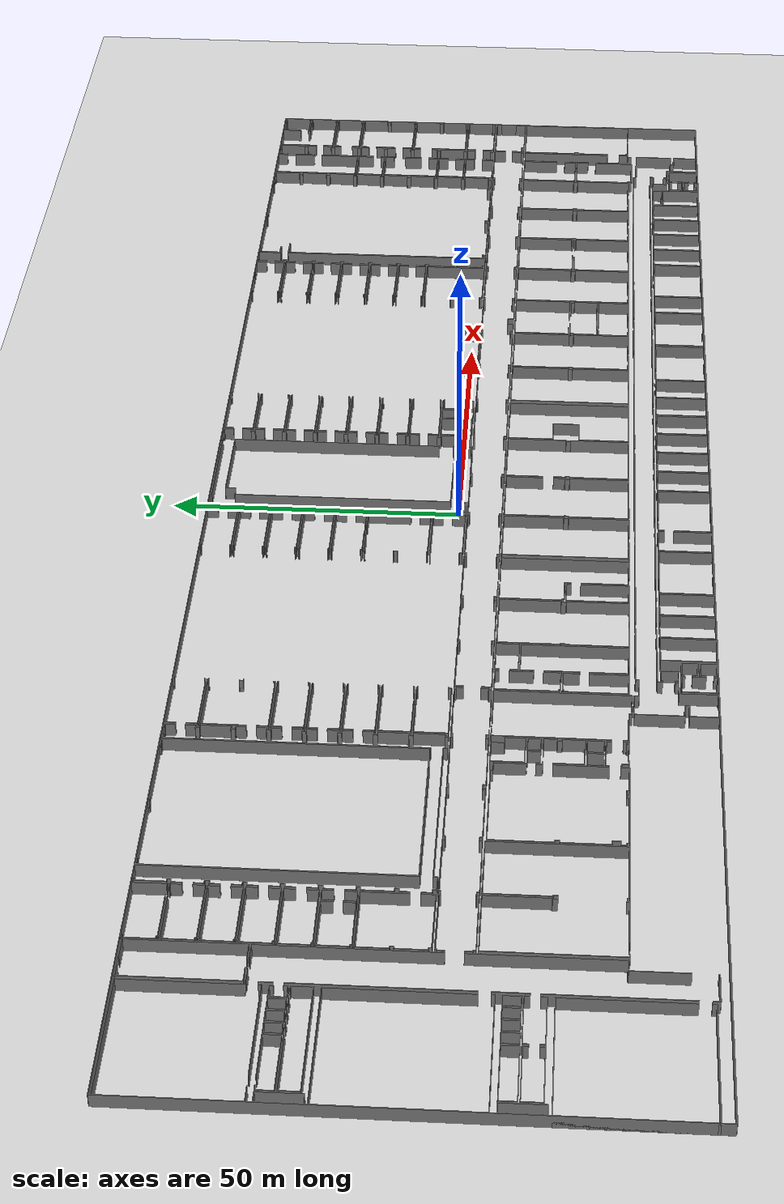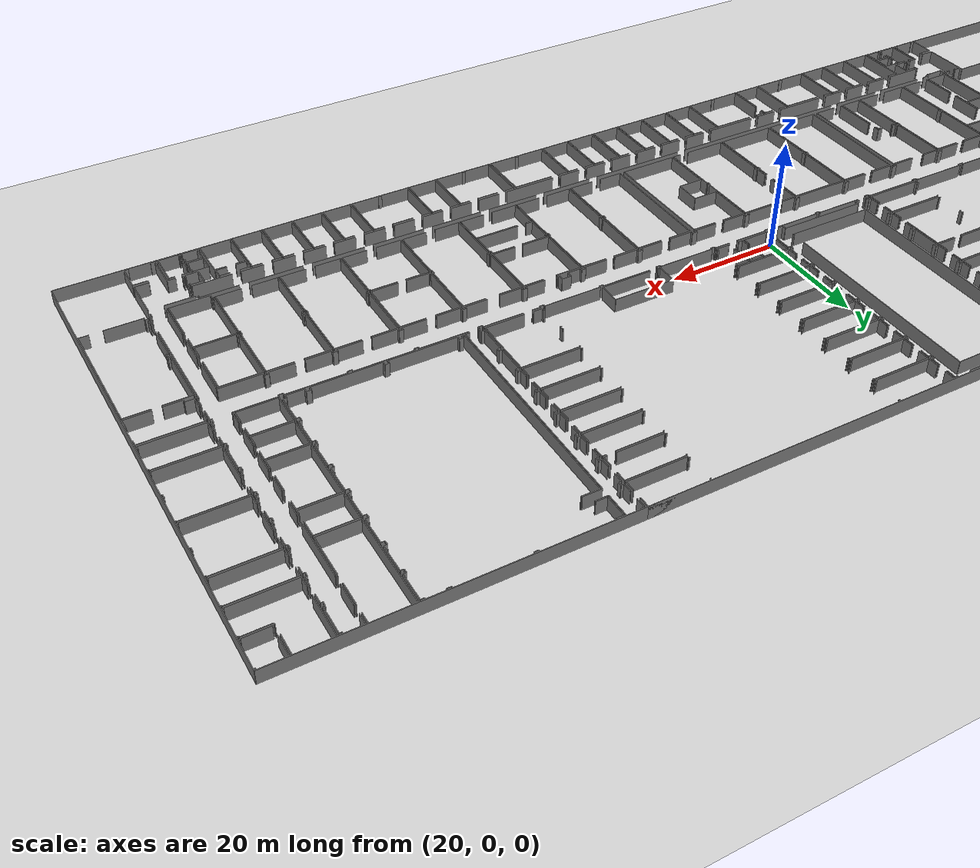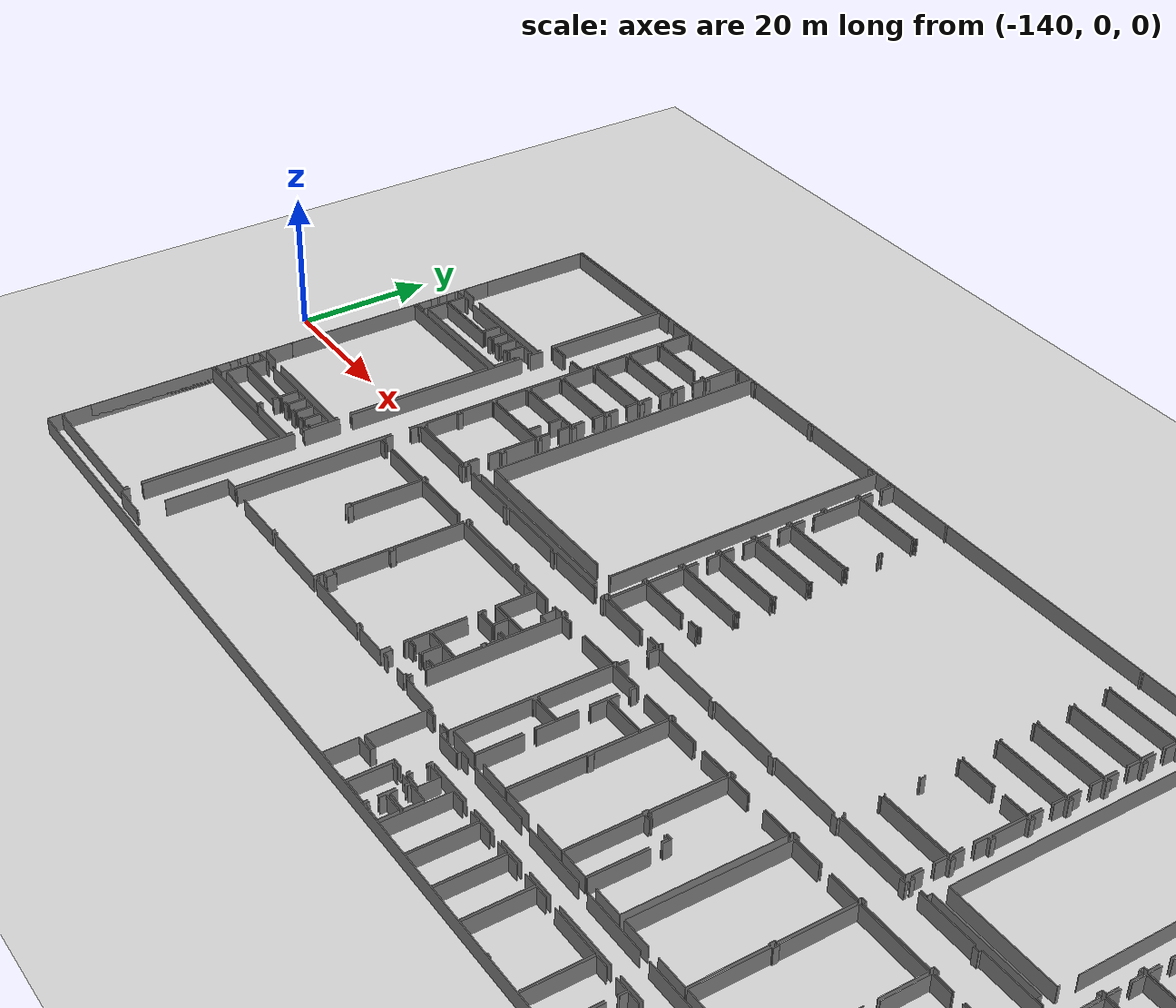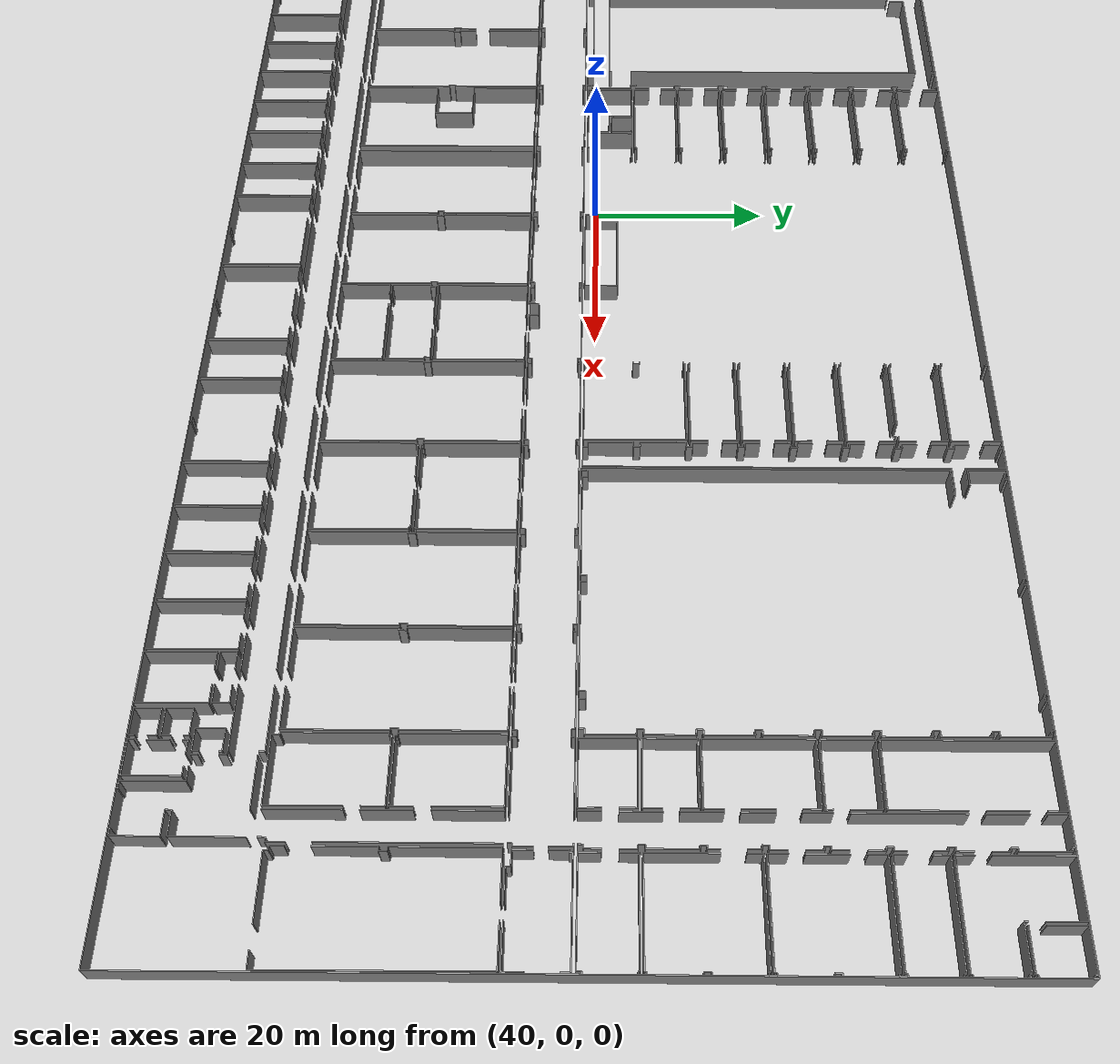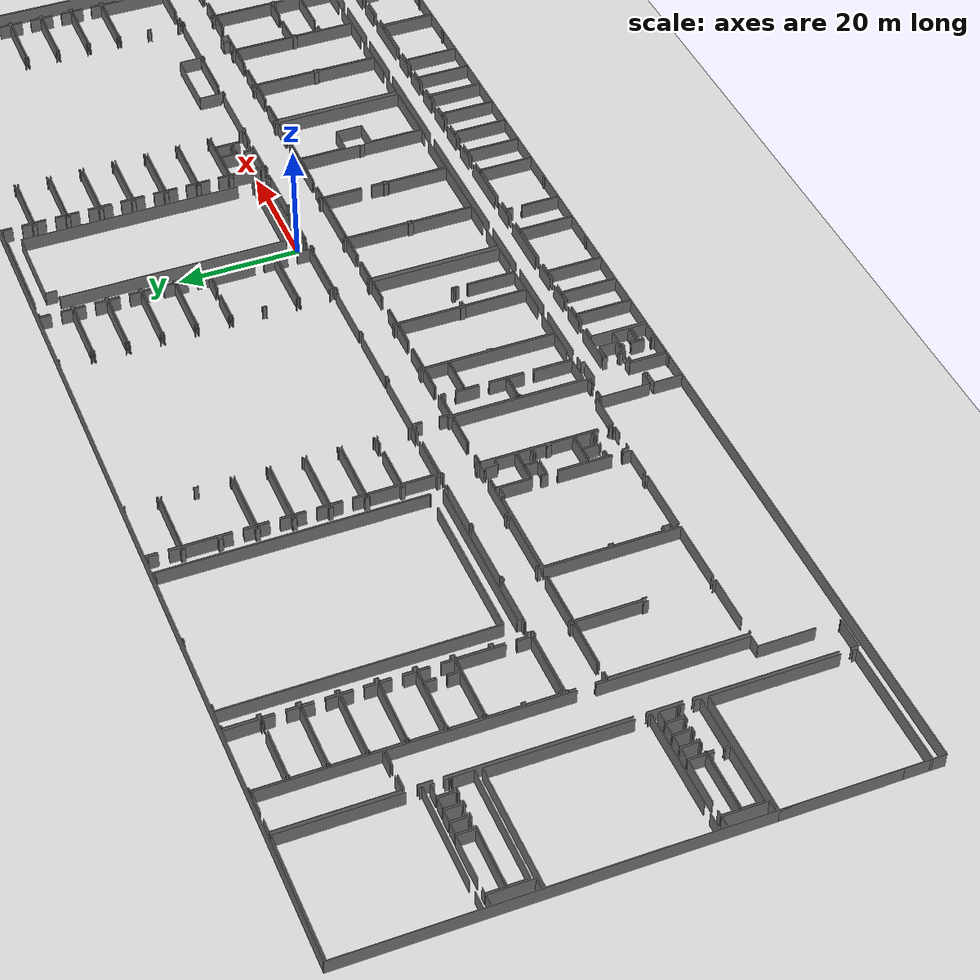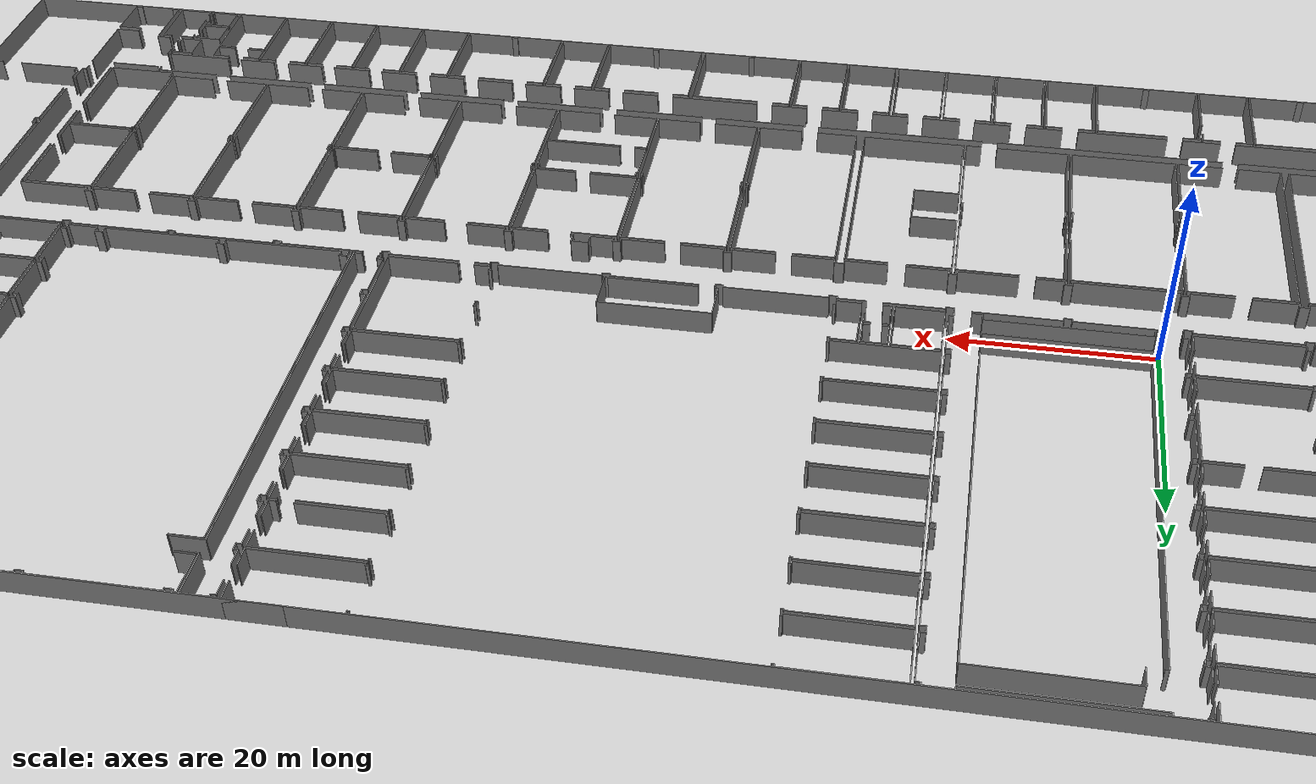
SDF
<sdf version="1.6">
  <world name="default">
    <light name="sun" type="directional">
      <cast_shadows>1</cast_shadows>
      <pose frame="">0 0 10 0 -0 0</pose>
      <diffuse>0.8 0.8 0.8 1</diffuse>
      <specular>0.1 0.1 0.1 1</specular>
      <attenuation>
        <range>1000</range>
        <constant>0.9</constant>
        <linear>0.01</linear>
        <quadratic>0.001</quadratic>
      </attenuation>
      <direction>-0.5 0.5 -1</direction>
    </light>
    <model name="ground_plane">
      <static>1</static>
      <link name="link">
        <collision name="collision">
          <geometry>
            <plane>
              <normal>0 0 1</normal>
              <size>100 100</size>
            </plane>
          </geometry>
          <surface>
            <friction>
              <ode>
                <mu>100</mu>
                <mu2>50</mu2>
              </ode>
              <torsional>
                <ode />
              </torsional>
            </friction>
            <contact>
              <ode />
            </contact>
            <bounce />
          </surface>
          <max_contacts>10</max_contacts>
        </collision>
        <visual name="visual">
          <cast_shadows>0</cast_shadows>
          <geometry>
            <plane>
              <normal>0 0 1</normal>
              <size>100 100</size>
            </plane>
          </geometry>
          <material>
            <script>
              <uri>file://media/materials/scripts/gazebo.material</uri>
              <name>Gazebo/Grey</name>
            </script>
          </material>
        </visual>
        <self_collide>0</self_collide>
        <kinematic>0</kinematic>
        <gravity>1</gravity>
      </link>
    </model>
    <gravity>0 0 -9.8</gravity>
    <magnetic_field>6e-06 2.3e-05 -4.2e-05</magnetic_field>
    <atmosphere type="adiabatic" />
    <physics default="0" name="default_physics" type="ode">
      <max_step_size>0.001</max_step_size>
      <real_time_factor>1</real_time_factor>
      <real_time_update_rate>1000</real_time_update_rate>
    </physics>
    <scene>
      <ambient>0.4 0.4 0.4 1</ambient>
      <background>0.7 0.7 0.7 1</background>
      <shadows>1</shadows>
    </scene>
    <spherical_coordinates>
      <surface_model>EARTH_WGS84</surface_model>
      <latitude_deg>0</latitude_deg>
      <longitude_deg>0</longitude_deg>
      <elevation>0</elevation>
      <heading_deg>0</heading_deg>
    </spherical_coordinates>
  <model name="50015848">
		<static>1</static>
		<link name="Wall_0">
			<collision name="Wall_0_Collision">
				<geometry>
					<box>
						<size>16.2391134736 0.1 2.5</size>
					</box>
				</geometry>
				<pose frame="">8.1195567368 0 1.25 0 0 0</pose>
			</collision>
			<visual name="Wall_0_Visual">
				<pose frame="">8.1195567368 0 1.25 0 0 0</pose>
				<geometry>
					<box>
						<size>16.2391134736 0.1 2.5</size>
					</box>
				</geometry>
				<material>
					<script>
						<uri>file://media/materials/scripts/gazebo.material</uri>
						<name>Gazebo/Grey</name>
					</script>
					<ambient>1 1 1 1</ambient>
				</material>
			</visual>
			<pose frame="">20.7364461557 -21.3126629411 0 0 0 3.14159265359</pose>
		</link>
		<link name="Wall_1">
			<collision name="Wall_1_Collision">
				<geometry>
					<box>
						<size>2.77527925962 0.1 2.5</size>
					</box>
				</geometry>
				<pose frame="">1.38763962981 0 1.25 0 0 0</pose>
			</collision>
			<visual name="Wall_1_Visual">
				<pose frame="">1.38763962981 0 1.25 0 0 0</pose>
				<geometry>
					<box>
						<size>2.77527925962 0.1 2.5</size>
					</box>
				</geometry>
				<material>
					<script>
						<uri>file://media/materials/scripts/gazebo.material</uri>
						<name>Gazebo/Grey</name>
					</script>
					<ambient>1 1 1 1</ambient>
				</material>
			</visual>
			<pose frame="">2.79709988646 -21.3126629411 0 0 0 3.14159265359</pose>
		</link>
		<link name="Wall_2">
			<collision name="Wall_2_Collision">
				<geometry>
					<box>
						<size>0.330354141162 0.1 2.5</size>
					</box>
				</geometry>
				<pose frame="">0.165177070581 0 1.25 0 0 0</pose>
			</collision>
			<visual name="Wall_2_Visual">
				<pose frame="">0.165177070581 0 1.25 0 0 0</pose>
				<geometry>
					<box>
						<size>0.330354141162 0.1 2.5</size>
					</box>
				</geometry>
				<material>
					<script>
						<uri>file://media/materials/scripts/gazebo.material</uri>
						<name>Gazebo/Grey</name>
					</script>
					<ambient>1 1 1 1</ambient>
				</material>
			</visual>
			<pose frame="">0.0218206268356 -21.3126629411 0 0 0 1.57079632679</pose>
		</link>
		<link name="Wall_3">
			<collision name="Wall_3_Collision">
				<geometry>
					<box>
						<size>16.7858977856 0.1 2.5</size>
					</box>
				</geometry>
				<pose frame="">8.39294889279 0 1.25 0 0 0</pose>
			</collision>
			<visual name="Wall_3_Visual">
				<pose frame="">8.39294889279 0 1.25 0 0 0</pose>
				<geometry>
					<box>
						<size>16.7858977856 0.1 2.5</size>
					</box>
				</geometry>
				<material>
					<script>
						<uri>file://media/materials/scripts/gazebo.material</uri>
						<name>Gazebo/Grey</name>
					</script>
					<ambient>1 1 1 1</ambient>
				</material>
			</visual>
			<pose frame="">0.0218206268356 -17.1976986851 0 0 0 1.57079632679</pose>
		</link>
		<link name="Wall_4">
			<collision name="Wall_4_Collision">
				<geometry>
					<box>
						<size>20.6638798851 0.1 2.5</size>
					</box>
				</geometry>
				<pose frame="">10.3319399425 0 1.25 0 0 0</pose>
			</collision>
			<visual name="Wall_4_Visual">
				<pose frame="">10.3319399425 0 1.25 0 0 0</pose>
				<geometry>
					<box>
						<size>20.6638798851 0.1 2.5</size>
					</box>
				</geometry>
				<material>
					<script>
						<uri>file://media/materials/scripts/gazebo.material</uri>
						<name>Gazebo/Grey</name>
					</script>
					<ambient>1 1 1 1</ambient>
				</material>
			</visual>
			<pose frame="">0.0218206268356 -0.411800899467 0 0 0 0.0</pose>
		</link>
		<link name="Wall_5">
			<collision name="Wall_5_Collision">
				<geometry>
					<box>
						<size>18.5630102316 0.1 2.5</size>
					</box>
				</geometry>
				<pose frame="">9.2815051158 0 1.25 0 0 0</pose>
			</collision>
			<visual name="Wall_5_Visual">
				<pose frame="">9.2815051158 0 1.25 0 0 0</pose>
				<geometry>
					<box>
						<size>18.5630102316 0.1 2.5</size>
					</box>
				</geometry>
				<material>
					<script>
						<uri>file://media/materials/scripts/gazebo.material</uri>
						<name>Gazebo/Grey</name>
					</script>
					<ambient>1 1 1 1</ambient>
				</material>
			</visual>
			<pose frame="">20.6857005119 -0.411800899467 0 0 0 -1.57079632679</pose>
		</link>
		<link name="Wall_6">
			<collision name="Wall_6_Collision">
				<geometry>
					<box>
						<size>0.460782251772 0.1 2.5</size>
					</box>
				</geometry>
				<pose frame="">0.230391125886 0 1.25 0 0 0</pose>
			</collision>
			<visual name="Wall_6_Visual">
				<pose frame="">0.230391125886 0 1.25 0 0 0</pose>
				<geometry>
					<box>
						<size>0.460782251772 0.1 2.5</size>
					</box>
				</geometry>
				<material>
					<script>
						<uri>file://media/materials/scripts/gazebo.material</uri>
						<name>Gazebo/Grey</name>
					</script>
					<ambient>1 1 1 1</ambient>
				</material>
			</visual>
			<pose frame="">20.6857005119 -20.8546835058 0 0 0 -1.46044314939</pose>
		</link>
		<link name="Wall_7">
			<collision name="Wall_7_Collision">
				<geometry>
					<box>
						<size>2.75269744813 0.1 2.5</size>
					</box>
				</geometry>
				<pose frame="">1.37634872406 0 1.25 0 0 0</pose>
			</collision>
			<visual name="Wall_7_Visual">
				<pose frame="">1.37634872406 0 1.25 0 0 0</pose>
				<geometry>
					<box>
						<size>2.75269744813 0.1 2.5</size>
					</box>
				</geometry>
				<material>
					<script>
						<uri>file://media/materials/scripts/gazebo.material</uri>
						<name>Gazebo/Grey</name>
					</script>
					<ambient>1 1 1 1</ambient>
				</material>
			</visual>
			<pose frame="">11.7884667838 -25.1315263655 0 0 0 1.57079632679</pose>
		</link>
		<link name="Wall_8">
			<collision name="Wall_8_Collision">
				<geometry>
					<box>
						<size>7.37334204467 0.1 2.5</size>
					</box>
				</geometry>
				<pose frame="">3.68667102233 0 1.25 0 0 0</pose>
			</collision>
			<visual name="Wall_8_Visual">
				<pose frame="">3.68667102233 0 1.25 0 0 0</pose>
				<geometry>
					<box>
						<size>7.37334204467 0.1 2.5</size>
					</box>
				</geometry>
				<material>
					<script>
						<uri>file://media/materials/scripts/gazebo.material</uri>
						<name>Gazebo/Grey</name>
					</script>
					<ambient>1 1 1 1</ambient>
				</material>
			</visual>
			<pose frame="">11.7884667838 -22.3788289174 0 0 0 3.14159265359</pose>
		</link>
		<link name="Wall_9">
			<collision name="Wall_9_Collision">
				<geometry>
					<box>
						<size>0.928391553388 0.1 2.5</size>
					</box>
				</geometry>
				<pose frame="">0.464195776694 0 1.25 0 0 0</pose>
			</collision>
			<visual name="Wall_9_Visual">
				<pose frame="">0.464195776694 0 1.25 0 0 0</pose>
				<geometry>
					<box>
						<size>0.928391553388 0.1 2.5</size>
					</box>
				</geometry>
				<material>
					<script>
						<uri>file://media/materials/scripts/gazebo.material</uri>
						<name>Gazebo/Grey</name>
					</script>
					<ambient>1 1 1 1</ambient>
				</material>
			</visual>
			<pose frame="">3.01606733947 -22.3788289174 0 0 0 3.14159265359</pose>
		</link>
		<link name="Wall_10">
			<collision name="Wall_10_Collision">
				<geometry>
					<box>
						<size>2.71210093309 0.1 2.5</size>
					</box>
				</geometry>
				<pose frame="">1.35605046654 0 1.25 0 0 0</pose>
			</collision>
			<visual name="Wall_10_Visual">
				<pose frame="">1.35605046654 0 1.25 0 0 0</pose>
				<geometry>
					<box>
						<size>2.71210093309 0.1 2.5</size>
					</box>
				</geometry>
				<material>
					<script>
						<uri>file://media/materials/scripts/gazebo.material</uri>
						<name>Gazebo/Grey</name>
					</script>
					<ambient>1 1 1 1</ambient>
				</material>
			</visual>
			<pose frame="">2.08767578608 -22.3788289174 0 0 0 -1.57079632679</pose>
		</link>
		<link name="Wall_11">
			<collision name="Wall_11_Collision">
				<geometry>
					<box>
						<size>9.70087594285 0.1 2.5</size>
					</box>
				</geometry>
				<pose frame="">4.85043797142 0 1.25 0 0 0</pose>
			</collision>
			<visual name="Wall_11_Visual">
				<pose frame="">4.85043797142 0 1.25 0 0 0</pose>
				<geometry>
					<box>
						<size>9.70087594285 0.1 2.5</size>
					</box>
				</geometry>
				<material>
					<script>
						<uri>file://media/materials/scripts/gazebo.material</uri>
						<name>Gazebo/Grey</name>
					</script>
					<ambient>1 1 1 1</ambient>
				</material>
			</visual>
			<pose frame="">2.08767578608 -25.0909298505 0 0 0 -0.00418484204685</pose>
		</link>
		<link name="Wall_12">
			<collision name="Wall_12_Collision">
				<geometry>
					<box>
						<size>1.82075369967 0.1 2.5</size>
					</box>
				</geometry>
				<pose frame="">0.910376849837 0 1.25 0 0 0</pose>
			</collision>
			<visual name="Wall_12_Visual">
				<pose frame="">0.910376849837 0 1.25 0 0 0</pose>
				<geometry>
					<box>
						<size>1.82075369967 0.1 2.5</size>
					</box>
				</geometry>
				<material>
					<script>
						<uri>file://media/materials/scripts/gazebo.material</uri>
						<name>Gazebo/Grey</name>
					</script>
					<ambient>1 1 1 1</ambient>
				</material>
			</visual>
			<pose frame="">1.83166401309 -29.2639978687 0 0 0 3.14159265359</pose>
		</link>
		<link name="Wall_13">
			<collision name="Wall_13_Collision">
				<geometry>
					<box>
						<size>1.1100609582 0.1 2.5</size>
					</box>
				</geometry>
				<pose frame="">0.555030479102 0 1.25 0 0 0</pose>
			</collision>
			<visual name="Wall_13_Visual">
				<pose frame="">0.555030479102 0 1.25 0 0 0</pose>
				<geometry>
					<box>
						<size>1.1100609582 0.1 2.5</size>
					</box>
				</geometry>
				<material>
					<script>
						<uri>file://media/materials/scripts/gazebo.material</uri>
						<name>Gazebo/Grey</name>
					</script>
					<ambient>1 1 1 1</ambient>
				</material>
			</visual>
			<pose frame="">0.0109103134178 -27.0291597156 0 0 0 1.57079632679</pose>
		</link>
		<link name="Wall_14">
			<collision name="Wall_14_Collision">
				<geometry>
					<box>
						<size>1.18592569569 0.1 2.5</size>
					</box>
				</geometry>
				<pose frame="">0.592962847846 0 1.25 0 0 0</pose>
			</collision>
			<visual name="Wall_14_Visual">
				<pose frame="">0.592962847846 0 1.25 0 0 0</pose>
				<geometry>
					<box>
						<size>1.18592569569 0.1 2.5</size>
					</box>
				</geometry>
				<material>
					<script>
						<uri>file://media/materials/scripts/gazebo.material</uri>
						<name>Gazebo/Grey</name>
					</script>
					<ambient>1 1 1 1</ambient>
				</material>
			</visual>
			<pose frame="">0.0109103134178 -25.5154171609 0 0 0 1.57079632679</pose>
		</link>
		<link name="Wall_15">
			<collision name="Wall_15_Collision">
				<geometry>
					<box>
						<size>0.52978452131 0.1 2.5</size>
					</box>
				</geometry>
				<pose frame="">0.264892260655 0 1.25 0 0 0</pose>
			</collision>
			<visual name="Wall_15_Visual">
				<pose frame="">0.264892260655 0 1.25 0 0 0</pose>
				<geometry>
					<box>
						<size>0.52978452131 0.1 2.5</size>
					</box>
				</geometry>
				<material>
					<script>
						<uri>file://media/materials/scripts/gazebo.material</uri>
						<name>Gazebo/Grey</name>
					</script>
					<ambient>1 1 1 1</ambient>
				</material>
			</visual>
			<pose frame="">0.0109103134178 -22.9040463308 0 0 0 1.57079632679</pose>
		</link>
		<link name="Wall_16">
			<collision name="Wall_16_Collision">
				<geometry>
					<box>
						<size>1.75503809095 0.1 2.5</size>
					</box>
				</geometry>
				<pose frame="">0.877519045474 0 1.25 0 0 0</pose>
			</collision>
			<visual name="Wall_16_Visual">
				<pose frame="">0.877519045474 0 1.25 0 0 0</pose>
				<geometry>
					<box>
						<size>1.75503809095 0.1 2.5</size>
					</box>
				</geometry>
				<material>
					<script>
						<uri>file://media/materials/scripts/gazebo.material</uri>
						<name>Gazebo/Grey</name>
					</script>
					<ambient>1 1 1 1</ambient>
				</material>
			</visual>
			<pose frame="">0.0109103134178 -22.3742618095 0 0 0 0.0</pose>
		</link>
		<link name="Wall_17">
			<collision name="Wall_17_Collision">
				<geometry>
					<box>
						<size>6.89004945606 0.1 2.5</size>
					</box>
				</geometry>
				<pose frame="">3.44502472803 0 1.25 0 0 0</pose>
			</collision>
			<visual name="Wall_17_Visual">
				<pose frame="">3.44502472803 0 1.25 0 0 0</pose>
				<geometry>
					<box>
						<size>6.89004945606 0.1 2.5</size>
					</box>
				</geometry>
				<material>
					<script>
						<uri>file://media/materials/scripts/gazebo.material</uri>
						<name>Gazebo/Grey</name>
					</script>
					<ambient>1 1 1 1</ambient>
				</material>
			</visual>
			<pose frame="">1.76594840437 -22.3742618095 0 0 0 -1.56125842645</pose>
		</link>
		<link name="Wall_18">
			<collision name="Wall_18_Collision">
				<geometry>
					<box>
						<size>0.189281251388 0.1 2.5</size>
					</box>
				</geometry>
				<pose frame="">0.0946406256938 0 1.25 0 0 0</pose>
			</collision>
			<visual name="Wall_18_Visual">
				<pose frame="">0.0946406256938 0 1.25 0 0 0</pose>
				<geometry>
					<box>
						<size>0.189281251388 0.1 2.5</size>
					</box>
				</geometry>
				<material>
					<script>
						<uri>file://media/materials/scripts/gazebo.material</uri>
						<name>Gazebo/Grey</name>
					</script>
					<ambient>1 1 1 1</ambient>
				</material>
			</visual>
			<pose frame="">26.2809151977 -85.763436495 0 0 0 -1.57079632679</pose>
		</link>
		<link name="Wall_19">
			<collision name="Wall_19_Collision">
				<geometry>
					<box>
						<size>5.0124009667 0.1 2.5</size>
					</box>
				</geometry>
				<pose frame="">2.50620048335 0 1.25 0 0 0</pose>
			</collision>
			<visual name="Wall_19_Visual">
				<pose frame="">2.50620048335 0 1.25 0 0 0</pose>
				<geometry>
					<box>
						<size>5.0124009667 0.1 2.5</size>
					</box>
				</geometry>
				<material>
					<script>
						<uri>file://media/materials/scripts/gazebo.material</uri>
						<name>Gazebo/Grey</name>
					</script>
					<ambient>1 1 1 1</ambient>
				</material>
			</visual>
			<pose frame="">26.2809151977 -85.9527177464 0 0 0 3.14159265359</pose>
		</link>
		<link name="Wall_20">
			<collision name="Wall_20_Collision">
				<geometry>
					<box>
						<size>1.18567196747 0.1 2.5</size>
					</box>
				</geometry>
				<pose frame="">0.592835983736 0 1.25 0 0 0</pose>
			</collision>
			<visual name="Wall_20_Visual">
				<pose frame="">0.592835983736 0 1.25 0 0 0</pose>
				<geometry>
					<box>
						<size>1.18567196747 0.1 2.5</size>
					</box>
				</geometry>
				<material>
					<script>
						<uri>file://media/materials/scripts/gazebo.material</uri>
						<name>Gazebo/Grey</name>
					</script>
					<ambient>1 1 1 1</ambient>
				</material>
			</visual>
			<pose frame="">21.268514231 -85.9527177464 0 0 0 1.57079632679</pose>
		</link>
		<link name="Wall_21">
			<collision name="Wall_21_Collision">
				<geometry>
					<box>
						<size>22.2679496857 0.1 2.5</size>
					</box>
				</geometry>
				<pose frame="">11.1339748428 0 1.25 0 0 0</pose>
			</collision>
			<visual name="Wall_21_Visual">
				<pose frame="">11.1339748428 0 1.25 0 0 0</pose>
				<geometry>
					<box>
						<size>22.2679496857 0.1 2.5</size>
					</box>
				</geometry>
				<material>
					<script>
						<uri>file://media/materials/scripts/gazebo.material</uri>
						<name>Gazebo/Grey</name>
					</script>
					<ambient>1 1 1 1</ambient>
				</material>
			</visual>
			<pose frame="">21.268514231 -82.9343668529 0 0 0 1.57079632679</pose>
		</link>
		<link name="Wall_22">
			<collision name="Wall_22_Collision">
				<geometry>
					<box>
						<size>5.48788764914 0.1 2.5</size>
					</box>
				</geometry>
				<pose frame="">2.74394382457 0 1.25 0 0 0</pose>
			</collision>
			<visual name="Wall_22_Visual">
				<pose frame="">2.74394382457 0 1.25 0 0 0</pose>
				<geometry>
					<box>
						<size>5.48788764914 0.1 2.5</size>
					</box>
				</geometry>
				<material>
					<script>
						<uri>file://media/materials/scripts/gazebo.material</uri>
						<name>Gazebo/Grey</name>
					</script>
					<ambient>1 1 1 1</ambient>
				</material>
			</visual>
			<pose frame="">21.268514231 -59.2473152383 0 0 0 1.57079632679</pose>
		</link>
		<link name="Wall_23">
			<collision name="Wall_23_Collision">
				<geometry>
					<box>
						<size>27.4686169909 0.1 2.5</size>
					</box>
				</geometry>
				<pose frame="">13.7343084955 0 1.25 0 0 0</pose>
			</collision>
			<visual name="Wall_23_Visual">
				<pose frame="">13.7343084955 0 1.25 0 0 0</pose>
				<geometry>
					<box>
						<size>27.4686169909 0.1 2.5</size>
					</box>
				</geometry>
				<material>
					<script>
						<uri>file://media/materials/scripts/gazebo.material</uri>
						<name>Gazebo/Grey</name>
					</script>
					<ambient>1 1 1 1</ambient>
				</material>
			</visual>
			<pose frame="">21.268514231 -51.9077190467 0 0 0 1.57079632679</pose>
		</link>
		<link name="Wall_24">
			<collision name="Wall_24_Collision">
				<geometry>
					<box>
						<size>2.1759732063 0.1 2.5</size>
					</box>
				</geometry>
				<pose frame="">1.08798660315 0 1.25 0 0 0</pose>
			</collision>
			<visual name="Wall_24_Visual">
				<pose frame="">1.08798660315 0 1.25 0 0 0</pose>
				<geometry>
					<box>
						<size>2.1759732063 0.1 2.5</size>
					</box>
				</geometry>
				<material>
					<script>
						<uri>file://media/materials/scripts/gazebo.material</uri>
						<name>Gazebo/Grey</name>
					</script>
					<ambient>1 1 1 1</ambient>
				</material>
			</visual>
			<pose frame="">21.268514231 -22.9872691866 0 0 0 1.57079632679</pose>
		</link>
		<link name="Wall_25">
			<collision name="Wall_25_Collision">
				<geometry>
					<box>
						<size>2.53170016936 0.1 2.5</size>
					</box>
				</geometry>
				<pose frame="">1.26585008468 0 1.25 0 0 0</pose>
			</collision>
			<visual name="Wall_25_Visual">
				<pose frame="">1.26585008468 0 1.25 0 0 0</pose>
				<geometry>
					<box>
						<size>2.53170016936 0.1 2.5</size>
					</box>
				</geometry>
				<material>
					<script>
						<uri>file://media/materials/scripts/gazebo.material</uri>
						<name>Gazebo/Grey</name>
					</script>
					<ambient>1 1 1 1</ambient>
				</material>
			</visual>
			<pose frame="">21.268514231 -19.0420491091 0 0 0 0.0</pose>
		</link>
		<link name="Wall_26">
			<collision name="Wall_26_Collision">
				<geometry>
					<box>
						<size>2.57077431509 0.1 2.5</size>
					</box>
				</geometry>
				<pose frame="">1.28538715755 0 1.25 0 0 0</pose>
			</collision>
			<visual name="Wall_26_Visual">
				<pose frame="">1.28538715755 0 1.25 0 0 0</pose>
				<geometry>
					<box>
						<size>2.57077431509 0.1 2.5</size>
					</box>
				</geometry>
				<material>
					<script>
						<uri>file://media/materials/scripts/gazebo.material</uri>
						<name>Gazebo/Grey</name>
					</script>
					<ambient>1 1 1 1</ambient>
				</material>
			</visual>
			<pose frame="">25.6478632912 -19.0420491091 0 0 0 0.0</pose>
		</link>
		<link name="Wall_27">
			<collision name="Wall_27_Collision">
				<geometry>
					<box>
						<size>27.7489866729 0.1 2.5</size>
					</box>
				</geometry>
				<pose frame="">13.8744933365 0 1.25 0 0 0</pose>
			</collision>
			<visual name="Wall_27_Visual">
				<pose frame="">13.8744933365 0 1.25 0 0 0</pose>
				<geometry>
					<box>
						<size>27.7489866729 0.1 2.5</size>
					</box>
				</geometry>
				<material>
					<script>
						<uri>file://media/materials/scripts/gazebo.material</uri>
						<name>Gazebo/Grey</name>
					</script>
					<ambient>1 1 1 1</ambient>
				</material>
			</visual>
			<pose frame="">28.2186376063 -19.0420491091 0 0 0 -1.57079632679</pose>
		</link>
		<link name="Wall_28">
			<collision name="Wall_28_Collision">
				<geometry>
					<box>
						<size>23.4437262526 0.1 2.5</size>
					</box>
				</geometry>
				<pose frame="">11.7218631263 0 1.25 0 0 0</pose>
			</collision>
			<visual name="Wall_28_Visual">
				<pose frame="">11.7218631263 0 1.25 0 0 0</pose>
				<geometry>
					<box>
						<size>23.4437262526 0.1 2.5</size>
					</box>
				</geometry>
				<material>
					<script>
						<uri>file://media/materials/scripts/gazebo.material</uri>
						<name>Gazebo/Grey</name>
					</script>
					<ambient>1 1 1 1</ambient>
				</material>
			</visual>
			<pose frame="">28.2186376063 -49.5787477244 0 0 0 -1.57079632679</pose>
		</link>
		<link name="Wall_29">
			<collision name="Wall_29_Collision">
				<geometry>
					<box>
						<size>1.95675202507 0.1 2.5</size>
					</box>
				</geometry>
				<pose frame="">0.978376012534 0 1.25 0 0 0</pose>
			</collision>
			<visual name="Wall_29_Visual">
				<pose frame="">0.978376012534 0 1.25 0 0 0</pose>
				<geometry>
					<box>
						<size>1.95675202507 0.1 2.5</size>
					</box>
				</geometry>
				<material>
					<script>
						<uri>file://media/materials/scripts/gazebo.material</uri>
						<name>Gazebo/Grey</name>
					</script>
					<ambient>1 1 1 1</ambient>
				</material>
			</visual>
			<pose frame="">28.2186376063 -73.022473977 0 0 0 3.14159265359</pose>
		</link>
		<link name="Wall_30">
			<collision name="Wall_30_Collision">
				<geometry>
					<box>
						<size>8.99316312833 0.1 2.5</size>
					</box>
				</geometry>
				<pose frame="">4.49658156416 0 1.25 0 0 0</pose>
			</collision>
			<visual name="Wall_30_Visual">
				<pose frame="">4.49658156416 0 1.25 0 0 0</pose>
				<geometry>
					<box>
						<size>8.99316312833 0.1 2.5</size>
					</box>
				</geometry>
				<material>
					<script>
						<uri>file://media/materials/scripts/gazebo.material</uri>
						<name>Gazebo/Grey</name>
					</script>
					<ambient>1 1 1 1</ambient>
				</material>
			</visual>
			<pose frame="">26.2618855813 -73.022473977 0 0 0 -1.56868031596</pose>
		</link>
		<link name="Wall_31">
			<collision name="Wall_31_Collision">
				<geometry>
					<box>
						<size>2.692310132 0.1 2.5</size>
					</box>
				</geometry>
				<pose frame="">1.346155066 0 1.25 0 0 0</pose>
			</collision>
			<visual name="Wall_31_Visual">
				<pose frame="">1.346155066 0 1.25 0 0 0</pose>
				<geometry>
					<box>
						<size>2.692310132 0.1 2.5</size>
					</box>
				</geometry>
				<material>
					<script>
						<uri>file://media/materials/scripts/gazebo.material</uri>
						<name>Gazebo/Grey</name>
					</script>
					<ambient>1 1 1 1</ambient>
				</material>
			</visual>
			<pose frame="">28.272681717 -18.6787102995 0 0 0 3.14159265359</pose>
		</link>
		<link name="Wall_32">
			<collision name="Wall_32_Collision">
				<geometry>
					<box>
						<size>2.57990853098 0.1 2.5</size>
					</box>
				</geometry>
				<pose frame="">1.28995426549 0 1.25 0 0 0</pose>
			</collision>
			<visual name="Wall_32_Visual">
				<pose frame="">1.28995426549 0 1.25 0 0 0</pose>
				<geometry>
					<box>
						<size>2.57990853098 0.1 2.5</size>
					</box>
				</geometry>
				<material>
					<script>
						<uri>file://media/materials/scripts/gazebo.material</uri>
						<name>Gazebo/Grey</name>
					</script>
					<ambient>1 1 1 1</ambient>
				</material>
			</visual>
			<pose frame="">23.8443631105 -18.6787102995 0 0 0 3.14159265359</pose>
		</link>
		<link name="Wall_33">
			<collision name="Wall_33_Collision">
				<geometry>
					<box>
						<size>18.2788346263 0.1 2.5</size>
					</box>
				</geometry>
				<pose frame="">9.13941731315 0 1.25 0 0 0</pose>
			</collision>
			<visual name="Wall_33_Visual">
				<pose frame="">9.13941731315 0 1.25 0 0 0</pose>
				<geometry>
					<box>
						<size>18.2788346263 0.1 2.5</size>
					</box>
				</geometry>
				<material>
					<script>
						<uri>file://media/materials/scripts/gazebo.material</uri>
						<name>Gazebo/Grey</name>
					</script>
					<ambient>1 1 1 1</ambient>
				</material>
			</visual>
			<pose frame="">21.2644545795 -18.6787102995 0 0 0 1.57079632679</pose>
		</link>
		<link name="Wall_34">
			<collision name="Wall_34_Collision">
				<geometry>
					<box>
						<size>2.21656972134 0.1 2.5</size>
					</box>
				</geometry>
				<pose frame="">1.10828486067 0 1.25 0 0 0</pose>
			</collision>
			<visual name="Wall_34_Visual">
				<pose frame="">1.10828486067 0 1.25 0 0 0</pose>
				<geometry>
					<box>
						<size>2.21656972134 0.1 2.5</size>
					</box>
				</geometry>
				<material>
					<script>
						<uri>file://media/materials/scripts/gazebo.material</uri>
						<name>Gazebo/Grey</name>
					</script>
					<ambient>1 1 1 1</ambient>
				</material>
			</visual>
			<pose frame="">21.2644545795 -0.399875673173 0 0 0 0.0</pose>
		</link>
		<link name="Wall_35">
			<collision name="Wall_35_Collision">
				<geometry>
					<box>
						<size>3.35758552227 0.1 2.5</size>
					</box>
				</geometry>
				<pose frame="">1.67879276113 0 1.25 0 0 0</pose>
			</collision>
			<visual name="Wall_35_Visual">
				<pose frame="">1.67879276113 0 1.25 0 0 0</pose>
				<geometry>
					<box>
						<size>3.35758552227 0.1 2.5</size>
					</box>
				</geometry>
				<material>
					<script>
						<uri>file://media/materials/scripts/gazebo.material</uri>
						<name>Gazebo/Grey</name>
					</script>
					<ambient>1 1 1 1</ambient>
				</material>
			</visual>
			<pose frame="">24.8640968227 -0.399875673173 0 0 0 0.0</pose>
		</link>
		<link name="Wall_36">
			<collision name="Wall_36_Collision">
				<geometry>
					<box>
						<size>18.2789057723 0.1 2.5</size>
					</box>
				</geometry>
				<pose frame="">9.13945288613 0 1.25 0 0 0</pose>
			</collision>
			<visual name="Wall_36_Visual">
				<pose frame="">9.13945288613 0 1.25 0 0 0</pose>
				<geometry>
					<box>
						<size>18.2789057723 0.1 2.5</size>
					</box>
				</geometry>
				<material>
					<script>
						<uri>file://media/materials/scripts/gazebo.material</uri>
						<name>Gazebo/Grey</name>
					</script>
					<ambient>1 1 1 1</ambient>
				</material>
			</visual>
			<pose frame="">28.221682345 -0.399875673173 0 0 0 -1.56800625616</pose>
		</link>
		<link name="Wall_37">
			<collision name="Wall_37_Collision">
				<geometry>
					<box>
						<size>18.6221289066 0.1 2.5</size>
					</box>
				</geometry>
				<pose frame="">9.31106445331 0 1.25 0 0 0</pose>
			</collision>
			<visual name="Wall_37_Visual">
				<pose frame="">9.31106445331 0 1.25 0 0 0</pose>
				<geometry>
					<box>
						<size>18.6221289066 0.1 2.5</size>
					</box>
				</geometry>
				<material>
					<script>
						<uri>file://media/materials/scripts/gazebo.material</uri>
						<name>Gazebo/Grey</name>
					</script>
					<ambient>1 1 1 1</ambient>
				</material>
			</visual>
			<pose frame="">20.7539534028 -28.6827065189 0 0 0 3.14159265359</pose>
		</link>
		<link name="Wall_38">
			<collision name="Wall_38_Collision">
				<geometry>
					<box>
						<size>3.25558677822 0.1 2.5</size>
					</box>
				</geometry>
				<pose frame="">1.62779338911 0 1.25 0 0 0</pose>
			</collision>
			<visual name="Wall_38_Visual">
				<pose frame="">1.62779338911 0 1.25 0 0 0</pose>
				<geometry>
					<box>
						<size>3.25558677822 0.1 2.5</size>
					</box>
				</geometry>
				<material>
					<script>
						<uri>file://media/materials/scripts/gazebo.material</uri>
						<name>Gazebo/Grey</name>
					</script>
					<ambient>1 1 1 1</ambient>
				</material>
			</visual>
			<pose frame="">2.13182449619 -28.6827065189 0 0 0 1.57079632679</pose>
		</link>
		<link name="Wall_39">
			<collision name="Wall_39_Collision">
				<geometry>
					<box>
						<size>10.2556946127 0.1 2.5</size>
					</box>
				</geometry>
				<pose frame="">5.12784730636 0 1.25 0 0 0</pose>
			</collision>
			<visual name="Wall_39_Visual">
				<pose frame="">5.12784730636 0 1.25 0 0 0</pose>
				<geometry>
					<box>
						<size>10.2556946127 0.1 2.5</size>
					</box>
				</geometry>
				<material>
					<script>
						<uri>file://media/materials/scripts/gazebo.material</uri>
						<name>Gazebo/Grey</name>
					</script>
					<ambient>1 1 1 1</ambient>
				</material>
			</visual>
			<pose frame="">2.13182449619 -25.4271197407 0 0 0 0.0</pose>
		</link>
		<link name="Wall_40">
			<collision name="Wall_40_Collision">
				<geometry>
					<box>
						<size>0.992077336361 0.1 2.5</size>
					</box>
				</geometry>
				<pose frame="">0.496038668181 0 1.25 0 0 0</pose>
			</collision>
			<visual name="Wall_40_Visual">
				<pose frame="">0.496038668181 0 1.25 0 0 0</pose>
				<geometry>
					<box>
						<size>0.992077336361 0.1 2.5</size>
					</box>
				</geometry>
				<material>
					<script>
						<uri>file://media/materials/scripts/gazebo.material</uri>
						<name>Gazebo/Grey</name>
					</script>
					<ambient>1 1 1 1</ambient>
				</material>
			</visual>
			<pose frame="">13.6084592988 -25.4271197407 0 0 0 0.0</pose>
		</link>
		<link name="Wall_41">
			<collision name="Wall_41_Collision">
				<geometry>
					<box>
						<size>0.9872565002 0.1 2.5</size>
					</box>
				</geometry>
				<pose frame="">0.4936282501 0 1.25 0 0 0</pose>
			</collision>
			<visual name="Wall_41_Visual">
				<pose frame="">0.4936282501 0 1.25 0 0 0</pose>
				<geometry>
					<box>
						<size>0.9872565002 0.1 2.5</size>
					</box>
				</geometry>
				<material>
					<script>
						<uri>file://media/materials/scripts/gazebo.material</uri>
						<name>Gazebo/Grey</name>
					</script>
					<ambient>1 1 1 1</ambient>
				</material>
			</visual>
			<pose frame="">15.795850275 -25.4271197407 0 0 0 0.0</pose>
		</link>
		<link name="Wall_42">
			<collision name="Wall_42_Collision">
				<geometry>
					<box>
						<size>1.03952451332 0.1 2.5</size>
					</box>
				</geometry>
				<pose frame="">0.519762256659 0 1.25 0 0 0</pose>
			</collision>
			<visual name="Wall_42_Visual">
				<pose frame="">0.519762256659 0 1.25 0 0 0</pose>
				<geometry>
					<box>
						<size>1.03952451332 0.1 2.5</size>
					</box>
				</geometry>
				<material>
					<script>
						<uri>file://media/materials/scripts/gazebo.material</uri>
						<name>Gazebo/Grey</name>
					</script>
					<ambient>1 1 1 1</ambient>
				</material>
			</visual>
			<pose frame="">17.9487342133 -25.4271197407 0 0 0 0.0</pose>
		</link>
		<link name="Wall_43">
			<collision name="Wall_43_Collision">
				<geometry>
					<box>
						<size>0.32045874062 0.1 2.5</size>
					</box>
				</geometry>
				<pose frame="">0.16022937031 0 1.25 0 0 0</pose>
			</collision>
			<visual name="Wall_43_Visual">
				<pose frame="">0.16022937031 0 1.25 0 0 0</pose>
				<geometry>
					<box>
						<size>0.32045874062 0.1 2.5</size>
					</box>
				</geometry>
				<material>
					<script>
						<uri>file://media/materials/scripts/gazebo.material</uri>
						<name>Gazebo/Grey</name>
					</script>
					<ambient>1 1 1 1</ambient>
				</material>
			</visual>
			<pose frame="">20.3802117362 -25.4271197407 0 0 0 0.0</pose>
		</link>
		<link name="Wall_44">
			<collision name="Wall_44_Collision">
				<geometry>
					<box>
						<size>3.25602277952 0.1 2.5</size>
					</box>
				</geometry>
				<pose frame="">1.62801138976 0 1.25 0 0 0</pose>
			</collision>
			<visual name="Wall_44_Visual">
				<pose frame="">1.62801138976 0 1.25 0 0 0</pose>
				<geometry>
					<box>
						<size>3.25602277952 0.1 2.5</size>
					</box>
				</geometry>
				<material>
					<script>
						<uri>file://media/materials/scripts/gazebo.material</uri>
						<name>Gazebo/Grey</name>
					</script>
					<ambient>1 1 1 1</ambient>
				</material>
			</visual>
			<pose frame="">20.7006704768 -25.4271197407 0 0 0 -1.5544311758</pose>
		</link>
		<link name="Wall_45">
			<collision name="Wall_45_Collision">
				<geometry>
					<box>
						<size>0.343548008551 0.1 2.5</size>
					</box>
				</geometry>
				<pose frame="">0.171774004275 0 1.25 0 0 0</pose>
			</collision>
			<visual name="Wall_45_Visual">
				<pose frame="">0.171774004275 0 1.25 0 0 0</pose>
				<geometry>
					<box>
						<size>0.343548008551 0.1 2.5</size>
					</box>
				</geometry>
				<material>
					<script>
						<uri>file://media/materials/scripts/gazebo.material</uri>
						<name>Gazebo/Grey</name>
					</script>
					<ambient>1 1 1 1</ambient>
				</material>
			</visual>
			<pose frame="">13.9479476559 -25.0883925683 0 0 0 3.14159265359</pose>
		</link>
		<link name="Wall_46">
			<collision name="Wall_46_Collision">
				<geometry>
					<box>
						<size>0.313608078707 0.1 2.5</size>
					</box>
				</geometry>
				<pose frame="">0.156804039353 0 1.25 0 0 0</pose>
			</collision>
			<visual name="Wall_46_Visual">
				<pose frame="">0.156804039353 0 1.25 0 0 0</pose>
				<geometry>
					<box>
						<size>0.313608078707 0.1 2.5</size>
					</box>
				</geometry>
				<material>
					<script>
						<uri>file://media/materials/scripts/gazebo.material</uri>
						<name>Gazebo/Grey</name>
					</script>
					<ambient>1 1 1 1</ambient>
				</material>
			</visual>
			<pose frame="">12.4461303275 -25.0883925683 0 0 0 3.14159265359</pose>
		</link>
		<link name="Wall_47">
			<collision name="Wall_47_Collision">
				<geometry>
					<box>
						<size>2.68647438296 0.1 2.5</size>
					</box>
				</geometry>
				<pose frame="">1.34323719148 0 1.25 0 0 0</pose>
			</collision>
			<visual name="Wall_47_Visual">
				<pose frame="">1.34323719148 0 1.25 0 0 0</pose>
				<geometry>
					<box>
						<size>2.68647438296 0.1 2.5</size>
					</box>
				</geometry>
				<material>
					<script>
						<uri>file://media/materials/scripts/gazebo.material</uri>
						<name>Gazebo/Grey</name>
					</script>
					<ambient>1 1 1 1</ambient>
				</material>
			</visual>
			<pose frame="">12.1325222488 -25.0883925683 0 0 0 1.57079632679</pose>
		</link>
		<link name="Wall_48">
			<collision name="Wall_48_Collision">
				<geometry>
					<box>
						<size>1.78117209751 0.1 2.5</size>
					</box>
				</geometry>
				<pose frame="">0.890586048754 0 1.25 0 0 0</pose>
			</collision>
			<visual name="Wall_48_Visual">
				<pose frame="">0.890586048754 0 1.25 0 0 0</pose>
				<geometry>
					<box>
						<size>1.78117209751 0.1 2.5</size>
					</box>
				</geometry>
				<material>
					<script>
						<uri>file://media/materials/scripts/gazebo.material</uri>
						<name>Gazebo/Grey</name>
					</script>
					<ambient>1 1 1 1</ambient>
				</material>
			</visual>
			<pose frame="">12.1325222488 -22.4019181853 0 0 0 0.0</pose>
		</link>
		<link name="Wall_49">
			<collision name="Wall_49_Collision">
				<geometry>
					<box>
						<size>2.68669274379 0.1 2.5</size>
					</box>
				</geometry>
				<pose frame="">1.3433463719 0 1.25 0 0 0</pose>
			</collision>
			<visual name="Wall_49_Visual">
				<pose frame="">1.3433463719 0 1.25 0 0 0</pose>
				<geometry>
					<box>
						<size>2.68669274379 0.1 2.5</size>
					</box>
				</geometry>
				<material>
					<script>
						<uri>file://media/materials/scripts/gazebo.material</uri>
						<name>Gazebo/Grey</name>
					</script>
					<ambient>1 1 1 1</ambient>
				</material>
			</visual>
			<pose frame="">13.9136943463 -22.4019181853 0 0 0 -1.55804673432</pose>
		</link>
		<link name="Wall_50">
			<collision name="Wall_50_Collision">
				<geometry>
					<box>
						<size>0.307264873231 0.1 2.5</size>
					</box>
				</geometry>
				<pose frame="">0.153632436616 0 1.25 0 0 0</pose>
			</collision>
			<visual name="Wall_50_Visual">
				<pose frame="">0.153632436616 0 1.25 0 0 0</pose>
				<geometry>
					<box>
						<size>0.307264873231 0.1 2.5</size>
					</box>
				</geometry>
				<material>
					<script>
						<uri>file://media/materials/scripts/gazebo.material</uri>
						<name>Gazebo/Grey</name>
					</script>
					<ambient>1 1 1 1</ambient>
				</material>
			</visual>
			<pose frame="">16.1150403745 -25.0736763316 0 0 0 3.14159265359</pose>
		</link>
		<link name="Wall_51">
			<collision name="Wall_51_Collision">
				<geometry>
					<box>
						<size>0.39809957564 0.1 2.5</size>
					</box>
				</geometry>
				<pose frame="">0.19904978782 0 1.25 0 0 0</pose>
			</collision>
			<visual name="Wall_51_Visual">
				<pose frame="">0.19904978782 0 1.25 0 0 0</pose>
				<geometry>
					<box>
						<size>0.39809957564 0.1 2.5</size>
					</box>
				</geometry>
				<material>
					<script>
						<uri>file://media/materials/scripts/gazebo.material</uri>
						<name>Gazebo/Grey</name>
					</script>
					<ambient>1 1 1 1</ambient>
				</material>
			</visual>
			<pose frame="">14.675640188 -25.0736763316 0 0 0 3.14159265359</pose>
		</link>
		<link name="Wall_52">
			<collision name="Wall_52_Collision">
				<geometry>
					<box>
						<size>2.67048950517 0.1 2.5</size>
					</box>
				</geometry>
				<pose frame="">1.33524475258 0 1.25 0 0 0</pose>
			</collision>
			<visual name="Wall_52_Visual">
				<pose frame="">1.33524475258 0 1.25 0 0 0</pose>
				<geometry>
					<box>
						<size>2.67048950517 0.1 2.5</size>
					</box>
				</geometry>
				<material>
					<script>
						<uri>file://media/materials/scripts/gazebo.material</uri>
						<name>Gazebo/Grey</name>
					</script>
					<ambient>1 1 1 1</ambient>
				</material>
			</visual>
			<pose frame="">14.2775406124 -25.0736763316 0 0 0 1.57079632679</pose>
		</link>
		<link name="Wall_53">
			<collision name="Wall_53_Collision">
				<geometry>
					<box>
						<size>1.81644031995 0.1 2.5</size>
					</box>
				</geometry>
				<pose frame="">0.908220159976 0 1.25 0 0 0</pose>
			</collision>
			<visual name="Wall_53_Visual">
				<pose frame="">0.908220159976 0 1.25 0 0 0</pose>
				<geometry>
					<box>
						<size>1.81644031995 0.1 2.5</size>
					</box>
				</geometry>
				<material>
					<script>
						<uri>file://media/materials/scripts/gazebo.material</uri>
						<name>Gazebo/Grey</name>
					</script>
					<ambient>1 1 1 1</ambient>
				</material>
			</visual>
			<pose frame="">14.2775406124 -22.4031868264 0 0 0 0.0</pose>
		</link>
		<link name="Wall_54">
			<collision name="Wall_54_Collision">
				<geometry>
					<box>
						<size>2.67057254111 0.1 2.5</size>
					</box>
				</geometry>
				<pose frame="">1.33528627055 0 1.25 0 0 0</pose>
			</collision>
			<visual name="Wall_54_Visual">
				<pose frame="">1.33528627055 0 1.25 0 0 0</pose>
				<geometry>
					<box>
						<size>2.67057254111 0.1 2.5</size>
					</box>
				</geometry>
				<material>
					<script>
						<uri>file://media/materials/scripts/gazebo.material</uri>
						<name>Gazebo/Grey</name>
					</script>
					<ambient>1 1 1 1</ambient>
				</material>
			</visual>
			<pose frame="">16.0939809323 -22.4031868264 0 0 0 -1.56291050451</pose>
		</link>
		<link name="Wall_55">
			<collision name="Wall_55_Collision">
				<geometry>
					<box>
						<size>0.360547799225 0.1 2.5</size>
					</box>
				</geometry>
				<pose frame="">0.180273899612 0 1.25 0 0 0</pose>
			</collision>
			<visual name="Wall_55_Visual">
				<pose frame="">0.180273899612 0 1.25 0 0 0</pose>
				<geometry>
					<box>
						<size>0.360547799225 0.1 2.5</size>
					</box>
				</geometry>
				<material>
					<script>
						<uri>file://media/materials/scripts/gazebo.material</uri>
						<name>Gazebo/Grey</name>
					</script>
					<ambient>1 1 1 1</ambient>
				</material>
			</visual>
			<pose frame="">18.3298339983 -25.0894074812 0 0 0 3.14159265359</pose>
		</link>
		<link name="Wall_56">
			<collision name="Wall_56_Collision">
				<geometry>
					<box>
						<size>0.371965569081 0.1 2.5</size>
					</box>
				</geometry>
				<pose frame="">0.18598278454 0 1.25 0 0 0</pose>
			</collision>
			<visual name="Wall_56_Visual">
				<pose frame="">0.18598278454 0 1.25 0 0 0</pose>
				<geometry>
					<box>
						<size>0.371965569081 0.1 2.5</size>
					</box>
				</geometry>
				<material>
					<script>
						<uri>file://media/materials/scripts/gazebo.material</uri>
						<name>Gazebo/Grey</name>
					</script>
					<ambient>1 1 1 1</ambient>
				</material>
			</visual>
			<pose frame="">16.8422254502 -25.0894074812 0 0 0 3.14159265359</pose>
		</link>
		<link name="Wall_57">
			<collision name="Wall_57_Collision">
				<geometry>
					<box>
						<size>2.66237020216 0.1 2.5</size>
					</box>
				</geometry>
				<pose frame="">1.33118510108 0 1.25 0 0 0</pose>
			</collision>
			<visual name="Wall_57_Visual">
				<pose frame="">1.33118510108 0 1.25 0 0 0</pose>
				<geometry>
					<box>
						<size>2.66237020216 0.1 2.5</size>
					</box>
				</geometry>
				<material>
					<script>
						<uri>file://media/materials/scripts/gazebo.material</uri>
						<name>Gazebo/Grey</name>
					</script>
					<ambient>1 1 1 1</ambient>
				</material>
			</visual>
			<pose frame="">16.4702598811 -25.0894074812 0 0 0 1.57079632679</pose>
		</link>
		<link name="Wall_58">
			<collision name="Wall_58_Collision">
				<geometry>
					<box>
						<size>1.81491795064 0.1 2.5</size>
					</box>
				</geometry>
				<pose frame="">0.907458975319 0 1.25 0 0 0</pose>
			</collision>
			<visual name="Wall_58_Visual">
				<pose frame="">0.907458975319 0 1.25 0 0 0</pose>
				<geometry>
					<box>
						<size>1.81491795064 0.1 2.5</size>
					</box>
				</geometry>
				<material>
					<script>
						<uri>file://media/materials/scripts/gazebo.material</uri>
						<name>Gazebo/Grey</name>
					</script>
					<ambient>1 1 1 1</ambient>
				</material>
			</visual>
			<pose frame="">16.4702598811 -22.427037279 0 0 0 0.0</pose>
		</link>
		<link name="Wall_59">
			<collision name="Wall_59_Collision">
				<geometry>
					<box>
						<size>2.6627446867 0.1 2.5</size>
					</box>
				</geometry>
				<pose frame="">1.33137234335 0 1.25 0 0 0</pose>
			</collision>
			<visual name="Wall_59_Visual">
				<pose frame="">1.33137234335 0 1.25 0 0 0</pose>
				<geometry>
					<box>
						<size>2.6627446867 0.1 2.5</size>
					</box>
				</geometry>
				<material>
					<script>
						<uri>file://media/materials/scripts/gazebo.material</uri>
						<name>Gazebo/Grey</name>
					</script>
					<ambient>1 1 1 1</ambient>
				</material>
			</visual>
			<pose frame="">18.2851778318 -22.427037279 0 0 0 -1.55402481267</pose>
		</link>
		<link name="Wall_60">
			<collision name="Wall_60_Collision">
				<geometry>
					<box>
						<size>0.324518392124 0.1 2.5</size>
					</box>
				</geometry>
				<pose frame="">0.162259196062 0 1.25 0 0 0</pose>
			</collision>
			<visual name="Wall_60_Visual">
				<pose frame="">0.162259196062 0 1.25 0 0 0</pose>
				<geometry>
					<box>
						<size>0.324518392124 0.1 2.5</size>
					</box>
				</geometry>
				<material>
					<script>
						<uri>file://media/materials/scripts/gazebo.material</uri>
						<name>Gazebo/Grey</name>
					</script>
					<ambient>1 1 1 1</ambient>
				</material>
			</visual>
			<pose frame="">20.7176702675 -25.0769747984 0 0 0 3.14159265359</pose>
		</link>
		<link name="Wall_61">
			<collision name="Wall_61_Collision">
				<geometry>
					<box>
						<size>0.447830306567 0.1 2.5</size>
					</box>
				</geometry>
				<pose frame="">0.223915153284 0 1.25 0 0 0</pose>
			</collision>
			<visual name="Wall_61_Visual">
				<pose frame="">0.223915153284 0 1.25 0 0 0</pose>
				<geometry>
					<box>
						<size>0.447830306567 0.1 2.5</size>
					</box>
				</geometry>
				<material>
					<script>
						<uri>file://media/materials/scripts/gazebo.material</uri>
						<name>Gazebo/Grey</name>
					</script>
					<ambient>1 1 1 1</ambient>
				</material>
			</visual>
			<pose frame="">19.0717353107 -25.0769747984 0 0 0 3.14159265359</pose>
		</link>
		<link name="Wall_62">
			<collision name="Wall_62_Collision">
				<geometry>
					<box>
						<size>2.65729563778 0.1 2.5</size>
					</box>
				</geometry>
				<pose frame="">1.32864781889 0 1.25 0 0 0</pose>
			</collision>
			<visual name="Wall_62_Visual">
				<pose frame="">1.32864781889 0 1.25 0 0 0</pose>
				<geometry>
					<box>
						<size>2.65729563778 0.1 2.5</size>
					</box>
				</geometry>
				<material>
					<script>
						<uri>file://media/materials/scripts/gazebo.material</uri>
						<name>Gazebo/Grey</name>
					</script>
					<ambient>1 1 1 1</ambient>
				</material>
			</visual>
			<pose frame="">18.6239050042 -25.0769747984 0 0 0 1.57079632679</pose>
		</link>
		<link name="Wall_63">
			<collision name="Wall_63_Collision">
				<geometry>
					<box>
						<size>2.08995934005 0.1 2.5</size>
					</box>
				</geometry>
				<pose frame="">1.04497967003 0 1.25 0 0 0</pose>
			</collision>
			<visual name="Wall_63_Visual">
				<pose frame="">1.04497967003 0 1.25 0 0 0</pose>
				<geometry>
					<box>
						<size>2.08995934005 0.1 2.5</size>
					</box>
				</geometry>
				<material>
					<script>
						<uri>file://media/materials/scripts/gazebo.material</uri>
						<name>Gazebo/Grey</name>
					</script>
					<ambient>1 1 1 1</ambient>
				</material>
			</visual>
			<pose frame="">18.6239050042 -22.4196791607 0 0 0 0.0</pose>
		</link>
		<link name="Wall_64">
			<collision name="Wall_64_Collision">
				<geometry>
					<box>
						<size>0.572410862105 0.1 2.5</size>
					</box>
				</geometry>
				<pose frame="">0.286205431053 0 1.25 0 0 0</pose>
			</collision>
			<visual name="Wall_64_Visual">
				<pose frame="">0.286205431053 0 1.25 0 0 0</pose>
				<geometry>
					<box>
						<size>0.572410862105 0.1 2.5</size>
					</box>
				</geometry>
				<material>
					<script>
						<uri>file://media/materials/scripts/gazebo.material</uri>
						<name>Gazebo/Grey</name>
					</script>
					<ambient>1 1 1 1</ambient>
				</material>
			</visual>
			<pose frame="">20.7138643442 -22.4196791607 0 0 0 -1.57079632679</pose>
		</link>
		<link name="Wall_65">
			<collision name="Wall_65_Collision">
				<geometry>
					<box>
						<size>0.652346353461 0.1 2.5</size>
					</box>
				</geometry>
				<pose frame="">0.326173176731 0 1.25 0 0 0</pose>
			</collision>
			<visual name="Wall_65_Visual">
				<pose frame="">0.326173176731 0 1.25 0 0 0</pose>
				<geometry>
					<box>
						<size>0.652346353461 0.1 2.5</size>
					</box>
				</geometry>
				<material>
					<script>
						<uri>file://media/materials/scripts/gazebo.material</uri>
						<name>Gazebo/Grey</name>
					</script>
					<ambient>1 1 1 1</ambient>
				</material>
			</visual>
			<pose frame="">20.7138643442 -24.4246395473 0 0 0 -1.56496208727</pose>
		</link>
		<link name="Wall_66">
			<collision name="Wall_66_Collision">
				<geometry>
					<box>
						<size>16.2655012084 0.1 2.5</size>
					</box>
				</geometry>
				<pose frame="">8.13275060419 0 1.25 0 0 0</pose>
			</collision>
			<visual name="Wall_66_Visual">
				<pose frame="">8.13275060419 0 1.25 0 0 0</pose>
				<geometry>
					<box>
						<size>16.2655012084 0.1 2.5</size>
					</box>
				</geometry>
				<material>
					<script>
						<uri>file://media/materials/scripts/gazebo.material</uri>
						<name>Gazebo/Grey</name>
					</script>
					<ambient>1 1 1 1</ambient>
				</material>
			</visual>
			<pose frame="">20.7902365381 -54.2686601247 0 0 0 3.14159265359</pose>
		</link>
		<link name="Wall_67">
			<collision name="Wall_67_Collision">
				<geometry>
					<box>
						<size>2.78390601907 0.1 2.5</size>
					</box>
				</geometry>
				<pose frame="">1.39195300953 0 1.25 0 0 0</pose>
			</collision>
			<visual name="Wall_67_Visual">
				<pose frame="">1.39195300953 0 1.25 0 0 0</pose>
				<geometry>
					<box>
						<size>2.78390601907 0.1 2.5</size>
					</box>
				</geometry>
				<material>
					<script>
						<uri>file://media/materials/scripts/gazebo.material</uri>
						<name>Gazebo/Grey</name>
					</script>
					<ambient>1 1 1 1</ambient>
				</material>
			</visual>
			<pose frame="">2.82754727274 -54.2686601247 0 0 0 3.14159265359</pose>
		</link>
		<link name="Wall_68">
			<collision name="Wall_68_Collision">
				<geometry>
					<box>
						<size>0.323503479248 0.1 2.5</size>
					</box>
				</geometry>
				<pose frame="">0.161751739624 0 1.25 0 0 0</pose>
			</collision>
			<visual name="Wall_68_Visual">
				<pose frame="">0.161751739624 0 1.25 0 0 0</pose>
				<geometry>
					<box>
						<size>0.323503479248 0.1 2.5</size>
					</box>
				</geometry>
				<material>
					<script>
						<uri>file://media/materials/scripts/gazebo.material</uri>
						<name>Gazebo/Grey</name>
					</script>
					<ambient>1 1 1 1</ambient>
				</material>
			</visual>
			<pose frame="">0.0436412536711 -54.2686601247 0 0 0 1.57079632679</pose>
		</link>
		<link name="Wall_69">
			<collision name="Wall_69_Collision">
				<geometry>
					<box>
						<size>20.3515404474 0.1 2.5</size>
					</box>
				</geometry>
				<pose frame="">10.1757702237 0 1.25 0 0 0</pose>
			</collision>
			<visual name="Wall_69_Visual">
				<pose frame="">10.1757702237 0 1.25 0 0 0</pose>
				<geometry>
					<box>
						<size>20.3515404474 0.1 2.5</size>
					</box>
				</geometry>
				<material>
					<script>
						<uri>file://media/materials/scripts/gazebo.material</uri>
						<name>Gazebo/Grey</name>
					</script>
					<ambient>1 1 1 1</ambient>
				</material>
			</visual>
			<pose frame="">0.0436412536711 -50.1559794226 0 0 0 1.57079632679</pose>
		</link>
		<link name="Wall_70">
			<collision name="Wall_70_Collision">
				<geometry>
					<box>
						<size>20.6582978642 0.1 2.5</size>
					</box>
				</geometry>
				<pose frame="">10.3291489321 0 1.25 0 0 0</pose>
			</collision>
			<visual name="Wall_70_Visual">
				<pose frame="">10.3291489321 0 1.25 0 0 0</pose>
				<geometry>
					<box>
						<size>20.6582978642 0.1 2.5</size>
					</box>
				</geometry>
				<material>
					<script>
						<uri>file://media/materials/scripts/gazebo.material</uri>
						<name>Gazebo/Grey</name>
					</script>
					<ambient>1 1 1 1</ambient>
				</material>
			</visual>
			<pose frame="">0.0436412536711 -29.8044389752 0 0 0 0.0</pose>
		</link>
		<link name="Wall_71">
			<collision name="Wall_71_Collision">
				<geometry>
					<box>
						<size>22.0898324759 0.1 2.5</size>
					</box>
				</geometry>
				<pose frame="">11.044916238 0 1.25 0 0 0</pose>
			</collision>
			<visual name="Wall_71_Visual">
				<pose frame="">11.044916238 0 1.25 0 0 0</pose>
				<geometry>
					<box>
						<size>22.0898324759 0.1 2.5</size>
					</box>
				</geometry>
				<material>
					<script>
						<uri>file://media/materials/scripts/gazebo.material</uri>
						<name>Gazebo/Grey</name>
					</script>
					<ambient>1 1 1 1</ambient>
				</material>
			</visual>
			<pose frame="">20.7019391179 -29.8044389752 0 0 0 -1.57079632679</pose>
		</link>
		<link name="Wall_72">
			<collision name="Wall_72_Collision">
				<geometry>
					<box>
						<size>0.491101438757 0.1 2.5</size>
					</box>
				</geometry>
				<pose frame="">0.245550719379 0 1.25 0 0 0</pose>
			</collision>
			<visual name="Wall_72_Visual">
				<pose frame="">0.245550719379 0 1.25 0 0 0</pose>
				<geometry>
					<box>
						<size>0.491101438757 0.1 2.5</size>
					</box>
				</geometry>
				<material>
					<script>
						<uri>file://media/materials/scripts/gazebo.material</uri>
						<name>Gazebo/Grey</name>
					</script>
					<ambient>1 1 1 1</ambient>
				</material>
			</visual>
			<pose frame="">20.7019391179 -53.7855615957 0 0 0 -1.39001861285</pose>
		</link>
		<link name="Wall_73">
			<collision name="Wall_73_Collision">
				<geometry>
					<box>
						<size>9.69444779225 0.1 2.5</size>
					</box>
				</geometry>
				<pose frame="">4.84722389612 0 1.25 0 0 0</pose>
			</collision>
			<visual name="Wall_73_Visual">
				<pose frame="">4.84722389612 0 1.25 0 0 0</pose>
				<geometry>
					<box>
						<size>9.69444779225 0.1 2.5</size>
					</box>
				</geometry>
				<material>
					<script>
						<uri>file://media/materials/scripts/gazebo.material</uri>
						<name>Gazebo/Grey</name>
					</script>
					<ambient>1 1 1 1</ambient>
				</material>
			</visual>
			<pose frame="">11.7884667838 -58.0471807623 0 0 0 3.14159265359</pose>
		</link>
		<link name="Wall_74">
			<collision name="Wall_74_Collision">
				<geometry>
					<box>
						<size>2.69789215282 0.1 2.5</size>
					</box>
				</geometry>
				<pose frame="">1.34894607641 0 1.25 0 0 0</pose>
			</collision>
			<visual name="Wall_74_Visual">
				<pose frame="">1.34894607641 0 1.25 0 0 0</pose>
				<geometry>
					<box>
						<size>2.69789215282 0.1 2.5</size>
					</box>
				</geometry>
				<material>
					<script>
						<uri>file://media/materials/scripts/gazebo.material</uri>
						<name>Gazebo/Grey</name>
					</script>
					<ambient>1 1 1 1</ambient>
				</material>
			</visual>
			<pose frame="">2.09401899156 -58.0471807623 0 0 0 1.57079632679</pose>
		</link>
		<link name="Wall_75">
			<collision name="Wall_75_Collision">
				<geometry>
					<box>
						<size>0.819795875648 0.1 2.5</size>
					</box>
				</geometry>
				<pose frame="">0.409897937824 0 1.25 0 0 0</pose>
			</collision>
			<visual name="Wall_75_Visual">
				<pose frame="">0.409897937824 0 1.25 0 0 0</pose>
				<geometry>
					<box>
						<size>0.819795875648 0.1 2.5</size>
					</box>
				</geometry>
				<material>
					<script>
						<uri>file://media/materials/scripts/gazebo.material</uri>
						<name>Gazebo/Grey</name>
					</script>
					<ambient>1 1 1 1</ambient>
				</material>
			</visual>
			<pose frame="">2.09401899156 -55.3492886095 0 0 0 0.0</pose>
		</link>
		<link name="Wall_76">
			<collision name="Wall_76_Collision">
				<geometry>
					<box>
						<size>7.37968525014 0.1 2.5</size>
					</box>
				</geometry>
				<pose frame="">3.68984262507 0 1.25 0 0 0</pose>
			</collision>
			<visual name="Wall_76_Visual">
				<pose frame="">3.68984262507 0 1.25 0 0 0</pose>
				<geometry>
					<box>
						<size>7.37968525014 0.1 2.5</size>
					</box>
				</geometry>
				<material>
					<script>
						<uri>file://media/materials/scripts/gazebo.material</uri>
						<name>Gazebo/Grey</name>
					</script>
					<ambient>1 1 1 1</ambient>
				</material>
			</visual>
			<pose frame="">4.36463282355 -55.3492886095 0 0 0 0.0</pose>
		</link>
		<link name="Wall_77">
			<collision name="Wall_77_Collision">
				<geometry>
					<box>
						<size>2.69825335668 0.1 2.5</size>
					</box>
				</geometry>
				<pose frame="">1.34912667834 0 1.25 0 0 0</pose>
			</collision>
			<visual name="Wall_77_Visual">
				<pose frame="">1.34912667834 0 1.25 0 0 0</pose>
				<geometry>
					<box>
						<size>2.69825335668 0.1 2.5</size>
					</box>
				</geometry>
				<material>
					<script>
						<uri>file://media/materials/scripts/gazebo.material</uri>
						<name>Gazebo/Grey</name>
					</script>
					<ambient>1 1 1 1</ambient>
				</material>
			</visual>
			<pose frame="">11.7443180737 -55.3492886095 0 0 0 -1.55443363791</pose>
		</link>
		<link name="Wall_78">
			<collision name="Wall_78_Collision">
				<geometry>
					<box>
						<size>1.79005258517 0.1 2.5</size>
					</box>
				</geometry>
				<pose frame="">0.895026292587 0 1.25 0 0 0</pose>
			</collision>
			<visual name="Wall_78_Visual">
				<pose frame="">0.895026292587 0 1.25 0 0 0</pose>
				<geometry>
					<box>
						<size>1.79005258517 0.1 2.5</size>
					</box>
				</geometry>
				<material>
					<script>
						<uri>file://media/materials/scripts/gazebo.material</uri>
						<name>Gazebo/Grey</name>
					</script>
					<ambient>1 1 1 1</ambient>
				</material>
			</visual>
			<pose frame="">1.81187321201 -62.2179652265 0 0 0 3.14159265359</pose>
		</link>
		<link name="Wall_79">
			<collision name="Wall_79_Collision">
				<geometry>
					<box>
						<size>1.15192611434 0.1 2.5</size>
					</box>
				</geometry>
				<pose frame="">0.575963057171 0 1.25 0 0 0</pose>
			</collision>
			<visual name="Wall_79_Visual">
				<pose frame="">0.575963057171 0 1.25 0 0 0</pose>
				<geometry>
					<box>
						<size>1.15192611434 0.1 2.5</size>
					</box>
				</geometry>
				<material>
					<script>
						<uri>file://media/materials/scripts/gazebo.material</uri>
						<name>Gazebo/Grey</name>
					</script>
					<ambient>1 1 1 1</ambient>
				</material>
			</visual>
			<pose frame="">0.0218206268356 -60.0003805923 0 0 0 1.57079632679</pose>
		</link>
		<link name="Wall_80">
			<collision name="Wall_80_Collision">
				<geometry>
					<box>
						<size>1.12985175929 0.1 2.5</size>
					</box>
				</geometry>
				<pose frame="">0.564925879644 0 1.25 0 0 0</pose>
			</collision>
			<visual name="Wall_80_Visual">
				<pose frame="">0.564925879644 0 1.25 0 0 0</pose>
				<geometry>
					<box>
						<size>1.12985175929 0.1 2.5</size>
					</box>
				</geometry>
				<material>
					<script>
						<uri>file://media/materials/scripts/gazebo.material</uri>
						<name>Gazebo/Grey</name>
					</script>
					<ambient>1 1 1 1</ambient>
				</material>
			</visual>
			<pose frame="">0.0218206268356 -58.4427430558 0 0 0 1.57079632679</pose>
		</link>
		<link name="Wall_81">
			<collision name="Wall_81_Collision">
				<geometry>
					<box>
						<size>1.00146528046 0.1 2.5</size>
					</box>
				</geometry>
				<pose frame="">0.500732640232 0 1.25 0 0 0</pose>
			</collision>
			<visual name="Wall_81_Visual">
				<pose frame="">0.500732640232 0 1.25 0 0 0</pose>
				<geometry>
					<box>
						<size>1.00146528046 0.1 2.5</size>
					</box>
				</geometry>
				<material>
					<script>
						<uri>file://media/materials/scripts/gazebo.material</uri>
						<name>Gazebo/Grey</name>
					</script>
					<ambient>1 1 1 1</ambient>
				</material>
			</visual>
			<pose frame="">0.0218206268356 -56.3583657365 0 0 0 1.57079632679</pose>
		</link>
		<link name="Wall_82">
			<collision name="Wall_82_Collision">
				<geometry>
					<box>
						<size>1.7476799726 0.1 2.5</size>
					</box>
				</geometry>
				<pose frame="">0.873839986299 0 1.25 0 0 0</pose>
			</collision>
			<visual name="Wall_82_Visual">
				<pose frame="">0.873839986299 0 1.25 0 0 0</pose>
				<geometry>
					<box>
						<size>1.7476799726 0.1 2.5</size>
					</box>
				</geometry>
				<material>
					<script>
						<uri>file://media/materials/scripts/gazebo.material</uri>
						<name>Gazebo/Grey</name>
					</script>
					<ambient>1 1 1 1</ambient>
				</material>
			</visual>
			<pose frame="">0.0218206268356 -55.3569004561 0 0 0 0.0</pose>
		</link>
		<link name="Wall_83">
			<collision name="Wall_83_Collision">
				<geometry>
					<box>
						<size>6.86119561176 0.1 2.5</size>
					</box>
				</geometry>
				<pose frame="">3.43059780588 0 1.25 0 0 0</pose>
			</collision>
			<visual name="Wall_83_Visual">
				<pose frame="">3.43059780588 0 1.25 0 0 0</pose>
				<geometry>
					<box>
						<size>6.86119561176 0.1 2.5</size>
					</box>
				</geometry>
				<material>
					<script>
						<uri>file://media/materials/scripts/gazebo.material</uri>
						<name>Gazebo/Grey</name>
					</script>
					<ambient>1 1 1 1</ambient>
				</material>
			</visual>
			<pose frame="">1.76950059943 -55.3569004561 0 0 0 -1.5646205982</pose>
		</link>
		<link name="Wall_84">
			<collision name="Wall_84_Collision">
				<geometry>
					<box>
						<size>9.65029908214 0.1 2.5</size>
					</box>
				</geometry>
				<pose frame="">4.82514954107 0 1.25 0 0 0</pose>
			</collision>
			<visual name="Wall_84_Visual">
				<pose frame="">4.82514954107 0 1.25 0 0 0</pose>
				<geometry>
					<box>
						<size>9.65029908214 0.1 2.5</size>
					</box>
				</geometry>
				<material>
					<script>
						<uri>file://media/materials/scripts/gazebo.material</uri>
						<name>Gazebo/Grey</name>
					</script>
					<ambient>1 1 1 1</ambient>
				</material>
			</visual>
			<pose frame="">11.7694371674 -61.6189129014 0 0 0 3.14159265359</pose>
		</link>
		<link name="Wall_85">
			<collision name="Wall_85_Collision">
				<geometry>
					<box>
						<size>3.22615430482 0.1 2.5</size>
					</box>
				</geometry>
				<pose frame="">1.61307715241 0 1.25 0 0 0</pose>
			</collision>
			<visual name="Wall_85_Visual">
				<pose frame="">1.61307715241 0 1.25 0 0 0</pose>
				<geometry>
					<box>
						<size>3.22615430482 0.1 2.5</size>
					</box>
				</geometry>
				<material>
					<script>
						<uri>file://media/materials/scripts/gazebo.material</uri>
						<name>Gazebo/Grey</name>
					</script>
					<ambient>1 1 1 1</ambient>
				</material>
			</visual>
			<pose frame="">2.11913808524 -61.6189129014 0 0 0 1.57079632679</pose>
		</link>
		<link name="Wall_86">
			<collision name="Wall_86_Collision">
				<geometry>
					<box>
						<size>9.62035915229 0.1 2.5</size>
					</box>
				</geometry>
				<pose frame="">4.81017957615 0 1.25 0 0 0</pose>
			</collision>
			<visual name="Wall_86_Visual">
				<pose frame="">4.81017957615 0 1.25 0 0 0</pose>
				<geometry>
					<box>
						<size>9.62035915229 0.1 2.5</size>
					</box>
				</geometry>
				<material>
					<script>
						<uri>file://media/materials/scripts/gazebo.material</uri>
						<name>Gazebo/Grey</name>
					</script>
					<ambient>1 1 1 1</ambient>
				</material>
			</visual>
			<pose frame="">2.11913808524 -58.3927585966 0 0 0 0.0</pose>
		</link>
		<link name="Wall_87">
			<collision name="Wall_87_Collision">
				<geometry>
					<box>
						<size>0.837556850979 0.1 2.5</size>
					</box>
				</geometry>
				<pose frame="">0.41877842549 0 1.25 0 0 0</pose>
			</collision>
			<visual name="Wall_87_Visual">
				<pose frame="">0.41877842549 0 1.25 0 0 0</pose>
				<geometry>
					<box>
						<size>0.837556850979 0.1 2.5</size>
					</box>
				</geometry>
				<material>
					<script>
						<uri>file://media/materials/scripts/gazebo.material</uri>
						<name>Gazebo/Grey</name>
					</script>
					<ambient>1 1 1 1</ambient>
				</material>
			</visual>
			<pose frame="">11.7394972375 -58.3927585966 0 0 0 -1.57079632679</pose>
		</link>
		<link name="Wall_88">
			<collision name="Wall_88_Collision">
				<geometry>
					<box>
						<size>0.798029623055 0.1 2.5</size>
					</box>
				</geometry>
				<pose frame="">0.399014811527 0 1.25 0 0 0</pose>
			</collision>
			<visual name="Wall_88_Visual">
				<pose frame="">0.399014811527 0 1.25 0 0 0</pose>
				<geometry>
					<box>
						<size>0.798029623055 0.1 2.5</size>
					</box>
				</geometry>
				<material>
					<script>
						<uri>file://media/materials/scripts/gazebo.material</uri>
						<name>Gazebo/Grey</name>
					</script>
					<ambient>1 1 1 1</ambient>
				</material>
			</visual>
			<pose frame="">11.7394972375 -60.8214451091 0 0 0 -1.5332702036</pose>
		</link>
		<link name="Wall_89">
			<collision name="Wall_89_Collision">
				<geometry>
					<box>
						<size>8.570431782 0.1 2.5</size>
					</box>
				</geometry>
				<pose frame="">4.285215891 0 1.25 0 0 0</pose>
			</collision>
			<visual name="Wall_89_Visual">
				<pose frame="">4.285215891 0 1.25 0 0 0</pose>
				<geometry>
					<box>
						<size>8.570431782 0.1 2.5</size>
					</box>
				</geometry>
				<material>
					<script>
						<uri>file://media/materials/scripts/gazebo.material</uri>
						<name>Gazebo/Grey</name>
					</script>
					<ambient>1 1 1 1</ambient>
				</material>
			</visual>
			<pose frame="">20.7100584209 -61.634644051 0 0 0 3.14159265359</pose>
		</link>
		<link name="Wall_90">
			<collision name="Wall_90_Collision">
				<geometry>
					<box>
						<size>0.827915178656 0.1 2.5</size>
					</box>
				</geometry>
				<pose frame="">0.413957589328 0 1.25 0 0 0</pose>
			</collision>
			<visual name="Wall_90_Visual">
				<pose frame="">0.413957589328 0 1.25 0 0 0</pose>
				<geometry>
					<box>
						<size>0.827915178656 0.1 2.5</size>
					</box>
				</geometry>
				<material>
					<script>
						<uri>file://media/materials/scripts/gazebo.material</uri>
						<name>Gazebo/Grey</name>
					</script>
					<ambient>1 1 1 1</ambient>
				</material>
			</visual>
			<pose frame="">12.1396266389 -61.634644051 0 0 0 1.57079632679</pose>
		</link>
		<link name="Wall_91">
			<collision name="Wall_91_Collision">
				<geometry>
					<box>
						<size>0.95883893967 0.1 2.5</size>
					</box>
				</geometry>
				<pose frame="">0.479419469835 0 1.25 0 0 0</pose>
			</collision>
			<visual name="Wall_91_Visual">
				<pose frame="">0.479419469835 0 1.25 0 0 0</pose>
				<geometry>
					<box>
						<size>0.95883893967 0.1 2.5</size>
					</box>
				</geometry>
				<material>
					<script>
						<uri>file://media/materials/scripts/gazebo.material</uri>
						<name>Gazebo/Grey</name>
					</script>
					<ambient>1 1 1 1</ambient>
				</material>
			</visual>
			<pose frame="">12.1396266389 -59.2851207429 0 0 0 1.57079632679</pose>
		</link>
		<link name="Wall_92">
			<collision name="Wall_92_Collision">
				<geometry>
					<box>
						<size>0.228862853554 0.1 2.5</size>
					</box>
				</geometry>
				<pose frame="">0.114431426777 0 1.25 0 0 0</pose>
			</collision>
			<visual name="Wall_92_Visual">
				<pose frame="">0.114431426777 0 1.25 0 0 0</pose>
				<geometry>
					<box>
						<size>0.228862853554 0.1 2.5</size>
					</box>
				</geometry>
				<material>
					<script>
						<uri>file://media/materials/scripts/gazebo.material</uri>
						<name>Gazebo/Grey</name>
					</script>
					<ambient>1 1 1 1</ambient>
				</material>
			</visual>
			<pose frame="">12.1396266389 -58.3262818032 0 0 0 0.0</pose>
		</link>
		<link name="Wall_93">
			<collision name="Wall_93_Collision">
				<geometry>
					<box>
						<size>1.10092674232 0.1 2.5</size>
					</box>
				</geometry>
				<pose frame="">0.55046337116 0 1.25 0 0 0</pose>
			</collision>
			<visual name="Wall_93_Visual">
				<pose frame="">0.55046337116 0 1.25 0 0 0</pose>
				<geometry>
					<box>
						<size>1.10092674232 0.1 2.5</size>
					</box>
				</geometry>
				<material>
					<script>
						<uri>file://media/materials/scripts/gazebo.material</uri>
						<name>Gazebo/Grey</name>
					</script>
					<ambient>1 1 1 1</ambient>
				</material>
			</visual>
			<pose frame="">13.4902219488 -58.3262818032 0 0 0 0.0</pose>
		</link>
		<link name="Wall_94">
			<collision name="Wall_94_Collision">
				<geometry>
					<box>
						<size>1.08443440808 0.1 2.5</size>
					</box>
				</geometry>
				<pose frame="">0.542217204042 0 1.25 0 0 0</pose>
			</collision>
			<visual name="Wall_94_Visual">
				<pose frame="">0.542217204042 0 1.25 0 0 0</pose>
				<geometry>
					<box>
						<size>1.08443440808 0.1 2.5</size>
					</box>
				</geometry>
				<material>
					<script>
						<uri>file://media/materials/scripts/gazebo.material</uri>
						<name>Gazebo/Grey</name>
					</script>
					<ambient>1 1 1 1</ambient>
				</material>
			</visual>
			<pose frame="">15.7590596832 -58.3262818032 0 0 0 0.0</pose>
		</link>
		<link name="Wall_95">
			<collision name="Wall_95_Collision">
				<geometry>
					<box>
						<size>1.04688263167 0.1 2.5</size>
					</box>
				</geometry>
				<pose frame="">0.523441315835 0 1.25 0 0 0</pose>
			</collision>
			<visual name="Wall_95_Visual">
				<pose frame="">0.523441315835 0 1.25 0 0 0</pose>
				<geometry>
					<box>
						<size>1.04688263167 0.1 2.5</size>
					</box>
				</geometry>
				<material>
					<script>
						<uri>file://media/materials/scripts/gazebo.material</uri>
						<name>Gazebo/Grey</name>
					</script>
					<ambient>1 1 1 1</ambient>
				</material>
			</visual>
			<pose frame="">18.0390614593 -58.3262818032 0 0 0 0.0</pose>
		</link>
		<link name="Wall_96">
			<collision name="Wall_96_Collision">
				<geometry>
					<box>
						<size>0.466859922993 0.1 2.5</size>
					</box>
				</geometry>
				<pose frame="">0.233429961497 0 1.25 0 0 0</pose>
			</collision>
			<visual name="Wall_96_Visual">
				<pose frame="">0.233429961497 0 1.25 0 0 0</pose>
				<geometry>
					<box>
						<size>0.466859922993 0.1 2.5</size>
					</box>
				</geometry>
				<material>
					<script>
						<uri>file://media/materials/scripts/gazebo.material</uri>
						<name>Gazebo/Grey</name>
					</script>
					<ambient>1 1 1 1</ambient>
				</material>
			</visual>
			<pose frame="">20.2591833757 -58.3262818032 0 0 0 0.0</pose>
		</link>
		<link name="Wall_97">
			<collision name="Wall_97_Collision">
				<geometry>
					<box>
						<size>0.895660613134 0.1 2.5</size>
					</box>
				</geometry>
				<pose frame="">0.447830306567 0 1.25 0 0 0</pose>
			</collision>
			<visual name="Wall_97_Visual">
				<pose frame="">0.447830306567 0 1.25 0 0 0</pose>
				<geometry>
					<box>
						<size>0.895660613134 0.1 2.5</size>
					</box>
				</geometry>
				<material>
					<script>
						<uri>file://media/materials/scripts/gazebo.material</uri>
						<name>Gazebo/Grey</name>
					</script>
					<ambient>1 1 1 1</ambient>
				</material>
			</visual>
			<pose frame="">20.7260432987 -58.3262818032 0 0 0 -1.57079632679</pose>
		</link>
		<link name="Wall_98">
			<collision name="Wall_98_Collision">
				<geometry>
					<box>
						<size>0.951868777249 0.1 2.5</size>
					</box>
				</geometry>
				<pose frame="">0.475934388624 0 1.25 0 0 0</pose>
			</collision>
			<visual name="Wall_98_Visual">
				<pose frame="">0.475934388624 0 1.25 0 0 0</pose>
				<geometry>
					<box>
						<size>0.951868777249 0.1 2.5</size>
					</box>
				</geometry>
				<material>
					<script>
						<uri>file://media/materials/scripts/gazebo.material</uri>
						<name>Gazebo/Grey</name>
					</script>
					<ambient>1 1 1 1</ambient>
				</material>
			</visual>
			<pose frame="">20.7260432987 -60.6829095015 0 0 0 -1.58759026898</pose>
		</link>
		<link name="Wall_99">
			<collision name="Wall_99_Collision">
				<geometry>
					<box>
						<size>0.508217622693 0.1 2.5</size>
					</box>
				</geometry>
				<pose frame="">0.254108811347 0 1.25 0 0 0</pose>
			</collision>
			<visual name="Wall_99_Visual">
				<pose frame="">0.254108811347 0 1.25 0 0 0</pose>
				<geometry>
					<box>
						<size>0.508217622693 0.1 2.5</size>
					</box>
				</geometry>
				<material>
					<script>
						<uri>file://media/materials/scripts/gazebo.material</uri>
						<name>Gazebo/Grey</name>
					</script>
					<ambient>1 1 1 1</ambient>
				</material>
			</visual>
			<pose frame="">14.0405584558 -58.0697625738 0 0 0 3.14159265359</pose>
		</link>
		<link name="Wall_100">
			<collision name="Wall_100_Collision">
				<geometry>
					<box>
						<size>0.318175186649 0.1 2.5</size>
					</box>
				</geometry>
				<pose frame="">0.159087593324 0 1.25 0 0 0</pose>
			</collision>
			<visual name="Wall_100_Visual">
				<pose frame="">0.159087593324 0 1.25 0 0 0</pose>
				<geometry>
					<box>
						<size>0.318175186649 0.1 2.5</size>
					</box>
				</geometry>
				<material>
					<script>
						<uri>file://media/materials/scripts/gazebo.material</uri>
						<name>Gazebo/Grey</name>
					</script>
					<ambient>1 1 1 1</ambient>
				</material>
			</visual>
			<pose frame="">12.4172053105 -58.0697625738 0 0 0 3.14159265359</pose>
		</link>
		<link name="Wall_101">
			<collision name="Wall_101_Collision">
				<geometry>
					<box>
						<size>2.72047396431 0.1 2.5</size>
					</box>
				</geometry>
				<pose frame="">1.36023698216 0 1.25 0 0 0</pose>
			</collision>
			<visual name="Wall_101_Visual">
				<pose frame="">1.36023698216 0 1.25 0 0 0</pose>
				<geometry>
					<box>
						<size>2.72047396431 0.1 2.5</size>
					</box>
				</geometry>
				<material>
					<script>
						<uri>file://media/materials/scripts/gazebo.material</uri>
						<name>Gazebo/Grey</name>
					</script>
					<ambient>1 1 1 1</ambient>
				</material>
			</visual>
			<pose frame="">12.0990301239 -58.0697625738 0 0 0 1.57079632679</pose>
		</link>
		<link name="Wall_102">
			<collision name="Wall_102_Collision">
				<geometry>
					<box>
						<size>1.8758127232 0.1 2.5</size>
					</box>
				</geometry>
				<pose frame="">0.937906361601 0 1.25 0 0 0</pose>
			</collision>
			<visual name="Wall_102_Visual">
				<pose frame="">0.937906361601 0 1.25 0 0 0</pose>
				<geometry>
					<box>
						<size>1.8758127232 0.1 2.5</size>
					</box>
				</geometry>
				<material>
					<script>
						<uri>file://media/materials/scripts/gazebo.material</uri>
						<name>Gazebo/Grey</name>
					</script>
					<ambient>1 1 1 1</ambient>
				</material>
			</visual>
			<pose frame="">12.0990301239 -55.3492886095 0 0 0 0.0</pose>
		</link>
		<link name="Wall_103">
			<collision name="Wall_103_Collision">
				<geometry>
					<box>
						<size>2.72126755975 0.1 2.5</size>
					</box>
				</geometry>
				<pose frame="">1.36063377987 0 1.25 0 0 0</pose>
			</collision>
			<visual name="Wall_103_Visual">
				<pose frame="">1.36063377987 0 1.25 0 0 0</pose>
				<geometry>
					<box>
						<size>2.72126755975 0.1 2.5</size>
					</box>
				</geometry>
				<material>
					<script>
						<uri>file://media/materials/scripts/gazebo.material</uri>
						<name>Gazebo/Grey</name>
					</script>
					<ambient>1 1 1 1</ambient>
				</material>
			</visual>
			<pose frame="">13.9748428471 -55.3492886095 0 0 0 -1.5466450825</pose>
		</link>
		<link name="Wall_104">
			<collision name="Wall_104_Collision">
				<geometry>
					<box>
						<size>0.455949609576 0.1 2.5</size>
					</box>
				</geometry>
				<pose frame="">0.227974804788 0 1.25 0 0 0</pose>
			</collision>
			<visual name="Wall_104_Visual">
				<pose frame="">0.227974804788 0 1.25 0 0 0</pose>
				<geometry>
					<box>
						<size>0.455949609576 0.1 2.5</size>
					</box>
				</geometry>
				<material>
					<script>
						<uri>file://media/materials/scripts/gazebo.material</uri>
						<name>Gazebo/Grey</name>
					</script>
					<ambient>1 1 1 1</ambient>
				</material>
			</visual>
			<pose frame="">16.2431731251 -58.0111513552 0 0 0 3.14159265359</pose>
		</link>
		<link name="Wall_105">
			<collision name="Wall_105_Collision">
				<geometry>
					<box>
						<size>0.302951493508 0.1 2.5</size>
					</box>
				</geometry>
				<pose frame="">0.151475746754 0 1.25 0 0 0</pose>
			</collision>
			<visual name="Wall_105_Visual">
				<pose frame="">0.151475746754 0 1.25 0 0 0</pose>
				<geometry>
					<box>
						<size>0.302951493508 0.1 2.5</size>
					</box>
				</geometry>
				<material>
					<script>
						<uri>file://media/materials/scripts/gazebo.material</uri>
						<name>Gazebo/Grey</name>
					</script>
					<ambient>1 1 1 1</ambient>
				</material>
			</visual>
			<pose frame="">14.6457002582 -58.0111513552 0 0 0 3.14159265359</pose>
		</link>
		<link name="Wall_106">
			<collision name="Wall_106_Collision">
				<geometry>
					<box>
						<size>2.67454915667 0.1 2.5</size>
					</box>
				</geometry>
				<pose frame="">1.33727457834 0 1.25 0 0 0</pose>
			</collision>
			<visual name="Wall_106_Visual">
				<pose frame="">1.33727457834 0 1.25 0 0 0</pose>
				<geometry>
					<box>
						<size>2.67454915667 0.1 2.5</size>
					</box>
				</geometry>
				<material>
					<script>
						<uri>file://media/materials/scripts/gazebo.material</uri>
						<name>Gazebo/Grey</name>
					</script>
					<ambient>1 1 1 1</ambient>
				</material>
			</visual>
			<pose frame="">14.3427487647 -58.0111513552 0 0 0 1.57079632679</pose>
		</link>
		<link name="Wall_107">
			<collision name="Wall_107_Collision">
				<geometry>
					<box>
						<size>1.90803620702 0.1 2.5</size>
					</box>
				</geometry>
				<pose frame="">0.954018103508 0 1.25 0 0 0</pose>
			</collision>
			<visual name="Wall_107_Visual">
				<pose frame="">0.954018103508 0 1.25 0 0 0</pose>
				<geometry>
					<box>
						<size>1.90803620702 0.1 2.5</size>
					</box>
				</geometry>
				<material>
					<script>
						<uri>file://media/materials/scripts/gazebo.material</uri>
						<name>Gazebo/Grey</name>
					</script>
					<ambient>1 1 1 1</ambient>
				</material>
			</visual>
			<pose frame="">14.3427487647 -55.3366021986 0 0 0 0.0</pose>
		</link>
		<link name="Wall_108">
			<collision name="Wall_108_Collision">
				<geometry>
					<box>
						<size>2.67455998842 0.1 2.5</size>
					</box>
				</geometry>
				<pose frame="">1.33727999421 0 1.25 0 0 0</pose>
			</collision>
			<visual name="Wall_108_Visual">
				<pose frame="">1.33727999421 0 1.25 0 0 0</pose>
				<geometry>
					<box>
						<size>2.67455998842 0.1 2.5</size>
					</box>
				</geometry>
				<material>
					<script>
						<uri>file://media/materials/scripts/gazebo.material</uri>
						<name>Gazebo/Grey</name>
					</script>
					<ambient>1 1 1 1</ambient>
				</material>
			</visual>
			<pose frame="">16.2507849717 -55.3366021986 0 0 0 -1.5736423489</pose>
		</link>
		<link name="Wall_109">
			<collision name="Wall_109_Collision">
				<geometry>
					<box>
						<size>0.467367379432 0.1 2.5</size>
					</box>
				</geometry>
				<pose frame="">0.233683689716 0 1.25 0 0 0</pose>
			</collision>
			<visual name="Wall_109_Visual">
				<pose frame="">0.233683689716 0 1.25 0 0 0</pose>
				<geometry>
					<box>
						<size>0.467367379432 0.1 2.5</size>
					</box>
				</geometry>
				<material>
					<script>
						<uri>file://media/materials/scripts/gazebo.material</uri>
						<name>Gazebo/Grey</name>
					</script>
					<ambient>1 1 1 1</ambient>
				</material>
			</visual>
			<pose frame="">18.5018617308 -58.0309421563 0 0 0 3.14159265359</pose>
		</link>
		<link name="Wall_110">
			<collision name="Wall_110_Collision">
				<geometry>
					<box>
						<size>0.319190099525 0.1 2.5</size>
					</box>
				</geometry>
				<pose frame="">0.159595049762 0 1.25 0 0 0</pose>
			</collision>
			<visual name="Wall_110_Visual">
				<pose frame="">0.159595049762 0 1.25 0 0 0</pose>
				<geometry>
					<box>
						<size>0.319190099525 0.1 2.5</size>
					</box>
				</geometry>
				<material>
					<script>
						<uri>file://media/materials/scripts/gazebo.material</uri>
						<name>Gazebo/Grey</name>
					</script>
					<ambient>1 1 1 1</ambient>
				</material>
			</visual>
			<pose frame="">16.8993142995 -58.0309421563 0 0 0 3.14159265359</pose>
		</link>
		<link name="Wall_111">
			<collision name="Wall_111_Collision">
				<geometry>
					<box>
						<size>2.71463821528 0.1 2.5</size>
					</box>
				</geometry>
				<pose frame="">1.35731910764 0 1.25 0 0 0</pose>
			</collision>
			<visual name="Wall_111_Visual">
				<pose frame="">1.35731910764 0 1.25 0 0 0</pose>
				<geometry>
					<box>
						<size>2.71463821528 0.1 2.5</size>
					</box>
				</geometry>
				<material>
					<script>
						<uri>file://media/materials/scripts/gazebo.material</uri>
						<name>Gazebo/Grey</name>
					</script>
					<ambient>1 1 1 1</ambient>
				</material>
			</visual>
			<pose frame="">16.5801242 -58.0309421563 0 0 0 1.57079632679</pose>
		</link>
		<link name="Wall_112">
			<collision name="Wall_112_Collision">
				<geometry>
					<box>
						<size>1.93594631111 0.1 2.5</size>
					</box>
				</geometry>
				<pose frame="">0.967973155554 0 1.25 0 0 0</pose>
			</collision>
			<visual name="Wall_112_Visual">
				<pose frame="">0.967973155554 0 1.25 0 0 0</pose>
				<geometry>
					<box>
						<size>1.93594631111 0.1 2.5</size>
					</box>
				</geometry>
				<material>
					<script>
						<uri>file://media/materials/scripts/gazebo.material</uri>
						<name>Gazebo/Grey</name>
					</script>
					<ambient>1 1 1 1</ambient>
				</material>
			</visual>
			<pose frame="">16.5801242 -55.316303941 0 0 0 0.0</pose>
		</link>
		<link name="Wall_113">
			<collision name="Wall_113_Collision">
				<geometry>
					<box>
						<size>2.71467540035 0.1 2.5</size>
					</box>
				</geometry>
				<pose frame="">1.35733770018 0 1.25 0 0 0</pose>
			</collision>
			<visual name="Wall_113_Visual">
				<pose frame="">1.35733770018 0 1.25 0 0 0</pose>
				<geometry>
					<box>
						<size>2.71467540035 0.1 2.5</size>
					</box>
				</geometry>
				<material>
					<script>
						<uri>file://media/materials/scripts/gazebo.material</uri>
						<name>Gazebo/Grey</name>
					</script>
					<ambient>1 1 1 1</ambient>
				</material>
			</visual>
			<pose frame="">18.5160705111 -55.316303941 0 0 0 -1.57603041303</pose>
		</link>
		<link name="Wall_114">
			<collision name="Wall_114_Collision">
				<geometry>
					<box>
						<size>0.456203337795 0.1 2.5</size>
					</box>
				</geometry>
				<pose frame="">0.228101668897 0 1.25 0 0 0</pose>
			</collision>
			<visual name="Wall_114_Visual">
				<pose frame="">0.228101668897 0 1.25 0 0 0</pose>
				<geometry>
					<box>
						<size>0.456203337795 0.1 2.5</size>
					</box>
				</geometry>
				<material>
					<script>
						<uri>file://media/materials/scripts/gazebo.material</uri>
						<name>Gazebo/Grey</name>
					</script>
					<ambient>1 1 1 1</ambient>
				</material>
			</visual>
			<pose frame="">20.7222373754 -58.0195243865 0 0 0 3.14159265359</pose>
		</link>
		<link name="Wall_115">
			<collision name="Wall_115_Collision">
				<geometry>
					<box>
						<size>0.27656375873 0.1 2.5</size>
					</box>
				</geometry>
				<pose frame="">0.138281879365 0 1.25 0 0 0</pose>
			</collision>
			<visual name="Wall_115_Visual">
				<pose frame="">0.138281879365 0 1.25 0 0 0</pose>
				<geometry>
					<box>
						<size>0.27656375873 0.1 2.5</size>
					</box>
				</geometry>
				<material>
					<script>
						<uri>file://media/materials/scripts/gazebo.material</uri>
						<name>Gazebo/Grey</name>
					</script>
					<ambient>1 1 1 1</ambient>
				</material>
			</visual>
			<pose frame="">19.1313614422 -58.0195243865 0 0 0 3.14159265359</pose>
		</link>
		<link name="Wall_116">
			<collision name="Wall_116_Collision">
				<geometry>
					<box>
						<size>2.68799675228 0.1 2.5</size>
					</box>
				</geometry>
				<pose frame="">1.34399837614 0 1.25 0 0 0</pose>
			</collision>
			<visual name="Wall_116_Visual">
				<pose frame="">1.34399837614 0 1.25 0 0 0</pose>
				<geometry>
					<box>
						<size>2.68799675228 0.1 2.5</size>
					</box>
				</geometry>
				<material>
					<script>
						<uri>file://media/materials/scripts/gazebo.material</uri>
						<name>Gazebo/Grey</name>
					</script>
					<ambient>1 1 1 1</ambient>
				</material>
			</visual>
			<pose frame="">18.8547976835 -58.0195243865 0 0 0 1.57079632679</pose>
		</link>
		<link name="Wall_117">
			<collision name="Wall_117_Collision">
				<geometry>
					<box>
						<size>1.8410519572 0.1 2.5</size>
					</box>
				</geometry>
				<pose frame="">0.920525978598 0 1.25 0 0 0</pose>
			</collision>
			<visual name="Wall_117_Visual">
				<pose frame="">0.920525978598 0 1.25 0 0 0</pose>
				<geometry>
					<box>
						<size>1.8410519572 0.1 2.5</size>
					</box>
				</geometry>
				<material>
					<script>
						<uri>file://media/materials/scripts/gazebo.material</uri>
						<name>Gazebo/Grey</name>
					</script>
					<ambient>1 1 1 1</ambient>
				</material>
			</visual>
			<pose frame="">18.8547976835 -55.3315276342 0 0 0 0.0</pose>
		</link>
		<link name="Wall_118">
			<collision name="Wall_118_Collision">
				<geometry>
					<box>
						<size>2.68812627174 0.1 2.5</size>
					</box>
				</geometry>
				<pose frame="">1.34406313587 0 1.25 0 0 0</pose>
			</collision>
			<visual name="Wall_118_Visual">
				<pose frame="">1.34406313587 0 1.25 0 0 0</pose>
				<geometry>
					<box>
						<size>2.68812627174 0.1 2.5</size>
					</box>
				</geometry>
				<material>
					<script>
						<uri>file://media/materials/scripts/gazebo.material</uri>
						<name>Gazebo/Grey</name>
					</script>
					<ambient>1 1 1 1</ambient>
				</material>
			</visual>
			<pose frame="">20.6958496407 -55.3315276342 0 0 0 -1.56097976465</pose>
		</link>
		<link name="Wall_119">
			<collision name="Wall_119_Collision">
				<geometry>
					<box>
						<size>20.7364461557 0.1 2.5</size>
					</box>
				</geometry>
				<pose frame="">10.3682230779 0 1.25 0 0 0</pose>
			</collision>
			<visual name="Wall_119_Visual">
				<pose frame="">10.3682230779 0 1.25 0 0 0</pose>
				<geometry>
					<box>
						<size>20.7364461557 0.1 2.5</size>
					</box>
				</geometry>
				<material>
					<script>
						<uri>file://media/materials/scripts/gazebo.material</uri>
						<name>Gazebo/Grey</name>
					</script>
					<ambient>1 1 1 1</ambient>
				</material>
			</visual>
			<pose frame="">20.7364461557 -85.4115154552 0 0 0 3.14159265359</pose>
		</link>
		<link name="Wall_120">
			<collision name="Wall_120_Collision">
				<geometry>
					<box>
						<size>0.354458321968 0.1 2.5</size>
					</box>
				</geometry>
				<pose frame="">0.177229160984 0 1.25 0 0 0</pose>
			</collision>
			<visual name="Wall_120_Visual">
				<pose frame="">0.177229160984 0 1.25 0 0 0</pose>
				<geometry>
					<box>
						<size>0.354458321968 0.1 2.5</size>
					</box>
				</geometry>
				<material>
					<script>
						<uri>file://media/materials/scripts/gazebo.material</uri>
						<name>Gazebo/Grey</name>
					</script>
					<ambient>1 1 1 1</ambient>
				</material>
			</visual>
			<pose frame="">0.0 -85.4115154552 0 0 0 1.57079632679</pose>
		</link>
		<link name="Wall_121">
			<collision name="Wall_121_Collision">
				<geometry>
					<box>
						<size>18.4031614536 0.1 2.5</size>
					</box>
				</geometry>
				<pose frame="">9.2015807268 0 1.25 0 0 0</pose>
			</collision>
			<visual name="Wall_121_Visual">
				<pose frame="">9.2015807268 0 1.25 0 0 0</pose>
				<geometry>
					<box>
						<size>18.4031614536 0.1 2.5</size>
					</box>
				</geometry>
				<material>
					<script>
						<uri>file://media/materials/scripts/gazebo.material</uri>
						<name>Gazebo/Grey</name>
					</script>
					<ambient>1 1 1 1</ambient>
				</material>
			</visual>
			<pose frame="">0.0 -81.1714631872 0 0 0 1.57079632679</pose>
		</link>
		<link name="Wall_122">
			<collision name="Wall_122_Collision">
				<geometry>
					<box>
						<size>20.7138643442 0.1 2.5</size>
					</box>
				</geometry>
				<pose frame="">10.3569321721 0 1.25 0 0 0</pose>
			</collision>
			<visual name="Wall_122_Visual">
				<pose frame="">10.3569321721 0 1.25 0 0 0</pose>
				<geometry>
					<box>
						<size>20.7138643442 0.1 2.5</size>
					</box>
				</geometry>
				<material>
					<script>
						<uri>file://media/materials/scripts/gazebo.material</uri>
						<name>Gazebo/Grey</name>
					</script>
					<ambient>1 1 1 1</ambient>
				</material>
			</visual>
			<pose frame="">0.0 -62.7683017336 0 0 0 0.0</pose>
		</link>
		<link name="Wall_123">
			<collision name="Wall_123_Collision">
				<geometry>
					<box>
						<size>20.1163343884 0.1 2.5</size>
					</box>
				</geometry>
				<pose frame="">10.0581671942 0 1.25 0 0 0</pose>
			</collision>
			<visual name="Wall_123_Visual">
				<pose frame="">10.0581671942 0 1.25 0 0 0</pose>
				<geometry>
					<box>
						<size>20.1163343884 0.1 2.5</size>
					</box>
				</geometry>
				<material>
					<script>
						<uri>file://media/materials/scripts/gazebo.material</uri>
						<name>Gazebo/Grey</name>
					</script>
					<ambient>1 1 1 1</ambient>
				</material>
			</visual>
			<pose frame="">20.7138643442 -62.7683017336 0 0 0 -1.57079632679</pose>
		</link>
		<link name="Wall_124">
			<collision name="Wall_124_Collision">
				<geometry>
					<box>
						<size>0.667940777495 0.1 2.5</size>
					</box>
				</geometry>
				<pose frame="">0.333970388748 0 1.25 0 0 0</pose>
			</collision>
			<visual name="Wall_124_Visual">
				<pose frame="">0.333970388748 0 1.25 0 0 0</pose>
				<geometry>
					<box>
						<size>0.667940777495 0.1 2.5</size>
					</box>
				</geometry>
				<material>
					<script>
						<uri>file://media/materials/scripts/gazebo.material</uri>
						<name>Gazebo/Grey</name>
					</script>
					<ambient>1 1 1 1</ambient>
				</material>
			</visual>
			<pose frame="">20.7138643442 -84.743956511 0 0 0 -1.53698177877</pose>
		</link>
		<link name="Wall_125">
			<collision name="Wall_125_Collision">
				<geometry>
					<box>
						<size>6.00473203128 0.1 2.5</size>
					</box>
				</geometry>
				<pose frame="">3.00236601564 0 1.25 0 0 0</pose>
			</collision>
			<visual name="Wall_125_Visual">
				<pose frame="">3.00236601564 0 1.25 0 0 0</pose>
				<geometry>
					<box>
						<size>6.00473203128 0.1 2.5</size>
					</box>
				</geometry>
				<material>
					<script>
						<uri>file://media/materials/scripts/gazebo.material</uri>
						<name>Gazebo/Grey</name>
					</script>
					<ambient>1 1 1 1</ambient>
				</material>
			</visual>
			<pose frame="">84.1783963108 -51.3000399622 0 0 0 3.14159265359</pose>
		</link>
		<link name="Wall_126">
			<collision name="Wall_126_Collision">
				<geometry>
					<box>
						<size>1.52617523739 0.1 2.5</size>
					</box>
				</geometry>
				<pose frame="">0.763087618697 0 1.25 0 0 0</pose>
			</collision>
			<visual name="Wall_126_Visual">
				<pose frame="">0.763087618697 0 1.25 0 0 0</pose>
				<geometry>
					<box>
						<size>1.52617523739 0.1 2.5</size>
					</box>
				</geometry>
				<material>
					<script>
						<uri>file://media/materials/scripts/gazebo.material</uri>
						<name>Gazebo/Grey</name>
					</script>
					<ambient>1 1 1 1</ambient>
				</material>
			</visual>
			<pose frame="">75.3352066934 -51.3000399622 0 0 0 3.14159265359</pose>
		</link>
		<link name="Wall_127">
			<collision name="Wall_127_Collision">
				<geometry>
					<box>
						<size>0.504665427627 0.1 2.5</size>
					</box>
				</geometry>
				<pose frame="">0.252332713814 0 1.25 0 0 0</pose>
			</collision>
			<visual name="Wall_127_Visual">
				<pose frame="">0.252332713814 0 1.25 0 0 0</pose>
				<geometry>
					<box>
						<size>0.504665427627 0.1 2.5</size>
					</box>
				</geometry>
				<material>
					<script>
						<uri>file://media/materials/scripts/gazebo.material</uri>
						<name>Gazebo/Grey</name>
					</script>
					<ambient>1 1 1 1</ambient>
				</material>
			</visual>
			<pose frame="">73.809031456 -51.3000399622 0 0 0 1.57079632679</pose>
		</link>
		<link name="Wall_128">
			<collision name="Wall_128_Collision">
				<geometry>
					<box>
						<size>0.769557688282 0.1 2.5</size>
					</box>
				</geometry>
				<pose frame="">0.384778844141 0 1.25 0 0 0</pose>
			</collision>
			<visual name="Wall_128_Visual">
				<pose frame="">0.384778844141 0 1.25 0 0 0</pose>
				<geometry>
					<box>
						<size>0.769557688282 0.1 2.5</size>
					</box>
				</geometry>
				<material>
					<script>
						<uri>file://media/materials/scripts/gazebo.material</uri>
						<name>Gazebo/Grey</name>
					</script>
					<ambient>1 1 1 1</ambient>
				</material>
			</visual>
			<pose frame="">73.809031456 -50.7953745346 0 0 0 3.14159265359</pose>
		</link>
		<link name="Wall_129">
			<collision name="Wall_129_Collision">
				<geometry>
					<box>
						<size>0.466606194774 0.1 2.5</size>
					</box>
				</geometry>
				<pose frame="">0.233303097387 0 1.25 0 0 0</pose>
			</collision>
			<visual name="Wall_129_Visual">
				<pose frame="">0.233303097387 0 1.25 0 0 0</pose>
				<geometry>
					<box>
						<size>0.466606194774 0.1 2.5</size>
					</box>
				</geometry>
				<material>
					<script>
						<uri>file://media/materials/scripts/gazebo.material</uri>
						<name>Gazebo/Grey</name>
					</script>
					<ambient>1 1 1 1</ambient>
				</material>
			</visual>
			<pose frame="">73.0394737677 -50.7953745346 0 0 0 -1.57079632679</pose>
		</link>
		<link name="Wall_130">
			<collision name="Wall_130_Collision">
				<geometry>
					<box>
						<size>1.42544513444 0.1 2.5</size>
					</box>
				</geometry>
				<pose frame="">0.712722567222 0 1.25 0 0 0</pose>
			</collision>
			<visual name="Wall_130_Visual">
				<pose frame="">0.712722567222 0 1.25 0 0 0</pose>
				<geometry>
					<box>
						<size>1.42544513444 0.1 2.5</size>
					</box>
				</geometry>
				<material>
					<script>
						<uri>file://media/materials/scripts/gazebo.material</uri>
						<name>Gazebo/Grey</name>
					</script>
					<ambient>1 1 1 1</ambient>
				</material>
			</visual>
			<pose frame="">73.0394737677 -51.2619807293 0 0 0 3.14159265359</pose>
		</link>
		<link name="Wall_131">
			<collision name="Wall_131_Collision">
				<geometry>
					<box>
						<size>7.38881946603 0.1 2.5</size>
					</box>
				</geometry>
				<pose frame="">3.69440973301 0 1.25 0 0 0</pose>
			</collision>
			<visual name="Wall_131_Visual">
				<pose frame="">3.69440973301 0 1.25 0 0 0</pose>
				<geometry>
					<box>
						<size>7.38881946603 0.1 2.5</size>
					</box>
				</geometry>
				<material>
					<script>
						<uri>file://media/materials/scripts/gazebo.material</uri>
						<name>Gazebo/Grey</name>
					</script>
					<ambient>1 1 1 1</ambient>
				</material>
			</visual>
			<pose frame="">70.0457345115 -51.2619807293 0 0 0 3.14159265359</pose>
		</link>
		<link name="Wall_132">
			<collision name="Wall_132_Collision">
				<geometry>
					<box>
						<size>0.46508382546 0.1 2.5</size>
					</box>
				</geometry>
				<pose frame="">0.23254191273 0 1.25 0 0 0</pose>
			</collision>
			<visual name="Wall_132_Visual">
				<pose frame="">0.23254191273 0 1.25 0 0 0</pose>
				<geometry>
					<box>
						<size>0.46508382546 0.1 2.5</size>
					</box>
				</geometry>
				<material>
					<script>
						<uri>file://media/materials/scripts/gazebo.material</uri>
						<name>Gazebo/Grey</name>
					</script>
					<ambient>1 1 1 1</ambient>
				</material>
			</visual>
			<pose frame="">62.6569150454 -51.2619807293 0 0 0 1.57079632679</pose>
		</link>
		<link name="Wall_133">
			<collision name="Wall_133_Collision">
				<geometry>
					<box>
						<size>0.789855945804 0.1 2.5</size>
					</box>
				</geometry>
				<pose frame="">0.394927972902 0 1.25 0 0 0</pose>
			</collision>
			<visual name="Wall_133_Visual">
				<pose frame="">0.394927972902 0 1.25 0 0 0</pose>
				<geometry>
					<box>
						<size>0.789855945804 0.1 2.5</size>
					</box>
				</geometry>
				<material>
					<script>
						<uri>file://media/materials/scripts/gazebo.material</uri>
						<name>Gazebo/Grey</name>
					</script>
					<ambient>1 1 1 1</ambient>
				</material>
			</visual>
			<pose frame="">62.6569150454 -50.7968969039 0 0 0 3.14159265359</pose>
		</link>
		<link name="Wall_134">
			<collision name="Wall_134_Collision">
				<geometry>
					<box>
						<size>0.427785777265 0.1 2.5</size>
					</box>
				</geometry>
				<pose frame="">0.213892888632 0 1.25 0 0 0</pose>
			</collision>
			<visual name="Wall_134_Visual">
				<pose frame="">0.213892888632 0 1.25 0 0 0</pose>
				<geometry>
					<box>
						<size>0.427785777265 0.1 2.5</size>
					</box>
				</geometry>
				<material>
					<script>
						<uri>file://media/materials/scripts/gazebo.material</uri>
						<name>Gazebo/Grey</name>
					</script>
					<ambient>1 1 1 1</ambient>
				</material>
			</visual>
			<pose frame="">61.8670590996 -50.7968969039 0 0 0 -1.57079632679</pose>
		</link>
		<link name="Wall_135">
			<collision name="Wall_135_Collision">
				<geometry>
					<box>
						<size>10.422901509 0.1 2.5</size>
					</box>
				</geometry>
				<pose frame="">5.21145075452 0 1.25 0 0 0</pose>
			</collision>
			<visual name="Wall_135_Visual">
				<pose frame="">5.21145075452 0 1.25 0 0 0</pose>
				<geometry>
					<box>
						<size>10.422901509 0.1 2.5</size>
					</box>
				</geometry>
				<material>
					<script>
						<uri>file://media/materials/scripts/gazebo.material</uri>
						<name>Gazebo/Grey</name>
					</script>
					<ambient>1 1 1 1</ambient>
				</material>
			</visual>
			<pose frame="">61.8670590996 -51.2246826811 0 0 0 3.14159265359</pose>
		</link>
		<link name="Wall_136">
			<collision name="Wall_136_Collision">
				<geometry>
					<box>
						<size>0.451382501633 0.1 2.5</size>
					</box>
				</geometry>
				<pose frame="">0.225691250817 0 1.25 0 0 0</pose>
			</collision>
			<visual name="Wall_136_Visual">
				<pose frame="">0.225691250817 0 1.25 0 0 0</pose>
				<geometry>
					<box>
						<size>0.451382501633 0.1 2.5</size>
					</box>
				</geometry>
				<material>
					<script>
						<uri>file://media/materials/scripts/gazebo.material</uri>
						<name>Gazebo/Grey</name>
					</script>
					<ambient>1 1 1 1</ambient>
				</material>
			</visual>
			<pose frame="">51.4441575906 -51.2246826811 0 0 0 1.57079632679</pose>
		</link>
		<link name="Wall_137">
			<collision name="Wall_137_Collision">
				<geometry>
					<box>
						<size>0.76752786253 0.1 2.5</size>
					</box>
				</geometry>
				<pose frame="">0.383763931265 0 1.25 0 0 0</pose>
			</collision>
			<visual name="Wall_137_Visual">
				<pose frame="">0.383763931265 0 1.25 0 0 0</pose>
				<geometry>
					<box>
						<size>0.76752786253 0.1 2.5</size>
					</box>
				</geometry>
				<material>
					<script>
						<uri>file://media/materials/scripts/gazebo.material</uri>
						<name>Gazebo/Grey</name>
					</script>
					<ambient>1 1 1 1</ambient>
				</material>
			</visual>
			<pose frame="">51.4441575906 -50.7733001795 0 0 0 3.14159265359</pose>
		</link>
		<link name="Wall_138">
			<collision name="Wall_138_Collision">
				<geometry>
					<box>
						<size>0.495277483524 0.1 2.5</size>
					</box>
				</geometry>
				<pose frame="">0.247638741762 0 1.25 0 0 0</pose>
			</collision>
			<visual name="Wall_138_Visual">
				<pose frame="">0.247638741762 0 1.25 0 0 0</pose>
				<geometry>
					<box>
						<size>0.495277483524 0.1 2.5</size>
					</box>
				</geometry>
				<material>
					<script>
						<uri>file://media/materials/scripts/gazebo.material</uri>
						<name>Gazebo/Grey</name>
					</script>
					<ambient>1 1 1 1</ambient>
				</material>
			</visual>
			<pose frame="">50.6766297281 -50.7733001795 0 0 0 -1.57079632679</pose>
		</link>
		<link name="Wall_139">
			<collision name="Wall_139_Collision">
				<geometry>
					<box>
						<size>8.83050320649 0.1 2.5</size>
					</box>
				</geometry>
				<pose frame="">4.41525160325 0 1.25 0 0 0</pose>
			</collision>
			<visual name="Wall_139_Visual">
				<pose frame="">4.41525160325 0 1.25 0 0 0</pose>
				<geometry>
					<box>
						<size>8.83050320649 0.1 2.5</size>
					</box>
				</geometry>
				<material>
					<script>
						<uri>file://media/materials/scripts/gazebo.material</uri>
						<name>Gazebo/Grey</name>
					</script>
					<ambient>1 1 1 1</ambient>
				</material>
			</visual>
			<pose frame="">49.0659629937 -51.268577663 0 0 0 3.14159265359</pose>
		</link>
		<link name="Wall_140">
			<collision name="Wall_140_Collision">
				<geometry>
					<box>
						<size>0.438696090682 0.1 2.5</size>
					</box>
				</geometry>
				<pose frame="">0.219348045341 0 1.25 0 0 0</pose>
			</collision>
			<visual name="Wall_140_Visual">
				<pose frame="">0.219348045341 0 1.25 0 0 0</pose>
				<geometry>
					<box>
						<size>0.438696090682 0.1 2.5</size>
					</box>
				</geometry>
				<material>
					<script>
						<uri>file://media/materials/scripts/gazebo.material</uri>
						<name>Gazebo/Grey</name>
					</script>
					<ambient>1 1 1 1</ambient>
				</material>
			</visual>
			<pose frame="">40.2354597872 -51.268577663 0 0 0 1.57079632679</pose>
		</link>
		<link name="Wall_141">
			<collision name="Wall_141_Collision">
				<geometry>
					<box>
						<size>0.767781590749 0.1 2.5</size>
					</box>
				</geometry>
				<pose frame="">0.383890795375 0 1.25 0 0 0</pose>
			</collision>
			<visual name="Wall_141_Visual">
				<pose frame="">0.383890795375 0 1.25 0 0 0</pose>
				<geometry>
					<box>
						<size>0.767781590749 0.1 2.5</size>
					</box>
				</geometry>
				<material>
					<script>
						<uri>file://media/materials/scripts/gazebo.material</uri>
						<name>Gazebo/Grey</name>
					</script>
					<ambient>1 1 1 1</ambient>
				</material>
			</visual>
			<pose frame="">40.2354597872 -50.8298815724 0 0 0 3.14159265359</pose>
		</link>
		<link name="Wall_142">
			<collision name="Wall_142_Collision">
				<geometry>
					<box>
						<size>0.405965150429 0.1 2.5</size>
					</box>
				</geometry>
				<pose frame="">0.202982575215 0 1.25 0 0 0</pose>
			</collision>
			<visual name="Wall_142_Visual">
				<pose frame="">0.202982575215 0 1.25 0 0 0</pose>
				<geometry>
					<box>
						<size>0.405965150429 0.1 2.5</size>
					</box>
				</geometry>
				<material>
					<script>
						<uri>file://media/materials/scripts/gazebo.material</uri>
						<name>Gazebo/Grey</name>
					</script>
					<ambient>1 1 1 1</ambient>
				</material>
			</visual>
			<pose frame="">39.4676781965 -50.8298815724 0 0 0 -1.57079632679</pose>
		</link>
		<link name="Wall_143">
			<collision name="Wall_143_Collision">
				<geometry>
					<box>
						<size>7.95514085088 0.1 2.5</size>
					</box>
				</geometry>
				<pose frame="">3.97757042544 0 1.25 0 0 0</pose>
			</collision>
			<visual name="Wall_143_Visual">
				<pose frame="">3.97757042544 0 1.25 0 0 0</pose>
				<geometry>
					<box>
						<size>7.95514085088 0.1 2.5</size>
					</box>
				</geometry>
				<material>
					<script>
						<uri>file://media/materials/scripts/gazebo.material</uri>
						<name>Gazebo/Grey</name>
					</script>
					<ambient>1 1 1 1</ambient>
				</material>
			</visual>
			<pose frame="">39.4676781965 -51.2358467228 0 0 0 3.14159265359</pose>
		</link>
		<link name="Wall_144">
			<collision name="Wall_144_Collision">
				<geometry>
					<box>
						<size>1.12985175929 0.1 2.5</size>
					</box>
				</geometry>
				<pose frame="">0.564925879644 0 1.25 0 0 0</pose>
			</collision>
			<visual name="Wall_144_Visual">
				<pose frame="">0.564925879644 0 1.25 0 0 0</pose>
				<geometry>
					<box>
						<size>1.12985175929 0.1 2.5</size>
					</box>
				</geometry>
				<material>
					<script>
						<uri>file://media/materials/scripts/gazebo.material</uri>
						<name>Gazebo/Grey</name>
					</script>
					<ambient>1 1 1 1</ambient>
				</material>
			</visual>
			<pose frame="">29.957183363 -51.2358467228 0 0 0 3.14159265359</pose>
		</link>
		<link name="Wall_145">
			<collision name="Wall_145_Collision">
				<geometry>
					<box>
						<size>0.460770445737 0.1 2.5</size>
					</box>
				</geometry>
				<pose frame="">0.230385222869 0 1.25 0 0 0</pose>
			</collision>
			<visual name="Wall_145_Visual">
				<pose frame="">0.230385222869 0 1.25 0 0 0</pose>
				<geometry>
					<box>
						<size>0.460770445737 0.1 2.5</size>
					</box>
				</geometry>
				<material>
					<script>
						<uri>file://media/materials/scripts/gazebo.material</uri>
						<name>Gazebo/Grey</name>
					</script>
					<ambient>1 1 1 1</ambient>
				</material>
			</visual>
			<pose frame="">28.8273316038 -51.2358467228 0 0 0 1.57079632679</pose>
		</link>
		<link name="Wall_146">
			<collision name="Wall_146_Collision">
				<geometry>
					<box>
						<size>0.214654073289 0.1 2.5</size>
					</box>
				</geometry>
				<pose frame="">0.107327036645 0 1.25 0 0 0</pose>
			</collision>
			<visual name="Wall_146_Visual">
				<pose frame="">0.107327036645 0 1.25 0 0 0</pose>
				<geometry>
					<box>
						<size>0.214654073289 0.1 2.5</size>
					</box>
				</geometry>
				<material>
					<script>
						<uri>file://media/materials/scripts/gazebo.material</uri>
						<name>Gazebo/Grey</name>
					</script>
					<ambient>1 1 1 1</ambient>
				</material>
			</visual>
			<pose frame="">28.8273316038 -50.775076277 0 0 0 3.14159265359</pose>
		</link>
		<link name="Wall_147">
			<collision name="Wall_147_Collision">
				<geometry>
					<box>
						<size>1.17603029515 0.1 2.5</size>
					</box>
				</geometry>
				<pose frame="">0.588015147575 0 1.25 0 0 0</pose>
			</collision>
			<visual name="Wall_147_Visual">
				<pose frame="">0.588015147575 0 1.25 0 0 0</pose>
				<geometry>
					<box>
						<size>1.17603029515 0.1 2.5</size>
					</box>
				</geometry>
				<material>
					<script>
						<uri>file://media/materials/scripts/gazebo.material</uri>
						<name>Gazebo/Grey</name>
					</script>
					<ambient>1 1 1 1</ambient>
				</material>
			</visual>
			<pose frame="">28.6126775305 -50.775076277 0 0 0 1.57079632679</pose>
		</link>
		<link name="Wall_148">
			<collision name="Wall_148_Collision">
				<geometry>
					<box>
						<size>1.15116492969 0.1 2.5</size>
					</box>
				</geometry>
				<pose frame="">0.575582464843 0 1.25 0 0 0</pose>
			</collision>
			<visual name="Wall_148_Visual">
				<pose frame="">0.575582464843 0 1.25 0 0 0</pose>
				<geometry>
					<box>
						<size>1.15116492969 0.1 2.5</size>
					</box>
				</geometry>
				<material>
					<script>
						<uri>file://media/materials/scripts/gazebo.material</uri>
						<name>Gazebo/Grey</name>
					</script>
					<ambient>1 1 1 1</ambient>
				</material>
			</visual>
			<pose frame="">28.6126775305 -46.8027072801 0 0 0 1.57079632679</pose>
		</link>
		<link name="Wall_149">
			<collision name="Wall_149_Collision">
				<geometry>
					<box>
						<size>0.181669404817 0.1 2.5</size>
					</box>
				</geometry>
				<pose frame="">0.0908347024085 0 1.25 0 0 0</pose>
			</collision>
			<visual name="Wall_149_Visual">
				<pose frame="">0.0908347024085 0 1.25 0 0 0</pose>
				<geometry>
					<box>
						<size>0.181669404817 0.1 2.5</size>
					</box>
				</geometry>
				<material>
					<script>
						<uri>file://media/materials/scripts/gazebo.material</uri>
						<name>Gazebo/Grey</name>
					</script>
					<ambient>1 1 1 1</ambient>
				</material>
			</visual>
			<pose frame="">28.6126775305 -45.6515423504 0 0 0 0.0</pose>
		</link>
		<link name="Wall_150">
			<collision name="Wall_150_Collision">
				<geometry>
					<box>
						<size>0.339234628827 0.1 2.5</size>
					</box>
				</geometry>
				<pose frame="">0.169617314414 0 1.25 0 0 0</pose>
			</collision>
			<visual name="Wall_150_Visual">
				<pose frame="">0.169617314414 0 1.25 0 0 0</pose>
				<geometry>
					<box>
						<size>0.339234628827 0.1 2.5</size>
					</box>
				</geometry>
				<material>
					<script>
						<uri>file://media/materials/scripts/gazebo.material</uri>
						<name>Gazebo/Grey</name>
					</script>
					<ambient>1 1 1 1</ambient>
				</material>
			</visual>
			<pose frame="">28.7943469353 -45.6515423504 0 0 0 1.57079632679</pose>
		</link>
		<link name="Wall_151">
			<collision name="Wall_151_Collision">
				<geometry>
					<box>
						<size>10.6446599725 0.1 2.5</size>
					</box>
				</geometry>
				<pose frame="">5.32232998624 0 1.25 0 0 0</pose>
			</collision>
			<visual name="Wall_151_Visual">
				<pose frame="">5.32232998624 0 1.25 0 0 0</pose>
				<geometry>
					<box>
						<size>10.6446599725 0.1 2.5</size>
					</box>
				</geometry>
				<material>
					<script>
						<uri>file://media/materials/scripts/gazebo.material</uri>
						<name>Gazebo/Grey</name>
					</script>
					<ambient>1 1 1 1</ambient>
				</material>
			</visual>
			<pose frame="">28.7943469353 -45.3123077216 0 0 0 0.0</pose>
		</link>
		<link name="Wall_152">
			<collision name="Wall_152_Collision">
				<geometry>
					<box>
						<size>0.290011354338 0.1 2.5</size>
					</box>
				</geometry>
				<pose frame="">0.145005677169 0 1.25 0 0 0</pose>
			</collision>
			<visual name="Wall_152_Visual">
				<pose frame="">0.145005677169 0 1.25 0 0 0</pose>
				<geometry>
					<box>
						<size>0.290011354338 0.1 2.5</size>
					</box>
				</geometry>
				<material>
					<script>
						<uri>file://media/materials/scripts/gazebo.material</uri>
						<name>Gazebo/Grey</name>
					</script>
					<ambient>1 1 1 1</ambient>
				</material>
			</visual>
			<pose frame="">39.4390069078 -45.3123077216 0 0 0 -1.57079632679</pose>
		</link>
		<link name="Wall_153">
			<collision name="Wall_153_Collision">
				<geometry>
					<box>
						<size>0.791632043337 0.1 2.5</size>
					</box>
				</geometry>
				<pose frame="">0.395816021668 0 1.25 0 0 0</pose>
			</collision>
			<visual name="Wall_153_Visual">
				<pose frame="">0.395816021668 0 1.25 0 0 0</pose>
				<geometry>
					<box>
						<size>0.791632043337 0.1 2.5</size>
					</box>
				</geometry>
				<material>
					<script>
						<uri>file://media/materials/scripts/gazebo.material</uri>
						<name>Gazebo/Grey</name>
					</script>
					<ambient>1 1 1 1</ambient>
				</material>
			</visual>
			<pose frame="">39.4390069078 -45.6023190759 0 0 0 0.0</pose>
		</link>
		<link name="Wall_154">
			<collision name="Wall_154_Collision">
				<geometry>
					<box>
						<size>0.372980481957 0.1 2.5</size>
					</box>
				</geometry>
				<pose frame="">0.186490240978 0 1.25 0 0 0</pose>
			</collision>
			<visual name="Wall_154_Visual">
				<pose frame="">0.186490240978 0 1.25 0 0 0</pose>
				<geometry>
					<box>
						<size>0.372980481957 0.1 2.5</size>
					</box>
				</geometry>
				<material>
					<script>
						<uri>file://media/materials/scripts/gazebo.material</uri>
						<name>Gazebo/Grey</name>
					</script>
					<ambient>1 1 1 1</ambient>
				</material>
			</visual>
			<pose frame="">40.2306389511 -45.6023190759 0 0 0 1.57079632679</pose>
		</link>
		<link name="Wall_155">
			<collision name="Wall_155_Collision">
				<geometry>
					<box>
						<size>0.11620752431 0.1 2.5</size>
					</box>
				</geometry>
				<pose frame="">0.0581037621552 0 1.25 0 0 0</pose>
			</collision>
			<visual name="Wall_155_Visual">
				<pose frame="">0.0581037621552 0 1.25 0 0 0</pose>
				<geometry>
					<box>
						<size>0.11620752431 0.1 2.5</size>
					</box>
				</geometry>
				<material>
					<script>
						<uri>file://media/materials/scripts/gazebo.material</uri>
						<name>Gazebo/Grey</name>
					</script>
					<ambient>1 1 1 1</ambient>
				</material>
			</visual>
			<pose frame="">40.2306389511 -45.229338594 0 0 0 0.0</pose>
		</link>
		<link name="Wall_156">
			<collision name="Wall_156_Collision">
				<geometry>
					<box>
						<size>8.62447589265 0.1 2.5</size>
					</box>
				</geometry>
				<pose frame="">4.31223794632 0 1.25 0 0 0</pose>
			</collision>
			<visual name="Wall_156_Visual">
				<pose frame="">4.31223794632 0 1.25 0 0 0</pose>
				<geometry>
					<box>
						<size>8.62447589265 0.1 2.5</size>
					</box>
				</geometry>
				<material>
					<script>
						<uri>file://media/materials/scripts/gazebo.material</uri>
						<name>Gazebo/Grey</name>
					</script>
					<ambient>1 1 1 1</ambient>
				</material>
			</visual>
			<pose frame="">42.0252586442 -45.229338594 0 0 0 0.0</pose>
		</link>
		<link name="Wall_157">
			<collision name="Wall_157_Collision">
				<geometry>
					<box>
						<size>0.381607241403 0.1 2.5</size>
					</box>
				</geometry>
				<pose frame="">0.190803620702 0 1.25 0 0 0</pose>
			</collision>
			<visual name="Wall_157_Visual">
				<pose frame="">0.190803620702 0 1.25 0 0 0</pose>
				<geometry>
					<box>
						<size>0.381607241403 0.1 2.5</size>
					</box>
				</geometry>
				<material>
					<script>
						<uri>file://media/materials/scripts/gazebo.material</uri>
						<name>Gazebo/Grey</name>
					</script>
					<ambient>1 1 1 1</ambient>
				</material>
			</visual>
			<pose frame="">50.6497345369 -45.229338594 0 0 0 -1.57079632679</pose>
		</link>
		<link name="Wall_158">
			<collision name="Wall_158_Collision">
				<geometry>
					<box>
						<size>0.786050022518 0.1 2.5</size>
					</box>
				</geometry>
				<pose frame="">0.393025011259 0 1.25 0 0 0</pose>
			</collision>
			<visual name="Wall_158_Visual">
				<pose frame="">0.393025011259 0 1.25 0 0 0</pose>
				<geometry>
					<box>
						<size>0.786050022518 0.1 2.5</size>
					</box>
				</geometry>
				<material>
					<script>
						<uri>file://media/materials/scripts/gazebo.material</uri>
						<name>Gazebo/Grey</name>
					</script>
					<ambient>1 1 1 1</ambient>
				</material>
			</visual>
			<pose frame="">50.6497345369 -45.6109458354 0 0 0 0.0</pose>
		</link>
		<link name="Wall_159">
			<collision name="Wall_159_Collision">
				<geometry>
					<box>
						<size>0.353443409092 0.1 2.5</size>
					</box>
				</geometry>
				<pose frame="">0.176721704546 0 1.25 0 0 0</pose>
			</collision>
			<visual name="Wall_159_Visual">
				<pose frame="">0.176721704546 0 1.25 0 0 0</pose>
				<geometry>
					<box>
						<size>0.353443409092 0.1 2.5</size>
					</box>
				</geometry>
				<material>
					<script>
						<uri>file://media/materials/scripts/gazebo.material</uri>
						<name>Gazebo/Grey</name>
					</script>
					<ambient>1 1 1 1</ambient>
				</material>
			</visual>
			<pose frame="">51.4357845594 -45.6109458354 0 0 0 1.57079632679</pose>
		</link>
		<link name="Wall_160">
			<collision name="Wall_160_Collision">
				<geometry>
					<box>
						<size>10.4018420669 0.1 2.5</size>
					</box>
				</geometry>
				<pose frame="">5.20092103344 0 1.25 0 0 0</pose>
			</collision>
			<visual name="Wall_160_Visual">
				<pose frame="">5.20092103344 0 1.25 0 0 0</pose>
				<geometry>
					<box>
						<size>10.4018420669 0.1 2.5</size>
					</box>
				</geometry>
				<material>
					<script>
						<uri>file://media/materials/scripts/gazebo.material</uri>
						<name>Gazebo/Grey</name>
					</script>
					<ambient>1 1 1 1</ambient>
				</material>
			</visual>
			<pose frame="">51.4357845594 -45.2575024263 0 0 0 0.0</pose>
		</link>
		<link name="Wall_161">
			<collision name="Wall_161_Collision">
				<geometry>
					<box>
						<size>0.336951074856 0.1 2.5</size>
					</box>
				</geometry>
				<pose frame="">0.168475537428 0 1.25 0 0 0</pose>
			</collision>
			<visual name="Wall_161_Visual">
				<pose frame="">0.168475537428 0 1.25 0 0 0</pose>
				<geometry>
					<box>
						<size>0.336951074856 0.1 2.5</size>
					</box>
				</geometry>
				<material>
					<script>
						<uri>file://media/materials/scripts/gazebo.material</uri>
						<name>Gazebo/Grey</name>
					</script>
					<ambient>1 1 1 1</ambient>
				</material>
			</visual>
			<pose frame="">61.8376266262 -45.2575024263 0 0 0 -1.57079632679</pose>
		</link>
		<link name="Wall_162">
			<collision name="Wall_162_Collision">
				<geometry>
					<box>
						<size>0.796452879498 0.1 2.5</size>
					</box>
				</geometry>
				<pose frame="">0.398226439749 0 1.25 0 0 0</pose>
			</collision>
			<visual name="Wall_162_Visual">
				<pose frame="">0.398226439749 0 1.25 0 0 0</pose>
				<geometry>
					<box>
						<size>0.796452879498 0.1 2.5</size>
					</box>
				</geometry>
				<material>
					<script>
						<uri>file://media/materials/scripts/gazebo.material</uri>
						<name>Gazebo/Grey</name>
					</script>
					<ambient>1 1 1 1</ambient>
				</material>
			</visual>
			<pose frame="">61.8376266262 -45.5944535011 0 0 0 0.0</pose>
		</link>
		<link name="Wall_163">
			<collision name="Wall_163_Collision">
				<geometry>
					<box>
						<size>0.331876510476 0.1 2.5</size>
					</box>
				</geometry>
				<pose frame="">0.165938255238 0 1.25 0 0 0</pose>
			</collision>
			<visual name="Wall_163_Visual">
				<pose frame="">0.165938255238 0 1.25 0 0 0</pose>
				<geometry>
					<box>
						<size>0.331876510476 0.1 2.5</size>
					</box>
				</geometry>
				<material>
					<script>
						<uri>file://media/materials/scripts/gazebo.material</uri>
						<name>Gazebo/Grey</name>
					</script>
					<ambient>1 1 1 1</ambient>
				</material>
			</visual>
			<pose frame="">62.6340795057 -45.5944535011 0 0 0 1.57079632679</pose>
		</link>
		<link name="Wall_164">
			<collision name="Wall_164_Collision">
				<geometry>
					<box>
						<size>8.5597751968 0.1 2.5</size>
					</box>
				</geometry>
				<pose frame="">4.2798875984 0 1.25 0 0 0</pose>
			</collision>
			<visual name="Wall_164_Visual">
				<pose frame="">4.2798875984 0 1.25 0 0 0</pose>
				<geometry>
					<box>
						<size>8.5597751968 0.1 2.5</size>
					</box>
				</geometry>
				<material>
					<script>
						<uri>file://media/materials/scripts/gazebo.material</uri>
						<name>Gazebo/Grey</name>
					</script>
					<ambient>1 1 1 1</ambient>
				</material>
			</visual>
			<pose frame="">62.6340795057 -45.2625769907 0 0 0 0.0</pose>
		</link>
		<link name="Wall_165">
			<collision name="Wall_165_Collision">
				<geometry>
					<box>
						<size>0.137520694708 0.1 2.5</size>
					</box>
				</geometry>
				<pose frame="">0.0687603473539 0 1.25 0 0 0</pose>
			</collision>
			<visual name="Wall_165_Visual">
				<pose frame="">0.0687603473539 0 1.25 0 0 0</pose>
				<geometry>
					<box>
						<size>0.137520694708 0.1 2.5</size>
					</box>
				</geometry>
				<material>
					<script>
						<uri>file://media/materials/scripts/gazebo.material</uri>
						<name>Gazebo/Grey</name>
					</script>
					<ambient>1 1 1 1</ambient>
				</material>
			</visual>
			<pose frame="">72.8905353031 -45.2625769907 0 0 0 0.0</pose>
		</link>
		<link name="Wall_166">
			<collision name="Wall_166_Collision">
				<geometry>
					<box>
						<size>0.342279367456 0.1 2.5</size>
					</box>
				</geometry>
				<pose frame="">0.171139683728 0 1.25 0 0 0</pose>
			</collision>
			<visual name="Wall_166_Visual">
				<pose frame="">0.171139683728 0 1.25 0 0 0</pose>
				<geometry>
					<box>
						<size>0.342279367456 0.1 2.5</size>
					</box>
				</geometry>
				<material>
					<script>
						<uri>file://media/materials/scripts/gazebo.material</uri>
						<name>Gazebo/Grey</name>
					</script>
					<ambient>1 1 1 1</ambient>
				</material>
			</visual>
			<pose frame="">73.0280559978 -45.2625769907 0 0 0 -1.57079632679</pose>
		</link>
		<link name="Wall_167">
			<collision name="Wall_167_Collision">
				<geometry>
					<box>
						<size>0.763468211026 0.1 2.5</size>
					</box>
				</geometry>
				<pose frame="">0.381734105513 0 1.25 0 0 0</pose>
			</collision>
			<visual name="Wall_167_Visual">
				<pose frame="">0.381734105513 0 1.25 0 0 0</pose>
				<geometry>
					<box>
						<size>0.763468211026 0.1 2.5</size>
					</box>
				</geometry>
				<material>
					<script>
						<uri>file://media/materials/scripts/gazebo.material</uri>
						<name>Gazebo/Grey</name>
					</script>
					<ambient>1 1 1 1</ambient>
				</material>
			</visual>
			<pose frame="">73.0280559978 -45.6048563581 0 0 0 0.0</pose>
		</link>
		<link name="Wall_168">
			<collision name="Wall_168_Collision">
				<geometry>
					<box>
						<size>0.303458949946 0.1 2.5</size>
					</box>
				</geometry>
				<pose frame="">0.151729474973 0 1.25 0 0 0</pose>
			</collision>
			<visual name="Wall_168_Visual">
				<pose frame="">0.151729474973 0 1.25 0 0 0</pose>
				<geometry>
					<box>
						<size>0.303458949946 0.1 2.5</size>
					</box>
				</geometry>
				<material>
					<script>
						<uri>file://media/materials/scripts/gazebo.material</uri>
						<name>Gazebo/Grey</name>
					</script>
					<ambient>1 1 1 1</ambient>
				</material>
			</visual>
			<pose frame="">73.7915242088 -45.6048563581 0 0 0 1.57079632679</pose>
		</link>
		<link name="Wall_169">
			<collision name="Wall_169_Collision">
				<geometry>
					<box>
						<size>7.20613514834 0.1 2.5</size>
					</box>
				</geometry>
				<pose frame="">3.60306757417 0 1.25 0 0 0</pose>
			</collision>
			<visual name="Wall_169_Visual">
				<pose frame="">3.60306757417 0 1.25 0 0 0</pose>
				<geometry>
					<box>
						<size>7.20613514834 0.1 2.5</size>
					</box>
				</geometry>
				<material>
					<script>
						<uri>file://media/materials/scripts/gazebo.material</uri>
						<name>Gazebo/Grey</name>
					</script>
					<ambient>1 1 1 1</ambient>
				</material>
			</visual>
			<pose frame="">73.7915242088 -45.3013974082 0 0 0 0.0</pose>
		</link>
		<link name="Wall_170">
			<collision name="Wall_170_Collision">
				<geometry>
					<box>
						<size>1.56423447025 0.1 2.5</size>
					</box>
				</geometry>
				<pose frame="">0.782117235124 0 1.25 0 0 0</pose>
			</collision>
			<visual name="Wall_170_Visual">
				<pose frame="">0.782117235124 0 1.25 0 0 0</pose>
				<geometry>
					<box>
						<size>1.56423447025 0.1 2.5</size>
					</box>
				</geometry>
				<material>
					<script>
						<uri>file://media/materials/scripts/gazebo.material</uri>
						<name>Gazebo/Grey</name>
					</script>
					<ambient>1 1 1 1</ambient>
				</material>
			</visual>
			<pose frame="">82.6392809342 -45.3013974082 0 0 0 0.0</pose>
		</link>
		<link name="Wall_171">
			<collision name="Wall_171_Collision">
				<geometry>
					<box>
						<size>0.291279995433 0.1 2.5</size>
					</box>
				</geometry>
				<pose frame="">0.145639997716 0 1.25 0 0 0</pose>
			</collision>
			<visual name="Wall_171_Visual">
				<pose frame="">0.145639997716 0 1.25 0 0 0</pose>
				<geometry>
					<box>
						<size>0.291279995433 0.1 2.5</size>
					</box>
				</geometry>
				<material>
					<script>
						<uri>file://media/materials/scripts/gazebo.material</uri>
						<name>Gazebo/Grey</name>
					</script>
					<ambient>1 1 1 1</ambient>
				</material>
			</visual>
			<pose frame="">84.2035154045 -45.3013974082 0 0 0 -1.57079632679</pose>
		</link>
		<link name="Wall_172">
			<collision name="Wall_172_Collision">
				<geometry>
					<box>
						<size>0.438949818901 0.1 2.5</size>
					</box>
				</geometry>
				<pose frame="">0.219474909451 0 1.25 0 0 0</pose>
			</collision>
			<visual name="Wall_172_Visual">
				<pose frame="">0.219474909451 0 1.25 0 0 0</pose>
				<geometry>
					<box>
						<size>0.438949818901 0.1 2.5</size>
					</box>
				</geometry>
				<material>
					<script>
						<uri>file://media/materials/scripts/gazebo.material</uri>
						<name>Gazebo/Grey</name>
					</script>
					<ambient>1 1 1 1</ambient>
				</material>
			</visual>
			<pose frame="">84.2035154045 -45.5926774036 0 0 0 0.0</pose>
		</link>
		<link name="Wall_173">
			<collision name="Wall_173_Collision">
				<geometry>
					<box>
						<size>1.15649322228 0.1 2.5</size>
					</box>
				</geometry>
				<pose frame="">0.578246611142 0 1.25 0 0 0</pose>
			</collision>
			<visual name="Wall_173_Visual">
				<pose frame="">0.578246611142 0 1.25 0 0 0</pose>
				<geometry>
					<box>
						<size>1.15649322228 0.1 2.5</size>
					</box>
				</geometry>
				<material>
					<script>
						<uri>file://media/materials/scripts/gazebo.material</uri>
						<name>Gazebo/Grey</name>
					</script>
					<ambient>1 1 1 1</ambient>
				</material>
			</visual>
			<pose frame="">84.6424652234 -45.5926774036 0 0 0 -1.57079632679</pose>
		</link>
		<link name="Wall_174">
			<collision name="Wall_174_Collision">
				<geometry>
					<box>
						<size>1.28665579864 0.1 2.5</size>
					</box>
				</geometry>
				<pose frame="">0.643327899321 0 1.25 0 0 0</pose>
			</collision>
			<visual name="Wall_174_Visual">
				<pose frame="">0.643327899321 0 1.25 0 0 0</pose>
				<geometry>
					<box>
						<size>1.28665579864 0.1 2.5</size>
					</box>
				</geometry>
				<material>
					<script>
						<uri>file://media/materials/scripts/gazebo.material</uri>
						<name>Gazebo/Grey</name>
					</script>
					<ambient>1 1 1 1</ambient>
				</material>
			</visual>
			<pose frame="">84.6424652234 -49.5087187359 0 0 0 -1.57079632679</pose>
		</link>
		<link name="Wall_175">
			<collision name="Wall_175_Collision">
				<geometry>
					<box>
						<size>0.438949818901 0.1 2.5</size>
					</box>
				</geometry>
				<pose frame="">0.219474909451 0 1.25 0 0 0</pose>
			</collision>
			<visual name="Wall_175_Visual">
				<pose frame="">0.219474909451 0 1.25 0 0 0</pose>
				<geometry>
					<box>
						<size>0.438949818901 0.1 2.5</size>
					</box>
				</geometry>
				<material>
					<script>
						<uri>file://media/materials/scripts/gazebo.material</uri>
						<name>Gazebo/Grey</name>
					</script>
					<ambient>1 1 1 1</ambient>
				</material>
			</visual>
			<pose frame="">84.6424652234 -50.7953745346 0 0 0 3.14159265359</pose>
		</link>
		<link name="Wall_176">
			<collision name="Wall_176_Collision">
				<geometry>
					<box>
						<size>0.50529017674 0.1 2.5</size>
					</box>
				</geometry>
				<pose frame="">0.25264508837 0 1.25 0 0 0</pose>
			</collision>
			<visual name="Wall_176_Visual">
				<pose frame="">0.25264508837 0 1.25 0 0 0</pose>
				<geometry>
					<box>
						<size>0.50529017674 0.1 2.5</size>
					</box>
				</geometry>
				<material>
					<script>
						<uri>file://media/materials/scripts/gazebo.material</uri>
						<name>Gazebo/Grey</name>
					</script>
					<ambient>1 1 1 1</ambient>
				</material>
			</visual>
			<pose frame="">84.2035154045 -50.7953745346 0 0 0 -1.62052903983</pose>
		</link>
		<link name="Wall_177">
			<collision name="Wall_177_Collision">
				<geometry>
					<box>
						<size>0.59169420675 0.1 2.5</size>
					</box>
				</geometry>
				<pose frame="">0.295847103375 0 1.25 0 0 0</pose>
			</collision>
			<visual name="Wall_177_Visual">
				<pose frame="">0.295847103375 0 1.25 0 0 0</pose>
				<geometry>
					<box>
						<size>0.59169420675 0.1 2.5</size>
					</box>
				</geometry>
				<material>
					<script>
						<uri>file://media/materials/scripts/gazebo.material</uri>
						<name>Gazebo/Grey</name>
					</script>
					<ambient>1 1 1 1</ambient>
				</material>
			</visual>
			<pose frame="">73.5489600315 -44.4285723347 0 0 0 3.14159265359</pose>
		</link>
		<link name="Wall_178">
			<collision name="Wall_178_Collision">
				<geometry>
					<box>
						<size>0.554649886774 0.1 2.5</size>
					</box>
				</geometry>
				<pose frame="">0.277324943387 0 1.25 0 0 0</pose>
			</collision>
			<visual name="Wall_178_Visual">
				<pose frame="">0.277324943387 0 1.25 0 0 0</pose>
				<geometry>
					<box>
						<size>0.554649886774 0.1 2.5</size>
					</box>
				</geometry>
				<material>
					<script>
						<uri>file://media/materials/scripts/gazebo.material</uri>
						<name>Gazebo/Grey</name>
					</script>
					<ambient>1 1 1 1</ambient>
				</material>
			</visual>
			<pose frame="">72.9572658247 -44.4285723347 0 0 0 -1.57079632679</pose>
		</link>
		<link name="Wall_179">
			<collision name="Wall_179_Collision">
				<geometry>
					<box>
						<size>0.870541519451 0.1 2.5</size>
					</box>
				</geometry>
				<pose frame="">0.435270759726 0 1.25 0 0 0</pose>
			</collision>
			<visual name="Wall_179_Visual">
				<pose frame="">0.435270759726 0 1.25 0 0 0</pose>
				<geometry>
					<box>
						<size>0.870541519451 0.1 2.5</size>
					</box>
				</geometry>
				<material>
					<script>
						<uri>file://media/materials/scripts/gazebo.material</uri>
						<name>Gazebo/Grey</name>
					</script>
					<ambient>1 1 1 1</ambient>
				</material>
			</visual>
			<pose frame="">71.2570330291 -44.9832222215 0 0 0 3.14159265359</pose>
		</link>
		<link name="Wall_180">
			<collision name="Wall_180_Collision">
				<geometry>
					<box>
						<size>0.699528699833 0.1 2.5</size>
					</box>
				</geometry>
				<pose frame="">0.349764349917 0 1.25 0 0 0</pose>
			</collision>
			<visual name="Wall_180_Visual">
				<pose frame="">0.349764349917 0 1.25 0 0 0</pose>
				<geometry>
					<box>
						<size>0.699528699833 0.1 2.5</size>
					</box>
				</geometry>
				<material>
					<script>
						<uri>file://media/materials/scripts/gazebo.material</uri>
						<name>Gazebo/Grey</name>
					</script>
					<ambient>1 1 1 1</ambient>
				</material>
			</visual>
			<pose frame="">70.3864915096 -44.9832222215 0 0 0 1.57079632679</pose>
		</link>
		<link name="Wall_181">
			<collision name="Wall_181_Collision">
				<geometry>
					<box>
						<size>27.461766329 0.1 2.5</size>
					</box>
				</geometry>
				<pose frame="">13.7308831645 0 1.25 0 0 0</pose>
			</collision>
			<visual name="Wall_181_Visual">
				<pose frame="">13.7308831645 0 1.25 0 0 0</pose>
				<geometry>
					<box>
						<size>27.461766329 0.1 2.5</size>
					</box>
				</geometry>
				<material>
					<script>
						<uri>file://media/materials/scripts/gazebo.material</uri>
						<name>Gazebo/Grey</name>
					</script>
					<ambient>1 1 1 1</ambient>
				</material>
			</visual>
			<pose frame="">70.3864915096 -44.2836935217 0 0 0 3.14159265359</pose>
		</link>
		<link name="Wall_182">
			<collision name="Wall_182_Collision">
				<geometry>
					<box>
						<size>0.71069274147 0.1 2.5</size>
					</box>
				</geometry>
				<pose frame="">0.355346370735 0 1.25 0 0 0</pose>
			</collision>
			<visual name="Wall_182_Visual">
				<pose frame="">0.355346370735 0 1.25 0 0 0</pose>
				<geometry>
					<box>
						<size>0.71069274147 0.1 2.5</size>
					</box>
				</geometry>
				<material>
					<script>
						<uri>file://media/materials/scripts/gazebo.material</uri>
						<name>Gazebo/Grey</name>
					</script>
					<ambient>1 1 1 1</ambient>
				</material>
			</visual>
			<pose frame="">42.9247251806 -44.2836935217 0 0 0 -1.57079632679</pose>
		</link>
		<link name="Wall_183">
			<collision name="Wall_183_Collision">
				<geometry>
					<box>
						<size>0.872063888766 0.1 2.5</size>
					</box>
				</geometry>
				<pose frame="">0.436031944383 0 1.25 0 0 0</pose>
			</collision>
			<visual name="Wall_183_Visual">
				<pose frame="">0.436031944383 0 1.25 0 0 0</pose>
				<geometry>
					<box>
						<size>0.872063888766 0.1 2.5</size>
					</box>
				</geometry>
				<material>
					<script>
						<uri>file://media/materials/scripts/gazebo.material</uri>
						<name>Gazebo/Grey</name>
					</script>
					<ambient>1 1 1 1</ambient>
				</material>
			</visual>
			<pose frame="">42.9247251806 -44.9943862632 0 0 0 3.14159265359</pose>
		</link>
		<link name="Wall_184">
			<collision name="Wall_184_Collision">
				<geometry>
					<box>
						<size>0.609201453863 0.1 2.5</size>
					</box>
				</geometry>
				<pose frame="">0.304600726931 0 1.25 0 0 0</pose>
			</collision>
			<visual name="Wall_184_Visual">
				<pose frame="">0.304600726931 0 1.25 0 0 0</pose>
				<geometry>
					<box>
						<size>0.609201453863 0.1 2.5</size>
					</box>
				</geometry>
				<material>
					<script>
						<uri>file://media/materials/scripts/gazebo.material</uri>
						<name>Gazebo/Grey</name>
					</script>
					<ambient>1 1 1 1</ambient>
				</material>
			</visual>
			<pose frame="">40.3280705872 -44.9943862632 0 0 0 1.57079632679</pose>
		</link>
		<link name="Wall_185">
			<collision name="Wall_185_Collision">
				<geometry>
					<box>
						<size>0.602858248387 0.1 2.5</size>
					</box>
				</geometry>
				<pose frame="">0.301429124194 0 1.25 0 0 0</pose>
			</collision>
			<visual name="Wall_185_Visual">
				<pose frame="">0.301429124194 0 1.25 0 0 0</pose>
				<geometry>
					<box>
						<size>0.602858248387 0.1 2.5</size>
					</box>
				</geometry>
				<material>
					<script>
						<uri>file://media/materials/scripts/gazebo.material</uri>
						<name>Gazebo/Grey</name>
					</script>
					<ambient>1 1 1 1</ambient>
				</material>
			</visual>
			<pose frame="">40.3280705872 -44.3851848093 0 0 0 3.14159265359</pose>
		</link>
		<link name="Wall_186">
			<collision name="Wall_186_Collision">
				<geometry>
					<box>
						<size>1.6636959321 0.1 2.5</size>
					</box>
				</geometry>
				<pose frame="">0.831847966051 0 1.25 0 0 0</pose>
			</collision>
			<visual name="Wall_186_Visual">
				<pose frame="">0.831847966051 0 1.25 0 0 0</pose>
				<geometry>
					<box>
						<size>1.6636959321 0.1 2.5</size>
					</box>
				</geometry>
				<material>
					<script>
						<uri>file://media/materials/scripts/gazebo.material</uri>
						<name>Gazebo/Grey</name>
					</script>
					<ambient>1 1 1 1</ambient>
				</material>
			</visual>
			<pose frame="">39.7252123388 -44.3851848093 0 0 0 1.57079632679</pose>
		</link>
		<link name="Wall_187">
			<collision name="Wall_187_Collision">
				<geometry>
					<box>
						<size>1.63274108938 0.1 2.5</size>
					</box>
				</geometry>
				<pose frame="">0.816370544691 0 1.25 0 0 0</pose>
			</collision>
			<visual name="Wall_187_Visual">
				<pose frame="">0.816370544691 0 1.25 0 0 0</pose>
				<geometry>
					<box>
						<size>1.63274108938 0.1 2.5</size>
					</box>
				</geometry>
				<material>
					<script>
						<uri>file://media/materials/scripts/gazebo.material</uri>
						<name>Gazebo/Grey</name>
					</script>
					<ambient>1 1 1 1</ambient>
				</material>
			</visual>
			<pose frame="">39.7252123388 -41.1189414459 0 0 0 1.57079632679</pose>
		</link>
		<link name="Wall_188">
			<collision name="Wall_188_Collision">
				<geometry>
					<box>
						<size>0.568858667039 0.1 2.5</size>
					</box>
				</geometry>
				<pose frame="">0.284429333519 0 1.25 0 0 0</pose>
			</collision>
			<visual name="Wall_188_Visual">
				<pose frame="">0.284429333519 0 1.25 0 0 0</pose>
				<geometry>
					<box>
						<size>0.568858667039 0.1 2.5</size>
					</box>
				</geometry>
				<material>
					<script>
						<uri>file://media/materials/scripts/gazebo.material</uri>
						<name>Gazebo/Grey</name>
					</script>
					<ambient>1 1 1 1</ambient>
				</material>
			</visual>
			<pose frame="">39.7252123388 -39.4862003565 0 0 0 0.0</pose>
		</link>
		<link name="Wall_189">
			<collision name="Wall_189_Collision">
				<geometry>
					<box>
						<size>0.684051278473 0.1 2.5</size>
					</box>
				</geometry>
				<pose frame="">0.342025639237 0 1.25 0 0 0</pose>
			</collision>
			<visual name="Wall_189_Visual">
				<pose frame="">0.342025639237 0 1.25 0 0 0</pose>
				<geometry>
					<box>
						<size>0.684051278473 0.1 2.5</size>
					</box>
				</geometry>
				<material>
					<script>
						<uri>file://media/materials/scripts/gazebo.material</uri>
						<name>Gazebo/Grey</name>
					</script>
					<ambient>1 1 1 1</ambient>
				</material>
			</visual>
			<pose frame="">40.2940710058 -39.4862003565 0 0 0 1.57079632679</pose>
		</link>
		<link name="Wall_190">
			<collision name="Wall_190_Collision">
				<geometry>
					<box>
						<size>0.595753858255 0.1 2.5</size>
					</box>
				</geometry>
				<pose frame="">0.297876929127 0 1.25 0 0 0</pose>
			</collision>
			<visual name="Wall_190_Visual">
				<pose frame="">0.297876929127 0 1.25 0 0 0</pose>
				<geometry>
					<box>
						<size>0.595753858255 0.1 2.5</size>
					</box>
				</geometry>
				<material>
					<script>
						<uri>file://media/materials/scripts/gazebo.material</uri>
						<name>Gazebo/Grey</name>
					</script>
					<ambient>1 1 1 1</ambient>
				</material>
			</visual>
			<pose frame="">40.2940710058 -38.802149078 0 0 0 3.14159265359</pose>
		</link>
		<link name="Wall_191">
			<collision name="Wall_191_Collision">
				<geometry>
					<box>
						<size>4.98043121111 0.1 2.5</size>
					</box>
				</geometry>
				<pose frame="">2.49021560555 0 1.25 0 0 0</pose>
			</collision>
			<visual name="Wall_191_Visual">
				<pose frame="">2.49021560555 0 1.25 0 0 0</pose>
				<geometry>
					<box>
						<size>4.98043121111 0.1 2.5</size>
					</box>
				</geometry>
				<material>
					<script>
						<uri>file://media/materials/scripts/gazebo.material</uri>
						<name>Gazebo/Grey</name>
					</script>
					<ambient>1 1 1 1</ambient>
				</material>
			</visual>
			<pose frame="">39.6983171476 -38.802149078 0 0 0 1.57079632679</pose>
		</link>
		<link name="Wall_192">
			<collision name="Wall_192_Collision">
				<geometry>
					<box>
						<size>0.645738317401 0.1 2.5</size>
					</box>
				</geometry>
				<pose frame="">0.322869158701 0 1.25 0 0 0</pose>
			</collision>
			<visual name="Wall_192_Visual">
				<pose frame="">0.322869158701 0 1.25 0 0 0</pose>
				<geometry>
					<box>
						<size>0.645738317401 0.1 2.5</size>
					</box>
				</geometry>
				<material>
					<script>
						<uri>file://media/materials/scripts/gazebo.material</uri>
						<name>Gazebo/Grey</name>
					</script>
					<ambient>1 1 1 1</ambient>
				</material>
			</visual>
			<pose frame="">39.6983171476 -33.8217178669 0 0 0 0.0</pose>
		</link>
		<link name="Wall_193">
			<collision name="Wall_193_Collision">
				<geometry>
					<box>
						<size>0.671618595741 0.1 2.5</size>
					</box>
				</geometry>
				<pose frame="">0.335809297871 0 1.25 0 0 0</pose>
			</collision>
			<visual name="Wall_193_Visual">
				<pose frame="">0.335809297871 0 1.25 0 0 0</pose>
				<geometry>
					<box>
						<size>0.671618595741 0.1 2.5</size>
					</box>
				</geometry>
				<material>
					<script>
						<uri>file://media/materials/scripts/gazebo.material</uri>
						<name>Gazebo/Grey</name>
					</script>
					<ambient>1 1 1 1</ambient>
				</material>
			</visual>
			<pose frame="">40.344055465 -33.8217178669 0 0 0 1.57079632679</pose>
		</link>
		<link name="Wall_194">
			<collision name="Wall_194_Collision">
				<geometry>
					<box>
						<size>0.652335251096 0.1 2.5</size>
					</box>
				</geometry>
				<pose frame="">0.326167625548 0 1.25 0 0 0</pose>
			</collision>
			<visual name="Wall_194_Visual">
				<pose frame="">0.326167625548 0 1.25 0 0 0</pose>
				<geometry>
					<box>
						<size>0.652335251096 0.1 2.5</size>
					</box>
				</geometry>
				<material>
					<script>
						<uri>file://media/materials/scripts/gazebo.material</uri>
						<name>Gazebo/Grey</name>
					</script>
					<ambient>1 1 1 1</ambient>
				</material>
			</visual>
			<pose frame="">40.344055465 -33.1500992712 0 0 0 3.14159265359</pose>
		</link>
		<link name="Wall_195">
			<collision name="Wall_195_Collision">
				<geometry>
					<box>
						<size>1.63071126363 0.1 2.5</size>
					</box>
				</geometry>
				<pose frame="">0.815355631815 0 1.25 0 0 0</pose>
			</collision>
			<visual name="Wall_195_Visual">
				<pose frame="">0.815355631815 0 1.25 0 0 0</pose>
				<geometry>
					<box>
						<size>1.63071126363 0.1 2.5</size>
					</box>
				</geometry>
				<material>
					<script>
						<uri>file://media/materials/scripts/gazebo.material</uri>
						<name>Gazebo/Grey</name>
					</script>
					<ambient>1 1 1 1</ambient>
				</material>
			</visual>
			<pose frame="">39.6917202139 -33.1500992712 0 0 0 1.57079632679</pose>
		</link>
		<link name="Wall_196">
			<collision name="Wall_196_Collision">
				<geometry>
					<box>
						<size>1.67765098415 0.1 2.5</size>
					</box>
				</geometry>
				<pose frame="">0.838825492074 0 1.25 0 0 0</pose>
			</collision>
			<visual name="Wall_196_Visual">
				<pose frame="">0.838825492074 0 1.25 0 0 0</pose>
				<geometry>
					<box>
						<size>1.67765098415 0.1 2.5</size>
					</box>
				</geometry>
				<material>
					<script>
						<uri>file://media/materials/scripts/gazebo.material</uri>
						<name>Gazebo/Grey</name>
					</script>
					<ambient>1 1 1 1</ambient>
				</material>
			</visual>
			<pose frame="">39.6917202139 -29.9683474047 0 0 0 1.57079632679</pose>
		</link>
		<link name="Wall_197">
			<collision name="Wall_197_Collision">
				<geometry>
					<box>
						<size>0.599813509759 0.1 2.5</size>
					</box>
				</geometry>
				<pose frame="">0.29990675488 0 1.25 0 0 0</pose>
			</collision>
			<visual name="Wall_197_Visual">
				<pose frame="">0.29990675488 0 1.25 0 0 0</pose>
				<geometry>
					<box>
						<size>0.599813509759 0.1 2.5</size>
					</box>
				</geometry>
				<material>
					<script>
						<uri>file://media/materials/scripts/gazebo.material</uri>
						<name>Gazebo/Grey</name>
					</script>
					<ambient>1 1 1 1</ambient>
				</material>
			</visual>
			<pose frame="">39.6917202139 -28.2906964205 0 0 0 0.0</pose>
		</link>
		<link name="Wall_198">
			<collision name="Wall_198_Collision">
				<geometry>
					<box>
						<size>0.719065772698 0.1 2.5</size>
					</box>
				</geometry>
				<pose frame="">0.359532886349 0 1.25 0 0 0</pose>
			</collision>
			<visual name="Wall_198_Visual">
				<pose frame="">0.359532886349 0 1.25 0 0 0</pose>
				<geometry>
					<box>
						<size>0.719065772698 0.1 2.5</size>
					</box>
				</geometry>
				<material>
					<script>
						<uri>file://media/materials/scripts/gazebo.material</uri>
						<name>Gazebo/Grey</name>
					</script>
					<ambient>1 1 1 1</ambient>
				</material>
			</visual>
			<pose frame="">40.2915337237 -28.2906964205 0 0 0 1.57079632679</pose>
		</link>
		<link name="Wall_199">
			<collision name="Wall_199_Collision">
				<geometry>
					<box>
						<size>0.555157343212 0.1 2.5</size>
					</box>
				</geometry>
				<pose frame="">0.277578671606 0 1.25 0 0 0</pose>
			</collision>
			<visual name="Wall_199_Visual">
				<pose frame="">0.277578671606 0 1.25 0 0 0</pose>
				<geometry>
					<box>
						<size>0.555157343212 0.1 2.5</size>
					</box>
				</geometry>
				<material>
					<script>
						<uri>file://media/materials/scripts/gazebo.material</uri>
						<name>Gazebo/Grey</name>
					</script>
					<ambient>1 1 1 1</ambient>
				</material>
			</visual>
			<pose frame="">40.2915337237 -27.5716306478 0 0 0 3.14159265359</pose>
		</link>
		<link name="Wall_200">
			<collision name="Wall_200_Collision">
				<geometry>
					<box>
						<size>1.62741279678 0.1 2.5</size>
					</box>
				</geometry>
				<pose frame="">0.813706398391 0 1.25 0 0 0</pose>
			</collision>
			<visual name="Wall_200_Visual">
				<pose frame="">0.813706398391 0 1.25 0 0 0</pose>
				<geometry>
					<box>
						<size>1.62741279678 0.1 2.5</size>
					</box>
				</geometry>
				<material>
					<script>
						<uri>file://media/materials/scripts/gazebo.material</uri>
						<name>Gazebo/Grey</name>
					</script>
					<ambient>1 1 1 1</ambient>
				</material>
			</visual>
			<pose frame="">39.7363763804 -27.5716306478 0 0 0 1.57079632679</pose>
		</link>
		<link name="Wall_201">
			<collision name="Wall_201_Collision">
				<geometry>
					<box>
						<size>1.627666525 0.1 2.5</size>
					</box>
				</geometry>
				<pose frame="">0.813833262501 0 1.25 0 0 0</pose>
			</collision>
			<visual name="Wall_201_Visual">
				<pose frame="">0.813833262501 0 1.25 0 0 0</pose>
				<geometry>
					<box>
						<size>1.627666525 0.1 2.5</size>
					</box>
				</geometry>
				<material>
					<script>
						<uri>file://media/materials/scripts/gazebo.material</uri>
						<name>Gazebo/Grey</name>
					</script>
					<ambient>1 1 1 1</ambient>
				</material>
			</visual>
			<pose frame="">39.7363763804 -24.3066559255 0 0 0 1.57079632679</pose>
		</link>
		<link name="Wall_202">
			<collision name="Wall_202_Collision">
				<geometry>
					<box>
						<size>0.580022708676 0.1 2.5</size>
					</box>
				</geometry>
				<pose frame="">0.290011354338 0 1.25 0 0 0</pose>
			</collision>
			<visual name="Wall_202_Visual">
				<pose frame="">0.290011354338 0 1.25 0 0 0</pose>
				<geometry>
					<box>
						<size>0.580022708676 0.1 2.5</size>
					</box>
				</geometry>
				<material>
					<script>
						<uri>file://media/materials/scripts/gazebo.material</uri>
						<name>Gazebo/Grey</name>
					</script>
					<ambient>1 1 1 1</ambient>
				</material>
			</visual>
			<pose frame="">39.7363763804 -22.6789894005 0 0 0 0.0</pose>
		</link>
		<link name="Wall_203">
			<collision name="Wall_203_Collision">
				<geometry>
					<box>
						<size>0.684051278473 0.1 2.5</size>
					</box>
				</geometry>
				<pose frame="">0.342025639237 0 1.25 0 0 0</pose>
			</collision>
			<visual name="Wall_203_Visual">
				<pose frame="">0.342025639237 0 1.25 0 0 0</pose>
				<geometry>
					<box>
						<size>0.684051278473 0.1 2.5</size>
					</box>
				</geometry>
				<material>
					<script>
						<uri>file://media/materials/scripts/gazebo.material</uri>
						<name>Gazebo/Grey</name>
					</script>
					<ambient>1 1 1 1</ambient>
				</material>
			</visual>
			<pose frame="">40.3163990891 -22.6789894005 0 0 0 1.57079632679</pose>
		</link>
		<link name="Wall_204">
			<collision name="Wall_204_Collision">
				<geometry>
					<box>
						<size>0.583828631961 0.1 2.5</size>
					</box>
				</geometry>
				<pose frame="">0.29191431598 0 1.25 0 0 0</pose>
			</collision>
			<visual name="Wall_204_Visual">
				<pose frame="">0.29191431598 0 1.25 0 0 0</pose>
				<geometry>
					<box>
						<size>0.583828631961 0.1 2.5</size>
					</box>
				</geometry>
				<material>
					<script>
						<uri>file://media/materials/scripts/gazebo.material</uri>
						<name>Gazebo/Grey</name>
					</script>
					<ambient>1 1 1 1</ambient>
				</material>
			</visual>
			<pose frame="">40.3163990891 -21.994938122 0 0 0 3.14159265359</pose>
		</link>
		<link name="Wall_205">
			<collision name="Wall_205_Collision">
				<geometry>
					<box>
						<size>1.6850091025 0.1 2.5</size>
					</box>
				</geometry>
				<pose frame="">0.84250455125 0 1.25 0 0 0</pose>
			</collision>
			<visual name="Wall_205_Visual">
				<pose frame="">0.84250455125 0 1.25 0 0 0</pose>
				<geometry>
					<box>
						<size>1.6850091025 0.1 2.5</size>
					</box>
				</geometry>
				<material>
					<script>
						<uri>file://media/materials/scripts/gazebo.material</uri>
						<name>Gazebo/Grey</name>
					</script>
					<ambient>1 1 1 1</ambient>
				</material>
			</visual>
			<pose frame="">39.7325704572 -21.994938122 0 0 0 1.57079632679</pose>
		</link>
		<link name="Wall_206">
			<collision name="Wall_206_Collision">
				<geometry>
					<box>
						<size>1.6943970466 0.1 2.5</size>
					</box>
				</geometry>
				<pose frame="">0.847198523302 0 1.25 0 0 0</pose>
			</collision>
			<visual name="Wall_206_Visual">
				<pose frame="">0.847198523302 0 1.25 0 0 0</pose>
				<geometry>
					<box>
						<size>1.6943970466 0.1 2.5</size>
					</box>
				</geometry>
				<material>
					<script>
						<uri>file://media/materials/scripts/gazebo.material</uri>
						<name>Gazebo/Grey</name>
					</script>
					<ambient>1 1 1 1</ambient>
				</material>
			</visual>
			<pose frame="">39.7325704572 -18.7918730851 0 0 0 1.57079632679</pose>
		</link>
		<link name="Wall_207">
			<collision name="Wall_207_Collision">
				<geometry>
					<box>
						<size>0.581037621552 0.1 2.5</size>
					</box>
				</geometry>
				<pose frame="">0.290518810776 0 1.25 0 0 0</pose>
			</collision>
			<visual name="Wall_207_Visual">
				<pose frame="">0.290518810776 0 1.25 0 0 0</pose>
				<geometry>
					<box>
						<size>0.581037621552 0.1 2.5</size>
					</box>
				</geometry>
				<material>
					<script>
						<uri>file://media/materials/scripts/gazebo.material</uri>
						<name>Gazebo/Grey</name>
					</script>
					<ambient>1 1 1 1</ambient>
				</material>
			</visual>
			<pose frame="">39.7325704572 -17.0974760385 0 0 0 0.0</pose>
		</link>
		<link name="Wall_208">
			<collision name="Wall_208_Collision">
				<geometry>
					<box>
						<size>0.681767724502 0.1 2.5</size>
					</box>
				</geometry>
				<pose frame="">0.340883862251 0 1.25 0 0 0</pose>
			</collision>
			<visual name="Wall_208_Visual">
				<pose frame="">0.340883862251 0 1.25 0 0 0</pose>
				<geometry>
					<box>
						<size>0.681767724502 0.1 2.5</size>
					</box>
				</geometry>
				<material>
					<script>
						<uri>file://media/materials/scripts/gazebo.material</uri>
						<name>Gazebo/Grey</name>
					</script>
					<ambient>1 1 1 1</ambient>
				</material>
			</visual>
			<pose frame="">40.3136080787 -17.0974760385 0 0 0 1.57079632679</pose>
		</link>
		<link name="Wall_209">
			<collision name="Wall_209_Collision">
				<geometry>
					<box>
						<size>0.580276436895 0.1 2.5</size>
					</box>
				</geometry>
				<pose frame="">0.290138218447 0 1.25 0 0 0</pose>
			</collision>
			<visual name="Wall_209_Visual">
				<pose frame="">0.290138218447 0 1.25 0 0 0</pose>
				<geometry>
					<box>
						<size>0.580276436895 0.1 2.5</size>
					</box>
				</geometry>
				<material>
					<script>
						<uri>file://media/materials/scripts/gazebo.material</uri>
						<name>Gazebo/Grey</name>
					</script>
					<ambient>1 1 1 1</ambient>
				</material>
			</visual>
			<pose frame="">40.3136080787 -16.415708314 0 0 0 3.14159265359</pose>
		</link>
		<link name="Wall_210">
			<collision name="Wall_210_Collision">
				<geometry>
					<box>
						<size>1.64517377211 0.1 2.5</size>
					</box>
				</geometry>
				<pose frame="">0.822586886057 0 1.25 0 0 0</pose>
			</collision>
			<visual name="Wall_210_Visual">
				<pose frame="">0.822586886057 0 1.25 0 0 0</pose>
				<geometry>
					<box>
						<size>1.64517377211 0.1 2.5</size>
					</box>
				</geometry>
				<material>
					<script>
						<uri>file://media/materials/scripts/gazebo.material</uri>
						<name>Gazebo/Grey</name>
					</script>
					<ambient>1 1 1 1</ambient>
				</material>
			</visual>
			<pose frame="">39.7333316418 -16.415708314 0 0 0 1.57079632679</pose>
		</link>
		<link name="Wall_211">
			<collision name="Wall_211_Collision">
				<geometry>
					<box>
						<size>1.6850091025 0.1 2.5</size>
					</box>
				</geometry>
				<pose frame="">0.84250455125 0 1.25 0 0 0</pose>
			</collision>
			<visual name="Wall_211_Visual">
				<pose frame="">0.84250455125 0 1.25 0 0 0</pose>
				<geometry>
					<box>
						<size>1.6850091025 0.1 2.5</size>
					</box>
				</geometry>
				<material>
					<script>
						<uri>file://media/materials/scripts/gazebo.material</uri>
						<name>Gazebo/Grey</name>
					</script>
					<ambient>1 1 1 1</ambient>
				</material>
			</visual>
			<pose frame="">39.7333316418 -13.2030016048 0 0 0 1.57079632679</pose>
		</link>
		<link name="Wall_212">
			<collision name="Wall_212_Collision">
				<geometry>
					<box>
						<size>0.549829050612 0.1 2.5</size>
					</box>
				</geometry>
				<pose frame="">0.274914525306 0 1.25 0 0 0</pose>
			</collision>
			<visual name="Wall_212_Visual">
				<pose frame="">0.274914525306 0 1.25 0 0 0</pose>
				<geometry>
					<box>
						<size>0.549829050612 0.1 2.5</size>
					</box>
				</geometry>
				<material>
					<script>
						<uri>file://media/materials/scripts/gazebo.material</uri>
						<name>Gazebo/Grey</name>
					</script>
					<ambient>1 1 1 1</ambient>
				</material>
			</visual>
			<pose frame="">39.7333316418 -11.5179925023 0 0 0 0.0</pose>
		</link>
		<link name="Wall_213">
			<collision name="Wall_213_Collision">
				<geometry>
					<box>
						<size>0.717289675164 0.1 2.5</size>
					</box>
				</geometry>
				<pose frame="">0.358644837582 0 1.25 0 0 0</pose>
			</collision>
			<visual name="Wall_213_Visual">
				<pose frame="">0.358644837582 0 1.25 0 0 0</pose>
				<geometry>
					<box>
						<size>0.717289675164 0.1 2.5</size>
					</box>
				</geometry>
				<material>
					<script>
						<uri>file://media/materials/scripts/gazebo.material</uri>
						<name>Gazebo/Grey</name>
					</script>
					<ambient>1 1 1 1</ambient>
				</material>
			</visual>
			<pose frame="">40.2831606924 -11.5179925023 0 0 0 1.57079632679</pose>
		</link>
		<link name="Wall_214">
			<collision name="Wall_214_Collision">
				<geometry>
					<box>
						<size>0.550590235269 0.1 2.5</size>
					</box>
				</geometry>
				<pose frame="">0.275295117635 0 1.25 0 0 0</pose>
			</collision>
			<visual name="Wall_214_Visual">
				<pose frame="">0.275295117635 0 1.25 0 0 0</pose>
				<geometry>
					<box>
						<size>0.550590235269 0.1 2.5</size>
					</box>
				</geometry>
				<material>
					<script>
						<uri>file://media/materials/scripts/gazebo.material</uri>
						<name>Gazebo/Grey</name>
					</script>
					<ambient>1 1 1 1</ambient>
				</material>
			</visual>
			<pose frame="">40.2831606924 -10.8007028272 0 0 0 3.14159265359</pose>
		</link>
		<link name="Wall_215">
			<collision name="Wall_215_Collision">
				<geometry>
					<box>
						<size>1.63502464335 0.1 2.5</size>
					</box>
				</geometry>
				<pose frame="">0.817512321677 0 1.25 0 0 0</pose>
			</collision>
			<visual name="Wall_215_Visual">
				<pose frame="">0.817512321677 0 1.25 0 0 0</pose>
				<geometry>
					<box>
						<size>1.63502464335 0.1 2.5</size>
					</box>
				</geometry>
				<material>
					<script>
						<uri>file://media/materials/scripts/gazebo.material</uri>
						<name>Gazebo/Grey</name>
					</script>
					<ambient>1 1 1 1</ambient>
				</material>
			</visual>
			<pose frame="">39.7325704572 -10.8007028272 0 0 0 1.57079632679</pose>
		</link>
		<link name="Wall_216">
			<collision name="Wall_216_Collision">
				<geometry>
					<box>
						<size>1.71824749919 0.1 2.5</size>
					</box>
				</geometry>
				<pose frame="">0.859123749596 0 1.25 0 0 0</pose>
			</collision>
			<visual name="Wall_216_Visual">
				<pose frame="">0.859123749596 0 1.25 0 0 0</pose>
				<geometry>
					<box>
						<size>1.71824749919 0.1 2.5</size>
					</box>
				</geometry>
				<material>
					<script>
						<uri>file://media/materials/scripts/gazebo.material</uri>
						<name>Gazebo/Grey</name>
					</script>
					<ambient>1 1 1 1</ambient>
				</material>
			</visual>
			<pose frame="">39.7325704572 -7.56414566537 0 0 0 1.57079632679</pose>
		</link>
		<link name="Wall_217">
			<collision name="Wall_217_Collision">
				<geometry>
					<box>
						<size>0.550590235269 0.1 2.5</size>
					</box>
				</geometry>
				<pose frame="">0.275295117635 0 1.25 0 0 0</pose>
			</collision>
			<visual name="Wall_217_Visual">
				<pose frame="">0.275295117635 0 1.25 0 0 0</pose>
				<geometry>
					<box>
						<size>0.550590235269 0.1 2.5</size>
					</box>
				</geometry>
				<material>
					<script>
						<uri>file://media/materials/scripts/gazebo.material</uri>
						<name>Gazebo/Grey</name>
					</script>
					<ambient>1 1 1 1</ambient>
				</material>
			</visual>
			<pose frame="">39.7325704572 -5.84589816618 0 0 0 0.0</pose>
		</link>
		<link name="Wall_218">
			<collision name="Wall_218_Collision">
				<geometry>
					<box>
						<size>0.634066819326 0.1 2.5</size>
					</box>
				</geometry>
				<pose frame="">0.317033409663 0 1.25 0 0 0</pose>
			</collision>
			<visual name="Wall_218_Visual">
				<pose frame="">0.317033409663 0 1.25 0 0 0</pose>
				<geometry>
					<box>
						<size>0.634066819326 0.1 2.5</size>
					</box>
				</geometry>
				<material>
					<script>
						<uri>file://media/materials/scripts/gazebo.material</uri>
						<name>Gazebo/Grey</name>
					</script>
					<ambient>1 1 1 1</ambient>
				</material>
			</visual>
			<pose frame="">40.2831606924 -5.84589816618 0 0 0 1.57079632679</pose>
		</link>
		<link name="Wall_219">
			<collision name="Wall_219_Collision">
				<geometry>
					<box>
						<size>0.483859713668 0.1 2.5</size>
					</box>
				</geometry>
				<pose frame="">0.241929856834 0 1.25 0 0 0</pose>
			</collision>
			<visual name="Wall_219_Visual">
				<pose frame="">0.241929856834 0 1.25 0 0 0</pose>
				<geometry>
					<box>
						<size>0.483859713668 0.1 2.5</size>
					</box>
				</geometry>
				<material>
					<script>
						<uri>file://media/materials/scripts/gazebo.material</uri>
						<name>Gazebo/Grey</name>
					</script>
					<ambient>1 1 1 1</ambient>
				</material>
			</visual>
			<pose frame="">40.2831606924 -5.21183134685 0 0 0 3.14159265359</pose>
		</link>
		<link name="Wall_220">
			<collision name="Wall_220_Collision">
				<geometry>
					<box>
						<size>4.91344696129 0.1 2.5</size>
					</box>
				</geometry>
				<pose frame="">2.45672348064 0 1.25 0 0 0</pose>
			</collision>
			<visual name="Wall_220_Visual">
				<pose frame="">2.45672348064 0 1.25 0 0 0</pose>
				<geometry>
					<box>
						<size>4.91344696129 0.1 2.5</size>
					</box>
				</geometry>
				<material>
					<script>
						<uri>file://media/materials/scripts/gazebo.material</uri>
						<name>Gazebo/Grey</name>
					</script>
					<ambient>1 1 1 1</ambient>
				</material>
			</visual>
			<pose frame="">39.7993009788 -5.21183134685 0 0 0 1.57079632679</pose>
		</link>
		<link name="Wall_221">
			<collision name="Wall_221_Collision">
				<geometry>
					<box>
						<size>0.517351838578 0.1 2.5</size>
					</box>
				</geometry>
				<pose frame="">0.258675919289 0 1.25 0 0 0</pose>
			</collision>
			<visual name="Wall_221_Visual">
				<pose frame="">0.258675919289 0 1.25 0 0 0</pose>
				<geometry>
					<box>
						<size>0.517351838578 0.1 2.5</size>
					</box>
				</geometry>
				<material>
					<script>
						<uri>file://media/materials/scripts/gazebo.material</uri>
						<name>Gazebo/Grey</name>
					</script>
					<ambient>1 1 1 1</ambient>
				</material>
			</visual>
			<pose frame="">39.7993009788 -0.298384385565 0 0 0 0.0</pose>
		</link>
		<link name="Wall_222">
			<collision name="Wall_222_Collision">
				<geometry>
					<box>
						<size>0.277578671606 0.1 2.5</size>
					</box>
				</geometry>
				<pose frame="">0.138789335803 0 1.25 0 0 0</pose>
			</collision>
			<visual name="Wall_222_Visual">
				<pose frame="">0.138789335803 0 1.25 0 0 0</pose>
				<geometry>
					<box>
						<size>0.277578671606 0.1 2.5</size>
					</box>
				</geometry>
				<material>
					<script>
						<uri>file://media/materials/scripts/gazebo.material</uri>
						<name>Gazebo/Grey</name>
					</script>
					<ambient>1 1 1 1</ambient>
				</material>
			</visual>
			<pose frame="">40.3166528173 -0.298384385565 0 0 0 1.57079632679</pose>
		</link>
		<link name="Wall_223">
			<collision name="Wall_223_Collision">
				<geometry>
					<box>
						<size>2.58599800823 0.1 2.5</size>
					</box>
				</geometry>
				<pose frame="">1.29299900412 0 1.25 0 0 0</pose>
			</collision>
			<visual name="Wall_223_Visual">
				<pose frame="">1.29299900412 0 1.25 0 0 0</pose>
				<geometry>
					<box>
						<size>2.58599800823 0.1 2.5</size>
					</box>
				</geometry>
				<material>
					<script>
						<uri>file://media/materials/scripts/gazebo.material</uri>
						<name>Gazebo/Grey</name>
					</script>
					<ambient>1 1 1 1</ambient>
				</material>
			</visual>
			<pose frame="">40.3166528173 -0.0208057139595 0 0 0 0.0</pose>
		</link>
		<link name="Wall_224">
			<collision name="Wall_224_Collision">
				<geometry>
					<box>
						<size>42.2942105564 0.1 2.5</size>
					</box>
				</geometry>
				<pose frame="">21.1471052782 0 1.25 0 0 0</pose>
			</collision>
			<visual name="Wall_224_Visual">
				<pose frame="">21.1471052782 0 1.25 0 0 0</pose>
				<geometry>
					<box>
						<size>42.2942105564 0.1 2.5</size>
					</box>
				</geometry>
				<material>
					<script>
						<uri>file://media/materials/scripts/gazebo.material</uri>
						<name>Gazebo/Grey</name>
					</script>
					<ambient>1 1 1 1</ambient>
				</material>
			</visual>
			<pose frame="">42.9026508256 -0.0208057139595 0 0 0 -1.57079632679</pose>
		</link>
		<link name="Wall_225">
			<collision name="Wall_225_Collision">
				<geometry>
					<box>
						<size>24.452042195 0.1 2.5</size>
					</box>
				</geometry>
				<pose frame="">12.2260210975 0 1.25 0 0 0</pose>
			</collision>
			<visual name="Wall_225_Visual">
				<pose frame="">12.2260210975 0 1.25 0 0 0</pose>
				<geometry>
					<box>
						<size>24.452042195 0.1 2.5</size>
					</box>
				</geometry>
				<material>
					<script>
						<uri>file://media/materials/scripts/gazebo.material</uri>
						<name>Gazebo/Grey</name>
					</script>
					<ambient>1 1 1 1</ambient>
				</material>
			</visual>
			<pose frame="">42.9026508256 -42.3150162703 0 0 0 0.0</pose>
		</link>
		<link name="Wall_226">
			<collision name="Wall_226_Collision">
				<geometry>
					<box>
						<size>0.420681387132 0.1 2.5</size>
					</box>
				</geometry>
				<pose frame="">0.210340693566 0 1.25 0 0 0</pose>
			</collision>
			<visual name="Wall_226_Visual">
				<pose frame="">0.210340693566 0 1.25 0 0 0</pose>
				<geometry>
					<box>
						<size>0.420681387132 0.1 2.5</size>
					</box>
				</geometry>
				<material>
					<script>
						<uri>file://media/materials/scripts/gazebo.material</uri>
						<name>Gazebo/Grey</name>
					</script>
					<ambient>1 1 1 1</ambient>
				</material>
			</visual>
			<pose frame="">69.9368851055 -42.3150162703 0 0 0 0.0</pose>
		</link>
		<link name="Wall_227">
			<collision name="Wall_227_Collision">
				<geometry>
					<box>
						<size>42.2632557136 0.1 2.5</size>
					</box>
				</geometry>
				<pose frame="">21.1316278568 0 1.25 0 0 0</pose>
			</collision>
			<visual name="Wall_227_Visual">
				<pose frame="">21.1316278568 0 1.25 0 0 0</pose>
				<geometry>
					<box>
						<size>42.2632557136 0.1 2.5</size>
					</box>
				</geometry>
				<material>
					<script>
						<uri>file://media/materials/scripts/gazebo.material</uri>
						<name>Gazebo/Grey</name>
					</script>
					<ambient>1 1 1 1</ambient>
				</material>
			</visual>
			<pose frame="">70.3575664927 -42.3150162703 0 0 0 1.57079632679</pose>
		</link>
		<link name="Wall_228">
			<collision name="Wall_228_Collision">
				<geometry>
					<box>
						<size>2.55326706798 0.1 2.5</size>
					</box>
				</geometry>
				<pose frame="">1.27663353399 0 1.25 0 0 0</pose>
			</collision>
			<visual name="Wall_228_Visual">
				<pose frame="">1.27663353399 0 1.25 0 0 0</pose>
				<geometry>
					<box>
						<size>2.55326706798 0.1 2.5</size>
					</box>
				</geometry>
				<material>
					<script>
						<uri>file://media/materials/scripts/gazebo.material</uri>
						<name>Gazebo/Grey</name>
					</script>
					<ambient>1 1 1 1</ambient>
				</material>
			</visual>
			<pose frame="">70.3575664927 -0.0517605566797 0 0 0 0.0</pose>
		</link>
		<link name="Wall_229">
			<collision name="Wall_229_Collision">
				<geometry>
					<box>
						<size>0.26108633737 0.1 2.5</size>
					</box>
				</geometry>
				<pose frame="">0.130543168685 0 1.25 0 0 0</pose>
			</collision>
			<visual name="Wall_229_Visual">
				<pose frame="">0.130543168685 0 1.25 0 0 0</pose>
				<geometry>
					<box>
						<size>0.26108633737 0.1 2.5</size>
					</box>
				</geometry>
				<material>
					<script>
						<uri>file://media/materials/scripts/gazebo.material</uri>
						<name>Gazebo/Grey</name>
					</script>
					<ambient>1 1 1 1</ambient>
				</material>
			</visual>
			<pose frame="">72.9108335606 -0.0517605566797 0 0 0 -1.57079632679</pose>
		</link>
		<link name="Wall_230">
			<collision name="Wall_230_Collision">
				<geometry>
					<box>
						<size>0.565813928411 0.1 2.5</size>
					</box>
				</geometry>
				<pose frame="">0.282906964205 0 1.25 0 0 0</pose>
			</collision>
			<visual name="Wall_230_Visual">
				<pose frame="">0.282906964205 0 1.25 0 0 0</pose>
				<geometry>
					<box>
						<size>0.565813928411 0.1 2.5</size>
					</box>
				</geometry>
				<material>
					<script>
						<uri>file://media/materials/scripts/gazebo.material</uri>
						<name>Gazebo/Grey</name>
					</script>
					<ambient>1 1 1 1</ambient>
				</material>
			</visual>
			<pose frame="">72.9108335606 -0.312846894049 0 0 0 0.0</pose>
		</link>
		<link name="Wall_231">
			<collision name="Wall_231_Collision">
				<geometry>
					<box>
						<size>1.66826304004 0.1 2.5</size>
					</box>
				</geometry>
				<pose frame="">0.834131520022 0 1.25 0 0 0</pose>
			</collision>
			<visual name="Wall_231_Visual">
				<pose frame="">0.834131520022 0 1.25 0 0 0</pose>
				<geometry>
					<box>
						<size>1.66826304004 0.1 2.5</size>
					</box>
				</geometry>
				<material>
					<script>
						<uri>file://media/materials/scripts/gazebo.material</uri>
						<name>Gazebo/Grey</name>
					</script>
					<ambient>1 1 1 1</ambient>
				</material>
			</visual>
			<pose frame="">73.476647489 -0.312846894049 0 0 0 -1.57079632679</pose>
		</link>
		<link name="Wall_232">
			<collision name="Wall_232_Collision">
				<geometry>
					<box>
						<size>1.67485997374 0.1 2.5</size>
					</box>
				</geometry>
				<pose frame="">0.83742998687 0 1.25 0 0 0</pose>
			</collision>
			<visual name="Wall_232_Visual">
				<pose frame="">0.83742998687 0 1.25 0 0 0</pose>
				<geometry>
					<box>
						<size>1.67485997374 0.1 2.5</size>
					</box>
				</geometry>
				<material>
					<script>
						<uri>file://media/materials/scripts/gazebo.material</uri>
						<name>Gazebo/Grey</name>
					</script>
					<ambient>1 1 1 1</ambient>
				</material>
			</visual>
			<pose frame="">73.476647489 -3.52682224435 0 0 0 -1.57079632679</pose>
		</link>
		<link name="Wall_233">
			<collision name="Wall_233_Collision">
				<geometry>
					<box>
						<size>0.507963894474 0.1 2.5</size>
					</box>
				</geometry>
				<pose frame="">0.253981947237 0 1.25 0 0 0</pose>
			</collision>
			<visual name="Wall_233_Visual">
				<pose frame="">0.253981947237 0 1.25 0 0 0</pose>
				<geometry>
					<box>
						<size>0.507963894474 0.1 2.5</size>
					</box>
				</geometry>
				<material>
					<script>
						<uri>file://media/materials/scripts/gazebo.material</uri>
						<name>Gazebo/Grey</name>
					</script>
					<ambient>1 1 1 1</ambient>
				</material>
			</visual>
			<pose frame="">73.476647489 -5.20168221809 0 0 0 3.14159265359</pose>
		</link>
		<link name="Wall_234">
			<collision name="Wall_234_Collision">
				<geometry>
					<box>
						<size>0.623917690566 0.1 2.5</size>
					</box>
				</geometry>
				<pose frame="">0.311958845283 0 1.25 0 0 0</pose>
			</collision>
			<visual name="Wall_234_Visual">
				<pose frame="">0.311958845283 0 1.25 0 0 0</pose>
				<geometry>
					<box>
						<size>0.623917690566 0.1 2.5</size>
					</box>
				</geometry>
				<material>
					<script>
						<uri>file://media/materials/scripts/gazebo.material</uri>
						<name>Gazebo/Grey</name>
					</script>
					<ambient>1 1 1 1</ambient>
				</material>
			</visual>
			<pose frame="">72.9686835946 -5.20168221809 0 0 0 -1.57079632679</pose>
		</link>
		<link name="Wall_235">
			<collision name="Wall_235_Collision">
				<geometry>
					<box>
						<size>0.565813928411 0.1 2.5</size>
					</box>
				</geometry>
				<pose frame="">0.282906964205 0 1.25 0 0 0</pose>
			</collision>
			<visual name="Wall_235_Visual">
				<pose frame="">0.282906964205 0 1.25 0 0 0</pose>
				<geometry>
					<box>
						<size>0.565813928411 0.1 2.5</size>
					</box>
				</geometry>
				<material>
					<script>
						<uri>file://media/materials/scripts/gazebo.material</uri>
						<name>Gazebo/Grey</name>
					</script>
					<ambient>1 1 1 1</ambient>
				</material>
			</visual>
			<pose frame="">72.9686835946 -5.82559990866 0 0 0 0.0</pose>
		</link>
		<link name="Wall_236">
			<collision name="Wall_236_Collision">
				<geometry>
					<box>
						<size>4.99032661165 0.1 2.5</size>
					</box>
				</geometry>
				<pose frame="">2.49516330582 0 1.25 0 0 0</pose>
			</collision>
			<visual name="Wall_236_Visual">
				<pose frame="">2.49516330582 0 1.25 0 0 0</pose>
				<geometry>
					<box>
						<size>4.99032661165 0.1 2.5</size>
					</box>
				</geometry>
				<material>
					<script>
						<uri>file://media/materials/scripts/gazebo.material</uri>
						<name>Gazebo/Grey</name>
					</script>
					<ambient>1 1 1 1</ambient>
				</material>
			</visual>
			<pose frame="">73.534497523 -5.82559990866 0 0 0 -1.57079632679</pose>
		</link>
		<link name="Wall_237">
			<collision name="Wall_237_Collision">
				<geometry>
					<box>
						<size>0.580276436895 0.1 2.5</size>
					</box>
				</geometry>
				<pose frame="">0.290138218447 0 1.25 0 0 0</pose>
			</collision>
			<visual name="Wall_237_Visual">
				<pose frame="">0.290138218447 0 1.25 0 0 0</pose>
				<geometry>
					<box>
						<size>0.580276436895 0.1 2.5</size>
					</box>
				</geometry>
				<material>
					<script>
						<uri>file://media/materials/scripts/gazebo.material</uri>
						<name>Gazebo/Grey</name>
					</script>
					<ambient>1 1 1 1</ambient>
				</material>
			</visual>
			<pose frame="">73.534497523 -10.8159265203 0 0 0 3.14159265359</pose>
		</link>
		<link name="Wall_238">
			<collision name="Wall_238_Collision">
				<geometry>
					<box>
						<size>0.66679775958 0.1 2.5</size>
					</box>
				</geometry>
				<pose frame="">0.33339887979 0 1.25 0 0 0</pose>
			</collision>
			<visual name="Wall_238_Visual">
				<pose frame="">0.33339887979 0 1.25 0 0 0</pose>
				<geometry>
					<box>
						<size>0.66679775958 0.1 2.5</size>
					</box>
				</geometry>
				<material>
					<script>
						<uri>file://media/materials/scripts/gazebo.material</uri>
						<name>Gazebo/Grey</name>
					</script>
					<ambient>1 1 1 1</ambient>
				</material>
			</visual>
			<pose frame="">72.9542210861 -10.8159265203 0 0 0 -1.57079632679</pose>
		</link>
		<link name="Wall_239">
			<collision name="Wall_239_Collision">
				<geometry>
					<box>
						<size>0.540441106509 0.1 2.5</size>
					</box>
				</geometry>
				<pose frame="">0.270220553254 0 1.25 0 0 0</pose>
			</collision>
			<visual name="Wall_239_Visual">
				<pose frame="">0.270220553254 0 1.25 0 0 0</pose>
				<geometry>
					<box>
						<size>0.540441106509 0.1 2.5</size>
					</box>
				</geometry>
				<material>
					<script>
						<uri>file://media/materials/scripts/gazebo.material</uri>
						<name>Gazebo/Grey</name>
					</script>
					<ambient>1 1 1 1</ambient>
				</material>
			</visual>
			<pose frame="">72.9542210861 -11.4827242799 0 0 0 0.0</pose>
		</link>
		<link name="Wall_240">
			<collision name="Wall_240_Collision">
				<geometry>
					<box>
						<size>1.64542750033 0.1 2.5</size>
					</box>
				</geometry>
				<pose frame="">0.822713750167 0 1.25 0 0 0</pose>
			</collision>
			<visual name="Wall_240_Visual">
				<pose frame="">0.822713750167 0 1.25 0 0 0</pose>
				<geometry>
					<box>
						<size>1.64542750033 0.1 2.5</size>
					</box>
				</geometry>
				<material>
					<script>
						<uri>file://media/materials/scripts/gazebo.material</uri>
						<name>Gazebo/Grey</name>
					</script>
					<ambient>1 1 1 1</ambient>
				</material>
			</visual>
			<pose frame="">73.4946621926 -11.4827242799 0 0 0 -1.57079632679</pose>
		</link>
		<link name="Wall_241">
			<collision name="Wall_241_Collision">
				<geometry>
					<box>
						<size>1.65253189047 0.1 2.5</size>
					</box>
				</geometry>
				<pose frame="">0.826265945233 0 1.25 0 0 0</pose>
			</collision>
			<visual name="Wall_241_Visual">
				<pose frame="">0.826265945233 0 1.25 0 0 0</pose>
				<geometry>
					<box>
						<size>1.65253189047 0.1 2.5</size>
					</box>
				</geometry>
				<material>
					<script>
						<uri>file://media/materials/scripts/gazebo.material</uri>
						<name>Gazebo/Grey</name>
					</script>
					<ambient>1 1 1 1</ambient>
				</material>
			</visual>
			<pose frame="">73.4946621926 -14.7423707096 0 0 0 -1.57079632679</pose>
		</link>
		<link name="Wall_242">
			<collision name="Wall_242_Collision">
				<geometry>
					<box>
						<size>0.530799434186 0.1 2.5</size>
					</box>
				</geometry>
				<pose frame="">0.265399717093 0 1.25 0 0 0</pose>
			</collision>
			<visual name="Wall_242_Visual">
				<pose frame="">0.265399717093 0 1.25 0 0 0</pose>
				<geometry>
					<box>
						<size>0.530799434186 0.1 2.5</size>
					</box>
				</geometry>
				<material>
					<script>
						<uri>file://media/materials/scripts/gazebo.material</uri>
						<name>Gazebo/Grey</name>
					</script>
					<ambient>1 1 1 1</ambient>
				</material>
			</visual>
			<pose frame="">73.4946621926 -16.3949026001 0 0 0 3.14159265359</pose>
		</link>
		<link name="Wall_243">
			<collision name="Wall_243_Collision">
				<geometry>
					<box>
						<size>0.655887446162 0.1 2.5</size>
					</box>
				</geometry>
				<pose frame="">0.327943723081 0 1.25 0 0 0</pose>
			</collision>
			<visual name="Wall_243_Visual">
				<pose frame="">0.327943723081 0 1.25 0 0 0</pose>
				<geometry>
					<box>
						<size>0.655887446162 0.1 2.5</size>
					</box>
				</geometry>
				<material>
					<script>
						<uri>file://media/materials/scripts/gazebo.material</uri>
						<name>Gazebo/Grey</name>
					</script>
					<ambient>1 1 1 1</ambient>
				</material>
			</visual>
			<pose frame="">72.9638627584 -16.3949026001 0 0 0 -1.57079632679</pose>
		</link>
		<link name="Wall_244">
			<collision name="Wall_244_Collision">
				<geometry>
					<box>
						<size>0.567590025944 0.1 2.5</size>
					</box>
				</geometry>
				<pose frame="">0.283795012972 0 1.25 0 0 0</pose>
			</collision>
			<visual name="Wall_244_Visual">
				<pose frame="">0.283795012972 0 1.25 0 0 0</pose>
				<geometry>
					<box>
						<size>0.567590025944 0.1 2.5</size>
					</box>
				</geometry>
				<material>
					<script>
						<uri>file://media/materials/scripts/gazebo.material</uri>
						<name>Gazebo/Grey</name>
					</script>
					<ambient>1 1 1 1</ambient>
				</material>
			</visual>
			<pose frame="">72.9638627584 -17.0507900462 0 0 0 0.0</pose>
		</link>
		<link name="Wall_245">
			<collision name="Wall_245_Collision">
				<geometry>
					<box>
						<size>1.70048652386 0.1 2.5</size>
					</box>
				</geometry>
				<pose frame="">0.85024326193 0 1.25 0 0 0</pose>
			</collision>
			<visual name="Wall_245_Visual">
				<pose frame="">0.85024326193 0 1.25 0 0 0</pose>
				<geometry>
					<box>
						<size>1.70048652386 0.1 2.5</size>
					</box>
				</geometry>
				<material>
					<script>
						<uri>file://media/materials/scripts/gazebo.material</uri>
						<name>Gazebo/Grey</name>
					</script>
					<ambient>1 1 1 1</ambient>
				</material>
			</visual>
			<pose frame="">73.5314527844 -17.0507900462 0 0 0 -1.57079632679</pose>
		</link>
		<link name="Wall_246">
			<collision name="Wall_246_Collision">
				<geometry>
					<box>
						<size>1.69236722085 0.1 2.5</size>
					</box>
				</geometry>
				<pose frame="">0.846183610426 0 1.25 0 0 0</pose>
			</collision>
			<visual name="Wall_246_Visual">
				<pose frame="">0.846183610426 0 1.25 0 0 0</pose>
				<geometry>
					<box>
						<size>1.69236722085 0.1 2.5</size>
					</box>
				</geometry>
				<material>
					<script>
						<uri>file://media/materials/scripts/gazebo.material</uri>
						<name>Gazebo/Grey</name>
					</script>
					<ambient>1 1 1 1</ambient>
				</material>
			</visual>
			<pose frame="">73.5314527844 -20.3099290195 0 0 0 -1.57079632679</pose>
		</link>
		<link name="Wall_247">
			<collision name="Wall_247_Collision">
				<geometry>
					<box>
						<size>0.574186959638 0.1 2.5</size>
					</box>
				</geometry>
				<pose frame="">0.287093479819 0 1.25 0 0 0</pose>
			</collision>
			<visual name="Wall_247_Visual">
				<pose frame="">0.287093479819 0 1.25 0 0 0</pose>
				<geometry>
					<box>
						<size>0.574186959638 0.1 2.5</size>
					</box>
				</geometry>
				<material>
					<script>
						<uri>file://media/materials/scripts/gazebo.material</uri>
						<name>Gazebo/Grey</name>
					</script>
					<ambient>1 1 1 1</ambient>
				</material>
			</visual>
			<pose frame="">73.5314527844 -22.0022962404 0 0 0 3.14159265359</pose>
		</link>
		<link name="Wall_248">
			<collision name="Wall_248_Collision">
				<geometry>
					<box>
						<size>0.636350373298 0.1 2.5</size>
					</box>
				</geometry>
				<pose frame="">0.318175186649 0 1.25 0 0 0</pose>
			</collision>
			<visual name="Wall_248_Visual">
				<pose frame="">0.318175186649 0 1.25 0 0 0</pose>
				<geometry>
					<box>
						<size>0.636350373298 0.1 2.5</size>
					</box>
				</geometry>
				<material>
					<script>
						<uri>file://media/materials/scripts/gazebo.material</uri>
						<name>Gazebo/Grey</name>
					</script>
					<ambient>1 1 1 1</ambient>
				</material>
			</visual>
			<pose frame="">72.9572658247 -22.0022962404 0 0 0 -1.57079632679</pose>
		</link>
		<link name="Wall_249">
			<collision name="Wall_249_Collision">
				<geometry>
					<box>
						<size>0.559216994716 0.1 2.5</size>
					</box>
				</geometry>
				<pose frame="">0.279608497358 0 1.25 0 0 0</pose>
			</collision>
			<visual name="Wall_249_Visual">
				<pose frame="">0.279608497358 0 1.25 0 0 0</pose>
				<geometry>
					<box>
						<size>0.559216994716 0.1 2.5</size>
					</box>
				</geometry>
				<material>
					<script>
						<uri>file://media/materials/scripts/gazebo.material</uri>
						<name>Gazebo/Grey</name>
					</script>
					<ambient>1 1 1 1</ambient>
				</material>
			</visual>
			<pose frame="">72.9572658247 -22.6386466137 0 0 0 0.0</pose>
		</link>
		<link name="Wall_250">
			<collision name="Wall_250_Collision">
				<geometry>
					<box>
						<size>1.67815844059 0.1 2.5</size>
					</box>
				</geometry>
				<pose frame="">0.839079220293 0 1.25 0 0 0</pose>
			</collision>
			<visual name="Wall_250_Visual">
				<pose frame="">0.839079220293 0 1.25 0 0 0</pose>
				<geometry>
					<box>
						<size>1.67815844059 0.1 2.5</size>
					</box>
				</geometry>
				<material>
					<script>
						<uri>file://media/materials/scripts/gazebo.material</uri>
						<name>Gazebo/Grey</name>
					</script>
					<ambient>1 1 1 1</ambient>
				</material>
			</visual>
			<pose frame="">73.5164828194 -22.6386466137 0 0 0 -1.57079632679</pose>
		</link>
		<link name="Wall_251">
			<collision name="Wall_251_Collision">
				<geometry>
					<box>
						<size>1.69744178523 0.1 2.5</size>
					</box>
				</geometry>
				<pose frame="">0.848720892616 0 1.25 0 0 0</pose>
			</collision>
			<visual name="Wall_251_Visual">
				<pose frame="">0.848720892616 0 1.25 0 0 0</pose>
				<geometry>
					<box>
						<size>1.69744178523 0.1 2.5</size>
					</box>
				</geometry>
				<material>
					<script>
						<uri>file://media/materials/scripts/gazebo.material</uri>
						<name>Gazebo/Grey</name>
					</script>
					<ambient>1 1 1 1</ambient>
				</material>
			</visual>
			<pose frame="">73.5164828194 -25.9031138796 0 0 0 -1.57079632679</pose>
		</link>
		<link name="Wall_252">
			<collision name="Wall_252_Collision">
				<geometry>
					<box>
						<size>0.533082988157 0.1 2.5</size>
					</box>
				</geometry>
				<pose frame="">0.266541494079 0 1.25 0 0 0</pose>
			</collision>
			<visual name="Wall_252_Visual">
				<pose frame="">0.266541494079 0 1.25 0 0 0</pose>
				<geometry>
					<box>
						<size>0.533082988157 0.1 2.5</size>
					</box>
				</geometry>
				<material>
					<script>
						<uri>file://media/materials/scripts/gazebo.material</uri>
						<name>Gazebo/Grey</name>
					</script>
					<ambient>1 1 1 1</ambient>
				</material>
			</visual>
			<pose frame="">73.5164828194 -27.6005556648 0 0 0 3.14159265359</pose>
		</link>
		<link name="Wall_253">
			<collision name="Wall_253_Collision">
				<geometry>
					<box>
						<size>0.623663962347 0.1 2.5</size>
					</box>
				</geometry>
				<pose frame="">0.311831981173 0 1.25 0 0 0</pose>
			</collision>
			<visual name="Wall_253_Visual">
				<pose frame="">0.311831981173 0 1.25 0 0 0</pose>
				<geometry>
					<box>
						<size>0.623663962347 0.1 2.5</size>
					</box>
				</geometry>
				<material>
					<script>
						<uri>file://media/materials/scripts/gazebo.material</uri>
						<name>Gazebo/Grey</name>
					</script>
					<ambient>1 1 1 1</ambient>
				</material>
			</visual>
			<pose frame="">72.9833998313 -27.6005556648 0 0 0 -1.57079632679</pose>
		</link>
		<link name="Wall_254">
			<collision name="Wall_254_Collision">
				<geometry>
					<box>
						<size>0.536635183224 0.1 2.5</size>
					</box>
				</geometry>
				<pose frame="">0.268317591612 0 1.25 0 0 0</pose>
			</collision>
			<visual name="Wall_254_Visual">
				<pose frame="">0.268317591612 0 1.25 0 0 0</pose>
				<geometry>
					<box>
						<size>0.536635183224 0.1 2.5</size>
					</box>
				</geometry>
				<material>
					<script>
						<uri>file://media/materials/scripts/gazebo.material</uri>
						<name>Gazebo/Grey</name>
					</script>
					<ambient>1 1 1 1</ambient>
				</material>
			</visual>
			<pose frame="">72.9833998313 -28.2242196271 0 0 0 0.0</pose>
		</link>
		<link name="Wall_255">
			<collision name="Wall_255_Collision">
				<geometry>
					<box>
						<size>1.73093391014 0.1 2.5</size>
					</box>
				</geometry>
				<pose frame="">0.865466955071 0 1.25 0 0 0</pose>
			</collision>
			<visual name="Wall_255_Visual">
				<pose frame="">0.865466955071 0 1.25 0 0 0</pose>
				<geometry>
					<box>
						<size>1.73093391014 0.1 2.5</size>
					</box>
				</geometry>
				<material>
					<script>
						<uri>file://media/materials/scripts/gazebo.material</uri>
						<name>Gazebo/Grey</name>
					</script>
					<ambient>1 1 1 1</ambient>
				</material>
			</visual>
			<pose frame="">73.5200350145 -28.2242196271 0 0 0 -1.57079632679</pose>
		</link>
		<link name="Wall_256">
			<collision name="Wall_256_Collision">
				<geometry>
					<box>
						<size>1.66115864991 0.1 2.5</size>
					</box>
				</geometry>
				<pose frame="">0.830579324956 0 1.25 0 0 0</pose>
			</collision>
			<visual name="Wall_256_Visual">
				<pose frame="">0.830579324956 0 1.25 0 0 0</pose>
				<geometry>
					<box>
						<size>1.66115864991 0.1 2.5</size>
					</box>
				</geometry>
				<material>
					<script>
						<uri>file://media/materials/scripts/gazebo.material</uri>
						<name>Gazebo/Grey</name>
					</script>
					<ambient>1 1 1 1</ambient>
				</material>
			</visual>
			<pose frame="">73.5200350145 -31.4947763703 0 0 0 -1.57079632679</pose>
		</link>
		<link name="Wall_257">
			<collision name="Wall_257_Collision">
				<geometry>
					<box>
						<size>0.594231488941 0.1 2.5</size>
					</box>
				</geometry>
				<pose frame="">0.29711574447 0 1.25 0 0 0</pose>
			</collision>
			<visual name="Wall_257_Visual">
				<pose frame="">0.29711574447 0 1.25 0 0 0</pose>
				<geometry>
					<box>
						<size>0.594231488941 0.1 2.5</size>
					</box>
				</geometry>
				<material>
					<script>
						<uri>file://media/materials/scripts/gazebo.material</uri>
						<name>Gazebo/Grey</name>
					</script>
					<ambient>1 1 1 1</ambient>
				</material>
			</visual>
			<pose frame="">73.5200350145 -33.1559350202 0 0 0 3.14159265359</pose>
		</link>
		<link name="Wall_258">
			<collision name="Wall_258_Collision">
				<geometry>
					<box>
						<size>0.685066191349 0.1 2.5</size>
					</box>
				</geometry>
				<pose frame="">0.342533095675 0 1.25 0 0 0</pose>
			</collision>
			<visual name="Wall_258_Visual">
				<pose frame="">0.342533095675 0 1.25 0 0 0</pose>
				<geometry>
					<box>
						<size>0.685066191349 0.1 2.5</size>
					</box>
				</geometry>
				<material>
					<script>
						<uri>file://media/materials/scripts/gazebo.material</uri>
						<name>Gazebo/Grey</name>
					</script>
					<ambient>1 1 1 1</ambient>
				</material>
			</visual>
			<pose frame="">72.9258035256 -33.1559350202 0 0 0 -1.57079632679</pose>
		</link>
		<link name="Wall_259">
			<collision name="Wall_259_Collision">
				<geometry>
					<box>
						<size>0.592962847846 0.1 2.5</size>
					</box>
				</geometry>
				<pose frame="">0.296481423923 0 1.25 0 0 0</pose>
			</collision>
			<visual name="Wall_259_Visual">
				<pose frame="">0.296481423923 0 1.25 0 0 0</pose>
				<geometry>
					<box>
						<size>0.592962847846 0.1 2.5</size>
					</box>
				</geometry>
				<material>
					<script>
						<uri>file://media/materials/scripts/gazebo.material</uri>
						<name>Gazebo/Grey</name>
					</script>
					<ambient>1 1 1 1</ambient>
				</material>
			</visual>
			<pose frame="">72.9258035256 -33.8410012116 0 0 0 0.0</pose>
		</link>
		<link name="Wall_260">
			<collision name="Wall_260_Collision">
				<geometry>
					<box>
						<size>4.94440180401 0.1 2.5</size>
					</box>
				</geometry>
				<pose frame="">2.472200902 0 1.25 0 0 0</pose>
			</collision>
			<visual name="Wall_260_Visual">
				<pose frame="">2.472200902 0 1.25 0 0 0</pose>
				<geometry>
					<box>
						<size>4.94440180401 0.1 2.5</size>
					</box>
				</geometry>
				<material>
					<script>
						<uri>file://media/materials/scripts/gazebo.material</uri>
						<name>Gazebo/Grey</name>
					</script>
					<ambient>1 1 1 1</ambient>
				</material>
			</visual>
			<pose frame="">73.5187663734 -33.8410012116 0 0 0 -1.57079632679</pose>
		</link>
		<link name="Wall_261">
			<collision name="Wall_261_Collision">
				<geometry>
					<box>
						<size>0.550082778831 0.1 2.5</size>
					</box>
				</geometry>
				<pose frame="">0.275041389416 0 1.25 0 0 0</pose>
			</collision>
			<visual name="Wall_261_Visual">
				<pose frame="">0.275041389416 0 1.25 0 0 0</pose>
				<geometry>
					<box>
						<size>0.550082778831 0.1 2.5</size>
					</box>
				</geometry>
				<material>
					<script>
						<uri>file://media/materials/scripts/gazebo.material</uri>
						<name>Gazebo/Grey</name>
					</script>
					<ambient>1 1 1 1</ambient>
				</material>
			</visual>
			<pose frame="">73.5187663734 -38.7854030156 0 0 0 3.14159265359</pose>
		</link>
		<link name="Wall_262">
			<collision name="Wall_262_Collision">
				<geometry>
					<box>
						<size>0.63838019905 0.1 2.5</size>
					</box>
				</geometry>
				<pose frame="">0.319190099525 0 1.25 0 0 0</pose>
			</collision>
			<visual name="Wall_262_Visual">
				<pose frame="">0.319190099525 0 1.25 0 0 0</pose>
				<geometry>
					<box>
						<size>0.63838019905 0.1 2.5</size>
					</box>
				</geometry>
				<material>
					<script>
						<uri>file://media/materials/scripts/gazebo.material</uri>
						<name>Gazebo/Grey</name>
					</script>
					<ambient>1 1 1 1</ambient>
				</material>
			</visual>
			<pose frame="">72.9686835946 -38.7854030156 0 0 0 -1.57079632679</pose>
		</link>
		<link name="Wall_263">
			<collision name="Wall_263_Collision">
				<geometry>
					<box>
						<size>0.580276436895 0.1 2.5</size>
					</box>
				</geometry>
				<pose frame="">0.290138218447 0 1.25 0 0 0</pose>
			</collision>
			<visual name="Wall_263_Visual">
				<pose frame="">0.290138218447 0 1.25 0 0 0</pose>
				<geometry>
					<box>
						<size>0.580276436895 0.1 2.5</size>
					</box>
				</geometry>
				<material>
					<script>
						<uri>file://media/materials/scripts/gazebo.material</uri>
						<name>Gazebo/Grey</name>
					</script>
					<ambient>1 1 1 1</ambient>
				</material>
			</visual>
			<pose frame="">72.9686835946 -39.4237832146 0 0 0 0.0</pose>
		</link>
		<link name="Wall_264">
			<collision name="Wall_264_Collision">
				<geometry>
					<box>
						<size>5.00478912013 0.1 2.5</size>
					</box>
				</geometry>
				<pose frame="">2.50239456007 0 1.25 0 0 0</pose>
			</collision>
			<visual name="Wall_264_Visual">
				<pose frame="">2.50239456007 0 1.25 0 0 0</pose>
				<geometry>
					<box>
						<size>5.00478912013 0.1 2.5</size>
					</box>
				</geometry>
				<material>
					<script>
						<uri>file://media/materials/scripts/gazebo.material</uri>
						<name>Gazebo/Grey</name>
					</script>
					<ambient>1 1 1 1</ambient>
				</material>
			</visual>
			<pose frame="">73.5489600315 -39.4237832146 0 0 0 -1.57079632679</pose>
		</link>
		<link name="Wall_265">
			<collision name="Wall_265_Collision">
				<geometry>
					<box>
						<size>24.3058947408 0.1 2.5</size>
					</box>
				</geometry>
				<pose frame="">12.1529473704 0 1.25 0 0 0</pose>
			</collision>
			<visual name="Wall_265_Visual">
				<pose frame="">12.1529473704 0 1.25 0 0 0</pose>
				<geometry>
					<box>
						<size>24.3058947408 0.1 2.5</size>
					</box>
				</geometry>
				<material>
					<script>
						<uri>file://media/materials/scripts/gazebo.material</uri>
						<name>Gazebo/Grey</name>
					</script>
					<ambient>1 1 1 1</ambient>
				</material>
			</visual>
			<pose frame="">67.3590064003 -42.1868835197 0 0 0 3.14159265359</pose>
		</link>
		<link name="Wall_266">
			<collision name="Wall_266_Collision">
				<geometry>
					<box>
						<size>42.1787642167 0.1 2.5</size>
					</box>
				</geometry>
				<pose frame="">21.0893821084 0 1.25 0 0 0</pose>
			</collision>
			<visual name="Wall_266_Visual">
				<pose frame="">21.0893821084 0 1.25 0 0 0</pose>
				<geometry>
					<box>
						<size>42.1787642167 0.1 2.5</size>
					</box>
				</geometry>
				<material>
					<script>
						<uri>file://media/materials/scripts/gazebo.material</uri>
						<name>Gazebo/Grey</name>
					</script>
					<ambient>1 1 1 1</ambient>
				</material>
			</visual>
			<pose frame="">43.0531116594 -42.1868835197 0 0 0 1.57079632679</pose>
		</link>
		<link name="Wall_267">
			<collision name="Wall_267_Collision">
				<geometry>
					<box>
						<size>0.417382920285 0.1 2.5</size>
					</box>
				</geometry>
				<pose frame="">0.208691460142 0 1.25 0 0 0</pose>
			</collision>
			<visual name="Wall_267_Visual">
				<pose frame="">0.208691460142 0 1.25 0 0 0</pose>
				<geometry>
					<box>
						<size>0.417382920285 0.1 2.5</size>
					</box>
				</geometry>
				<material>
					<script>
						<uri>file://media/materials/scripts/gazebo.material</uri>
						<name>Gazebo/Grey</name>
					</script>
					<ambient>1 1 1 1</ambient>
				</material>
			</visual>
			<pose frame="">43.0531116594 -0.00811930300859 0 0 0 0.0</pose>
		</link>
		<link name="Wall_268">
			<collision name="Wall_268_Collision">
				<geometry>
					<box>
						<size>0.290265082557 0.1 2.5</size>
					</box>
				</geometry>
				<pose frame="">0.145132541278 0 1.25 0 0 0</pose>
			</collision>
			<visual name="Wall_268_Visual">
				<pose frame="">0.145132541278 0 1.25 0 0 0</pose>
				<geometry>
					<box>
						<size>0.290265082557 0.1 2.5</size>
					</box>
				</geometry>
				<material>
					<script>
						<uri>file://media/materials/scripts/gazebo.material</uri>
						<name>Gazebo/Grey</name>
					</script>
					<ambient>1 1 1 1</ambient>
				</material>
			</visual>
			<pose frame="">43.4704945797 -0.00811930300859 0 0 0 -1.57079632679</pose>
		</link>
		<link name="Wall_269">
			<collision name="Wall_269_Collision">
				<geometry>
					<box>
						<size>0.719065772698 0.1 2.5</size>
					</box>
				</geometry>
				<pose frame="">0.359532886349 0 1.25 0 0 0</pose>
			</collision>
			<visual name="Wall_269_Visual">
				<pose frame="">0.359532886349 0 1.25 0 0 0</pose>
				<geometry>
					<box>
						<size>0.719065772698 0.1 2.5</size>
					</box>
				</geometry>
				<material>
					<script>
						<uri>file://media/materials/scripts/gazebo.material</uri>
						<name>Gazebo/Grey</name>
					</script>
					<ambient>1 1 1 1</ambient>
				</material>
			</visual>
			<pose frame="">43.4704945797 -0.298384385565 0 0 0 0.0</pose>
		</link>
		<link name="Wall_270">
			<collision name="Wall_270_Collision">
				<geometry>
					<box>
						<size>0.264892260655 0.1 2.5</size>
					</box>
				</geometry>
				<pose frame="">0.132446130328 0 1.25 0 0 0</pose>
			</collision>
			<visual name="Wall_270_Visual">
				<pose frame="">0.132446130328 0 1.25 0 0 0</pose>
				<geometry>
					<box>
						<size>0.264892260655 0.1 2.5</size>
					</box>
				</geometry>
				<material>
					<script>
						<uri>file://media/materials/scripts/gazebo.material</uri>
						<name>Gazebo/Grey</name>
					</script>
					<ambient>1 1 1 1</ambient>
				</material>
			</visual>
			<pose frame="">44.1895603524 -0.298384385565 0 0 0 1.57079632679</pose>
		</link>
		<link name="Wall_271">
			<collision name="Wall_271_Collision">
				<geometry>
					<box>
						<size>12.047015839 0.1 2.5</size>
					</box>
				</geometry>
				<pose frame="">6.02350791949 0 1.25 0 0 0</pose>
			</collision>
			<visual name="Wall_271_Visual">
				<pose frame="">6.02350791949 0 1.25 0 0 0</pose>
				<geometry>
					<box>
						<size>12.047015839 0.1 2.5</size>
					</box>
				</geometry>
				<material>
					<script>
						<uri>file://media/materials/scripts/gazebo.material</uri>
						<name>Gazebo/Grey</name>
					</script>
					<ambient>1 1 1 1</ambient>
				</material>
			</visual>
			<pose frame="">44.1895603524 -0.0334921249104 0 0 0 0.0</pose>
		</link>
		<link name="Wall_272">
			<collision name="Wall_272_Collision">
				<geometry>
					<box>
						<size>0.288996441462 0.1 2.5</size>
					</box>
				</geometry>
				<pose frame="">0.144498220731 0 1.25 0 0 0</pose>
			</collision>
			<visual name="Wall_272_Visual">
				<pose frame="">0.144498220731 0 1.25 0 0 0</pose>
				<geometry>
					<box>
						<size>0.288996441462 0.1 2.5</size>
					</box>
				</geometry>
				<material>
					<script>
						<uri>file://media/materials/scripts/gazebo.material</uri>
						<name>Gazebo/Grey</name>
					</script>
					<ambient>1 1 1 1</ambient>
				</material>
			</visual>
			<pose frame="">56.2365761914 -0.0334921249104 0 0 0 -1.57079632679</pose>
		</link>
		<link name="Wall_273">
			<collision name="Wall_273_Collision">
				<geometry>
					<box>
						<size>0.77260242691 0.1 2.5</size>
					</box>
				</geometry>
				<pose frame="">0.386301213455 0 1.25 0 0 0</pose>
			</collision>
			<visual name="Wall_273_Visual">
				<pose frame="">0.386301213455 0 1.25 0 0 0</pose>
				<geometry>
					<box>
						<size>0.77260242691 0.1 2.5</size>
					</box>
				</geometry>
				<material>
					<script>
						<uri>file://media/materials/scripts/gazebo.material</uri>
						<name>Gazebo/Grey</name>
					</script>
					<ambient>1 1 1 1</ambient>
				</material>
			</visual>
			<pose frame="">56.2365761914 -0.322488566372 0 0 0 0.0</pose>
		</link>
		<link name="Wall_274">
			<collision name="Wall_274_Collision">
				<geometry>
					<box>
						<size>0.27656375873 0.1 2.5</size>
					</box>
				</geometry>
				<pose frame="">0.138281879365 0 1.25 0 0 0</pose>
			</collision>
			<visual name="Wall_274_Visual">
				<pose frame="">0.138281879365 0 1.25 0 0 0</pose>
				<geometry>
					<box>
						<size>0.27656375873 0.1 2.5</size>
					</box>
				</geometry>
				<material>
					<script>
						<uri>file://media/materials/scripts/gazebo.material</uri>
						<name>Gazebo/Grey</name>
					</script>
					<ambient>1 1 1 1</ambient>
				</material>
			</visual>
			<pose frame="">57.0091786183 -0.322488566372 0 0 0 1.57079632679</pose>
		</link>
		<link name="Wall_275">
			<collision name="Wall_275_Collision">
				<geometry>
					<box>
						<size>11.9802853174 0.1 2.5</size>
					</box>
				</geometry>
				<pose frame="">5.99014265869 0 1.25 0 0 0</pose>
			</collision>
			<visual name="Wall_275_Visual">
				<pose frame="">5.99014265869 0 1.25 0 0 0</pose>
				<geometry>
					<box>
						<size>11.9802853174 0.1 2.5</size>
					</box>
				</geometry>
				<material>
					<script>
						<uri>file://media/materials/scripts/gazebo.material</uri>
						<name>Gazebo/Grey</name>
					</script>
					<ambient>1 1 1 1</ambient>
				</material>
			</visual>
			<pose frame="">57.0091786183 -0.0459248076423 0 0 0 0.0</pose>
		</link>
		<link name="Wall_276">
			<collision name="Wall_276_Collision">
				<geometry>
					<box>
						<size>0.267175814626 0.1 2.5</size>
					</box>
				</geometry>
				<pose frame="">0.133587907313 0 1.25 0 0 0</pose>
			</collision>
			<visual name="Wall_276_Visual">
				<pose frame="">0.133587907313 0 1.25 0 0 0</pose>
				<geometry>
					<box>
						<size>0.267175814626 0.1 2.5</size>
					</box>
				</geometry>
				<material>
					<script>
						<uri>file://media/materials/scripts/gazebo.material</uri>
						<name>Gazebo/Grey</name>
					</script>
					<ambient>1 1 1 1</ambient>
				</material>
			</visual>
			<pose frame="">68.9894639357 -0.0459248076423 0 0 0 -1.57079632679</pose>
		</link>
		<link name="Wall_277">
			<collision name="Wall_277_Collision">
				<geometry>
					<box>
						<size>0.829945004409 0.1 2.5</size>
					</box>
				</geometry>
				<pose frame="">0.414972502204 0 1.25 0 0 0</pose>
			</collision>
			<visual name="Wall_277_Visual">
				<pose frame="">0.414972502204 0 1.25 0 0 0</pose>
				<geometry>
					<box>
						<size>0.829945004409 0.1 2.5</size>
					</box>
				</geometry>
				<material>
					<script>
						<uri>file://media/materials/scripts/gazebo.material</uri>
						<name>Gazebo/Grey</name>
					</script>
					<ambient>1 1 1 1</ambient>
				</material>
			</visual>
			<pose frame="">68.9894639357 -0.313100622268 0 0 0 0.0</pose>
		</link>
		<link name="Wall_278">
			<collision name="Wall_278_Collision">
				<geometry>
					<box>
						<size>0.286205431053 0.1 2.5</size>
					</box>
				</geometry>
				<pose frame="">0.143102715526 0 1.25 0 0 0</pose>
			</collision>
			<visual name="Wall_278_Visual">
				<pose frame="">0.143102715526 0 1.25 0 0 0</pose>
				<geometry>
					<box>
						<size>0.286205431053 0.1 2.5</size>
					</box>
				</geometry>
				<material>
					<script>
						<uri>file://media/materials/scripts/gazebo.material</uri>
						<name>Gazebo/Grey</name>
					</script>
					<ambient>1 1 1 1</ambient>
				</material>
			</visual>
			<pose frame="">69.8194089401 -0.313100622268 0 0 0 1.57079632679</pose>
		</link>
		<link name="Wall_279">
			<collision name="Wall_279_Collision">
				<geometry>
					<box>
						<size>0.343548008551 0.1 2.5</size>
					</box>
				</geometry>
				<pose frame="">0.171774004275 0 1.25 0 0 0</pose>
			</collision>
			<visual name="Wall_279_Visual">
				<pose frame="">0.171774004275 0 1.25 0 0 0</pose>
				<geometry>
					<box>
						<size>0.343548008551 0.1 2.5</size>
					</box>
				</geometry>
				<material>
					<script>
						<uri>file://media/materials/scripts/gazebo.material</uri>
						<name>Gazebo/Grey</name>
					</script>
					<ambient>1 1 1 1</ambient>
				</material>
			</visual>
			<pose frame="">69.8194089401 -0.0268951912159 0 0 0 0.0</pose>
		</link>
		<link name="Wall_280">
			<collision name="Wall_280_Collision">
				<geometry>
					<box>
						<size>42.1777493038 0.1 2.5</size>
					</box>
				</geometry>
				<pose frame="">21.0888746519 0 1.25 0 0 0</pose>
			</collision>
			<visual name="Wall_280_Visual">
				<pose frame="">21.0888746519 0 1.25 0 0 0</pose>
				<geometry>
					<box>
						<size>42.1777493038 0.1 2.5</size>
					</box>
				</geometry>
				<material>
					<script>
						<uri>file://media/materials/scripts/gazebo.material</uri>
						<name>Gazebo/Grey</name>
					</script>
					<ambient>1 1 1 1</ambient>
				</material>
			</visual>
			<pose frame="">70.1629569487 -0.0268951912159 0 0 0 -1.57079632679</pose>
		</link>
		<link name="Wall_281">
			<collision name="Wall_281_Collision">
				<geometry>
					<box>
						<size>0.214146616851 0.1 2.5</size>
					</box>
				</geometry>
				<pose frame="">0.107073308426 0 1.25 0 0 0</pose>
			</collision>
			<visual name="Wall_281_Visual">
				<pose frame="">0.107073308426 0 1.25 0 0 0</pose>
				<geometry>
					<box>
						<size>0.214146616851 0.1 2.5</size>
					</box>
				</geometry>
				<material>
					<script>
						<uri>file://media/materials/scripts/gazebo.material</uri>
						<name>Gazebo/Grey</name>
					</script>
					<ambient>1 1 1 1</ambient>
				</material>
			</visual>
			<pose frame="">70.1629569487 -42.204644495 0 0 0 3.14159265359</pose>
		</link>
		<link name="Wall_282">
			<collision name="Wall_282_Collision">
				<geometry>
					<box>
						<size>0.616305843995 0.1 2.5</size>
					</box>
				</geometry>
				<pose frame="">0.308152921998 0 1.25 0 0 0</pose>
			</collision>
			<visual name="Wall_282_Visual">
				<pose frame="">0.308152921998 0 1.25 0 0 0</pose>
				<geometry>
					<box>
						<size>0.616305843995 0.1 2.5</size>
					</box>
				</geometry>
				<material>
					<script>
						<uri>file://media/materials/scripts/gazebo.material</uri>
						<name>Gazebo/Grey</name>
					</script>
					<ambient>1 1 1 1</ambient>
				</material>
			</visual>
			<pose frame="">39.4039924135 -5.42699287658 0 0 0 3.14159265359</pose>
		</link>
		<link name="Wall_283">
			<collision name="Wall_283_Collision">
				<geometry>
					<box>
						<size>8.15989952363 0.1 2.5</size>
					</box>
				</geometry>
				<pose frame="">4.07994976181 0 1.25 0 0 0</pose>
			</collision>
			<visual name="Wall_283_Visual">
				<pose frame="">4.07994976181 0 1.25 0 0 0</pose>
				<geometry>
					<box>
						<size>8.15989952363 0.1 2.5</size>
					</box>
				</geometry>
				<material>
					<script>
						<uri>file://media/materials/scripts/gazebo.material</uri>
						<name>Gazebo/Grey</name>
					</script>
					<ambient>1 1 1 1</ambient>
				</material>
			</visual>
			<pose frame="">37.1610349574 -5.42699287658 0 0 0 3.14159265359</pose>
		</link>
		<link name="Wall_284">
			<collision name="Wall_284_Collision">
				<geometry>
					<box>
						<size>0.208818324252 0.1 2.5</size>
					</box>
				</geometry>
				<pose frame="">0.104409162126 0 1.25 0 0 0</pose>
			</collision>
			<visual name="Wall_284_Visual">
				<pose frame="">0.104409162126 0 1.25 0 0 0</pose>
				<geometry>
					<box>
						<size>0.208818324252 0.1 2.5</size>
					</box>
				</geometry>
				<material>
					<script>
						<uri>file://media/materials/scripts/gazebo.material</uri>
						<name>Gazebo/Grey</name>
					</script>
					<ambient>1 1 1 1</ambient>
				</material>
			</visual>
			<pose frame="">29.0011354338 -5.42699287658 0 0 0 1.57079632679</pose>
		</link>
		<link name="Wall_285">
			<collision name="Wall_285_Collision">
				<geometry>
					<box>
						<size>0.479292605725 0.1 2.5</size>
					</box>
				</geometry>
				<pose frame="">0.239646302863 0 1.25 0 0 0</pose>
			</collision>
			<visual name="Wall_285_Visual">
				<pose frame="">0.239646302863 0 1.25 0 0 0</pose>
				<geometry>
					<box>
						<size>0.479292605725 0.1 2.5</size>
					</box>
				</geometry>
				<material>
					<script>
						<uri>file://media/materials/scripts/gazebo.material</uri>
						<name>Gazebo/Grey</name>
					</script>
					<ambient>1 1 1 1</ambient>
				</material>
			</visual>
			<pose frame="">29.0011354338 -5.21817455233 0 0 0 3.14159265359</pose>
		</link>
		<link name="Wall_286">
			<collision name="Wall_286_Collision">
				<geometry>
					<box>
						<size>4.91979016676 0.1 2.5</size>
					</box>
				</geometry>
				<pose frame="">2.45989508338 0 1.25 0 0 0</pose>
			</collision>
			<visual name="Wall_286_Visual">
				<pose frame="">2.45989508338 0 1.25 0 0 0</pose>
				<geometry>
					<box>
						<size>4.91979016676 0.1 2.5</size>
					</box>
				</geometry>
				<material>
					<script>
						<uri>file://media/materials/scripts/gazebo.material</uri>
						<name>Gazebo/Grey</name>
					</script>
					<ambient>1 1 1 1</ambient>
				</material>
			</visual>
			<pose frame="">28.5218428281 -5.21817455233 0 0 0 1.57079632679</pose>
		</link>
		<link name="Wall_287">
			<collision name="Wall_287_Collision">
				<geometry>
					<box>
						<size>0.479292605725 0.1 2.5</size>
					</box>
				</geometry>
				<pose frame="">0.239646302863 0 1.25 0 0 0</pose>
			</collision>
			<visual name="Wall_287_Visual">
				<pose frame="">0.239646302863 0 1.25 0 0 0</pose>
				<geometry>
					<box>
						<size>0.479292605725 0.1 2.5</size>
					</box>
				</geometry>
				<material>
					<script>
						<uri>file://media/materials/scripts/gazebo.material</uri>
						<name>Gazebo/Grey</name>
					</script>
					<ambient>1 1 1 1</ambient>
				</material>
			</visual>
			<pose frame="">28.5218428281 -0.298384385565 0 0 0 0.0</pose>
		</link>
		<link name="Wall_288">
			<collision name="Wall_288_Collision">
				<geometry>
					<box>
						<size>0.264892260655 0.1 2.5</size>
					</box>
				</geometry>
				<pose frame="">0.132446130328 0 1.25 0 0 0</pose>
			</collision>
			<visual name="Wall_288_Visual">
				<pose frame="">0.132446130328 0 1.25 0 0 0</pose>
				<geometry>
					<box>
						<size>0.264892260655 0.1 2.5</size>
					</box>
				</geometry>
				<material>
					<script>
						<uri>file://media/materials/scripts/gazebo.material</uri>
						<name>Gazebo/Grey</name>
					</script>
					<ambient>1 1 1 1</ambient>
				</material>
			</visual>
			<pose frame="">29.0011354338 -0.298384385565 0 0 0 1.57079632679</pose>
		</link>
		<link name="Wall_289">
			<collision name="Wall_289_Collision">
				<geometry>
					<box>
						<size>10.3188729393 0.1 2.5</size>
					</box>
				</geometry>
				<pose frame="">5.15943646963 0 1.25 0 0 0</pose>
			</collision>
			<visual name="Wall_289_Visual">
				<pose frame="">5.15943646963 0 1.25 0 0 0</pose>
				<geometry>
					<box>
						<size>10.3188729393 0.1 2.5</size>
					</box>
				</geometry>
				<material>
					<script>
						<uri>file://media/materials/scripts/gazebo.material</uri>
						<name>Gazebo/Grey</name>
					</script>
					<ambient>1 1 1 1</ambient>
				</material>
			</visual>
			<pose frame="">29.0011354338 -0.0334921249104 0 0 0 0.0</pose>
		</link>
		<link name="Wall_290">
			<collision name="Wall_290_Collision">
				<geometry>
					<box>
						<size>5.39415458411 0.1 2.5</size>
					</box>
				</geometry>
				<pose frame="">2.69707729206 0 1.25 0 0 0</pose>
			</collision>
			<visual name="Wall_290_Visual">
				<pose frame="">2.69707729206 0 1.25 0 0 0</pose>
				<geometry>
					<box>
						<size>5.39415458411 0.1 2.5</size>
					</box>
				</geometry>
				<material>
					<script>
						<uri>file://media/materials/scripts/gazebo.material</uri>
						<name>Gazebo/Grey</name>
					</script>
					<ambient>1 1 1 1</ambient>
				</material>
			</visual>
			<pose frame="">39.320008373 -0.0334921249104 0 0 0 -1.55522624392</pose>
		</link>
		<link name="Wall_291">
			<collision name="Wall_291_Collision">
				<geometry>
					<box>
						<size>10.3536337053 0.1 2.5</size>
					</box>
				</geometry>
				<pose frame="">5.17681685263 0 1.25 0 0 0</pose>
			</collision>
			<visual name="Wall_291_Visual">
				<pose frame="">5.17681685263 0 1.25 0 0 0</pose>
				<geometry>
					<box>
						<size>10.3536337053 0.1 2.5</size>
					</box>
				</geometry>
				<material>
					<script>
						<uri>file://media/materials/scripts/gazebo.material</uri>
						<name>Gazebo/Grey</name>
					</script>
					<ambient>1 1 1 1</ambient>
				</material>
			</visual>
			<pose frame="">39.36745555 -11.0465654714 0 0 0 3.14159265359</pose>
		</link>
		<link name="Wall_292">
			<collision name="Wall_292_Collision">
				<geometry>
					<box>
						<size>0.22734048424 0.1 2.5</size>
					</box>
				</geometry>
				<pose frame="">0.11367024212 0 1.25 0 0 0</pose>
			</collision>
			<visual name="Wall_292_Visual">
				<pose frame="">0.11367024212 0 1.25 0 0 0</pose>
				<geometry>
					<box>
						<size>0.22734048424 0.1 2.5</size>
					</box>
				</geometry>
				<material>
					<script>
						<uri>file://media/materials/scripts/gazebo.material</uri>
						<name>Gazebo/Grey</name>
					</script>
					<ambient>1 1 1 1</ambient>
				</material>
			</visual>
			<pose frame="">29.0138218447 -11.0465654714 0 0 0 1.57079632679</pose>
		</link>
		<link name="Wall_293">
			<collision name="Wall_293_Collision">
				<geometry>
					<box>
						<size>0.416368007409 0.1 2.5</size>
					</box>
				</geometry>
				<pose frame="">0.208184003704 0 1.25 0 0 0</pose>
			</collision>
			<visual name="Wall_293_Visual">
				<pose frame="">0.208184003704 0 1.25 0 0 0</pose>
				<geometry>
					<box>
						<size>0.416368007409 0.1 2.5</size>
					</box>
				</geometry>
				<material>
					<script>
						<uri>file://media/materials/scripts/gazebo.material</uri>
						<name>Gazebo/Grey</name>
					</script>
					<ambient>1 1 1 1</ambient>
				</material>
			</visual>
			<pose frame="">29.0138218447 -10.8192249872 0 0 0 3.14159265359</pose>
		</link>
		<link name="Wall_294">
			<collision name="Wall_294_Collision">
				<geometry>
					<box>
						<size>4.92613337224 0.1 2.5</size>
					</box>
				</geometry>
				<pose frame="">2.46306668612 0 1.25 0 0 0</pose>
			</collision>
			<visual name="Wall_294_Visual">
				<pose frame="">2.46306668612 0 1.25 0 0 0</pose>
				<geometry>
					<box>
						<size>4.92613337224 0.1 2.5</size>
					</box>
				</geometry>
				<material>
					<script>
						<uri>file://media/materials/scripts/gazebo.material</uri>
						<name>Gazebo/Grey</name>
					</script>
					<ambient>1 1 1 1</ambient>
				</material>
			</visual>
			<pose frame="">28.5974538373 -10.8192249872 0 0 0 1.57079632679</pose>
		</link>
		<link name="Wall_295">
			<collision name="Wall_295_Collision">
				<geometry>
					<box>
						<size>0.387189262222 0.1 2.5</size>
					</box>
				</geometry>
				<pose frame="">0.193594631111 0 1.25 0 0 0</pose>
			</collision>
			<visual name="Wall_295_Visual">
				<pose frame="">0.193594631111 0 1.25 0 0 0</pose>
				<geometry>
					<box>
						<size>0.387189262222 0.1 2.5</size>
					</box>
				</geometry>
				<material>
					<script>
						<uri>file://media/materials/scripts/gazebo.material</uri>
						<name>Gazebo/Grey</name>
					</script>
					<ambient>1 1 1 1</ambient>
				</material>
			</visual>
			<pose frame="">28.5974538373 -5.89309161492 0 0 0 0.0</pose>
		</link>
		<link name="Wall_296">
			<collision name="Wall_296_Collision">
				<geometry>
					<box>
						<size>0.1240730991 0.1 2.5</size>
					</box>
				</geometry>
				<pose frame="">0.06203654955 0 1.25 0 0 0</pose>
			</collision>
			<visual name="Wall_296_Visual">
				<pose frame="">0.06203654955 0 1.25 0 0 0</pose>
				<geometry>
					<box>
						<size>0.1240730991 0.1 2.5</size>
					</box>
				</geometry>
				<material>
					<script>
						<uri>file://media/materials/scripts/gazebo.material</uri>
						<name>Gazebo/Grey</name>
					</script>
					<ambient>1 1 1 1</ambient>
				</material>
			</visual>
			<pose frame="">28.9846430995 -5.89309161492 0 0 0 1.57079632679</pose>
		</link>
		<link name="Wall_297">
			<collision name="Wall_297_Collision">
				<geometry>
					<box>
						<size>8.1461981998 0.1 2.5</size>
					</box>
				</geometry>
				<pose frame="">4.0730990999 0 1.25 0 0 0</pose>
			</collision>
			<visual name="Wall_297_Visual">
				<pose frame="">4.0730990999 0 1.25 0 0 0</pose>
				<geometry>
					<box>
						<size>8.1461981998 0.1 2.5</size>
					</box>
				</geometry>
				<material>
					<script>
						<uri>file://media/materials/scripts/gazebo.material</uri>
						<name>Gazebo/Grey</name>
					</script>
					<ambient>1 1 1 1</ambient>
				</material>
			</visual>
			<pose frame="">28.9846430995 -5.76901851582 0 0 0 0.0</pose>
		</link>
		<link name="Wall_298">
			<collision name="Wall_298_Collision">
				<geometry>
					<box>
						<size>0.633813091107 0.1 2.5</size>
					</box>
				</geometry>
				<pose frame="">0.316906545554 0 1.25 0 0 0</pose>
			</collision>
			<visual name="Wall_298_Visual">
				<pose frame="">0.316906545554 0 1.25 0 0 0</pose>
				<geometry>
					<box>
						<size>0.633813091107 0.1 2.5</size>
					</box>
				</geometry>
				<material>
					<script>
						<uri>file://media/materials/scripts/gazebo.material</uri>
						<name>Gazebo/Grey</name>
					</script>
					<ambient>1 1 1 1</ambient>
				</material>
			</visual>
			<pose frame="">38.7316126331 -5.76901851582 0 0 0 0.0</pose>
		</link>
		<link name="Wall_299">
			<collision name="Wall_299_Collision">
				<geometry>
					<box>
						<size>1.77584380491 0.1 2.5</size>
					</box>
				</geometry>
				<pose frame="">0.887921902454 0 1.25 0 0 0</pose>
			</collision>
			<visual name="Wall_299_Visual">
				<pose frame="">0.887921902454 0 1.25 0 0 0</pose>
				<geometry>
					<box>
						<size>1.77584380491 0.1 2.5</size>
					</box>
				</geometry>
				<material>
					<script>
						<uri>file://media/materials/scripts/gazebo.material</uri>
						<name>Gazebo/Grey</name>
					</script>
					<ambient>1 1 1 1</ambient>
				</material>
			</visual>
			<pose frame="">39.3654257242 -5.76901851582 0 0 0 -1.57079632679</pose>
		</link>
		<link name="Wall_300">
			<collision name="Wall_300_Collision">
				<geometry>
					<box>
						<size>1.89890307602 0.1 2.5</size>
					</box>
				</geometry>
				<pose frame="">0.94945153801 0 1.25 0 0 0</pose>
			</collision>
			<visual name="Wall_300_Visual">
				<pose frame="">0.94945153801 0 1.25 0 0 0</pose>
				<geometry>
					<box>
						<size>1.89890307602 0.1 2.5</size>
					</box>
				</geometry>
				<material>
					<script>
						<uri>file://media/materials/scripts/gazebo.material</uri>
						<name>Gazebo/Grey</name>
					</script>
					<ambient>1 1 1 1</ambient>
				</material>
			</visual>
			<pose frame="">39.3654257242 -9.14766348026 0 0 0 -1.56972738011</pose>
		</link>
		<link name="Wall_301">
			<collision name="Wall_301_Collision">
				<geometry>
					<box>
						<size>10.3863646455 0.1 2.5</size>
					</box>
				</geometry>
				<pose frame="">5.19318232275 0 1.25 0 0 0</pose>
			</collision>
			<visual name="Wall_301_Visual">
				<pose frame="">5.19318232275 0 1.25 0 0 0</pose>
				<geometry>
					<box>
						<size>10.3863646455 0.1 2.5</size>
					</box>
				</geometry>
				<material>
					<script>
						<uri>file://media/materials/scripts/gazebo.material</uri>
						<name>Gazebo/Grey</name>
					</script>
					<ambient>1 1 1 1</ambient>
				</material>
			</visual>
			<pose frame="">39.3989178491 -16.6065119347 0 0 0 3.14159265359</pose>
		</link>
		<link name="Wall_302">
			<collision name="Wall_302_Collision">
				<geometry>
					<box>
						<size>0.176341112218 0.1 2.5</size>
					</box>
				</geometry>
				<pose frame="">0.0881705561088 0 1.25 0 0 0</pose>
			</collision>
			<visual name="Wall_302_Visual">
				<pose frame="">0.0881705561088 0 1.25 0 0 0</pose>
				<geometry>
					<box>
						<size>0.176341112218 0.1 2.5</size>
					</box>
				</geometry>
				<material>
					<script>
						<uri>file://media/materials/scripts/gazebo.material</uri>
						<name>Gazebo/Grey</name>
					</script>
					<ambient>1 1 1 1</ambient>
				</material>
			</visual>
			<pose frame="">29.0125532036 -16.6065119347 0 0 0 1.57079632679</pose>
		</link>
		<link name="Wall_303">
			<collision name="Wall_303_Collision">
				<geometry>
					<box>
						<size>0.420681387132 0.1 2.5</size>
					</box>
				</geometry>
				<pose frame="">0.210340693566 0 1.25 0 0 0</pose>
			</collision>
			<visual name="Wall_303_Visual">
				<pose frame="">0.210340693566 0 1.25 0 0 0</pose>
				<geometry>
					<box>
						<size>0.420681387132 0.1 2.5</size>
					</box>
				</geometry>
				<material>
					<script>
						<uri>file://media/materials/scripts/gazebo.material</uri>
						<name>Gazebo/Grey</name>
					</script>
					<ambient>1 1 1 1</ambient>
				</material>
			</visual>
			<pose frame="">29.0125532036 -16.4301708225 0 0 0 3.14159265359</pose>
		</link>
		<link name="Wall_304">
			<collision name="Wall_304_Collision">
				<geometry>
					<box>
						<size>4.91776034101 0.1 2.5</size>
					</box>
				</geometry>
				<pose frame="">2.45888017051 0 1.25 0 0 0</pose>
			</collision>
			<visual name="Wall_304_Visual">
				<pose frame="">2.45888017051 0 1.25 0 0 0</pose>
				<geometry>
					<box>
						<size>4.91776034101 0.1 2.5</size>
					</box>
				</geometry>
				<material>
					<script>
						<uri>file://media/materials/scripts/gazebo.material</uri>
						<name>Gazebo/Grey</name>
					</script>
					<ambient>1 1 1 1</ambient>
				</material>
			</visual>
			<pose frame="">28.5918718165 -16.4301708225 0 0 0 1.57079632679</pose>
		</link>
		<link name="Wall_305">
			<collision name="Wall_305_Collision">
				<geometry>
					<box>
						<size>0.435143895616 0.1 2.5</size>
					</box>
				</geometry>
				<pose frame="">0.217571947808 0 1.25 0 0 0</pose>
			</collision>
			<visual name="Wall_305_Visual">
				<pose frame="">0.217571947808 0 1.25 0 0 0</pose>
				<geometry>
					<box>
						<size>0.435143895616 0.1 2.5</size>
					</box>
				</geometry>
				<material>
					<script>
						<uri>file://media/materials/scripts/gazebo.material</uri>
						<name>Gazebo/Grey</name>
					</script>
					<ambient>1 1 1 1</ambient>
				</material>
			</visual>
			<pose frame="">28.5918718165 -11.5124104815 0 0 0 0.0</pose>
		</link>
		<link name="Wall_306">
			<collision name="Wall_306_Collision">
				<geometry>
					<box>
						<size>0.145132541278 0.1 2.5</size>
					</box>
				</geometry>
				<pose frame="">0.0725662706392 0 1.25 0 0 0</pose>
			</collision>
			<visual name="Wall_306_Visual">
				<pose frame="">0.0725662706392 0 1.25 0 0 0</pose>
				<geometry>
					<box>
						<size>0.145132541278 0.1 2.5</size>
					</box>
				</geometry>
				<material>
					<script>
						<uri>file://media/materials/scripts/gazebo.material</uri>
						<name>Gazebo/Grey</name>
					</script>
					<ambient>1 1 1 1</ambient>
				</material>
			</visual>
			<pose frame="">29.0270157121 -11.5124104815 0 0 0 1.57079632679</pose>
		</link>
		<link name="Wall_307">
			<collision name="Wall_307_Collision">
				<geometry>
					<box>
						<size>10.2871569119 0.1 2.5</size>
					</box>
				</geometry>
				<pose frame="">5.14357845594 0 1.25 0 0 0</pose>
			</collision>
			<visual name="Wall_307_Visual">
				<pose frame="">5.14357845594 0 1.25 0 0 0</pose>
				<geometry>
					<box>
						<size>10.2871569119 0.1 2.5</size>
					</box>
				</geometry>
				<material>
					<script>
						<uri>file://media/materials/scripts/gazebo.material</uri>
						<name>Gazebo/Grey</name>
					</script>
					<ambient>1 1 1 1</ambient>
				</material>
			</visual>
			<pose frame="">29.0270157121 -11.3672779402 0 0 0 0.0</pose>
		</link>
		<link name="Wall_308">
			<collision name="Wall_308_Collision">
				<geometry>
					<box>
						<size>1.80476882188 0.1 2.5</size>
					</box>
				</geometry>
				<pose frame="">0.902384410938 0 1.25 0 0 0</pose>
			</collision>
			<visual name="Wall_308_Visual">
				<pose frame="">0.902384410938 0 1.25 0 0 0</pose>
				<geometry>
					<box>
						<size>1.80476882188 0.1 2.5</size>
					</box>
				</geometry>
				<material>
					<script>
						<uri>file://media/materials/scripts/gazebo.material</uri>
						<name>Gazebo/Grey</name>
					</script>
					<ambient>1 1 1 1</ambient>
				</material>
			</visual>
			<pose frame="">39.314172624 -11.3672779402 0 0 0 -1.57079632679</pose>
		</link>
		<link name="Wall_309">
			<collision name="Wall_309_Collision">
				<geometry>
					<box>
						<size>1.83210266892 0.1 2.5</size>
					</box>
				</geometry>
				<pose frame="">0.916051334462 0 1.25 0 0 0</pose>
			</collision>
			<visual name="Wall_309_Visual">
				<pose frame="">0.916051334462 0 1.25 0 0 0</pose>
				<geometry>
					<box>
						<size>1.83210266892 0.1 2.5</size>
					</box>
				</geometry>
				<material>
					<script>
						<uri>file://media/materials/scripts/gazebo.material</uri>
						<name>Gazebo/Grey</name>
					</script>
					<ambient>1 1 1 1</ambient>
				</material>
			</visual>
			<pose frame="">39.314172624 -14.776370291 0 0 0 -1.52452409776</pose>
		</link>
		<link name="Wall_310">
			<collision name="Wall_310_Collision">
				<geometry>
					<box>
						<size>0.241295536286 0.1 2.5</size>
					</box>
				</geometry>
				<pose frame="">0.120647768143 0 1.25 0 0 0</pose>
			</collision>
			<visual name="Wall_310_Visual">
				<pose frame="">0.120647768143 0 1.25 0 0 0</pose>
				<geometry>
					<box>
						<size>0.241295536286 0.1 2.5</size>
					</box>
				</geometry>
				<material>
					<script>
						<uri>file://media/materials/scripts/gazebo.material</uri>
						<name>Gazebo/Grey</name>
					</script>
					<ambient>1 1 1 1</ambient>
				</material>
			</visual>
			<pose frame="">29.0138218447 -22.2435917767 0 0 0 1.57079632679</pose>
		</link>
		<link name="Wall_311">
			<collision name="Wall_311_Collision">
				<geometry>
					<box>
						<size>0.416875463847 0.1 2.5</size>
					</box>
				</geometry>
				<pose frame="">0.208437731923 0 1.25 0 0 0</pose>
			</collision>
			<visual name="Wall_311_Visual">
				<pose frame="">0.208437731923 0 1.25 0 0 0</pose>
				<geometry>
					<box>
						<size>0.416875463847 0.1 2.5</size>
					</box>
				</geometry>
				<material>
					<script>
						<uri>file://media/materials/scripts/gazebo.material</uri>
						<name>Gazebo/Grey</name>
					</script>
					<ambient>1 1 1 1</ambient>
				</material>
			</visual>
			<pose frame="">29.0138218447 -22.0022962404 0 0 0 3.14159265359</pose>
		</link>
		<link name="Wall_312">
			<collision name="Wall_312_Collision">
				<geometry>
					<box>
						<size>4.90329783253 0.1 2.5</size>
					</box>
				</geometry>
				<pose frame="">2.45164891626 0 1.25 0 0 0</pose>
			</collision>
			<visual name="Wall_312_Visual">
				<pose frame="">2.45164891626 0 1.25 0 0 0</pose>
				<geometry>
					<box>
						<size>4.90329783253 0.1 2.5</size>
					</box>
				</geometry>
				<material>
					<script>
						<uri>file://media/materials/scripts/gazebo.material</uri>
						<name>Gazebo/Grey</name>
					</script>
					<ambient>1 1 1 1</ambient>
				</material>
			</visual>
			<pose frame="">28.5969463809 -22.0022962404 0 0 0 1.57079632679</pose>
		</link>
		<link name="Wall_313">
			<collision name="Wall_313_Collision">
				<geometry>
					<box>
						<size>0.427785777265 0.1 2.5</size>
					</box>
				</geometry>
				<pose frame="">0.213892888632 0 1.25 0 0 0</pose>
			</collision>
			<visual name="Wall_313_Visual">
				<pose frame="">0.213892888632 0 1.25 0 0 0</pose>
				<geometry>
					<box>
						<size>0.427785777265 0.1 2.5</size>
					</box>
				</geometry>
				<material>
					<script>
						<uri>file://media/materials/scripts/gazebo.material</uri>
						<name>Gazebo/Grey</name>
					</script>
					<ambient>1 1 1 1</ambient>
				</material>
			</visual>
			<pose frame="">28.5969463809 -17.0989984079 0 0 0 0.0</pose>
		</link>
		<link name="Wall_314">
			<collision name="Wall_314_Collision">
				<geometry>
					<box>
						<size>0.164415885924 0.1 2.5</size>
					</box>
				</geometry>
				<pose frame="">0.0822079429619 0 1.25 0 0 0</pose>
			</collision>
			<visual name="Wall_314_Visual">
				<pose frame="">0.0822079429619 0 1.25 0 0 0</pose>
				<geometry>
					<box>
						<size>0.164415885924 0.1 2.5</size>
					</box>
				</geometry>
				<material>
					<script>
						<uri>file://media/materials/scripts/gazebo.material</uri>
						<name>Gazebo/Grey</name>
					</script>
					<ambient>1 1 1 1</ambient>
				</material>
			</visual>
			<pose frame="">29.0247321581 -17.0989984079 0 0 0 1.57079632679</pose>
		</link>
		<link name="Wall_315">
			<collision name="Wall_315_Collision">
				<geometry>
					<box>
						<size>10.3221714061 0.1 2.5</size>
					</box>
				</geometry>
				<pose frame="">5.16108570305 0 1.25 0 0 0</pose>
			</collision>
			<visual name="Wall_315_Visual">
				<pose frame="">5.16108570305 0 1.25 0 0 0</pose>
				<geometry>
					<box>
						<size>10.3221714061 0.1 2.5</size>
					</box>
				</geometry>
				<material>
					<script>
						<uri>file://media/materials/scripts/gazebo.material</uri>
						<name>Gazebo/Grey</name>
					</script>
					<ambient>1 1 1 1</ambient>
				</material>
			</visual>
			<pose frame="">29.0247321581 -16.9345825219 0 0 0 0.0</pose>
		</link>
		<link name="Wall_316">
			<collision name="Wall_316_Collision">
				<geometry>
					<box>
						<size>1.83191774131 0.1 2.5</size>
					</box>
				</geometry>
				<pose frame="">0.915958870656 0 1.25 0 0 0</pose>
			</collision>
			<visual name="Wall_316_Visual">
				<pose frame="">0.915958870656 0 1.25 0 0 0</pose>
				<geometry>
					<box>
						<size>1.83191774131 0.1 2.5</size>
					</box>
				</geometry>
				<material>
					<script>
						<uri>file://media/materials/scripts/gazebo.material</uri>
						<name>Gazebo/Grey</name>
					</script>
					<ambient>1 1 1 1</ambient>
				</material>
			</visual>
			<pose frame="">39.3469035642 -16.9345825219 0 0 0 -1.57079632679</pose>
		</link>
		<link name="Wall_317">
			<collision name="Wall_317_Collision">
				<geometry>
					<box>
						<size>1.87961864649 0.1 2.5</size>
					</box>
				</geometry>
				<pose frame="">0.939809323243 0 1.25 0 0 0</pose>
			</collision>
			<visual name="Wall_317_Visual">
				<pose frame="">0.939809323243 0 1.25 0 0 0</pose>
				<geometry>
					<box>
						<size>1.87961864649 0.1 2.5</size>
					</box>
				</geometry>
				<material>
					<script>
						<uri>file://media/materials/scripts/gazebo.material</uri>
						<name>Gazebo/Grey</name>
					</script>
					<ambient>1 1 1 1</ambient>
				</material>
			</visual>
			<pose frame="">39.3469035642 -20.3180483225 0 0 0 -1.57079632679</pose>
		</link>
		<link name="Wall_318">
			<collision name="Wall_318_Collision">
				<geometry>
					<box>
						<size>10.3331837741 0.1 2.5</size>
					</box>
				</geometry>
				<pose frame="">5.16659188707 0 1.25 0 0 0</pose>
			</collision>
			<visual name="Wall_318_Visual">
				<pose frame="">5.16659188707 0 1.25 0 0 0</pose>
				<geometry>
					<box>
						<size>10.3331837741 0.1 2.5</size>
					</box>
				</geometry>
				<material>
					<script>
						<uri>file://media/materials/scripts/gazebo.material</uri>
						<name>Gazebo/Grey</name>
					</script>
					<ambient>1 1 1 1</ambient>
				</material>
			</visual>
			<pose frame="">39.3469035642 -22.197666969 0 0 0 -3.13714823841</pose>
		</link>
		<link name="Wall_319">
			<collision name="Wall_319_Collision">
				<geometry>
					<box>
						<size>0.207295954938 0.1 2.5</size>
					</box>
				</geometry>
				<pose frame="">0.103647977469 0 1.25 0 0 0</pose>
			</collision>
			<visual name="Wall_319_Visual">
				<pose frame="">0.103647977469 0 1.25 0 0 0</pose>
				<geometry>
					<box>
						<size>0.207295954938 0.1 2.5</size>
					</box>
				</geometry>
				<material>
					<script>
						<uri>file://media/materials/scripts/gazebo.material</uri>
						<name>Gazebo/Grey</name>
					</script>
					<ambient>1 1 1 1</ambient>
				</material>
			</visual>
			<pose frame="">29.0333589176 -27.8111500866 0 0 0 1.57079632679</pose>
		</link>
		<link name="Wall_320">
			<collision name="Wall_320_Collision">
				<geometry>
					<box>
						<size>0.439711003559 0.1 2.5</size>
					</box>
				</geometry>
				<pose frame="">0.219855501779 0 1.25 0 0 0</pose>
			</collision>
			<visual name="Wall_320_Visual">
				<pose frame="">0.219855501779 0 1.25 0 0 0</pose>
				<geometry>
					<box>
						<size>0.439711003559 0.1 2.5</size>
					</box>
				</geometry>
				<material>
					<script>
						<uri>file://media/materials/scripts/gazebo.material</uri>
						<name>Gazebo/Grey</name>
					</script>
					<ambient>1 1 1 1</ambient>
				</material>
			</visual>
			<pose frame="">29.0333589176 -27.6038541316 0 0 0 3.14159265359</pose>
		</link>
		<link name="Wall_321">
			<collision name="Wall_321_Collision">
				<geometry>
					<box>
						<size>4.9268945569 0.1 2.5</size>
					</box>
				</geometry>
				<pose frame="">2.46344727845 0 1.25 0 0 0</pose>
			</collision>
			<visual name="Wall_321_Visual">
				<pose frame="">2.46344727845 0 1.25 0 0 0</pose>
				<geometry>
					<box>
						<size>4.9268945569 0.1 2.5</size>
					</box>
				</geometry>
				<material>
					<script>
						<uri>file://media/materials/scripts/gazebo.material</uri>
						<name>Gazebo/Grey</name>
					</script>
					<ambient>1 1 1 1</ambient>
				</material>
			</visual>
			<pose frame="">28.593647914 -27.6038541316 0 0 0 1.57079632679</pose>
		</link>
		<link name="Wall_322">
			<collision name="Wall_322_Collision">
				<geometry>
					<box>
						<size>0.395054837011 0.1 2.5</size>
					</box>
				</geometry>
				<pose frame="">0.197527418506 0 1.25 0 0 0</pose>
			</collision>
			<visual name="Wall_322_Visual">
				<pose frame="">0.197527418506 0 1.25 0 0 0</pose>
				<geometry>
					<box>
						<size>0.395054837011 0.1 2.5</size>
					</box>
				</geometry>
				<material>
					<script>
						<uri>file://media/materials/scripts/gazebo.material</uri>
						<name>Gazebo/Grey</name>
					</script>
					<ambient>1 1 1 1</ambient>
				</material>
			</visual>
			<pose frame="">28.593647914 -22.6769595748 0 0 0 0.0</pose>
		</link>
		<link name="Wall_323">
			<collision name="Wall_323_Collision">
				<geometry>
					<box>
						<size>0.138789335803 0.1 2.5</size>
					</box>
				</geometry>
				<pose frame="">0.0693946679015 0 1.25 0 0 0</pose>
			</collision>
			<visual name="Wall_323_Visual">
				<pose frame="">0.0693946679015 0 1.25 0 0 0</pose>
				<geometry>
					<box>
						<size>0.138789335803 0.1 2.5</size>
					</box>
				</geometry>
				<material>
					<script>
						<uri>file://media/materials/scripts/gazebo.material</uri>
						<name>Gazebo/Grey</name>
					</script>
					<ambient>1 1 1 1</ambient>
				</material>
			</visual>
			<pose frame="">28.988702751 -22.6769595748 0 0 0 1.57079632679</pose>
		</link>
		<link name="Wall_324">
			<collision name="Wall_324_Collision">
				<geometry>
					<box>
						<size>10.3439920329 0.1 2.5</size>
					</box>
				</geometry>
				<pose frame="">5.17199601647 0 1.25 0 0 0</pose>
			</collision>
			<visual name="Wall_324_Visual">
				<pose frame="">5.17199601647 0 1.25 0 0 0</pose>
				<geometry>
					<box>
						<size>10.3439920329 0.1 2.5</size>
					</box>
				</geometry>
				<material>
					<script>
						<uri>file://media/materials/scripts/gazebo.material</uri>
						<name>Gazebo/Grey</name>
					</script>
					<ambient>1 1 1 1</ambient>
				</material>
			</visual>
			<pose frame="">28.988702751 -22.5381702389 0 0 0 0.0</pose>
		</link>
		<link name="Wall_325">
			<collision name="Wall_325_Collision">
				<geometry>
					<box>
						<size>1.80248526791 0.1 2.5</size>
					</box>
				</geometry>
				<pose frame="">0.901242633953 0 1.25 0 0 0</pose>
			</collision>
			<visual name="Wall_325_Visual">
				<pose frame="">0.901242633953 0 1.25 0 0 0</pose>
				<geometry>
					<box>
						<size>1.80248526791 0.1 2.5</size>
					</box>
				</geometry>
				<material>
					<script>
						<uri>file://media/materials/scripts/gazebo.material</uri>
						<name>Gazebo/Grey</name>
					</script>
					<ambient>1 1 1 1</ambient>
				</material>
			</visual>
			<pose frame="">39.332694784 -22.5381702389 0 0 0 -1.57079632679</pose>
		</link>
		<link name="Wall_326">
			<collision name="Wall_326_Collision">
				<geometry>
					<box>
						<size>1.79893307284 0.1 2.5</size>
					</box>
				</geometry>
				<pose frame="">0.89946653642 0 1.25 0 0 0</pose>
			</collision>
			<visual name="Wall_326_Visual">
				<pose frame="">0.89946653642 0 1.25 0 0 0</pose>
				<geometry>
					<box>
						<size>1.79893307284 0.1 2.5</size>
					</box>
				</geometry>
				<material>
					<script>
						<uri>file://media/materials/scripts/gazebo.material</uri>
						<name>Gazebo/Grey</name>
					</script>
					<ambient>1 1 1 1</ambient>
				</material>
			</visual>
			<pose frame="">39.332694784 -25.9756801502 0 0 0 -1.57079632679</pose>
		</link>
		<link name="Wall_327">
			<collision name="Wall_327_Collision">
				<geometry>
					<box>
						<size>10.2994006734 0.1 2.5</size>
					</box>
				</geometry>
				<pose frame="">5.1497003367 0 1.25 0 0 0</pose>
			</collision>
			<visual name="Wall_327_Visual">
				<pose frame="">5.1497003367 0 1.25 0 0 0</pose>
				<geometry>
					<box>
						<size>10.2994006734 0.1 2.5</size>
					</box>
				</geometry>
				<material>
					<script>
						<uri>file://media/materials/scripts/gazebo.material</uri>
						<name>Gazebo/Grey</name>
					</script>
					<ambient>1 1 1 1</ambient>
				</material>
			</visual>
			<pose frame="">39.332694784 -27.774613223 0 0 0 -3.13804517143</pose>
		</link>
		<link name="Wall_328">
			<collision name="Wall_328_Collision">
				<geometry>
					<box>
						<size>0.252205849704 0.1 2.5</size>
					</box>
				</geometry>
				<pose frame="">0.126102924852 0 1.25 0 0 0</pose>
			</collision>
			<visual name="Wall_328_Visual">
				<pose frame="">0.126102924852 0 1.25 0 0 0</pose>
				<geometry>
					<box>
						<size>0.252205849704 0.1 2.5</size>
					</box>
				</geometry>
				<material>
					<script>
						<uri>file://media/materials/scripts/gazebo.material</uri>
						<name>Gazebo/Grey</name>
					</script>
					<ambient>1 1 1 1</ambient>
				</material>
			</visual>
			<pose frame="">29.0011354338 -33.4373196151 0 0 0 1.57079632679</pose>
		</link>
		<link name="Wall_329">
			<collision name="Wall_329_Collision">
				<geometry>
					<box>
						<size>0.390995185507 0.1 2.5</size>
					</box>
				</geometry>
				<pose frame="">0.195497592754 0 1.25 0 0 0</pose>
			</collision>
			<visual name="Wall_329_Visual">
				<pose frame="">0.195497592754 0 1.25 0 0 0</pose>
				<geometry>
					<box>
						<size>0.390995185507 0.1 2.5</size>
					</box>
				</geometry>
				<material>
					<script>
						<uri>file://media/materials/scripts/gazebo.material</uri>
						<name>Gazebo/Grey</name>
					</script>
					<ambient>1 1 1 1</ambient>
				</material>
			</visual>
			<pose frame="">29.0011354338 -33.1851137654 0 0 0 3.14159265359</pose>
		</link>
		<link name="Wall_330">
			<collision name="Wall_330_Collision">
				<geometry>
					<box>
						<size>4.89543225774 0.1 2.5</size>
					</box>
				</geometry>
				<pose frame="">2.44771612887 0 1.25 0 0 0</pose>
			</collision>
			<visual name="Wall_330_Visual">
				<pose frame="">2.44771612887 0 1.25 0 0 0</pose>
				<geometry>
					<box>
						<size>4.89543225774 0.1 2.5</size>
					</box>
				</geometry>
				<material>
					<script>
						<uri>file://media/materials/scripts/gazebo.material</uri>
						<name>Gazebo/Grey</name>
					</script>
					<ambient>1 1 1 1</ambient>
				</material>
			</visual>
			<pose frame="">28.6101402483 -33.1851137654 0 0 0 1.57079632679</pose>
		</link>
		<link name="Wall_331">
			<collision name="Wall_331_Collision">
				<geometry>
					<box>
						<size>0.384144523594 0.1 2.5</size>
					</box>
				</geometry>
				<pose frame="">0.192072261797 0 1.25 0 0 0</pose>
			</collision>
			<visual name="Wall_331_Visual">
				<pose frame="">0.192072261797 0 1.25 0 0 0</pose>
				<geometry>
					<box>
						<size>0.384144523594 0.1 2.5</size>
					</box>
				</geometry>
				<material>
					<script>
						<uri>file://media/materials/scripts/gazebo.material</uri>
						<name>Gazebo/Grey</name>
					</script>
					<ambient>1 1 1 1</ambient>
				</material>
			</visual>
			<pose frame="">28.6101402483 -28.2896815077 0 0 0 0.0</pose>
		</link>
		<link name="Wall_332">
			<collision name="Wall_332_Collision">
				<geometry>
					<box>
						<size>0.133461043204 0.1 2.5</size>
					</box>
				</geometry>
				<pose frame="">0.0667305216018 0 1.25 0 0 0</pose>
			</collision>
			<visual name="Wall_332_Visual">
				<pose frame="">0.0667305216018 0 1.25 0 0 0</pose>
				<geometry>
					<box>
						<size>0.133461043204 0.1 2.5</size>
					</box>
				</geometry>
				<material>
					<script>
						<uri>file://media/materials/scripts/gazebo.material</uri>
						<name>Gazebo/Grey</name>
					</script>
					<ambient>1 1 1 1</ambient>
				</material>
			</visual>
			<pose frame="">28.9942847719 -28.2896815077 0 0 0 1.57079632679</pose>
		</link>
		<link name="Wall_333">
			<collision name="Wall_333_Collision">
				<geometry>
					<box>
						<size>8.13681025569 0.1 2.5</size>
					</box>
				</geometry>
				<pose frame="">4.06840512785 0 1.25 0 0 0</pose>
			</collision>
			<visual name="Wall_333_Visual">
				<pose frame="">4.06840512785 0 1.25 0 0 0</pose>
				<geometry>
					<box>
						<size>8.13681025569 0.1 2.5</size>
					</box>
				</geometry>
				<material>
					<script>
						<uri>file://media/materials/scripts/gazebo.material</uri>
						<name>Gazebo/Grey</name>
					</script>
					<ambient>1 1 1 1</ambient>
				</material>
			</visual>
			<pose frame="">28.9942847719 -28.1562204644 0 0 0 0.0</pose>
		</link>
		<link name="Wall_334">
			<collision name="Wall_334_Collision">
				<geometry>
					<box>
						<size>1.85373836815 0.1 2.5</size>
					</box>
				</geometry>
				<pose frame="">0.926869184073 0 1.25 0 0 0</pose>
			</collision>
			<visual name="Wall_334_Visual">
				<pose frame="">0.926869184073 0 1.25 0 0 0</pose>
				<geometry>
					<box>
						<size>1.85373836815 0.1 2.5</size>
					</box>
				</geometry>
				<material>
					<script>
						<uri>file://media/materials/scripts/gazebo.material</uri>
						<name>Gazebo/Grey</name>
					</script>
					<ambient>1 1 1 1</ambient>
				</material>
			</visual>
			<pose frame="">37.1310950276 -28.1562204644 0 0 0 -1.57079632679</pose>
		</link>
		<link name="Wall_335">
			<collision name="Wall_335_Collision">
				<geometry>
					<box>
						<size>1.88570812374 0.1 2.5</size>
					</box>
				</geometry>
				<pose frame="">0.942854061872 0 1.25 0 0 0</pose>
			</collision>
			<visual name="Wall_335_Visual">
				<pose frame="">0.942854061872 0 1.25 0 0 0</pose>
				<geometry>
					<box>
						<size>1.88570812374 0.1 2.5</size>
					</box>
				</geometry>
				<material>
					<script>
						<uri>file://media/materials/scripts/gazebo.material</uri>
						<name>Gazebo/Grey</name>
					</script>
					<ambient>1 1 1 1</ambient>
				</material>
			</visual>
			<pose frame="">37.1310950276 -31.490970447 0 0 0 -1.57079632679</pose>
		</link>
		<link name="Wall_336">
			<collision name="Wall_336_Collision">
				<geometry>
					<box>
						<size>8.1301857502 0.1 2.5</size>
					</box>
				</geometry>
				<pose frame="">4.0650928751 0 1.25 0 0 0</pose>
			</collision>
			<visual name="Wall_336_Visual">
				<pose frame="">4.0650928751 0 1.25 0 0 0</pose>
				<geometry>
					<box>
						<size>8.1301857502 0.1 2.5</size>
					</box>
				</geometry>
				<material>
					<script>
						<uri>file://media/materials/scripts/gazebo.material</uri>
						<name>Gazebo/Grey</name>
					</script>
					<ambient>1 1 1 1</ambient>
				</material>
			</visual>
			<pose frame="">37.1310950276 -33.3766785707 0 0 0 -3.1341338318</pose>
		</link>
		<link name="Wall_337">
			<collision name="Wall_337_Collision">
				<geometry>
					<box>
						<size>1.92985683385 0.1 2.5</size>
					</box>
				</geometry>
				<pose frame="">0.964928416926 0 1.25 0 0 0</pose>
			</collision>
			<visual name="Wall_337_Visual">
				<pose frame="">0.964928416926 0 1.25 0 0 0</pose>
				<geometry>
					<box>
						<size>1.92985683385 0.1 2.5</size>
					</box>
				</geometry>
				<material>
					<script>
						<uri>file://media/materials/scripts/gazebo.material</uri>
						<name>Gazebo/Grey</name>
					</script>
					<ambient>1 1 1 1</ambient>
				</material>
			</visual>
			<pose frame="">37.4657625484 -33.4373196151 0 0 0 1.57079632679</pose>
		</link>
		<link name="Wall_338">
			<collision name="Wall_338_Collision">
				<geometry>
					<box>
						<size>1.88520066731 0.1 2.5</size>
					</box>
				</geometry>
				<pose frame="">0.942600333653 0 1.25 0 0 0</pose>
			</collision>
			<visual name="Wall_338_Visual">
				<pose frame="">0.942600333653 0 1.25 0 0 0</pose>
				<geometry>
					<box>
						<size>1.88520066731 0.1 2.5</size>
					</box>
				</geometry>
				<material>
					<script>
						<uri>file://media/materials/scripts/gazebo.material</uri>
						<name>Gazebo/Grey</name>
					</script>
					<ambient>1 1 1 1</ambient>
				</material>
			</visual>
			<pose frame="">37.4657625484 -30.0196005049 0 0 0 1.57079632679</pose>
		</link>
		<link name="Wall_339">
			<collision name="Wall_339_Collision">
				<geometry>
					<box>
						<size>1.91412568427 0.1 2.5</size>
					</box>
				</geometry>
				<pose frame="">0.957062842137 0 1.25 0 0 0</pose>
			</collision>
			<visual name="Wall_339_Visual">
				<pose frame="">0.957062842137 0 1.25 0 0 0</pose>
				<geometry>
					<box>
						<size>1.91412568427 0.1 2.5</size>
					</box>
				</geometry>
				<material>
					<script>
						<uri>file://media/materials/scripts/gazebo.material</uri>
						<name>Gazebo/Grey</name>
					</script>
					<ambient>1 1 1 1</ambient>
				</material>
			</visual>
			<pose frame="">37.4657625484 -28.1343998376 0 0 0 0.0</pose>
		</link>
		<link name="Wall_340">
			<collision name="Wall_340_Collision">
				<geometry>
					<box>
						<size>1.83166401309 0.1 2.5</size>
					</box>
				</geometry>
				<pose frame="">0.915832006546 0 1.25 0 0 0</pose>
			</collision>
			<visual name="Wall_340_Visual">
				<pose frame="">0.915832006546 0 1.25 0 0 0</pose>
				<geometry>
					<box>
						<size>1.83166401309 0.1 2.5</size>
					</box>
				</geometry>
				<material>
					<script>
						<uri>file://media/materials/scripts/gazebo.material</uri>
						<name>Gazebo/Grey</name>
					</script>
					<ambient>1 1 1 1</ambient>
				</material>
			</visual>
			<pose frame="">39.3798882327 -28.1343998376 0 0 0 -1.57079632679</pose>
		</link>
		<link name="Wall_341">
			<collision name="Wall_341_Collision">
				<geometry>
					<box>
						<size>1.94051341905 0.1 2.5</size>
					</box>
				</geometry>
				<pose frame="">0.970256709526 0 1.25 0 0 0</pose>
			</collision>
			<visual name="Wall_341_Visual">
				<pose frame="">0.970256709526 0 1.25 0 0 0</pose>
				<geometry>
					<box>
						<size>1.94051341905 0.1 2.5</size>
					</box>
				</geometry>
				<material>
					<script>
						<uri>file://media/materials/scripts/gazebo.material</uri>
						<name>Gazebo/Grey</name>
					</script>
					<ambient>1 1 1 1</ambient>
				</material>
			</visual>
			<pose frame="">39.3798882327 -31.4782840361 0 0 0 -1.57079632679</pose>
		</link>
		<link name="Wall_342">
			<collision name="Wall_342_Collision">
				<geometry>
					<box>
						<size>1.91421529761 0.1 2.5</size>
					</box>
				</geometry>
				<pose frame="">0.957107648805 0 1.25 0 0 0</pose>
			</collision>
			<visual name="Wall_342_Visual">
				<pose frame="">0.957107648805 0 1.25 0 0 0</pose>
				<geometry>
					<box>
						<size>1.91421529761 0.1 2.5</size>
					</box>
				</geometry>
				<material>
					<script>
						<uri>file://media/materials/scripts/gazebo.material</uri>
						<name>Gazebo/Grey</name>
					</script>
					<ambient>1 1 1 1</ambient>
				</material>
			</visual>
			<pose frame="">39.3798882327 -33.4187974551 0 0 0 -3.13191639144</pose>
		</link>
		<link name="Wall_343">
			<collision name="Wall_343_Collision">
				<geometry>
					<box>
						<size>10.3901705688 0.1 2.5</size>
					</box>
				</geometry>
				<pose frame="">5.1950852844 0 1.25 0 0 0</pose>
			</collision>
			<visual name="Wall_343_Visual">
				<pose frame="">5.1950852844 0 1.25 0 0 0</pose>
				<geometry>
					<box>
						<size>10.3901705688 0.1 2.5</size>
					</box>
				</geometry>
				<material>
					<script>
						<uri>file://media/materials/scripts/gazebo.material</uri>
						<name>Gazebo/Grey</name>
					</script>
					<ambient>1 1 1 1</ambient>
				</material>
			</visual>
			<pose frame="">39.4039924135 -44.8916263345 0 0 0 3.14159265359</pose>
		</link>
		<link name="Wall_344">
			<collision name="Wall_344_Collision">
				<geometry>
					<box>
						<size>0.479292605725 0.1 2.5</size>
					</box>
				</geometry>
				<pose frame="">0.239646302863 0 1.25 0 0 0</pose>
			</collision>
			<visual name="Wall_344_Visual">
				<pose frame="">0.239646302863 0 1.25 0 0 0</pose>
				<geometry>
					<box>
						<size>0.479292605725 0.1 2.5</size>
					</box>
				</geometry>
				<material>
					<script>
						<uri>file://media/materials/scripts/gazebo.material</uri>
						<name>Gazebo/Grey</name>
					</script>
					<ambient>1 1 1 1</ambient>
				</material>
			</visual>
			<pose frame="">29.0138218447 -44.8916263345 0 0 0 1.57079632679</pose>
		</link>
		<link name="Wall_345">
			<collision name="Wall_345_Collision">
				<geometry>
					<box>
						<size>0.428800690141 0.1 2.5</size>
					</box>
				</geometry>
				<pose frame="">0.21440034507 0 1.25 0 0 0</pose>
			</collision>
			<visual name="Wall_345_Visual">
				<pose frame="">0.21440034507 0 1.25 0 0 0</pose>
				<geometry>
					<box>
						<size>0.428800690141 0.1 2.5</size>
					</box>
				</geometry>
				<material>
					<script>
						<uri>file://media/materials/scripts/gazebo.material</uri>
						<name>Gazebo/Grey</name>
					</script>
					<ambient>1 1 1 1</ambient>
				</material>
			</visual>
			<pose frame="">29.0138218447 -44.4123337287 0 0 0 3.14159265359</pose>
		</link>
		<link name="Wall_346">
			<collision name="Wall_346_Collision">
				<geometry>
					<box>
						<size>4.91979016676 0.1 2.5</size>
					</box>
				</geometry>
				<pose frame="">2.45989508338 0 1.25 0 0 0</pose>
			</collision>
			<visual name="Wall_346_Visual">
				<pose frame="">2.45989508338 0 1.25 0 0 0</pose>
				<geometry>
					<box>
						<size>4.91979016676 0.1 2.5</size>
					</box>
				</geometry>
				<material>
					<script>
						<uri>file://media/materials/scripts/gazebo.material</uri>
						<name>Gazebo/Grey</name>
					</script>
					<ambient>1 1 1 1</ambient>
				</material>
			</visual>
			<pose frame="">28.5850211546 -44.4123337287 0 0 0 1.57079632679</pose>
		</link>
		<link name="Wall_347">
			<collision name="Wall_347_Collision">
				<geometry>
					<box>
						<size>0.428800690141 0.1 2.5</size>
					</box>
				</geometry>
				<pose frame="">0.21440034507 0 1.25 0 0 0</pose>
			</collision>
			<visual name="Wall_347_Visual">
				<pose frame="">0.21440034507 0 1.25 0 0 0</pose>
				<geometry>
					<box>
						<size>0.428800690141 0.1 2.5</size>
					</box>
				</geometry>
				<material>
					<script>
						<uri>file://media/materials/scripts/gazebo.material</uri>
						<name>Gazebo/Grey</name>
					</script>
					<ambient>1 1 1 1</ambient>
				</material>
			</visual>
			<pose frame="">28.5850211546 -39.492543562 0 0 0 0.0</pose>
		</link>
		<link name="Wall_348">
			<collision name="Wall_348_Collision">
				<geometry>
					<box>
						<size>0.668573857113 0.1 2.5</size>
					</box>
				</geometry>
				<pose frame="">0.334286928556 0 1.25 0 0 0</pose>
			</collision>
			<visual name="Wall_348_Visual">
				<pose frame="">0.334286928556 0 1.25 0 0 0</pose>
				<geometry>
					<box>
						<size>0.668573857113 0.1 2.5</size>
					</box>
				</geometry>
				<material>
					<script>
						<uri>file://media/materials/scripts/gazebo.material</uri>
						<name>Gazebo/Grey</name>
					</script>
					<ambient>1 1 1 1</ambient>
				</material>
			</visual>
			<pose frame="">29.0138218447 -39.492543562 0 0 0 1.57079632679</pose>
		</link>
		<link name="Wall_349">
			<collision name="Wall_349_Collision">
				<geometry>
					<box>
						<size>0.441487101092 0.1 2.5</size>
					</box>
				</geometry>
				<pose frame="">0.220743550546 0 1.25 0 0 0</pose>
			</collision>
			<visual name="Wall_349_Visual">
				<pose frame="">0.220743550546 0 1.25 0 0 0</pose>
				<geometry>
					<box>
						<size>0.441487101092 0.1 2.5</size>
					</box>
				</geometry>
				<material>
					<script>
						<uri>file://media/materials/scripts/gazebo.material</uri>
						<name>Gazebo/Grey</name>
					</script>
					<ambient>1 1 1 1</ambient>
				</material>
			</visual>
			<pose frame="">29.0138218447 -38.8239697049 0 0 0 3.14159265359</pose>
		</link>
		<link name="Wall_350">
			<collision name="Wall_350_Collision">
				<geometry>
					<box>
						<size>4.96622243084 0.1 2.5</size>
					</box>
				</geometry>
				<pose frame="">2.48311121542 0 1.25 0 0 0</pose>
			</collision>
			<visual name="Wall_350_Visual">
				<pose frame="">2.48311121542 0 1.25 0 0 0</pose>
				<geometry>
					<box>
						<size>4.96622243084 0.1 2.5</size>
					</box>
				</geometry>
				<material>
					<script>
						<uri>file://media/materials/scripts/gazebo.material</uri>
						<name>Gazebo/Grey</name>
					</script>
					<ambient>1 1 1 1</ambient>
				</material>
			</visual>
			<pose frame="">28.5723347436 -38.8239697049 0 0 0 1.57079632679</pose>
		</link>
		<link name="Wall_351">
			<collision name="Wall_351_Collision">
				<geometry>
					<box>
						<size>0.386428077565 0.1 2.5</size>
					</box>
				</geometry>
				<pose frame="">0.193214038782 0 1.25 0 0 0</pose>
			</collision>
			<visual name="Wall_351_Visual">
				<pose frame="">0.193214038782 0 1.25 0 0 0</pose>
				<geometry>
					<box>
						<size>0.386428077565 0.1 2.5</size>
					</box>
				</geometry>
				<material>
					<script>
						<uri>file://media/materials/scripts/gazebo.material</uri>
						<name>Gazebo/Grey</name>
					</script>
					<ambient>1 1 1 1</ambient>
				</material>
			</visual>
			<pose frame="">28.5723347436 -33.857747274 0 0 0 0.0</pose>
		</link>
		<link name="Wall_352">
			<collision name="Wall_352_Collision">
				<geometry>
					<box>
						<size>0.107834493083 0.1 2.5</size>
					</box>
				</geometry>
				<pose frame="">0.0539172465414 0 1.25 0 0 0</pose>
			</collision>
			<visual name="Wall_352_Visual">
				<pose frame="">0.0539172465414 0 1.25 0 0 0</pose>
				<geometry>
					<box>
						<size>0.107834493083 0.1 2.5</size>
					</box>
				</geometry>
				<material>
					<script>
						<uri>file://media/materials/scripts/gazebo.material</uri>
						<name>Gazebo/Grey</name>
					</script>
					<ambient>1 1 1 1</ambient>
				</material>
			</visual>
			<pose frame="">28.9587628212 -33.857747274 0 0 0 1.57079632679</pose>
		</link>
		<link name="Wall_353">
			<collision name="Wall_353_Collision">
				<geometry>
					<box>
						<size>10.4038718926 0.1 2.5</size>
					</box>
				</geometry>
				<pose frame="">5.20193594631 0 1.25 0 0 0</pose>
			</collision>
			<visual name="Wall_353_Visual">
				<pose frame="">5.20193594631 0 1.25 0 0 0</pose>
				<geometry>
					<box>
						<size>10.4038718926 0.1 2.5</size>
					</box>
				</geometry>
				<material>
					<script>
						<uri>file://media/materials/scripts/gazebo.material</uri>
						<name>Gazebo/Grey</name>
					</script>
					<ambient>1 1 1 1</ambient>
				</material>
			</visual>
			<pose frame="">28.9587628212 -33.7499127809 0 0 0 0.0</pose>
		</link>
		<link name="Wall_354">
			<collision name="Wall_354_Collision">
				<geometry>
					<box>
						<size>7.36395410057 0.1 2.5</size>
					</box>
				</geometry>
				<pose frame="">3.68197705028 0 1.25 0 0 0</pose>
			</collision>
			<visual name="Wall_354_Visual">
				<pose frame="">3.68197705028 0 1.25 0 0 0</pose>
				<geometry>
					<box>
						<size>7.36395410057 0.1 2.5</size>
					</box>
				</geometry>
				<material>
					<script>
						<uri>file://media/materials/scripts/gazebo.material</uri>
						<name>Gazebo/Grey</name>
					</script>
					<ambient>1 1 1 1</ambient>
				</material>
			</visual>
			<pose frame="">39.3626347138 -33.7499127809 0 0 0 -1.57079632679</pose>
		</link>
		<link name="Wall_355">
			<collision name="Wall_355_Collision">
				<geometry>
					<box>
						<size>2.1598768706 0.1 2.5</size>
					</box>
				</geometry>
				<pose frame="">1.0799384353 0 1.25 0 0 0</pose>
			</collision>
			<visual name="Wall_355_Visual">
				<pose frame="">1.0799384353 0 1.25 0 0 0</pose>
				<geometry>
					<box>
						<size>2.1598768706 0.1 2.5</size>
					</box>
				</geometry>
				<material>
					<script>
						<uri>file://media/materials/scripts/gazebo.material</uri>
						<name>Gazebo/Grey</name>
					</script>
					<ambient>1 1 1 1</ambient>
				</material>
			</visual>
			<pose frame="">39.3626347138 -42.7321454624 0 0 0 -1.55164698176</pose>
		</link>
		<link name="Wall_356">
			<collision name="Wall_356_Collision">
				<geometry>
					<box>
						<size>1.63451718692 0.1 2.5</size>
					</box>
				</geometry>
				<pose frame="">0.817258593458 0 1.25 0 0 0</pose>
			</collision>
			<visual name="Wall_356_Visual">
				<pose frame="">0.817258593458 0 1.25 0 0 0</pose>
				<geometry>
					<box>
						<size>1.63451718692 0.1 2.5</size>
					</box>
				</geometry>
				<material>
					<script>
						<uri>file://media/materials/scripts/gazebo.material</uri>
						<name>Gazebo/Grey</name>
					</script>
					<ambient>1 1 1 1</ambient>
				</material>
			</visual>
			<pose frame="">84.2994246713 -44.8736116309 0 0 0 3.14159265359</pose>
		</link>
		<link name="Wall_357">
			<collision name="Wall_357_Collision">
				<geometry>
					<box>
						<size>7.15488204809 0.1 2.5</size>
					</box>
				</geometry>
				<pose frame="">3.57744102405 0 1.25 0 0 0</pose>
			</collision>
			<visual name="Wall_357_Visual">
				<pose frame="">3.57744102405 0 1.25 0 0 0</pose>
				<geometry>
					<box>
						<size>7.15488204809 0.1 2.5</size>
					</box>
				</geometry>
				<material>
					<script>
						<uri>file://media/materials/scripts/gazebo.material</uri>
						<name>Gazebo/Grey</name>
					</script>
					<ambient>1 1 1 1</ambient>
				</material>
			</visual>
			<pose frame="">81.0230321791 -44.8736116309 0 0 0 3.14159265359</pose>
		</link>
		<link name="Wall_358">
			<collision name="Wall_358_Collision">
				<geometry>
					<box>
						<size>5.5660359406 0.1 2.5</size>
					</box>
				</geometry>
				<pose frame="">2.7830179703 0 1.25 0 0 0</pose>
			</collision>
			<visual name="Wall_358_Visual">
				<pose frame="">2.7830179703 0 1.25 0 0 0</pose>
				<geometry>
					<box>
						<size>5.5660359406 0.1 2.5</size>
					</box>
				</geometry>
				<material>
					<script>
						<uri>file://media/materials/scripts/gazebo.material</uri>
						<name>Gazebo/Grey</name>
					</script>
					<ambient>1 1 1 1</ambient>
				</material>
			</visual>
			<pose frame="">73.868150131 -44.8736116309 0 0 0 1.57079632679</pose>
		</link>
		<link name="Wall_359">
			<collision name="Wall_359_Collision">
				<geometry>
					<box>
						<size>7.14041953961 0.1 2.5</size>
					</box>
				</geometry>
				<pose frame="">3.57020976981 0 1.25 0 0 0</pose>
			</collision>
			<visual name="Wall_359_Visual">
				<pose frame="">3.57020976981 0 1.25 0 0 0</pose>
				<geometry>
					<box>
						<size>7.14041953961 0.1 2.5</size>
					</box>
				</geometry>
				<material>
					<script>
						<uri>file://media/materials/scripts/gazebo.material</uri>
						<name>Gazebo/Grey</name>
					</script>
					<ambient>1 1 1 1</ambient>
				</material>
			</visual>
			<pose frame="">73.868150131 -39.3075756903 0 0 0 0.0</pose>
		</link>
		<link name="Wall_360">
			<collision name="Wall_360_Collision">
				<geometry>
					<box>
						<size>1.65253189047 0.1 2.5</size>
					</box>
				</geometry>
				<pose frame="">0.826265945233 0 1.25 0 0 0</pose>
			</collision>
			<visual name="Wall_360_Visual">
				<pose frame="">0.826265945233 0 1.25 0 0 0</pose>
				<geometry>
					<box>
						<size>1.65253189047 0.1 2.5</size>
					</box>
				</geometry>
				<material>
					<script>
						<uri>file://media/materials/scripts/gazebo.material</uri>
						<name>Gazebo/Grey</name>
					</script>
					<ambient>1 1 1 1</ambient>
				</material>
			</visual>
			<pose frame="">82.6141618405 -39.3075756903 0 0 0 0.0</pose>
		</link>
		<link name="Wall_361">
			<collision name="Wall_361_Collision">
				<geometry>
					<box>
						<size>0.147162367031 0.1 2.5</size>
					</box>
				</geometry>
				<pose frame="">0.0735811835153 0 1.25 0 0 0</pose>
			</collision>
			<visual name="Wall_361_Visual">
				<pose frame="">0.0735811835153 0 1.25 0 0 0</pose>
				<geometry>
					<box>
						<size>0.147162367031 0.1 2.5</size>
					</box>
				</geometry>
				<material>
					<script>
						<uri>file://media/materials/scripts/gazebo.material</uri>
						<name>Gazebo/Grey</name>
					</script>
					<ambient>1 1 1 1</ambient>
				</material>
			</visual>
			<pose frame="">84.266693731 -39.3075756903 0 0 0 -1.57079632679</pose>
		</link>
		<link name="Wall_362">
			<collision name="Wall_362_Collision">
				<geometry>
					<box>
						<size>0.252205849704 0.1 2.5</size>
					</box>
				</geometry>
				<pose frame="">0.126102924852 0 1.25 0 0 0</pose>
			</collision>
			<visual name="Wall_362_Visual">
				<pose frame="">0.126102924852 0 1.25 0 0 0</pose>
				<geometry>
					<box>
						<size>0.252205849704 0.1 2.5</size>
					</box>
				</geometry>
				<material>
					<script>
						<uri>file://media/materials/scripts/gazebo.material</uri>
						<name>Gazebo/Grey</name>
					</script>
					<ambient>1 1 1 1</ambient>
				</material>
			</visual>
			<pose frame="">84.266693731 -39.4547380573 0 0 0 0.0</pose>
		</link>
		<link name="Wall_363">
			<collision name="Wall_363_Collision">
				<geometry>
					<box>
						<size>0.219982365889 0.1 2.5</size>
					</box>
				</geometry>
				<pose frame="">0.109991182944 0 1.25 0 0 0</pose>
			</collision>
			<visual name="Wall_363_Visual">
				<pose frame="">0.109991182944 0 1.25 0 0 0</pose>
				<geometry>
					<box>
						<size>0.219982365889 0.1 2.5</size>
					</box>
				</geometry>
				<material>
					<script>
						<uri>file://media/materials/scripts/gazebo.material</uri>
						<name>Gazebo/Grey</name>
					</script>
					<ambient>1 1 1 1</ambient>
				</material>
			</visual>
			<pose frame="">84.5188995807 -44.3623492696 0 0 0 3.14159265359</pose>
		</link>
		<link name="Wall_364">
			<collision name="Wall_364_Collision">
				<geometry>
					<box>
						<size>0.511262613161 0.1 2.5</size>
					</box>
				</geometry>
				<pose frame="">0.255631306581 0 1.25 0 0 0</pose>
			</collision>
			<visual name="Wall_364_Visual">
				<pose frame="">0.255631306581 0 1.25 0 0 0</pose>
				<geometry>
					<box>
						<size>0.511262613161 0.1 2.5</size>
					</box>
				</geometry>
				<material>
					<script>
						<uri>file://media/materials/scripts/gazebo.material</uri>
						<name>Gazebo/Grey</name>
					</script>
					<ambient>1 1 1 1</ambient>
				</material>
			</visual>
			<pose frame="">84.2989172148 -44.3623492696 0 0 0 -1.56980377129</pose>
		</link>
		<link name="Wall_365">
			<collision name="Wall_365_Collision">
				<geometry>
					<box>
						<size>1.64009920773 0.1 2.5</size>
					</box>
				</geometry>
				<pose frame="">0.820049603867 0 1.25 0 0 0</pose>
			</collision>
			<visual name="Wall_365_Visual">
				<pose frame="">0.820049603867 0 1.25 0 0 0</pose>
				<geometry>
					<box>
						<size>1.64009920773 0.1 2.5</size>
					</box>
				</geometry>
				<material>
					<script>
						<uri>file://media/materials/scripts/gazebo.material</uri>
						<name>Gazebo/Grey</name>
					</script>
					<ambient>1 1 1 1</ambient>
				</material>
			</visual>
			<pose frame="">84.2697384696 -39.0031018275 0 0 0 3.14159265359</pose>
		</link>
		<link name="Wall_366">
			<collision name="Wall_366_Collision">
				<geometry>
					<box>
						<size>7.19218009629 0.1 2.5</size>
					</box>
				</geometry>
				<pose frame="">3.59609004814 0 1.25 0 0 0</pose>
			</collision>
			<visual name="Wall_366_Visual">
				<pose frame="">3.59609004814 0 1.25 0 0 0</pose>
				<geometry>
					<box>
						<size>7.19218009629 0.1 2.5</size>
					</box>
				</geometry>
				<material>
					<script>
						<uri>file://media/materials/scripts/gazebo.material</uri>
						<name>Gazebo/Grey</name>
					</script>
					<ambient>1 1 1 1</ambient>
				</material>
			</visual>
			<pose frame="">81.0560168476 -39.0031018275 0 0 0 3.14159265359</pose>
		</link>
		<link name="Wall_367">
			<collision name="Wall_367_Collision">
				<geometry>
					<box>
						<size>5.28591998681 0.1 2.5</size>
					</box>
				</geometry>
				<pose frame="">2.6429599934 0 1.25 0 0 0</pose>
			</collision>
			<visual name="Wall_367_Visual">
				<pose frame="">2.6429599934 0 1.25 0 0 0</pose>
				<geometry>
					<box>
						<size>5.28591998681 0.1 2.5</size>
					</box>
				</geometry>
				<material>
					<script>
						<uri>file://media/materials/scripts/gazebo.material</uri>
						<name>Gazebo/Grey</name>
					</script>
					<ambient>1 1 1 1</ambient>
				</material>
			</visual>
			<pose frame="">73.8638367513 -39.0031018275 0 0 0 1.57079632679</pose>
		</link>
		<link name="Wall_368">
			<collision name="Wall_368_Collision">
				<geometry>
					<box>
						<size>10.3889019277 0.1 2.5</size>
					</box>
				</geometry>
				<pose frame="">5.19445096385 0 1.25 0 0 0</pose>
			</collision>
			<visual name="Wall_368_Visual">
				<pose frame="">5.19445096385 0 1.25 0 0 0</pose>
				<geometry>
					<box>
						<size>10.3889019277 0.1 2.5</size>
					</box>
				</geometry>
				<material>
					<script>
						<uri>file://media/materials/scripts/gazebo.material</uri>
						<name>Gazebo/Grey</name>
					</script>
					<ambient>1 1 1 1</ambient>
				</material>
			</visual>
			<pose frame="">73.8638367513 -33.7171818407 0 0 0 0.0</pose>
		</link>
		<link name="Wall_369">
			<collision name="Wall_369_Collision">
				<geometry>
					<box>
						<size>0.137266966489 0.1 2.5</size>
					</box>
				</geometry>
				<pose frame="">0.0686334832444 0 1.25 0 0 0</pose>
			</collision>
			<visual name="Wall_369_Visual">
				<pose frame="">0.0686334832444 0 1.25 0 0 0</pose>
				<geometry>
					<box>
						<size>0.137266966489 0.1 2.5</size>
					</box>
				</geometry>
				<material>
					<script>
						<uri>file://media/materials/scripts/gazebo.material</uri>
						<name>Gazebo/Grey</name>
					</script>
					<ambient>1 1 1 1</ambient>
				</material>
			</visual>
			<pose frame="">84.252738679 -33.7171818407 0 0 0 -1.57079632679</pose>
		</link>
		<link name="Wall_370">
			<collision name="Wall_370_Collision">
				<geometry>
					<box>
						<size>0.245355187791 0.1 2.5</size>
					</box>
				</geometry>
				<pose frame="">0.122677593895 0 1.25 0 0 0</pose>
			</collision>
			<visual name="Wall_370_Visual">
				<pose frame="">0.122677593895 0 1.25 0 0 0</pose>
				<geometry>
					<box>
						<size>0.245355187791 0.1 2.5</size>
					</box>
				</geometry>
				<material>
					<script>
						<uri>file://media/materials/scripts/gazebo.material</uri>
						<name>Gazebo/Grey</name>
					</script>
					<ambient>1 1 1 1</ambient>
				</material>
			</visual>
			<pose frame="">84.252738679 -33.8544488072 0 0 0 0.0</pose>
		</link>
		<link name="Wall_371">
			<collision name="Wall_371_Collision">
				<geometry>
					<box>
						<size>0.208818324252 0.1 2.5</size>
					</box>
				</geometry>
				<pose frame="">0.104409162126 0 1.25 0 0 0</pose>
			</collision>
			<visual name="Wall_371_Visual">
				<pose frame="">0.104409162126 0 1.25 0 0 0</pose>
				<geometry>
					<box>
						<size>0.208818324252 0.1 2.5</size>
					</box>
				</geometry>
				<material>
					<script>
						<uri>file://media/materials/scripts/gazebo.material</uri>
						<name>Gazebo/Grey</name>
					</script>
					<ambient>1 1 1 1</ambient>
				</material>
			</visual>
			<pose frame="">84.4980938668 -38.7727166046 0 0 0 3.14159265359</pose>
		</link>
		<link name="Wall_372">
			<collision name="Wall_372_Collision">
				<geometry>
					<box>
						<size>0.231212127996 0.1 2.5</size>
					</box>
				</geometry>
				<pose frame="">0.115606063998 0 1.25 0 0 0</pose>
			</collision>
			<visual name="Wall_372_Visual">
				<pose frame="">0.115606063998 0 1.25 0 0 0</pose>
				<geometry>
					<box>
						<size>0.231212127996 0.1 2.5</size>
					</box>
				</geometry>
				<material>
					<script>
						<uri>file://media/materials/scripts/gazebo.material</uri>
						<name>Gazebo/Grey</name>
					</script>
					<ambient>1 1 1 1</ambient>
				</material>
			</visual>
			<pose frame="">84.2892755425 -38.7727166046 0 0 0 -1.65539568214</pose>
		</link>
		<link name="Wall_373">
			<collision name="Wall_373_Collision">
				<geometry>
					<box>
						<size>10.4350804636 0.1 2.5</size>
					</box>
				</geometry>
				<pose frame="">5.21754023178 0 1.25 0 0 0</pose>
			</collision>
			<visual name="Wall_373_Visual">
				<pose frame="">5.21754023178 0 1.25 0 0 0</pose>
				<geometry>
					<box>
						<size>10.4350804636 0.1 2.5</size>
					</box>
				</geometry>
				<material>
					<script>
						<uri>file://media/materials/scripts/gazebo.material</uri>
						<name>Gazebo/Grey</name>
					</script>
					<ambient>1 1 1 1</ambient>
				</material>
			</visual>
			<pose frame="">84.2989172148 -33.3738875603 0 0 0 3.14159265359</pose>
		</link>
		<link name="Wall_374">
			<collision name="Wall_374_Collision">
				<geometry>
					<box>
						<size>1.86008157362 0.1 2.5</size>
					</box>
				</geometry>
				<pose frame="">0.930040786811 0 1.25 0 0 0</pose>
			</collision>
			<visual name="Wall_374_Visual">
				<pose frame="">0.930040786811 0 1.25 0 0 0</pose>
				<geometry>
					<box>
						<size>1.86008157362 0.1 2.5</size>
					</box>
				</geometry>
				<material>
					<script>
						<uri>file://media/materials/scripts/gazebo.material</uri>
						<name>Gazebo/Grey</name>
					</script>
					<ambient>1 1 1 1</ambient>
				</material>
			</visual>
			<pose frame="">73.8638367513 -33.3738875603 0 0 0 1.57079632679</pose>
		</link>
		<link name="Wall_375">
			<collision name="Wall_375_Collision">
				<geometry>
					<box>
						<size>1.83191774131 0.1 2.5</size>
					</box>
				</geometry>
				<pose frame="">0.915958870656 0 1.25 0 0 0</pose>
			</collision>
			<visual name="Wall_375_Visual">
				<pose frame="">0.915958870656 0 1.25 0 0 0</pose>
				<geometry>
					<box>
						<size>1.83191774131 0.1 2.5</size>
					</box>
				</geometry>
				<material>
					<script>
						<uri>file://media/materials/scripts/gazebo.material</uri>
						<name>Gazebo/Grey</name>
					</script>
					<ambient>1 1 1 1</ambient>
				</material>
			</visual>
			<pose frame="">73.8638367513 -29.9772278923 0 0 0 1.57079632679</pose>
		</link>
		<link name="Wall_376">
			<collision name="Wall_376_Collision">
				<geometry>
					<box>
						<size>10.3752006039 0.1 2.5</size>
					</box>
				</geometry>
				<pose frame="">5.18760030194 0 1.25 0 0 0</pose>
			</collision>
			<visual name="Wall_376_Visual">
				<pose frame="">5.18760030194 0 1.25 0 0 0</pose>
				<geometry>
					<box>
						<size>10.3752006039 0.1 2.5</size>
					</box>
				</geometry>
				<material>
					<script>
						<uri>file://media/materials/scripts/gazebo.material</uri>
						<name>Gazebo/Grey</name>
					</script>
					<ambient>1 1 1 1</ambient>
				</material>
			</visual>
			<pose frame="">73.8638367513 -28.145310151 0 0 0 0.0</pose>
		</link>
		<link name="Wall_377">
			<collision name="Wall_377_Collision">
				<geometry>
					<box>
						<size>0.120774632253 0.1 2.5</size>
					</box>
				</geometry>
				<pose frame="">0.0603873161263 0 1.25 0 0 0</pose>
			</collision>
			<visual name="Wall_377_Visual">
				<pose frame="">0.0603873161263 0 1.25 0 0 0</pose>
				<geometry>
					<box>
						<size>0.120774632253 0.1 2.5</size>
					</box>
				</geometry>
				<material>
					<script>
						<uri>file://media/materials/scripts/gazebo.material</uri>
						<name>Gazebo/Grey</name>
					</script>
					<ambient>1 1 1 1</ambient>
				</material>
			</visual>
			<pose frame="">84.2390373551 -28.145310151 0 0 0 -1.57079632679</pose>
		</link>
		<link name="Wall_378">
			<collision name="Wall_378_Collision">
				<geometry>
					<box>
						<size>0.276056302292 0.1 2.5</size>
					</box>
				</geometry>
				<pose frame="">0.138028151146 0 1.25 0 0 0</pose>
			</collision>
			<visual name="Wall_378_Visual">
				<pose frame="">0.138028151146 0 1.25 0 0 0</pose>
				<geometry>
					<box>
						<size>0.276056302292 0.1 2.5</size>
					</box>
				</geometry>
				<material>
					<script>
						<uri>file://media/materials/scripts/gazebo.material</uri>
						<name>Gazebo/Grey</name>
					</script>
					<ambient>1 1 1 1</ambient>
				</material>
			</visual>
			<pose frame="">84.2390373551 -28.2660847833 0 0 0 0.0</pose>
		</link>
		<link name="Wall_379">
			<collision name="Wall_379_Collision">
				<geometry>
					<box>
						<size>0.206534770281 0.1 2.5</size>
					</box>
				</geometry>
				<pose frame="">0.10326738514 0 1.25 0 0 0</pose>
			</collision>
			<visual name="Wall_379_Visual">
				<pose frame="">0.10326738514 0 1.25 0 0 0</pose>
				<geometry>
					<box>
						<size>0.206534770281 0.1 2.5</size>
					</box>
				</geometry>
				<material>
					<script>
						<uri>file://media/materials/scripts/gazebo.material</uri>
						<name>Gazebo/Grey</name>
					</script>
					<ambient>1 1 1 1</ambient>
				</material>
			</visual>
			<pose frame="">84.5150936574 -33.1473082608 0 0 0 3.14159265359</pose>
		</link>
		<link name="Wall_380">
			<collision name="Wall_380_Collision">
				<geometry>
					<box>
						<size>0.226784348765 0.1 2.5</size>
					</box>
				</geometry>
				<pose frame="">0.113392174383 0 1.25 0 0 0</pose>
			</collision>
			<visual name="Wall_380_Visual">
				<pose frame="">0.113392174383 0 1.25 0 0 0</pose>
				<geometry>
					<box>
						<size>0.226784348765 0.1 2.5</size>
					</box>
				</geometry>
				<material>
					<script>
						<uri>file://media/materials/scripts/gazebo.material</uri>
						<name>Gazebo/Grey</name>
					</script>
					<ambient>1 1 1 1</ambient>
				</material>
			</visual>
			<pose frame="">84.3085588871 -33.1473082608 0 0 0 -1.61332386141</pose>
		</link>
		<link name="Wall_381">
			<collision name="Wall_381_Collision">
				<geometry>
					<box>
						<size>10.3987973282 0.1 2.5</size>
					</box>
				</geometry>
				<pose frame="">5.19939866412 0 1.25 0 0 0</pose>
			</collision>
			<visual name="Wall_381_Visual">
				<pose frame="">5.19939866412 0 1.25 0 0 0</pose>
				<geometry>
					<box>
						<size>10.3987973282 0.1 2.5</size>
					</box>
				</geometry>
				<material>
					<script>
						<uri>file://media/materials/scripts/gazebo.material</uri>
						<name>Gazebo/Grey</name>
					</script>
					<ambient>1 1 1 1</ambient>
				</material>
			</visual>
			<pose frame="">84.2555296894 -27.8050606093 0 0 0 3.14159265359</pose>
		</link>
		<link name="Wall_382">
			<collision name="Wall_382_Collision">
				<geometry>
					<box>
						<size>1.87555899498 0.1 2.5</size>
					</box>
				</geometry>
				<pose frame="">0.937779497491 0 1.25 0 0 0</pose>
			</collision>
			<visual name="Wall_382_Visual">
				<pose frame="">0.937779497491 0 1.25 0 0 0</pose>
				<geometry>
					<box>
						<size>1.87555899498 0.1 2.5</size>
					</box>
				</geometry>
				<material>
					<script>
						<uri>file://media/materials/scripts/gazebo.material</uri>
						<name>Gazebo/Grey</name>
					</script>
					<ambient>1 1 1 1</ambient>
				</material>
			</visual>
			<pose frame="">73.8567323611 -27.8050606093 0 0 0 1.57079632679</pose>
		</link>
		<link name="Wall_383">
			<collision name="Wall_383_Collision">
				<geometry>
					<box>
						<size>1.81339558132 0.1 2.5</size>
					</box>
				</geometry>
				<pose frame="">0.906697790662 0 1.25 0 0 0</pose>
			</collision>
			<visual name="Wall_383_Visual">
				<pose frame="">0.906697790662 0 1.25 0 0 0</pose>
				<geometry>
					<box>
						<size>1.81339558132 0.1 2.5</size>
					</box>
				</geometry>
				<material>
					<script>
						<uri>file://media/materials/scripts/gazebo.material</uri>
						<name>Gazebo/Grey</name>
					</script>
					<ambient>1 1 1 1</ambient>
				</material>
			</visual>
			<pose frame="">73.8567323611 -24.3799833808 0 0 0 1.57079632679</pose>
		</link>
		<link name="Wall_384">
			<collision name="Wall_384_Collision">
				<geometry>
					<box>
						<size>10.3850960044 0.1 2.5</size>
					</box>
				</geometry>
				<pose frame="">5.19254800221 0 1.25 0 0 0</pose>
			</collision>
			<visual name="Wall_384_Visual">
				<pose frame="">5.19254800221 0 1.25 0 0 0</pose>
				<geometry>
					<box>
						<size>10.3850960044 0.1 2.5</size>
					</box>
				</geometry>
				<material>
					<script>
						<uri>file://media/materials/scripts/gazebo.material</uri>
						<name>Gazebo/Grey</name>
					</script>
					<ambient>1 1 1 1</ambient>
				</material>
			</visual>
			<pose frame="">73.8567323611 -22.5665877995 0 0 0 0.0</pose>
		</link>
		<link name="Wall_385">
			<collision name="Wall_385_Collision">
				<geometry>
					<box>
						<size>0.0857601380282 0.1 2.5</size>
					</box>
				</geometry>
				<pose frame="">0.0428800690141 0 1.25 0 0 0</pose>
			</collision>
			<visual name="Wall_385_Visual">
				<pose frame="">0.0428800690141 0 1.25 0 0 0</pose>
				<geometry>
					<box>
						<size>0.0857601380282 0.1 2.5</size>
					</box>
				</geometry>
				<material>
					<script>
						<uri>file://media/materials/scripts/gazebo.material</uri>
						<name>Gazebo/Grey</name>
					</script>
					<ambient>1 1 1 1</ambient>
				</material>
			</visual>
			<pose frame="">84.2418283655 -22.5665877995 0 0 0 -1.57079632679</pose>
		</link>
		<link name="Wall_386">
			<collision name="Wall_386_Collision">
				<geometry>
					<box>
						<size>0.27656375873 0.1 2.5</size>
					</box>
				</geometry>
				<pose frame="">0.138281879365 0 1.25 0 0 0</pose>
			</collision>
			<visual name="Wall_386_Visual">
				<pose frame="">0.138281879365 0 1.25 0 0 0</pose>
				<geometry>
					<box>
						<size>0.27656375873 0.1 2.5</size>
					</box>
				</geometry>
				<material>
					<script>
						<uri>file://media/materials/scripts/gazebo.material</uri>
						<name>Gazebo/Grey</name>
					</script>
					<ambient>1 1 1 1</ambient>
				</material>
			</visual>
			<pose frame="">84.2418283655 -22.6523479375 0 0 0 0.0</pose>
		</link>
		<link name="Wall_387">
			<collision name="Wall_387_Collision">
				<geometry>
					<box>
						<size>0.227594212459 0.1 2.5</size>
					</box>
				</geometry>
				<pose frame="">0.11379710623 0 1.25 0 0 0</pose>
			</collision>
			<visual name="Wall_387_Visual">
				<pose frame="">0.11379710623 0 1.25 0 0 0</pose>
				<geometry>
					<box>
						<size>0.227594212459 0.1 2.5</size>
					</box>
				</geometry>
				<material>
					<script>
						<uri>file://media/materials/scripts/gazebo.material</uri>
						<name>Gazebo/Grey</name>
					</script>
					<ambient>1 1 1 1</ambient>
				</material>
			</visual>
			<pose frame="">84.5183921243 -27.5541234007 0 0 0 3.14159265359</pose>
		</link>
		<link name="Wall_388">
			<collision name="Wall_388_Collision">
				<geometry>
					<box>
						<size>0.253403492831 0.1 2.5</size>
					</box>
				</geometry>
				<pose frame="">0.126701746415 0 1.25 0 0 0</pose>
			</collision>
			<visual name="Wall_388_Visual">
				<pose frame="">0.126701746415 0 1.25 0 0 0</pose>
				<geometry>
					<box>
						<size>0.253403492831 0.1 2.5</size>
					</box>
				</geometry>
				<material>
					<script>
						<uri>file://media/materials/scripts/gazebo.material</uri>
						<name>Gazebo/Grey</name>
					</script>
					<ambient>1 1 1 1</ambient>
				</material>
			</visual>
			<pose frame="">84.2907979118 -27.5541234007 0 0 0 -1.71042773815</pose>
		</link>
		<link name="Wall_389">
			<collision name="Wall_389_Collision">
				<geometry>
					<box>
						<size>10.4239164219 0.1 2.5</size>
					</box>
				</geometry>
				<pose frame="">5.21195821096 0 1.25 0 0 0</pose>
			</collision>
			<visual name="Wall_389_Visual">
				<pose frame="">5.21195821096 0 1.25 0 0 0</pose>
				<geometry>
					<box>
						<size>10.4239164219 0.1 2.5</size>
					</box>
				</geometry>
				<material>
					<script>
						<uri>file://media/materials/scripts/gazebo.material</uri>
						<name>Gazebo/Grey</name>
					</script>
					<ambient>1 1 1 1</ambient>
				</material>
			</visual>
			<pose frame="">84.3133797233 -22.1748314293 0 0 0 3.14159265359</pose>
		</link>
		<link name="Wall_390">
			<collision name="Wall_390_Collision">
				<geometry>
					<box>
						<size>1.8397833161 0.1 2.5</size>
					</box>
				</geometry>
				<pose frame="">0.91989165805 0 1.25 0 0 0</pose>
			</collision>
			<visual name="Wall_390_Visual">
				<pose frame="">0.91989165805 0 1.25 0 0 0</pose>
				<geometry>
					<box>
						<size>1.8397833161 0.1 2.5</size>
					</box>
				</geometry>
				<material>
					<script>
						<uri>file://media/materials/scripts/gazebo.material</uri>
						<name>Gazebo/Grey</name>
					</script>
					<ambient>1 1 1 1</ambient>
				</material>
			</visual>
			<pose frame="">73.8894633014 -22.1748314293 0 0 0 1.57079632679</pose>
		</link>
		<link name="Wall_391">
			<collision name="Wall_391_Collision">
				<geometry>
					<box>
						<size>1.8184701457 0.1 2.5</size>
					</box>
				</geometry>
				<pose frame="">0.909235072852 0 1.25 0 0 0</pose>
			</collision>
			<visual name="Wall_391_Visual">
				<pose frame="">0.909235072852 0 1.25 0 0 0</pose>
				<geometry>
					<box>
						<size>1.8184701457 0.1 2.5</size>
					</box>
				</geometry>
				<material>
					<script>
						<uri>file://media/materials/scripts/gazebo.material</uri>
						<name>Gazebo/Grey</name>
					</script>
					<ambient>1 1 1 1</ambient>
				</material>
			</visual>
			<pose frame="">73.8894633014 -18.7751270227 0 0 0 1.57079632679</pose>
		</link>
		<link name="Wall_392">
			<collision name="Wall_392_Collision">
				<geometry>
					<box>
						<size>10.3617530083 0.1 2.5</size>
					</box>
				</geometry>
				<pose frame="">5.18087650413 0 1.25 0 0 0</pose>
			</collision>
			<visual name="Wall_392_Visual">
				<pose frame="">5.18087650413 0 1.25 0 0 0</pose>
				<geometry>
					<box>
						<size>10.3617530083 0.1 2.5</size>
					</box>
				</geometry>
				<material>
					<script>
						<uri>file://media/materials/scripts/gazebo.material</uri>
						<name>Gazebo/Grey</name>
					</script>
					<ambient>1 1 1 1</ambient>
				</material>
			</visual>
			<pose frame="">73.8894633014 -16.956656877 0 0 0 0.0</pose>
		</link>
		<link name="Wall_393">
			<collision name="Wall_393_Collision">
				<geometry>
					<box>
						<size>0.10605839555 0.1 2.5</size>
					</box>
				</geometry>
				<pose frame="">0.0530291977748 0 1.25 0 0 0</pose>
			</collision>
			<visual name="Wall_393_Visual">
				<pose frame="">0.0530291977748 0 1.25 0 0 0</pose>
				<geometry>
					<box>
						<size>0.10605839555 0.1 2.5</size>
					</box>
				</geometry>
				<material>
					<script>
						<uri>file://media/materials/scripts/gazebo.material</uri>
						<name>Gazebo/Grey</name>
					</script>
					<ambient>1 1 1 1</ambient>
				</material>
			</visual>
			<pose frame="">84.2512163096 -16.956656877 0 0 0 -1.57079632679</pose>
		</link>
		<link name="Wall_394">
			<collision name="Wall_394_Collision">
				<geometry>
					<box>
						<size>0.268444455721 0.1 2.5</size>
					</box>
				</geometry>
				<pose frame="">0.134222227861 0 1.25 0 0 0</pose>
			</collision>
			<visual name="Wall_394_Visual">
				<pose frame="">0.134222227861 0 1.25 0 0 0</pose>
				<geometry>
					<box>
						<size>0.268444455721 0.1 2.5</size>
					</box>
				</geometry>
				<material>
					<script>
						<uri>file://media/materials/scripts/gazebo.material</uri>
						<name>Gazebo/Grey</name>
					</script>
					<ambient>1 1 1 1</ambient>
				</material>
			</visual>
			<pose frame="">84.2512163096 -17.0627152725 0 0 0 0.0</pose>
		</link>
		<link name="Wall_395">
			<collision name="Wall_395_Collision">
				<geometry>
					<box>
						<size>0.194609543987 0.1 2.5</size>
					</box>
				</geometry>
				<pose frame="">0.0973047719935 0 1.25 0 0 0</pose>
			</collision>
			<visual name="Wall_395_Visual">
				<pose frame="">0.0973047719935 0 1.25 0 0 0</pose>
				<geometry>
					<box>
						<size>0.194609543987 0.1 2.5</size>
					</box>
				</geometry>
				<material>
					<script>
						<uri>file://media/materials/scripts/gazebo.material</uri>
						<name>Gazebo/Grey</name>
					</script>
					<ambient>1 1 1 1</ambient>
				</material>
			</visual>
			<pose frame="">84.5196607654 -21.9754010492 0 0 0 3.14159265359</pose>
		</link>
		<link name="Wall_396">
			<collision name="Wall_396_Collision">
				<geometry>
					<box>
						<size>0.199771620591 0.1 2.5</size>
					</box>
				</geometry>
				<pose frame="">0.0998858102953 0 1.25 0 0 0</pose>
			</collision>
			<visual name="Wall_396_Visual">
				<pose frame="">0.0998858102953 0 1.25 0 0 0</pose>
				<geometry>
					<box>
						<size>0.199771620591 0.1 2.5</size>
					</box>
				</geometry>
				<material>
					<script>
						<uri>file://media/materials/scripts/gazebo.material</uri>
						<name>Gazebo/Grey</name>
					</script>
					<ambient>1 1 1 1</ambient>
				</material>
			</visual>
			<pose frame="">84.3250512214 -21.9754010492 0 0 0 -1.62925382016</pose>
		</link>
		<link name="Wall_397">
			<collision name="Wall_397_Collision">
				<geometry>
					<box>
						<size>10.3972749589 0.1 2.5</size>
					</box>
				</geometry>
				<pose frame="">5.19863747946 0 1.25 0 0 0</pose>
			</collision>
			<visual name="Wall_397_Visual">
				<pose frame="">5.19863747946 0 1.25 0 0 0</pose>
				<geometry>
					<box>
						<size>10.3972749589 0.1 2.5</size>
					</box>
				</geometry>
				<material>
					<script>
						<uri>file://media/materials/scripts/gazebo.material</uri>
						<name>Gazebo/Grey</name>
					</script>
					<ambient>1 1 1 1</ambient>
				</material>
			</visual>
			<pose frame="">84.2704996543 -16.585959949 0 0 0 3.14159265359</pose>
		</link>
		<link name="Wall_398">
			<collision name="Wall_398_Collision">
				<geometry>
					<box>
						<size>1.83141028487 0.1 2.5</size>
					</box>
				</geometry>
				<pose frame="">0.915705142437 0 1.25 0 0 0</pose>
			</collision>
			<visual name="Wall_398_Visual">
				<pose frame="">0.915705142437 0 1.25 0 0 0</pose>
				<geometry>
					<box>
						<size>1.83141028487 0.1 2.5</size>
					</box>
				</geometry>
				<material>
					<script>
						<uri>file://media/materials/scripts/gazebo.material</uri>
						<name>Gazebo/Grey</name>
					</script>
					<ambient>1 1 1 1</ambient>
				</material>
			</visual>
			<pose frame="">73.8732246954 -16.585959949 0 0 0 1.57079632679</pose>
		</link>
		<link name="Wall_399">
			<collision name="Wall_399_Collision">
				<geometry>
					<box>
						<size>7.47001249611 0.1 2.5</size>
					</box>
				</geometry>
				<pose frame="">3.73500624806 0 1.25 0 0 0</pose>
			</collision>
			<visual name="Wall_399_Visual">
				<pose frame="">3.73500624806 0 1.25 0 0 0</pose>
				<geometry>
					<box>
						<size>7.47001249611 0.1 2.5</size>
					</box>
				</geometry>
				<material>
					<script>
						<uri>file://media/materials/scripts/gazebo.material</uri>
						<name>Gazebo/Grey</name>
					</script>
					<ambient>1 1 1 1</ambient>
				</material>
			</visual>
			<pose frame="">73.8732246954 -13.1829570755 0 0 0 1.57079632679</pose>
		</link>
		<link name="Wall_400">
			<collision name="Wall_400_Collision">
				<geometry>
					<box>
						<size>10.3604843672 0.1 2.5</size>
					</box>
				</geometry>
				<pose frame="">5.18024218359 0 1.25 0 0 0</pose>
			</collision>
			<visual name="Wall_400_Visual">
				<pose frame="">5.18024218359 0 1.25 0 0 0</pose>
				<geometry>
					<box>
						<size>10.3604843672 0.1 2.5</size>
					</box>
				</geometry>
				<material>
					<script>
						<uri>file://media/materials/scripts/gazebo.material</uri>
						<name>Gazebo/Grey</name>
					</script>
					<ambient>1 1 1 1</ambient>
				</material>
			</visual>
			<pose frame="">73.8732246954 -5.71294457941 0 0 0 0.0</pose>
		</link>
		<link name="Wall_401">
			<collision name="Wall_401_Collision">
				<geometry>
					<box>
						<size>0.171266547837 0.1 2.5</size>
					</box>
				</geometry>
				<pose frame="">0.0856332739186 0 1.25 0 0 0</pose>
			</collision>
			<visual name="Wall_401_Visual">
				<pose frame="">0.0856332739186 0 1.25 0 0 0</pose>
				<geometry>
					<box>
						<size>0.171266547837 0.1 2.5</size>
					</box>
				</geometry>
				<material>
					<script>
						<uri>file://media/materials/scripts/gazebo.material</uri>
						<name>Gazebo/Grey</name>
					</script>
					<ambient>1 1 1 1</ambient>
				</material>
			</visual>
			<pose frame="">84.2337090625 -5.71294457941 0 0 0 -1.57079632679</pose>
		</link>
		<link name="Wall_402">
			<collision name="Wall_402_Collision">
				<geometry>
					<box>
						<size>0.271489194349 0.1 2.5</size>
					</box>
				</geometry>
				<pose frame="">0.135744597175 0 1.25 0 0 0</pose>
			</collision>
			<visual name="Wall_402_Visual">
				<pose frame="">0.135744597175 0 1.25 0 0 0</pose>
				<geometry>
					<box>
						<size>0.271489194349 0.1 2.5</size>
					</box>
				</geometry>
				<material>
					<script>
						<uri>file://media/materials/scripts/gazebo.material</uri>
						<name>Gazebo/Grey</name>
					</script>
					<ambient>1 1 1 1</ambient>
				</material>
			</visual>
			<pose frame="">84.2337090625 -5.88421112725 0 0 0 0.0</pose>
		</link>
		<link name="Wall_403">
			<collision name="Wall_403_Collision">
				<geometry>
					<box>
						<size>0.225310658488 0.1 2.5</size>
					</box>
				</geometry>
				<pose frame="">0.112655329244 0 1.25 0 0 0</pose>
			</collision>
			<visual name="Wall_403_Visual">
				<pose frame="">0.112655329244 0 1.25 0 0 0</pose>
				<geometry>
					<box>
						<size>0.225310658488 0.1 2.5</size>
					</box>
				</geometry>
				<material>
					<script>
						<uri>file://media/materials/scripts/gazebo.material</uri>
						<name>Gazebo/Grey</name>
					</script>
					<ambient>1 1 1 1</ambient>
				</material>
			</visual>
			<pose frame="">84.5051982569 -10.8151653357 0 0 0 3.14159265359</pose>
		</link>
		<link name="Wall_404">
			<collision name="Wall_404_Collision">
				<geometry>
					<box>
						<size>0.648529327811 0.1 2.5</size>
					</box>
				</geometry>
				<pose frame="">0.324264663905 0 1.25 0 0 0</pose>
			</collision>
			<visual name="Wall_404_Visual">
				<pose frame="">0.324264663905 0 1.25 0 0 0</pose>
				<geometry>
					<box>
						<size>0.648529327811 0.1 2.5</size>
					</box>
				</geometry>
				<material>
					<script>
						<uri>file://media/materials/scripts/gazebo.material</uri>
						<name>Gazebo/Grey</name>
					</script>
					<ambient>1 1 1 1</ambient>
				</material>
			</visual>
			<pose frame="">84.2798875984 -10.8151653357 0 0 0 -1.57079632679</pose>
		</link>
		<link name="Wall_405">
			<collision name="Wall_405_Collision">
				<geometry>
					<box>
						<size>0.27656375873 0.1 2.5</size>
					</box>
				</geometry>
				<pose frame="">0.138281879365 0 1.25 0 0 0</pose>
			</collision>
			<visual name="Wall_405_Visual">
				<pose frame="">0.138281879365 0 1.25 0 0 0</pose>
				<geometry>
					<box>
						<size>0.27656375873 0.1 2.5</size>
					</box>
				</geometry>
				<material>
					<script>
						<uri>file://media/materials/scripts/gazebo.material</uri>
						<name>Gazebo/Grey</name>
					</script>
					<ambient>1 1 1 1</ambient>
				</material>
			</visual>
			<pose frame="">84.2798875984 -11.4636946635 0 0 0 0.0</pose>
		</link>
		<link name="Wall_406">
			<collision name="Wall_406_Collision">
				<geometry>
					<box>
						<size>0.257026685865 0.1 2.5</size>
					</box>
				</geometry>
				<pose frame="">0.128513342933 0 1.25 0 0 0</pose>
			</collision>
			<visual name="Wall_406_Visual">
				<pose frame="">0.128513342933 0 1.25 0 0 0</pose>
				<geometry>
					<box>
						<size>0.257026685865 0.1 2.5</size>
					</box>
				</geometry>
				<material>
					<script>
						<uri>file://media/materials/scripts/gazebo.material</uri>
						<name>Gazebo/Grey</name>
					</script>
					<ambient>1 1 1 1</ambient>
				</material>
			</visual>
			<pose frame="">84.5564513571 -16.3969324258 0 0 0 3.14159265359</pose>
		</link>
		<link name="Wall_407">
			<collision name="Wall_407_Collision">
				<geometry>
					<box>
						<size>0.191227772883 0.1 2.5</size>
					</box>
				</geometry>
				<pose frame="">0.0956138864416 0 1.25 0 0 0</pose>
			</collision>
			<visual name="Wall_407_Visual">
				<pose frame="">0.0956138864416 0 1.25 0 0 0</pose>
				<geometry>
					<box>
						<size>0.191227772883 0.1 2.5</size>
					</box>
				</geometry>
				<material>
					<script>
						<uri>file://media/materials/scripts/gazebo.material</uri>
						<name>Gazebo/Grey</name>
					</script>
					<ambient>1 1 1 1</ambient>
				</material>
			</visual>
			<pose frame="">84.2994246713 -16.3969324258 0 0 0 -1.72263863428</pose>
		</link>
		<link name="Wall_408">
			<collision name="Wall_408_Collision">
				<geometry>
					<box>
						<size>10.4071703595 0.1 2.5</size>
					</box>
				</geometry>
				<pose frame="">5.20358517973 0 1.25 0 0 0</pose>
			</collision>
			<visual name="Wall_408_Visual">
				<pose frame="">5.20358517973 0 1.25 0 0 0</pose>
				<geometry>
					<box>
						<size>10.4071703595 0.1 2.5</size>
					</box>
				</geometry>
				<material>
					<script>
						<uri>file://media/materials/scripts/gazebo.material</uri>
						<name>Gazebo/Grey</name>
					</script>
					<ambient>1 1 1 1</ambient>
				</material>
			</visual>
			<pose frame="">84.3169319184 -5.4325748974 0 0 0 3.14159265359</pose>
		</link>
		<link name="Wall_409">
			<collision name="Wall_409_Collision">
				<geometry>
					<box>
						<size>1.86693223554 0.1 2.5</size>
					</box>
				</geometry>
				<pose frame="">0.933466117768 0 1.25 0 0 0</pose>
			</collision>
			<visual name="Wall_409_Visual">
				<pose frame="">0.933466117768 0 1.25 0 0 0</pose>
				<geometry>
					<box>
						<size>1.86693223554 0.1 2.5</size>
					</box>
				</geometry>
				<material>
					<script>
						<uri>file://media/materials/scripts/gazebo.material</uri>
						<name>Gazebo/Grey</name>
					</script>
					<ambient>1 1 1 1</ambient>
				</material>
			</visual>
			<pose frame="">73.9097615589 -5.4325748974 0 0 0 1.57079632679</pose>
		</link>
		<link name="Wall_410">
			<collision name="Wall_410_Collision">
				<geometry>
					<box>
						<size>1.95675202507 0.1 2.5</size>
					</box>
				</geometry>
				<pose frame="">0.978376012534 0 1.25 0 0 0</pose>
			</collision>
			<visual name="Wall_410_Visual">
				<pose frame="">0.978376012534 0 1.25 0 0 0</pose>
				<geometry>
					<box>
						<size>1.95675202507 0.1 2.5</size>
					</box>
				</geometry>
				<material>
					<script>
						<uri>file://media/materials/scripts/gazebo.material</uri>
						<name>Gazebo/Grey</name>
					</script>
					<ambient>1 1 1 1</ambient>
				</material>
			</visual>
			<pose frame="">73.9097615589 -1.99278143217 0 0 0 1.57079632679</pose>
		</link>
		<link name="Wall_411">
			<collision name="Wall_411_Collision">
				<geometry>
					<box>
						<size>10.3569321721 0.1 2.5</size>
					</box>
				</geometry>
				<pose frame="">5.17846608605 0 1.25 0 0 0</pose>
			</collision>
			<visual name="Wall_411_Visual">
				<pose frame="">5.17846608605 0 1.25 0 0 0</pose>
				<geometry>
					<box>
						<size>10.3569321721 0.1 2.5</size>
					</box>
				</geometry>
				<material>
					<script>
						<uri>file://media/materials/scripts/gazebo.material</uri>
						<name>Gazebo/Grey</name>
					</script>
					<ambient>1 1 1 1</ambient>
				</material>
			</visual>
			<pose frame="">73.9097615589 -0.0360294071006 0 0 0 0.0</pose>
		</link>
		<link name="Wall_412">
			<collision name="Wall_412_Collision">
				<geometry>
					<box>
						<size>0.287474072148 0.1 2.5</size>
					</box>
				</geometry>
				<pose frame="">0.143737036074 0 1.25 0 0 0</pose>
			</collision>
			<visual name="Wall_412_Visual">
				<pose frame="">0.143737036074 0 1.25 0 0 0</pose>
				<geometry>
					<box>
						<size>0.287474072148 0.1 2.5</size>
					</box>
				</geometry>
				<material>
					<script>
						<uri>file://media/materials/scripts/gazebo.material</uri>
						<name>Gazebo/Grey</name>
					</script>
					<ambient>1 1 1 1</ambient>
				</material>
			</visual>
			<pose frame="">84.266693731 -0.0360294071006 0 0 0 -1.57079632679</pose>
		</link>
		<link name="Wall_413">
			<collision name="Wall_413_Collision">
				<geometry>
					<box>
						<size>0.290011354338 0.1 2.5</size>
					</box>
				</geometry>
				<pose frame="">0.145005677169 0 1.25 0 0 0</pose>
			</collision>
			<visual name="Wall_413_Visual">
				<pose frame="">0.145005677169 0 1.25 0 0 0</pose>
				<geometry>
					<box>
						<size>0.290011354338 0.1 2.5</size>
					</box>
				</geometry>
				<material>
					<script>
						<uri>file://media/materials/scripts/gazebo.material</uri>
						<name>Gazebo/Grey</name>
					</script>
					<ambient>1 1 1 1</ambient>
				</material>
			</visual>
			<pose frame="">84.266693731 -0.323503479248 0 0 0 0.0</pose>
		</link>
		<link name="Wall_414">
			<collision name="Wall_414_Collision">
				<geometry>
					<box>
						<size>0.241041808067 0.1 2.5</size>
					</box>
				</geometry>
				<pose frame="">0.120520904034 0 1.25 0 0 0</pose>
			</collision>
			<visual name="Wall_414_Visual">
				<pose frame="">0.120520904034 0 1.25 0 0 0</pose>
				<geometry>
					<box>
						<size>0.241041808067 0.1 2.5</size>
					</box>
				</geometry>
				<material>
					<script>
						<uri>file://media/materials/scripts/gazebo.material</uri>
						<name>Gazebo/Grey</name>
					</script>
					<ambient>1 1 1 1</ambient>
				</material>
			</visual>
			<pose frame="">84.5567050853 -5.20066730522 0 0 0 3.14159265359</pose>
		</link>
		<link name="Wall_415">
			<collision name="Wall_415_Collision">
				<geometry>
					<box>
						<size>0.231911062182 0.1 2.5</size>
					</box>
				</geometry>
				<pose frame="">0.115955531091 0 1.25 0 0 0</pose>
			</collision>
			<visual name="Wall_415_Visual">
				<pose frame="">0.115955531091 0 1.25 0 0 0</pose>
				<geometry>
					<box>
						<size>0.231911062182 0.1 2.5</size>
					</box>
				</geometry>
				<material>
					<script>
						<uri>file://media/materials/scripts/gazebo.material</uri>
						<name>Gazebo/Grey</name>
					</script>
					<ambient>1 1 1 1</ambient>
				</material>
			</visual>
			<pose frame="">84.3156632773 -5.20066730522 0 0 0 -1.56532592184</pose>
		</link>
		<link name="Wall_416">
			<collision name="Wall_416_Collision">
				<geometry>
					<box>
						<size>7.96199151279 0.1 2.5</size>
					</box>
				</geometry>
				<pose frame="">3.9809957564 0 1.25 0 0 0</pose>
			</collision>
			<visual name="Wall_416_Visual">
				<pose frame="">3.9809957564 0 1.25 0 0 0</pose>
				<geometry>
					<box>
						<size>7.96199151279 0.1 2.5</size>
					</box>
				</geometry>
				<material>
					<script>
						<uri>file://media/materials/scripts/gazebo.material</uri>
						<name>Gazebo/Grey</name>
					</script>
					<ambient>1 1 1 1</ambient>
				</material>
			</visual>
			<pose frame="">39.5189312967 -73.2477846355 0 0 0 3.14159265359</pose>
		</link>
		<link name="Wall_417">
			<collision name="Wall_417_Collision">
				<geometry>
					<box>
						<size>0.52978452131 0.1 2.5</size>
					</box>
				</geometry>
				<pose frame="">0.264892260655 0 1.25 0 0 0</pose>
			</collision>
			<visual name="Wall_417_Visual">
				<pose frame="">0.264892260655 0 1.25 0 0 0</pose>
				<geometry>
					<box>
						<size>0.52978452131 0.1 2.5</size>
					</box>
				</geometry>
				<material>
					<script>
						<uri>file://media/materials/scripts/gazebo.material</uri>
						<name>Gazebo/Grey</name>
					</script>
					<ambient>1 1 1 1</ambient>
				</material>
			</visual>
			<pose frame="">29.3418924319 -73.2477846355 0 0 0 3.14159265359</pose>
		</link>
		<link name="Wall_418">
			<collision name="Wall_418_Collision">
				<geometry>
					<box>
						<size>21.6704197299 0.1 2.5</size>
					</box>
				</geometry>
				<pose frame="">10.835209865 0 1.25 0 0 0</pose>
			</collision>
			<visual name="Wall_418_Visual">
				<pose frame="">10.835209865 0 1.25 0 0 0</pose>
				<geometry>
					<box>
						<size>21.6704197299 0.1 2.5</size>
					</box>
				</geometry>
				<material>
					<script>
						<uri>file://media/materials/scripts/gazebo.material</uri>
						<name>Gazebo/Grey</name>
					</script>
					<ambient>1 1 1 1</ambient>
				</material>
			</visual>
			<pose frame="">28.8121079106 -73.2477846355 0 0 0 1.57079632679</pose>
		</link>
		<link name="Wall_419">
			<collision name="Wall_419_Collision">
				<geometry>
					<box>
						<size>1.12274736916 0.1 2.5</size>
					</box>
				</geometry>
				<pose frame="">0.561373684578 0 1.25 0 0 0</pose>
			</collision>
			<visual name="Wall_419_Visual">
				<pose frame="">0.561373684578 0 1.25 0 0 0</pose>
				<geometry>
					<box>
						<size>1.12274736916 0.1 2.5</size>
					</box>
				</geometry>
				<material>
					<script>
						<uri>file://media/materials/scripts/gazebo.material</uri>
						<name>Gazebo/Grey</name>
					</script>
					<ambient>1 1 1 1</ambient>
				</material>
			</visual>
			<pose frame="">28.8121079106 -51.5773649056 0 0 0 0.0</pose>
		</link>
		<link name="Wall_420">
			<collision name="Wall_420_Collision">
				<geometry>
					<box>
						<size>8.1675113702 0.1 2.5</size>
					</box>
				</geometry>
				<pose frame="">4.0837556851 0 1.25 0 0 0</pose>
			</collision>
			<visual name="Wall_420_Visual">
				<pose frame="">4.0837556851 0 1.25 0 0 0</pose>
				<geometry>
					<box>
						<size>8.1675113702 0.1 2.5</size>
					</box>
				</geometry>
				<material>
					<script>
						<uri>file://media/materials/scripts/gazebo.material</uri>
						<name>Gazebo/Grey</name>
					</script>
					<ambient>1 1 1 1</ambient>
				</material>
			</visual>
			<pose frame="">31.5077165095 -51.5773649056 0 0 0 0.0</pose>
		</link>
		<link name="Wall_421">
			<collision name="Wall_421_Collision">
				<geometry>
					<box>
						<size>10.3757080603 0.1 2.5</size>
					</box>
				</geometry>
				<pose frame="">5.18785403016 0 1.25 0 0 0</pose>
			</collision>
			<visual name="Wall_421_Visual">
				<pose frame="">5.18785403016 0 1.25 0 0 0</pose>
				<geometry>
					<box>
						<size>10.3757080603 0.1 2.5</size>
					</box>
				</geometry>
				<material>
					<script>
						<uri>file://media/materials/scripts/gazebo.material</uri>
						<name>Gazebo/Grey</name>
					</script>
					<ambient>1 1 1 1</ambient>
				</material>
			</visual>
			<pose frame="">39.6752278797 -51.5773649056 0 0 0 -1.57079632679</pose>
		</link>
		<link name="Wall_422">
			<collision name="Wall_422_Collision">
				<geometry>
					<box>
						<size>0.202982575215 0.1 2.5</size>
					</box>
				</geometry>
				<pose frame="">0.101491287607 0 1.25 0 0 0</pose>
			</collision>
			<visual name="Wall_422_Visual">
				<pose frame="">0.101491287607 0 1.25 0 0 0</pose>
				<geometry>
					<box>
						<size>0.202982575215 0.1 2.5</size>
					</box>
				</geometry>
				<material>
					<script>
						<uri>file://media/materials/scripts/gazebo.material</uri>
						<name>Gazebo/Grey</name>
					</script>
					<ambient>1 1 1 1</ambient>
				</material>
			</visual>
			<pose frame="">39.6752278797 -61.9530729659 0 0 0 3.14159265359</pose>
		</link>
		<link name="Wall_423">
			<collision name="Wall_423_Collision">
				<geometry>
					<box>
						<size>0.812437757296 0.1 2.5</size>
					</box>
				</geometry>
				<pose frame="">0.406218878648 0 1.25 0 0 0</pose>
			</collision>
			<visual name="Wall_423_Visual">
				<pose frame="">0.406218878648 0 1.25 0 0 0</pose>
				<geometry>
					<box>
						<size>0.812437757296 0.1 2.5</size>
					</box>
				</geometry>
				<material>
					<script>
						<uri>file://media/materials/scripts/gazebo.material</uri>
						<name>Gazebo/Grey</name>
					</script>
					<ambient>1 1 1 1</ambient>
				</material>
			</visual>
			<pose frame="">39.4722453044 -61.9530729659 0 0 0 -1.57079632679</pose>
		</link>
		<link name="Wall_424">
			<collision name="Wall_424_Collision">
				<geometry>
					<box>
						<size>0.490147823403 0.1 2.5</size>
					</box>
				</geometry>
				<pose frame="">0.245073911702 0 1.25 0 0 0</pose>
			</collision>
			<visual name="Wall_424_Visual">
				<pose frame="">0.245073911702 0 1.25 0 0 0</pose>
				<geometry>
					<box>
						<size>0.490147823403 0.1 2.5</size>
					</box>
				</geometry>
				<material>
					<script>
						<uri>file://media/materials/scripts/gazebo.material</uri>
						<name>Gazebo/Grey</name>
					</script>
					<ambient>1 1 1 1</ambient>
				</material>
			</visual>
			<pose frame="">39.4722453044 -72.7598652703 0 0 0 -1.47540291353</pose>
		</link>
		<link name="Wall_425">
			<collision name="Wall_425_Collision">
				<geometry>
					<box>
						<size>10.5018109852 0.1 2.5</size>
					</box>
				</geometry>
				<pose frame="">5.25090549258 0 1.25 0 0 0</pose>
			</collision>
			<visual name="Wall_425_Visual">
				<pose frame="">5.25090549258 0 1.25 0 0 0</pose>
				<geometry>
					<box>
						<size>10.5018109852 0.1 2.5</size>
					</box>
				</geometry>
				<material>
					<script>
						<uri>file://media/materials/scripts/gazebo.material</uri>
						<name>Gazebo/Grey</name>
					</script>
					<ambient>1 1 1 1</ambient>
				</material>
			</visual>
			<pose frame="">50.7301663823 -73.2208894443 0 0 0 3.14159265359</pose>
		</link>
		<link name="Wall_426">
			<collision name="Wall_426_Collision">
				<geometry>
					<box>
						<size>0.375010307709 0.1 2.5</size>
					</box>
				</geometry>
				<pose frame="">0.187505153854 0 1.25 0 0 0</pose>
			</collision>
			<visual name="Wall_426_Visual">
				<pose frame="">0.187505153854 0 1.25 0 0 0</pose>
				<geometry>
					<box>
						<size>0.375010307709 0.1 2.5</size>
					</box>
				</geometry>
				<material>
					<script>
						<uri>file://media/materials/scripts/gazebo.material</uri>
						<name>Gazebo/Grey</name>
					</script>
					<ambient>1 1 1 1</ambient>
				</material>
			</visual>
			<pose frame="">40.2283553971 -73.2208894443 0 0 0 1.57079632679</pose>
		</link>
		<link name="Wall_427">
			<collision name="Wall_427_Collision">
				<geometry>
					<box>
						<size>0.76752786253 0.1 2.5</size>
					</box>
				</geometry>
				<pose frame="">0.383763931265 0 1.25 0 0 0</pose>
			</collision>
			<visual name="Wall_427_Visual">
				<pose frame="">0.383763931265 0 1.25 0 0 0</pose>
				<geometry>
					<box>
						<size>0.76752786253 0.1 2.5</size>
					</box>
				</geometry>
				<material>
					<script>
						<uri>file://media/materials/scripts/gazebo.material</uri>
						<name>Gazebo/Grey</name>
					</script>
					<ambient>1 1 1 1</ambient>
				</material>
			</visual>
			<pose frame="">40.2283553971 -62.7726151133 0 0 0 1.57079632679</pose>
		</link>
		<link name="Wall_428">
			<collision name="Wall_428_Collision">
				<geometry>
					<box>
						<size>0.19131107714 0.1 2.5</size>
					</box>
				</geometry>
				<pose frame="">0.0956555385699 0 1.25 0 0 0</pose>
			</collision>
			<visual name="Wall_428_Visual">
				<pose frame="">0.0956555385699 0 1.25 0 0 0</pose>
				<geometry>
					<box>
						<size>0.19131107714 0.1 2.5</size>
					</box>
				</geometry>
				<material>
					<script>
						<uri>file://media/materials/scripts/gazebo.material</uri>
						<name>Gazebo/Grey</name>
					</script>
					<ambient>1 1 1 1</ambient>
				</material>
			</visual>
			<pose frame="">40.2283553971 -62.0050872508 0 0 0 3.14159265359</pose>
		</link>
		<link name="Wall_429">
			<collision name="Wall_429_Collision">
				<geometry>
					<box>
						<size>10.4023495233 0.1 2.5</size>
					</box>
				</geometry>
				<pose frame="">5.20117476165 0 1.25 0 0 0</pose>
			</collision>
			<visual name="Wall_429_Visual">
				<pose frame="">5.20117476165 0 1.25 0 0 0</pose>
				<geometry>
					<box>
						<size>10.4023495233 0.1 2.5</size>
					</box>
				</geometry>
				<material>
					<script>
						<uri>file://media/materials/scripts/gazebo.material</uri>
						<name>Gazebo/Grey</name>
					</script>
					<ambient>1 1 1 1</ambient>
				</material>
			</visual>
			<pose frame="">40.03704432 -62.0050872508 0 0 0 1.57079632679</pose>
		</link>
		<link name="Wall_430">
			<collision name="Wall_430_Collision">
				<geometry>
					<box>
						<size>8.99644146173 0.1 2.5</size>
					</box>
				</geometry>
				<pose frame="">4.49822073086 0 1.25 0 0 0</pose>
			</collision>
			<visual name="Wall_430_Visual">
				<pose frame="">4.49822073086 0 1.25 0 0 0</pose>
				<geometry>
					<box>
						<size>8.99644146173 0.1 2.5</size>
					</box>
				</geometry>
				<material>
					<script>
						<uri>file://media/materials/scripts/gazebo.material</uri>
						<name>Gazebo/Grey</name>
					</script>
					<ambient>1 1 1 1</ambient>
				</material>
			</visual>
			<pose frame="">40.03704432 -51.6027377275 0 0 0 0.0</pose>
		</link>
		<link name="Wall_431">
			<collision name="Wall_431_Collision">
				<geometry>
					<box>
						<size>21.6181967971 0.1 2.5</size>
					</box>
				</geometry>
				<pose frame="">10.8090983986 0 1.25 0 0 0</pose>
			</collision>
			<visual name="Wall_431_Visual">
				<pose frame="">10.8090983986 0 1.25 0 0 0</pose>
				<geometry>
					<box>
						<size>21.6181967971 0.1 2.5</size>
					</box>
				</geometry>
				<material>
					<script>
						<uri>file://media/materials/scripts/gazebo.material</uri>
						<name>Gazebo/Grey</name>
					</script>
					<ambient>1 1 1 1</ambient>
				</material>
			</visual>
			<pose frame="">50.6860176722 -51.6027377275 0 0 0 -1.56875412405</pose>
		</link>
		<link name="Wall_432">
			<collision name="Wall_432_Collision">
				<geometry>
					<box>
						<size>5.02660974697 0.1 2.5</size>
					</box>
				</geometry>
				<pose frame="">2.51330487348 0 1.25 0 0 0</pose>
			</collision>
			<visual name="Wall_432_Visual">
				<pose frame="">2.51330487348 0 1.25 0 0 0</pose>
				<geometry>
					<box>
						<size>5.02660974697 0.1 2.5</size>
					</box>
				</geometry>
				<material>
					<script>
						<uri>file://media/materials/scripts/gazebo.material</uri>
						<name>Gazebo/Grey</name>
					</script>
					<ambient>1 1 1 1</ambient>
				</material>
			</visual>
			<pose frame="">67.6832710642 -73.2477846355 0 0 0 3.14159265359</pose>
		</link>
		<link name="Wall_433">
			<collision name="Wall_433_Collision">
				<geometry>
					<box>
						<size>0.421950028227 0.1 2.5</size>
					</box>
				</geometry>
				<pose frame="">0.210975014114 0 1.25 0 0 0</pose>
			</collision>
			<visual name="Wall_433_Visual">
				<pose frame="">0.210975014114 0 1.25 0 0 0</pose>
				<geometry>
					<box>
						<size>0.421950028227 0.1 2.5</size>
					</box>
				</geometry>
				<material>
					<script>
						<uri>file://media/materials/scripts/gazebo.material</uri>
						<name>Gazebo/Grey</name>
					</script>
					<ambient>1 1 1 1</ambient>
				</material>
			</visual>
			<pose frame="">62.6566613172 -73.2477846355 0 0 0 1.57079632679</pose>
		</link>
		<link name="Wall_434">
			<collision name="Wall_434_Collision">
				<geometry>
					<box>
						<size>0.786557478956 0.1 2.5</size>
					</box>
				</geometry>
				<pose frame="">0.393278739478 0 1.25 0 0 0</pose>
			</collision>
			<visual name="Wall_434_Visual">
				<pose frame="">0.393278739478 0 1.25 0 0 0</pose>
				<geometry>
					<box>
						<size>0.786557478956 0.1 2.5</size>
					</box>
				</geometry>
				<material>
					<script>
						<uri>file://media/materials/scripts/gazebo.material</uri>
						<name>Gazebo/Grey</name>
					</script>
					<ambient>1 1 1 1</ambient>
				</material>
			</visual>
			<pose frame="">62.6566613172 -72.8258346073 0 0 0 3.14159265359</pose>
		</link>
		<link name="Wall_435">
			<collision name="Wall_435_Collision">
				<geometry>
					<box>
						<size>0.402920411801 0.1 2.5</size>
					</box>
				</geometry>
				<pose frame="">0.2014602059 0 1.25 0 0 0</pose>
			</collision>
			<visual name="Wall_435_Visual">
				<pose frame="">0.2014602059 0 1.25 0 0 0</pose>
				<geometry>
					<box>
						<size>0.402920411801 0.1 2.5</size>
					</box>
				</geometry>
				<material>
					<script>
						<uri>file://media/materials/scripts/gazebo.material</uri>
						<name>Gazebo/Grey</name>
					</script>
					<ambient>1 1 1 1</ambient>
				</material>
			</visual>
			<pose frame="">61.8701038383 -72.8258346073 0 0 0 -1.57079632679</pose>
		</link>
		<link name="Wall_436">
			<collision name="Wall_436_Collision">
				<geometry>
					<box>
						<size>10.4018420669 0.1 2.5</size>
					</box>
				</geometry>
				<pose frame="">5.20092103344 0 1.25 0 0 0</pose>
			</collision>
			<visual name="Wall_436_Visual">
				<pose frame="">5.20092103344 0 1.25 0 0 0</pose>
				<geometry>
					<box>
						<size>10.4018420669 0.1 2.5</size>
					</box>
				</geometry>
				<material>
					<script>
						<uri>file://media/materials/scripts/gazebo.material</uri>
						<name>Gazebo/Grey</name>
					</script>
					<ambient>1 1 1 1</ambient>
				</material>
			</visual>
			<pose frame="">61.8701038383 -73.2287550191 0 0 0 3.14159265359</pose>
		</link>
		<link name="Wall_437">
			<collision name="Wall_437_Collision">
				<geometry>
					<box>
						<size>0.420681387132 0.1 2.5</size>
					</box>
				</geometry>
				<pose frame="">0.210340693566 0 1.25 0 0 0</pose>
			</collision>
			<visual name="Wall_437_Visual">
				<pose frame="">0.210340693566 0 1.25 0 0 0</pose>
				<geometry>
					<box>
						<size>0.420681387132 0.1 2.5</size>
					</box>
				</geometry>
				<material>
					<script>
						<uri>file://media/materials/scripts/gazebo.material</uri>
						<name>Gazebo/Grey</name>
					</script>
					<ambient>1 1 1 1</ambient>
				</material>
			</visual>
			<pose frame="">51.4682617714 -73.2287550191 0 0 0 1.57079632679</pose>
		</link>
		<link name="Wall_438">
			<collision name="Wall_438_Collision">
				<geometry>
					<box>
						<size>0.466859922993 0.1 2.5</size>
					</box>
				</geometry>
				<pose frame="">0.233429961497 0 1.25 0 0 0</pose>
			</collision>
			<visual name="Wall_438_Visual">
				<pose frame="">0.233429961497 0 1.25 0 0 0</pose>
				<geometry>
					<box>
						<size>0.466859922993 0.1 2.5</size>
					</box>
				</geometry>
				<material>
					<script>
						<uri>file://media/materials/scripts/gazebo.material</uri>
						<name>Gazebo/Grey</name>
					</script>
					<ambient>1 1 1 1</ambient>
				</material>
			</visual>
			<pose frame="">51.4682617714 -72.8080736319 0 0 0 3.14159265359</pose>
		</link>
		<link name="Wall_439">
			<collision name="Wall_439_Collision">
				<geometry>
					<box>
						<size>0.84516869755 0.1 2.5</size>
					</box>
				</geometry>
				<pose frame="">0.422584348775 0 1.25 0 0 0</pose>
			</collision>
			<visual name="Wall_439_Visual">
				<pose frame="">0.422584348775 0 1.25 0 0 0</pose>
				<geometry>
					<box>
						<size>0.84516869755 0.1 2.5</size>
					</box>
				</geometry>
				<material>
					<script>
						<uri>file://media/materials/scripts/gazebo.material</uri>
						<name>Gazebo/Grey</name>
					</script>
					<ambient>1 1 1 1</ambient>
				</material>
			</visual>
			<pose frame="">51.0014018484 -72.8080736319 0 0 0 1.57079632679</pose>
		</link>
		<link name="Wall_440">
			<collision name="Wall_440_Collision">
				<geometry>
					<box>
						<size>0.794676781965 0.1 2.5</size>
					</box>
				</geometry>
				<pose frame="">0.397338390982 0 1.25 0 0 0</pose>
			</collision>
			<visual name="Wall_440_Visual">
				<pose frame="">0.397338390982 0 1.25 0 0 0</pose>
				<geometry>
					<box>
						<size>0.794676781965 0.1 2.5</size>
					</box>
				</geometry>
				<material>
					<script>
						<uri>file://media/materials/scripts/gazebo.material</uri>
						<name>Gazebo/Grey</name>
					</script>
					<ambient>1 1 1 1</ambient>
				</material>
			</visual>
			<pose frame="">51.0014018484 -71.9629049344 0 0 0 0.0</pose>
		</link>
		<link name="Wall_441">
			<collision name="Wall_441_Collision">
				<geometry>
					<box>
						<size>1.33714771423 0.1 2.5</size>
					</box>
				</geometry>
				<pose frame="">0.668573857113 0 1.25 0 0 0</pose>
			</collision>
			<visual name="Wall_441_Visual">
				<pose frame="">0.668573857113 0 1.25 0 0 0</pose>
				<geometry>
					<box>
						<size>1.33714771423 0.1 2.5</size>
					</box>
				</geometry>
				<material>
					<script>
						<uri>file://media/materials/scripts/gazebo.material</uri>
						<name>Gazebo/Grey</name>
					</script>
					<ambient>1 1 1 1</ambient>
				</material>
			</visual>
			<pose frame="">51.7960786304 -71.9629049344 0 0 0 1.57079632679</pose>
		</link>
		<link name="Wall_442">
			<collision name="Wall_442_Collision">
				<geometry>
					<box>
						<size>0.769557688282 0.1 2.5</size>
					</box>
				</geometry>
				<pose frame="">0.384778844141 0 1.25 0 0 0</pose>
			</collision>
			<visual name="Wall_442_Visual">
				<pose frame="">0.384778844141 0 1.25 0 0 0</pose>
				<geometry>
					<box>
						<size>0.769557688282 0.1 2.5</size>
					</box>
				</geometry>
				<material>
					<script>
						<uri>file://media/materials/scripts/gazebo.material</uri>
						<name>Gazebo/Grey</name>
					</script>
					<ambient>1 1 1 1</ambient>
				</material>
			</visual>
			<pose frame="">51.7960786304 -70.6257572202 0 0 0 3.14159265359</pose>
		</link>
		<link name="Wall_443">
			<collision name="Wall_443_Collision">
				<geometry>
					<box>
						<size>7.85897785587 0.1 2.5</size>
					</box>
				</geometry>
				<pose frame="">3.92948892793 0 1.25 0 0 0</pose>
			</collision>
			<visual name="Wall_443_Visual">
				<pose frame="">3.92948892793 0 1.25 0 0 0</pose>
				<geometry>
					<box>
						<size>7.85897785587 0.1 2.5</size>
					</box>
				</geometry>
				<material>
					<script>
						<uri>file://media/materials/scripts/gazebo.material</uri>
						<name>Gazebo/Grey</name>
					</script>
					<ambient>1 1 1 1</ambient>
				</material>
			</visual>
			<pose frame="">51.0265209421 -70.6257572202 0 0 0 1.57079632679</pose>
		</link>
		<link name="Wall_444">
			<collision name="Wall_444_Collision">
				<geometry>
					<box>
						<size>0.403681596458 0.1 2.5</size>
					</box>
				</geometry>
				<pose frame="">0.201840798229 0 1.25 0 0 0</pose>
			</collision>
			<visual name="Wall_444_Visual">
				<pose frame="">0.201840798229 0 1.25 0 0 0</pose>
				<geometry>
					<box>
						<size>0.403681596458 0.1 2.5</size>
					</box>
				</geometry>
				<material>
					<script>
						<uri>file://media/materials/scripts/gazebo.material</uri>
						<name>Gazebo/Grey</name>
					</script>
					<ambient>1 1 1 1</ambient>
				</material>
			</visual>
			<pose frame="">51.0265209421 -62.7667793643 0 0 0 0.0</pose>
		</link>
		<link name="Wall_445">
			<collision name="Wall_445_Collision">
				<geometry>
					<box>
						<size>0.756871277331 0.1 2.5</size>
					</box>
				</geometry>
				<pose frame="">0.378435638666 0 1.25 0 0 0</pose>
			</collision>
			<visual name="Wall_445_Visual">
				<pose frame="">0.378435638666 0 1.25 0 0 0</pose>
				<geometry>
					<box>
						<size>0.756871277331 0.1 2.5</size>
					</box>
				</geometry>
				<material>
					<script>
						<uri>file://media/materials/scripts/gazebo.material</uri>
						<name>Gazebo/Grey</name>
					</script>
					<ambient>1 1 1 1</ambient>
				</material>
			</visual>
			<pose frame="">51.4302025386 -62.7667793643 0 0 0 1.57079632679</pose>
		</link>
		<link name="Wall_446">
			<collision name="Wall_446_Collision">
				<geometry>
					<box>
						<size>0.41611427919 0.1 2.5</size>
					</box>
				</geometry>
				<pose frame="">0.208057139595 0 1.25 0 0 0</pose>
			</collision>
			<visual name="Wall_446_Visual">
				<pose frame="">0.208057139595 0 1.25 0 0 0</pose>
				<geometry>
					<box>
						<size>0.41611427919 0.1 2.5</size>
					</box>
				</geometry>
				<material>
					<script>
						<uri>file://media/materials/scripts/gazebo.material</uri>
						<name>Gazebo/Grey</name>
					</script>
					<ambient>1 1 1 1</ambient>
				</material>
			</visual>
			<pose frame="">51.4302025386 -62.009908087 0 0 0 3.14159265359</pose>
		</link>
		<link name="Wall_447">
			<collision name="Wall_447_Collision">
				<geometry>
					<box>
						<size>10.2178891081 0.1 2.5</size>
					</box>
				</geometry>
				<pose frame="">5.10894455404 0 1.25 0 0 0</pose>
			</collision>
			<visual name="Wall_447_Visual">
				<pose frame="">5.10894455404 0 1.25 0 0 0</pose>
				<geometry>
					<box>
						<size>10.2178891081 0.1 2.5</size>
					</box>
				</geometry>
				<material>
					<script>
						<uri>file://media/materials/scripts/gazebo.material</uri>
						<name>Gazebo/Grey</name>
					</script>
					<ambient>1 1 1 1</ambient>
				</material>
			</visual>
			<pose frame="">51.0140882594 -62.009908087 0 0 0 1.57079632679</pose>
		</link>
		<link name="Wall_448">
			<collision name="Wall_448_Collision">
				<geometry>
					<box>
						<size>14.9232789298 0.1 2.5</size>
					</box>
				</geometry>
				<pose frame="">7.46163946489 0 1.25 0 0 0</pose>
			</collision>
			<visual name="Wall_448_Visual">
				<pose frame="">7.46163946489 0 1.25 0 0 0</pose>
				<geometry>
					<box>
						<size>14.9232789298 0.1 2.5</size>
					</box>
				</geometry>
				<material>
					<script>
						<uri>file://media/materials/scripts/gazebo.material</uri>
						<name>Gazebo/Grey</name>
					</script>
					<ambient>1 1 1 1</ambient>
				</material>
			</visual>
			<pose frame="">51.0140882594 -51.7920189789 0 0 0 0.0</pose>
		</link>
		<link name="Wall_449">
			<collision name="Wall_449_Collision">
				<geometry>
					<box>
						<size>0.353189680873 0.1 2.5</size>
					</box>
				</geometry>
				<pose frame="">0.176594840437 0 1.25 0 0 0</pose>
			</collision>
			<visual name="Wall_449_Visual">
				<pose frame="">0.176594840437 0 1.25 0 0 0</pose>
				<geometry>
					<box>
						<size>0.353189680873 0.1 2.5</size>
					</box>
				</geometry>
				<material>
					<script>
						<uri>file://media/materials/scripts/gazebo.material</uri>
						<name>Gazebo/Grey</name>
					</script>
					<ambient>1 1 1 1</ambient>
				</material>
			</visual>
			<pose frame="">65.9373671891 -51.7920189789 0 0 0 -1.57079632679</pose>
		</link>
		<link name="Wall_450">
			<collision name="Wall_450_Collision">
				<geometry>
					<box>
						<size>1.72814289973 0.1 2.5</size>
					</box>
				</geometry>
				<pose frame="">0.864071449866 0 1.25 0 0 0</pose>
			</collision>
			<visual name="Wall_450_Visual">
				<pose frame="">0.864071449866 0 1.25 0 0 0</pose>
				<geometry>
					<box>
						<size>1.72814289973 0.1 2.5</size>
					</box>
				</geometry>
				<material>
					<script>
						<uri>file://media/materials/scripts/gazebo.material</uri>
						<name>Gazebo/Grey</name>
					</script>
					<ambient>1 1 1 1</ambient>
				</material>
			</visual>
			<pose frame="">65.9373671891 -52.1452086597 0 0 0 0.0</pose>
		</link>
		<link name="Wall_451">
			<collision name="Wall_451_Collision">
				<geometry>
					<box>
						<size>5.16793636496 0.1 2.5</size>
					</box>
				</geometry>
				<pose frame="">2.58396818248 0 1.25 0 0 0</pose>
			</collision>
			<visual name="Wall_451_Visual">
				<pose frame="">2.58396818248 0 1.25 0 0 0</pose>
				<geometry>
					<box>
						<size>5.16793636496 0.1 2.5</size>
					</box>
				</geometry>
				<material>
					<script>
						<uri>file://media/materials/scripts/gazebo.material</uri>
						<name>Gazebo/Grey</name>
					</script>
					<ambient>1 1 1 1</ambient>
				</material>
			</visual>
			<pose frame="">67.6655100889 -52.1452086597 0 0 0 -1.57079632679</pose>
		</link>
		<link name="Wall_452">
			<collision name="Wall_452_Collision">
				<geometry>
					<box>
						<size>1.10118047054 0.1 2.5</size>
					</box>
				</geometry>
				<pose frame="">0.550590235269 0 1.25 0 0 0</pose>
			</collision>
			<visual name="Wall_452_Visual">
				<pose frame="">0.550590235269 0 1.25 0 0 0</pose>
				<geometry>
					<box>
						<size>1.10118047054 0.1 2.5</size>
					</box>
				</geometry>
				<material>
					<script>
						<uri>file://media/materials/scripts/gazebo.material</uri>
						<name>Gazebo/Grey</name>
					</script>
					<ambient>1 1 1 1</ambient>
				</material>
			</visual>
			<pose frame="">67.6655100889 -58.7309783126 0 0 0 -1.57079632679</pose>
		</link>
		<link name="Wall_453">
			<collision name="Wall_453_Collision">
				<geometry>
					<box>
						<size>8.75362355613 0.1 2.5</size>
					</box>
				</geometry>
				<pose frame="">4.37681177806 0 1.25 0 0 0</pose>
			</collision>
			<visual name="Wall_453_Visual">
				<pose frame="">4.37681177806 0 1.25 0 0 0</pose>
				<geometry>
					<box>
						<size>8.75362355613 0.1 2.5</size>
					</box>
				</geometry>
				<material>
					<script>
						<uri>file://media/materials/scripts/gazebo.material</uri>
						<name>Gazebo/Grey</name>
					</script>
					<ambient>1 1 1 1</ambient>
				</material>
			</visual>
			<pose frame="">67.6655100889 -61.3864978528 0 0 0 -1.57079632679</pose>
		</link>
		<link name="Wall_454">
			<collision name="Wall_454_Collision">
				<geometry>
					<box>
						<size>1.37608275616 0.1 2.5</size>
					</box>
				</geometry>
				<pose frame="">0.688041378079 0 1.25 0 0 0</pose>
			</collision>
			<visual name="Wall_454_Visual">
				<pose frame="">0.688041378079 0 1.25 0 0 0</pose>
				<geometry>
					<box>
						<size>1.37608275616 0.1 2.5</size>
					</box>
				</geometry>
				<material>
					<script>
						<uri>file://media/materials/scripts/gazebo.material</uri>
						<name>Gazebo/Grey</name>
					</script>
					<ambient>1 1 1 1</ambient>
				</material>
			</visual>
			<pose frame="">67.6655100889 -71.8718165038 0 0 0 -1.55788905911</pose>
		</link>
		<link name="Wall_455">
			<collision name="Wall_455_Collision">
				<geometry>
					<box>
						<size>2.56087891455 0.1 2.5</size>
					</box>
				</geometry>
				<pose frame="">1.28043945728 0 1.25 0 0 0</pose>
			</collision>
			<visual name="Wall_455_Visual">
				<pose frame="">1.28043945728 0 1.25 0 0 0</pose>
				<geometry>
					<box>
						<size>2.56087891455 0.1 2.5</size>
					</box>
				</geometry>
				<material>
					<script>
						<uri>file://media/materials/scripts/gazebo.material</uri>
						<name>Gazebo/Grey</name>
					</script>
					<ambient>1 1 1 1</ambient>
				</material>
			</visual>
			<pose frame="">70.5290867687 -59.4490291724 0 0 0 3.14159265359</pose>
		</link>
		<link name="Wall_456">
			<collision name="Wall_456_Collision">
				<geometry>
					<box>
						<size>0.693692950796 0.1 2.5</size>
					</box>
				</geometry>
				<pose frame="">0.346846475398 0 1.25 0 0 0</pose>
			</collision>
			<visual name="Wall_456_Visual">
				<pose frame="">0.346846475398 0 1.25 0 0 0</pose>
				<geometry>
					<box>
						<size>0.693692950796 0.1 2.5</size>
					</box>
				</geometry>
				<material>
					<script>
						<uri>file://media/materials/scripts/gazebo.material</uri>
						<name>Gazebo/Grey</name>
					</script>
					<ambient>1 1 1 1</ambient>
				</material>
			</visual>
			<pose frame="">67.9682078542 -59.4490291724 0 0 0 1.57079632679</pose>
		</link>
		<link name="Wall_457">
			<collision name="Wall_457_Collision">
				<geometry>
					<box>
						<size>2.5481925036 0.1 2.5</size>
					</box>
				</geometry>
				<pose frame="">1.2740962518 0 1.25 0 0 0</pose>
			</collision>
			<visual name="Wall_457_Visual">
				<pose frame="">1.2740962518 0 1.25 0 0 0</pose>
				<geometry>
					<box>
						<size>2.5481925036 0.1 2.5</size>
					</box>
				</geometry>
				<material>
					<script>
						<uri>file://media/materials/scripts/gazebo.material</uri>
						<name>Gazebo/Grey</name>
					</script>
					<ambient>1 1 1 1</ambient>
				</material>
			</visual>
			<pose frame="">67.9682078542 -57.3801292745 0 0 0 0.0</pose>
		</link>
		<link name="Wall_458">
			<collision name="Wall_458_Collision">
				<geometry>
					<box>
						<size>2.06893879379 0.1 2.5</size>
					</box>
				</geometry>
				<pose frame="">1.03446939689 0 1.25 0 0 0</pose>
			</collision>
			<visual name="Wall_458_Visual">
				<pose frame="">1.03446939689 0 1.25 0 0 0</pose>
				<geometry>
					<box>
						<size>2.06893879379 0.1 2.5</size>
					</box>
				</geometry>
				<material>
					<script>
						<uri>file://media/materials/scripts/gazebo.material</uri>
						<name>Gazebo/Grey</name>
					</script>
					<ambient>1 1 1 1</ambient>
				</material>
			</visual>
			<pose frame="">70.5164003578 -57.3801292745 0 0 0 -1.56466444387</pose>
		</link>
		<link name="Wall_459">
			<collision name="Wall_459_Collision">
				<geometry>
					<box>
						<size>1.12985175929 0.1 2.5</size>
					</box>
				</geometry>
				<pose frame="">0.564925879644 0 1.25 0 0 0</pose>
			</collision>
			<visual name="Wall_459_Visual">
				<pose frame="">0.564925879644 0 1.25 0 0 0</pose>
				<geometry>
					<box>
						<size>1.12985175929 0.1 2.5</size>
					</box>
				</geometry>
				<material>
					<script>
						<uri>file://media/materials/scripts/gazebo.material</uri>
						<name>Gazebo/Grey</name>
					</script>
					<ambient>1 1 1 1</ambient>
				</material>
			</visual>
			<pose frame="">73.4177825422 -59.4518201828 0 0 0 3.14159265359</pose>
		</link>
		<link name="Wall_460">
			<collision name="Wall_460_Collision">
				<geometry>
					<box>
						<size>0.145132541278 0.1 2.5</size>
					</box>
				</geometry>
				<pose frame="">0.0725662706392 0 1.25 0 0 0</pose>
			</collision>
			<visual name="Wall_460_Visual">
				<pose frame="">0.0725662706392 0 1.25 0 0 0</pose>
				<geometry>
					<box>
						<size>0.145132541278 0.1 2.5</size>
					</box>
				</geometry>
				<material>
					<script>
						<uri>file://media/materials/scripts/gazebo.material</uri>
						<name>Gazebo/Grey</name>
					</script>
					<ambient>1 1 1 1</ambient>
				</material>
			</visual>
			<pose frame="">70.9959466917 -59.4518201828 0 0 0 3.14159265359</pose>
		</link>
		<link name="Wall_461">
			<collision name="Wall_461_Collision">
				<geometry>
					<box>
						<size>2.0973174584 0.1 2.5</size>
					</box>
				</geometry>
				<pose frame="">1.0486587292 0 1.25 0 0 0</pose>
			</collision>
			<visual name="Wall_461_Visual">
				<pose frame="">1.0486587292 0 1.25 0 0 0</pose>
				<geometry>
					<box>
						<size>2.0973174584 0.1 2.5</size>
					</box>
				</geometry>
				<material>
					<script>
						<uri>file://media/materials/scripts/gazebo.material</uri>
						<name>Gazebo/Grey</name>
					</script>
					<ambient>1 1 1 1</ambient>
				</material>
			</visual>
			<pose frame="">70.8508141504 -59.4518201828 0 0 0 1.57079632679</pose>
		</link>
		<link name="Wall_462">
			<collision name="Wall_462_Collision">
				<geometry>
					<box>
						<size>2.56772957646 0.1 2.5</size>
					</box>
				</geometry>
				<pose frame="">1.28386478823 0 1.25 0 0 0</pose>
			</collision>
			<visual name="Wall_462_Visual">
				<pose frame="">1.28386478823 0 1.25 0 0 0</pose>
				<geometry>
					<box>
						<size>2.56772957646 0.1 2.5</size>
					</box>
				</geometry>
				<material>
					<script>
						<uri>file://media/materials/scripts/gazebo.material</uri>
						<name>Gazebo/Grey</name>
					</script>
					<ambient>1 1 1 1</ambient>
				</material>
			</visual>
			<pose frame="">70.8508141504 -57.3545027244 0 0 0 0.0</pose>
		</link>
		<link name="Wall_463">
			<collision name="Wall_463_Collision">
				<geometry>
					<box>
						<size>2.09731759653 0.1 2.5</size>
					</box>
				</geometry>
				<pose frame="">1.04865879827 0 1.25 0 0 0</pose>
			</collision>
			<visual name="Wall_463_Visual">
				<pose frame="">1.04865879827 0 1.25 0 0 0</pose>
				<geometry>
					<box>
						<size>2.09731759653 0.1 2.5</size>
					</box>
				</geometry>
				<material>
					<script>
						<uri>file://media/materials/scripts/gazebo.material</uri>
						<name>Gazebo/Grey</name>
					</script>
					<ambient>1 1 1 1</ambient>
				</material>
			</visual>
			<pose frame="">73.4185437269 -57.3545027244 0 0 0 -1.57115925927</pose>
		</link>
		<link name="Wall_464">
			<collision name="Wall_464_Collision">
				<geometry>
					<box>
						<size>5.42876897411 0.1 2.5</size>
					</box>
				</geometry>
				<pose frame="">2.71438448706 0 1.25 0 0 0</pose>
			</collision>
			<visual name="Wall_464_Visual">
				<pose frame="">2.71438448706 0 1.25 0 0 0</pose>
				<geometry>
					<box>
						<size>5.42876897411 0.1 2.5</size>
					</box>
				</geometry>
				<material>
					<script>
						<uri>file://media/materials/scripts/gazebo.material</uri>
						<name>Gazebo/Grey</name>
					</script>
					<ambient>1 1 1 1</ambient>
				</material>
			</visual>
			<pose frame="">73.4388419844 -66.3410487856 0 0 0 3.14159265359</pose>
		</link>
		<link name="Wall_465">
			<collision name="Wall_465_Collision">
				<geometry>
					<box>
						<size>4.92410354649 0.1 2.5</size>
					</box>
				</geometry>
				<pose frame="">2.46205177324 0 1.25 0 0 0</pose>
			</collision>
			<visual name="Wall_465_Visual">
				<pose frame="">2.46205177324 0 1.25 0 0 0</pose>
				<geometry>
					<box>
						<size>4.92410354649 0.1 2.5</size>
					</box>
				</geometry>
				<material>
					<script>
						<uri>file://media/materials/scripts/gazebo.material</uri>
						<name>Gazebo/Grey</name>
					</script>
					<ambient>1 1 1 1</ambient>
				</material>
			</visual>
			<pose frame="">68.0100730103 -66.3410487856 0 0 0 1.57079632679</pose>
		</link>
		<link name="Wall_466">
			<collision name="Wall_466_Collision">
				<geometry>
					<box>
						<size>2.92776991925 0.1 2.5</size>
					</box>
				</geometry>
				<pose frame="">1.46388495963 0 1.25 0 0 0</pose>
			</collision>
			<visual name="Wall_466_Visual">
				<pose frame="">1.46388495963 0 1.25 0 0 0</pose>
				<geometry>
					<box>
						<size>2.92776991925 0.1 2.5</size>
					</box>
				</geometry>
				<material>
					<script>
						<uri>file://media/materials/scripts/gazebo.material</uri>
						<name>Gazebo/Grey</name>
					</script>
					<ambient>1 1 1 1</ambient>
				</material>
			</visual>
			<pose frame="">68.0100730103 -59.8352035217 0 0 0 0.0</pose>
		</link>
		<link name="Wall_467">
			<collision name="Wall_467_Collision">
				<geometry>
					<box>
						<size>1.12985175929 0.1 2.5</size>
					</box>
				</geometry>
				<pose frame="">0.564925879644 0 1.25 0 0 0</pose>
			</collision>
			<visual name="Wall_467_Visual">
				<pose frame="">0.564925879644 0 1.25 0 0 0</pose>
				<geometry>
					<box>
						<size>1.12985175929 0.1 2.5</size>
					</box>
				</geometry>
				<material>
					<script>
						<uri>file://media/materials/scripts/gazebo.material</uri>
						<name>Gazebo/Grey</name>
					</script>
					<ambient>1 1 1 1</ambient>
				</material>
			</visual>
			<pose frame="">72.2990948246 -59.8352035217 0 0 0 0.0</pose>
		</link>
		<link name="Wall_468">
			<collision name="Wall_468_Collision">
				<geometry>
					<box>
						<size>2.16582407754 0.1 2.5</size>
					</box>
				</geometry>
				<pose frame="">1.08291203877 0 1.25 0 0 0</pose>
			</collision>
			<visual name="Wall_468_Visual">
				<pose frame="">1.08291203877 0 1.25 0 0 0</pose>
				<geometry>
					<box>
						<size>2.16582407754 0.1 2.5</size>
					</box>
				</geometry>
				<material>
					<script>
						<uri>file://media/materials/scripts/gazebo.material</uri>
						<name>Gazebo/Grey</name>
					</script>
					<ambient>1 1 1 1</ambient>
				</material>
			</visual>
			<pose frame="">73.4289465839 -59.8352035217 0 0 0 -1.57079632679</pose>
		</link>
		<link name="Wall_469">
			<collision name="Wall_469_Collision">
				<geometry>
					<box>
						<size>0.329085500067 0.1 2.5</size>
					</box>
				</geometry>
				<pose frame="">0.164542750033 0 1.25 0 0 0</pose>
			</collision>
			<visual name="Wall_469_Visual">
				<pose frame="">0.164542750033 0 1.25 0 0 0</pose>
				<geometry>
					<box>
						<size>0.329085500067 0.1 2.5</size>
					</box>
				</geometry>
				<material>
					<script>
						<uri>file://media/materials/scripts/gazebo.material</uri>
						<name>Gazebo/Grey</name>
					</script>
					<ambient>1 1 1 1</ambient>
				</material>
			</visual>
			<pose frame="">73.4289465839 -62.0010275993 0 0 0 3.14159265359</pose>
		</link>
		<link name="Wall_470">
			<collision name="Wall_470_Collision">
				<geometry>
					<box>
						<size>0.74164758419 0.1 2.5</size>
					</box>
				</geometry>
				<pose frame="">0.370823792095 0 1.25 0 0 0</pose>
			</collision>
			<visual name="Wall_470_Visual">
				<pose frame="">0.370823792095 0 1.25 0 0 0</pose>
				<geometry>
					<box>
						<size>0.74164758419 0.1 2.5</size>
					</box>
				</geometry>
				<material>
					<script>
						<uri>file://media/materials/scripts/gazebo.material</uri>
						<name>Gazebo/Grey</name>
					</script>
					<ambient>1 1 1 1</ambient>
				</material>
			</visual>
			<pose frame="">73.0998610838 -62.0010275993 0 0 0 -1.57079632679</pose>
		</link>
		<link name="Wall_471">
			<collision name="Wall_471_Collision">
				<geometry>
					<box>
						<size>0.329085500067 0.1 2.5</size>
					</box>
				</geometry>
				<pose frame="">0.164542750033 0 1.25 0 0 0</pose>
			</collision>
			<visual name="Wall_471_Visual">
				<pose frame="">0.164542750033 0 1.25 0 0 0</pose>
				<geometry>
					<box>
						<size>0.329085500067 0.1 2.5</size>
					</box>
				</geometry>
				<material>
					<script>
						<uri>file://media/materials/scripts/gazebo.material</uri>
						<name>Gazebo/Grey</name>
					</script>
					<ambient>1 1 1 1</ambient>
				</material>
			</visual>
			<pose frame="">73.0998610838 -62.7426751835 0 0 0 0.0</pose>
		</link>
		<link name="Wall_472">
			<collision name="Wall_472_Collision">
				<geometry>
					<box>
						<size>3.59838720809 0.1 2.5</size>
					</box>
				</geometry>
				<pose frame="">1.79919360405 0 1.25 0 0 0</pose>
			</collision>
			<visual name="Wall_472_Visual">
				<pose frame="">1.79919360405 0 1.25 0 0 0</pose>
				<geometry>
					<box>
						<size>3.59838720809 0.1 2.5</size>
					</box>
				</geometry>
				<material>
					<script>
						<uri>file://media/materials/scripts/gazebo.material</uri>
						<name>Gazebo/Grey</name>
					</script>
					<ambient>1 1 1 1</ambient>
				</material>
			</visual>
			<pose frame="">73.4289465839 -62.7426751835 0 0 0 -1.56804636898</pose>
		</link>
		<link name="Wall_473">
			<collision name="Wall_473_Collision">
				<geometry>
					<box>
						<size>1.18947789076 0.1 2.5</size>
					</box>
				</geometry>
				<pose frame="">0.594738945379 0 1.25 0 0 0</pose>
			</collision>
			<visual name="Wall_473_Visual">
				<pose frame="">0.594738945379 0 1.25 0 0 0</pose>
				<geometry>
					<box>
						<size>1.18947789076 0.1 2.5</size>
					</box>
				</geometry>
				<material>
					<script>
						<uri>file://media/materials/scripts/gazebo.material</uri>
						<name>Gazebo/Grey</name>
					</script>
					<ambient>1 1 1 1</ambient>
				</material>
			</visual>
			<pose frame="">69.1604767553 -69.2914005163 0 0 0 3.14159265359</pose>
		</link>
		<link name="Wall_474">
			<collision name="Wall_474_Collision">
				<geometry>
					<box>
						<size>2.62405724109 0.1 2.5</size>
					</box>
				</geometry>
				<pose frame="">1.31202862054 0 1.25 0 0 0</pose>
			</collision>
			<visual name="Wall_474_Visual">
				<pose frame="">1.31202862054 0 1.25 0 0 0</pose>
				<geometry>
					<box>
						<size>2.62405724109 0.1 2.5</size>
					</box>
				</geometry>
				<material>
					<script>
						<uri>file://media/materials/scripts/gazebo.material</uri>
						<name>Gazebo/Grey</name>
					</script>
					<ambient>1 1 1 1</ambient>
				</material>
			</visual>
			<pose frame="">67.9709988646 -69.2914005163 0 0 0 1.57079632679</pose>
		</link>
		<link name="Wall_475">
			<collision name="Wall_475_Collision">
				<geometry>
					<box>
						<size>2.59005765974 0.1 2.5</size>
					</box>
				</geometry>
				<pose frame="">1.29502882987 0 1.25 0 0 0</pose>
			</collision>
			<visual name="Wall_475_Visual">
				<pose frame="">1.29502882987 0 1.25 0 0 0</pose>
				<geometry>
					<box>
						<size>2.59005765974 0.1 2.5</size>
					</box>
				</geometry>
				<material>
					<script>
						<uri>file://media/materials/scripts/gazebo.material</uri>
						<name>Gazebo/Grey</name>
					</script>
					<ambient>1 1 1 1</ambient>
				</material>
			</visual>
			<pose frame="">67.9709988646 -66.6673432753 0 0 0 0.0</pose>
		</link>
		<link name="Wall_476">
			<collision name="Wall_476_Collision">
				<geometry>
					<box>
						<size>2.6240643068 0.1 2.5</size>
					</box>
				</geometry>
				<pose frame="">1.3120321534 0 1.25 0 0 0</pose>
			</collision>
			<visual name="Wall_476_Visual">
				<pose frame="">1.3120321534 0 1.25 0 0 0</pose>
				<geometry>
					<box>
						<size>2.6240643068 0.1 2.5</size>
					</box>
				</geometry>
				<material>
					<script>
						<uri>file://media/materials/scripts/gazebo.material</uri>
						<name>Gazebo/Grey</name>
					</script>
					<ambient>1 1 1 1</ambient>
				</material>
			</visual>
			<pose frame="">70.5610565243 -66.6673432753 0 0 0 -1.57311695694</pose>
		</link>
		<link name="Wall_477">
			<collision name="Wall_477_Collision">
				<geometry>
					<box>
						<size>1.11615043546 0.1 2.5</size>
					</box>
				</geometry>
				<pose frame="">0.558075217731 0 1.25 0 0 0</pose>
			</collision>
			<visual name="Wall_477_Visual">
				<pose frame="">0.558075217731 0 1.25 0 0 0</pose>
				<geometry>
					<box>
						<size>1.11615043546 0.1 2.5</size>
					</box>
				</geometry>
				<material>
					<script>
						<uri>file://media/materials/scripts/gazebo.material</uri>
						<name>Gazebo/Grey</name>
					</script>
					<ambient>1 1 1 1</ambient>
				</material>
			</visual>
			<pose frame="">73.4251406606 -69.2675500637 0 0 0 3.14159265359</pose>
		</link>
		<link name="Wall_478">
			<collision name="Wall_478_Collision">
				<geometry>
					<box>
						<size>2.58701292111 0.1 2.5</size>
					</box>
				</geometry>
				<pose frame="">1.29350646055 0 1.25 0 0 0</pose>
			</collision>
			<visual name="Wall_478_Visual">
				<pose frame="">1.29350646055 0 1.25 0 0 0</pose>
				<geometry>
					<box>
						<size>2.58701292111 0.1 2.5</size>
					</box>
				</geometry>
				<material>
					<script>
						<uri>file://media/materials/scripts/gazebo.material</uri>
						<name>Gazebo/Grey</name>
					</script>
					<ambient>1 1 1 1</ambient>
				</material>
			</visual>
			<pose frame="">70.8949628605 -69.2675500637 0 0 0 1.57079632679</pose>
		</link>
		<link name="Wall_479">
			<collision name="Wall_479_Collision">
				<geometry>
					<box>
						<size>2.5228196817 0.1 2.5</size>
					</box>
				</geometry>
				<pose frame="">1.26140984085 0 1.25 0 0 0</pose>
			</collision>
			<visual name="Wall_479_Visual">
				<pose frame="">1.26140984085 0 1.25 0 0 0</pose>
				<geometry>
					<box>
						<size>2.5228196817 0.1 2.5</size>
					</box>
				</geometry>
				<material>
					<script>
						<uri>file://media/materials/scripts/gazebo.material</uri>
						<name>Gazebo/Grey</name>
					</script>
					<ambient>1 1 1 1</ambient>
				</material>
			</visual>
			<pose frame="">70.8949628605 -66.6805371426 0 0 0 0.0</pose>
		</link>
		<link name="Wall_480">
			<collision name="Wall_480_Collision">
				<geometry>
					<box>
						<size>2.58702338526 0.1 2.5</size>
					</box>
				</geometry>
				<pose frame="">1.29351169263 0 1.25 0 0 0</pose>
			</collision>
			<visual name="Wall_480_Visual">
				<pose frame="">1.29351169263 0 1.25 0 0 0</pose>
				<geometry>
					<box>
						<size>2.58702338526 0.1 2.5</size>
					</box>
				</geometry>
				<material>
					<script>
						<uri>file://media/materials/scripts/gazebo.material</uri>
						<name>Gazebo/Grey</name>
					</script>
					<ambient>1 1 1 1</ambient>
				</material>
			</visual>
			<pose frame="">73.4177825422 -66.6805371426 0 0 0 -1.56795208182</pose>
		</link>
		<link name="Wall_481">
			<collision name="Wall_481_Collision">
				<geometry>
					<box>
						<size>1.4381315454 0.1 2.5</size>
					</box>
				</geometry>
				<pose frame="">0.719065772698 0 1.25 0 0 0</pose>
			</collision>
			<visual name="Wall_481_Visual">
				<pose frame="">0.719065772698 0 1.25 0 0 0</pose>
				<geometry>
					<box>
						<size>1.4381315454 0.1 2.5</size>
					</box>
				</geometry>
				<material>
					<script>
						<uri>file://media/materials/scripts/gazebo.material</uri>
						<name>Gazebo/Grey</name>
					</script>
					<ambient>1 1 1 1</ambient>
				</material>
			</visual>
			<pose frame="">72.9889818521 -73.1488306301 0 0 0 3.14159265359</pose>
		</link>
		<link name="Wall_482">
			<collision name="Wall_482_Collision">
				<geometry>
					<box>
						<size>0.906063470114 0.1 2.5</size>
					</box>
				</geometry>
				<pose frame="">0.453031735057 0 1.25 0 0 0</pose>
			</collision>
			<visual name="Wall_482_Visual">
				<pose frame="">0.453031735057 0 1.25 0 0 0</pose>
				<geometry>
					<box>
						<size>0.906063470114 0.1 2.5</size>
					</box>
				</geometry>
				<material>
					<script>
						<uri>file://media/materials/scripts/gazebo.material</uri>
						<name>Gazebo/Grey</name>
					</script>
					<ambient>1 1 1 1</ambient>
				</material>
			</visual>
			<pose frame="">69.3043406555 -73.1488306301 0 0 0 3.14159265359</pose>
		</link>
		<link name="Wall_483">
			<collision name="Wall_483_Collision">
				<geometry>
					<box>
						<size>1.14228444202 0.1 2.5</size>
					</box>
				</geometry>
				<pose frame="">0.57114222101 0 1.25 0 0 0</pose>
			</collision>
			<visual name="Wall_483_Visual">
				<pose frame="">0.57114222101 0 1.25 0 0 0</pose>
				<geometry>
					<box>
						<size>1.14228444202 0.1 2.5</size>
					</box>
				</geometry>
				<material>
					<script>
						<uri>file://media/materials/scripts/gazebo.material</uri>
						<name>Gazebo/Grey</name>
					</script>
					<ambient>1 1 1 1</ambient>
				</material>
			</visual>
			<pose frame="">68.3982771854 -73.1488306301 0 0 0 1.57079632679</pose>
		</link>
		<link name="Wall_484">
			<collision name="Wall_484_Collision">
				<geometry>
					<box>
						<size>0.399368216735 0.1 2.5</size>
					</box>
				</geometry>
				<pose frame="">0.199684108367 0 1.25 0 0 0</pose>
			</collision>
			<visual name="Wall_484_Visual">
				<pose frame="">0.199684108367 0 1.25 0 0 0</pose>
				<geometry>
					<box>
						<size>0.399368216735 0.1 2.5</size>
					</box>
				</geometry>
				<material>
					<script>
						<uri>file://media/materials/scripts/gazebo.material</uri>
						<name>Gazebo/Grey</name>
					</script>
					<ambient>1 1 1 1</ambient>
				</material>
			</visual>
			<pose frame="">68.3982771854 -72.0065461881 0 0 0 3.14159265359</pose>
		</link>
		<link name="Wall_485">
			<collision name="Wall_485_Collision">
				<geometry>
					<box>
						<size>0.118744806501 0.1 2.5</size>
					</box>
				</geometry>
				<pose frame="">0.0593724032503 0 1.25 0 0 0</pose>
			</collision>
			<visual name="Wall_485_Visual">
				<pose frame="">0.0593724032503 0 1.25 0 0 0</pose>
				<geometry>
					<box>
						<size>0.118744806501 0.1 2.5</size>
					</box>
				</geometry>
				<material>
					<script>
						<uri>file://media/materials/scripts/gazebo.material</uri>
						<name>Gazebo/Grey</name>
					</script>
					<ambient>1 1 1 1</ambient>
				</material>
			</visual>
			<pose frame="">67.9989089687 -72.0065461881 0 0 0 1.57079632679</pose>
		</link>
		<link name="Wall_486">
			<collision name="Wall_486_Collision">
				<geometry>
					<box>
						<size>0.560485635811 0.1 2.5</size>
					</box>
				</geometry>
				<pose frame="">0.280242817906 0 1.25 0 0 0</pose>
			</collision>
			<visual name="Wall_486_Visual">
				<pose frame="">0.280242817906 0 1.25 0 0 0</pose>
				<geometry>
					<box>
						<size>0.560485635811 0.1 2.5</size>
					</box>
				</geometry>
				<material>
					<script>
						<uri>file://media/materials/scripts/gazebo.material</uri>
						<name>Gazebo/Grey</name>
					</script>
					<ambient>1 1 1 1</ambient>
				</material>
			</visual>
			<pose frame="">67.9989089687 -70.1588972972 0 0 0 1.57079632679</pose>
		</link>
		<link name="Wall_487">
			<collision name="Wall_487_Collision">
				<geometry>
					<box>
						<size>1.12985175929 0.1 2.5</size>
					</box>
				</geometry>
				<pose frame="">0.564925879644 0 1.25 0 0 0</pose>
			</collision>
			<visual name="Wall_487_Visual">
				<pose frame="">0.564925879644 0 1.25 0 0 0</pose>
				<geometry>
					<box>
						<size>1.12985175929 0.1 2.5</size>
					</box>
				</geometry>
				<material>
					<script>
						<uri>file://media/materials/scripts/gazebo.material</uri>
						<name>Gazebo/Grey</name>
					</script>
					<ambient>1 1 1 1</ambient>
				</material>
			</visual>
			<pose frame="">67.9989089687 -69.5984116613 0 0 0 0.0</pose>
		</link>
		<link name="Wall_488">
			<collision name="Wall_488_Collision">
				<geometry>
					<box>
						<size>0.515322012826 0.1 2.5</size>
					</box>
				</geometry>
				<pose frame="">0.257661006413 0 1.25 0 0 0</pose>
			</collision>
			<visual name="Wall_488_Visual">
				<pose frame="">0.257661006413 0 1.25 0 0 0</pose>
				<geometry>
					<box>
						<size>0.515322012826 0.1 2.5</size>
					</box>
				</geometry>
				<material>
					<script>
						<uri>file://media/materials/scripts/gazebo.material</uri>
						<name>Gazebo/Grey</name>
					</script>
					<ambient>1 1 1 1</ambient>
				</material>
			</visual>
			<pose frame="">70.4562667698 -69.5984116613 0 0 0 0.0</pose>
		</link>
		<link name="Wall_489">
			<collision name="Wall_489_Collision">
				<geometry>
					<box>
						<size>1.12553837956 0.1 2.5</size>
					</box>
				</geometry>
				<pose frame="">0.562769189782 0 1.25 0 0 0</pose>
			</collision>
			<visual name="Wall_489_Visual">
				<pose frame="">0.562769189782 0 1.25 0 0 0</pose>
				<geometry>
					<box>
						<size>1.12553837956 0.1 2.5</size>
					</box>
				</geometry>
				<material>
					<script>
						<uri>file://media/materials/scripts/gazebo.material</uri>
						<name>Gazebo/Grey</name>
					</script>
					<ambient>1 1 1 1</ambient>
				</material>
			</visual>
			<pose frame="">72.2612893199 -69.5984116613 0 0 0 0.0</pose>
		</link>
		<link name="Wall_490">
			<collision name="Wall_490_Collision">
				<geometry>
					<box>
						<size>0.89946653642 0.1 2.5</size>
					</box>
				</geometry>
				<pose frame="">0.44973326821 0 1.25 0 0 0</pose>
			</collision>
			<visual name="Wall_490_Visual">
				<pose frame="">0.44973326821 0 1.25 0 0 0</pose>
				<geometry>
					<box>
						<size>0.89946653642 0.1 2.5</size>
					</box>
				</geometry>
				<material>
					<script>
						<uri>file://media/materials/scripts/gazebo.material</uri>
						<name>Gazebo/Grey</name>
					</script>
					<ambient>1 1 1 1</ambient>
				</material>
			</visual>
			<pose frame="">73.3868276995 -69.5984116613 0 0 0 -1.57079632679</pose>
		</link>
		<link name="Wall_491">
			<collision name="Wall_491_Collision">
				<geometry>
					<box>
						<size>0.535873998566 0.1 2.5</size>
					</box>
				</geometry>
				<pose frame="">0.267936999283 0 1.25 0 0 0</pose>
			</collision>
			<visual name="Wall_491_Visual">
				<pose frame="">0.267936999283 0 1.25 0 0 0</pose>
				<geometry>
					<box>
						<size>0.535873998566 0.1 2.5</size>
					</box>
				</geometry>
				<material>
					<script>
						<uri>file://media/materials/scripts/gazebo.material</uri>
						<name>Gazebo/Grey</name>
					</script>
					<ambient>1 1 1 1</ambient>
				</material>
			</visual>
			<pose frame="">73.3868276995 -72.2721996334 0 0 0 -1.57079632679</pose>
		</link>
		<link name="Wall_492">
			<collision name="Wall_492_Collision">
				<geometry>
					<box>
						<size>0.322234838153 0.1 2.5</size>
					</box>
				</geometry>
				<pose frame="">0.161117419077 0 1.25 0 0 0</pose>
			</collision>
			<visual name="Wall_492_Visual">
				<pose frame="">0.161117419077 0 1.25 0 0 0</pose>
				<geometry>
					<box>
						<size>0.322234838153 0.1 2.5</size>
					</box>
				</geometry>
				<material>
					<script>
						<uri>file://media/materials/scripts/gazebo.material</uri>
						<name>Gazebo/Grey</name>
					</script>
					<ambient>1 1 1 1</ambient>
				</material>
			</visual>
			<pose frame="">73.3868276995 -72.8080736319 0 0 0 3.14159265359</pose>
		</link>
		<link name="Wall_493">
			<collision name="Wall_493_Collision">
				<geometry>
					<box>
						<size>0.349044920468 0.1 2.5</size>
					</box>
				</geometry>
				<pose frame="">0.174522460234 0 1.25 0 0 0</pose>
			</collision>
			<visual name="Wall_493_Visual">
				<pose frame="">0.174522460234 0 1.25 0 0 0</pose>
				<geometry>
					<box>
						<size>0.349044920468 0.1 2.5</size>
					</box>
				</geometry>
				<material>
					<script>
						<uri>file://media/materials/scripts/gazebo.material</uri>
						<name>Gazebo/Grey</name>
					</script>
					<ambient>1 1 1 1</ambient>
				</material>
			</visual>
			<pose frame="">73.0645928614 -72.8080736319 0 0 0 -1.78914988988</pose>
		</link>
		<link name="Wall_494">
			<collision name="Wall_494_Collision">
				<geometry>
					<box>
						<size>1.33638652957 0.1 2.5</size>
					</box>
				</geometry>
				<pose frame="">0.668193264784 0 1.25 0 0 0</pose>
			</collision>
			<visual name="Wall_494_Visual">
				<pose frame="">0.668193264784 0 1.25 0 0 0</pose>
				<geometry>
					<box>
						<size>1.33638652957 0.1 2.5</size>
					</box>
				</geometry>
				<material>
					<script>
						<uri>file://media/materials/scripts/gazebo.material</uri>
						<name>Gazebo/Grey</name>
					</script>
					<ambient>1 1 1 1</ambient>
				</material>
			</visual>
			<pose frame="">84.197172199 -73.6748092281 0 0 0 3.14159265359</pose>
		</link>
		<link name="Wall_495">
			<collision name="Wall_495_Collision">
				<geometry>
					<box>
						<size>1.37825168571 0.1 2.5</size>
					</box>
				</geometry>
				<pose frame="">0.689125842853 0 1.25 0 0 0</pose>
			</collision>
			<visual name="Wall_495_Visual">
				<pose frame="">0.689125842853 0 1.25 0 0 0</pose>
				<geometry>
					<box>
						<size>1.37825168571 0.1 2.5</size>
					</box>
				</geometry>
				<material>
					<script>
						<uri>file://media/materials/scripts/gazebo.material</uri>
						<name>Gazebo/Grey</name>
					</script>
					<ambient>1 1 1 1</ambient>
				</material>
			</visual>
			<pose frame="">81.2668649976 -73.6748092281 0 0 0 3.14159265359</pose>
		</link>
		<link name="Wall_496">
			<collision name="Wall_496_Collision">
				<geometry>
					<box>
						<size>0.522426402958 0.1 2.5</size>
					</box>
				</geometry>
				<pose frame="">0.261213201479 0 1.25 0 0 0</pose>
			</collision>
			<visual name="Wall_496_Visual">
				<pose frame="">0.261213201479 0 1.25 0 0 0</pose>
				<geometry>
					<box>
						<size>0.522426402958 0.1 2.5</size>
					</box>
				</geometry>
				<material>
					<script>
						<uri>file://media/materials/scripts/gazebo.material</uri>
						<name>Gazebo/Grey</name>
					</script>
					<ambient>1 1 1 1</ambient>
				</material>
			</visual>
			<pose frame="">79.8886133119 -73.6748092281 0 0 0 1.57079632679</pose>
		</link>
		<link name="Wall_497">
			<collision name="Wall_497_Collision">
				<geometry>
					<box>
						<size>6.06588053207 0.1 2.5</size>
					</box>
				</geometry>
				<pose frame="">3.03294026603 0 1.25 0 0 0</pose>
			</collision>
			<visual name="Wall_497_Visual">
				<pose frame="">3.03294026603 0 1.25 0 0 0</pose>
				<geometry>
					<box>
						<size>6.06588053207 0.1 2.5</size>
					</box>
				</geometry>
				<material>
					<script>
						<uri>file://media/materials/scripts/gazebo.material</uri>
						<name>Gazebo/Grey</name>
					</script>
					<ambient>1 1 1 1</ambient>
				</material>
			</visual>
			<pose frame="">79.8886133119 -73.1523828251 0 0 0 3.14159265359</pose>
		</link>
		<link name="Wall_498">
			<collision name="Wall_498_Collision">
				<geometry>
					<box>
						<size>0.331622782257 0.1 2.5</size>
					</box>
				</geometry>
				<pose frame="">0.165811391128 0 1.25 0 0 0</pose>
			</collision>
			<visual name="Wall_498_Visual">
				<pose frame="">0.165811391128 0 1.25 0 0 0</pose>
				<geometry>
					<box>
						<size>0.331622782257 0.1 2.5</size>
					</box>
				</geometry>
				<material>
					<script>
						<uri>file://media/materials/scripts/gazebo.material</uri>
						<name>Gazebo/Grey</name>
					</script>
					<ambient>1 1 1 1</ambient>
				</material>
			</visual>
			<pose frame="">73.8227327798 -73.1523828251 0 0 0 1.57079632679</pose>
		</link>
		<link name="Wall_499">
			<collision name="Wall_499_Collision">
				<geometry>
					<box>
						<size>0.0768796503625 0.1 2.5</size>
					</box>
				</geometry>
				<pose frame="">0.0384398251813 0 1.25 0 0 0</pose>
			</collision>
			<visual name="Wall_499_Visual">
				<pose frame="">0.0384398251813 0 1.25 0 0 0</pose>
				<geometry>
					<box>
						<size>0.0768796503625 0.1 2.5</size>
					</box>
				</geometry>
				<material>
					<script>
						<uri>file://media/materials/scripts/gazebo.material</uri>
						<name>Gazebo/Grey</name>
					</script>
					<ambient>1 1 1 1</ambient>
				</material>
			</visual>
			<pose frame="">73.8227327798 -72.8207600429 0 0 0 3.14159265359</pose>
		</link>
		<link name="Wall_500">
			<collision name="Wall_500_Collision">
				<geometry>
					<box>
						<size>0.567590025944 0.1 2.5</size>
					</box>
				</geometry>
				<pose frame="">0.283795012972 0 1.25 0 0 0</pose>
			</collision>
			<visual name="Wall_500_Visual">
				<pose frame="">0.283795012972 0 1.25 0 0 0</pose>
				<geometry>
					<box>
						<size>0.567590025944 0.1 2.5</size>
					</box>
				</geometry>
				<material>
					<script>
						<uri>file://media/materials/scripts/gazebo.material</uri>
						<name>Gazebo/Grey</name>
					</script>
					<ambient>1 1 1 1</ambient>
				</material>
			</visual>
			<pose frame="">73.7458531294 -72.8207600429 0 0 0 1.57079632679</pose>
		</link>
		<link name="Wall_501">
			<collision name="Wall_501_Collision">
				<geometry>
					<box>
						<size>18.931931062 0.1 2.5</size>
					</box>
				</geometry>
				<pose frame="">9.46596553102 0 1.25 0 0 0</pose>
			</collision>
			<visual name="Wall_501_Visual">
				<pose frame="">9.46596553102 0 1.25 0 0 0</pose>
				<geometry>
					<box>
						<size>18.931931062 0.1 2.5</size>
					</box>
				</geometry>
				<material>
					<script>
						<uri>file://media/materials/scripts/gazebo.material</uri>
						<name>Gazebo/Grey</name>
					</script>
					<ambient>1 1 1 1</ambient>
				</material>
			</visual>
			<pose frame="">73.7458531294 -70.5092959676 0 0 0 1.57079632679</pose>
		</link>
		<link name="Wall_502">
			<collision name="Wall_502_Collision">
				<geometry>
					<box>
						<size>1.58935356393 0.1 2.5</size>
					</box>
				</geometry>
				<pose frame="">0.794676781965 0 1.25 0 0 0</pose>
			</collision>
			<visual name="Wall_502_Visual">
				<pose frame="">0.794676781965 0 1.25 0 0 0</pose>
				<geometry>
					<box>
						<size>1.58935356393 0.1 2.5</size>
					</box>
				</geometry>
				<material>
					<script>
						<uri>file://media/materials/scripts/gazebo.material</uri>
						<name>Gazebo/Grey</name>
					</script>
					<ambient>1 1 1 1</ambient>
				</material>
			</visual>
			<pose frame="">73.7458531294 -51.5773649056 0 0 0 0.0</pose>
		</link>
		<link name="Wall_503">
			<collision name="Wall_503_Collision">
				<geometry>
					<box>
						<size>6.07247746576 0.1 2.5</size>
					</box>
				</geometry>
				<pose frame="">3.03623873288 0 1.25 0 0 0</pose>
			</collision>
			<visual name="Wall_503_Visual">
				<pose frame="">3.03623873288 0 1.25 0 0 0</pose>
				<geometry>
					<box>
						<size>6.07247746576 0.1 2.5</size>
					</box>
				</geometry>
				<material>
					<script>
						<uri>file://media/materials/scripts/gazebo.material</uri>
						<name>Gazebo/Grey</name>
					</script>
					<ambient>1 1 1 1</ambient>
				</material>
			</visual>
			<pose frame="">78.1703658127 -51.5773649056 0 0 0 0.0</pose>
		</link>
		<link name="Wall_504">
			<collision name="Wall_504_Collision">
				<geometry>
					<box>
						<size>22.097491519 0.1 2.5</size>
					</box>
				</geometry>
				<pose frame="">11.0487457595 0 1.25 0 0 0</pose>
			</collision>
			<visual name="Wall_504_Visual">
				<pose frame="">11.0487457595 0 1.25 0 0 0</pose>
				<geometry>
					<box>
						<size>22.097491519 0.1 2.5</size>
					</box>
				</geometry>
				<material>
					<script>
						<uri>file://media/materials/scripts/gazebo.material</uri>
						<name>Gazebo/Grey</name>
					</script>
					<ambient>1 1 1 1</ambient>
				</material>
			</visual>
			<pose frame="">84.2428432784 -51.5773649056 0 0 0 -1.57286312754</pose>
		</link>
		<link name="Wall_505">
			<collision name="Wall_505_Collision">
				<geometry>
					<box>
						<size>5.42470932261 0.1 2.5</size>
					</box>
				</geometry>
				<pose frame="">2.7123546613 0 1.25 0 0 0</pose>
			</collision>
			<visual name="Wall_505_Visual">
				<pose frame="">2.7123546613 0 1.25 0 0 0</pose>
				<geometry>
					<box>
						<size>5.42470932261 0.1 2.5</size>
					</box>
				</geometry>
				<material>
					<script>
						<uri>file://media/materials/scripts/gazebo.material</uri>
						<name>Gazebo/Grey</name>
					</script>
					<ambient>1 1 1 1</ambient>
				</material>
			</visual>
			<pose frame="">73.4167676294 -57.015775552 0 0 0 3.14159265359</pose>
		</link>
		<link name="Wall_506">
			<collision name="Wall_506_Collision">
				<geometry>
					<box>
						<size>5.39476939276 0.1 2.5</size>
					</box>
				</geometry>
				<pose frame="">2.69738469638 0 1.25 0 0 0</pose>
			</collision>
			<visual name="Wall_506_Visual">
				<pose frame="">2.69738469638 0 1.25 0 0 0</pose>
				<geometry>
					<box>
						<size>5.39476939276 0.1 2.5</size>
					</box>
				</geometry>
				<material>
					<script>
						<uri>file://media/materials/scripts/gazebo.material</uri>
						<name>Gazebo/Grey</name>
					</script>
					<ambient>1 1 1 1</ambient>
				</material>
			</visual>
			<pose frame="">67.9920583067 -57.015775552 0 0 0 1.57079632679</pose>
		</link>
		<link name="Wall_507">
			<collision name="Wall_507_Collision">
				<geometry>
					<box>
						<size>1.98948296532 0.1 2.5</size>
					</box>
				</geometry>
				<pose frame="">0.994741482661 0 1.25 0 0 0</pose>
			</collision>
			<visual name="Wall_507_Visual">
				<pose frame="">0.994741482661 0 1.25 0 0 0</pose>
				<geometry>
					<box>
						<size>1.98948296532 0.1 2.5</size>
					</box>
				</geometry>
				<material>
					<script>
						<uri>file://media/materials/scripts/gazebo.material</uri>
						<name>Gazebo/Grey</name>
					</script>
					<ambient>1 1 1 1</ambient>
				</material>
			</visual>
			<pose frame="">67.9920583067 -51.6210061593 0 0 0 0.0</pose>
		</link>
		<link name="Wall_508">
			<collision name="Wall_508_Collision">
				<geometry>
					<box>
						<size>0.638126470831 0.1 2.5</size>
					</box>
				</geometry>
				<pose frame="">0.319063235415 0 1.25 0 0 0</pose>
			</collision>
			<visual name="Wall_508_Visual">
				<pose frame="">0.319063235415 0 1.25 0 0 0</pose>
				<geometry>
					<box>
						<size>0.638126470831 0.1 2.5</size>
					</box>
				</geometry>
				<material>
					<script>
						<uri>file://media/materials/scripts/gazebo.material</uri>
						<name>Gazebo/Grey</name>
					</script>
					<ambient>1 1 1 1</ambient>
				</material>
			</visual>
			<pose frame="">71.5906856371 -51.6210061593 0 0 0 0.0</pose>
		</link>
		<link name="Wall_509">
			<collision name="Wall_509_Collision">
				<geometry>
					<box>
						<size>2.13563041948 0.1 2.5</size>
					</box>
				</geometry>
				<pose frame="">1.06781520974 0 1.25 0 0 0</pose>
			</collision>
			<visual name="Wall_509_Visual">
				<pose frame="">1.06781520974 0 1.25 0 0 0</pose>
				<geometry>
					<box>
						<size>2.13563041948 0.1 2.5</size>
					</box>
				</geometry>
				<material>
					<script>
						<uri>file://media/materials/scripts/gazebo.material</uri>
						<name>Gazebo/Grey</name>
					</script>
					<ambient>1 1 1 1</ambient>
				</material>
			</visual>
			<pose frame="">72.2288121079 -51.6210061593 0 0 0 -1.57079632679</pose>
		</link>
		<link name="Wall_510">
			<collision name="Wall_510_Collision">
				<geometry>
					<box>
						<size>1.18973161898 0.1 2.5</size>
					</box>
				</geometry>
				<pose frame="">0.594865809488 0 1.25 0 0 0</pose>
			</collision>
			<visual name="Wall_510_Visual">
				<pose frame="">0.594865809488 0 1.25 0 0 0</pose>
				<geometry>
					<box>
						<size>1.18973161898 0.1 2.5</size>
					</box>
				</geometry>
				<material>
					<script>
						<uri>file://media/materials/scripts/gazebo.material</uri>
						<name>Gazebo/Grey</name>
					</script>
					<ambient>1 1 1 1</ambient>
				</material>
			</visual>
			<pose frame="">72.2288121079 -53.7566365787 0 0 0 0.0</pose>
		</link>
		<link name="Wall_511">
			<collision name="Wall_511_Collision">
				<geometry>
					<box>
						<size>3.25913945724 0.1 2.5</size>
					</box>
				</geometry>
				<pose frame="">1.62956972862 0 1.25 0 0 0</pose>
			</collision>
			<visual name="Wall_511_Visual">
				<pose frame="">1.62956972862 0 1.25 0 0 0</pose>
				<geometry>
					<box>
						<size>3.25913945724 0.1 2.5</size>
					</box>
				</geometry>
				<material>
					<script>
						<uri>file://media/materials/scripts/gazebo.material</uri>
						<name>Gazebo/Grey</name>
					</script>
					<ambient>1 1 1 1</ambient>
				</material>
			</visual>
			<pose frame="">73.4185437269 -53.7566365787 0 0 0 -1.57134128587</pose>
		</link>
		<link name="Wall_512">
			<collision name="Wall_512_Collision">
				<geometry>
					<box>
						<size>1.65481544444 0.1 2.5</size>
					</box>
				</geometry>
				<pose frame="">0.827407722218 0 1.25 0 0 0</pose>
			</collision>
			<visual name="Wall_512_Visual">
				<pose frame="">0.827407722218 0 1.25 0 0 0</pose>
				<geometry>
					<box>
						<size>1.65481544444 0.1 2.5</size>
					</box>
				</geometry>
				<material>
					<script>
						<uri>file://media/materials/scripts/gazebo.material</uri>
						<name>Gazebo/Grey</name>
					</script>
					<ambient>1 1 1 1</ambient>
				</material>
			</visual>
			<pose frame="">84.9723119081 -51.2459958515 0 0 0 1.57079632679</pose>
		</link>
		<link name="Wall_513">
			<collision name="Wall_513_Collision">
				<geometry>
					<box>
						<size>1.478220604 0.1 2.5</size>
					</box>
				</geometry>
				<pose frame="">0.739110302 0 1.25 0 0 0</pose>
			</collision>
			<visual name="Wall_513_Visual">
				<pose frame="">0.739110302 0 1.25 0 0 0</pose>
				<geometry>
					<box>
						<size>1.478220604 0.1 2.5</size>
					</box>
				</geometry>
				<material>
					<script>
						<uri>file://media/materials/scripts/gazebo.material</uri>
						<name>Gazebo/Grey</name>
					</script>
					<ambient>1 1 1 1</ambient>
				</material>
			</visual>
			<pose frame="">84.9723119081 -46.7230366193 0 0 0 1.57079632679</pose>
		</link>
		<link name="Wall_514">
			<collision name="Wall_514_Collision">
				<geometry>
					<box>
						<size>10.448274331 0.1 2.5</size>
					</box>
				</geometry>
				<pose frame="">5.22413716548 0 1.25 0 0 0</pose>
			</collision>
			<visual name="Wall_514_Visual">
				<pose frame="">5.22413716548 0 1.25 0 0 0</pose>
				<geometry>
					<box>
						<size>10.448274331 0.1 2.5</size>
					</box>
				</geometry>
				<material>
					<script>
						<uri>file://media/materials/scripts/gazebo.material</uri>
						<name>Gazebo/Grey</name>
					</script>
					<ambient>1 1 1 1</ambient>
				</material>
			</visual>
			<pose frame="">84.9723119081 -45.2448160153 0 0 0 0.0</pose>
		</link>
		<link name="Wall_515">
			<collision name="Wall_515_Collision">
				<geometry>
					<box>
						<size>0.35674187594 0.1 2.5</size>
					</box>
				</geometry>
				<pose frame="">0.17837093797 0 1.25 0 0 0</pose>
			</collision>
			<visual name="Wall_515_Visual">
				<pose frame="">0.17837093797 0 1.25 0 0 0</pose>
				<geometry>
					<box>
						<size>0.35674187594 0.1 2.5</size>
					</box>
				</geometry>
				<material>
					<script>
						<uri>file://media/materials/scripts/gazebo.material</uri>
						<name>Gazebo/Grey</name>
					</script>
					<ambient>1 1 1 1</ambient>
				</material>
			</visual>
			<pose frame="">95.4205862391 -45.2448160153 0 0 0 -1.57079632679</pose>
		</link>
		<link name="Wall_516">
			<collision name="Wall_516_Collision">
				<geometry>
					<box>
						<size>0.767274134311 0.1 2.5</size>
					</box>
				</geometry>
				<pose frame="">0.383637067156 0 1.25 0 0 0</pose>
			</collision>
			<visual name="Wall_516_Visual">
				<pose frame="">0.383637067156 0 1.25 0 0 0</pose>
				<geometry>
					<box>
						<size>0.767274134311 0.1 2.5</size>
					</box>
				</geometry>
				<material>
					<script>
						<uri>file://media/materials/scripts/gazebo.material</uri>
						<name>Gazebo/Grey</name>
					</script>
					<ambient>1 1 1 1</ambient>
				</material>
			</visual>
			<pose frame="">95.4205862391 -45.6015578913 0 0 0 0.0</pose>
		</link>
		<link name="Wall_517">
			<collision name="Wall_517_Collision">
				<geometry>
					<box>
						<size>0.333652608009 0.1 2.5</size>
					</box>
				</geometry>
				<pose frame="">0.166826304004 0 1.25 0 0 0</pose>
			</collision>
			<visual name="Wall_517_Visual">
				<pose frame="">0.166826304004 0 1.25 0 0 0</pose>
				<geometry>
					<box>
						<size>0.333652608009 0.1 2.5</size>
					</box>
				</geometry>
				<material>
					<script>
						<uri>file://media/materials/scripts/gazebo.material</uri>
						<name>Gazebo/Grey</name>
					</script>
					<ambient>1 1 1 1</ambient>
				</material>
			</visual>
			<pose frame="">96.1878603734 -45.6015578913 0 0 0 1.57079632679</pose>
		</link>
		<link name="Wall_518">
			<collision name="Wall_518_Collision">
				<geometry>
					<box>
						<size>10.3937227639 0.1 2.5</size>
					</box>
				</geometry>
				<pose frame="">5.19686138193 0 1.25 0 0 0</pose>
			</collision>
			<visual name="Wall_518_Visual">
				<pose frame="">5.19686138193 0 1.25 0 0 0</pose>
				<geometry>
					<box>
						<size>10.3937227639 0.1 2.5</size>
					</box>
				</geometry>
				<material>
					<script>
						<uri>file://media/materials/scripts/gazebo.material</uri>
						<name>Gazebo/Grey</name>
					</script>
					<ambient>1 1 1 1</ambient>
				</material>
			</visual>
			<pose frame="">96.1878603734 -45.2679052833 0 0 0 0.0</pose>
		</link>
		<link name="Wall_519">
			<collision name="Wall_519_Collision">
				<geometry>
					<box>
						<size>0.333652608009 0.1 2.5</size>
					</box>
				</geometry>
				<pose frame="">0.166826304004 0 1.25 0 0 0</pose>
			</collision>
			<visual name="Wall_519_Visual">
				<pose frame="">0.166826304004 0 1.25 0 0 0</pose>
				<geometry>
					<box>
						<size>0.333652608009 0.1 2.5</size>
					</box>
				</geometry>
				<material>
					<script>
						<uri>file://media/materials/scripts/gazebo.material</uri>
						<name>Gazebo/Grey</name>
					</script>
					<ambient>1 1 1 1</ambient>
				</material>
			</visual>
			<pose frame="">106.581583137 -45.2679052833 0 0 0 -1.57079632679</pose>
		</link>
		<link name="Wall_520">
			<collision name="Wall_520_Collision">
				<geometry>
					<box>
						<size>0.817258593458 0.1 2.5</size>
					</box>
				</geometry>
				<pose frame="">0.408629296729 0 1.25 0 0 0</pose>
			</collision>
			<visual name="Wall_520_Visual">
				<pose frame="">0.408629296729 0 1.25 0 0 0</pose>
				<geometry>
					<box>
						<size>0.817258593458 0.1 2.5</size>
					</box>
				</geometry>
				<material>
					<script>
						<uri>file://media/materials/scripts/gazebo.material</uri>
						<name>Gazebo/Grey</name>
					</script>
					<ambient>1 1 1 1</ambient>
				</material>
			</visual>
			<pose frame="">106.581583137 -45.6015578913 0 0 0 0.0</pose>
		</link>
		<link name="Wall_521">
			<collision name="Wall_521_Collision">
				<geometry>
					<box>
						<size>0.367144732919 0.1 2.5</size>
					</box>
				</geometry>
				<pose frame="">0.18357236646 0 1.25 0 0 0</pose>
			</collision>
			<visual name="Wall_521_Visual">
				<pose frame="">0.18357236646 0 1.25 0 0 0</pose>
				<geometry>
					<box>
						<size>0.367144732919 0.1 2.5</size>
					</box>
				</geometry>
				<material>
					<script>
						<uri>file://media/materials/scripts/gazebo.material</uri>
						<name>Gazebo/Grey</name>
					</script>
					<ambient>1 1 1 1</ambient>
				</material>
			</visual>
			<pose frame="">107.398841731 -45.6015578913 0 0 0 1.57079632679</pose>
		</link>
		<link name="Wall_522">
			<collision name="Wall_522_Collision">
				<geometry>
					<box>
						<size>10.3102461798 0.1 2.5</size>
					</box>
				</geometry>
				<pose frame="">5.1551230899 0 1.25 0 0 0</pose>
			</collision>
			<visual name="Wall_522_Visual">
				<pose frame="">5.1551230899 0 1.25 0 0 0</pose>
				<geometry>
					<box>
						<size>10.3102461798 0.1 2.5</size>
					</box>
				</geometry>
				<material>
					<script>
						<uri>file://media/materials/scripts/gazebo.material</uri>
						<name>Gazebo/Grey</name>
					</script>
					<ambient>1 1 1 1</ambient>
				</material>
			</visual>
			<pose frame="">107.398841731 -45.2344131583 0 0 0 0.0</pose>
		</link>
		<link name="Wall_523">
			<collision name="Wall_523_Collision">
				<geometry>
					<box>
						<size>0.400383129611 0.1 2.5</size>
					</box>
				</geometry>
				<pose frame="">0.200191564805 0 1.25 0 0 0</pose>
			</collision>
			<visual name="Wall_523_Visual">
				<pose frame="">0.200191564805 0 1.25 0 0 0</pose>
				<geometry>
					<box>
						<size>0.400383129611 0.1 2.5</size>
					</box>
				</geometry>
				<material>
					<script>
						<uri>file://media/materials/scripts/gazebo.material</uri>
						<name>Gazebo/Grey</name>
					</script>
					<ambient>1 1 1 1</ambient>
				</material>
			</visual>
			<pose frame="">117.70908791 -45.2344131583 0 0 0 -1.57079632679</pose>
		</link>
		<link name="Wall_524">
			<collision name="Wall_524_Collision">
				<geometry>
					<box>
						<size>0.91748123997 0.1 2.5</size>
					</box>
				</geometry>
				<pose frame="">0.458740619985 0 1.25 0 0 0</pose>
			</collision>
			<visual name="Wall_524_Visual">
				<pose frame="">0.458740619985 0 1.25 0 0 0</pose>
				<geometry>
					<box>
						<size>0.91748123997 0.1 2.5</size>
					</box>
				</geometry>
				<material>
					<script>
						<uri>file://media/materials/scripts/gazebo.material</uri>
						<name>Gazebo/Grey</name>
					</script>
					<ambient>1 1 1 1</ambient>
				</material>
			</visual>
			<pose frame="">117.70908791 -45.634796288 0 0 0 0.0</pose>
		</link>
		<link name="Wall_525">
			<collision name="Wall_525_Collision">
				<geometry>
					<box>
						<size>0.3668910047 0.1 2.5</size>
					</box>
				</geometry>
				<pose frame="">0.18344550235 0 1.25 0 0 0</pose>
			</collision>
			<visual name="Wall_525_Visual">
				<pose frame="">0.18344550235 0 1.25 0 0 0</pose>
				<geometry>
					<box>
						<size>0.3668910047 0.1 2.5</size>
					</box>
				</geometry>
				<material>
					<script>
						<uri>file://media/materials/scripts/gazebo.material</uri>
						<name>Gazebo/Grey</name>
					</script>
					<ambient>1 1 1 1</ambient>
				</material>
			</visual>
			<pose frame="">118.62656915 -45.634796288 0 0 0 1.57079632679</pose>
		</link>
		<link name="Wall_526">
			<collision name="Wall_526_Collision">
				<geometry>
					<box>
						<size>10.3183654828 0.1 2.5</size>
					</box>
				</geometry>
				<pose frame="">5.15918274141 0 1.25 0 0 0</pose>
			</collision>
			<visual name="Wall_526_Visual">
				<pose frame="">5.15918274141 0 1.25 0 0 0</pose>
				<geometry>
					<box>
						<size>10.3183654828 0.1 2.5</size>
					</box>
				</geometry>
				<material>
					<script>
						<uri>file://media/materials/scripts/gazebo.material</uri>
						<name>Gazebo/Grey</name>
					</script>
					<ambient>1 1 1 1</ambient>
				</material>
			</visual>
			<pose frame="">118.62656915 -45.2679052833 0 0 0 0.0</pose>
		</link>
		<link name="Wall_527">
			<collision name="Wall_527_Collision">
				<geometry>
					<box>
						<size>0.373487938395 0.1 2.5</size>
					</box>
				</geometry>
				<pose frame="">0.186743969197 0 1.25 0 0 0</pose>
			</collision>
			<visual name="Wall_527_Visual">
				<pose frame="">0.186743969197 0 1.25 0 0 0</pose>
				<geometry>
					<box>
						<size>0.373487938395 0.1 2.5</size>
					</box>
				</geometry>
				<material>
					<script>
						<uri>file://media/materials/scripts/gazebo.material</uri>
						<name>Gazebo/Grey</name>
					</script>
					<ambient>1 1 1 1</ambient>
				</material>
			</visual>
			<pose frame="">128.944934633 -45.2679052833 0 0 0 -1.57079632679</pose>
		</link>
		<link name="Wall_528">
			<collision name="Wall_528_Collision">
				<geometry>
					<box>
						<size>0.844661241112 0.1 2.5</size>
					</box>
				</geometry>
				<pose frame="">0.422330620556 0 1.25 0 0 0</pose>
			</collision>
			<visual name="Wall_528_Visual">
				<pose frame="">0.422330620556 0 1.25 0 0 0</pose>
				<geometry>
					<box>
						<size>0.844661241112 0.1 2.5</size>
					</box>
				</geometry>
				<material>
					<script>
						<uri>file://media/materials/scripts/gazebo.material</uri>
						<name>Gazebo/Grey</name>
					</script>
					<ambient>1 1 1 1</ambient>
				</material>
			</visual>
			<pose frame="">128.944934633 -45.6413932217 0 0 0 0.0</pose>
		</link>
		<link name="Wall_529">
			<collision name="Wall_529_Collision">
				<geometry>
					<box>
						<size>0.362070168539 0.1 2.5</size>
					</box>
				</geometry>
				<pose frame="">0.181035084269 0 1.25 0 0 0</pose>
			</collision>
			<visual name="Wall_529_Visual">
				<pose frame="">0.181035084269 0 1.25 0 0 0</pose>
				<geometry>
					<box>
						<size>0.362070168539 0.1 2.5</size>
					</box>
				</geometry>
				<material>
					<script>
						<uri>file://media/materials/scripts/gazebo.material</uri>
						<name>Gazebo/Grey</name>
					</script>
					<ambient>1 1 1 1</ambient>
				</material>
			</visual>
			<pose frame="">129.789595874 -45.6413932217 0 0 0 1.57079632679</pose>
		</link>
		<link name="Wall_530">
			<collision name="Wall_530_Collision">
				<geometry>
					<box>
						<size>8.60849101485 0.1 2.5</size>
					</box>
				</geometry>
				<pose frame="">4.30424550742 0 1.25 0 0 0</pose>
			</collision>
			<visual name="Wall_530_Visual">
				<pose frame="">4.30424550742 0 1.25 0 0 0</pose>
				<geometry>
					<box>
						<size>8.60849101485 0.1 2.5</size>
					</box>
				</geometry>
				<material>
					<script>
						<uri>file://media/materials/scripts/gazebo.material</uri>
						<name>Gazebo/Grey</name>
					</script>
					<ambient>1 1 1 1</ambient>
				</material>
			</visual>
			<pose frame="">131.539305673 -45.2793230531 0 0 0 0.0</pose>
		</link>
		<link name="Wall_531">
			<collision name="Wall_531_Collision">
				<geometry>
					<box>
						<size>0.338980900608 0.1 2.5</size>
					</box>
				</geometry>
				<pose frame="">0.169490450304 0 1.25 0 0 0</pose>
			</collision>
			<visual name="Wall_531_Visual">
				<pose frame="">0.169490450304 0 1.25 0 0 0</pose>
				<geometry>
					<box>
						<size>0.338980900608 0.1 2.5</size>
					</box>
				</geometry>
				<material>
					<script>
						<uri>file://media/materials/scripts/gazebo.material</uri>
						<name>Gazebo/Grey</name>
					</script>
					<ambient>1 1 1 1</ambient>
				</material>
			</visual>
			<pose frame="">140.147796688 -45.2793230531 0 0 0 -1.57079632679</pose>
		</link>
		<link name="Wall_532">
			<collision name="Wall_532_Collision">
				<geometry>
					<box>
						<size>0.817512321677 0.1 2.5</size>
					</box>
				</geometry>
				<pose frame="">0.408756160838 0 1.25 0 0 0</pose>
			</collision>
			<visual name="Wall_532_Visual">
				<pose frame="">0.408756160838 0 1.25 0 0 0</pose>
				<geometry>
					<box>
						<size>0.817512321677 0.1 2.5</size>
					</box>
				</geometry>
				<material>
					<script>
						<uri>file://media/materials/scripts/gazebo.material</uri>
						<name>Gazebo/Grey</name>
					</script>
					<ambient>1 1 1 1</ambient>
				</material>
			</visual>
			<pose frame="">140.147796688 -45.6183039537 0 0 0 0.0</pose>
		</link>
		<link name="Wall_533">
			<collision name="Wall_533_Collision">
				<geometry>
					<box>
						<size>0.367144732919 0.1 2.5</size>
					</box>
				</geometry>
				<pose frame="">0.18357236646 0 1.25 0 0 0</pose>
			</collision>
			<visual name="Wall_533_Visual">
				<pose frame="">0.18357236646 0 1.25 0 0 0</pose>
				<geometry>
					<box>
						<size>0.367144732919 0.1 2.5</size>
					</box>
				</geometry>
				<material>
					<script>
						<uri>file://media/materials/scripts/gazebo.material</uri>
						<name>Gazebo/Grey</name>
					</script>
					<ambient>1 1 1 1</ambient>
				</material>
			</visual>
			<pose frame="">140.965309009 -45.6183039537 0 0 0 1.57079632679</pose>
		</link>
		<link name="Wall_534">
			<collision name="Wall_534_Collision">
				<geometry>
					<box>
						<size>8.658475474 0.1 2.5</size>
					</box>
				</geometry>
				<pose frame="">4.329237737 0 1.25 0 0 0</pose>
			</collision>
			<visual name="Wall_534_Visual">
				<pose frame="">4.329237737 0 1.25 0 0 0</pose>
				<geometry>
					<box>
						<size>8.658475474 0.1 2.5</size>
					</box>
				</geometry>
				<material>
					<script>
						<uri>file://media/materials/scripts/gazebo.material</uri>
						<name>Gazebo/Grey</name>
					</script>
					<ambient>1 1 1 1</ambient>
				</material>
			</visual>
			<pose frame="">140.965309009 -45.2511592208 0 0 0 0.0</pose>
		</link>
		<link name="Wall_535">
			<collision name="Wall_535_Collision">
				<geometry>
					<box>
						<size>0.300414211318 0.1 2.5</size>
					</box>
				</geometry>
				<pose frame="">0.150207105659 0 1.25 0 0 0</pose>
			</collision>
			<visual name="Wall_535_Visual">
				<pose frame="">0.150207105659 0 1.25 0 0 0</pose>
				<geometry>
					<box>
						<size>0.300414211318 0.1 2.5</size>
					</box>
				</geometry>
				<material>
					<script>
						<uri>file://media/materials/scripts/gazebo.material</uri>
						<name>Gazebo/Grey</name>
					</script>
					<ambient>1 1 1 1</ambient>
				</material>
			</visual>
			<pose frame="">151.308793586 -45.2511592208 0 0 0 -1.57079632679</pose>
		</link>
		<link name="Wall_536">
			<collision name="Wall_536_Collision">
				<geometry>
					<box>
						<size>0.817512321677 0.1 2.5</size>
					</box>
				</geometry>
				<pose frame="">0.408756160838 0 1.25 0 0 0</pose>
			</collision>
			<visual name="Wall_536_Visual">
				<pose frame="">0.408756160838 0 1.25 0 0 0</pose>
				<geometry>
					<box>
						<size>0.817512321677 0.1 2.5</size>
					</box>
				</geometry>
				<material>
					<script>
						<uri>file://media/materials/scripts/gazebo.material</uri>
						<name>Gazebo/Grey</name>
					</script>
					<ambient>1 1 1 1</ambient>
				</material>
			</visual>
			<pose frame="">151.308793586 -45.5515734321 0 0 0 0.0</pose>
		</link>
		<link name="Wall_537">
			<collision name="Wall_537_Collision">
				<geometry>
					<box>
						<size>0.250429752171 0.1 2.5</size>
					</box>
				</geometry>
				<pose frame="">0.125214876085 0 1.25 0 0 0</pose>
			</collision>
			<visual name="Wall_537_Visual">
				<pose frame="">0.125214876085 0 1.25 0 0 0</pose>
				<geometry>
					<box>
						<size>0.250429752171 0.1 2.5</size>
					</box>
				</geometry>
				<material>
					<script>
						<uri>file://media/materials/scripts/gazebo.material</uri>
						<name>Gazebo/Grey</name>
					</script>
					<ambient>1 1 1 1</ambient>
				</material>
			</visual>
			<pose frame="">152.126305907 -45.5515734321 0 0 0 1.57079632679</pose>
		</link>
		<link name="Wall_538">
			<collision name="Wall_538_Collision">
				<geometry>
					<box>
						<size>6.00574694416 0.1 2.5</size>
					</box>
				</geometry>
				<pose frame="">3.00287347208 0 1.25 0 0 0</pose>
			</collision>
			<visual name="Wall_538_Visual">
				<pose frame="">3.00287347208 0 1.25 0 0 0</pose>
				<geometry>
					<box>
						<size>6.00574694416 0.1 2.5</size>
					</box>
				</geometry>
				<material>
					<script>
						<uri>file://media/materials/scripts/gazebo.material</uri>
						<name>Gazebo/Grey</name>
					</script>
					<ambient>1 1 1 1</ambient>
				</material>
			</visual>
			<pose frame="">152.126305907 -45.3011436799 0 0 0 0.0</pose>
		</link>
		<link name="Wall_539">
			<collision name="Wall_539_Collision">
				<geometry>
					<box>
						<size>2.86941242888 0.1 2.5</size>
					</box>
				</geometry>
				<pose frame="">1.43470621444 0 1.25 0 0 0</pose>
			</collision>
			<visual name="Wall_539_Visual">
				<pose frame="">1.43470621444 0 1.25 0 0 0</pose>
				<geometry>
					<box>
						<size>2.86941242888 0.1 2.5</size>
					</box>
				</geometry>
				<material>
					<script>
						<uri>file://media/materials/scripts/gazebo.material</uri>
						<name>Gazebo/Grey</name>
					</script>
					<ambient>1 1 1 1</ambient>
				</material>
			</visual>
			<pose frame="">159.700346973 -45.3011436799 0 0 0 0.0</pose>
		</link>
		<link name="Wall_540">
			<collision name="Wall_540_Collision">
				<geometry>
					<box>
						<size>0.300414211318 0.1 2.5</size>
					</box>
				</geometry>
				<pose frame="">0.150207105659 0 1.25 0 0 0</pose>
			</collision>
			<visual name="Wall_540_Visual">
				<pose frame="">0.150207105659 0 1.25 0 0 0</pose>
				<geometry>
					<box>
						<size>0.300414211318 0.1 2.5</size>
					</box>
				</geometry>
				<material>
					<script>
						<uri>file://media/materials/scripts/gazebo.material</uri>
						<name>Gazebo/Grey</name>
					</script>
					<ambient>1 1 1 1</ambient>
				</material>
			</visual>
			<pose frame="">162.569759402 -45.3011436799 0 0 0 -1.57079632679</pose>
		</link>
		<link name="Wall_541">
			<collision name="Wall_541_Collision">
				<geometry>
					<box>
						<size>0.76752786253 0.1 2.5</size>
					</box>
				</geometry>
				<pose frame="">0.383763931265 0 1.25 0 0 0</pose>
			</collision>
			<visual name="Wall_541_Visual">
				<pose frame="">0.383763931265 0 1.25 0 0 0</pose>
				<geometry>
					<box>
						<size>0.76752786253 0.1 2.5</size>
					</box>
				</geometry>
				<material>
					<script>
						<uri>file://media/materials/scripts/gazebo.material</uri>
						<name>Gazebo/Grey</name>
					</script>
					<ambient>1 1 1 1</ambient>
				</material>
			</visual>
			<pose frame="">162.569759402 -45.6015578913 0 0 0 0.0</pose>
		</link>
		<link name="Wall_542">
			<collision name="Wall_542_Collision">
				<geometry>
					<box>
						<size>0.316906545554 0.1 2.5</size>
					</box>
				</geometry>
				<pose frame="">0.158453272777 0 1.25 0 0 0</pose>
			</collision>
			<visual name="Wall_542_Visual">
				<pose frame="">0.158453272777 0 1.25 0 0 0</pose>
				<geometry>
					<box>
						<size>0.316906545554 0.1 2.5</size>
					</box>
				</geometry>
				<material>
					<script>
						<uri>file://media/materials/scripts/gazebo.material</uri>
						<name>Gazebo/Grey</name>
					</script>
					<ambient>1 1 1 1</ambient>
				</material>
			</visual>
			<pose frame="">163.337287265 -45.6015578913 0 0 0 1.57079632679</pose>
		</link>
		<link name="Wall_543">
			<collision name="Wall_543_Collision">
				<geometry>
					<box>
						<size>10.3516038795 0.1 2.5</size>
					</box>
				</geometry>
				<pose frame="">5.17580193975 0 1.25 0 0 0</pose>
			</collision>
			<visual name="Wall_543_Visual">
				<pose frame="">5.17580193975 0 1.25 0 0 0</pose>
				<geometry>
					<box>
						<size>10.3516038795 0.1 2.5</size>
					</box>
				</geometry>
				<material>
					<script>
						<uri>file://media/materials/scripts/gazebo.material</uri>
						<name>Gazebo/Grey</name>
					</script>
					<ambient>1 1 1 1</ambient>
				</material>
			</visual>
			<pose frame="">163.337287265 -45.2846513457 0 0 0 0.0</pose>
		</link>
		<link name="Wall_544">
			<collision name="Wall_544_Collision">
				<geometry>
					<box>
						<size>0.313100622268 0.1 2.5</size>
					</box>
				</geometry>
				<pose frame="">0.156550311134 0 1.25 0 0 0</pose>
			</collision>
			<visual name="Wall_544_Visual">
				<pose frame="">0.156550311134 0 1.25 0 0 0</pose>
				<geometry>
					<box>
						<size>0.313100622268 0.1 2.5</size>
					</box>
				</geometry>
				<material>
					<script>
						<uri>file://media/materials/scripts/gazebo.material</uri>
						<name>Gazebo/Grey</name>
					</script>
					<ambient>1 1 1 1</ambient>
				</material>
			</visual>
			<pose frame="">173.688891144 -45.2846513457 0 0 0 -1.57079632679</pose>
		</link>
		<link name="Wall_545">
			<collision name="Wall_545_Collision">
				<geometry>
					<box>
						<size>0.772348698691 0.1 2.5</size>
					</box>
				</geometry>
				<pose frame="">0.386174349346 0 1.25 0 0 0</pose>
			</collision>
			<visual name="Wall_545_Visual">
				<pose frame="">0.386174349346 0 1.25 0 0 0</pose>
				<geometry>
					<box>
						<size>0.772348698691 0.1 2.5</size>
					</box>
				</geometry>
				<material>
					<script>
						<uri>file://media/materials/scripts/gazebo.material</uri>
						<name>Gazebo/Grey</name>
					</script>
					<ambient>1 1 1 1</ambient>
				</material>
			</visual>
			<pose frame="">173.688891144 -45.597751968 0 0 0 0.0</pose>
		</link>
		<link name="Wall_546">
			<collision name="Wall_546_Collision">
				<geometry>
					<box>
						<size>0.298638113784 0.1 2.5</size>
					</box>
				</geometry>
				<pose frame="">0.149319056892 0 1.25 0 0 0</pose>
			</collision>
			<visual name="Wall_546_Visual">
				<pose frame="">0.149319056892 0 1.25 0 0 0</pose>
				<geometry>
					<box>
						<size>0.298638113784 0.1 2.5</size>
					</box>
				</geometry>
				<material>
					<script>
						<uri>file://media/materials/scripts/gazebo.material</uri>
						<name>Gazebo/Grey</name>
					</script>
					<ambient>1 1 1 1</ambient>
				</material>
			</visual>
			<pose frame="">174.461239843 -45.597751968 0 0 0 1.57079632679</pose>
		</link>
		<link name="Wall_547">
			<collision name="Wall_547_Collision">
				<geometry>
					<box>
						<size>8.84293588922 0.1 2.5</size>
					</box>
				</geometry>
				<pose frame="">4.42146794461 0 1.25 0 0 0</pose>
			</collision>
			<visual name="Wall_547_Visual">
				<pose frame="">4.42146794461 0 1.25 0 0 0</pose>
				<geometry>
					<box>
						<size>8.84293588922 0.1 2.5</size>
					</box>
				</geometry>
				<material>
					<script>
						<uri>file://media/materials/scripts/gazebo.material</uri>
						<name>Gazebo/Grey</name>
					</script>
					<ambient>1 1 1 1</ambient>
				</material>
			</visual>
			<pose frame="">176.076981142 -45.2991138542 0 0 0 0.0</pose>
		</link>
		<link name="Wall_548">
			<collision name="Wall_548_Collision">
				<geometry>
					<box>
						<size>0.298891842003 0.1 2.5</size>
					</box>
				</geometry>
				<pose frame="">0.149445921002 0 1.25 0 0 0</pose>
			</collision>
			<visual name="Wall_548_Visual">
				<pose frame="">0.149445921002 0 1.25 0 0 0</pose>
				<geometry>
					<box>
						<size>0.298891842003 0.1 2.5</size>
					</box>
				</geometry>
				<material>
					<script>
						<uri>file://media/materials/scripts/gazebo.material</uri>
						<name>Gazebo/Grey</name>
					</script>
					<ambient>1 1 1 1</ambient>
				</material>
			</visual>
			<pose frame="">184.919917031 -45.2991138542 0 0 0 -1.57079632679</pose>
		</link>
		<link name="Wall_549">
			<collision name="Wall_549_Collision">
				<geometry>
					<box>
						<size>0.769557688282 0.1 2.5</size>
					</box>
				</geometry>
				<pose frame="">0.384778844141 0 1.25 0 0 0</pose>
			</collision>
			<visual name="Wall_549_Visual">
				<pose frame="">0.384778844141 0 1.25 0 0 0</pose>
				<geometry>
					<box>
						<size>0.769557688282 0.1 2.5</size>
					</box>
				</geometry>
				<material>
					<script>
						<uri>file://media/materials/scripts/gazebo.material</uri>
						<name>Gazebo/Grey</name>
					</script>
					<ambient>1 1 1 1</ambient>
				</material>
			</visual>
			<pose frame="">184.919917031 -45.5980056962 0 0 0 0.0</pose>
		</link>
		<link name="Wall_550">
			<collision name="Wall_550_Collision">
				<geometry>
					<box>
						<size>0.328070587191 0.1 2.5</size>
					</box>
				</geometry>
				<pose frame="">0.164035293595 0 1.25 0 0 0</pose>
			</collision>
			<visual name="Wall_550_Visual">
				<pose frame="">0.164035293595 0 1.25 0 0 0</pose>
				<geometry>
					<box>
						<size>0.328070587191 0.1 2.5</size>
					</box>
				</geometry>
				<material>
					<script>
						<uri>file://media/materials/scripts/gazebo.material</uri>
						<name>Gazebo/Grey</name>
					</script>
					<ambient>1 1 1 1</ambient>
				</material>
			</visual>
			<pose frame="">185.689474719 -45.5980056962 0 0 0 1.57079632679</pose>
		</link>
		<link name="Wall_551">
			<collision name="Wall_551_Collision">
				<geometry>
					<box>
						<size>10.443707223 0.1 2.5</size>
					</box>
				</geometry>
				<pose frame="">5.2218536115 0 1.25 0 0 0</pose>
			</collision>
			<visual name="Wall_551_Visual">
				<pose frame="">5.2218536115 0 1.25 0 0 0</pose>
				<geometry>
					<box>
						<size>10.443707223 0.1 2.5</size>
					</box>
				</geometry>
				<material>
					<script>
						<uri>file://media/materials/scripts/gazebo.material</uri>
						<name>Gazebo/Grey</name>
					</script>
					<ambient>1 1 1 1</ambient>
				</material>
			</visual>
			<pose frame="">185.689474719 -45.269935109 0 0 0 0.0</pose>
		</link>
		<link name="Wall_552">
			<collision name="Wall_552_Collision">
				<geometry>
					<box>
						<size>0.333906336228 0.1 2.5</size>
					</box>
				</geometry>
				<pose frame="">0.166953168114 0 1.25 0 0 0</pose>
			</collision>
			<visual name="Wall_552_Visual">
				<pose frame="">0.166953168114 0 1.25 0 0 0</pose>
				<geometry>
					<box>
						<size>0.333906336228 0.1 2.5</size>
					</box>
				</geometry>
				<material>
					<script>
						<uri>file://media/materials/scripts/gazebo.material</uri>
						<name>Gazebo/Grey</name>
					</script>
					<ambient>1 1 1 1</ambient>
				</material>
			</visual>
			<pose frame="">196.133181942 -45.269935109 0 0 0 -1.57079632679</pose>
		</link>
		<link name="Wall_553">
			<collision name="Wall_553_Collision">
				<geometry>
					<box>
						<size>0.797975248812 0.1 2.5</size>
					</box>
				</geometry>
				<pose frame="">0.398987624406 0 1.25 0 0 0</pose>
			</collision>
			<visual name="Wall_553_Visual">
				<pose frame="">0.398987624406 0 1.25 0 0 0</pose>
				<geometry>
					<box>
						<size>0.797975248812 0.1 2.5</size>
					</box>
				</geometry>
				<material>
					<script>
						<uri>file://media/materials/scripts/gazebo.material</uri>
						<name>Gazebo/Grey</name>
					</script>
					<ambient>1 1 1 1</ambient>
				</material>
			</visual>
			<pose frame="">196.133181942 -45.6038414452 0 0 0 0.0</pose>
		</link>
		<link name="Wall_554">
			<collision name="Wall_554_Collision">
				<geometry>
					<box>
						<size>0.304727591041 0.1 2.5</size>
					</box>
				</geometry>
				<pose frame="">0.15236379552 0 1.25 0 0 0</pose>
			</collision>
			<visual name="Wall_554_Visual">
				<pose frame="">0.15236379552 0 1.25 0 0 0</pose>
				<geometry>
					<box>
						<size>0.304727591041 0.1 2.5</size>
					</box>
				</geometry>
				<material>
					<script>
						<uri>file://media/materials/scripts/gazebo.material</uri>
						<name>Gazebo/Grey</name>
					</script>
					<ambient>1 1 1 1</ambient>
				</material>
			</visual>
			<pose frame="">196.931157191 -45.6038414452 0 0 0 1.57079632679</pose>
		</link>
		<link name="Wall_555">
			<collision name="Wall_555_Collision">
				<geometry>
					<box>
						<size>1.53759300725 0.1 2.5</size>
					</box>
				</geometry>
				<pose frame="">0.768796503625 0 1.25 0 0 0</pose>
			</collision>
			<visual name="Wall_555_Visual">
				<pose frame="">0.768796503625 0 1.25 0 0 0</pose>
				<geometry>
					<box>
						<size>1.53759300725 0.1 2.5</size>
					</box>
				</geometry>
				<material>
					<script>
						<uri>file://media/materials/scripts/gazebo.material</uri>
						<name>Gazebo/Grey</name>
					</script>
					<ambient>1 1 1 1</ambient>
				</material>
			</visual>
			<pose frame="">196.931157191 -45.2991138542 0 0 0 0.0</pose>
		</link>
		<link name="Wall_556">
			<collision name="Wall_556_Collision">
				<geometry>
					<box>
						<size>7.22465730832 0.1 2.5</size>
					</box>
				</geometry>
				<pose frame="">3.61232865416 0 1.25 0 0 0</pose>
			</collision>
			<visual name="Wall_556_Visual">
				<pose frame="">3.61232865416 0 1.25 0 0 0</pose>
				<geometry>
					<box>
						<size>7.22465730832 0.1 2.5</size>
					</box>
				</geometry>
				<material>
					<script>
						<uri>file://media/materials/scripts/gazebo.material</uri>
						<name>Gazebo/Grey</name>
					</script>
					<ambient>1 1 1 1</ambient>
				</material>
			</visual>
			<pose frame="">200.049984459 -45.2991138542 0 0 0 0.0</pose>
		</link>
		<link name="Wall_557">
			<collision name="Wall_557_Collision">
				<geometry>
					<box>
						<size>0.348115116493 0.1 2.5</size>
					</box>
				</geometry>
				<pose frame="">0.174057558246 0 1.25 0 0 0</pose>
			</collision>
			<visual name="Wall_557_Visual">
				<pose frame="">0.174057558246 0 1.25 0 0 0</pose>
				<geometry>
					<box>
						<size>0.348115116493 0.1 2.5</size>
					</box>
				</geometry>
				<material>
					<script>
						<uri>file://media/materials/scripts/gazebo.material</uri>
						<name>Gazebo/Grey</name>
					</script>
					<ambient>1 1 1 1</ambient>
				</material>
			</visual>
			<pose frame="">207.274641767 -45.2991138542 0 0 0 -1.57079632679</pose>
		</link>
		<link name="Wall_558">
			<collision name="Wall_558_Collision">
				<geometry>
					<box>
						<size>0.768796503625 0.1 2.5</size>
					</box>
				</geometry>
				<pose frame="">0.384398251813 0 1.25 0 0 0</pose>
			</collision>
			<visual name="Wall_558_Visual">
				<pose frame="">0.384398251813 0 1.25 0 0 0</pose>
				<geometry>
					<box>
						<size>0.768796503625 0.1 2.5</size>
					</box>
				</geometry>
				<material>
					<script>
						<uri>file://media/materials/scripts/gazebo.material</uri>
						<name>Gazebo/Grey</name>
					</script>
					<ambient>1 1 1 1</ambient>
				</material>
			</visual>
			<pose frame="">207.274641767 -45.6472289707 0 0 0 0.0</pose>
		</link>
		<link name="Wall_559">
			<collision name="Wall_559_Collision">
				<geometry>
					<box>
						<size>0.348115116493 0.1 2.5</size>
					</box>
				</geometry>
				<pose frame="">0.174057558246 0 1.25 0 0 0</pose>
			</collision>
			<visual name="Wall_559_Visual">
				<pose frame="">0.174057558246 0 1.25 0 0 0</pose>
				<geometry>
					<box>
						<size>0.348115116493 0.1 2.5</size>
					</box>
				</geometry>
				<material>
					<script>
						<uri>file://media/materials/scripts/gazebo.material</uri>
						<name>Gazebo/Grey</name>
					</script>
					<ambient>1 1 1 1</ambient>
				</material>
			</visual>
			<pose frame="">208.043438271 -45.6472289707 0 0 0 1.57079632679</pose>
		</link>
		<link name="Wall_560">
			<collision name="Wall_560_Collision">
				<geometry>
					<box>
						<size>0.159595049762 0.1 2.5</size>
					</box>
				</geometry>
				<pose frame="">0.0797975248812 0 1.25 0 0 0</pose>
			</collision>
			<visual name="Wall_560_Visual">
				<pose frame="">0.0797975248812 0 1.25 0 0 0</pose>
				<geometry>
					<box>
						<size>0.159595049762 0.1 2.5</size>
					</box>
				</geometry>
				<material>
					<script>
						<uri>file://media/materials/scripts/gazebo.material</uri>
						<name>Gazebo/Grey</name>
					</script>
					<ambient>1 1 1 1</ambient>
				</material>
			</visual>
			<pose frame="">208.043438271 -45.2991138542 0 0 0 0.0</pose>
		</link>
		<link name="Wall_561">
			<collision name="Wall_561_Collision">
				<geometry>
					<box>
						<size>8.61407303567 0.1 2.5</size>
					</box>
				</geometry>
				<pose frame="">4.30703651783 0 1.25 0 0 0</pose>
			</collision>
			<visual name="Wall_561_Visual">
				<pose frame="">4.30703651783 0 1.25 0 0 0</pose>
				<geometry>
					<box>
						<size>8.61407303567 0.1 2.5</size>
					</box>
				</geometry>
				<material>
					<script>
						<uri>file://media/materials/scripts/gazebo.material</uri>
						<name>Gazebo/Grey</name>
					</script>
					<ambient>1 1 1 1</ambient>
				</material>
			</visual>
			<pose frame="">209.904788486 -45.2991138542 0 0 0 0.0</pose>
		</link>
		<link name="Wall_562">
			<collision name="Wall_562_Collision">
				<geometry>
					<box>
						<size>0.340756998141 0.1 2.5</size>
					</box>
				</geometry>
				<pose frame="">0.170378499071 0 1.25 0 0 0</pose>
			</collision>
			<visual name="Wall_562_Visual">
				<pose frame="">0.170378499071 0 1.25 0 0 0</pose>
				<geometry>
					<box>
						<size>0.340756998141 0.1 2.5</size>
					</box>
				</geometry>
				<material>
					<script>
						<uri>file://media/materials/scripts/gazebo.material</uri>
						<name>Gazebo/Grey</name>
					</script>
					<ambient>1 1 1 1</ambient>
				</material>
			</visual>
			<pose frame="">218.518861521 -45.2991138542 0 0 0 -1.57079632679</pose>
		</link>
		<link name="Wall_563">
			<collision name="Wall_563_Collision">
				<geometry>
					<box>
						<size>0.768796503625 0.1 2.5</size>
					</box>
				</geometry>
				<pose frame="">0.384398251813 0 1.25 0 0 0</pose>
			</collision>
			<visual name="Wall_563_Visual">
				<pose frame="">0.384398251813 0 1.25 0 0 0</pose>
				<geometry>
					<box>
						<size>0.768796503625 0.1 2.5</size>
					</box>
				</geometry>
				<material>
					<script>
						<uri>file://media/materials/scripts/gazebo.material</uri>
						<name>Gazebo/Grey</name>
					</script>
					<ambient>1 1 1 1</ambient>
				</material>
			</visual>
			<pose frame="">218.518861521 -45.6398708523 0 0 0 0.0</pose>
		</link>
		<link name="Wall_564">
			<collision name="Wall_564_Collision">
				<geometry>
					<box>
						<size>0.402920411801 0.1 2.5</size>
					</box>
				</geometry>
				<pose frame="">0.2014602059 0 1.25 0 0 0</pose>
			</collision>
			<visual name="Wall_564_Visual">
				<pose frame="">0.2014602059 0 1.25 0 0 0</pose>
				<geometry>
					<box>
						<size>0.402920411801 0.1 2.5</size>
					</box>
				</geometry>
				<material>
					<script>
						<uri>file://media/materials/scripts/gazebo.material</uri>
						<name>Gazebo/Grey</name>
					</script>
					<ambient>1 1 1 1</ambient>
				</material>
			</visual>
			<pose frame="">219.287658025 -45.6398708523 0 0 0 1.57079632679</pose>
		</link>
		<link name="Wall_565">
			<collision name="Wall_565_Collision">
				<geometry>
					<box>
						<size>10.3850960044 0.1 2.5</size>
					</box>
				</geometry>
				<pose frame="">5.19254800221 0 1.25 0 0 0</pose>
			</collision>
			<visual name="Wall_565_Visual">
				<pose frame="">5.19254800221 0 1.25 0 0 0</pose>
				<geometry>
					<box>
						<size>10.3850960044 0.1 2.5</size>
					</box>
				</geometry>
				<material>
					<script>
						<uri>file://media/materials/scripts/gazebo.material</uri>
						<name>Gazebo/Grey</name>
					</script>
					<ambient>1 1 1 1</ambient>
				</material>
			</visual>
			<pose frame="">219.287658025 -45.2369504405 0 0 0 0.0</pose>
		</link>
		<link name="Wall_566">
			<collision name="Wall_566_Collision">
				<geometry>
					<box>
						<size>0.3668910047 0.1 2.5</size>
					</box>
				</geometry>
				<pose frame="">0.18344550235 0 1.25 0 0 0</pose>
			</collision>
			<visual name="Wall_566_Visual">
				<pose frame="">0.18344550235 0 1.25 0 0 0</pose>
				<geometry>
					<box>
						<size>0.3668910047 0.1 2.5</size>
					</box>
				</geometry>
				<material>
					<script>
						<uri>file://media/materials/scripts/gazebo.material</uri>
						<name>Gazebo/Grey</name>
					</script>
					<ambient>1 1 1 1</ambient>
				</material>
			</visual>
			<pose frame="">229.67275403 -45.2369504405 0 0 0 -1.57079632679</pose>
		</link>
		<link name="Wall_567">
			<collision name="Wall_567_Collision">
				<geometry>
					<box>
						<size>0.784020196766 0.1 2.5</size>
					</box>
				</geometry>
				<pose frame="">0.392010098383 0 1.25 0 0 0</pose>
			</collision>
			<visual name="Wall_567_Visual">
				<pose frame="">0.392010098383 0 1.25 0 0 0</pose>
				<geometry>
					<box>
						<size>0.784020196766 0.1 2.5</size>
					</box>
				</geometry>
				<material>
					<script>
						<uri>file://media/materials/scripts/gazebo.material</uri>
						<name>Gazebo/Grey</name>
					</script>
					<ambient>1 1 1 1</ambient>
				</material>
			</visual>
			<pose frame="">229.67275403 -45.6038414452 0 0 0 0.0</pose>
		</link>
		<link name="Wall_568">
			<collision name="Wall_568_Collision">
				<geometry>
					<box>
						<size>0.348368844712 0.1 2.5</size>
					</box>
				</geometry>
				<pose frame="">0.174184422356 0 1.25 0 0 0</pose>
			</collision>
			<visual name="Wall_568_Visual">
				<pose frame="">0.174184422356 0 1.25 0 0 0</pose>
				<geometry>
					<box>
						<size>0.348368844712 0.1 2.5</size>
					</box>
				</geometry>
				<material>
					<script>
						<uri>file://media/materials/scripts/gazebo.material</uri>
						<name>Gazebo/Grey</name>
					</script>
					<ambient>1 1 1 1</ambient>
				</material>
			</visual>
			<pose frame="">230.456774226 -45.6038414452 0 0 0 1.57079632679</pose>
		</link>
		<link name="Wall_569">
			<collision name="Wall_569_Collision">
				<geometry>
					<box>
						<size>10.4104688263 0.1 2.5</size>
					</box>
				</geometry>
				<pose frame="">5.20523441316 0 1.25 0 0 0</pose>
			</collision>
			<visual name="Wall_569_Visual">
				<pose frame="">5.20523441316 0 1.25 0 0 0</pose>
				<geometry>
					<box>
						<size>10.4104688263 0.1 2.5</size>
					</box>
				</geometry>
				<material>
					<script>
						<uri>file://media/materials/scripts/gazebo.material</uri>
						<name>Gazebo/Grey</name>
					</script>
					<ambient>1 1 1 1</ambient>
				</material>
			</visual>
			<pose frame="">230.456774226 -45.2554726005 0 0 0 0.0</pose>
		</link>
		<link name="Wall_570">
			<collision name="Wall_570_Collision">
				<geometry>
					<box>
						<size>0.367905917576 0.1 2.5</size>
					</box>
				</geometry>
				<pose frame="">0.183952958788 0 1.25 0 0 0</pose>
			</collision>
			<visual name="Wall_570_Visual">
				<pose frame="">0.183952958788 0 1.25 0 0 0</pose>
				<geometry>
					<box>
						<size>0.367905917576 0.1 2.5</size>
					</box>
				</geometry>
				<material>
					<script>
						<uri>file://media/materials/scripts/gazebo.material</uri>
						<name>Gazebo/Grey</name>
					</script>
					<ambient>1 1 1 1</ambient>
				</material>
			</visual>
			<pose frame="">240.867243053 -45.2554726005 0 0 0 -1.57079632679</pose>
		</link>
		<link name="Wall_571">
			<collision name="Wall_571_Collision">
				<geometry>
					<box>
						<size>0.794169325527 0.1 2.5</size>
					</box>
				</geometry>
				<pose frame="">0.397084662763 0 1.25 0 0 0</pose>
			</collision>
			<visual name="Wall_571_Visual">
				<pose frame="">0.397084662763 0 1.25 0 0 0</pose>
				<geometry>
					<box>
						<size>0.794169325527 0.1 2.5</size>
					</box>
				</geometry>
				<material>
					<script>
						<uri>file://media/materials/scripts/gazebo.material</uri>
						<name>Gazebo/Grey</name>
					</script>
					<ambient>1 1 1 1</ambient>
				</material>
			</visual>
			<pose frame="">240.867243053 -45.6233785181 0 0 0 0.0</pose>
		</link>
		<link name="Wall_572">
			<collision name="Wall_572_Collision">
				<geometry>
					<box>
						<size>0.378562502775 0.1 2.5</size>
					</box>
				</geometry>
				<pose frame="">0.189281251388 0 1.25 0 0 0</pose>
			</collision>
			<visual name="Wall_572_Visual">
				<pose frame="">0.189281251388 0 1.25 0 0 0</pose>
				<geometry>
					<box>
						<size>0.378562502775 0.1 2.5</size>
					</box>
				</geometry>
				<material>
					<script>
						<uri>file://media/materials/scripts/gazebo.material</uri>
						<name>Gazebo/Grey</name>
					</script>
					<ambient>1 1 1 1</ambient>
				</material>
			</visual>
			<pose frame="">241.661412378 -45.6233785181 0 0 0 1.57079632679</pose>
		</link>
		<link name="Wall_573">
			<collision name="Wall_573_Collision">
				<geometry>
					<box>
						<size>7.3403573762 0.1 2.5</size>
					</box>
				</geometry>
				<pose frame="">3.6701786881 0 1.25 0 0 0</pose>
			</collision>
			<visual name="Wall_573_Visual">
				<pose frame="">3.6701786881 0 1.25 0 0 0</pose>
				<geometry>
					<box>
						<size>7.3403573762 0.1 2.5</size>
					</box>
				</geometry>
				<material>
					<script>
						<uri>file://media/materials/scripts/gazebo.material</uri>
						<name>Gazebo/Grey</name>
					</script>
					<ambient>1 1 1 1</ambient>
				</material>
			</visual>
			<pose frame="">241.661412378 -45.2448160153 0 0 0 0.0</pose>
		</link>
		<link name="Wall_574">
			<collision name="Wall_574_Collision">
				<geometry>
					<box>
						<size>0.319697555963 0.1 2.5</size>
					</box>
				</geometry>
				<pose frame="">0.159848777981 0 1.25 0 0 0</pose>
			</collision>
			<visual name="Wall_574_Visual">
				<pose frame="">0.159848777981 0 1.25 0 0 0</pose>
				<geometry>
					<box>
						<size>0.319697555963 0.1 2.5</size>
					</box>
				</geometry>
				<material>
					<script>
						<uri>file://media/materials/scripts/gazebo.material</uri>
						<name>Gazebo/Grey</name>
					</script>
					<ambient>1 1 1 1</ambient>
				</material>
			</visual>
			<pose frame="">251.98561361 -45.2448160153 0 0 0 0.0</pose>
		</link>
		<link name="Wall_575">
			<collision name="Wall_575_Collision">
				<geometry>
					<box>
						<size>2.25919606214 0.1 2.5</size>
					</box>
				</geometry>
				<pose frame="">1.12959803107 0 1.25 0 0 0</pose>
			</collision>
			<visual name="Wall_575_Visual">
				<pose frame="">1.12959803107 0 1.25 0 0 0</pose>
				<geometry>
					<box>
						<size>2.25919606214 0.1 2.5</size>
					</box>
				</geometry>
				<material>
					<script>
						<uri>file://media/materials/scripts/gazebo.material</uri>
						<name>Gazebo/Grey</name>
					</script>
					<ambient>1 1 1 1</ambient>
				</material>
			</visual>
			<pose frame="">252.305311166 -45.2448160153 0 0 0 -1.57079632679</pose>
		</link>
		<link name="Wall_576">
			<collision name="Wall_576_Collision">
				<geometry>
					<box>
						<size>1.93772240864 0.1 2.5</size>
					</box>
				</geometry>
				<pose frame="">0.968861204321 0 1.25 0 0 0</pose>
			</collision>
			<visual name="Wall_576_Visual">
				<pose frame="">0.968861204321 0 1.25 0 0 0</pose>
				<geometry>
					<box>
						<size>1.93772240864 0.1 2.5</size>
					</box>
				</geometry>
				<material>
					<script>
						<uri>file://media/materials/scripts/gazebo.material</uri>
						<name>Gazebo/Grey</name>
					</script>
					<ambient>1 1 1 1</ambient>
				</material>
			</visual>
			<pose frame="">252.305311166 -48.8629804185 0 0 0 -1.57079632679</pose>
		</link>
		<link name="Wall_577">
			<collision name="Wall_577_Collision">
				<geometry>
					<box>
						<size>0.286712887491 0.1 2.5</size>
					</box>
				</geometry>
				<pose frame="">0.143356443745 0 1.25 0 0 0</pose>
			</collision>
			<visual name="Wall_577_Visual">
				<pose frame="">0.143356443745 0 1.25 0 0 0</pose>
				<geometry>
					<box>
						<size>0.286712887491 0.1 2.5</size>
					</box>
				</geometry>
				<material>
					<script>
						<uri>file://media/materials/scripts/gazebo.material</uri>
						<name>Gazebo/Grey</name>
					</script>
					<ambient>1 1 1 1</ambient>
				</material>
			</visual>
			<pose frame="">252.305311166 -50.8007028272 0 0 0 3.14159265359</pose>
		</link>
		<link name="Wall_578">
			<collision name="Wall_578_Collision">
				<geometry>
					<box>
						<size>0.460516717518 0.1 2.5</size>
					</box>
				</geometry>
				<pose frame="">0.230258358759 0 1.25 0 0 0</pose>
			</collision>
			<visual name="Wall_578_Visual">
				<pose frame="">0.230258358759 0 1.25 0 0 0</pose>
				<geometry>
					<box>
						<size>0.460516717518 0.1 2.5</size>
					</box>
				</geometry>
				<material>
					<script>
						<uri>file://media/materials/scripts/gazebo.material</uri>
						<name>Gazebo/Grey</name>
					</script>
					<ambient>1 1 1 1</ambient>
				</material>
			</visual>
			<pose frame="">252.018598278 -50.8007028272 0 0 0 -1.57079632679</pose>
		</link>
		<link name="Wall_579">
			<collision name="Wall_579_Collision">
				<geometry>
					<box>
						<size>7.32767096525 0.1 2.5</size>
					</box>
				</geometry>
				<pose frame="">3.66383548262 0 1.25 0 0 0</pose>
			</collision>
			<visual name="Wall_579_Visual">
				<pose frame="">3.66383548262 0 1.25 0 0 0</pose>
				<geometry>
					<box>
						<size>7.32767096525 0.1 2.5</size>
					</box>
				</geometry>
				<material>
					<script>
						<uri>file://media/materials/scripts/gazebo.material</uri>
						<name>Gazebo/Grey</name>
					</script>
					<ambient>1 1 1 1</ambient>
				</material>
			</visual>
			<pose frame="">249.004307037 -51.2612195447 0 0 0 3.14159265359</pose>
		</link>
		<link name="Wall_580">
			<collision name="Wall_580_Collision">
				<geometry>
					<box>
						<size>0.49882967859 0.1 2.5</size>
					</box>
				</geometry>
				<pose frame="">0.249414839295 0 1.25 0 0 0</pose>
			</collision>
			<visual name="Wall_580_Visual">
				<pose frame="">0.249414839295 0 1.25 0 0 0</pose>
				<geometry>
					<box>
						<size>0.49882967859 0.1 2.5</size>
					</box>
				</geometry>
				<material>
					<script>
						<uri>file://media/materials/scripts/gazebo.material</uri>
						<name>Gazebo/Grey</name>
					</script>
					<ambient>1 1 1 1</ambient>
				</material>
			</visual>
			<pose frame="">241.676636071 -51.2612195447 0 0 0 1.57079632679</pose>
		</link>
		<link name="Wall_581">
			<collision name="Wall_581_Collision">
				<geometry>
					<box>
						<size>0.728199988582 0.1 2.5</size>
					</box>
				</geometry>
				<pose frame="">0.364099994291 0 1.25 0 0 0</pose>
			</collision>
			<visual name="Wall_581_Visual">
				<pose frame="">0.364099994291 0 1.25 0 0 0</pose>
				<geometry>
					<box>
						<size>0.728199988582 0.1 2.5</size>
					</box>
				</geometry>
				<material>
					<script>
						<uri>file://media/materials/scripts/gazebo.material</uri>
						<name>Gazebo/Grey</name>
					</script>
					<ambient>1 1 1 1</ambient>
				</material>
			</visual>
			<pose frame="">241.676636071 -50.7623898661 0 0 0 3.14159265359</pose>
		</link>
		<link name="Wall_582">
			<collision name="Wall_582_Collision">
				<geometry>
					<box>
						<size>0.479800062163 0.1 2.5</size>
					</box>
				</geometry>
				<pose frame="">0.239900031082 0 1.25 0 0 0</pose>
			</collision>
			<visual name="Wall_582_Visual">
				<pose frame="">0.239900031082 0 1.25 0 0 0</pose>
				<geometry>
					<box>
						<size>0.479800062163 0.1 2.5</size>
					</box>
				</geometry>
				<material>
					<script>
						<uri>file://media/materials/scripts/gazebo.material</uri>
						<name>Gazebo/Grey</name>
					</script>
					<ambient>1 1 1 1</ambient>
				</material>
			</visual>
			<pose frame="">240.948436083 -50.7623898661 0 0 0 -1.57079632679</pose>
		</link>
		<link name="Wall_583">
			<collision name="Wall_583_Collision">
				<geometry>
					<box>
						<size>4.45800480815 0.1 2.5</size>
					</box>
				</geometry>
				<pose frame="">2.22900240407 0 1.25 0 0 0</pose>
			</collision>
			<visual name="Wall_583_Visual">
				<pose frame="">2.22900240407 0 1.25 0 0 0</pose>
				<geometry>
					<box>
						<size>4.45800480815 0.1 2.5</size>
					</box>
				</geometry>
				<material>
					<script>
						<uri>file://media/materials/scripts/gazebo.material</uri>
						<name>Gazebo/Grey</name>
					</script>
					<ambient>1 1 1 1</ambient>
				</material>
			</visual>
			<pose frame="">240.948436083 -51.2421899283 0 0 0 3.14159265359</pose>
		</link>
		<link name="Wall_584">
			<collision name="Wall_584_Collision">
				<geometry>
					<box>
						<size>4.36919993149 0.1 2.5</size>
					</box>
				</geometry>
				<pose frame="">2.18459996575 0 1.25 0 0 0</pose>
			</collision>
			<visual name="Wall_584_Visual">
				<pose frame="">2.18459996575 0 1.25 0 0 0</pose>
				<geometry>
					<box>
						<size>4.36919993149 0.1 2.5</size>
					</box>
				</geometry>
				<material>
					<script>
						<uri>file://media/materials/scripts/gazebo.material</uri>
						<name>Gazebo/Grey</name>
					</script>
					<ambient>1 1 1 1</ambient>
				</material>
			</visual>
			<pose frame="">234.856421544 -51.2421899283 0 0 0 3.14159265359</pose>
		</link>
		<link name="Wall_585">
			<collision name="Wall_585_Collision">
				<geometry>
					<box>
						<size>0.45214368629 0.1 2.5</size>
					</box>
				</geometry>
				<pose frame="">0.226071843145 0 1.25 0 0 0</pose>
			</collision>
			<visual name="Wall_585_Visual">
				<pose frame="">0.226071843145 0 1.25 0 0 0</pose>
				<geometry>
					<box>
						<size>0.45214368629 0.1 2.5</size>
					</box>
				</geometry>
				<material>
					<script>
						<uri>file://media/materials/scripts/gazebo.material</uri>
						<name>Gazebo/Grey</name>
					</script>
					<ambient>1 1 1 1</ambient>
				</material>
			</visual>
			<pose frame="">230.487221613 -51.2421899283 0 0 0 1.57079632679</pose>
		</link>
		<link name="Wall_586">
			<collision name="Wall_586_Collision">
				<geometry>
					<box>
						<size>0.801781172097 0.1 2.5</size>
					</box>
				</geometry>
				<pose frame="">0.400890586049 0 1.25 0 0 0</pose>
			</collision>
			<visual name="Wall_586_Visual">
				<pose frame="">0.400890586049 0 1.25 0 0 0</pose>
				<geometry>
					<box>
						<size>0.801781172097 0.1 2.5</size>
					</box>
				</geometry>
				<material>
					<script>
						<uri>file://media/materials/scripts/gazebo.material</uri>
						<name>Gazebo/Grey</name>
					</script>
					<ambient>1 1 1 1</ambient>
				</material>
			</visual>
			<pose frame="">230.487221613 -50.790046242 0 0 0 3.14159265359</pose>
		</link>
		<link name="Wall_587">
			<collision name="Wall_587_Collision">
				<geometry>
					<box>
						<size>0.467113651213 0.1 2.5</size>
					</box>
				</geometry>
				<pose frame="">0.233556825606 0 1.25 0 0 0</pose>
			</collision>
			<visual name="Wall_587_Visual">
				<pose frame="">0.233556825606 0 1.25 0 0 0</pose>
				<geometry>
					<box>
						<size>0.467113651213 0.1 2.5</size>
					</box>
				</geometry>
				<material>
					<script>
						<uri>file://media/materials/scripts/gazebo.material</uri>
						<name>Gazebo/Grey</name>
					</script>
					<ambient>1 1 1 1</ambient>
				</material>
			</visual>
			<pose frame="">229.68544044 -50.790046242 0 0 0 -1.57079632679</pose>
		</link>
		<link name="Wall_588">
			<collision name="Wall_588_Collision">
				<geometry>
					<box>
						<size>4.40472188216 0.1 2.5</size>
					</box>
				</geometry>
				<pose frame="">2.20236094108 0 1.25 0 0 0</pose>
			</collision>
			<visual name="Wall_588_Visual">
				<pose frame="">2.20236094108 0 1.25 0 0 0</pose>
				<geometry>
					<box>
						<size>4.40472188216 0.1 2.5</size>
					</box>
				</geometry>
				<material>
					<script>
						<uri>file://media/materials/scripts/gazebo.material</uri>
						<name>Gazebo/Grey</name>
					</script>
					<ambient>1 1 1 1</ambient>
				</material>
			</visual>
			<pose frame="">229.68544044 -51.2571598932 0 0 0 3.14159265359</pose>
		</link>
		<link name="Wall_589">
			<collision name="Wall_589_Collision">
				<geometry>
					<box>
						<size>4.42248285749 0.1 2.5</size>
					</box>
				</geometry>
				<pose frame="">2.21124142874 0 1.25 0 0 0</pose>
			</collision>
			<visual name="Wall_589_Visual">
				<pose frame="">2.21124142874 0 1.25 0 0 0</pose>
				<geometry>
					<box>
						<size>4.42248285749 0.1 2.5</size>
					</box>
				</geometry>
				<material>
					<script>
						<uri>file://media/materials/scripts/gazebo.material</uri>
						<name>Gazebo/Grey</name>
					</script>
					<ambient>1 1 1 1</ambient>
				</material>
			</visual>
			<pose frame="">223.697454472 -51.2571598932 0 0 0 3.14159265359</pose>
		</link>
		<link name="Wall_590">
			<collision name="Wall_590_Collision">
				<geometry>
					<box>
						<size>0.517351838578 0.1 2.5</size>
					</box>
				</geometry>
				<pose frame="">0.258675919289 0 1.25 0 0 0</pose>
			</collision>
			<visual name="Wall_590_Visual">
				<pose frame="">0.258675919289 0 1.25 0 0 0</pose>
				<geometry>
					<box>
						<size>0.517351838578 0.1 2.5</size>
					</box>
				</geometry>
				<material>
					<script>
						<uri>file://media/materials/scripts/gazebo.material</uri>
						<name>Gazebo/Grey</name>
					</script>
					<ambient>1 1 1 1</ambient>
				</material>
			</visual>
			<pose frame="">219.274971614 -51.2571598932 0 0 0 1.57079632679</pose>
		</link>
		<link name="Wall_591">
			<collision name="Wall_591_Collision">
				<geometry>
					<box>
						<size>0.733274552963 0.1 2.5</size>
					</box>
				</geometry>
				<pose frame="">0.366637276481 0 1.25 0 0 0</pose>
			</collision>
			<visual name="Wall_591_Visual">
				<pose frame="">0.366637276481 0 1.25 0 0 0</pose>
				<geometry>
					<box>
						<size>0.733274552963 0.1 2.5</size>
					</box>
				</geometry>
				<material>
					<script>
						<uri>file://media/materials/scripts/gazebo.material</uri>
						<name>Gazebo/Grey</name>
					</script>
					<ambient>1 1 1 1</ambient>
				</material>
			</visual>
			<pose frame="">219.274971614 -50.7398080546 0 0 0 3.14159265359</pose>
		</link>
		<link name="Wall_592">
			<collision name="Wall_592_Collision">
				<geometry>
					<box>
						<size>0.550590235269 0.1 2.5</size>
					</box>
				</geometry>
				<pose frame="">0.275295117635 0 1.25 0 0 0</pose>
			</collision>
			<visual name="Wall_592_Visual">
				<pose frame="">0.275295117635 0 1.25 0 0 0</pose>
				<geometry>
					<box>
						<size>0.550590235269 0.1 2.5</size>
					</box>
				</geometry>
				<material>
					<script>
						<uri>file://media/materials/scripts/gazebo.material</uri>
						<name>Gazebo/Grey</name>
					</script>
					<ambient>1 1 1 1</ambient>
				</material>
			</visual>
			<pose frame="">218.541697061 -50.7398080546 0 0 0 -1.57079632679</pose>
		</link>
		<link name="Wall_593">
			<collision name="Wall_593_Collision">
				<geometry>
					<box>
						<size>4.40472188216 0.1 2.5</size>
					</box>
				</geometry>
				<pose frame="">2.20236094108 0 1.25 0 0 0</pose>
			</collision>
			<visual name="Wall_593_Visual">
				<pose frame="">2.20236094108 0 1.25 0 0 0</pose>
				<geometry>
					<box>
						<size>4.40472188216 0.1 2.5</size>
					</box>
				</geometry>
				<material>
					<script>
						<uri>file://media/materials/scripts/gazebo.material</uri>
						<name>Gazebo/Grey</name>
					</script>
					<ambient>1 1 1 1</ambient>
				</material>
			</visual>
			<pose frame="">218.541697061 -51.2903982899 0 0 0 3.14159265359</pose>
		</link>
		<link name="Wall_594">
			<collision name="Wall_594_Collision">
				<geometry>
					<box>
						<size>4.36843874684 0.1 2.5</size>
					</box>
				</geometry>
				<pose frame="">2.18421937342 0 1.25 0 0 0</pose>
			</collision>
			<visual name="Wall_594_Visual">
				<pose frame="">2.18421937342 0 1.25 0 0 0</pose>
				<geometry>
					<box>
						<size>4.36843874684 0.1 2.5</size>
					</box>
				</geometry>
				<material>
					<script>
						<uri>file://media/materials/scripts/gazebo.material</uri>
						<name>Gazebo/Grey</name>
					</script>
					<ambient>1 1 1 1</ambient>
				</material>
			</visual>
			<pose frame="">212.431921547 -51.2903982899 0 0 0 3.14159265359</pose>
		</link>
		<link name="Wall_595">
			<collision name="Wall_595_Collision">
				<geometry>
					<box>
						<size>0.508725079131 0.1 2.5</size>
					</box>
				</geometry>
				<pose frame="">0.254362539566 0 1.25 0 0 0</pose>
			</collision>
			<visual name="Wall_595_Visual">
				<pose frame="">0.254362539566 0 1.25 0 0 0</pose>
				<geometry>
					<box>
						<size>0.508725079131 0.1 2.5</size>
					</box>
				</geometry>
				<material>
					<script>
						<uri>file://media/materials/scripts/gazebo.material</uri>
						<name>Gazebo/Grey</name>
					</script>
					<ambient>1 1 1 1</ambient>
				</material>
			</visual>
			<pose frame="">208.0634828 -51.2903982899 0 0 0 1.57079632679</pose>
		</link>
		<link name="Wall_596">
			<collision name="Wall_596_Collision">
				<geometry>
					<box>
						<size>0.728961173239 0.1 2.5</size>
					</box>
				</geometry>
				<pose frame="">0.36448058662 0 1.25 0 0 0</pose>
			</collision>
			<visual name="Wall_596_Visual">
				<pose frame="">0.36448058662 0 1.25 0 0 0</pose>
				<geometry>
					<box>
						<size>0.728961173239 0.1 2.5</size>
					</box>
				</geometry>
				<material>
					<script>
						<uri>file://media/materials/scripts/gazebo.material</uri>
						<name>Gazebo/Grey</name>
					</script>
					<ambient>1 1 1 1</ambient>
				</material>
			</visual>
			<pose frame="">208.0634828 -50.7816732107 0 0 0 3.14159265359</pose>
		</link>
		<link name="Wall_597">
			<collision name="Wall_597_Collision">
				<geometry>
					<box>
						<size>0.460516717518 0.1 2.5</size>
					</box>
				</geometry>
				<pose frame="">0.230258358759 0 1.25 0 0 0</pose>
			</collision>
			<visual name="Wall_597_Visual">
				<pose frame="">0.230258358759 0 1.25 0 0 0</pose>
				<geometry>
					<box>
						<size>0.460516717518 0.1 2.5</size>
					</box>
				</geometry>
				<material>
					<script>
						<uri>file://media/materials/scripts/gazebo.material</uri>
						<name>Gazebo/Grey</name>
					</script>
					<ambient>1 1 1 1</ambient>
				</material>
			</visual>
			<pose frame="">207.334521627 -50.7816732107 0 0 0 -1.57079632679</pose>
		</link>
		<link name="Wall_598">
			<collision name="Wall_598_Collision">
				<geometry>
					<box>
						<size>4.02895038979 0.1 2.5</size>
					</box>
				</geometry>
				<pose frame="">2.01447519489 0 1.25 0 0 0</pose>
			</collision>
			<visual name="Wall_598_Visual">
				<pose frame="">2.01447519489 0 1.25 0 0 0</pose>
				<geometry>
					<box>
						<size>4.02895038979 0.1 2.5</size>
					</box>
				</geometry>
				<material>
					<script>
						<uri>file://media/materials/scripts/gazebo.material</uri>
						<name>Gazebo/Grey</name>
					</script>
					<ambient>1 1 1 1</ambient>
				</material>
			</visual>
			<pose frame="">207.334521627 -51.2421899283 0 0 0 3.14159265359</pose>
		</link>
		<link name="Wall_599">
			<collision name="Wall_599_Collision">
				<geometry>
					<box>
						<size>4.02057735856 0.1 2.5</size>
					</box>
				</geometry>
				<pose frame="">2.01028867928 0 1.25 0 0 0</pose>
			</collision>
			<visual name="Wall_599_Visual">
				<pose frame="">2.01028867928 0 1.25 0 0 0</pose>
				<geometry>
					<box>
						<size>4.02057735856 0.1 2.5</size>
					</box>
				</geometry>
				<material>
					<script>
						<uri>file://media/materials/scripts/gazebo.material</uri>
						<name>Gazebo/Grey</name>
					</script>
					<ambient>1 1 1 1</ambient>
				</material>
			</visual>
			<pose frame="">200.940824236 -51.2421899283 0 0 0 3.14159265359</pose>
		</link>
		<link name="Wall_600">
			<collision name="Wall_600_Collision">
				<geometry>
					<box>
						<size>0.468889748746 0.1 2.5</size>
					</box>
				</geometry>
				<pose frame="">0.234444874373 0 1.25 0 0 0</pose>
			</collision>
			<visual name="Wall_600_Visual">
				<pose frame="">0.234444874373 0 1.25 0 0 0</pose>
				<geometry>
					<box>
						<size>0.468889748746 0.1 2.5</size>
					</box>
				</geometry>
				<material>
					<script>
						<uri>file://media/materials/scripts/gazebo.material</uri>
						<name>Gazebo/Grey</name>
					</script>
					<ambient>1 1 1 1</ambient>
				</material>
			</visual>
			<pose frame="">196.920246878 -51.2421899283 0 0 0 1.57079632679</pose>
		</link>
		<link name="Wall_601">
			<collision name="Wall_601_Collision">
				<geometry>
					<box>
						<size>0.76752786253 0.1 2.5</size>
					</box>
				</geometry>
				<pose frame="">0.383763931265 0 1.25 0 0 0</pose>
			</collision>
			<visual name="Wall_601_Visual">
				<pose frame="">0.383763931265 0 1.25 0 0 0</pose>
				<geometry>
					<box>
						<size>0.76752786253 0.1 2.5</size>
					</box>
				</geometry>
				<material>
					<script>
						<uri>file://media/materials/scripts/gazebo.material</uri>
						<name>Gazebo/Grey</name>
					</script>
					<ambient>1 1 1 1</ambient>
				</material>
			</visual>
			<pose frame="">196.920246878 -50.7733001795 0 0 0 3.14159265359</pose>
		</link>
		<link name="Wall_602">
			<collision name="Wall_602_Collision">
				<geometry>
					<box>
						<size>0.483859713668 0.1 2.5</size>
					</box>
				</geometry>
				<pose frame="">0.241929856834 0 1.25 0 0 0</pose>
			</collision>
			<visual name="Wall_602_Visual">
				<pose frame="">0.241929856834 0 1.25 0 0 0</pose>
				<geometry>
					<box>
						<size>0.483859713668 0.1 2.5</size>
					</box>
				</geometry>
				<material>
					<script>
						<uri>file://media/materials/scripts/gazebo.material</uri>
						<name>Gazebo/Grey</name>
					</script>
					<ambient>1 1 1 1</ambient>
				</material>
			</visual>
			<pose frame="">196.152719015 -50.7733001795 0 0 0 -1.57079632679</pose>
		</link>
		<link name="Wall_603">
			<collision name="Wall_603_Collision">
				<geometry>
					<box>
						<size>3.62602997799 0.1 2.5</size>
					</box>
				</geometry>
				<pose frame="">1.81301498899 0 1.25 0 0 0</pose>
			</collision>
			<visual name="Wall_603_Visual">
				<pose frame="">1.81301498899 0 1.25 0 0 0</pose>
				<geometry>
					<box>
						<size>3.62602997799 0.1 2.5</size>
					</box>
				</geometry>
				<material>
					<script>
						<uri>file://media/materials/scripts/gazebo.material</uri>
						<name>Gazebo/Grey</name>
					</script>
					<ambient>1 1 1 1</ambient>
				</material>
			</visual>
			<pose frame="">196.152719015 -51.2571598932 0 0 0 3.14159265359</pose>
		</link>
		<link name="Wall_604">
			<collision name="Wall_604_Collision">
				<geometry>
					<box>
						<size>0.275802574073 0.1 2.5</size>
					</box>
				</geometry>
				<pose frame="">0.137901287036 0 1.25 0 0 0</pose>
			</collision>
			<visual name="Wall_604_Visual">
				<pose frame="">0.137901287036 0 1.25 0 0 0</pose>
				<geometry>
					<box>
						<size>0.275802574073 0.1 2.5</size>
					</box>
				</geometry>
				<material>
					<script>
						<uri>file://media/materials/scripts/gazebo.material</uri>
						<name>Gazebo/Grey</name>
					</script>
					<ambient>1 1 1 1</ambient>
				</material>
			</visual>
			<pose frame="">190.141897506 -51.2571598932 0 0 0 3.14159265359</pose>
		</link>
		<link name="Wall_605">
			<collision name="Wall_605_Collision">
				<geometry>
					<box>
						<size>1.05474820646 0.1 2.5</size>
					</box>
				</geometry>
				<pose frame="">0.527374103229 0 1.25 0 0 0</pose>
			</collision>
			<visual name="Wall_605_Visual">
				<pose frame="">0.527374103229 0 1.25 0 0 0</pose>
				<geometry>
					<box>
						<size>1.05474820646 0.1 2.5</size>
					</box>
				</geometry>
				<material>
					<script>
						<uri>file://media/materials/scripts/gazebo.material</uri>
						<name>Gazebo/Grey</name>
					</script>
					<ambient>1 1 1 1</ambient>
				</material>
			</visual>
			<pose frame="">189.866094932 -51.2571598932 0 0 0 1.57079632679</pose>
		</link>
		<link name="Wall_606">
			<collision name="Wall_606_Collision">
				<geometry>
					<box>
						<size>1.7263668022 0.1 2.5</size>
					</box>
				</geometry>
				<pose frame="">0.8631834011 0 1.25 0 0 0</pose>
			</collision>
			<visual name="Wall_606_Visual">
				<pose frame="">0.8631834011 0 1.25 0 0 0</pose>
				<geometry>
					<box>
						<size>1.7263668022 0.1 2.5</size>
					</box>
				</geometry>
				<material>
					<script>
						<uri>file://media/materials/scripts/gazebo.material</uri>
						<name>Gazebo/Grey</name>
					</script>
					<ambient>1 1 1 1</ambient>
				</material>
			</visual>
			<pose frame="">189.866094932 -50.2024116867 0 0 0 3.14159265359</pose>
		</link>
		<link name="Wall_607">
			<collision name="Wall_607_Collision">
				<geometry>
					<box>
						<size>1.0445990777 0.1 2.5</size>
					</box>
				</geometry>
				<pose frame="">0.522299538849 0 1.25 0 0 0</pose>
			</collision>
			<visual name="Wall_607_Visual">
				<pose frame="">0.522299538849 0 1.25 0 0 0</pose>
				<geometry>
					<box>
						<size>1.0445990777 0.1 2.5</size>
					</box>
				</geometry>
				<material>
					<script>
						<uri>file://media/materials/scripts/gazebo.material</uri>
						<name>Gazebo/Grey</name>
					</script>
					<ambient>1 1 1 1</ambient>
				</material>
			</visual>
			<pose frame="">188.13972813 -50.2024116867 0 0 0 -1.57079632679</pose>
		</link>
		<link name="Wall_608">
			<collision name="Wall_608_Collision">
				<geometry>
					<box>
						<size>2.4081345267 0.1 2.5</size>
					</box>
				</geometry>
				<pose frame="">1.20406726335 0 1.25 0 0 0</pose>
			</collision>
			<visual name="Wall_608_Visual">
				<pose frame="">1.20406726335 0 1.25 0 0 0</pose>
				<geometry>
					<box>
						<size>2.4081345267 0.1 2.5</size>
					</box>
				</geometry>
				<material>
					<script>
						<uri>file://media/materials/scripts/gazebo.material</uri>
						<name>Gazebo/Grey</name>
					</script>
					<ambient>1 1 1 1</ambient>
				</material>
			</visual>
			<pose frame="">188.13972813 -51.2470107644 0 0 0 3.14159265359</pose>
		</link>
		<link name="Wall_609">
			<collision name="Wall_609_Collision">
				<geometry>
					<box>
						<size>0.449860132319 0.1 2.5</size>
					</box>
				</geometry>
				<pose frame="">0.22493006616 0 1.25 0 0 0</pose>
			</collision>
			<visual name="Wall_609_Visual">
				<pose frame="">0.22493006616 0 1.25 0 0 0</pose>
				<geometry>
					<box>
						<size>0.449860132319 0.1 2.5</size>
					</box>
				</geometry>
				<material>
					<script>
						<uri>file://media/materials/scripts/gazebo.material</uri>
						<name>Gazebo/Grey</name>
					</script>
					<ambient>1 1 1 1</ambient>
				</material>
			</visual>
			<pose frame="">185.731593604 -51.2470107644 0 0 0 1.57079632679</pose>
		</link>
		<link name="Wall_610">
			<collision name="Wall_610_Collision">
				<geometry>
					<box>
						<size>0.783259012109 0.1 2.5</size>
					</box>
				</geometry>
				<pose frame="">0.391629506055 0 1.25 0 0 0</pose>
			</collision>
			<visual name="Wall_610_Visual">
				<pose frame="">0.391629506055 0 1.25 0 0 0</pose>
				<geometry>
					<box>
						<size>0.783259012109 0.1 2.5</size>
					</box>
				</geometry>
				<material>
					<script>
						<uri>file://media/materials/scripts/gazebo.material</uri>
						<name>Gazebo/Grey</name>
					</script>
					<ambient>1 1 1 1</ambient>
				</material>
			</visual>
			<pose frame="">185.731593604 -50.7971506321 0 0 0 3.14159265359</pose>
		</link>
		<link name="Wall_611">
			<collision name="Wall_611_Collision">
				<geometry>
					<box>
						<size>0.449860132319 0.1 2.5</size>
					</box>
				</geometry>
				<pose frame="">0.22493006616 0 1.25 0 0 0</pose>
			</collision>
			<visual name="Wall_611_Visual">
				<pose frame="">0.22493006616 0 1.25 0 0 0</pose>
				<geometry>
					<box>
						<size>0.449860132319 0.1 2.5</size>
					</box>
				</geometry>
				<material>
					<script>
						<uri>file://media/materials/scripts/gazebo.material</uri>
						<name>Gazebo/Grey</name>
					</script>
					<ambient>1 1 1 1</ambient>
				</material>
			</visual>
			<pose frame="">184.948334591 -50.7971506321 0 0 0 -1.57079632679</pose>
		</link>
		<link name="Wall_612">
			<collision name="Wall_612_Collision">
				<geometry>
					<box>
						<size>4.42476641146 0.1 2.5</size>
					</box>
				</geometry>
				<pose frame="">2.21238320573 0 1.25 0 0 0</pose>
			</collision>
			<visual name="Wall_612_Visual">
				<pose frame="">2.21238320573 0 1.25 0 0 0</pose>
				<geometry>
					<box>
						<size>4.42476641146 0.1 2.5</size>
					</box>
				</geometry>
				<material>
					<script>
						<uri>file://media/materials/scripts/gazebo.material</uri>
						<name>Gazebo/Grey</name>
					</script>
					<ambient>1 1 1 1</ambient>
				</material>
			</visual>
			<pose frame="">184.948334591 -51.2470107644 0 0 0 3.14159265359</pose>
		</link>
		<link name="Wall_613">
			<collision name="Wall_613_Collision">
				<geometry>
					<box>
						<size>4.42603505255 0.1 2.5</size>
					</box>
				</geometry>
				<pose frame="">2.21301752628 0 1.25 0 0 0</pose>
			</collision>
			<visual name="Wall_613_Visual">
				<pose frame="">2.21301752628 0 1.25 0 0 0</pose>
				<geometry>
					<box>
						<size>4.42603505255 0.1 2.5</size>
					</box>
				</geometry>
				<material>
					<script>
						<uri>file://media/materials/scripts/gazebo.material</uri>
						<name>Gazebo/Grey</name>
					</script>
					<ambient>1 1 1 1</ambient>
				</material>
			</visual>
			<pose frame="">178.931423606 -51.2470107644 0 0 0 3.14159265359</pose>
		</link>
		<link name="Wall_614">
			<collision name="Wall_614_Collision">
				<geometry>
					<box>
						<size>0.465337553679 0.1 2.5</size>
					</box>
				</geometry>
				<pose frame="">0.23266877684 0 1.25 0 0 0</pose>
			</collision>
			<visual name="Wall_614_Visual">
				<pose frame="">0.23266877684 0 1.25 0 0 0</pose>
				<geometry>
					<box>
						<size>0.465337553679 0.1 2.5</size>
					</box>
				</geometry>
				<material>
					<script>
						<uri>file://media/materials/scripts/gazebo.material</uri>
						<name>Gazebo/Grey</name>
					</script>
					<ambient>1 1 1 1</ambient>
				</material>
			</visual>
			<pose frame="">174.505388553 -51.2470107644 0 0 0 1.57079632679</pose>
		</link>
		<link name="Wall_615">
			<collision name="Wall_615_Collision">
				<geometry>
					<box>
						<size>0.801273715659 0.1 2.5</size>
					</box>
				</geometry>
				<pose frame="">0.40063685783 0 1.25 0 0 0</pose>
			</collision>
			<visual name="Wall_615_Visual">
				<pose frame="">0.40063685783 0 1.25 0 0 0</pose>
				<geometry>
					<box>
						<size>0.801273715659 0.1 2.5</size>
					</box>
				</geometry>
				<material>
					<script>
						<uri>file://media/materials/scripts/gazebo.material</uri>
						<name>Gazebo/Grey</name>
					</script>
					<ambient>1 1 1 1</ambient>
				</material>
			</visual>
			<pose frame="">174.505388553 -50.7816732107 0 0 0 3.14159265359</pose>
		</link>
		<link name="Wall_616">
			<collision name="Wall_616_Collision">
				<geometry>
					<box>
						<size>0.457979435328 0.1 2.5</size>
					</box>
				</geometry>
				<pose frame="">0.228989717664 0 1.25 0 0 0</pose>
			</collision>
			<visual name="Wall_616_Visual">
				<pose frame="">0.228989717664 0 1.25 0 0 0</pose>
				<geometry>
					<box>
						<size>0.457979435328 0.1 2.5</size>
					</box>
				</geometry>
				<material>
					<script>
						<uri>file://media/materials/scripts/gazebo.material</uri>
						<name>Gazebo/Grey</name>
					</script>
					<ambient>1 1 1 1</ambient>
				</material>
			</visual>
			<pose frame="">173.704114837 -50.7816732107 0 0 0 -1.57079632679</pose>
		</link>
		<link name="Wall_617">
			<collision name="Wall_617_Collision">
				<geometry>
					<box>
						<size>4.34966285863 0.1 2.5</size>
					</box>
				</geometry>
				<pose frame="">2.17483142931 0 1.25 0 0 0</pose>
			</collision>
			<visual name="Wall_617_Visual">
				<pose frame="">2.17483142931 0 1.25 0 0 0</pose>
				<geometry>
					<box>
						<size>4.34966285863 0.1 2.5</size>
					</box>
				</geometry>
				<material>
					<script>
						<uri>file://media/materials/scripts/gazebo.material</uri>
						<name>Gazebo/Grey</name>
					</script>
					<ambient>1 1 1 1</ambient>
				</material>
			</visual>
			<pose frame="">173.704114837 -51.2396526461 0 0 0 3.14159265359</pose>
		</link>
		<link name="Wall_618">
			<collision name="Wall_618_Collision">
				<geometry>
					<box>
						<size>4.28826062963 0.1 2.5</size>
					</box>
				</geometry>
				<pose frame="">2.14413031481 0 1.25 0 0 0</pose>
			</collision>
			<visual name="Wall_618_Visual">
				<pose frame="">2.14413031481 0 1.25 0 0 0</pose>
				<geometry>
					<box>
						<size>4.28826062963 0.1 2.5</size>
					</box>
				</geometry>
				<material>
					<script>
						<uri>file://media/materials/scripts/gazebo.material</uri>
						<name>Gazebo/Grey</name>
					</script>
					<ambient>1 1 1 1</ambient>
				</material>
			</visual>
			<pose frame="">167.708263294 -51.2396526461 0 0 0 3.14159265359</pose>
		</link>
		<link name="Wall_619">
			<collision name="Wall_619_Collision">
				<geometry>
					<box>
						<size>0.456964522452 0.1 2.5</size>
					</box>
				</geometry>
				<pose frame="">0.228482261226 0 1.25 0 0 0</pose>
			</collision>
			<visual name="Wall_619_Visual">
				<pose frame="">0.228482261226 0 1.25 0 0 0</pose>
				<geometry>
					<box>
						<size>0.456964522452 0.1 2.5</size>
					</box>
				</geometry>
				<material>
					<script>
						<uri>file://media/materials/scripts/gazebo.material</uri>
						<name>Gazebo/Grey</name>
					</script>
					<ambient>1 1 1 1</ambient>
				</material>
			</visual>
			<pose frame="">163.420002664 -51.2396526461 0 0 0 1.57079632679</pose>
		</link>
		<link name="Wall_620">
			<collision name="Wall_620_Collision">
				<geometry>
					<box>
						<size>0.957570298575 0.1 2.5</size>
					</box>
				</geometry>
				<pose frame="">0.478785149287 0 1.25 0 0 0</pose>
			</collision>
			<visual name="Wall_620_Visual">
				<pose frame="">0.478785149287 0 1.25 0 0 0</pose>
				<geometry>
					<box>
						<size>0.957570298575 0.1 2.5</size>
					</box>
				</geometry>
				<material>
					<script>
						<uri>file://media/materials/scripts/gazebo.material</uri>
						<name>Gazebo/Grey</name>
					</script>
					<ambient>1 1 1 1</ambient>
				</material>
			</visual>
			<pose frame="">163.420002664 -50.7826881236 0 0 0 3.14159265359</pose>
		</link>
		<link name="Wall_621">
			<collision name="Wall_621_Collision">
				<geometry>
					<box>
						<size>0.449860132319 0.1 2.5</size>
					</box>
				</geometry>
				<pose frame="">0.22493006616 0 1.25 0 0 0</pose>
			</collision>
			<visual name="Wall_621_Visual">
				<pose frame="">0.22493006616 0 1.25 0 0 0</pose>
				<geometry>
					<box>
						<size>0.449860132319 0.1 2.5</size>
					</box>
				</geometry>
				<material>
					<script>
						<uri>file://media/materials/scripts/gazebo.material</uri>
						<name>Gazebo/Grey</name>
					</script>
					<ambient>1 1 1 1</ambient>
				</material>
			</visual>
			<pose frame="">162.462432366 -50.7826881236 0 0 0 -1.57079632679</pose>
		</link>
		<link name="Wall_622">
			<collision name="Wall_622_Collision">
				<geometry>
					<box>
						<size>4.28420097812 0.1 2.5</size>
					</box>
				</geometry>
				<pose frame="">2.14210048906 0 1.25 0 0 0</pose>
			</collision>
			<visual name="Wall_622_Visual">
				<pose frame="">2.14210048906 0 1.25 0 0 0</pose>
				<geometry>
					<box>
						<size>4.28420097812 0.1 2.5</size>
					</box>
				</geometry>
				<material>
					<script>
						<uri>file://media/materials/scripts/gazebo.material</uri>
						<name>Gazebo/Grey</name>
					</script>
					<ambient>1 1 1 1</ambient>
				</material>
			</visual>
			<pose frame="">162.462432366 -51.2325482559 0 0 0 3.14159265359</pose>
		</link>
		<link name="Wall_623">
			<collision name="Wall_623_Collision">
				<geometry>
					<box>
						<size>4.25121630965 0.1 2.5</size>
					</box>
				</geometry>
				<pose frame="">2.12560815482 0 1.25 0 0 0</pose>
			</collision>
			<visual name="Wall_623_Visual">
				<pose frame="">2.12560815482 0 1.25 0 0 0</pose>
				<geometry>
					<box>
						<size>4.25121630965 0.1 2.5</size>
					</box>
				</geometry>
				<material>
					<script>
						<uri>file://media/materials/scripts/gazebo.material</uri>
						<name>Gazebo/Grey</name>
					</script>
					<ambient>1 1 1 1</ambient>
				</material>
			</visual>
			<pose frame="">156.410506886 -51.2325482559 0 0 0 3.14159265359</pose>
		</link>
		<link name="Wall_624">
			<collision name="Wall_624_Collision">
				<geometry>
					<box>
						<size>0.46254654327 0.1 2.5</size>
					</box>
				</geometry>
				<pose frame="">0.231273271635 0 1.25 0 0 0</pose>
			</collision>
			<visual name="Wall_624_Visual">
				<pose frame="">0.231273271635 0 1.25 0 0 0</pose>
				<geometry>
					<box>
						<size>0.46254654327 0.1 2.5</size>
					</box>
				</geometry>
				<material>
					<script>
						<uri>file://media/materials/scripts/gazebo.material</uri>
						<name>Gazebo/Grey</name>
					</script>
					<ambient>1 1 1 1</ambient>
				</material>
			</visual>
			<pose frame="">152.159290576 -51.2325482559 0 0 0 1.57079632679</pose>
		</link>
		<link name="Wall_625">
			<collision name="Wall_625_Collision">
				<geometry>
					<box>
						<size>0.807363192916 0.1 2.5</size>
					</box>
				</geometry>
				<pose frame="">0.403681596458 0 1.25 0 0 0</pose>
			</collision>
			<visual name="Wall_625_Visual">
				<pose frame="">0.403681596458 0 1.25 0 0 0</pose>
				<geometry>
					<box>
						<size>0.807363192916 0.1 2.5</size>
					</box>
				</geometry>
				<material>
					<script>
						<uri>file://media/materials/scripts/gazebo.material</uri>
						<name>Gazebo/Grey</name>
					</script>
					<ambient>1 1 1 1</ambient>
				</material>
			</visual>
			<pose frame="">152.159290576 -50.7700017127 0 0 0 3.14159265359</pose>
		</link>
		<link name="Wall_626">
			<collision name="Wall_626_Collision">
				<geometry>
					<box>
						<size>0.491979016676 0.1 2.5</size>
					</box>
				</geometry>
				<pose frame="">0.245989508338 0 1.25 0 0 0</pose>
			</collision>
			<visual name="Wall_626_Visual">
				<pose frame="">0.245989508338 0 1.25 0 0 0</pose>
				<geometry>
					<box>
						<size>0.491979016676 0.1 2.5</size>
					</box>
				</geometry>
				<material>
					<script>
						<uri>file://media/materials/scripts/gazebo.material</uri>
						<name>Gazebo/Grey</name>
					</script>
					<ambient>1 1 1 1</ambient>
				</material>
			</visual>
			<pose frame="">151.351927383 -50.7700017127 0 0 0 -1.57079632679</pose>
		</link>
		<link name="Wall_627">
			<collision name="Wall_627_Collision">
				<geometry>
					<box>
						<size>6.03670178688 0.1 2.5</size>
					</box>
				</geometry>
				<pose frame="">3.01835089344 0 1.25 0 0 0</pose>
			</collision>
			<visual name="Wall_627_Visual">
				<pose frame="">3.01835089344 0 1.25 0 0 0</pose>
				<geometry>
					<box>
						<size>6.03670178688 0.1 2.5</size>
					</box>
				</geometry>
				<material>
					<script>
						<uri>file://media/materials/scripts/gazebo.material</uri>
						<name>Gazebo/Grey</name>
					</script>
					<ambient>1 1 1 1</ambient>
				</material>
			</visual>
			<pose frame="">151.351927383 -51.2619807293 0 0 0 3.14159265359</pose>
		</link>
		<link name="Wall_628">
			<collision name="Wall_628_Collision">
				<geometry>
					<box>
						<size>2.75016016594 0.1 2.5</size>
					</box>
				</geometry>
				<pose frame="">1.37508008297 0 1.25 0 0 0</pose>
			</collision>
			<visual name="Wall_628_Visual">
				<pose frame="">1.37508008297 0 1.25 0 0 0</pose>
				<geometry>
					<box>
						<size>2.75016016594 0.1 2.5</size>
					</box>
				</geometry>
				<material>
					<script>
						<uri>file://media/materials/scripts/gazebo.material</uri>
						<name>Gazebo/Grey</name>
					</script>
					<ambient>1 1 1 1</ambient>
				</material>
			</visual>
			<pose frame="">143.694917189 -51.2619807293 0 0 0 3.14159265359</pose>
		</link>
		<link name="Wall_629">
			<collision name="Wall_629_Collision">
				<geometry>
					<box>
						<size>0.479292605725 0.1 2.5</size>
					</box>
				</geometry>
				<pose frame="">0.239646302863 0 1.25 0 0 0</pose>
			</collision>
			<visual name="Wall_629_Visual">
				<pose frame="">0.239646302863 0 1.25 0 0 0</pose>
				<geometry>
					<box>
						<size>0.479292605725 0.1 2.5</size>
					</box>
				</geometry>
				<material>
					<script>
						<uri>file://media/materials/scripts/gazebo.material</uri>
						<name>Gazebo/Grey</name>
					</script>
					<ambient>1 1 1 1</ambient>
				</material>
			</visual>
			<pose frame="">140.944757024 -51.2619807293 0 0 0 1.57079632679</pose>
		</link>
		<link name="Wall_630">
			<collision name="Wall_630_Collision">
				<geometry>
					<box>
						<size>0.769557688282 0.1 2.5</size>
					</box>
				</geometry>
				<pose frame="">0.384778844141 0 1.25 0 0 0</pose>
			</collision>
			<visual name="Wall_630_Visual">
				<pose frame="">0.384778844141 0 1.25 0 0 0</pose>
				<geometry>
					<box>
						<size>0.769557688282 0.1 2.5</size>
					</box>
				</geometry>
				<material>
					<script>
						<uri>file://media/materials/scripts/gazebo.material</uri>
						<name>Gazebo/Grey</name>
					</script>
					<ambient>1 1 1 1</ambient>
				</material>
			</visual>
			<pose frame="">140.944757024 -50.7826881236 0 0 0 3.14159265359</pose>
		</link>
		<link name="Wall_631">
			<collision name="Wall_631_Collision">
				<geometry>
					<box>
						<size>0.466859922993 0.1 2.5</size>
					</box>
				</geometry>
				<pose frame="">0.233429961497 0 1.25 0 0 0</pose>
			</collision>
			<visual name="Wall_631_Visual">
				<pose frame="">0.233429961497 0 1.25 0 0 0</pose>
				<geometry>
					<box>
						<size>0.466859922993 0.1 2.5</size>
					</box>
				</geometry>
				<material>
					<script>
						<uri>file://media/materials/scripts/gazebo.material</uri>
						<name>Gazebo/Grey</name>
					</script>
					<ambient>1 1 1 1</ambient>
				</material>
			</visual>
			<pose frame="">140.175199335 -50.7826881236 0 0 0 -1.57079632679</pose>
		</link>
		<link name="Wall_632">
			<collision name="Wall_632_Collision">
				<geometry>
					<box>
						<size>10.4322894532 0.1 2.5</size>
					</box>
				</geometry>
				<pose frame="">5.21614472658 0 1.25 0 0 0</pose>
			</collision>
			<visual name="Wall_632_Visual">
				<pose frame="">5.21614472658 0 1.25 0 0 0</pose>
				<geometry>
					<box>
						<size>10.4322894532 0.1 2.5</size>
					</box>
				</geometry>
				<material>
					<script>
						<uri>file://media/materials/scripts/gazebo.material</uri>
						<name>Gazebo/Grey</name>
					</script>
					<ambient>1 1 1 1</ambient>
				</material>
			</visual>
			<pose frame="">140.175199335 -51.2495480466 0 0 0 3.14159265359</pose>
		</link>
		<link name="Wall_633">
			<collision name="Wall_633_Collision">
				<geometry>
					<box>
						<size>0.479546333944 0.1 2.5</size>
					</box>
				</geometry>
				<pose frame="">0.239773166972 0 1.25 0 0 0</pose>
			</collision>
			<visual name="Wall_633_Visual">
				<pose frame="">0.239773166972 0 1.25 0 0 0</pose>
				<geometry>
					<box>
						<size>0.479546333944 0.1 2.5</size>
					</box>
				</geometry>
				<material>
					<script>
						<uri>file://media/materials/scripts/gazebo.material</uri>
						<name>Gazebo/Grey</name>
					</script>
					<ambient>1 1 1 1</ambient>
				</material>
			</visual>
			<pose frame="">129.742909882 -51.2495480466 0 0 0 1.57079632679</pose>
		</link>
		<link name="Wall_634">
			<collision name="Wall_634_Collision">
				<geometry>
					<box>
						<size>0.756871277331 0.1 2.5</size>
					</box>
				</geometry>
				<pose frame="">0.378435638666 0 1.25 0 0 0</pose>
			</collision>
			<visual name="Wall_634_Visual">
				<pose frame="">0.378435638666 0 1.25 0 0 0</pose>
				<geometry>
					<box>
						<size>0.756871277331 0.1 2.5</size>
					</box>
				</geometry>
				<material>
					<script>
						<uri>file://media/materials/scripts/gazebo.material</uri>
						<name>Gazebo/Grey</name>
					</script>
					<ambient>1 1 1 1</ambient>
				</material>
			</visual>
			<pose frame="">129.742909882 -50.7700017127 0 0 0 3.14159265359</pose>
		</link>
		<link name="Wall_635">
			<collision name="Wall_635_Collision">
				<geometry>
					<box>
						<size>0.454173512043 0.1 2.5</size>
					</box>
				</geometry>
				<pose frame="">0.227086756021 0 1.25 0 0 0</pose>
			</collision>
			<visual name="Wall_635_Visual">
				<pose frame="">0.227086756021 0 1.25 0 0 0</pose>
				<geometry>
					<box>
						<size>0.454173512043 0.1 2.5</size>
					</box>
				</geometry>
				<material>
					<script>
						<uri>file://media/materials/scripts/gazebo.material</uri>
						<name>Gazebo/Grey</name>
					</script>
					<ambient>1 1 1 1</ambient>
				</material>
			</visual>
			<pose frame="">128.986038605 -50.7700017127 0 0 0 -1.57079632679</pose>
		</link>
		<link name="Wall_636">
			<collision name="Wall_636_Collision">
				<geometry>
					<box>
						<size>4.33951372987 0.1 2.5</size>
					</box>
				</geometry>
				<pose frame="">2.16975686493 0 1.25 0 0 0</pose>
			</collision>
			<visual name="Wall_636_Visual">
				<pose frame="">2.16975686493 0 1.25 0 0 0</pose>
				<geometry>
					<box>
						<size>4.33951372987 0.1 2.5</size>
					</box>
				</geometry>
				<material>
					<script>
						<uri>file://media/materials/scripts/gazebo.material</uri>
						<name>Gazebo/Grey</name>
					</script>
					<ambient>1 1 1 1</ambient>
				</material>
			</visual>
			<pose frame="">128.986038605 -51.2241752247 0 0 0 3.14159265359</pose>
		</link>
		<link name="Wall_637">
			<collision name="Wall_637_Collision">
				<geometry>
					<box>
						<size>4.39000564545 0.1 2.5</size>
					</box>
				</geometry>
				<pose frame="">2.19500282273 0 1.25 0 0 0</pose>
			</collision>
			<visual name="Wall_637_Visual">
				<pose frame="">2.19500282273 0 1.25 0 0 0</pose>
				<geometry>
					<box>
						<size>4.39000564545 0.1 2.5</size>
					</box>
				</geometry>
				<material>
					<script>
						<uri>file://media/materials/scripts/gazebo.material</uri>
						<name>Gazebo/Grey</name>
					</script>
					<ambient>1 1 1 1</ambient>
				</material>
			</visual>
			<pose frame="">123.031798489 -51.2241752247 0 0 0 3.14159265359</pose>
		</link>
		<link name="Wall_638">
			<collision name="Wall_638_Collision">
				<geometry>
					<box>
						<size>0.428800690141 0.1 2.5</size>
					</box>
				</geometry>
				<pose frame="">0.21440034507 0 1.25 0 0 0</pose>
			</collision>
			<visual name="Wall_638_Visual">
				<pose frame="">0.21440034507 0 1.25 0 0 0</pose>
				<geometry>
					<box>
						<size>0.428800690141 0.1 2.5</size>
					</box>
				</geometry>
				<material>
					<script>
						<uri>file://media/materials/scripts/gazebo.material</uri>
						<name>Gazebo/Grey</name>
					</script>
					<ambient>1 1 1 1</ambient>
				</material>
			</visual>
			<pose frame="">118.641792844 -51.2241752247 0 0 0 1.57079632679</pose>
		</link>
		<link name="Wall_639">
			<collision name="Wall_639_Collision">
				<geometry>
					<box>
						<size>0.933466117768 0.1 2.5</size>
					</box>
				</geometry>
				<pose frame="">0.466733058884 0 1.25 0 0 0</pose>
			</collision>
			<visual name="Wall_639_Visual">
				<pose frame="">0.466733058884 0 1.25 0 0 0</pose>
				<geometry>
					<box>
						<size>0.933466117768 0.1 2.5</size>
					</box>
				</geometry>
				<material>
					<script>
						<uri>file://media/materials/scripts/gazebo.material</uri>
						<name>Gazebo/Grey</name>
					</script>
					<ambient>1 1 1 1</ambient>
				</material>
			</visual>
			<pose frame="">118.641792844 -50.7953745346 0 0 0 3.14159265359</pose>
		</link>
		<link name="Wall_640">
			<collision name="Wall_640_Collision">
				<geometry>
					<box>
						<size>0.466606194774 0.1 2.5</size>
					</box>
				</geometry>
				<pose frame="">0.233303097387 0 1.25 0 0 0</pose>
			</collision>
			<visual name="Wall_640_Visual">
				<pose frame="">0.233303097387 0 1.25 0 0 0</pose>
				<geometry>
					<box>
						<size>0.466606194774 0.1 2.5</size>
					</box>
				</geometry>
				<material>
					<script>
						<uri>file://media/materials/scripts/gazebo.material</uri>
						<name>Gazebo/Grey</name>
					</script>
					<ambient>1 1 1 1</ambient>
				</material>
			</visual>
			<pose frame="">117.708326726 -50.7953745346 0 0 0 -1.57079632679</pose>
		</link>
		<link name="Wall_641">
			<collision name="Wall_641_Collision">
				<geometry>
					<box>
						<size>4.31414090797 0.1 2.5</size>
					</box>
				</geometry>
				<pose frame="">2.15707045398 0 1.25 0 0 0</pose>
			</collision>
			<visual name="Wall_641_Visual">
				<pose frame="">2.15707045398 0 1.25 0 0 0</pose>
				<geometry>
					<box>
						<size>4.31414090797 0.1 2.5</size>
					</box>
				</geometry>
				<material>
					<script>
						<uri>file://media/materials/scripts/gazebo.material</uri>
						<name>Gazebo/Grey</name>
					</script>
					<ambient>1 1 1 1</ambient>
				</material>
			</visual>
			<pose frame="">117.708326726 -51.2619807293 0 0 0 3.14159265359</pose>
		</link>
		<link name="Wall_642">
			<collision name="Wall_642_Collision">
				<geometry>
					<box>
						<size>3.19799047251 0.1 2.5</size>
					</box>
				</geometry>
				<pose frame="">1.59899523625 0 1.25 0 0 0</pose>
			</collision>
			<visual name="Wall_642_Visual">
				<pose frame="">1.59899523625 0 1.25 0 0 0</pose>
				<geometry>
					<box>
						<size>3.19799047251 0.1 2.5</size>
					</box>
				</geometry>
				<material>
					<script>
						<uri>file://media/materials/scripts/gazebo.material</uri>
						<name>Gazebo/Grey</name>
					</script>
					<ambient>1 1 1 1</ambient>
				</material>
			</visual>
			<pose frame="">110.562832622 -51.2619807293 0 0 0 3.14159265359</pose>
		</link>
		<link name="Wall_643">
			<collision name="Wall_643_Collision">
				<geometry>
					<box>
						<size>0.479292605725 0.1 2.5</size>
					</box>
				</geometry>
				<pose frame="">0.239646302863 0 1.25 0 0 0</pose>
			</collision>
			<visual name="Wall_643_Visual">
				<pose frame="">0.239646302863 0 1.25 0 0 0</pose>
				<geometry>
					<box>
						<size>0.479292605725 0.1 2.5</size>
					</box>
				</geometry>
				<material>
					<script>
						<uri>file://media/materials/scripts/gazebo.material</uri>
						<name>Gazebo/Grey</name>
					</script>
					<ambient>1 1 1 1</ambient>
				</material>
			</visual>
			<pose frame="">107.364842149 -51.2619807293 0 0 0 1.57079632679</pose>
		</link>
		<link name="Wall_644">
			<collision name="Wall_644_Collision">
				<geometry>
					<box>
						<size>0.797975248812 0.1 2.5</size>
					</box>
				</geometry>
				<pose frame="">0.398987624406 0 1.25 0 0 0</pose>
			</collision>
			<visual name="Wall_644_Visual">
				<pose frame="">0.398987624406 0 1.25 0 0 0</pose>
				<geometry>
					<box>
						<size>0.797975248812 0.1 2.5</size>
					</box>
				</geometry>
				<material>
					<script>
						<uri>file://media/materials/scripts/gazebo.material</uri>
						<name>Gazebo/Grey</name>
					</script>
					<ambient>1 1 1 1</ambient>
				</material>
			</visual>
			<pose frame="">107.364842149 -50.7826881236 0 0 0 3.14159265359</pose>
		</link>
		<link name="Wall_645">
			<collision name="Wall_645_Collision">
				<geometry>
					<box>
						<size>0.464322640803 0.1 2.5</size>
					</box>
				</geometry>
				<pose frame="">0.232161320402 0 1.25 0 0 0</pose>
			</collision>
			<visual name="Wall_645_Visual">
				<pose frame="">0.232161320402 0 1.25 0 0 0</pose>
				<geometry>
					<box>
						<size>0.464322640803 0.1 2.5</size>
					</box>
				</geometry>
				<material>
					<script>
						<uri>file://media/materials/scripts/gazebo.material</uri>
						<name>Gazebo/Grey</name>
					</script>
					<ambient>1 1 1 1</ambient>
				</material>
			</visual>
			<pose frame="">106.566866901 -50.7826881236 0 0 0 -1.57079632679</pose>
		</link>
		<link name="Wall_646">
			<collision name="Wall_646_Collision">
				<geometry>
					<box>
						<size>4.35448369479 0.1 2.5</size>
					</box>
				</geometry>
				<pose frame="">2.1772418474 0 1.25 0 0 0</pose>
			</collision>
			<visual name="Wall_646_Visual">
				<pose frame="">2.1772418474 0 1.25 0 0 0</pose>
				<geometry>
					<box>
						<size>4.35448369479 0.1 2.5</size>
					</box>
				</geometry>
				<material>
					<script>
						<uri>file://media/materials/scripts/gazebo.material</uri>
						<name>Gazebo/Grey</name>
					</script>
					<ambient>1 1 1 1</ambient>
				</material>
			</visual>
			<pose frame="">106.566866901 -51.2470107644 0 0 0 3.14159265359</pose>
		</link>
		<link name="Wall_647">
			<collision name="Wall_647_Collision">
				<geometry>
					<box>
						<size>4.41258745695 0.1 2.5</size>
					</box>
				</geometry>
				<pose frame="">2.20629372847 0 1.25 0 0 0</pose>
			</collision>
			<visual name="Wall_647_Visual">
				<pose frame="">2.20629372847 0 1.25 0 0 0</pose>
				<geometry>
					<box>
						<size>4.41258745695 0.1 2.5</size>
					</box>
				</geometry>
				<material>
					<script>
						<uri>file://media/materials/scripts/gazebo.material</uri>
						<name>Gazebo/Grey</name>
					</script>
					<ambient>1 1 1 1</ambient>
				</material>
			</visual>
			<pose frame="">100.624805739 -51.2470107644 0 0 0 3.14159265359</pose>
		</link>
		<link name="Wall_648">
			<collision name="Wall_648_Collision">
				<geometry>
					<box>
						<size>0.446307937253 0.1 2.5</size>
					</box>
				</geometry>
				<pose frame="">0.223153968627 0 1.25 0 0 0</pose>
			</collision>
			<visual name="Wall_648_Visual">
				<pose frame="">0.223153968627 0 1.25 0 0 0</pose>
				<geometry>
					<box>
						<size>0.446307937253 0.1 2.5</size>
					</box>
				</geometry>
				<material>
					<script>
						<uri>file://media/materials/scripts/gazebo.material</uri>
						<name>Gazebo/Grey</name>
					</script>
					<ambient>1 1 1 1</ambient>
				</material>
			</visual>
			<pose frame="">96.2122182824 -51.2470107644 0 0 0 1.57079632679</pose>
		</link>
		<link name="Wall_649">
			<collision name="Wall_649_Collision">
				<geometry>
					<box>
						<size>0.786557478956 0.1 2.5</size>
					</box>
				</geometry>
				<pose frame="">0.393278739478 0 1.25 0 0 0</pose>
			</collision>
			<visual name="Wall_649_Visual">
				<pose frame="">0.393278739478 0 1.25 0 0 0</pose>
				<geometry>
					<box>
						<size>0.786557478956 0.1 2.5</size>
					</box>
				</geometry>
				<material>
					<script>
						<uri>file://media/materials/scripts/gazebo.material</uri>
						<name>Gazebo/Grey</name>
					</script>
					<ambient>1 1 1 1</ambient>
				</material>
			</visual>
			<pose frame="">96.2122182824 -50.8007028272 0 0 0 3.14159265359</pose>
		</link>
		<link name="Wall_650">
			<collision name="Wall_650_Collision">
				<geometry>
					<box>
						<size>0.431845428769 0.1 2.5</size>
					</box>
				</geometry>
				<pose frame="">0.215922714384 0 1.25 0 0 0</pose>
			</collision>
			<visual name="Wall_650_Visual">
				<pose frame="">0.215922714384 0 1.25 0 0 0</pose>
				<geometry>
					<box>
						<size>0.431845428769 0.1 2.5</size>
					</box>
				</geometry>
				<material>
					<script>
						<uri>file://media/materials/scripts/gazebo.material</uri>
						<name>Gazebo/Grey</name>
					</script>
					<ambient>1 1 1 1</ambient>
				</material>
			</visual>
			<pose frame="">95.4256608034 -50.8007028272 0 0 0 -1.57079632679</pose>
		</link>
		<link name="Wall_651">
			<collision name="Wall_651_Collision">
				<geometry>
					<box>
						<size>4.43922891994 0.1 2.5</size>
					</box>
				</geometry>
				<pose frame="">2.21961445997 0 1.25 0 0 0</pose>
			</collision>
			<visual name="Wall_651_Visual">
				<pose frame="">2.21961445997 0 1.25 0 0 0</pose>
				<geometry>
					<box>
						<size>4.43922891994 0.1 2.5</size>
					</box>
				</geometry>
				<material>
					<script>
						<uri>file://media/materials/scripts/gazebo.material</uri>
						<name>Gazebo/Grey</name>
					</script>
					<ambient>1 1 1 1</ambient>
				</material>
			</visual>
			<pose frame="">95.4256608034 -51.2325482559 0 0 0 3.14159265359</pose>
		</link>
		<link name="Wall_652">
			<collision name="Wall_652_Collision">
				<geometry>
					<box>
						<size>4.41108558579 0.1 2.5</size>
					</box>
				</geometry>
				<pose frame="">2.20554279289 0 1.25 0 0 0</pose>
			</collision>
			<visual name="Wall_652_Visual">
				<pose frame="">2.20554279289 0 1.25 0 0 0</pose>
				<geometry>
					<box>
						<size>4.41108558579 0.1 2.5</size>
					</box>
				</geometry>
				<material>
					<script>
						<uri>file://media/materials/scripts/gazebo.material</uri>
						<name>Gazebo/Grey</name>
					</script>
					<ambient>1 1 1 1</ambient>
				</material>
			</visual>
			<pose frame="">89.3833769957 -51.2325482559 0 0 0 -3.13854405791</pose>
		</link>
		<link name="Wall_653">
			<collision name="Wall_653_Collision">
				<geometry>
					<box>
						<size>0.479800062163 0.1 2.5</size>
					</box>
				</geometry>
				<pose frame="">0.239900031082 0 1.25 0 0 0</pose>
			</collision>
			<visual name="Wall_653_Visual">
				<pose frame="">0.239900031082 0 1.25 0 0 0</pose>
				<geometry>
					<box>
						<size>0.479800062163 0.1 2.5</size>
					</box>
				</geometry>
				<material>
					<script>
						<uri>file://media/materials/scripts/gazebo.material</uri>
						<name>Gazebo/Grey</name>
					</script>
					<ambient>1 1 1 1</ambient>
				</material>
			</visual>
			<pose frame="">151.792653299 -44.3927966559 0 0 0 3.14159265359</pose>
		</link>
		<link name="Wall_654">
			<collision name="Wall_654_Collision">
				<geometry>
					<box>
						<size>0.630768352479 0.1 2.5</size>
					</box>
				</geometry>
				<pose frame="">0.31538417624 0 1.25 0 0 0</pose>
			</collision>
			<visual name="Wall_654_Visual">
				<pose frame="">0.31538417624 0 1.25 0 0 0</pose>
				<geometry>
					<box>
						<size>0.630768352479 0.1 2.5</size>
					</box>
				</geometry>
				<material>
					<script>
						<uri>file://media/materials/scripts/gazebo.material</uri>
						<name>Gazebo/Grey</name>
					</script>
					<ambient>1 1 1 1</ambient>
				</material>
			</visual>
			<pose frame="">151.312853237 -44.3927966559 0 0 0 -1.57079632679</pose>
		</link>
		<link name="Wall_655">
			<collision name="Wall_655_Collision">
				<geometry>
					<box>
						<size>1.07352409467 0.1 2.5</size>
					</box>
				</geometry>
				<pose frame="">0.536762047333 0 1.25 0 0 0</pose>
			</collision>
			<visual name="Wall_655_Visual">
				<pose frame="">0.536762047333 0 1.25 0 0 0</pose>
				<geometry>
					<box>
						<size>1.07352409467 0.1 2.5</size>
					</box>
				</geometry>
				<material>
					<script>
						<uri>file://media/materials/scripts/gazebo.material</uri>
						<name>Gazebo/Grey</name>
					</script>
					<ambient>1 1 1 1</ambient>
				</material>
			</visual>
			<pose frame="">149.638246992 -45.0235650083 0 0 0 3.14159265359</pose>
		</link>
		<link name="Wall_656">
			<collision name="Wall_656_Collision">
				<geometry>
					<box>
						<size>0.75458772336 0.1 2.5</size>
					</box>
				</geometry>
				<pose frame="">0.37729386168 0 1.25 0 0 0</pose>
			</collision>
			<visual name="Wall_656_Visual">
				<pose frame="">0.37729386168 0 1.25 0 0 0</pose>
				<geometry>
					<box>
						<size>0.75458772336 0.1 2.5</size>
					</box>
				</geometry>
				<material>
					<script>
						<uri>file://media/materials/scripts/gazebo.material</uri>
						<name>Gazebo/Grey</name>
					</script>
					<ambient>1 1 1 1</ambient>
				</material>
			</visual>
			<pose frame="">148.564722897 -45.0235650083 0 0 0 1.57079632679</pose>
		</link>
		<link name="Wall_657">
			<collision name="Wall_657_Collision">
				<geometry>
					<box>
						<size>16.143457935 0.1 2.5</size>
					</box>
				</geometry>
				<pose frame="">8.07172896752 0 1.25 0 0 0</pose>
			</collision>
			<visual name="Wall_657_Visual">
				<pose frame="">8.07172896752 0 1.25 0 0 0</pose>
				<geometry>
					<box>
						<size>16.143457935 0.1 2.5</size>
					</box>
				</geometry>
				<material>
					<script>
						<uri>file://media/materials/scripts/gazebo.material</uri>
						<name>Gazebo/Grey</name>
					</script>
					<ambient>1 1 1 1</ambient>
				</material>
			</visual>
			<pose frame="">148.564722897 -44.268977285 0 0 0 3.14159265359</pose>
		</link>
		<link name="Wall_658">
			<collision name="Wall_658_Collision">
				<geometry>
					<box>
						<size>0.71323002366 0.1 2.5</size>
					</box>
				</geometry>
				<pose frame="">0.35661501183 0 1.25 0 0 0</pose>
			</collision>
			<visual name="Wall_658_Visual">
				<pose frame="">0.35661501183 0 1.25 0 0 0</pose>
				<geometry>
					<box>
						<size>0.71323002366 0.1 2.5</size>
					</box>
				</geometry>
				<material>
					<script>
						<uri>file://media/materials/scripts/gazebo.material</uri>
						<name>Gazebo/Grey</name>
					</script>
					<ambient>1 1 1 1</ambient>
				</material>
			</visual>
			<pose frame="">132.421264962 -44.268977285 0 0 0 -1.57079632679</pose>
		</link>
		<link name="Wall_659">
			<collision name="Wall_659_Collision">
				<geometry>
					<box>
						<size>0.944376431186 0.1 2.5</size>
					</box>
				</geometry>
				<pose frame="">0.472188215593 0 1.25 0 0 0</pose>
			</collision>
			<visual name="Wall_659_Visual">
				<pose frame="">0.472188215593 0 1.25 0 0 0</pose>
				<geometry>
					<box>
						<size>0.944376431186 0.1 2.5</size>
					</box>
				</geometry>
				<material>
					<script>
						<uri>file://media/materials/scripts/gazebo.material</uri>
						<name>Gazebo/Grey</name>
					</script>
					<ambient>1 1 1 1</ambient>
				</material>
			</visual>
			<pose frame="">132.421264962 -44.9822073086 0 0 0 3.14159265359</pose>
		</link>
		<link name="Wall_660">
			<collision name="Wall_660_Collision">
				<geometry>
					<box>
						<size>0.591440478531 0.1 2.5</size>
					</box>
				</geometry>
				<pose frame="">0.295720239266 0 1.25 0 0 0</pose>
			</collision>
			<visual name="Wall_660_Visual">
				<pose frame="">0.295720239266 0 1.25 0 0 0</pose>
				<geometry>
					<box>
						<size>0.591440478531 0.1 2.5</size>
					</box>
				</geometry>
				<material>
					<script>
						<uri>file://media/materials/scripts/gazebo.material</uri>
						<name>Gazebo/Grey</name>
					</script>
					<ambient>1 1 1 1</ambient>
				</material>
			</visual>
			<pose frame="">129.822326815 -44.9822073086 0 0 0 1.57079632679</pose>
		</link>
		<link name="Wall_661">
			<collision name="Wall_661_Collision">
				<geometry>
					<box>
						<size>0.515575741045 0.1 2.5</size>
					</box>
				</geometry>
				<pose frame="">0.257787870522 0 1.25 0 0 0</pose>
			</collision>
			<visual name="Wall_661_Visual">
				<pose frame="">0.257787870522 0 1.25 0 0 0</pose>
				<geometry>
					<box>
						<size>0.515575741045 0.1 2.5</size>
					</box>
				</geometry>
				<material>
					<script>
						<uri>file://media/materials/scripts/gazebo.material</uri>
						<name>Gazebo/Grey</name>
					</script>
					<ambient>1 1 1 1</ambient>
				</material>
			</visual>
			<pose frame="">129.822326815 -44.3907668301 0 0 0 3.14159265359</pose>
		</link>
		<link name="Wall_662">
			<collision name="Wall_662_Collision">
				<geometry>
					<box>
						<size>1.64542750033 0.1 2.5</size>
					</box>
				</geometry>
				<pose frame="">0.822713750167 0 1.25 0 0 0</pose>
			</collision>
			<visual name="Wall_662_Visual">
				<pose frame="">0.822713750167 0 1.25 0 0 0</pose>
				<geometry>
					<box>
						<size>1.64542750033 0.1 2.5</size>
					</box>
				</geometry>
				<material>
					<script>
						<uri>file://media/materials/scripts/gazebo.material</uri>
						<name>Gazebo/Grey</name>
					</script>
					<ambient>1 1 1 1</ambient>
				</material>
			</visual>
			<pose frame="">129.306751074 -44.3907668301 0 0 0 1.57079632679</pose>
		</link>
		<link name="Wall_663">
			<collision name="Wall_663_Collision">
				<geometry>
					<box>
						<size>1.64974088006 0.1 2.5</size>
					</box>
				</geometry>
				<pose frame="">0.824870440028 0 1.25 0 0 0</pose>
			</collision>
			<visual name="Wall_663_Visual">
				<pose frame="">0.824870440028 0 1.25 0 0 0</pose>
				<geometry>
					<box>
						<size>1.64974088006 0.1 2.5</size>
					</box>
				</geometry>
				<material>
					<script>
						<uri>file://media/materials/scripts/gazebo.material</uri>
						<name>Gazebo/Grey</name>
					</script>
					<ambient>1 1 1 1</ambient>
				</material>
			</visual>
			<pose frame="">129.306751074 -41.150403745 0 0 0 1.57079632679</pose>
		</link>
		<link name="Wall_664">
			<collision name="Wall_664_Collision">
				<geometry>
					<box>
						<size>0.518366751454 0.1 2.5</size>
					</box>
				</geometry>
				<pose frame="">0.259183375727 0 1.25 0 0 0</pose>
			</collision>
			<visual name="Wall_664_Visual">
				<pose frame="">0.259183375727 0 1.25 0 0 0</pose>
				<geometry>
					<box>
						<size>0.518366751454 0.1 2.5</size>
					</box>
				</geometry>
				<material>
					<script>
						<uri>file://media/materials/scripts/gazebo.material</uri>
						<name>Gazebo/Grey</name>
					</script>
					<ambient>1 1 1 1</ambient>
				</material>
			</visual>
			<pose frame="">129.306751074 -39.500662865 0 0 0 0.0</pose>
		</link>
		<link name="Wall_665">
			<collision name="Wall_665_Collision">
				<geometry>
					<box>
						<size>0.652335251096 0.1 2.5</size>
					</box>
				</geometry>
				<pose frame="">0.326167625548 0 1.25 0 0 0</pose>
			</collision>
			<visual name="Wall_665_Visual">
				<pose frame="">0.326167625548 0 1.25 0 0 0</pose>
				<geometry>
					<box>
						<size>0.652335251096 0.1 2.5</size>
					</box>
				</geometry>
				<material>
					<script>
						<uri>file://media/materials/scripts/gazebo.material</uri>
						<name>Gazebo/Grey</name>
					</script>
					<ambient>1 1 1 1</ambient>
				</material>
			</visual>
			<pose frame="">129.825117825 -39.500662865 0 0 0 1.57079632679</pose>
		</link>
		<link name="Wall_666">
			<collision name="Wall_666_Collision">
				<geometry>
					<box>
						<size>0.498575950371 0.1 2.5</size>
					</box>
				</geometry>
				<pose frame="">0.249287975185 0 1.25 0 0 0</pose>
			</collision>
			<visual name="Wall_666_Visual">
				<pose frame="">0.249287975185 0 1.25 0 0 0</pose>
				<geometry>
					<box>
						<size>0.498575950371 0.1 2.5</size>
					</box>
				</geometry>
				<material>
					<script>
						<uri>file://media/materials/scripts/gazebo.material</uri>
						<name>Gazebo/Grey</name>
					</script>
					<ambient>1 1 1 1</ambient>
				</material>
			</visual>
			<pose frame="">129.825117825 -38.8483276139 0 0 0 3.14159265359</pose>
		</link>
		<link name="Wall_667">
			<collision name="Wall_667_Collision">
				<geometry>
					<box>
						<size>1.75275453698 0.1 2.5</size>
					</box>
				</geometry>
				<pose frame="">0.876377268489 0 1.25 0 0 0</pose>
			</collision>
			<visual name="Wall_667_Visual">
				<pose frame="">0.876377268489 0 1.25 0 0 0</pose>
				<geometry>
					<box>
						<size>1.75275453698 0.1 2.5</size>
					</box>
				</geometry>
				<material>
					<script>
						<uri>file://media/materials/scripts/gazebo.material</uri>
						<name>Gazebo/Grey</name>
					</script>
					<ambient>1 1 1 1</ambient>
				</material>
			</visual>
			<pose frame="">129.326541875 -38.8483276139 0 0 0 1.57079632679</pose>
		</link>
		<link name="Wall_668">
			<collision name="Wall_668_Collision">
				<geometry>
					<box>
						<size>1.7263668022 0.1 2.5</size>
					</box>
				</geometry>
				<pose frame="">0.8631834011 0 1.25 0 0 0</pose>
			</collision>
			<visual name="Wall_668_Visual">
				<pose frame="">0.8631834011 0 1.25 0 0 0</pose>
				<geometry>
					<box>
						<size>1.7263668022 0.1 2.5</size>
					</box>
				</geometry>
				<material>
					<script>
						<uri>file://media/materials/scripts/gazebo.material</uri>
						<name>Gazebo/Grey</name>
					</script>
					<ambient>1 1 1 1</ambient>
				</material>
			</visual>
			<pose frame="">129.326541875 -35.5940094767 0 0 0 1.57079632679</pose>
		</link>
		<link name="Wall_669">
			<collision name="Wall_669_Collision">
				<geometry>
					<box>
						<size>0.451636229852 0.1 2.5</size>
					</box>
				</geometry>
				<pose frame="">0.225818114926 0 1.25 0 0 0</pose>
			</collision>
			<visual name="Wall_669_Visual">
				<pose frame="">0.225818114926 0 1.25 0 0 0</pose>
				<geometry>
					<box>
						<size>0.451636229852 0.1 2.5</size>
					</box>
				</geometry>
				<material>
					<script>
						<uri>file://media/materials/scripts/gazebo.material</uri>
						<name>Gazebo/Grey</name>
					</script>
					<ambient>1 1 1 1</ambient>
				</material>
			</visual>
			<pose frame="">129.326541875 -33.8676426745 0 0 0 0.0</pose>
		</link>
		<link name="Wall_670">
			<collision name="Wall_670_Collision">
				<geometry>
					<box>
						<size>0.682021452721 0.1 2.5</size>
					</box>
				</geometry>
				<pose frame="">0.34101072636 0 1.25 0 0 0</pose>
			</collision>
			<visual name="Wall_670_Visual">
				<pose frame="">0.34101072636 0 1.25 0 0 0</pose>
				<geometry>
					<box>
						<size>0.682021452721 0.1 2.5</size>
					</box>
				</geometry>
				<material>
					<script>
						<uri>file://media/materials/scripts/gazebo.material</uri>
						<name>Gazebo/Grey</name>
					</script>
					<ambient>1 1 1 1</ambient>
				</material>
			</visual>
			<pose frame="">129.778178105 -33.8676426745 0 0 0 1.57079632679</pose>
		</link>
		<link name="Wall_671">
			<collision name="Wall_671_Collision">
				<geometry>
					<box>
						<size>0.478785149287 0.1 2.5</size>
					</box>
				</geometry>
				<pose frame="">0.239392574644 0 1.25 0 0 0</pose>
			</collision>
			<visual name="Wall_671_Visual">
				<pose frame="">0.239392574644 0 1.25 0 0 0</pose>
				<geometry>
					<box>
						<size>0.478785149287 0.1 2.5</size>
					</box>
				</geometry>
				<material>
					<script>
						<uri>file://media/materials/scripts/gazebo.material</uri>
						<name>Gazebo/Grey</name>
					</script>
					<ambient>1 1 1 1</ambient>
				</material>
			</visual>
			<pose frame="">129.778178105 -33.1856212218 0 0 0 3.14159265359</pose>
		</link>
		<link name="Wall_672">
			<collision name="Wall_672_Collision">
				<geometry>
					<box>
						<size>4.88680549829 0.1 2.5</size>
					</box>
				</geometry>
				<pose frame="">2.44340274915 0 1.25 0 0 0</pose>
			</collision>
			<visual name="Wall_672_Visual">
				<pose frame="">2.44340274915 0 1.25 0 0 0</pose>
				<geometry>
					<box>
						<size>4.88680549829 0.1 2.5</size>
					</box>
				</geometry>
				<material>
					<script>
						<uri>file://media/materials/scripts/gazebo.material</uri>
						<name>Gazebo/Grey</name>
					</script>
					<ambient>1 1 1 1</ambient>
				</material>
			</visual>
			<pose frame="">129.299392955 -33.1856212218 0 0 0 1.57079632679</pose>
		</link>
		<link name="Wall_673">
			<collision name="Wall_673_Collision">
				<geometry>
					<box>
						<size>0.501113232561 0.1 2.5</size>
					</box>
				</geometry>
				<pose frame="">0.25055661628 0 1.25 0 0 0</pose>
			</collision>
			<visual name="Wall_673_Visual">
				<pose frame="">0.25055661628 0 1.25 0 0 0</pose>
				<geometry>
					<box>
						<size>0.501113232561 0.1 2.5</size>
					</box>
				</geometry>
				<material>
					<script>
						<uri>file://media/materials/scripts/gazebo.material</uri>
						<name>Gazebo/Grey</name>
					</script>
					<ambient>1 1 1 1</ambient>
				</material>
			</visual>
			<pose frame="">129.299392955 -28.2988157235 0 0 0 0.0</pose>
		</link>
		<link name="Wall_674">
			<collision name="Wall_674_Collision">
				<geometry>
					<box>
						<size>0.691155668606 0.1 2.5</size>
					</box>
				</geometry>
				<pose frame="">0.345577834303 0 1.25 0 0 0</pose>
			</collision>
			<visual name="Wall_674_Visual">
				<pose frame="">0.345577834303 0 1.25 0 0 0</pose>
				<geometry>
					<box>
						<size>0.691155668606 0.1 2.5</size>
					</box>
				</geometry>
				<material>
					<script>
						<uri>file://media/materials/scripts/gazebo.material</uri>
						<name>Gazebo/Grey</name>
					</script>
					<ambient>1 1 1 1</ambient>
				</material>
			</visual>
			<pose frame="">129.800506188 -28.2988157235 0 0 0 1.57079632679</pose>
		</link>
		<link name="Wall_675">
			<collision name="Wall_675_Collision">
				<geometry>
					<box>
						<size>0.515575741045 0.1 2.5</size>
					</box>
				</geometry>
				<pose frame="">0.257787870522 0 1.25 0 0 0</pose>
			</collision>
			<visual name="Wall_675_Visual">
				<pose frame="">0.257787870522 0 1.25 0 0 0</pose>
				<geometry>
					<box>
						<size>0.515575741045 0.1 2.5</size>
					</box>
				</geometry>
				<material>
					<script>
						<uri>file://media/materials/scripts/gazebo.material</uri>
						<name>Gazebo/Grey</name>
					</script>
					<ambient>1 1 1 1</ambient>
				</material>
			</visual>
			<pose frame="">129.800506188 -27.6076600549 0 0 0 3.14159265359</pose>
		</link>
		<link name="Wall_676">
			<collision name="Wall_676_Collision">
				<geometry>
					<box>
						<size>1.71900868385 0.1 2.5</size>
					</box>
				</geometry>
				<pose frame="">0.859504341924 0 1.25 0 0 0</pose>
			</collision>
			<visual name="Wall_676_Visual">
				<pose frame="">0.859504341924 0 1.25 0 0 0</pose>
				<geometry>
					<box>
						<size>1.71900868385 0.1 2.5</size>
					</box>
				</geometry>
				<material>
					<script>
						<uri>file://media/materials/scripts/gazebo.material</uri>
						<name>Gazebo/Grey</name>
					</script>
					<ambient>1 1 1 1</ambient>
				</material>
			</visual>
			<pose frame="">129.284930447 -27.6076600549 0 0 0 1.57079632679</pose>
		</link>
		<link name="Wall_677">
			<collision name="Wall_677_Collision">
				<geometry>
					<box>
						<size>1.68297927675 0.1 2.5</size>
					</box>
				</geometry>
				<pose frame="">0.841489638374 0 1.25 0 0 0</pose>
			</collision>
			<visual name="Wall_677_Visual">
				<pose frame="">0.841489638374 0 1.25 0 0 0</pose>
				<geometry>
					<box>
						<size>1.68297927675 0.1 2.5</size>
					</box>
				</geometry>
				<material>
					<script>
						<uri>file://media/materials/scripts/gazebo.material</uri>
						<name>Gazebo/Grey</name>
					</script>
					<ambient>1 1 1 1</ambient>
				</material>
			</visual>
			<pose frame="">129.284930447 -24.3510583638 0 0 0 1.57079632679</pose>
		</link>
		<link name="Wall_678">
			<collision name="Wall_678_Collision">
				<geometry>
					<box>
						<size>0.515575741045 0.1 2.5</size>
					</box>
				</geometry>
				<pose frame="">0.257787870522 0 1.25 0 0 0</pose>
			</collision>
			<visual name="Wall_678_Visual">
				<pose frame="">0.257787870522 0 1.25 0 0 0</pose>
				<geometry>
					<box>
						<size>0.515575741045 0.1 2.5</size>
					</box>
				</geometry>
				<material>
					<script>
						<uri>file://media/materials/scripts/gazebo.material</uri>
						<name>Gazebo/Grey</name>
					</script>
					<ambient>1 1 1 1</ambient>
				</material>
			</visual>
			<pose frame="">129.284930447 -22.6680790871 0 0 0 0.0</pose>
		</link>
		<link name="Wall_679">
			<collision name="Wall_679_Collision">
				<geometry>
					<box>
						<size>0.654618805067 0.1 2.5</size>
					</box>
				</geometry>
				<pose frame="">0.327309402533 0 1.25 0 0 0</pose>
			</collision>
			<visual name="Wall_679_Visual">
				<pose frame="">0.327309402533 0 1.25 0 0 0</pose>
				<geometry>
					<box>
						<size>0.654618805067 0.1 2.5</size>
					</box>
				</geometry>
				<material>
					<script>
						<uri>file://media/materials/scripts/gazebo.material</uri>
						<name>Gazebo/Grey</name>
					</script>
					<ambient>1 1 1 1</ambient>
				</material>
			</visual>
			<pose frame="">129.800506188 -22.6680790871 0 0 0 1.57079632679</pose>
		</link>
		<link name="Wall_680">
			<collision name="Wall_680_Collision">
				<geometry>
					<box>
						<size>0.515575741045 0.1 2.5</size>
					</box>
				</geometry>
				<pose frame="">0.257787870522 0 1.25 0 0 0</pose>
			</collision>
			<visual name="Wall_680_Visual">
				<pose frame="">0.257787870522 0 1.25 0 0 0</pose>
				<geometry>
					<box>
						<size>0.515575741045 0.1 2.5</size>
					</box>
				</geometry>
				<material>
					<script>
						<uri>file://media/materials/scripts/gazebo.material</uri>
						<name>Gazebo/Grey</name>
					</script>
					<ambient>1 1 1 1</ambient>
				</material>
			</visual>
			<pose frame="">129.800506188 -22.013460282 0 0 0 3.14159265359</pose>
		</link>
		<link name="Wall_681">
			<collision name="Wall_681_Collision">
				<geometry>
					<box>
						<size>1.68932248222 0.1 2.5</size>
					</box>
				</geometry>
				<pose frame="">0.844661241112 0 1.25 0 0 0</pose>
			</collision>
			<visual name="Wall_681_Visual">
				<pose frame="">0.844661241112 0 1.25 0 0 0</pose>
				<geometry>
					<box>
						<size>1.68932248222 0.1 2.5</size>
					</box>
				</geometry>
				<material>
					<script>
						<uri>file://media/materials/scripts/gazebo.material</uri>
						<name>Gazebo/Grey</name>
					</script>
					<ambient>1 1 1 1</ambient>
				</material>
			</visual>
			<pose frame="">129.284930447 -22.013460282 0 0 0 1.57079632679</pose>
		</link>
		<link name="Wall_682">
			<collision name="Wall_682_Collision">
				<geometry>
					<box>
						<size>1.65253189047 0.1 2.5</size>
					</box>
				</geometry>
				<pose frame="">0.826265945233 0 1.25 0 0 0</pose>
			</collision>
			<visual name="Wall_682_Visual">
				<pose frame="">0.826265945233 0 1.25 0 0 0</pose>
				<geometry>
					<box>
						<size>1.65253189047 0.1 2.5</size>
					</box>
				</geometry>
				<material>
					<script>
						<uri>file://media/materials/scripts/gazebo.material</uri>
						<name>Gazebo/Grey</name>
					</script>
					<ambient>1 1 1 1</ambient>
				</material>
			</visual>
			<pose frame="">129.284930447 -18.7411274413 0 0 0 1.57079632679</pose>
		</link>
		<link name="Wall_683">
			<collision name="Wall_683_Collision">
				<geometry>
					<box>
						<size>0.495784939962 0.1 2.5</size>
					</box>
				</geometry>
				<pose frame="">0.247892469981 0 1.25 0 0 0</pose>
			</collision>
			<visual name="Wall_683_Visual">
				<pose frame="">0.247892469981 0 1.25 0 0 0</pose>
				<geometry>
					<box>
						<size>0.495784939962 0.1 2.5</size>
					</box>
				</geometry>
				<material>
					<script>
						<uri>file://media/materials/scripts/gazebo.material</uri>
						<name>Gazebo/Grey</name>
					</script>
					<ambient>1 1 1 1</ambient>
				</material>
			</visual>
			<pose frame="">129.284930447 -17.0885955509 0 0 0 0.0</pose>
		</link>
		<link name="Wall_684">
			<collision name="Wall_684_Collision">
				<geometry>
					<box>
						<size>0.681260268064 0.1 2.5</size>
					</box>
				</geometry>
				<pose frame="">0.340630134032 0 1.25 0 0 0</pose>
			</collision>
			<visual name="Wall_684_Visual">
				<pose frame="">0.340630134032 0 1.25 0 0 0</pose>
				<geometry>
					<box>
						<size>0.681260268064 0.1 2.5</size>
					</box>
				</geometry>
				<material>
					<script>
						<uri>file://media/materials/scripts/gazebo.material</uri>
						<name>Gazebo/Grey</name>
					</script>
					<ambient>1 1 1 1</ambient>
				</material>
			</visual>
			<pose frame="">129.780715387 -17.0885955509 0 0 0 1.57079632679</pose>
		</link>
		<link name="Wall_685">
			<collision name="Wall_685_Collision">
				<geometry>
					<box>
						<size>0.466859922994 0.1 2.5</size>
					</box>
				</geometry>
				<pose frame="">0.233429961497 0 1.25 0 0 0</pose>
			</collision>
			<visual name="Wall_685_Visual">
				<pose frame="">0.233429961497 0 1.25 0 0 0</pose>
				<geometry>
					<box>
						<size>0.466859922994 0.1 2.5</size>
					</box>
				</geometry>
				<material>
					<script>
						<uri>file://media/materials/scripts/gazebo.material</uri>
						<name>Gazebo/Grey</name>
					</script>
					<ambient>1 1 1 1</ambient>
				</material>
			</visual>
			<pose frame="">129.780715387 -16.4073352828 0 0 0 3.14159265359</pose>
		</link>
		<link name="Wall_686">
			<collision name="Wall_686_Collision">
				<geometry>
					<box>
						<size>1.6649645732 0.1 2.5</size>
					</box>
				</geometry>
				<pose frame="">0.832482286599 0 1.25 0 0 0</pose>
			</collision>
			<visual name="Wall_686_Visual">
				<pose frame="">0.832482286599 0 1.25 0 0 0</pose>
				<geometry>
					<box>
						<size>1.6649645732 0.1 2.5</size>
					</box>
				</geometry>
				<material>
					<script>
						<uri>file://media/materials/scripts/gazebo.material</uri>
						<name>Gazebo/Grey</name>
					</script>
					<ambient>1 1 1 1</ambient>
				</material>
			</visual>
			<pose frame="">129.313855464 -16.4073352828 0 0 0 1.57079632679</pose>
		</link>
		<link name="Wall_687">
			<collision name="Wall_687_Collision">
				<geometry>
					<box>
						<size>1.66521830142 0.1 2.5</size>
					</box>
				</geometry>
				<pose frame="">0.832609150708 0 1.25 0 0 0</pose>
			</collision>
			<visual name="Wall_687_Visual">
				<pose frame="">0.832609150708 0 1.25 0 0 0</pose>
				<geometry>
					<box>
						<size>1.66521830142 0.1 2.5</size>
					</box>
				</geometry>
				<material>
					<script>
						<uri>file://media/materials/scripts/gazebo.material</uri>
						<name>Gazebo/Grey</name>
					</script>
					<ambient>1 1 1 1</ambient>
				</material>
			</visual>
			<pose frame="">129.313855464 -13.1781362394 0 0 0 1.57079632679</pose>
		</link>
		<link name="Wall_688">
			<collision name="Wall_688_Collision">
				<geometry>
					<box>
						<size>0.491979016676 0.1 2.5</size>
					</box>
				</geometry>
				<pose frame="">0.245989508338 0 1.25 0 0 0</pose>
			</collision>
			<visual name="Wall_688_Visual">
				<pose frame="">0.245989508338 0 1.25 0 0 0</pose>
				<geometry>
					<box>
						<size>0.491979016676 0.1 2.5</size>
					</box>
				</geometry>
				<material>
					<script>
						<uri>file://media/materials/scripts/gazebo.material</uri>
						<name>Gazebo/Grey</name>
					</script>
					<ambient>1 1 1 1</ambient>
				</material>
			</visual>
			<pose frame="">129.313855464 -11.512917938 0 0 0 0.0</pose>
		</link>
		<link name="Wall_689">
			<collision name="Wall_689_Collision">
				<geometry>
					<box>
						<size>0.681260268064 0.1 2.5</size>
					</box>
				</geometry>
				<pose frame="">0.340630134032 0 1.25 0 0 0</pose>
			</collision>
			<visual name="Wall_689_Visual">
				<pose frame="">0.340630134032 0 1.25 0 0 0</pose>
				<geometry>
					<box>
						<size>0.681260268064 0.1 2.5</size>
					</box>
				</geometry>
				<material>
					<script>
						<uri>file://media/materials/scripts/gazebo.material</uri>
						<name>Gazebo/Grey</name>
					</script>
					<ambient>1 1 1 1</ambient>
				</material>
			</visual>
			<pose frame="">129.80583448 -11.512917938 0 0 0 1.57079632679</pose>
		</link>
		<link name="Wall_690">
			<collision name="Wall_690_Collision">
				<geometry>
					<box>
						<size>0.491979016676 0.1 2.5</size>
					</box>
				</geometry>
				<pose frame="">0.245989508338 0 1.25 0 0 0</pose>
			</collision>
			<visual name="Wall_690_Visual">
				<pose frame="">0.245989508338 0 1.25 0 0 0</pose>
				<geometry>
					<box>
						<size>0.491979016676 0.1 2.5</size>
					</box>
				</geometry>
				<material>
					<script>
						<uri>file://media/materials/scripts/gazebo.material</uri>
						<name>Gazebo/Grey</name>
					</script>
					<ambient>1 1 1 1</ambient>
				</material>
			</visual>
			<pose frame="">129.80583448 -10.8316576699 0 0 0 3.14159265359</pose>
		</link>
		<link name="Wall_691">
			<collision name="Wall_691_Collision">
				<geometry>
					<box>
						<size>1.71545648878 0.1 2.5</size>
					</box>
				</geometry>
				<pose frame="">0.857728244391 0 1.25 0 0 0</pose>
			</collision>
			<visual name="Wall_691_Visual">
				<pose frame="">0.857728244391 0 1.25 0 0 0</pose>
				<geometry>
					<box>
						<size>1.71545648878 0.1 2.5</size>
					</box>
				</geometry>
				<material>
					<script>
						<uri>file://media/materials/scripts/gazebo.material</uri>
						<name>Gazebo/Grey</name>
					</script>
					<ambient>1 1 1 1</ambient>
				</material>
			</visual>
			<pose frame="">129.313855464 -10.8316576699 0 0 0 1.57079632679</pose>
		</link>
		<link name="Wall_692">
			<collision name="Wall_692_Collision">
				<geometry>
					<box>
						<size>1.70175516496 0.1 2.5</size>
					</box>
				</geometry>
				<pose frame="">0.850877582478 0 1.25 0 0 0</pose>
			</collision>
			<visual name="Wall_692_Visual">
				<pose frame="">0.850877582478 0 1.25 0 0 0</pose>
				<geometry>
					<box>
						<size>1.70175516496 0.1 2.5</size>
					</box>
				</geometry>
				<material>
					<script>
						<uri>file://media/materials/scripts/gazebo.material</uri>
						<name>Gazebo/Grey</name>
					</script>
					<ambient>1 1 1 1</ambient>
				</material>
			</visual>
			<pose frame="">129.313855464 -7.58089172783 0 0 0 1.57079632679</pose>
		</link>
		<link name="Wall_693">
			<collision name="Wall_693_Collision">
				<geometry>
					<box>
						<size>0.479546333944 0.1 2.5</size>
					</box>
				</geometry>
				<pose frame="">0.239773166972 0 1.25 0 0 0</pose>
			</collision>
			<visual name="Wall_693_Visual">
				<pose frame="">0.239773166972 0 1.25 0 0 0</pose>
				<geometry>
					<box>
						<size>0.479546333944 0.1 2.5</size>
					</box>
				</geometry>
				<material>
					<script>
						<uri>file://media/materials/scripts/gazebo.material</uri>
						<name>Gazebo/Grey</name>
					</script>
					<ambient>1 1 1 1</ambient>
				</material>
			</visual>
			<pose frame="">129.313855464 -5.87913656287 0 0 0 0.0</pose>
		</link>
		<link name="Wall_694">
			<collision name="Wall_694_Collision">
				<geometry>
					<box>
						<size>0.660962010542 0.1 2.5</size>
					</box>
				</geometry>
				<pose frame="">0.330481005271 0 1.25 0 0 0</pose>
			</collision>
			<visual name="Wall_694_Visual">
				<pose frame="">0.330481005271 0 1.25 0 0 0</pose>
				<geometry>
					<box>
						<size>0.660962010542 0.1 2.5</size>
					</box>
				</geometry>
				<material>
					<script>
						<uri>file://media/materials/scripts/gazebo.material</uri>
						<name>Gazebo/Grey</name>
					</script>
					<ambient>1 1 1 1</ambient>
				</material>
			</visual>
			<pose frame="">129.793401798 -5.87913656287 0 0 0 1.57079632679</pose>
		</link>
		<link name="Wall_695">
			<collision name="Wall_695_Collision">
				<geometry>
					<box>
						<size>0.504665427627 0.1 2.5</size>
					</box>
				</geometry>
				<pose frame="">0.252332713814 0 1.25 0 0 0</pose>
			</collision>
			<visual name="Wall_695_Visual">
				<pose frame="">0.252332713814 0 1.25 0 0 0</pose>
				<geometry>
					<box>
						<size>0.504665427627 0.1 2.5</size>
					</box>
				</geometry>
				<material>
					<script>
						<uri>file://media/materials/scripts/gazebo.material</uri>
						<name>Gazebo/Grey</name>
					</script>
					<ambient>1 1 1 1</ambient>
				</material>
			</visual>
			<pose frame="">129.793401798 -5.21817455233 0 0 0 3.14159265359</pose>
		</link>
		<link name="Wall_696">
			<collision name="Wall_696_Collision">
				<geometry>
					<box>
						<size>1.62741279678 0.1 2.5</size>
					</box>
				</geometry>
				<pose frame="">0.813706398391 0 1.25 0 0 0</pose>
			</collision>
			<visual name="Wall_696_Visual">
				<pose frame="">0.813706398391 0 1.25 0 0 0</pose>
				<geometry>
					<box>
						<size>1.62741279678 0.1 2.5</size>
					</box>
				</geometry>
				<material>
					<script>
						<uri>file://media/materials/scripts/gazebo.material</uri>
						<name>Gazebo/Grey</name>
					</script>
					<ambient>1 1 1 1</ambient>
				</material>
			</visual>
			<pose frame="">129.28873637 -5.21817455233 0 0 0 1.57079632679</pose>
		</link>
		<link name="Wall_697">
			<collision name="Wall_697_Collision">
				<geometry>
					<box>
						<size>1.65253189047 0.1 2.5</size>
					</box>
				</geometry>
				<pose frame="">0.826265945233 0 1.25 0 0 0</pose>
			</collision>
			<visual name="Wall_697_Visual">
				<pose frame="">0.826265945233 0 1.25 0 0 0</pose>
				<geometry>
					<box>
						<size>1.65253189047 0.1 2.5</size>
					</box>
				</geometry>
				<material>
					<script>
						<uri>file://media/materials/scripts/gazebo.material</uri>
						<name>Gazebo/Grey</name>
					</script>
					<ambient>1 1 1 1</ambient>
				</material>
			</visual>
			<pose frame="">129.28873637 -1.95091627603 0 0 0 1.57079632679</pose>
		</link>
		<link name="Wall_698">
			<collision name="Wall_698_Collision">
				<geometry>
					<box>
						<size>0.504665427627 0.1 2.5</size>
					</box>
				</geometry>
				<pose frame="">0.252332713814 0 1.25 0 0 0</pose>
			</collision>
			<visual name="Wall_698_Visual">
				<pose frame="">0.252332713814 0 1.25 0 0 0</pose>
				<geometry>
					<box>
						<size>0.504665427627 0.1 2.5</size>
					</box>
				</geometry>
				<material>
					<script>
						<uri>file://media/materials/scripts/gazebo.material</uri>
						<name>Gazebo/Grey</name>
					</script>
					<ambient>1 1 1 1</ambient>
				</material>
			</visual>
			<pose frame="">129.28873637 -0.298384385565 0 0 0 0.0</pose>
		</link>
		<link name="Wall_699">
			<collision name="Wall_699_Collision">
				<geometry>
					<box>
						<size>0.290265082557 0.1 2.5</size>
					</box>
				</geometry>
				<pose frame="">0.145132541278 0 1.25 0 0 0</pose>
			</collision>
			<visual name="Wall_699_Visual">
				<pose frame="">0.145132541278 0 1.25 0 0 0</pose>
				<geometry>
					<box>
						<size>0.290265082557 0.1 2.5</size>
					</box>
				</geometry>
				<material>
					<script>
						<uri>file://media/materials/scripts/gazebo.material</uri>
						<name>Gazebo/Grey</name>
					</script>
					<ambient>1 1 1 1</ambient>
				</material>
			</visual>
			<pose frame="">129.793401798 -0.298384385565 0 0 0 1.57079632679</pose>
		</link>
		<link name="Wall_700">
			<collision name="Wall_700_Collision">
				<geometry>
					<box>
						<size>2.6468927808 0.1 2.5</size>
					</box>
				</geometry>
				<pose frame="">1.3234463904 0 1.25 0 0 0</pose>
			</collision>
			<visual name="Wall_700_Visual">
				<pose frame="">1.3234463904 0 1.25 0 0 0</pose>
				<geometry>
					<box>
						<size>2.6468927808 0.1 2.5</size>
					</box>
				</geometry>
				<material>
					<script>
						<uri>file://media/materials/scripts/gazebo.material</uri>
						<name>Gazebo/Grey</name>
					</script>
					<ambient>1 1 1 1</ambient>
				</material>
			</visual>
			<pose frame="">129.793401798 -0.00811930300859 0 0 0 0.0</pose>
		</link>
		<link name="Wall_701">
			<collision name="Wall_701_Collision">
				<geometry>
					<box>
						<size>0.352682224435 0.1 2.5</size>
					</box>
				</geometry>
				<pose frame="">0.176341112218 0 1.25 0 0 0</pose>
			</collision>
			<visual name="Wall_701_Visual">
				<pose frame="">0.176341112218 0 1.25 0 0 0</pose>
				<geometry>
					<box>
						<size>0.352682224435 0.1 2.5</size>
					</box>
				</geometry>
				<material>
					<script>
						<uri>file://media/materials/scripts/gazebo.material</uri>
						<name>Gazebo/Grey</name>
					</script>
					<ambient>1 1 1 1</ambient>
				</material>
			</visual>
			<pose frame="">132.440294578 -0.00811930300859 0 0 0 -1.57079632679</pose>
		</link>
		<link name="Wall_702">
			<collision name="Wall_702_Collision">
				<geometry>
					<box>
						<size>16.2325165399 0.1 2.5</size>
					</box>
				</geometry>
				<pose frame="">8.11625826995 0 1.25 0 0 0</pose>
			</collision>
			<visual name="Wall_702_Visual">
				<pose frame="">8.11625826995 0 1.25 0 0 0</pose>
				<geometry>
					<box>
						<size>16.2325165399 0.1 2.5</size>
					</box>
				</geometry>
				<material>
					<script>
						<uri>file://media/materials/scripts/gazebo.material</uri>
						<name>Gazebo/Grey</name>
					</script>
					<ambient>1 1 1 1</ambient>
				</material>
			</visual>
			<pose frame="">132.440294578 -0.360801527444 0 0 0 0.0</pose>
		</link>
		<link name="Wall_703">
			<collision name="Wall_703_Collision">
				<geometry>
					<box>
						<size>0.337204803075 0.1 2.5</size>
					</box>
				</geometry>
				<pose frame="">0.168602401538 0 1.25 0 0 0</pose>
			</collision>
			<visual name="Wall_703_Visual">
				<pose frame="">0.168602401538 0 1.25 0 0 0</pose>
				<geometry>
					<box>
						<size>0.337204803075 0.1 2.5</size>
					</box>
				</geometry>
				<material>
					<script>
						<uri>file://media/materials/scripts/gazebo.material</uri>
						<name>Gazebo/Grey</name>
					</script>
					<ambient>1 1 1 1</ambient>
				</material>
			</visual>
			<pose frame="">148.672811118 -0.360801527444 0 0 0 1.57079632679</pose>
		</link>
		<link name="Wall_704">
			<collision name="Wall_704_Collision">
				<geometry>
					<box>
						<size>2.65247480162 0.1 2.5</size>
					</box>
				</geometry>
				<pose frame="">1.32623740081 0 1.25 0 0 0</pose>
			</collision>
			<visual name="Wall_704_Visual">
				<pose frame="">1.32623740081 0 1.25 0 0 0</pose>
				<geometry>
					<box>
						<size>2.65247480162 0.1 2.5</size>
					</box>
				</geometry>
				<material>
					<script>
						<uri>file://media/materials/scripts/gazebo.material</uri>
						<name>Gazebo/Grey</name>
					</script>
					<ambient>1 1 1 1</ambient>
				</material>
			</visual>
			<pose frame="">148.672811118 -0.0235967243687 0 0 0 0.0</pose>
		</link>
		<link name="Wall_705">
			<collision name="Wall_705_Collision">
				<geometry>
					<box>
						<size>0.266922086407 0.1 2.5</size>
					</box>
				</geometry>
				<pose frame="">0.133461043204 0 1.25 0 0 0</pose>
			</collision>
			<visual name="Wall_705_Visual">
				<pose frame="">0.133461043204 0 1.25 0 0 0</pose>
				<geometry>
					<box>
						<size>0.266922086407 0.1 2.5</size>
					</box>
				</geometry>
				<material>
					<script>
						<uri>file://media/materials/scripts/gazebo.material</uri>
						<name>Gazebo/Grey</name>
					</script>
					<ambient>1 1 1 1</ambient>
				</material>
			</visual>
			<pose frame="">151.32528592 -0.0235967243687 0 0 0 -1.57079632679</pose>
		</link>
		<link name="Wall_706">
			<collision name="Wall_706_Collision">
				<geometry>
					<box>
						<size>0.467367379432 0.1 2.5</size>
					</box>
				</geometry>
				<pose frame="">0.233683689716 0 1.25 0 0 0</pose>
			</collision>
			<visual name="Wall_706_Visual">
				<pose frame="">0.233683689716 0 1.25 0 0 0</pose>
				<geometry>
					<box>
						<size>0.467367379432 0.1 2.5</size>
					</box>
				</geometry>
				<material>
					<script>
						<uri>file://media/materials/scripts/gazebo.material</uri>
						<name>Gazebo/Grey</name>
					</script>
					<ambient>1 1 1 1</ambient>
				</material>
			</visual>
			<pose frame="">151.32528592 -0.290518810776 0 0 0 0.0</pose>
		</link>
		<link name="Wall_707">
			<collision name="Wall_707_Collision">
				<geometry>
					<box>
						<size>1.66826304004 0.1 2.5</size>
					</box>
				</geometry>
				<pose frame="">0.834131520022 0 1.25 0 0 0</pose>
			</collision>
			<visual name="Wall_707_Visual">
				<pose frame="">0.834131520022 0 1.25 0 0 0</pose>
				<geometry>
					<box>
						<size>1.66826304004 0.1 2.5</size>
					</box>
				</geometry>
				<material>
					<script>
						<uri>file://media/materials/scripts/gazebo.material</uri>
						<name>Gazebo/Grey</name>
					</script>
					<ambient>1 1 1 1</ambient>
				</material>
			</visual>
			<pose frame="">151.792653299 -0.290518810776 0 0 0 -1.57079632679</pose>
		</link>
		<link name="Wall_708">
			<collision name="Wall_708_Collision">
				<geometry>
					<box>
						<size>1.66826304004 0.1 2.5</size>
					</box>
				</geometry>
				<pose frame="">0.834131520022 0 1.25 0 0 0</pose>
			</collision>
			<visual name="Wall_708_Visual">
				<pose frame="">0.834131520022 0 1.25 0 0 0</pose>
				<geometry>
					<box>
						<size>1.66826304004 0.1 2.5</size>
					</box>
				</geometry>
				<material>
					<script>
						<uri>file://media/materials/scripts/gazebo.material</uri>
						<name>Gazebo/Grey</name>
					</script>
					<ambient>1 1 1 1</ambient>
				</material>
			</visual>
			<pose frame="">151.792653299 -3.53341917805 0 0 0 -1.57079632679</pose>
		</link>
		<link name="Wall_709">
			<collision name="Wall_709_Collision">
				<geometry>
					<box>
						<size>0.515068284607 0.1 2.5</size>
					</box>
				</geometry>
				<pose frame="">0.257534142303 0 1.25 0 0 0</pose>
			</collision>
			<visual name="Wall_709_Visual">
				<pose frame="">0.257534142303 0 1.25 0 0 0</pose>
				<geometry>
					<box>
						<size>0.515068284607 0.1 2.5</size>
					</box>
				</geometry>
				<material>
					<script>
						<uri>file://media/materials/scripts/gazebo.material</uri>
						<name>Gazebo/Grey</name>
					</script>
					<ambient>1 1 1 1</ambient>
				</material>
			</visual>
			<pose frame="">151.792653299 -5.20168221809 0 0 0 3.14159265359</pose>
		</link>
		<link name="Wall_710">
			<collision name="Wall_710_Collision">
				<geometry>
					<box>
						<size>0.681767724502 0.1 2.5</size>
					</box>
				</geometry>
				<pose frame="">0.340883862251 0 1.25 0 0 0</pose>
			</collision>
			<visual name="Wall_710_Visual">
				<pose frame="">0.340883862251 0 1.25 0 0 0</pose>
				<geometry>
					<box>
						<size>0.681767724502 0.1 2.5</size>
					</box>
				</geometry>
				<material>
					<script>
						<uri>file://media/materials/scripts/gazebo.material</uri>
						<name>Gazebo/Grey</name>
					</script>
					<ambient>1 1 1 1</ambient>
				</material>
			</visual>
			<pose frame="">151.277585015 -5.20168221809 0 0 0 -1.57079632679</pose>
		</link>
		<link name="Wall_711">
			<collision name="Wall_711_Collision">
				<geometry>
					<box>
						<size>0.551097691708 0.1 2.5</size>
					</box>
				</geometry>
				<pose frame="">0.275548845854 0 1.25 0 0 0</pose>
			</collision>
			<visual name="Wall_711_Visual">
				<pose frame="">0.275548845854 0 1.25 0 0 0</pose>
				<geometry>
					<box>
						<size>0.551097691708 0.1 2.5</size>
					</box>
				</geometry>
				<material>
					<script>
						<uri>file://media/materials/scripts/gazebo.material</uri>
						<name>Gazebo/Grey</name>
					</script>
					<ambient>1 1 1 1</ambient>
				</material>
			</visual>
			<pose frame="">151.277585015 -5.88344994259 0 0 0 0.0</pose>
		</link>
		<link name="Wall_712">
			<collision name="Wall_712_Collision">
				<geometry>
					<box>
						<size>1.62487551459 0.1 2.5</size>
					</box>
				</geometry>
				<pose frame="">0.812437757296 0 1.25 0 0 0</pose>
			</collision>
			<visual name="Wall_712_Visual">
				<pose frame="">0.812437757296 0 1.25 0 0 0</pose>
				<geometry>
					<box>
						<size>1.62487551459 0.1 2.5</size>
					</box>
				</geometry>
				<material>
					<script>
						<uri>file://media/materials/scripts/gazebo.material</uri>
						<name>Gazebo/Grey</name>
					</script>
					<ambient>1 1 1 1</ambient>
				</material>
			</visual>
			<pose frame="">151.828682707 -5.88344994259 0 0 0 -1.57079632679</pose>
		</link>
		<link name="Wall_713">
			<collision name="Wall_713_Collision">
				<geometry>
					<box>
						<size>1.70175516496 0.1 2.5</size>
					</box>
				</geometry>
				<pose frame="">0.850877582478 0 1.25 0 0 0</pose>
			</collision>
			<visual name="Wall_713_Visual">
				<pose frame="">0.850877582478 0 1.25 0 0 0</pose>
				<geometry>
					<box>
						<size>1.70175516496 0.1 2.5</size>
					</box>
				</geometry>
				<material>
					<script>
						<uri>file://media/materials/scripts/gazebo.material</uri>
						<name>Gazebo/Grey</name>
					</script>
					<ambient>1 1 1 1</ambient>
				</material>
			</visual>
			<pose frame="">151.828682707 -9.11569372467 0 0 0 -1.57079632679</pose>
		</link>
		<link name="Wall_714">
			<collision name="Wall_714_Collision">
				<geometry>
					<box>
						<size>0.503396786532 0.1 2.5</size>
					</box>
				</geometry>
				<pose frame="">0.251698393266 0 1.25 0 0 0</pose>
			</collision>
			<visual name="Wall_714_Visual">
				<pose frame="">0.251698393266 0 1.25 0 0 0</pose>
				<geometry>
					<box>
						<size>0.503396786532 0.1 2.5</size>
					</box>
				</geometry>
				<material>
					<script>
						<uri>file://media/materials/scripts/gazebo.material</uri>
						<name>Gazebo/Grey</name>
					</script>
					<ambient>1 1 1 1</ambient>
				</material>
			</visual>
			<pose frame="">151.828682707 -10.8174488896 0 0 0 3.14159265359</pose>
		</link>
		<link name="Wall_715">
			<collision name="Wall_715_Collision">
				<geometry>
					<box>
						<size>0.684051278473 0.1 2.5</size>
					</box>
				</geometry>
				<pose frame="">0.342025639237 0 1.25 0 0 0</pose>
			</collision>
			<visual name="Wall_715_Visual">
				<pose frame="">0.342025639237 0 1.25 0 0 0</pose>
				<geometry>
					<box>
						<size>0.684051278473 0.1 2.5</size>
					</box>
				</geometry>
				<material>
					<script>
						<uri>file://media/materials/scripts/gazebo.material</uri>
						<name>Gazebo/Grey</name>
					</script>
					<ambient>1 1 1 1</ambient>
				</material>
			</visual>
			<pose frame="">151.32528592 -10.8174488896 0 0 0 -1.57079632679</pose>
		</link>
		<link name="Wall_716">
			<collision name="Wall_716_Collision">
				<geometry>
					<box>
						<size>0.450621316976 0.1 2.5</size>
					</box>
				</geometry>
				<pose frame="">0.225310658488 0 1.25 0 0 0</pose>
			</collision>
			<visual name="Wall_716_Visual">
				<pose frame="">0.225310658488 0 1.25 0 0 0</pose>
				<geometry>
					<box>
						<size>0.450621316976 0.1 2.5</size>
					</box>
				</geometry>
				<material>
					<script>
						<uri>file://media/materials/scripts/gazebo.material</uri>
						<name>Gazebo/Grey</name>
					</script>
					<ambient>1 1 1 1</ambient>
				</material>
			</visual>
			<pose frame="">151.32528592 -11.5015001681 0 0 0 0.0</pose>
		</link>
		<link name="Wall_717">
			<collision name="Wall_717_Collision">
				<geometry>
					<box>
						<size>1.6850091025 0.1 2.5</size>
					</box>
				</geometry>
				<pose frame="">0.84250455125 0 1.25 0 0 0</pose>
			</collision>
			<visual name="Wall_717_Visual">
				<pose frame="">0.84250455125 0 1.25 0 0 0</pose>
				<geometry>
					<box>
						<size>1.6850091025 0.1 2.5</size>
					</box>
				</geometry>
				<material>
					<script>
						<uri>file://media/materials/scripts/gazebo.material</uri>
						<name>Gazebo/Grey</name>
					</script>
					<ambient>1 1 1 1</ambient>
				</material>
			</visual>
			<pose frame="">151.775907237 -11.5015001681 0 0 0 -1.57079632679</pose>
		</link>
		<link name="Wall_718">
			<collision name="Wall_718_Collision">
				<geometry>
					<box>
						<size>1.71190429372 0.1 2.5</size>
					</box>
				</geometry>
				<pose frame="">0.855952146858 0 1.25 0 0 0</pose>
			</collision>
			<visual name="Wall_718_Visual">
				<pose frame="">0.855952146858 0 1.25 0 0 0</pose>
				<geometry>
					<box>
						<size>1.71190429372 0.1 2.5</size>
					</box>
				</geometry>
				<material>
					<script>
						<uri>file://media/materials/scripts/gazebo.material</uri>
						<name>Gazebo/Grey</name>
					</script>
					<ambient>1 1 1 1</ambient>
				</material>
			</visual>
			<pose frame="">151.775907237 -14.7038040203 0 0 0 -1.57079632679</pose>
		</link>
		<link name="Wall_719">
			<collision name="Wall_719_Collision">
				<geometry>
					<box>
						<size>0.498322222152 0.1 2.5</size>
					</box>
				</geometry>
				<pose frame="">0.249161111076 0 1.25 0 0 0</pose>
			</collision>
			<visual name="Wall_719_Visual">
				<pose frame="">0.249161111076 0 1.25 0 0 0</pose>
				<geometry>
					<box>
						<size>0.498322222152 0.1 2.5</size>
					</box>
				</geometry>
				<material>
					<script>
						<uri>file://media/materials/scripts/gazebo.material</uri>
						<name>Gazebo/Grey</name>
					</script>
					<ambient>1 1 1 1</ambient>
				</material>
			</visual>
			<pose frame="">151.775907237 -16.415708314 0 0 0 3.14159265359</pose>
		</link>
		<link name="Wall_720">
			<collision name="Wall_720_Collision">
				<geometry>
					<box>
						<size>0.681767724502 0.1 2.5</size>
					</box>
				</geometry>
				<pose frame="">0.340883862251 0 1.25 0 0 0</pose>
			</collision>
			<visual name="Wall_720_Visual">
				<pose frame="">0.340883862251 0 1.25 0 0 0</pose>
				<geometry>
					<box>
						<size>0.681767724502 0.1 2.5</size>
					</box>
				</geometry>
				<material>
					<script>
						<uri>file://media/materials/scripts/gazebo.material</uri>
						<name>Gazebo/Grey</name>
					</script>
					<ambient>1 1 1 1</ambient>
				</material>
			</visual>
			<pose frame="">151.277585015 -16.415708314 0 0 0 -1.57079632679</pose>
		</link>
		<link name="Wall_721">
			<collision name="Wall_721_Collision">
				<geometry>
					<box>
						<size>0.478785149287 0.1 2.5</size>
					</box>
				</geometry>
				<pose frame="">0.239392574644 0 1.25 0 0 0</pose>
			</collision>
			<visual name="Wall_721_Visual">
				<pose frame="">0.239392574644 0 1.25 0 0 0</pose>
				<geometry>
					<box>
						<size>0.478785149287 0.1 2.5</size>
					</box>
				</geometry>
				<material>
					<script>
						<uri>file://media/materials/scripts/gazebo.material</uri>
						<name>Gazebo/Grey</name>
					</script>
					<ambient>1 1 1 1</ambient>
				</material>
			</visual>
			<pose frame="">151.277585015 -17.0974760385 0 0 0 0.0</pose>
		</link>
		<link name="Wall_722">
			<collision name="Wall_722_Collision">
				<geometry>
					<box>
						<size>1.68272554853 0.1 2.5</size>
					</box>
				</geometry>
				<pose frame="">0.841362774264 0 1.25 0 0 0</pose>
			</collision>
			<visual name="Wall_722_Visual">
				<pose frame="">0.841362774264 0 1.25 0 0 0</pose>
				<geometry>
					<box>
						<size>1.68272554853 0.1 2.5</size>
					</box>
				</geometry>
				<material>
					<script>
						<uri>file://media/materials/scripts/gazebo.material</uri>
						<name>Gazebo/Grey</name>
					</script>
					<ambient>1 1 1 1</ambient>
				</material>
			</visual>
			<pose frame="">151.756370164 -17.0974760385 0 0 0 -1.57079632679</pose>
		</link>
		<link name="Wall_723">
			<collision name="Wall_723_Collision">
				<geometry>
					<box>
						<size>1.70302380605 0.1 2.5</size>
					</box>
				</geometry>
				<pose frame="">0.851511903025 0 1.25 0 0 0</pose>
			</collision>
			<visual name="Wall_723_Visual">
				<pose frame="">0.851511903025 0 1.25 0 0 0</pose>
				<geometry>
					<box>
						<size>1.70302380605 0.1 2.5</size>
					</box>
				</geometry>
				<material>
					<script>
						<uri>file://media/materials/scripts/gazebo.material</uri>
						<name>Gazebo/Grey</name>
					</script>
					<ambient>1 1 1 1</ambient>
				</material>
			</visual>
			<pose frame="">151.756370164 -20.2926755006 0 0 0 -1.57079632679</pose>
		</link>
		<link name="Wall_724">
			<collision name="Wall_724_Collision">
				<geometry>
					<box>
						<size>0.442248285749 0.1 2.5</size>
					</box>
				</geometry>
				<pose frame="">0.221124142874 0 1.25 0 0 0</pose>
			</collision>
			<visual name="Wall_724_Visual">
				<pose frame="">0.221124142874 0 1.25 0 0 0</pose>
				<geometry>
					<box>
						<size>0.442248285749 0.1 2.5</size>
					</box>
				</geometry>
				<material>
					<script>
						<uri>file://media/materials/scripts/gazebo.material</uri>
						<name>Gazebo/Grey</name>
					</script>
					<ambient>1 1 1 1</ambient>
				</material>
			</visual>
			<pose frame="">151.756370164 -21.9956993067 0 0 0 3.14159265359</pose>
		</link>
		<link name="Wall_725">
			<collision name="Wall_725_Collision">
				<geometry>
					<box>
						<size>0.630768352479 0.1 2.5</size>
					</box>
				</geometry>
				<pose frame="">0.31538417624 0 1.25 0 0 0</pose>
			</collision>
			<visual name="Wall_725_Visual">
				<pose frame="">0.31538417624 0 1.25 0 0 0</pose>
				<geometry>
					<box>
						<size>0.630768352479 0.1 2.5</size>
					</box>
				</geometry>
				<material>
					<script>
						<uri>file://media/materials/scripts/gazebo.material</uri>
						<name>Gazebo/Grey</name>
					</script>
					<ambient>1 1 1 1</ambient>
				</material>
			</visual>
			<pose frame="">151.314121878 -21.9956993067 0 0 0 -1.57079632679</pose>
		</link>
		<link name="Wall_726">
			<collision name="Wall_726_Collision">
				<geometry>
					<box>
						<size>0.491979016676 0.1 2.5</size>
					</box>
				</geometry>
				<pose frame="">0.245989508338 0 1.25 0 0 0</pose>
			</collision>
			<visual name="Wall_726_Visual">
				<pose frame="">0.245989508338 0 1.25 0 0 0</pose>
				<geometry>
					<box>
						<size>0.491979016676 0.1 2.5</size>
					</box>
				</geometry>
				<material>
					<script>
						<uri>file://media/materials/scripts/gazebo.material</uri>
						<name>Gazebo/Grey</name>
					</script>
					<ambient>1 1 1 1</ambient>
				</material>
			</visual>
			<pose frame="">151.314121878 -22.6264676592 0 0 0 0.0</pose>
		</link>
		<link name="Wall_727">
			<collision name="Wall_727_Collision">
				<geometry>
					<box>
						<size>1.68018826634 0.1 2.5</size>
					</box>
				</geometry>
				<pose frame="">0.840094133169 0 1.25 0 0 0</pose>
			</collision>
			<visual name="Wall_727_Visual">
				<pose frame="">0.840094133169 0 1.25 0 0 0</pose>
				<geometry>
					<box>
						<size>1.68018826634 0.1 2.5</size>
					</box>
				</geometry>
				<material>
					<script>
						<uri>file://media/materials/scripts/gazebo.material</uri>
						<name>Gazebo/Grey</name>
					</script>
					<ambient>1 1 1 1</ambient>
				</material>
			</visual>
			<pose frame="">151.806100895 -22.6264676592 0 0 0 -1.57079632679</pose>
		</link>
		<link name="Wall_728">
			<collision name="Wall_728_Collision">
				<geometry>
					<box>
						<size>1.65608408553 0.1 2.5</size>
					</box>
				</geometry>
				<pose frame="">0.828042042766 0 1.25 0 0 0</pose>
			</collision>
			<visual name="Wall_728_Visual">
				<pose frame="">0.828042042766 0 1.25 0 0 0</pose>
				<geometry>
					<box>
						<size>1.65608408553 0.1 2.5</size>
					</box>
				</geometry>
				<material>
					<script>
						<uri>file://media/materials/scripts/gazebo.material</uri>
						<name>Gazebo/Grey</name>
					</script>
					<ambient>1 1 1 1</ambient>
				</material>
			</visual>
			<pose frame="">151.806100895 -25.9155465623 0 0 0 -1.57079632679</pose>
		</link>
		<link name="Wall_729">
			<collision name="Wall_729_Collision">
				<geometry>
					<box>
						<size>0.517098110359 0.1 2.5</size>
					</box>
				</geometry>
				<pose frame="">0.25854905518 0 1.25 0 0 0</pose>
			</collision>
			<visual name="Wall_729_Visual">
				<pose frame="">0.25854905518 0 1.25 0 0 0</pose>
				<geometry>
					<box>
						<size>0.517098110359 0.1 2.5</size>
					</box>
				</geometry>
				<material>
					<script>
						<uri>file://media/materials/scripts/gazebo.material</uri>
						<name>Gazebo/Grey</name>
					</script>
					<ambient>1 1 1 1</ambient>
				</material>
			</visual>
			<pose frame="">151.806100895 -27.5716306478 0 0 0 3.14159265359</pose>
		</link>
		<link name="Wall_730">
			<collision name="Wall_730_Collision">
				<geometry>
					<box>
						<size>0.668573857113 0.1 2.5</size>
					</box>
				</geometry>
				<pose frame="">0.334286928556 0 1.25 0 0 0</pose>
			</collision>
			<visual name="Wall_730_Visual">
				<pose frame="">0.334286928556 0 1.25 0 0 0</pose>
				<geometry>
					<box>
						<size>0.668573857113 0.1 2.5</size>
					</box>
				</geometry>
				<material>
					<script>
						<uri>file://media/materials/scripts/gazebo.material</uri>
						<name>Gazebo/Grey</name>
					</script>
					<ambient>1 1 1 1</ambient>
				</material>
			</visual>
			<pose frame="">151.289002785 -27.5716306478 0 0 0 -1.57079632679</pose>
		</link>
		<link name="Wall_731">
			<collision name="Wall_731_Collision">
				<geometry>
					<box>
						<size>0.491979016676 0.1 2.5</size>
					</box>
				</geometry>
				<pose frame="">0.245989508338 0 1.25 0 0 0</pose>
			</collision>
			<visual name="Wall_731_Visual">
				<pose frame="">0.245989508338 0 1.25 0 0 0</pose>
				<geometry>
					<box>
						<size>0.491979016676 0.1 2.5</size>
					</box>
				</geometry>
				<material>
					<script>
						<uri>file://media/materials/scripts/gazebo.material</uri>
						<name>Gazebo/Grey</name>
					</script>
					<ambient>1 1 1 1</ambient>
				</material>
			</visual>
			<pose frame="">151.289002785 -28.2402045049 0 0 0 0.0</pose>
		</link>
		<link name="Wall_732">
			<collision name="Wall_732_Collision">
				<geometry>
					<box>
						<size>1.70302380605 0.1 2.5</size>
					</box>
				</geometry>
				<pose frame="">0.851511903025 0 1.25 0 0 0</pose>
			</collision>
			<visual name="Wall_732_Visual">
				<pose frame="">0.851511903025 0 1.25 0 0 0</pose>
				<geometry>
					<box>
						<size>1.70302380605 0.1 2.5</size>
					</box>
				</geometry>
				<material>
					<script>
						<uri>file://media/materials/scripts/gazebo.material</uri>
						<name>Gazebo/Grey</name>
					</script>
					<ambient>1 1 1 1</ambient>
				</material>
			</visual>
			<pose frame="">151.780981801 -28.2402045049 0 0 0 -1.57079632679</pose>
		</link>
		<link name="Wall_733">
			<collision name="Wall_733_Collision">
				<geometry>
					<box>
						<size>1.64263648992 0.1 2.5</size>
					</box>
				</geometry>
				<pose frame="">0.821318244962 0 1.25 0 0 0</pose>
			</collision>
			<visual name="Wall_733_Visual">
				<pose frame="">0.821318244962 0 1.25 0 0 0</pose>
				<geometry>
					<box>
						<size>1.64263648992 0.1 2.5</size>
					</box>
				</geometry>
				<material>
					<script>
						<uri>file://media/materials/scripts/gazebo.material</uri>
						<name>Gazebo/Grey</name>
					</script>
					<ambient>1 1 1 1</ambient>
				</material>
			</visual>
			<pose frame="">151.780981801 -31.4884331648 0 0 0 -1.57079632679</pose>
		</link>
		<link name="Wall_734">
			<collision name="Wall_734_Collision">
				<geometry>
					<box>
						<size>0.50644152516 0.1 2.5</size>
					</box>
				</geometry>
				<pose frame="">0.25322076258 0 1.25 0 0 0</pose>
			</collision>
			<visual name="Wall_734_Visual">
				<pose frame="">0.25322076258 0 1.25 0 0 0</pose>
				<geometry>
					<box>
						<size>0.50644152516 0.1 2.5</size>
					</box>
				</geometry>
				<material>
					<script>
						<uri>file://media/materials/scripts/gazebo.material</uri>
						<name>Gazebo/Grey</name>
					</script>
					<ambient>1 1 1 1</ambient>
				</material>
			</visual>
			<pose frame="">151.780981801 -33.1310696547 0 0 0 3.14159265359</pose>
		</link>
		<link name="Wall_735">
			<collision name="Wall_735_Collision">
				<geometry>
					<box>
						<size>0.690648212168 0.1 2.5</size>
					</box>
				</geometry>
				<pose frame="">0.345324106084 0 1.25 0 0 0</pose>
			</collision>
			<visual name="Wall_735_Visual">
				<pose frame="">0.345324106084 0 1.25 0 0 0</pose>
				<geometry>
					<box>
						<size>0.690648212168 0.1 2.5</size>
					</box>
				</geometry>
				<material>
					<script>
						<uri>file://media/materials/scripts/gazebo.material</uri>
						<name>Gazebo/Grey</name>
					</script>
					<ambient>1 1 1 1</ambient>
				</material>
			</visual>
			<pose frame="">151.274540276 -33.1310696547 0 0 0 -1.57079632679</pose>
		</link>
		<link name="Wall_736">
			<collision name="Wall_736_Collision">
				<geometry>
					<box>
						<size>0.537142639662 0.1 2.5</size>
					</box>
				</geometry>
				<pose frame="">0.268571319831 0 1.25 0 0 0</pose>
			</collision>
			<visual name="Wall_736_Visual">
				<pose frame="">0.268571319831 0 1.25 0 0 0</pose>
				<geometry>
					<box>
						<size>0.537142639662 0.1 2.5</size>
					</box>
				</geometry>
				<material>
					<script>
						<uri>file://media/materials/scripts/gazebo.material</uri>
						<name>Gazebo/Grey</name>
					</script>
					<ambient>1 1 1 1</ambient>
				</material>
			</visual>
			<pose frame="">151.274540276 -33.8217178669 0 0 0 0.0</pose>
		</link>
		<link name="Wall_737">
			<collision name="Wall_737_Collision">
				<geometry>
					<box>
						<size>1.74590387506 0.1 2.5</size>
					</box>
				</geometry>
				<pose frame="">0.872951937532 0 1.25 0 0 0</pose>
			</collision>
			<visual name="Wall_737_Visual">
				<pose frame="">0.872951937532 0 1.25 0 0 0</pose>
				<geometry>
					<box>
						<size>1.74590387506 0.1 2.5</size>
					</box>
				</geometry>
				<material>
					<script>
						<uri>file://media/materials/scripts/gazebo.material</uri>
						<name>Gazebo/Grey</name>
					</script>
					<ambient>1 1 1 1</ambient>
				</material>
			</visual>
			<pose frame="">151.811682916 -33.8217178669 0 0 0 -1.57079632679</pose>
		</link>
		<link name="Wall_738">
			<collision name="Wall_738_Collision">
				<geometry>
					<box>
						<size>1.67866589702 0.1 2.5</size>
					</box>
				</geometry>
				<pose frame="">0.839332948512 0 1.25 0 0 0</pose>
			</collision>
			<visual name="Wall_738_Visual">
				<pose frame="">0.839332948512 0 1.25 0 0 0</pose>
				<geometry>
					<box>
						<size>1.67866589702 0.1 2.5</size>
					</box>
				</geometry>
				<material>
					<script>
						<uri>file://media/materials/scripts/gazebo.material</uri>
						<name>Gazebo/Grey</name>
					</script>
					<ambient>1 1 1 1</ambient>
				</material>
			</visual>
			<pose frame="">151.811682916 -37.0844090353 0 0 0 -1.57079632679</pose>
		</link>
		<link name="Wall_739">
			<collision name="Wall_739_Collision">
				<geometry>
					<box>
						<size>0.551858876365 0.1 2.5</size>
					</box>
				</geometry>
				<pose frame="">0.275929438182 0 1.25 0 0 0</pose>
			</collision>
			<visual name="Wall_739_Visual">
				<pose frame="">0.275929438182 0 1.25 0 0 0</pose>
				<geometry>
					<box>
						<size>0.551858876365 0.1 2.5</size>
					</box>
				</geometry>
				<material>
					<script>
						<uri>file://media/materials/scripts/gazebo.material</uri>
						<name>Gazebo/Grey</name>
					</script>
					<ambient>1 1 1 1</ambient>
				</material>
			</visual>
			<pose frame="">151.811682916 -38.7630749323 0 0 0 3.14159265359</pose>
		</link>
		<link name="Wall_740">
			<collision name="Wall_740_Collision">
				<geometry>
					<box>
						<size>0.724901521735 0.1 2.5</size>
					</box>
				</geometry>
				<pose frame="">0.362450760867 0 1.25 0 0 0</pose>
			</collision>
			<visual name="Wall_740_Visual">
				<pose frame="">0.362450760867 0 1.25 0 0 0</pose>
				<geometry>
					<box>
						<size>0.724901521735 0.1 2.5</size>
					</box>
				</geometry>
				<material>
					<script>
						<uri>file://media/materials/scripts/gazebo.material</uri>
						<name>Gazebo/Grey</name>
					</script>
					<ambient>1 1 1 1</ambient>
				</material>
			</visual>
			<pose frame="">151.259824039 -38.7630749323 0 0 0 -1.57079632679</pose>
		</link>
		<link name="Wall_741">
			<collision name="Wall_741_Collision">
				<geometry>
					<box>
						<size>0.52470995693 0.1 2.5</size>
					</box>
				</geometry>
				<pose frame="">0.262354978465 0 1.25 0 0 0</pose>
			</collision>
			<visual name="Wall_741_Visual">
				<pose frame="">0.262354978465 0 1.25 0 0 0</pose>
				<geometry>
					<box>
						<size>0.52470995693 0.1 2.5</size>
					</box>
				</geometry>
				<material>
					<script>
						<uri>file://media/materials/scripts/gazebo.material</uri>
						<name>Gazebo/Grey</name>
					</script>
					<ambient>1 1 1 1</ambient>
				</material>
			</visual>
			<pose frame="">151.259824039 -39.487976454 0 0 0 0.0</pose>
		</link>
		<link name="Wall_742">
			<collision name="Wall_742_Collision">
				<geometry>
					<box>
						<size>4.90482692207 0.1 2.5</size>
					</box>
				</geometry>
				<pose frame="">2.45241346104 0 1.25 0 0 0</pose>
			</collision>
			<visual name="Wall_742_Visual">
				<pose frame="">2.45241346104 0 1.25 0 0 0</pose>
				<geometry>
					<box>
						<size>4.90482692207 0.1 2.5</size>
					</box>
				</geometry>
				<material>
					<script>
						<uri>file://media/materials/scripts/gazebo.material</uri>
						<name>Gazebo/Grey</name>
					</script>
					<ambient>1 1 1 1</ambient>
				</material>
			</visual>
			<pose frame="">151.784533996 -39.487976454 0 0 0 -1.56914095611</pose>
		</link>
		<link name="Wall_743">
			<collision name="Wall_743_Collision">
				<geometry>
					<box>
						<size>0.350398670464 0.1 2.5</size>
					</box>
				</geometry>
				<pose frame="">0.175199335232 0 1.25 0 0 0</pose>
			</collision>
			<visual name="Wall_743_Visual">
				<pose frame="">0.175199335232 0 1.25 0 0 0</pose>
				<geometry>
					<box>
						<size>0.350398670464 0.1 2.5</size>
					</box>
				</geometry>
				<material>
					<script>
						<uri>file://media/materials/scripts/gazebo.material</uri>
						<name>Gazebo/Grey</name>
					</script>
					<ambient>1 1 1 1</ambient>
				</material>
			</visual>
			<pose frame="">148.589334534 -42.1983012896 0 0 0 1.57079632679</pose>
		</link>
		<link name="Wall_744">
			<collision name="Wall_744_Collision">
				<geometry>
					<box>
						<size>36.8080990048 0.1 2.5</size>
					</box>
				</geometry>
				<pose frame="">18.4040495024 0 1.25 0 0 0</pose>
			</collision>
			<visual name="Wall_744_Visual">
				<pose frame="">18.4040495024 0 1.25 0 0 0</pose>
				<geometry>
					<box>
						<size>36.8080990048 0.1 2.5</size>
					</box>
				</geometry>
				<material>
					<script>
						<uri>file://media/materials/scripts/gazebo.material</uri>
						<name>Gazebo/Grey</name>
					</script>
					<ambient>1 1 1 1</ambient>
				</material>
			</visual>
			<pose frame="">148.589334534 -39.3788733198 0 0 0 1.57079632679</pose>
		</link>
		<link name="Wall_745">
			<collision name="Wall_745_Collision">
				<geometry>
					<box>
						<size>14.2613020064 0.1 2.5</size>
					</box>
				</geometry>
				<pose frame="">7.13065100318 0 1.25 0 0 0</pose>
			</collision>
			<visual name="Wall_745_Visual">
				<pose frame="">7.13065100318 0 1.25 0 0 0</pose>
				<geometry>
					<box>
						<size>14.2613020064 0.1 2.5</size>
					</box>
				</geometry>
				<material>
					<script>
						<uri>file://media/materials/scripts/gazebo.material</uri>
						<name>Gazebo/Grey</name>
					</script>
					<ambient>1 1 1 1</ambient>
				</material>
			</visual>
			<pose frame="">148.589334534 -2.57077431509 0 0 0 3.14159265359</pose>
		</link>
		<link name="Wall_746">
			<collision name="Wall_746_Collision">
				<geometry>
					<box>
						<size>1.85678310678 0.1 2.5</size>
					</box>
				</geometry>
				<pose frame="">0.928391553388 0 1.25 0 0 0</pose>
			</collision>
			<visual name="Wall_746_Visual">
				<pose frame="">0.928391553388 0 1.25 0 0 0</pose>
				<geometry>
					<box>
						<size>1.85678310678 0.1 2.5</size>
					</box>
				</geometry>
				<material>
					<script>
						<uri>file://media/materials/scripts/gazebo.material</uri>
						<name>Gazebo/Grey</name>
					</script>
					<ambient>1 1 1 1</ambient>
				</material>
			</visual>
			<pose frame="">134.328032528 -2.57077431509 0 0 0 -1.57079632679</pose>
		</link>
		<link name="Wall_747">
			<collision name="Wall_747_Collision">
				<geometry>
					<box>
						<size>0.333906336228 0.1 2.5</size>
					</box>
				</geometry>
				<pose frame="">0.166953168114 0 1.25 0 0 0</pose>
			</collision>
			<visual name="Wall_747_Visual">
				<pose frame="">0.166953168114 0 1.25 0 0 0</pose>
				<geometry>
					<box>
						<size>0.333906336228 0.1 2.5</size>
					</box>
				</geometry>
				<material>
					<script>
						<uri>file://media/materials/scripts/gazebo.material</uri>
						<name>Gazebo/Grey</name>
					</script>
					<ambient>1 1 1 1</ambient>
				</material>
			</visual>
			<pose frame="">132.882796592 -4.42755742187 0 0 0 3.14159265359</pose>
		</link>
		<link name="Wall_748">
			<collision name="Wall_748_Collision">
				<geometry>
					<box>
						<size>37.7283712551 0.1 2.5</size>
					</box>
				</geometry>
				<pose frame="">18.8641856276 0 1.25 0 0 0</pose>
			</collision>
			<visual name="Wall_748_Visual">
				<pose frame="">18.8641856276 0 1.25 0 0 0</pose>
				<geometry>
					<box>
						<size>37.7283712551 0.1 2.5</size>
					</box>
				</geometry>
				<material>
					<script>
						<uri>file://media/materials/scripts/gazebo.material</uri>
						<name>Gazebo/Grey</name>
					</script>
					<ambient>1 1 1 1</ambient>
				</material>
			</visual>
			<pose frame="">132.548890256 -4.42755742187 0 0 0 -1.57079632679</pose>
		</link>
		<link name="Wall_749">
			<collision name="Wall_749_Collision">
				<geometry>
					<box>
						<size>16.040500244 0.1 2.5</size>
					</box>
				</geometry>
				<pose frame="">8.020250122 0 1.25 0 0 0</pose>
			</collision>
			<visual name="Wall_749_Visual">
				<pose frame="">8.020250122 0 1.25 0 0 0</pose>
				<geometry>
					<box>
						<size>16.040500244 0.1 2.5</size>
					</box>
				</geometry>
				<material>
					<script>
						<uri>file://media/materials/scripts/gazebo.material</uri>
						<name>Gazebo/Grey</name>
					</script>
					<ambient>1 1 1 1</ambient>
				</material>
			</visual>
			<pose frame="">132.548890256 -42.155928677 0 0 0 -0.00264160476366</pose>
		</link>
		<link name="Wall_750">
			<collision name="Wall_750_Collision">
				<geometry>
					<box>
						<size>10.4449758641 0.1 2.5</size>
					</box>
				</geometry>
				<pose frame="">5.22248793205 0 1.25 0 0 0</pose>
			</collision>
			<visual name="Wall_750_Visual">
				<pose frame="">5.22248793205 0 1.25 0 0 0</pose>
				<geometry>
					<box>
						<size>10.4449758641 0.1 2.5</size>
					</box>
				</geometry>
				<material>
					<script>
						<uri>file://media/materials/scripts/gazebo.material</uri>
						<name>Gazebo/Grey</name>
					</script>
					<ambient>1 1 1 1</ambient>
				</material>
			</visual>
			<pose frame="">128.965740347 -5.41938103001 0 0 0 3.14159265359</pose>
		</link>
		<link name="Wall_751">
			<collision name="Wall_751_Collision">
				<geometry>
					<box>
						<size>0.217698811918 0.1 2.5</size>
					</box>
				</geometry>
				<pose frame="">0.108849405959 0 1.25 0 0 0</pose>
			</collision>
			<visual name="Wall_751_Visual">
				<pose frame="">0.108849405959 0 1.25 0 0 0</pose>
				<geometry>
					<box>
						<size>0.217698811918 0.1 2.5</size>
					</box>
				</geometry>
				<material>
					<script>
						<uri>file://media/materials/scripts/gazebo.material</uri>
						<name>Gazebo/Grey</name>
					</script>
					<ambient>1 1 1 1</ambient>
				</material>
			</visual>
			<pose frame="">118.520764483 -5.41938103001 0 0 0 1.57079632679</pose>
		</link>
		<link name="Wall_752">
			<collision name="Wall_752_Collision">
				<geometry>
					<box>
						<size>0.290265082557 0.1 2.5</size>
					</box>
				</geometry>
				<pose frame="">0.145132541278 0 1.25 0 0 0</pose>
			</collision>
			<visual name="Wall_752_Visual">
				<pose frame="">0.145132541278 0 1.25 0 0 0</pose>
				<geometry>
					<box>
						<size>0.290265082557 0.1 2.5</size>
					</box>
				</geometry>
				<material>
					<script>
						<uri>file://media/materials/scripts/gazebo.material</uri>
						<name>Gazebo/Grey</name>
					</script>
					<ambient>1 1 1 1</ambient>
				</material>
			</visual>
			<pose frame="">118.520764483 -5.20168221809 0 0 0 3.14159265359</pose>
		</link>
		<link name="Wall_753">
			<collision name="Wall_753_Collision">
				<geometry>
					<box>
						<size>0.271489194349 0.1 2.5</size>
					</box>
				</geometry>
				<pose frame="">0.135744597175 0 1.25 0 0 0</pose>
			</collision>
			<visual name="Wall_753_Visual">
				<pose frame="">0.135744597175 0 1.25 0 0 0</pose>
				<geometry>
					<box>
						<size>0.271489194349 0.1 2.5</size>
					</box>
				</geometry>
				<material>
					<script>
						<uri>file://media/materials/scripts/gazebo.material</uri>
						<name>Gazebo/Grey</name>
					</script>
					<ambient>1 1 1 1</ambient>
				</material>
			</visual>
			<pose frame="">118.230499401 -0.271996650788 0 0 0 0.0</pose>
		</link>
		<link name="Wall_754">
			<collision name="Wall_754_Collision">
				<geometry>
					<box>
						<size>0.263116163122 0.1 2.5</size>
					</box>
				</geometry>
				<pose frame="">0.131558081561 0 1.25 0 0 0</pose>
			</collision>
			<visual name="Wall_754_Visual">
				<pose frame="">0.131558081561 0 1.25 0 0 0</pose>
				<geometry>
					<box>
						<size>0.263116163122 0.1 2.5</size>
					</box>
				</geometry>
				<material>
					<script>
						<uri>file://media/materials/scripts/gazebo.material</uri>
						<name>Gazebo/Grey</name>
					</script>
					<ambient>1 1 1 1</ambient>
				</material>
			</visual>
			<pose frame="">118.501988595 -0.271996650788 0 0 0 1.57079632679</pose>
		</link>
		<link name="Wall_755">
			<collision name="Wall_755_Collision">
				<geometry>
					<box>
						<size>10.4515727978 0.1 2.5</size>
					</box>
				</geometry>
				<pose frame="">5.2257863989 0 1.25 0 0 0</pose>
			</collision>
			<visual name="Wall_755_Visual">
				<pose frame="">5.2257863989 0 1.25 0 0 0</pose>
				<geometry>
					<box>
						<size>10.4515727978 0.1 2.5</size>
					</box>
				</geometry>
				<material>
					<script>
						<uri>file://media/materials/scripts/gazebo.material</uri>
						<name>Gazebo/Grey</name>
					</script>
					<ambient>1 1 1 1</ambient>
				</material>
			</visual>
			<pose frame="">118.501988595 -0.00888048766564 0 0 0 0.0</pose>
		</link>
		<link name="Wall_756">
			<collision name="Wall_756_Collision">
				<geometry>
					<box>
						<size>1.94990136315 0.1 2.5</size>
					</box>
				</geometry>
				<pose frame="">0.974950681577 0 1.25 0 0 0</pose>
			</collision>
			<visual name="Wall_756_Visual">
				<pose frame="">0.974950681577 0 1.25 0 0 0</pose>
				<geometry>
					<box>
						<size>1.94990136315 0.1 2.5</size>
					</box>
				</geometry>
				<material>
					<script>
						<uri>file://media/materials/scripts/gazebo.material</uri>
						<name>Gazebo/Grey</name>
					</script>
					<ambient>1 1 1 1</ambient>
				</material>
			</visual>
			<pose frame="">128.953561393 -0.00888048766564 0 0 0 -1.57079632679</pose>
		</link>
		<link name="Wall_757">
			<collision name="Wall_757_Collision">
				<geometry>
					<box>
						<size>1.83018216668 0.1 2.5</size>
					</box>
				</geometry>
				<pose frame="">0.915091083339 0 1.25 0 0 0</pose>
			</collision>
			<visual name="Wall_757_Visual">
				<pose frame="">0.915091083339 0 1.25 0 0 0</pose>
				<geometry>
					<box>
						<size>1.83018216668 0.1 2.5</size>
					</box>
				</geometry>
				<material>
					<script>
						<uri>file://media/materials/scripts/gazebo.material</uri>
						<name>Gazebo/Grey</name>
					</script>
					<ambient>1 1 1 1</ambient>
				</material>
			</visual>
			<pose frame="">128.953561393 -3.58923938623 0 0 0 -1.5641417737</pose>
		</link>
		<link name="Wall_758">
			<collision name="Wall_758_Collision">
				<geometry>
					<box>
						<size>0.200191564805 0.1 2.5</size>
					</box>
				</geometry>
				<pose frame="">0.100095782403 0 1.25 0 0 0</pose>
			</collision>
			<visual name="Wall_758_Visual">
				<pose frame="">0.100095782403 0 1.25 0 0 0</pose>
				<geometry>
					<box>
						<size>0.200191564805 0.1 2.5</size>
					</box>
				</geometry>
				<material>
					<script>
						<uri>file://media/materials/scripts/gazebo.material</uri>
						<name>Gazebo/Grey</name>
					</script>
					<ambient>1 1 1 1</ambient>
				</material>
			</visual>
			<pose frame="">118.54258511 -11.0153569005 0 0 0 1.57079632679</pose>
		</link>
		<link name="Wall_759">
			<collision name="Wall_759_Collision">
				<geometry>
					<box>
						<size>0.324264663905 0.1 2.5</size>
					</box>
				</geometry>
				<pose frame="">0.162132331953 0 1.25 0 0 0</pose>
			</collision>
			<visual name="Wall_759_Visual">
				<pose frame="">0.162132331953 0 1.25 0 0 0</pose>
				<geometry>
					<box>
						<size>0.324264663905 0.1 2.5</size>
					</box>
				</geometry>
				<material>
					<script>
						<uri>file://media/materials/scripts/gazebo.material</uri>
						<name>Gazebo/Grey</name>
					</script>
					<ambient>1 1 1 1</ambient>
				</material>
			</visual>
			<pose frame="">118.54258511 -10.8151653357 0 0 0 3.14159265359</pose>
		</link>
		<link name="Wall_760">
			<collision name="Wall_760_Collision">
				<geometry>
					<box>
						<size>0.305488775698 0.1 2.5</size>
					</box>
				</geometry>
				<pose frame="">0.152744387849 0 1.25 0 0 0</pose>
			</collision>
			<visual name="Wall_760_Visual">
				<pose frame="">0.152744387849 0 1.25 0 0 0</pose>
				<geometry>
					<box>
						<size>0.305488775698 0.1 2.5</size>
					</box>
				</geometry>
				<material>
					<script>
						<uri>file://media/materials/scripts/gazebo.material</uri>
						<name>Gazebo/Grey</name>
					</script>
					<ambient>1 1 1 1</ambient>
				</material>
			</visual>
			<pose frame="">118.218320446 -5.88827077876 0 0 0 0.0</pose>
		</link>
		<link name="Wall_761">
			<collision name="Wall_761_Collision">
				<geometry>
					<box>
						<size>0.153505572506 0.1 2.5</size>
					</box>
				</geometry>
				<pose frame="">0.076752786253 0 1.25 0 0 0</pose>
			</collision>
			<visual name="Wall_761_Visual">
				<pose frame="">0.076752786253 0 1.25 0 0 0</pose>
				<geometry>
					<box>
						<size>0.153505572506 0.1 2.5</size>
					</box>
				</geometry>
				<material>
					<script>
						<uri>file://media/materials/scripts/gazebo.material</uri>
						<name>Gazebo/Grey</name>
					</script>
					<ambient>1 1 1 1</ambient>
				</material>
			</visual>
			<pose frame="">118.523809222 -5.88827077876 0 0 0 1.57079632679</pose>
		</link>
		<link name="Wall_762">
			<collision name="Wall_762_Collision">
				<geometry>
					<box>
						<size>10.4211254115 0.1 2.5</size>
					</box>
				</geometry>
				<pose frame="">5.21056270576 0 1.25 0 0 0</pose>
			</collision>
			<visual name="Wall_762_Visual">
				<pose frame="">5.21056270576 0 1.25 0 0 0</pose>
				<geometry>
					<box>
						<size>10.4211254115 0.1 2.5</size>
					</box>
				</geometry>
				<material>
					<script>
						<uri>file://media/materials/scripts/gazebo.material</uri>
						<name>Gazebo/Grey</name>
					</script>
					<ambient>1 1 1 1</ambient>
				</material>
			</visual>
			<pose frame="">118.523809222 -5.73476520625 0 0 0 0.0</pose>
		</link>
		<link name="Wall_763">
			<collision name="Wall_763_Collision">
				<geometry>
					<box>
						<size>1.83191774131 0.1 2.5</size>
					</box>
				</geometry>
				<pose frame="">0.915958870656 0 1.25 0 0 0</pose>
			</collision>
			<visual name="Wall_763_Visual">
				<pose frame="">0.915958870656 0 1.25 0 0 0</pose>
				<geometry>
					<box>
						<size>1.83191774131 0.1 2.5</size>
					</box>
				</geometry>
				<material>
					<script>
						<uri>file://media/materials/scripts/gazebo.material</uri>
						<name>Gazebo/Grey</name>
					</script>
					<ambient>1 1 1 1</ambient>
				</material>
			</visual>
			<pose frame="">128.944934633 -5.73476520625 0 0 0 -1.57079632679</pose>
		</link>
		<link name="Wall_764">
			<collision name="Wall_764_Collision">
				<geometry>
					<box>
						<size>1.87961864649 0.1 2.5</size>
					</box>
				</geometry>
				<pose frame="">0.939809323243 0 1.25 0 0 0</pose>
			</collision>
			<visual name="Wall_764_Visual">
				<pose frame="">0.939809323243 0 1.25 0 0 0</pose>
				<geometry>
					<box>
						<size>1.87961864649 0.1 2.5</size>
					</box>
				</geometry>
				<material>
					<script>
						<uri>file://media/materials/scripts/gazebo.material</uri>
						<name>Gazebo/Grey</name>
					</script>
					<ambient>1 1 1 1</ambient>
				</material>
			</visual>
			<pose frame="">128.944934633 -9.10351477015 0 0 0 -1.57079632679</pose>
		</link>
		<link name="Wall_765">
			<collision name="Wall_765_Collision">
				<geometry>
					<box>
						<size>10.4023994327 0.1 2.5</size>
					</box>
				</geometry>
				<pose frame="">5.20119971636 0 1.25 0 0 0</pose>
			</collision>
			<visual name="Wall_765_Visual">
				<pose frame="">5.20119971636 0 1.25 0 0 0</pose>
				<geometry>
					<box>
						<size>10.4023994327 0.1 2.5</size>
					</box>
				</geometry>
				<material>
					<script>
						<uri>file://media/materials/scripts/gazebo.material</uri>
						<name>Gazebo/Grey</name>
					</script>
					<ambient>1 1 1 1</ambient>
				</material>
			</visual>
			<pose frame="">128.944934633 -10.9831334166 0 0 0 -3.13849495141</pose>
		</link>
		<link name="Wall_766">
			<collision name="Wall_766_Collision">
				<geometry>
					<box>
						<size>10.4322894532 0.1 2.5</size>
					</box>
				</geometry>
				<pose frame="">5.21614472658 0 1.25 0 0 0</pose>
			</collision>
			<visual name="Wall_766_Visual">
				<pose frame="">5.21614472658 0 1.25 0 0 0</pose>
				<geometry>
					<box>
						<size>10.4322894532 0.1 2.5</size>
					</box>
				</geometry>
				<material>
					<script>
						<uri>file://media/materials/scripts/gazebo.material</uri>
						<name>Gazebo/Grey</name>
					</script>
					<ambient>1 1 1 1</ambient>
				</material>
			</visual>
			<pose frame="">128.960665783 -16.5841838515 0 0 0 3.14159265359</pose>
		</link>
		<link name="Wall_767">
			<collision name="Wall_767_Collision">
				<geometry>
					<box>
						<size>0.201967662338 0.1 2.5</size>
					</box>
				</geometry>
				<pose frame="">0.100983831169 0 1.25 0 0 0</pose>
			</collision>
			<visual name="Wall_767_Visual">
				<pose frame="">0.100983831169 0 1.25 0 0 0</pose>
				<geometry>
					<box>
						<size>0.201967662338 0.1 2.5</size>
					</box>
				</geometry>
				<material>
					<script>
						<uri>file://media/materials/scripts/gazebo.material</uri>
						<name>Gazebo/Grey</name>
					</script>
					<ambient>1 1 1 1</ambient>
				</material>
			</visual>
			<pose frame="">118.52837633 -16.5841838515 0 0 0 1.57079632679</pose>
		</link>
		<link name="Wall_768">
			<collision name="Wall_768_Collision">
				<geometry>
					<box>
						<size>0.340756998141 0.1 2.5</size>
					</box>
				</geometry>
				<pose frame="">0.170378499071 0 1.25 0 0 0</pose>
			</collision>
			<visual name="Wall_768_Visual">
				<pose frame="">0.170378499071 0 1.25 0 0 0</pose>
				<geometry>
					<box>
						<size>0.340756998141 0.1 2.5</size>
					</box>
				</geometry>
				<material>
					<script>
						<uri>file://media/materials/scripts/gazebo.material</uri>
						<name>Gazebo/Grey</name>
					</script>
					<ambient>1 1 1 1</ambient>
				</material>
			</visual>
			<pose frame="">118.52837633 -16.3822161891 0 0 0 3.14159265359</pose>
		</link>
		<link name="Wall_769">
			<collision name="Wall_769_Collision">
				<geometry>
					<box>
						<size>0.295847103375 0.1 2.5</size>
					</box>
				</geometry>
				<pose frame="">0.147923551688 0 1.25 0 0 0</pose>
			</collision>
			<visual name="Wall_769_Visual">
				<pose frame="">0.147923551688 0 1.25 0 0 0</pose>
				<geometry>
					<box>
						<size>0.295847103375 0.1 2.5</size>
					</box>
				</geometry>
				<material>
					<script>
						<uri>file://media/materials/scripts/gazebo.material</uri>
						<name>Gazebo/Grey</name>
					</script>
					<ambient>1 1 1 1</ambient>
				</material>
			</visual>
			<pose frame="">118.187619332 -11.5027688092 0 0 0 0.0</pose>
		</link>
		<link name="Wall_770">
			<collision name="Wall_770_Collision">
				<geometry>
					<box>
						<size>0.17304264537 0.1 2.5</size>
					</box>
				</geometry>
				<pose frame="">0.0865213226852 0 1.25 0 0 0</pose>
			</collision>
			<visual name="Wall_770_Visual">
				<pose frame="">0.0865213226852 0 1.25 0 0 0</pose>
				<geometry>
					<box>
						<size>0.17304264537 0.1 2.5</size>
					</box>
				</geometry>
				<material>
					<script>
						<uri>file://media/materials/scripts/gazebo.material</uri>
						<name>Gazebo/Grey</name>
					</script>
					<ambient>1 1 1 1</ambient>
				</material>
			</visual>
			<pose frame="">118.483466435 -11.5027688092 0 0 0 1.57079632679</pose>
		</link>
		<link name="Wall_771">
			<collision name="Wall_771_Collision">
				<geometry>
					<box>
						<size>10.4657815781 0.1 2.5</size>
					</box>
				</geometry>
				<pose frame="">5.23289078903 0 1.25 0 0 0</pose>
			</collision>
			<visual name="Wall_771_Visual">
				<pose frame="">5.23289078903 0 1.25 0 0 0</pose>
				<geometry>
					<box>
						<size>10.4657815781 0.1 2.5</size>
					</box>
				</geometry>
				<material>
					<script>
						<uri>file://media/materials/scripts/gazebo.material</uri>
						<name>Gazebo/Grey</name>
					</script>
					<ambient>1 1 1 1</ambient>
				</material>
			</visual>
			<pose frame="">118.483466435 -11.3297261638 0 0 0 0.0</pose>
		</link>
		<link name="Wall_772">
			<collision name="Wall_772_Collision">
				<geometry>
					<box>
						<size>1.82227606899 0.1 2.5</size>
					</box>
				</geometry>
				<pose frame="">0.911138034494 0 1.25 0 0 0</pose>
			</collision>
			<visual name="Wall_772_Visual">
				<pose frame="">0.911138034494 0 1.25 0 0 0</pose>
				<geometry>
					<box>
						<size>1.82227606899 0.1 2.5</size>
					</box>
				</geometry>
				<material>
					<script>
						<uri>file://media/materials/scripts/gazebo.material</uri>
						<name>Gazebo/Grey</name>
					</script>
					<ambient>1 1 1 1</ambient>
				</material>
			</visual>
			<pose frame="">128.949248013 -11.3297261638 0 0 0 -1.57079632679</pose>
		</link>
		<link name="Wall_773">
			<collision name="Wall_773_Collision">
				<geometry>
					<box>
						<size>1.85453470089 0.1 2.5</size>
					</box>
				</geometry>
				<pose frame="">0.927267350447 0 1.25 0 0 0</pose>
			</collision>
			<visual name="Wall_773_Visual">
				<pose frame="">0.927267350447 0 1.25 0 0 0</pose>
				<geometry>
					<box>
						<size>1.85453470089 0.1 2.5</size>
					</box>
				</geometry>
				<material>
					<script>
						<uri>file://media/materials/scripts/gazebo.material</uri>
						<name>Gazebo/Grey</name>
					</script>
					<ambient>1 1 1 1</ambient>
				</material>
			</visual>
			<pose frame="">128.949248013 -14.7296842987 0 0 0 -1.56463961159</pose>
		</link>
		<link name="Wall_774">
			<collision name="Wall_774_Collision">
				<geometry>
					<box>
						<size>10.4744083375 0.1 2.5</size>
					</box>
				</geometry>
				<pose frame="">5.23720416875 0 1.25 0 0 0</pose>
			</collision>
			<visual name="Wall_774_Visual">
				<pose frame="">5.23720416875 0 1.25 0 0 0</pose>
				<geometry>
					<box>
						<size>10.4744083375 0.1 2.5</size>
					</box>
				</geometry>
				<material>
					<script>
						<uri>file://media/materials/scripts/gazebo.material</uri>
						<name>Gazebo/Grey</name>
					</script>
					<ambient>1 1 1 1</ambient>
				</material>
			</visual>
			<pose frame="">129.009381601 -22.2040101745 0 0 0 3.14159265359</pose>
		</link>
		<link name="Wall_775">
			<collision name="Wall_775_Collision">
				<geometry>
					<box>
						<size>0.190549892483 0.1 2.5</size>
					</box>
				</geometry>
				<pose frame="">0.0952749462413 0 1.25 0 0 0</pose>
			</collision>
			<visual name="Wall_775_Visual">
				<pose frame="">0.0952749462413 0 1.25 0 0 0</pose>
				<geometry>
					<box>
						<size>0.190549892483 0.1 2.5</size>
					</box>
				</geometry>
				<material>
					<script>
						<uri>file://media/materials/scripts/gazebo.material</uri>
						<name>Gazebo/Grey</name>
					</script>
					<ambient>1 1 1 1</ambient>
				</material>
			</visual>
			<pose frame="">118.534973263 -22.2040101745 0 0 0 1.57079632679</pose>
		</link>
		<link name="Wall_776">
			<collision name="Wall_776_Collision">
				<geometry>
					<box>
						<size>0.318175186649 0.1 2.5</size>
					</box>
				</geometry>
				<pose frame="">0.159087593324 0 1.25 0 0 0</pose>
			</collision>
			<visual name="Wall_776_Visual">
				<pose frame="">0.159087593324 0 1.25 0 0 0</pose>
				<geometry>
					<box>
						<size>0.318175186649 0.1 2.5</size>
					</box>
				</geometry>
				<material>
					<script>
						<uri>file://media/materials/scripts/gazebo.material</uri>
						<name>Gazebo/Grey</name>
					</script>
					<ambient>1 1 1 1</ambient>
				</material>
			</visual>
			<pose frame="">118.534973263 -22.013460282 0 0 0 3.14159265359</pose>
		</link>
		<link name="Wall_777">
			<collision name="Wall_777_Collision">
				<geometry>
					<box>
						<size>0.285190518176 0.1 2.5</size>
					</box>
				</geometry>
				<pose frame="">0.142595259088 0 1.25 0 0 0</pose>
			</collision>
			<visual name="Wall_777_Visual">
				<pose frame="">0.142595259088 0 1.25 0 0 0</pose>
				<geometry>
					<box>
						<size>0.285190518176 0.1 2.5</size>
					</box>
				</geometry>
				<material>
					<script>
						<uri>file://media/materials/scripts/gazebo.material</uri>
						<name>Gazebo/Grey</name>
					</script>
					<ambient>1 1 1 1</ambient>
				</material>
			</visual>
			<pose frame="">118.216798077 -17.077177781 0 0 0 0.0</pose>
		</link>
		<link name="Wall_778">
			<collision name="Wall_778_Collision">
				<geometry>
					<box>
						<size>0.142595259088 0.1 2.5</size>
					</box>
				</geometry>
				<pose frame="">0.0712976295441 0 1.25 0 0 0</pose>
			</collision>
			<visual name="Wall_778_Visual">
				<pose frame="">0.0712976295441 0 1.25 0 0 0</pose>
				<geometry>
					<box>
						<size>0.142595259088 0.1 2.5</size>
					</box>
				</geometry>
				<material>
					<script>
						<uri>file://media/materials/scripts/gazebo.material</uri>
						<name>Gazebo/Grey</name>
					</script>
					<ambient>1 1 1 1</ambient>
				</material>
			</visual>
			<pose frame="">118.501988595 -17.077177781 0 0 0 1.57079632679</pose>
		</link>
		<link name="Wall_779">
			<collision name="Wall_779_Collision">
				<geometry>
					<box>
						<size>10.4647666652 0.1 2.5</size>
					</box>
				</geometry>
				<pose frame="">5.23238333259 0 1.25 0 0 0</pose>
			</collision>
			<visual name="Wall_779_Visual">
				<pose frame="">5.23238333259 0 1.25 0 0 0</pose>
				<geometry>
					<box>
						<size>10.4647666652 0.1 2.5</size>
					</box>
				</geometry>
				<material>
					<script>
						<uri>file://media/materials/scripts/gazebo.material</uri>
						<name>Gazebo/Grey</name>
					</script>
					<ambient>1 1 1 1</ambient>
				</material>
			</visual>
			<pose frame="">118.501988595 -16.9345825219 0 0 0 0.0</pose>
		</link>
		<link name="Wall_780">
			<collision name="Wall_780_Collision">
				<geometry>
					<box>
						<size>1.80984338626 0.1 2.5</size>
					</box>
				</geometry>
				<pose frame="">0.904921693128 0 1.25 0 0 0</pose>
			</collision>
			<visual name="Wall_780_Visual">
				<pose frame="">0.904921693128 0 1.25 0 0 0</pose>
				<geometry>
					<box>
						<size>1.80984338626 0.1 2.5</size>
					</box>
				</geometry>
				<material>
					<script>
						<uri>file://media/materials/scripts/gazebo.material</uri>
						<name>Gazebo/Grey</name>
					</script>
					<ambient>1 1 1 1</ambient>
				</material>
			</visual>
			<pose frame="">128.96675526 -16.9345825219 0 0 0 -1.57079632679</pose>
		</link>
		<link name="Wall_781">
			<collision name="Wall_781_Collision">
				<geometry>
					<box>
						<size>1.83951607899 0.1 2.5</size>
					</box>
				</geometry>
				<pose frame="">0.919758039496 0 1.25 0 0 0</pose>
			</collision>
			<visual name="Wall_781_Visual">
				<pose frame="">0.919758039496 0 1.25 0 0 0</pose>
				<geometry>
					<box>
						<size>1.83951607899 0.1 2.5</size>
					</box>
				</geometry>
				<material>
					<script>
						<uri>file://media/materials/scripts/gazebo.material</uri>
						<name>Gazebo/Grey</name>
					</script>
					<ambient>1 1 1 1</ambient>
				</material>
			</visual>
			<pose frame="">128.96675526 -20.3649880431 0 0 0 -1.5476216685</pose>
		</link>
		<link name="Wall_782">
			<collision name="Wall_782_Collision">
				<geometry>
					<box>
						<size>3.60776154622 0.1 2.5</size>
					</box>
				</geometry>
				<pose frame="">1.80388077311 0 1.25 0 0 0</pose>
			</collision>
			<visual name="Wall_782_Visual">
				<pose frame="">1.80388077311 0 1.25 0 0 0</pose>
				<geometry>
					<box>
						<size>3.60776154622 0.1 2.5</size>
					</box>
				</geometry>
				<material>
					<script>
						<uri>file://media/materials/scripts/gazebo.material</uri>
						<name>Gazebo/Grey</name>
					</script>
					<ambient>1 1 1 1</ambient>
				</material>
			</visual>
			<pose frame="">128.935546689 -27.8238364975 0 0 0 3.14159265359</pose>
		</link>
		<link name="Wall_783">
			<collision name="Wall_783_Collision">
				<geometry>
					<box>
						<size>5.22248793205 0.1 2.5</size>
					</box>
				</geometry>
				<pose frame="">2.61124396603 0 1.25 0 0 0</pose>
			</collision>
			<visual name="Wall_783_Visual">
				<pose frame="">2.61124396603 0 1.25 0 0 0</pose>
				<geometry>
					<box>
						<size>5.22248793205 0.1 2.5</size>
					</box>
				</geometry>
				<material>
					<script>
						<uri>file://media/materials/scripts/gazebo.material</uri>
						<name>Gazebo/Grey</name>
					</script>
					<ambient>1 1 1 1</ambient>
				</material>
			</visual>
			<pose frame="">123.772177432 -27.8238364975 0 0 0 3.14159265359</pose>
		</link>
		<link name="Wall_784">
			<collision name="Wall_784_Collision">
				<geometry>
					<box>
						<size>0.223280832736 0.1 2.5</size>
					</box>
				</geometry>
				<pose frame="">0.111640416368 0 1.25 0 0 0</pose>
			</collision>
			<visual name="Wall_784_Visual">
				<pose frame="">0.111640416368 0 1.25 0 0 0</pose>
				<geometry>
					<box>
						<size>0.223280832736 0.1 2.5</size>
					</box>
				</geometry>
				<material>
					<script>
						<uri>file://media/materials/scripts/gazebo.material</uri>
						<name>Gazebo/Grey</name>
					</script>
					<ambient>1 1 1 1</ambient>
				</material>
			</visual>
			<pose frame="">118.5496895 -27.8238364975 0 0 0 1.57079632679</pose>
		</link>
		<link name="Wall_785">
			<collision name="Wall_785_Collision">
				<geometry>
					<box>
						<size>0.319190099525 0.1 2.5</size>
					</box>
				</geometry>
				<pose frame="">0.159595049762 0 1.25 0 0 0</pose>
			</collision>
			<visual name="Wall_785_Visual">
				<pose frame="">0.159595049762 0 1.25 0 0 0</pose>
				<geometry>
					<box>
						<size>0.319190099525 0.1 2.5</size>
					</box>
				</geometry>
				<material>
					<script>
						<uri>file://media/materials/scripts/gazebo.material</uri>
						<name>Gazebo/Grey</name>
					</script>
					<ambient>1 1 1 1</ambient>
				</material>
			</visual>
			<pose frame="">118.5496895 -27.6005556648 0 0 0 3.14159265359</pose>
		</link>
		<link name="Wall_786">
			<collision name="Wall_786_Collision">
				<geometry>
					<box>
						<size>0.271489194349 0.1 2.5</size>
					</box>
				</geometry>
				<pose frame="">0.135744597175 0 1.25 0 0 0</pose>
			</collision>
			<visual name="Wall_786_Visual">
				<pose frame="">0.135744597175 0 1.25 0 0 0</pose>
				<geometry>
					<box>
						<size>0.271489194349 0.1 2.5</size>
					</box>
				</geometry>
				<material>
					<script>
						<uri>file://media/materials/scripts/gazebo.material</uri>
						<name>Gazebo/Grey</name>
					</script>
					<ambient>1 1 1 1</ambient>
				</material>
			</visual>
			<pose frame="">118.230499401 -22.6391540701 0 0 0 0.0</pose>
		</link>
		<link name="Wall_787">
			<collision name="Wall_787_Collision">
				<geometry>
					<box>
						<size>0.0992077336361 0.1 2.5</size>
					</box>
				</geometry>
				<pose frame="">0.0496038668181 0 1.25 0 0 0</pose>
			</collision>
			<visual name="Wall_787_Visual">
				<pose frame="">0.0496038668181 0 1.25 0 0 0</pose>
				<geometry>
					<box>
						<size>0.0992077336361 0.1 2.5</size>
					</box>
				</geometry>
				<material>
					<script>
						<uri>file://media/materials/scripts/gazebo.material</uri>
						<name>Gazebo/Grey</name>
					</script>
					<ambient>1 1 1 1</ambient>
				</material>
			</visual>
			<pose frame="">118.501988595 -22.6391540701 0 0 0 1.57079632679</pose>
		</link>
		<link name="Wall_788">
			<collision name="Wall_788_Collision">
				<geometry>
					<box>
						<size>10.4662890345 0.1 2.5</size>
					</box>
				</geometry>
				<pose frame="">5.23314451725 0 1.25 0 0 0</pose>
			</collision>
			<visual name="Wall_788_Visual">
				<pose frame="">5.23314451725 0 1.25 0 0 0</pose>
				<geometry>
					<box>
						<size>10.4662890345 0.1 2.5</size>
					</box>
				</geometry>
				<material>
					<script>
						<uri>file://media/materials/scripts/gazebo.material</uri>
						<name>Gazebo/Grey</name>
					</script>
					<ambient>1 1 1 1</ambient>
				</material>
			</visual>
			<pose frame="">118.501988595 -22.5399463365 0 0 0 0.0</pose>
		</link>
		<link name="Wall_789">
			<collision name="Wall_789_Collision">
				<geometry>
					<box>
						<size>1.81035084269 0.1 2.5</size>
					</box>
				</geometry>
				<pose frame="">0.905175421347 0 1.25 0 0 0</pose>
			</collision>
			<visual name="Wall_789_Visual">
				<pose frame="">0.905175421347 0 1.25 0 0 0</pose>
				<geometry>
					<box>
						<size>1.81035084269 0.1 2.5</size>
					</box>
				</geometry>
				<material>
					<script>
						<uri>file://media/materials/scripts/gazebo.material</uri>
						<name>Gazebo/Grey</name>
					</script>
					<ambient>1 1 1 1</ambient>
				</material>
			</visual>
			<pose frame="">128.968277629 -22.5399463365 0 0 0 -1.57079632679</pose>
		</link>
		<link name="Wall_790">
			<collision name="Wall_790_Collision">
				<geometry>
					<box>
						<size>1.94180420695 0.1 2.5</size>
					</box>
				</geometry>
				<pose frame="">0.970902103475 0 1.25 0 0 0</pose>
			</collision>
			<visual name="Wall_790_Visual">
				<pose frame="">0.970902103475 0 1.25 0 0 0</pose>
				<geometry>
					<box>
						<size>1.94180420695 0.1 2.5</size>
					</box>
				</geometry>
				<material>
					<script>
						<uri>file://media/materials/scripts/gazebo.material</uri>
						<name>Gazebo/Grey</name>
					</script>
					<ambient>1 1 1 1</ambient>
				</material>
			</visual>
			<pose frame="">128.968277629 -25.8823081656 0 0 0 -1.58765306769</pose>
		</link>
		<link name="Wall_791">
			<collision name="Wall_791_Collision">
				<geometry>
					<box>
						<size>10.5195719605 0.1 2.5</size>
					</box>
				</geometry>
				<pose frame="">5.25978598025 0 1.25 0 0 0</pose>
			</collision>
			<visual name="Wall_791_Visual">
				<pose frame="">5.25978598025 0 1.25 0 0 0</pose>
				<geometry>
					<box>
						<size>10.5195719605 0.1 2.5</size>
					</box>
				</geometry>
				<material>
					<script>
						<uri>file://media/materials/scripts/gazebo.material</uri>
						<name>Gazebo/Grey</name>
					</script>
					<ambient>1 1 1 1</ambient>
				</material>
			</visual>
			<pose frame="">129.054798952 -38.9787439185 0 0 0 3.14159265359</pose>
		</link>
		<link name="Wall_792">
			<collision name="Wall_792_Collision">
				<geometry>
					<box>
						<size>0.164415885924 0.1 2.5</size>
					</box>
				</geometry>
				<pose frame="">0.0822079429619 0 1.25 0 0 0</pose>
			</collision>
			<visual name="Wall_792_Visual">
				<pose frame="">0.0822079429619 0 1.25 0 0 0</pose>
				<geometry>
					<box>
						<size>0.164415885924 0.1 2.5</size>
					</box>
				</geometry>
				<material>
					<script>
						<uri>file://media/materials/scripts/gazebo.material</uri>
						<name>Gazebo/Grey</name>
					</script>
					<ambient>1 1 1 1</ambient>
				</material>
			</visual>
			<pose frame="">118.535226992 -38.9787439185 0 0 0 1.57079632679</pose>
		</link>
		<link name="Wall_793">
			<collision name="Wall_793_Collision">
				<geometry>
					<box>
						<size>0.304727591041 0.1 2.5</size>
					</box>
				</geometry>
				<pose frame="">0.15236379552 0 1.25 0 0 0</pose>
			</collision>
			<visual name="Wall_793_Visual">
				<pose frame="">0.15236379552 0 1.25 0 0 0</pose>
				<geometry>
					<box>
						<size>0.304727591041 0.1 2.5</size>
					</box>
				</geometry>
				<material>
					<script>
						<uri>file://media/materials/scripts/gazebo.material</uri>
						<name>Gazebo/Grey</name>
					</script>
					<ambient>1 1 1 1</ambient>
				</material>
			</visual>
			<pose frame="">118.535226992 -38.8143280325 0 0 0 3.14159265359</pose>
		</link>
		<link name="Wall_794">
			<collision name="Wall_794_Collision">
				<geometry>
					<box>
						<size>0.266414629969 0.1 2.5</size>
					</box>
				</geometry>
				<pose frame="">0.133207314985 0 1.25 0 0 0</pose>
			</collision>
			<visual name="Wall_794_Visual">
				<pose frame="">0.133207314985 0 1.25 0 0 0</pose>
				<geometry>
					<box>
						<size>0.266414629969 0.1 2.5</size>
					</box>
				</geometry>
				<material>
					<script>
						<uri>file://media/materials/scripts/gazebo.material</uri>
						<name>Gazebo/Grey</name>
					</script>
					<ambient>1 1 1 1</ambient>
				</material>
			</visual>
			<pose frame="">118.230499401 -33.8661203052 0 0 0 0.0</pose>
		</link>
		<link name="Wall_795">
			<collision name="Wall_795_Collision">
				<geometry>
					<box>
						<size>0.696737689424 0.1 2.5</size>
					</box>
				</geometry>
				<pose frame="">0.348368844712 0 1.25 0 0 0</pose>
			</collision>
			<visual name="Wall_795_Visual">
				<pose frame="">0.348368844712 0 1.25 0 0 0</pose>
				<geometry>
					<box>
						<size>0.696737689424 0.1 2.5</size>
					</box>
				</geometry>
				<material>
					<script>
						<uri>file://media/materials/scripts/gazebo.material</uri>
						<name>Gazebo/Grey</name>
					</script>
					<ambient>1 1 1 1</ambient>
				</material>
			</visual>
			<pose frame="">118.496914031 -33.8661203052 0 0 0 1.57079632679</pose>
		</link>
		<link name="Wall_796">
			<collision name="Wall_796_Collision">
				<geometry>
					<box>
						<size>0.248907382857 0.1 2.5</size>
					</box>
				</geometry>
				<pose frame="">0.124453691428 0 1.25 0 0 0</pose>
			</collision>
			<visual name="Wall_796_Visual">
				<pose frame="">0.124453691428 0 1.25 0 0 0</pose>
				<geometry>
					<box>
						<size>0.248907382857 0.1 2.5</size>
					</box>
				</geometry>
				<material>
					<script>
						<uri>file://media/materials/scripts/gazebo.material</uri>
						<name>Gazebo/Grey</name>
					</script>
					<ambient>1 1 1 1</ambient>
				</material>
			</visual>
			<pose frame="">118.496914031 -33.1693826158 0 0 0 3.14159265359</pose>
		</link>
		<link name="Wall_797">
			<collision name="Wall_797_Collision">
				<geometry>
					<box>
						<size>0.257280414084 0.1 2.5</size>
					</box>
				</geometry>
				<pose frame="">0.128640207042 0 1.25 0 0 0</pose>
			</collision>
			<visual name="Wall_797_Visual">
				<pose frame="">0.128640207042 0 1.25 0 0 0</pose>
				<geometry>
					<box>
						<size>0.257280414084 0.1 2.5</size>
					</box>
				</geometry>
				<material>
					<script>
						<uri>file://media/materials/scripts/gazebo.material</uri>
						<name>Gazebo/Grey</name>
					</script>
					<ambient>1 1 1 1</ambient>
				</material>
			</visual>
			<pose frame="">118.248006648 -28.2922187898 0 0 0 0.0</pose>
		</link>
		<link name="Wall_798">
			<collision name="Wall_798_Collision">
				<geometry>
					<box>
						<size>0.149192192783 0.1 2.5</size>
					</box>
				</geometry>
				<pose frame="">0.0745960963913 0 1.25 0 0 0</pose>
			</collision>
			<visual name="Wall_798_Visual">
				<pose frame="">0.0745960963913 0 1.25 0 0 0</pose>
				<geometry>
					<box>
						<size>0.149192192783 0.1 2.5</size>
					</box>
				</geometry>
				<material>
					<script>
						<uri>file://media/materials/scripts/gazebo.material</uri>
						<name>Gazebo/Grey</name>
					</script>
					<ambient>1 1 1 1</ambient>
				</material>
			</visual>
			<pose frame="">118.505287062 -28.2922187898 0 0 0 1.57079632679</pose>
		</link>
		<link name="Wall_799">
			<collision name="Wall_799_Collision">
				<geometry>
					<box>
						<size>5.18392124276 0.1 2.5</size>
					</box>
				</geometry>
				<pose frame="">2.59196062138 0 1.25 0 0 0</pose>
			</collision>
			<visual name="Wall_799_Visual">
				<pose frame="">2.59196062138 0 1.25 0 0 0</pose>
				<geometry>
					<box>
						<size>5.18392124276 0.1 2.5</size>
					</box>
				</geometry>
				<material>
					<script>
						<uri>file://media/materials/scripts/gazebo.material</uri>
						<name>Gazebo/Grey</name>
					</script>
					<ambient>1 1 1 1</ambient>
				</material>
			</visual>
			<pose frame="">118.505287062 -28.1430265971 0 0 0 0.0</pose>
		</link>
		<link name="Wall_800">
			<collision name="Wall_800_Collision">
				<geometry>
					<box>
						<size>3.6529251692 0.1 2.5</size>
					</box>
				</geometry>
				<pose frame="">1.8264625846 0 1.25 0 0 0</pose>
			</collision>
			<visual name="Wall_800_Visual">
				<pose frame="">1.8264625846 0 1.25 0 0 0</pose>
				<geometry>
					<box>
						<size>3.6529251692 0.1 2.5</size>
					</box>
				</geometry>
				<material>
					<script>
						<uri>file://media/materials/scripts/gazebo.material</uri>
						<name>Gazebo/Grey</name>
					</script>
					<ambient>1 1 1 1</ambient>
				</material>
			</visual>
			<pose frame="">125.302919777 -28.1430265971 0 0 0 0.0</pose>
		</link>
		<link name="Wall_801">
			<collision name="Wall_801_Collision">
				<geometry>
					<box>
						<size>7.41368483149 0.1 2.5</size>
					</box>
				</geometry>
				<pose frame="">3.70684241575 0 1.25 0 0 0</pose>
			</collision>
			<visual name="Wall_801_Visual">
				<pose frame="">3.70684241575 0 1.25 0 0 0</pose>
				<geometry>
					<box>
						<size>7.41368483149 0.1 2.5</size>
					</box>
				</geometry>
				<material>
					<script>
						<uri>file://media/materials/scripts/gazebo.material</uri>
						<name>Gazebo/Grey</name>
					</script>
					<ambient>1 1 1 1</ambient>
				</material>
			</visual>
			<pose frame="">128.955844947 -28.1430265971 0 0 0 -1.57079632679</pose>
		</link>
		<link name="Wall_802">
			<collision name="Wall_802_Collision">
				<geometry>
					<box>
						<size>1.87892770263 0.1 2.5</size>
					</box>
				</geometry>
				<pose frame="">0.939463851315 0 1.25 0 0 0</pose>
			</collision>
			<visual name="Wall_802_Visual">
				<pose frame="">0.939463851315 0 1.25 0 0 0</pose>
				<geometry>
					<box>
						<size>1.87892770263 0.1 2.5</size>
					</box>
				</geometry>
				<material>
					<script>
						<uri>file://media/materials/scripts/gazebo.material</uri>
						<name>Gazebo/Grey</name>
					</script>
					<ambient>1 1 1 1</ambient>
				</material>
			</visual>
			<pose frame="">128.955844947 -37.1024237388 0 0 0 -1.51810680293</pose>
		</link>
		<link name="Wall_803">
			<collision name="Wall_803_Collision">
				<geometry>
					<box>
						<size>10.4092001852 0.1 2.5</size>
					</box>
				</geometry>
				<pose frame="">5.20460009261 0 1.25 0 0 0</pose>
			</collision>
			<visual name="Wall_803_Visual">
				<pose frame="">5.20460009261 0 1.25 0 0 0</pose>
				<geometry>
					<box>
						<size>10.4092001852 0.1 2.5</size>
					</box>
				</geometry>
				<material>
					<script>
						<uri>file://media/materials/scripts/gazebo.material</uri>
						<name>Gazebo/Grey</name>
					</script>
					<ambient>1 1 1 1</ambient>
				</material>
			</visual>
			<pose frame="">128.944427177 -44.9137006895 0 0 0 3.14159265359</pose>
		</link>
		<link name="Wall_804">
			<collision name="Wall_804_Collision">
				<geometry>
					<box>
						<size>0.514053371731 0.1 2.5</size>
					</box>
				</geometry>
				<pose frame="">0.257026685865 0 1.25 0 0 0</pose>
			</collision>
			<visual name="Wall_804_Visual">
				<pose frame="">0.257026685865 0 1.25 0 0 0</pose>
				<geometry>
					<box>
						<size>0.514053371731 0.1 2.5</size>
					</box>
				</geometry>
				<material>
					<script>
						<uri>file://media/materials/scripts/gazebo.material</uri>
						<name>Gazebo/Grey</name>
					</script>
					<ambient>1 1 1 1</ambient>
				</material>
			</visual>
			<pose frame="">118.535226992 -44.9137006895 0 0 0 1.57079632679</pose>
		</link>
		<link name="Wall_805">
			<collision name="Wall_805_Collision">
				<geometry>
					<box>
						<size>0.319190099525 0.1 2.5</size>
					</box>
				</geometry>
				<pose frame="">0.159595049762 0 1.25 0 0 0</pose>
			</collision>
			<visual name="Wall_805_Visual">
				<pose frame="">0.159595049762 0 1.25 0 0 0</pose>
				<geometry>
					<box>
						<size>0.319190099525 0.1 2.5</size>
					</box>
				</geometry>
				<material>
					<script>
						<uri>file://media/materials/scripts/gazebo.material</uri>
						<name>Gazebo/Grey</name>
					</script>
					<ambient>1 1 1 1</ambient>
				</material>
			</visual>
			<pose frame="">118.535226992 -44.3996473178 0 0 0 3.14159265359</pose>
		</link>
		<link name="Wall_806">
			<collision name="Wall_806_Collision">
				<geometry>
					<box>
						<size>0.275041389416 0.1 2.5</size>
					</box>
				</geometry>
				<pose frame="">0.137520694708 0 1.25 0 0 0</pose>
			</collision>
			<visual name="Wall_806_Visual">
				<pose frame="">0.137520694708 0 1.25 0 0 0</pose>
				<geometry>
					<box>
						<size>0.275041389416 0.1 2.5</size>
					</box>
				</geometry>
				<material>
					<script>
						<uri>file://media/materials/scripts/gazebo.material</uri>
						<name>Gazebo/Grey</name>
					</script>
					<ambient>1 1 1 1</ambient>
				</material>
			</visual>
			<pose frame="">118.216036892 -39.4765586842 0 0 0 0.0</pose>
		</link>
		<link name="Wall_807">
			<collision name="Wall_807_Collision">
				<geometry>
					<box>
						<size>0.13168494567 0.1 2.5</size>
					</box>
				</geometry>
				<pose frame="">0.0658424728352 0 1.25 0 0 0</pose>
			</collision>
			<visual name="Wall_807_Visual">
				<pose frame="">0.0658424728352 0 1.25 0 0 0</pose>
				<geometry>
					<box>
						<size>0.13168494567 0.1 2.5</size>
					</box>
				</geometry>
				<material>
					<script>
						<uri>file://media/materials/scripts/gazebo.material</uri>
						<name>Gazebo/Grey</name>
					</script>
					<ambient>1 1 1 1</ambient>
				</material>
			</visual>
			<pose frame="">118.491078281 -39.4765586842 0 0 0 1.57079632679</pose>
		</link>
		<link name="Wall_808">
			<collision name="Wall_808_Collision">
				<geometry>
					<box>
						<size>10.4581697315 0.1 2.5</size>
					</box>
				</geometry>
				<pose frame="">5.22908486575 0 1.25 0 0 0</pose>
			</collision>
			<visual name="Wall_808_Visual">
				<pose frame="">5.22908486575 0 1.25 0 0 0</pose>
				<geometry>
					<box>
						<size>10.4581697315 0.1 2.5</size>
					</box>
				</geometry>
				<material>
					<script>
						<uri>file://media/materials/scripts/gazebo.material</uri>
						<name>Gazebo/Grey</name>
					</script>
					<ambient>1 1 1 1</ambient>
				</material>
			</visual>
			<pose frame="">118.491078281 -39.3448737385 0 0 0 0.0</pose>
		</link>
		<link name="Wall_809">
			<collision name="Wall_809_Collision">
				<geometry>
					<box>
						<size>1.7837093797 0.1 2.5</size>
					</box>
				</geometry>
				<pose frame="">0.891854689849 0 1.25 0 0 0</pose>
			</collision>
			<visual name="Wall_809_Visual">
				<pose frame="">0.891854689849 0 1.25 0 0 0</pose>
				<geometry>
					<box>
						<size>1.7837093797 0.1 2.5</size>
					</box>
				</geometry>
				<material>
					<script>
						<uri>file://media/materials/scripts/gazebo.material</uri>
						<name>Gazebo/Grey</name>
					</script>
					<ambient>1 1 1 1</ambient>
				</material>
			</visual>
			<pose frame="">128.949248013 -39.3448737385 0 0 0 -1.57079632679</pose>
		</link>
		<link name="Wall_810">
			<collision name="Wall_810_Collision">
				<geometry>
					<box>
						<size>2.19526184428 0.1 2.5</size>
					</box>
				</geometry>
				<pose frame="">1.09763092214 0 1.25 0 0 0</pose>
			</collision>
			<visual name="Wall_810_Visual">
				<pose frame="">1.09763092214 0 1.25 0 0 0</pose>
				<geometry>
					<box>
						<size>2.19526184428 0.1 2.5</size>
					</box>
				</geometry>
				<material>
					<script>
						<uri>file://media/materials/scripts/gazebo.material</uri>
						<name>Gazebo/Grey</name>
					</script>
					<ambient>1 1 1 1</ambient>
				</material>
			</visual>
			<pose frame="">128.949248013 -42.7184441386 0 0 0 -1.57299234731</pose>
		</link>
		<link name="Wall_811">
			<collision name="Wall_811_Collision">
				<geometry>
					<box>
						<size>10.4886171178 0.1 2.5</size>
					</box>
				</geometry>
				<pose frame="">5.24430855889 0 1.25 0 0 0</pose>
			</collision>
			<visual name="Wall_811_Visual">
				<pose frame="">5.24430855889 0 1.25 0 0 0</pose>
				<geometry>
					<box>
						<size>10.4886171178 0.1 2.5</size>
					</box>
				</geometry>
				<material>
					<script>
						<uri>file://media/materials/scripts/gazebo.material</uri>
						<name>Gazebo/Grey</name>
					</script>
					<ambient>1 1 1 1</ambient>
				</material>
			</visual>
			<pose frame="">162.622027415 -5.41938103001 0 0 0 3.14159265359</pose>
		</link>
		<link name="Wall_812">
			<collision name="Wall_812_Collision">
				<geometry>
					<box>
						<size>1.85703683499 0.1 2.5</size>
					</box>
				</geometry>
				<pose frame="">0.928518417497 0 1.25 0 0 0</pose>
			</collision>
			<visual name="Wall_812_Visual">
				<pose frame="">0.928518417497 0 1.25 0 0 0</pose>
				<geometry>
					<box>
						<size>1.85703683499 0.1 2.5</size>
					</box>
				</geometry>
				<material>
					<script>
						<uri>file://media/materials/scripts/gazebo.material</uri>
						<name>Gazebo/Grey</name>
					</script>
					<ambient>1 1 1 1</ambient>
				</material>
			</visual>
			<pose frame="">152.133410298 -5.41938103001 0 0 0 1.57079632679</pose>
		</link>
		<link name="Wall_813">
			<collision name="Wall_813_Collision">
				<geometry>
					<box>
						<size>1.91869279222 0.1 2.5</size>
					</box>
				</geometry>
				<pose frame="">0.959346396108 0 1.25 0 0 0</pose>
			</collision>
			<visual name="Wall_813_Visual">
				<pose frame="">0.959346396108 0 1.25 0 0 0</pose>
				<geometry>
					<box>
						<size>1.91869279222 0.1 2.5</size>
					</box>
				</geometry>
				<material>
					<script>
						<uri>file://media/materials/scripts/gazebo.material</uri>
						<name>Gazebo/Grey</name>
					</script>
					<ambient>1 1 1 1</ambient>
				</material>
			</visual>
			<pose frame="">152.133410298 -1.95878185082 0 0 0 1.57079632679</pose>
		</link>
		<link name="Wall_814">
			<collision name="Wall_814_Collision">
				<geometry>
					<box>
						<size>10.4698412296 0.1 2.5</size>
					</box>
				</geometry>
				<pose frame="">5.23492061478 0 1.25 0 0 0</pose>
			</collision>
			<visual name="Wall_814_Visual">
				<pose frame="">5.23492061478 0 1.25 0 0 0</pose>
				<geometry>
					<box>
						<size>10.4698412296 0.1 2.5</size>
					</box>
				</geometry>
				<material>
					<script>
						<uri>file://media/materials/scripts/gazebo.material</uri>
						<name>Gazebo/Grey</name>
					</script>
					<ambient>1 1 1 1</ambient>
				</material>
			</visual>
			<pose frame="">152.133410298 -0.0400890586049 0 0 0 0.0</pose>
		</link>
		<link name="Wall_815">
			<collision name="Wall_815_Collision">
				<geometry>
					<box>
						<size>0.266922086407 0.1 2.5</size>
					</box>
				</geometry>
				<pose frame="">0.133461043204 0 1.25 0 0 0</pose>
			</collision>
			<visual name="Wall_815_Visual">
				<pose frame="">0.133461043204 0 1.25 0 0 0</pose>
				<geometry>
					<box>
						<size>0.266922086407 0.1 2.5</size>
					</box>
				</geometry>
				<material>
					<script>
						<uri>file://media/materials/scripts/gazebo.material</uri>
						<name>Gazebo/Grey</name>
					</script>
					<ambient>1 1 1 1</ambient>
				</material>
			</visual>
			<pose frame="">162.603251527 -0.0400890586049 0 0 0 -1.57079632679</pose>
		</link>
		<link name="Wall_816">
			<collision name="Wall_816_Collision">
				<geometry>
					<box>
						<size>0.253474490799 0.1 2.5</size>
					</box>
				</geometry>
				<pose frame="">0.1267372454 0 1.25 0 0 0</pose>
			</collision>
			<visual name="Wall_816_Visual">
				<pose frame="">0.1267372454 0 1.25 0 0 0</pose>
				<geometry>
					<box>
						<size>0.253474490799 0.1 2.5</size>
					</box>
				</geometry>
				<material>
					<script>
						<uri>file://media/materials/scripts/gazebo.material</uri>
						<name>Gazebo/Grey</name>
					</script>
					<ambient>1 1 1 1</ambient>
				</material>
			</visual>
			<pose frame="">162.603251527 -0.307011145012 0 0 0 0.0</pose>
		</link>
		<link name="Wall_817">
			<collision name="Wall_817_Collision">
				<geometry>
					<box>
						<size>0.216937627261 0.1 2.5</size>
					</box>
				</geometry>
				<pose frame="">0.10846881363 0 1.25 0 0 0</pose>
			</collision>
			<visual name="Wall_817_Visual">
				<pose frame="">0.10846881363 0 1.25 0 0 0</pose>
				<geometry>
					<box>
						<size>0.216937627261 0.1 2.5</size>
					</box>
				</geometry>
				<material>
					<script>
						<uri>file://media/materials/scripts/gazebo.material</uri>
						<name>Gazebo/Grey</name>
					</script>
					<ambient>1 1 1 1</ambient>
				</material>
			</visual>
			<pose frame="">162.856726018 -5.19736883837 0 0 0 3.14159265359</pose>
		</link>
		<link name="Wall_818">
			<collision name="Wall_818_Collision">
				<geometry>
					<box>
						<size>0.222721497575 0.1 2.5</size>
					</box>
				</geometry>
				<pose frame="">0.111360748787 0 1.25 0 0 0</pose>
			</collision>
			<visual name="Wall_818_Visual">
				<pose frame="">0.111360748787 0 1.25 0 0 0</pose>
				<geometry>
					<box>
						<size>0.222721497575 0.1 2.5</size>
					</box>
				</geometry>
				<material>
					<script>
						<uri>file://media/materials/scripts/gazebo.material</uri>
						<name>Gazebo/Grey</name>
					</script>
					<ambient>1 1 1 1</ambient>
				</material>
			</visual>
			<pose frame="">162.639788391 -5.19736883837 0 0 0 -1.65062631251</pose>
		</link>
		<link name="Wall_819">
			<collision name="Wall_819_Collision">
				<geometry>
					<box>
						<size>10.4741546093 0.1 2.5</size>
					</box>
				</geometry>
				<pose frame="">5.23707730465 0 1.25 0 0 0</pose>
			</collision>
			<visual name="Wall_819_Visual">
				<pose frame="">5.23707730465 0 1.25 0 0 0</pose>
				<geometry>
					<box>
						<size>10.4741546093 0.1 2.5</size>
					</box>
				</geometry>
				<material>
					<script>
						<uri>file://media/materials/scripts/gazebo.material</uri>
						<name>Gazebo/Grey</name>
					</script>
					<ambient>1 1 1 1</ambient>
				</material>
			</visual>
			<pose frame="">162.622027415 -11.0191628237 0 0 0 3.14159265359</pose>
		</link>
		<link name="Wall_820">
			<collision name="Wall_820_Collision">
				<geometry>
					<box>
						<size>1.85703683499 0.1 2.5</size>
					</box>
				</geometry>
				<pose frame="">0.928518417497 0 1.25 0 0 0</pose>
			</collision>
			<visual name="Wall_820_Visual">
				<pose frame="">0.928518417497 0 1.25 0 0 0</pose>
				<geometry>
					<box>
						<size>1.85703683499 0.1 2.5</size>
					</box>
				</geometry>
				<material>
					<script>
						<uri>file://media/materials/scripts/gazebo.material</uri>
						<name>Gazebo/Grey</name>
					</script>
					<ambient>1 1 1 1</ambient>
				</material>
			</visual>
			<pose frame="">152.147872806 -11.0191628237 0 0 0 1.57079632679</pose>
		</link>
		<link name="Wall_821">
			<collision name="Wall_821_Collision">
				<geometry>
					<box>
						<size>1.88037983114 0.1 2.5</size>
					</box>
				</geometry>
				<pose frame="">0.940189915572 0 1.25 0 0 0</pose>
			</collision>
			<visual name="Wall_821_Visual">
				<pose frame="">0.940189915572 0 1.25 0 0 0</pose>
				<geometry>
					<box>
						<size>1.88037983114 0.1 2.5</size>
					</box>
				</geometry>
				<material>
					<script>
						<uri>file://media/materials/scripts/gazebo.material</uri>
						<name>Gazebo/Grey</name>
					</script>
					<ambient>1 1 1 1</ambient>
				</material>
			</visual>
			<pose frame="">152.147872806 -7.61438385274 0 0 0 1.57079632679</pose>
		</link>
		<link name="Wall_822">
			<collision name="Wall_822_Collision">
				<geometry>
					<box>
						<size>10.4399012997 0.1 2.5</size>
					</box>
				</geometry>
				<pose frame="">5.21995064986 0 1.25 0 0 0</pose>
			</collision>
			<visual name="Wall_822_Visual">
				<pose frame="">5.21995064986 0 1.25 0 0 0</pose>
				<geometry>
					<box>
						<size>10.4399012997 0.1 2.5</size>
					</box>
				</geometry>
				<material>
					<script>
						<uri>file://media/materials/scripts/gazebo.material</uri>
						<name>Gazebo/Grey</name>
					</script>
					<ambient>1 1 1 1</ambient>
				</material>
			</visual>
			<pose frame="">152.147872806 -5.73400402159 0 0 0 0.0</pose>
		</link>
		<link name="Wall_823">
			<collision name="Wall_823_Collision">
				<geometry>
					<box>
						<size>0.1654307988 0.1 2.5</size>
					</box>
				</geometry>
				<pose frame="">0.0827153993999 0 1.25 0 0 0</pose>
			</collision>
			<visual name="Wall_823_Visual">
				<pose frame="">0.0827153993999 0 1.25 0 0 0</pose>
				<geometry>
					<box>
						<size>0.1654307988 0.1 2.5</size>
					</box>
				</geometry>
				<material>
					<script>
						<uri>file://media/materials/scripts/gazebo.material</uri>
						<name>Gazebo/Grey</name>
					</script>
					<ambient>1 1 1 1</ambient>
				</material>
			</visual>
			<pose frame="">162.587774106 -5.73400402159 0 0 0 -1.57079632679</pose>
		</link>
		<link name="Wall_824">
			<collision name="Wall_824_Collision">
				<geometry>
					<box>
						<size>0.285444246395 0.1 2.5</size>
					</box>
				</geometry>
				<pose frame="">0.142722123198 0 1.25 0 0 0</pose>
			</collision>
			<visual name="Wall_824_Visual">
				<pose frame="">0.142722123198 0 1.25 0 0 0</pose>
				<geometry>
					<box>
						<size>0.285444246395 0.1 2.5</size>
					</box>
				</geometry>
				<material>
					<script>
						<uri>file://media/materials/scripts/gazebo.material</uri>
						<name>Gazebo/Grey</name>
					</script>
					<ambient>1 1 1 1</ambient>
				</material>
			</visual>
			<pose frame="">162.587774106 -5.89943482039 0 0 0 0.0</pose>
		</link>
		<link name="Wall_825">
			<collision name="Wall_825_Collision">
				<geometry>
					<box>
						<size>0.230385222869 0.1 2.5</size>
					</box>
				</geometry>
				<pose frame="">0.115192611434 0 1.25 0 0 0</pose>
			</collision>
			<visual name="Wall_825_Visual">
				<pose frame="">0.115192611434 0 1.25 0 0 0</pose>
				<geometry>
					<box>
						<size>0.230385222869 0.1 2.5</size>
					</box>
				</geometry>
				<material>
					<script>
						<uri>file://media/materials/scripts/gazebo.material</uri>
						<name>Gazebo/Grey</name>
					</script>
					<ambient>1 1 1 1</ambient>
				</material>
			</visual>
			<pose frame="">162.873218352 -10.7806582979 0 0 0 3.14159265359</pose>
		</link>
		<link name="Wall_826">
			<collision name="Wall_826_Collision">
				<geometry>
					<box>
						<size>0.239410289247 0.1 2.5</size>
					</box>
				</geometry>
				<pose frame="">0.119705144623 0 1.25 0 0 0</pose>
			</collision>
			<visual name="Wall_826_Visual">
				<pose frame="">0.119705144623 0 1.25 0 0 0</pose>
				<geometry>
					<box>
						<size>0.239410289247 0.1 2.5</size>
					</box>
				</geometry>
				<material>
					<script>
						<uri>file://media/materials/scripts/gazebo.material</uri>
						<name>Gazebo/Grey</name>
					</script>
					<ambient>1 1 1 1</ambient>
				</material>
			</visual>
			<pose frame="">162.642833129 -10.7806582979 0 0 0 -1.65781009697</pose>
		</link>
		<link name="Wall_827">
			<collision name="Wall_827_Collision">
				<geometry>
					<box>
						<size>10.5030796263 0.1 2.5</size>
					</box>
				</geometry>
				<pose frame="">5.25153981313 0 1.25 0 0 0</pose>
			</collision>
			<visual name="Wall_827_Visual">
				<pose frame="">5.25153981313 0 1.25 0 0 0</pose>
				<geometry>
					<box>
						<size>10.5030796263 0.1 2.5</size>
					</box>
				</geometry>
				<material>
					<script>
						<uri>file://media/materials/scripts/gazebo.material</uri>
						<name>Gazebo/Grey</name>
					</script>
					<ambient>1 1 1 1</ambient>
				</material>
			</visual>
			<pose frame="">162.622027415 -16.5897658723 0 0 0 3.14159265359</pose>
		</link>
		<link name="Wall_828">
			<collision name="Wall_828_Collision">
				<geometry>
					<box>
						<size>1.82785808981 0.1 2.5</size>
					</box>
				</geometry>
				<pose frame="">0.913929044904 0 1.25 0 0 0</pose>
			</collision>
			<visual name="Wall_828_Visual">
				<pose frame="">0.913929044904 0 1.25 0 0 0</pose>
				<geometry>
					<box>
						<size>1.82785808981 0.1 2.5</size>
					</box>
				</geometry>
				<material>
					<script>
						<uri>file://media/materials/scripts/gazebo.material</uri>
						<name>Gazebo/Grey</name>
					</script>
					<ambient>1 1 1 1</ambient>
				</material>
			</visual>
			<pose frame="">152.118947789 -16.5897658723 0 0 0 1.57079632679</pose>
		</link>
		<link name="Wall_829">
			<collision name="Wall_829_Collision">
				<geometry>
					<box>
						<size>1.86870833307 0.1 2.5</size>
					</box>
				</geometry>
				<pose frame="">0.934354166535 0 1.25 0 0 0</pose>
			</collision>
			<visual name="Wall_829_Visual">
				<pose frame="">0.934354166535 0 1.25 0 0 0</pose>
				<geometry>
					<box>
						<size>1.86870833307 0.1 2.5</size>
					</box>
				</geometry>
				<material>
					<script>
						<uri>file://media/materials/scripts/gazebo.material</uri>
						<name>Gazebo/Grey</name>
					</script>
					<ambient>1 1 1 1</ambient>
				</material>
			</visual>
			<pose frame="">152.118947789 -13.1865092706 0 0 0 1.57079632679</pose>
		</link>
		<link name="Wall_830">
			<collision name="Wall_830_Collision">
				<geometry>
					<box>
						<size>10.4853186509 0.1 2.5</size>
					</box>
				</geometry>
				<pose frame="">5.24265932546 0 1.25 0 0 0</pose>
			</collision>
			<visual name="Wall_830_Visual">
				<pose frame="">5.24265932546 0 1.25 0 0 0</pose>
				<geometry>
					<box>
						<size>10.4853186509 0.1 2.5</size>
					</box>
				</geometry>
				<material>
					<script>
						<uri>file://media/materials/scripts/gazebo.material</uri>
						<name>Gazebo/Grey</name>
					</script>
					<ambient>1 1 1 1</ambient>
				</material>
			</visual>
			<pose frame="">152.118947789 -11.3178009375 0 0 0 0.0</pose>
		</link>
		<link name="Wall_831">
			<collision name="Wall_831_Collision">
				<geometry>
					<box>
						<size>0.164923342362 0.1 2.5</size>
					</box>
				</geometry>
				<pose frame="">0.0824616711809 0 1.25 0 0 0</pose>
			</collision>
			<visual name="Wall_831_Visual">
				<pose frame="">0.0824616711809 0 1.25 0 0 0</pose>
				<geometry>
					<box>
						<size>0.164923342362 0.1 2.5</size>
					</box>
				</geometry>
				<material>
					<script>
						<uri>file://media/materials/scripts/gazebo.material</uri>
						<name>Gazebo/Grey</name>
					</script>
					<ambient>1 1 1 1</ambient>
				</material>
			</visual>
			<pose frame="">162.60426644 -11.3178009375 0 0 0 -1.57079632679</pose>
		</link>
		<link name="Wall_832">
			<collision name="Wall_832_Collision">
				<geometry>
					<box>
						<size>0.273519020102 0.1 2.5</size>
					</box>
				</geometry>
				<pose frame="">0.136759510051 0 1.25 0 0 0</pose>
			</collision>
			<visual name="Wall_832_Visual">
				<pose frame="">0.136759510051 0 1.25 0 0 0</pose>
				<geometry>
					<box>
						<size>0.273519020102 0.1 2.5</size>
					</box>
				</geometry>
				<material>
					<script>
						<uri>file://media/materials/scripts/gazebo.material</uri>
						<name>Gazebo/Grey</name>
					</script>
					<ambient>1 1 1 1</ambient>
				</material>
			</visual>
			<pose frame="">162.60426644 -11.4827242799 0 0 0 0.0</pose>
		</link>
		<link name="Wall_833">
			<collision name="Wall_833_Collision">
				<geometry>
					<box>
						<size>0.246116372448 0.1 2.5</size>
					</box>
				</geometry>
				<pose frame="">0.123058186224 0 1.25 0 0 0</pose>
			</collision>
			<visual name="Wall_833_Visual">
				<pose frame="">0.123058186224 0 1.25 0 0 0</pose>
				<geometry>
					<box>
						<size>0.246116372448 0.1 2.5</size>
					</box>
				</geometry>
				<material>
					<script>
						<uri>file://media/materials/scripts/gazebo.material</uri>
						<name>Gazebo/Grey</name>
					</script>
					<ambient>1 1 1 1</ambient>
				</material>
			</visual>
			<pose frame="">162.87778546 -16.3860221124 0 0 0 3.14159265359</pose>
		</link>
		<link name="Wall_834">
			<collision name="Wall_834_Collision">
				<geometry>
					<box>
						<size>0.203971766507 0.1 2.5</size>
					</box>
				</geometry>
				<pose frame="">0.101985883253 0 1.25 0 0 0</pose>
			</collision>
			<visual name="Wall_834_Visual">
				<pose frame="">0.101985883253 0 1.25 0 0 0</pose>
				<geometry>
					<box>
						<size>0.203971766507 0.1 2.5</size>
					</box>
				</geometry>
				<material>
					<script>
						<uri>file://media/materials/scripts/gazebo.material</uri>
						<name>Gazebo/Grey</name>
					</script>
					<ambient>1 1 1 1</ambient>
				</material>
			</visual>
			<pose frame="">162.631669088 -16.3860221124 0 0 0 -1.6180835896</pose>
		</link>
		<link name="Wall_835">
			<collision name="Wall_835_Collision">
				<geometry>
					<box>
						<size>10.4827813687 0.1 2.5</size>
					</box>
				</geometry>
				<pose frame="">5.24139068437 0 1.25 0 0 0</pose>
			</collision>
			<visual name="Wall_835_Visual">
				<pose frame="">5.24139068437 0 1.25 0 0 0</pose>
				<geometry>
					<box>
						<size>10.4827813687 0.1 2.5</size>
					</box>
				</geometry>
				<material>
					<script>
						<uri>file://media/materials/scripts/gazebo.material</uri>
						<name>Gazebo/Grey</name>
					</script>
					<ambient>1 1 1 1</ambient>
				</material>
			</visual>
			<pose frame="">162.616952851 -22.197666969 0 0 0 3.14159265359</pose>
		</link>
		<link name="Wall_836">
			<collision name="Wall_836_Collision">
				<geometry>
					<box>
						<size>1.89230505744 0.1 2.5</size>
					</box>
				</geometry>
				<pose frame="">0.946152528719 0 1.25 0 0 0</pose>
			</collision>
			<visual name="Wall_836_Visual">
				<pose frame="">0.946152528719 0 1.25 0 0 0</pose>
				<geometry>
					<box>
						<size>1.89230505744 0.1 2.5</size>
					</box>
				</geometry>
				<material>
					<script>
						<uri>file://media/materials/scripts/gazebo.material</uri>
						<name>Gazebo/Grey</name>
					</script>
					<ambient>1 1 1 1</ambient>
				</material>
			</visual>
			<pose frame="">152.134171482 -22.197666969 0 0 0 1.57079632679</pose>
		</link>
		<link name="Wall_837">
			<collision name="Wall_837_Collision">
				<geometry>
					<box>
						<size>1.82252979721 0.1 2.5</size>
					</box>
				</geometry>
				<pose frame="">0.911264898604 0 1.25 0 0 0</pose>
			</collision>
			<visual name="Wall_837_Visual">
				<pose frame="">0.911264898604 0 1.25 0 0 0</pose>
				<geometry>
					<box>
						<size>1.82252979721 0.1 2.5</size>
					</box>
				</geometry>
				<material>
					<script>
						<uri>file://media/materials/scripts/gazebo.material</uri>
						<name>Gazebo/Grey</name>
					</script>
					<ambient>1 1 1 1</ambient>
				</material>
			</visual>
			<pose frame="">152.134171482 -18.7802015871 0 0 0 1.57079632679</pose>
		</link>
		<link name="Wall_838">
			<collision name="Wall_838_Collision">
				<geometry>
					<box>
						<size>10.429752171 0.1 2.5</size>
					</box>
				</geometry>
				<pose frame="">5.21487608548 0 1.25 0 0 0</pose>
			</collision>
			<visual name="Wall_838_Visual">
				<pose frame="">5.21487608548 0 1.25 0 0 0</pose>
				<geometry>
					<box>
						<size>10.429752171 0.1 2.5</size>
					</box>
				</geometry>
				<material>
					<script>
						<uri>file://media/materials/scripts/gazebo.material</uri>
						<name>Gazebo/Grey</name>
					</script>
					<ambient>1 1 1 1</ambient>
				</material>
			</visual>
			<pose frame="">152.134171482 -16.9576717899 0 0 0 0.0</pose>
		</link>
		<link name="Wall_839">
			<collision name="Wall_839_Collision">
				<geometry>
					<box>
						<size>0.139804248679 0.1 2.5</size>
					</box>
				</geometry>
				<pose frame="">0.0699021243395 0 1.25 0 0 0</pose>
			</collision>
			<visual name="Wall_839_Visual">
				<pose frame="">0.0699021243395 0 1.25 0 0 0</pose>
				<geometry>
					<box>
						<size>0.139804248679 0.1 2.5</size>
					</box>
				</geometry>
				<material>
					<script>
						<uri>file://media/materials/scripts/gazebo.material</uri>
						<name>Gazebo/Grey</name>
					</script>
					<ambient>1 1 1 1</ambient>
				</material>
			</visual>
			<pose frame="">162.563923653 -16.9576717899 0 0 0 -1.57079632679</pose>
		</link>
		<link name="Wall_840">
			<collision name="Wall_840_Collision">
				<geometry>
					<box>
						<size>0.304727591041 0.1 2.5</size>
					</box>
				</geometry>
				<pose frame="">0.15236379552 0 1.25 0 0 0</pose>
			</collision>
			<visual name="Wall_840_Visual">
				<pose frame="">0.15236379552 0 1.25 0 0 0</pose>
				<geometry>
					<box>
						<size>0.304727591041 0.1 2.5</size>
					</box>
				</geometry>
				<material>
					<script>
						<uri>file://media/materials/scripts/gazebo.material</uri>
						<name>Gazebo/Grey</name>
					</script>
					<ambient>1 1 1 1</ambient>
				</material>
			</visual>
			<pose frame="">162.563923653 -17.0974760385 0 0 0 0.0</pose>
		</link>
		<link name="Wall_841">
			<collision name="Wall_841_Collision">
				<geometry>
					<box>
						<size>0.239011982315 0.1 2.5</size>
					</box>
				</geometry>
				<pose frame="">0.119505991158 0 1.25 0 0 0</pose>
			</collision>
			<visual name="Wall_841_Visual">
				<pose frame="">0.119505991158 0 1.25 0 0 0</pose>
				<geometry>
					<box>
						<size>0.239011982315 0.1 2.5</size>
					</box>
				</geometry>
				<material>
					<script>
						<uri>file://media/materials/scripts/gazebo.material</uri>
						<name>Gazebo/Grey</name>
					</script>
					<ambient>1 1 1 1</ambient>
				</material>
			</visual>
			<pose frame="">162.868651244 -21.970580213 0 0 0 3.14159265359</pose>
		</link>
		<link name="Wall_842">
			<collision name="Wall_842_Collision">
				<geometry>
					<box>
						<size>0.227440848976 0.1 2.5</size>
					</box>
				</geometry>
				<pose frame="">0.113720424488 0 1.25 0 0 0</pose>
			</collision>
			<visual name="Wall_842_Visual">
				<pose frame="">0.113720424488 0 1.25 0 0 0</pose>
				<geometry>
					<box>
						<size>0.227440848976 0.1 2.5</size>
					</box>
				</geometry>
				<material>
					<script>
						<uri>file://media/materials/scripts/gazebo.material</uri>
						<name>Gazebo/Grey</name>
					</script>
					<ambient>1 1 1 1</ambient>
				</material>
			</visual>
			<pose frame="">162.629639262 -21.970580213 0 0 0 -1.62660423797</pose>
		</link>
		<link name="Wall_843">
			<collision name="Wall_843_Collision">
				<geometry>
					<box>
						<size>10.4741546093 0.1 2.5</size>
					</box>
				</geometry>
				<pose frame="">5.23707730465 0 1.25 0 0 0</pose>
			</collision>
			<visual name="Wall_843_Visual">
				<pose frame="">5.23707730465 0 1.25 0 0 0</pose>
				<geometry>
					<box>
						<size>10.4741546093 0.1 2.5</size>
					</box>
				</geometry>
				<material>
					<script>
						<uri>file://media/materials/scripts/gazebo.material</uri>
						<name>Gazebo/Grey</name>
					</script>
					<ambient>1 1 1 1</ambient>
				</material>
			</visual>
			<pose frame="">162.622027415 -27.774613223 0 0 0 3.14159265359</pose>
		</link>
		<link name="Wall_844">
			<collision name="Wall_844_Collision">
				<geometry>
					<box>
						<size>1.84232059829 0.1 2.5</size>
					</box>
				</geometry>
				<pose frame="">0.921160299146 0 1.25 0 0 0</pose>
			</collision>
			<visual name="Wall_844_Visual">
				<pose frame="">0.921160299146 0 1.25 0 0 0</pose>
				<geometry>
					<box>
						<size>1.84232059829 0.1 2.5</size>
					</box>
				</geometry>
				<material>
					<script>
						<uri>file://media/materials/scripts/gazebo.material</uri>
						<name>Gazebo/Grey</name>
					</script>
					<ambient>1 1 1 1</ambient>
				</material>
			</visual>
			<pose frame="">152.147872806 -27.774613223 0 0 0 1.57079632679</pose>
		</link>
		<link name="Wall_845">
			<collision name="Wall_845_Collision">
				<geometry>
					<box>
						<size>1.80350018078 0.1 2.5</size>
					</box>
				</geometry>
				<pose frame="">0.901750090391 0 1.25 0 0 0</pose>
			</collision>
			<visual name="Wall_845_Visual">
				<pose frame="">0.901750090391 0 1.25 0 0 0</pose>
				<geometry>
					<box>
						<size>1.80350018078 0.1 2.5</size>
					</box>
				</geometry>
				<material>
					<script>
						<uri>file://media/materials/scripts/gazebo.material</uri>
						<name>Gazebo/Grey</name>
					</script>
					<ambient>1 1 1 1</ambient>
				</material>
			</visual>
			<pose frame="">152.147872806 -24.3632373183 0 0 0 1.57079632679</pose>
		</link>
		<link name="Wall_846">
			<collision name="Wall_846_Collision">
				<geometry>
					<box>
						<size>10.4289909863 0.1 2.5</size>
					</box>
				</geometry>
				<pose frame="">5.21449549315 0 1.25 0 0 0</pose>
			</collision>
			<visual name="Wall_846_Visual">
				<pose frame="">5.21449549315 0 1.25 0 0 0</pose>
				<geometry>
					<box>
						<size>10.4289909863 0.1 2.5</size>
					</box>
				</geometry>
				<material>
					<script>
						<uri>file://media/materials/scripts/gazebo.material</uri>
						<name>Gazebo/Grey</name>
					</script>
					<ambient>1 1 1 1</ambient>
				</material>
			</visual>
			<pose frame="">152.147872806 -22.5597371376 0 0 0 0.0</pose>
		</link>
		<link name="Wall_847">
			<collision name="Wall_847_Collision">
				<geometry>
					<box>
						<size>0.0898197895324 0.1 2.5</size>
					</box>
				</geometry>
				<pose frame="">0.0449098947662 0 1.25 0 0 0</pose>
			</collision>
			<visual name="Wall_847_Visual">
				<pose frame="">0.0449098947662 0 1.25 0 0 0</pose>
				<geometry>
					<box>
						<size>0.0898197895324 0.1 2.5</size>
					</box>
				</geometry>
				<material>
					<script>
						<uri>file://media/materials/scripts/gazebo.material</uri>
						<name>Gazebo/Grey</name>
					</script>
					<ambient>1 1 1 1</ambient>
				</material>
			</visual>
			<pose frame="">162.576863792 -22.5597371376 0 0 0 -1.57079632679</pose>
		</link>
		<link name="Wall_848">
			<collision name="Wall_848_Collision">
				<geometry>
					<box>
						<size>0.285190518176 0.1 2.5</size>
					</box>
				</geometry>
				<pose frame="">0.142595259088 0 1.25 0 0 0</pose>
			</collision>
			<visual name="Wall_848_Visual">
				<pose frame="">0.142595259088 0 1.25 0 0 0</pose>
				<geometry>
					<box>
						<size>0.285190518176 0.1 2.5</size>
					</box>
				</geometry>
				<material>
					<script>
						<uri>file://media/materials/scripts/gazebo.material</uri>
						<name>Gazebo/Grey</name>
					</script>
					<ambient>1 1 1 1</ambient>
				</material>
			</visual>
			<pose frame="">162.576863792 -22.6495569271 0 0 0 0.0</pose>
		</link>
		<link name="Wall_849">
			<collision name="Wall_849_Collision">
				<geometry>
					<box>
						<size>0.241295536286 0.1 2.5</size>
					</box>
				</geometry>
				<pose frame="">0.120647768143 0 1.25 0 0 0</pose>
			</collision>
			<visual name="Wall_849_Visual">
				<pose frame="">0.120647768143 0 1.25 0 0 0</pose>
				<geometry>
					<box>
						<size>0.241295536286 0.1 2.5</size>
					</box>
				</geometry>
				<material>
					<script>
						<uri>file://media/materials/scripts/gazebo.material</uri>
						<name>Gazebo/Grey</name>
					</script>
					<ambient>1 1 1 1</ambient>
				</material>
			</visual>
			<pose frame="">162.862054311 -27.5749291147 0 0 0 3.14159265359</pose>
		</link>
		<link name="Wall_850">
			<collision name="Wall_850_Collision">
				<geometry>
					<box>
						<size>0.199688138317 0.1 2.5</size>
					</box>
				</geometry>
				<pose frame="">0.0998440691587 0 1.25 0 0 0</pose>
			</collision>
			<visual name="Wall_850_Visual">
				<pose frame="">0.0998440691587 0 1.25 0 0 0</pose>
				<geometry>
					<box>
						<size>0.199688138317 0.1 2.5</size>
					</box>
				</geometry>
				<material>
					<script>
						<uri>file://media/materials/scripts/gazebo.material</uri>
						<name>Gazebo/Grey</name>
					</script>
					<ambient>1 1 1 1</ambient>
				</material>
			</visual>
			<pose frame="">162.620758774 -27.5749291147 0 0 0 -1.56444317212</pose>
		</link>
		<link name="Wall_851">
			<collision name="Wall_851_Collision">
				<geometry>
					<box>
						<size>10.4886171178 0.1 2.5</size>
					</box>
				</geometry>
				<pose frame="">5.24430855889 0 1.25 0 0 0</pose>
			</collision>
			<visual name="Wall_851_Visual">
				<pose frame="">5.24430855889 0 1.25 0 0 0</pose>
				<geometry>
					<box>
						<size>10.4886171178 0.1 2.5</size>
					</box>
				</geometry>
				<material>
					<script>
						<uri>file://media/materials/scripts/gazebo.material</uri>
						<name>Gazebo/Grey</name>
					</script>
					<ambient>1 1 1 1</ambient>
				</material>
			</visual>
			<pose frame="">162.607564907 -33.3888575253 0 0 0 3.14159265359</pose>
		</link>
		<link name="Wall_852">
			<collision name="Wall_852_Collision">
				<geometry>
					<box>
						<size>1.90042436045 0.1 2.5</size>
					</box>
				</geometry>
				<pose frame="">0.950212180223 0 1.25 0 0 0</pose>
			</collision>
			<visual name="Wall_852_Visual">
				<pose frame="">0.950212180223 0 1.25 0 0 0</pose>
				<geometry>
					<box>
						<size>1.90042436045 0.1 2.5</size>
					</box>
				</geometry>
				<material>
					<script>
						<uri>file://media/materials/scripts/gazebo.material</uri>
						<name>Gazebo/Grey</name>
					</script>
					<ambient>1 1 1 1</ambient>
				</material>
			</visual>
			<pose frame="">152.118947789 -33.3888575253 0 0 0 1.57079632679</pose>
		</link>
		<link name="Wall_853">
			<collision name="Wall_853_Collision">
				<geometry>
					<box>
						<size>1.83521620816 0.1 2.5</size>
					</box>
				</geometry>
				<pose frame="">0.917608104079 0 1.25 0 0 0</pose>
			</collision>
			<visual name="Wall_853_Visual">
				<pose frame="">0.917608104079 0 1.25 0 0 0</pose>
				<geometry>
					<box>
						<size>1.83521620816 0.1 2.5</size>
					</box>
				</geometry>
				<material>
					<script>
						<uri>file://media/materials/scripts/gazebo.material</uri>
						<name>Gazebo/Grey</name>
					</script>
					<ambient>1 1 1 1</ambient>
				</material>
			</visual>
			<pose frame="">152.118947789 -29.9696160458 0 0 0 1.57079632679</pose>
		</link>
		<link name="Wall_854">
			<collision name="Wall_854_Collision">
				<geometry>
					<box>
						<size>10.4579160033 0.1 2.5</size>
					</box>
				</geometry>
				<pose frame="">5.22895800164 0 1.25 0 0 0</pose>
			</collision>
			<visual name="Wall_854_Visual">
				<pose frame="">5.22895800164 0 1.25 0 0 0</pose>
				<geometry>
					<box>
						<size>10.4579160033 0.1 2.5</size>
					</box>
				</geometry>
				<material>
					<script>
						<uri>file://media/materials/scripts/gazebo.material</uri>
						<name>Gazebo/Grey</name>
					</script>
					<ambient>1 1 1 1</ambient>
				</material>
			</visual>
			<pose frame="">152.118947789 -28.1343998376 0 0 0 0.0</pose>
		</link>
		<link name="Wall_855">
			<collision name="Wall_855_Collision">
				<geometry>
					<box>
						<size>0.142341530869 0.1 2.5</size>
					</box>
				</geometry>
				<pose frame="">0.0711707654346 0 1.25 0 0 0</pose>
			</collision>
			<visual name="Wall_855_Visual">
				<pose frame="">0.0711707654346 0 1.25 0 0 0</pose>
				<geometry>
					<box>
						<size>0.142341530869 0.1 2.5</size>
					</box>
				</geometry>
				<material>
					<script>
						<uri>file://media/materials/scripts/gazebo.material</uri>
						<name>Gazebo/Grey</name>
					</script>
					<ambient>1 1 1 1</ambient>
				</material>
			</visual>
			<pose frame="">162.576863792 -28.1343998376 0 0 0 -1.57079632679</pose>
		</link>
		<link name="Wall_856">
			<collision name="Wall_856_Collision">
				<geometry>
					<box>
						<size>0.296354559813 0.1 2.5</size>
					</box>
				</geometry>
				<pose frame="">0.148177279907 0 1.25 0 0 0</pose>
			</collision>
			<visual name="Wall_856_Visual">
				<pose frame="">0.148177279907 0 1.25 0 0 0</pose>
				<geometry>
					<box>
						<size>0.296354559813 0.1 2.5</size>
					</box>
				</geometry>
				<material>
					<script>
						<uri>file://media/materials/scripts/gazebo.material</uri>
						<name>Gazebo/Grey</name>
					</script>
					<ambient>1 1 1 1</ambient>
				</material>
			</visual>
			<pose frame="">162.576863792 -28.2767413685 0 0 0 0.0</pose>
		</link>
		<link name="Wall_857">
			<collision name="Wall_857_Collision">
				<geometry>
					<box>
						<size>0.248907382857 0.1 2.5</size>
					</box>
				</geometry>
				<pose frame="">0.124453691428 0 1.25 0 0 0</pose>
			</collision>
			<visual name="Wall_857_Visual">
				<pose frame="">0.124453691428 0 1.25 0 0 0</pose>
				<geometry>
					<box>
						<size>0.248907382857 0.1 2.5</size>
					</box>
				</geometry>
				<material>
					<script>
						<uri>file://media/materials/scripts/gazebo.material</uri>
						<name>Gazebo/Grey</name>
					</script>
					<ambient>1 1 1 1</ambient>
				</material>
			</visual>
			<pose frame="">162.873218352 -33.1404575988 0 0 0 3.14159265359</pose>
		</link>
		<link name="Wall_858">
			<collision name="Wall_858_Collision">
				<geometry>
					<box>
						<size>0.248963760521 0.1 2.5</size>
					</box>
				</geometry>
				<pose frame="">0.12448188026 0 1.25 0 0 0</pose>
			</collision>
			<visual name="Wall_858_Visual">
				<pose frame="">0.12448188026 0 1.25 0 0 0</pose>
				<geometry>
					<box>
						<size>0.248963760521 0.1 2.5</size>
					</box>
				</geometry>
				<material>
					<script>
						<uri>file://media/materials/scripts/gazebo.material</uri>
						<name>Gazebo/Grey</name>
					</script>
					<ambient>1 1 1 1</ambient>
				</material>
			</visual>
			<pose frame="">162.624310969 -33.1404575988 0 0 0 -1.63811020259</pose>
		</link>
		<link name="Wall_859">
			<collision name="Wall_859_Collision">
				<geometry>
					<box>
						<size>10.5137362115 0.1 2.5</size>
					</box>
				</geometry>
				<pose frame="">5.25686810573 0 1.25 0 0 0</pose>
			</collision>
			<visual name="Wall_859_Visual">
				<pose frame="">5.25686810573 0 1.25 0 0 0</pose>
				<geometry>
					<box>
						<size>10.5137362115 0.1 2.5</size>
					</box>
				</geometry>
				<material>
					<script>
						<uri>file://media/materials/scripts/gazebo.material</uri>
						<name>Gazebo/Grey</name>
					</script>
					<ambient>1 1 1 1</ambient>
				</material>
			</visual>
			<pose frame="">162.632430272 -38.9825498417 0 0 0 3.14159265359</pose>
		</link>
		<link name="Wall_860">
			<collision name="Wall_860_Collision">
				<geometry>
					<box>
						<size>1.88012610292 0.1 2.5</size>
					</box>
				</geometry>
				<pose frame="">0.940063051462 0 1.25 0 0 0</pose>
			</collision>
			<visual name="Wall_860_Visual">
				<pose frame="">0.940063051462 0 1.25 0 0 0</pose>
				<geometry>
					<box>
						<size>1.88012610292 0.1 2.5</size>
					</box>
				</geometry>
				<material>
					<script>
						<uri>file://media/materials/scripts/gazebo.material</uri>
						<name>Gazebo/Grey</name>
					</script>
					<ambient>1 1 1 1</ambient>
				</material>
			</visual>
			<pose frame="">152.118694061 -38.9825498417 0 0 0 1.57079632679</pose>
		</link>
		<link name="Wall_861">
			<collision name="Wall_861_Collision">
				<geometry>
					<box>
						<size>1.93772240864 0.1 2.5</size>
					</box>
				</geometry>
				<pose frame="">0.968861204321 0 1.25 0 0 0</pose>
			</collision>
			<visual name="Wall_861_Visual">
				<pose frame="">0.968861204321 0 1.25 0 0 0</pose>
				<geometry>
					<box>
						<size>1.93772240864 0.1 2.5</size>
					</box>
				</geometry>
				<material>
					<script>
						<uri>file://media/materials/scripts/gazebo.material</uri>
						<name>Gazebo/Grey</name>
					</script>
					<ambient>1 1 1 1</ambient>
				</material>
			</visual>
			<pose frame="">152.118694061 -35.605934703 0 0 0 1.57079632679</pose>
		</link>
		<link name="Wall_862">
			<collision name="Wall_862_Collision">
				<geometry>
					<box>
						<size>10.4731396964 0.1 2.5</size>
					</box>
				</geometry>
				<pose frame="">5.23656984821 0 1.25 0 0 0</pose>
			</collision>
			<visual name="Wall_862_Visual">
				<pose frame="">5.23656984821 0 1.25 0 0 0</pose>
				<geometry>
					<box>
						<size>10.4731396964 0.1 2.5</size>
					</box>
				</geometry>
				<material>
					<script>
						<uri>file://media/materials/scripts/gazebo.material</uri>
						<name>Gazebo/Grey</name>
					</script>
					<ambient>1 1 1 1</ambient>
				</material>
			</visual>
			<pose frame="">152.118694061 -33.6682122944 0 0 0 0.0</pose>
		</link>
		<link name="Wall_863">
			<collision name="Wall_863_Collision">
				<geometry>
					<box>
						<size>0.182430589474 0.1 2.5</size>
					</box>
				</geometry>
				<pose frame="">0.091215294737 0 1.25 0 0 0</pose>
			</collision>
			<visual name="Wall_863_Visual">
				<pose frame="">0.091215294737 0 1.25 0 0 0</pose>
				<geometry>
					<box>
						<size>0.182430589474 0.1 2.5</size>
					</box>
				</geometry>
				<material>
					<script>
						<uri>file://media/materials/scripts/gazebo.material</uri>
						<name>Gazebo/Grey</name>
					</script>
					<ambient>1 1 1 1</ambient>
				</material>
			</visual>
			<pose frame="">162.591833757 -33.6682122944 0 0 0 -1.57079632679</pose>
		</link>
		<link name="Wall_864">
			<collision name="Wall_864_Collision">
				<geometry>
					<box>
						<size>0.266922086407 0.1 2.5</size>
					</box>
				</geometry>
				<pose frame="">0.133461043204 0 1.25 0 0 0</pose>
			</collision>
			<visual name="Wall_864_Visual">
				<pose frame="">0.133461043204 0 1.25 0 0 0</pose>
				<geometry>
					<box>
						<size>0.266922086407 0.1 2.5</size>
					</box>
				</geometry>
				<material>
					<script>
						<uri>file://media/materials/scripts/gazebo.material</uri>
						<name>Gazebo/Grey</name>
					</script>
					<ambient>1 1 1 1</ambient>
				</material>
			</visual>
			<pose frame="">162.591833757 -33.8506428839 0 0 0 0.0</pose>
		</link>
		<link name="Wall_865">
			<collision name="Wall_865_Collision">
				<geometry>
					<box>
						<size>0.243832818477 0.1 2.5</size>
					</box>
				</geometry>
				<pose frame="">0.121916409238 0 1.25 0 0 0</pose>
			</collision>
			<visual name="Wall_865_Visual">
				<pose frame="">0.121916409238 0 1.25 0 0 0</pose>
				<geometry>
					<box>
						<size>0.243832818477 0.1 2.5</size>
					</box>
				</geometry>
				<material>
					<script>
						<uri>file://media/materials/scripts/gazebo.material</uri>
						<name>Gazebo/Grey</name>
					</script>
					<ambient>1 1 1 1</ambient>
				</material>
			</visual>
			<pose frame="">162.858755844 -38.7681494967 0 0 0 3.14159265359</pose>
		</link>
		<link name="Wall_866">
			<collision name="Wall_866_Collision">
				<geometry>
					<box>
						<size>0.215113950426 0.1 2.5</size>
					</box>
				</geometry>
				<pose frame="">0.107556975213 0 1.25 0 0 0</pose>
			</collision>
			<visual name="Wall_866_Visual">
				<pose frame="">0.107556975213 0 1.25 0 0 0</pose>
				<geometry>
					<box>
						<size>0.215113950426 0.1 2.5</size>
					</box>
				</geometry>
				<material>
					<script>
						<uri>file://media/materials/scripts/gazebo.material</uri>
						<name>Gazebo/Grey</name>
					</script>
					<ambient>1 1 1 1</ambient>
				</material>
			</visual>
			<pose frame="">162.614923025 -38.7681494967 0 0 0 -1.48932029074</pose>
		</link>
		<link name="Wall_867">
			<collision name="Wall_867_Collision">
				<geometry>
					<box>
						<size>0.804064726069 0.1 2.5</size>
					</box>
				</geometry>
				<pose frame="">0.402032363034 0 1.25 0 0 0</pose>
			</collision>
			<visual name="Wall_867_Visual">
				<pose frame="">0.402032363034 0 1.25 0 0 0</pose>
				<geometry>
					<box>
						<size>0.804064726069 0.1 2.5</size>
					</box>
				</geometry>
				<material>
					<script>
						<uri>file://media/materials/scripts/gazebo.material</uri>
						<name>Gazebo/Grey</name>
					</script>
					<ambient>1 1 1 1</ambient>
				</material>
			</visual>
			<pose frame="">158.085366859 -44.8916263345 0 0 0 3.14159265359</pose>
		</link>
		<link name="Wall_868">
			<collision name="Wall_868_Collision">
				<geometry>
					<box>
						<size>1.52566778096 0.1 2.5</size>
					</box>
				</geometry>
				<pose frame="">0.762833890478 0 1.25 0 0 0</pose>
			</collision>
			<visual name="Wall_868_Visual">
				<pose frame="">0.762833890478 0 1.25 0 0 0</pose>
				<geometry>
					<box>
						<size>1.52566778096 0.1 2.5</size>
					</box>
				</geometry>
				<material>
					<script>
						<uri>file://media/materials/scripts/gazebo.material</uri>
						<name>Gazebo/Grey</name>
					</script>
					<ambient>1 1 1 1</ambient>
				</material>
			</visual>
			<pose frame="">157.281302133 -44.8916263345 0 0 0 1.57079632679</pose>
		</link>
		<link name="Wall_869">
			<collision name="Wall_869_Collision">
				<geometry>
					<box>
						<size>0.58915692456 0.1 2.5</size>
					</box>
				</geometry>
				<pose frame="">0.29457846228 0 1.25 0 0 0</pose>
			</collision>
			<visual name="Wall_869_Visual">
				<pose frame="">0.29457846228 0 1.25 0 0 0</pose>
				<geometry>
					<box>
						<size>0.58915692456 0.1 2.5</size>
					</box>
				</geometry>
				<material>
					<script>
						<uri>file://media/materials/scripts/gazebo.material</uri>
						<name>Gazebo/Grey</name>
					</script>
					<ambient>1 1 1 1</ambient>
				</material>
			</visual>
			<pose frame="">157.281302133 -42.2185995471 0 0 0 0.0</pose>
		</link>
		<link name="Wall_870">
			<collision name="Wall_870_Collision">
				<geometry>
					<box>
						<size>0.715259849412 0.1 2.5</size>
					</box>
				</geometry>
				<pose frame="">0.357629924706 0 1.25 0 0 0</pose>
			</collision>
			<visual name="Wall_870_Visual">
				<pose frame="">0.357629924706 0 1.25 0 0 0</pose>
				<geometry>
					<box>
						<size>0.715259849412 0.1 2.5</size>
					</box>
				</geometry>
				<material>
					<script>
						<uri>file://media/materials/scripts/gazebo.material</uri>
						<name>Gazebo/Grey</name>
					</script>
					<ambient>1 1 1 1</ambient>
				</material>
			</visual>
			<pose frame="">159.043444614 -42.2185995471 0 0 0 0.0</pose>
		</link>
		<link name="Wall_871">
			<collision name="Wall_871_Collision">
				<geometry>
					<box>
						<size>1.28554343682 0.1 2.5</size>
					</box>
				</geometry>
				<pose frame="">0.642771718408 0 1.25 0 0 0</pose>
			</collision>
			<visual name="Wall_871_Visual">
				<pose frame="">0.642771718408 0 1.25 0 0 0</pose>
				<geometry>
					<box>
						<size>1.28554343682 0.1 2.5</size>
					</box>
				</geometry>
				<material>
					<script>
						<uri>file://media/materials/scripts/gazebo.material</uri>
						<name>Gazebo/Grey</name>
					</script>
					<ambient>1 1 1 1</ambient>
				</material>
			</visual>
			<pose frame="">159.758704464 -42.2185995471 0 0 0 -1.55520343354</pose>
		</link>
		<link name="Wall_872">
			<collision name="Wall_872_Collision">
				<geometry>
					<box>
						<size>4.78709030822 0.1 2.5</size>
					</box>
				</geometry>
				<pose frame="">2.39354515411 0 1.25 0 0 0</pose>
			</collision>
			<visual name="Wall_872_Visual">
				<pose frame="">2.39354515411 0 1.25 0 0 0</pose>
				<geometry>
					<box>
						<size>4.78709030822 0.1 2.5</size>
					</box>
				</geometry>
				<material>
					<script>
						<uri>file://media/materials/scripts/gazebo.material</uri>
						<name>Gazebo/Grey</name>
					</script>
					<ambient>1 1 1 1</ambient>
				</material>
			</visual>
			<pose frame="">156.949679351 -44.8784324671 0 0 0 3.14159265359</pose>
		</link>
		<link name="Wall_873">
			<collision name="Wall_873_Collision">
				<geometry>
					<box>
						<size>5.55614054006 0.1 2.5</size>
					</box>
				</geometry>
				<pose frame="">2.77807027003 0 1.25 0 0 0</pose>
			</collision>
			<visual name="Wall_873_Visual">
				<pose frame="">2.77807027003 0 1.25 0 0 0</pose>
				<geometry>
					<box>
						<size>5.55614054006 0.1 2.5</size>
					</box>
				</geometry>
				<material>
					<script>
						<uri>file://media/materials/scripts/gazebo.material</uri>
						<name>Gazebo/Grey</name>
					</script>
					<ambient>1 1 1 1</ambient>
				</material>
			</visual>
			<pose frame="">152.162589043 -44.8784324671 0 0 0 1.57079632679</pose>
		</link>
		<link name="Wall_874">
			<collision name="Wall_874_Collision">
				<geometry>
					<box>
						<size>4.78709030822 0.1 2.5</size>
					</box>
				</geometry>
				<pose frame="">2.39354515411 0 1.25 0 0 0</pose>
			</collision>
			<visual name="Wall_874_Visual">
				<pose frame="">2.39354515411 0 1.25 0 0 0</pose>
				<geometry>
					<box>
						<size>4.78709030822 0.1 2.5</size>
					</box>
				</geometry>
				<material>
					<script>
						<uri>file://media/materials/scripts/gazebo.material</uri>
						<name>Gazebo/Grey</name>
					</script>
					<ambient>1 1 1 1</ambient>
				</material>
			</visual>
			<pose frame="">152.162589043 -39.322291927 0 0 0 0.0</pose>
		</link>
		<link name="Wall_875">
			<collision name="Wall_875_Collision">
				<geometry>
					<box>
						<size>2.87220343929 0.1 2.5</size>
					</box>
				</geometry>
				<pose frame="">1.43610171964 0 1.25 0 0 0</pose>
			</collision>
			<visual name="Wall_875_Visual">
				<pose frame="">1.43610171964 0 1.25 0 0 0</pose>
				<geometry>
					<box>
						<size>2.87220343929 0.1 2.5</size>
					</box>
				</geometry>
				<material>
					<script>
						<uri>file://media/materials/scripts/gazebo.material</uri>
						<name>Gazebo/Grey</name>
					</script>
					<ambient>1 1 1 1</ambient>
				</material>
			</visual>
			<pose frame="">156.949679351 -39.322291927 0 0 0 -1.57079632679</pose>
		</link>
		<link name="Wall_876">
			<collision name="Wall_876_Collision">
				<geometry>
					<box>
						<size>1.49572785111 0.1 2.5</size>
					</box>
				</geometry>
				<pose frame="">0.747863925556 0 1.25 0 0 0</pose>
			</collision>
			<visual name="Wall_876_Visual">
				<pose frame="">0.747863925556 0 1.25 0 0 0</pose>
				<geometry>
					<box>
						<size>1.49572785111 0.1 2.5</size>
					</box>
				</geometry>
				<material>
					<script>
						<uri>file://media/materials/scripts/gazebo.material</uri>
						<name>Gazebo/Grey</name>
					</script>
					<ambient>1 1 1 1</ambient>
				</material>
			</visual>
			<pose frame="">156.949679351 -43.382704616 0 0 0 -1.57079632679</pose>
		</link>
		<link name="Wall_877">
			<collision name="Wall_877_Collision">
				<geometry>
					<box>
						<size>0.731752183648 0.1 2.5</size>
					</box>
				</geometry>
				<pose frame="">0.365876091824 0 1.25 0 0 0</pose>
			</collision>
			<visual name="Wall_877_Visual">
				<pose frame="">0.365876091824 0 1.25 0 0 0</pose>
				<geometry>
					<box>
						<size>0.731752183648 0.1 2.5</size>
					</box>
				</geometry>
				<material>
					<script>
						<uri>file://media/materials/scripts/gazebo.material</uri>
						<name>Gazebo/Grey</name>
					</script>
					<ambient>1 1 1 1</ambient>
				</material>
			</visual>
			<pose frame="">159.778748993 -41.8765739079 0 0 0 3.14159265359</pose>
		</link>
		<link name="Wall_878">
			<collision name="Wall_878_Collision">
				<geometry>
					<box>
						<size>0.667305216018 0.1 2.5</size>
					</box>
				</geometry>
				<pose frame="">0.333652608009 0 1.25 0 0 0</pose>
			</collision>
			<visual name="Wall_878_Visual">
				<pose frame="">0.333652608009 0 1.25 0 0 0</pose>
				<geometry>
					<box>
						<size>0.667305216018 0.1 2.5</size>
					</box>
				</geometry>
				<material>
					<script>
						<uri>file://media/materials/scripts/gazebo.material</uri>
						<name>Gazebo/Grey</name>
					</script>
					<ambient>1 1 1 1</ambient>
				</material>
			</visual>
			<pose frame="">157.931861287 -41.8765739079 0 0 0 3.14159265359</pose>
		</link>
		<link name="Wall_879">
			<collision name="Wall_879_Collision">
				<geometry>
					<box>
						<size>2.56443110962 0.1 2.5</size>
					</box>
				</geometry>
				<pose frame="">1.28221555481 0 1.25 0 0 0</pose>
			</collision>
			<visual name="Wall_879_Visual">
				<pose frame="">1.28221555481 0 1.25 0 0 0</pose>
				<geometry>
					<box>
						<size>2.56443110962 0.1 2.5</size>
					</box>
				</geometry>
				<material>
					<script>
						<uri>file://media/materials/scripts/gazebo.material</uri>
						<name>Gazebo/Grey</name>
					</script>
					<ambient>1 1 1 1</ambient>
				</material>
			</visual>
			<pose frame="">157.264556071 -41.8765739079 0 0 0 1.57079632679</pose>
		</link>
		<link name="Wall_880">
			<collision name="Wall_880_Collision">
				<geometry>
					<box>
						<size>2.5015065113 0.1 2.5</size>
					</box>
				</geometry>
				<pose frame="">1.25075325565 0 1.25 0 0 0</pose>
			</collision>
			<visual name="Wall_880_Visual">
				<pose frame="">1.25075325565 0 1.25 0 0 0</pose>
				<geometry>
					<box>
						<size>2.5015065113 0.1 2.5</size>
					</box>
				</geometry>
				<material>
					<script>
						<uri>file://media/materials/scripts/gazebo.material</uri>
						<name>Gazebo/Grey</name>
					</script>
					<ambient>1 1 1 1</ambient>
				</material>
			</visual>
			<pose frame="">157.264556071 -39.3121427982 0 0 0 0.0</pose>
		</link>
		<link name="Wall_881">
			<collision name="Wall_881_Collision">
				<geometry>
					<box>
						<size>2.56446248968 0.1 2.5</size>
					</box>
				</geometry>
				<pose frame="">1.28223124484 0 1.25 0 0 0</pose>
			</collision>
			<visual name="Wall_881_Visual">
				<pose frame="">1.28223124484 0 1.25 0 0 0</pose>
				<geometry>
					<box>
						<size>2.56446248968 0.1 2.5</size>
					</box>
				</geometry>
				<material>
					<script>
						<uri>file://media/materials/scripts/gazebo.material</uri>
						<name>Gazebo/Grey</name>
					</script>
					<ambient>1 1 1 1</ambient>
				</material>
			</visual>
			<pose frame="">159.766062582 -39.3121427982 0 0 0 -1.56584930076</pose>
		</link>
		<link name="Wall_882">
			<collision name="Wall_882_Collision">
				<geometry>
					<box>
						<size>2.48450672063 0.1 2.5</size>
					</box>
				</geometry>
				<pose frame="">1.24225336031 0 1.25 0 0 0</pose>
			</collision>
			<visual name="Wall_882_Visual">
				<pose frame="">1.24225336031 0 1.25 0 0 0</pose>
				<geometry>
					<box>
						<size>2.48450672063 0.1 2.5</size>
					</box>
				</geometry>
				<material>
					<script>
						<uri>file://media/materials/scripts/gazebo.material</uri>
						<name>Gazebo/Grey</name>
					</script>
					<ambient>1 1 1 1</ambient>
				</material>
			</visual>
			<pose frame="">162.60426644 -44.9167454281 0 0 0 3.14159265359</pose>
		</link>
		<link name="Wall_883">
			<collision name="Wall_883_Collision">
				<geometry>
					<box>
						<size>4.21341080502 0.1 2.5</size>
					</box>
				</geometry>
				<pose frame="">2.10670540251 0 1.25 0 0 0</pose>
			</collision>
			<visual name="Wall_883_Visual">
				<pose frame="">2.10670540251 0 1.25 0 0 0</pose>
				<geometry>
					<box>
						<size>4.21341080502 0.1 2.5</size>
					</box>
				</geometry>
				<material>
					<script>
						<uri>file://media/materials/scripts/gazebo.material</uri>
						<name>Gazebo/Grey</name>
					</script>
					<ambient>1 1 1 1</ambient>
				</material>
			</visual>
			<pose frame="">160.119759719 -43.5039867046 0 0 0 1.57079632679</pose>
		</link>
		<link name="Wall_884">
			<collision name="Wall_884_Collision">
				<geometry>
					<box>
						<size>2.47207403789 0.1 2.5</size>
					</box>
				</geometry>
				<pose frame="">1.23603701895 0 1.25 0 0 0</pose>
			</collision>
			<visual name="Wall_884_Visual">
				<pose frame="">1.23603701895 0 1.25 0 0 0</pose>
				<geometry>
					<box>
						<size>2.47207403789 0.1 2.5</size>
					</box>
				</geometry>
				<material>
					<script>
						<uri>file://media/materials/scripts/gazebo.material</uri>
						<name>Gazebo/Grey</name>
					</script>
					<ambient>1 1 1 1</ambient>
				</material>
			</visual>
			<pose frame="">160.119759719 -39.2905758996 0 0 0 0.0</pose>
		</link>
		<link name="Wall_885">
			<collision name="Wall_885_Collision">
				<geometry>
					<box>
						<size>0.17837093797 0.1 2.5</size>
					</box>
				</geometry>
				<pose frame="">0.0891854689849 0 1.25 0 0 0</pose>
			</collision>
			<visual name="Wall_885_Visual">
				<pose frame="">0.0891854689849 0 1.25 0 0 0</pose>
				<geometry>
					<box>
						<size>0.17837093797 0.1 2.5</size>
					</box>
				</geometry>
				<material>
					<script>
						<uri>file://media/materials/scripts/gazebo.material</uri>
						<name>Gazebo/Grey</name>
					</script>
					<ambient>1 1 1 1</ambient>
				</material>
			</visual>
			<pose frame="">162.591833757 -39.2905758996 0 0 0 -1.57079632679</pose>
		</link>
		<link name="Wall_886">
			<collision name="Wall_886_Collision">
				<geometry>
					<box>
						<size>0.285951702834 0.1 2.5</size>
					</box>
				</geometry>
				<pose frame="">0.142975851417 0 1.25 0 0 0</pose>
			</collision>
			<visual name="Wall_886_Visual">
				<pose frame="">0.142975851417 0 1.25 0 0 0</pose>
				<geometry>
					<box>
						<size>0.285951702834 0.1 2.5</size>
					</box>
				</geometry>
				<material>
					<script>
						<uri>file://media/materials/scripts/gazebo.material</uri>
						<name>Gazebo/Grey</name>
					</script>
					<ambient>1 1 1 1</ambient>
				</material>
			</visual>
			<pose frame="">162.591833757 -39.4689468376 0 0 0 0.0</pose>
		</link>
		<link name="Wall_887">
			<collision name="Wall_887_Collision">
				<geometry>
					<box>
						<size>0.257534142304 0.1 2.5</size>
					</box>
				</geometry>
				<pose frame="">0.128767071152 0 1.25 0 0 0</pose>
			</collision>
			<visual name="Wall_887_Visual">
				<pose frame="">0.128767071152 0 1.25 0 0 0</pose>
				<geometry>
					<box>
						<size>0.257534142304 0.1 2.5</size>
					</box>
				</geometry>
				<material>
					<script>
						<uri>file://media/materials/scripts/gazebo.material</uri>
						<name>Gazebo/Grey</name>
					</script>
					<ambient>1 1 1 1</ambient>
				</material>
			</visual>
			<pose frame="">162.87778546 -44.3717372137 0 0 0 3.14159265359</pose>
		</link>
		<link name="Wall_888">
			<collision name="Wall_888_Collision">
				<geometry>
					<box>
						<size>0.545242579168 0.1 2.5</size>
					</box>
				</geometry>
				<pose frame="">0.272621289584 0 1.25 0 0 0</pose>
			</collision>
			<visual name="Wall_888_Visual">
				<pose frame="">0.272621289584 0 1.25 0 0 0</pose>
				<geometry>
					<box>
						<size>0.545242579168 0.1 2.5</size>
					</box>
				</geometry>
				<material>
					<script>
						<uri>file://media/materials/scripts/gazebo.material</uri>
						<name>Gazebo/Grey</name>
					</script>
					<ambient>1 1 1 1</ambient>
				</material>
			</visual>
			<pose frame="">162.620251318 -44.3717372137 0 0 0 -1.60011753004</pose>
		</link>
		<link name="Wall_889">
			<collision name="Wall_889_Collision">
				<geometry>
					<box>
						<size>8.94442717683 0.1 2.5</size>
					</box>
				</geometry>
				<pose frame="">4.47221358841 0 1.25 0 0 0</pose>
			</collision>
			<visual name="Wall_889_Visual">
				<pose frame="">4.47221358841 0 1.25 0 0 0</pose>
				<geometry>
					<box>
						<size>8.94442717683 0.1 2.5</size>
					</box>
				</geometry>
				<material>
					<script>
						<uri>file://media/materials/scripts/gazebo.material</uri>
						<name>Gazebo/Grey</name>
					</script>
					<ambient>1 1 1 1</ambient>
				</material>
			</visual>
			<pose frame="">185.033333545 -45.0177292593 0 0 0 3.14159265359</pose>
		</link>
		<link name="Wall_890">
			<collision name="Wall_890_Collision">
				<geometry>
					<box>
						<size>0.329085500067 0.1 2.5</size>
					</box>
				</geometry>
				<pose frame="">0.164542750033 0 1.25 0 0 0</pose>
			</collision>
			<visual name="Wall_890_Visual">
				<pose frame="">0.164542750033 0 1.25 0 0 0</pose>
				<geometry>
					<box>
						<size>0.329085500067 0.1 2.5</size>
					</box>
				</geometry>
				<material>
					<script>
						<uri>file://media/materials/scripts/gazebo.material</uri>
						<name>Gazebo/Grey</name>
					</script>
					<ambient>1 1 1 1</ambient>
				</material>
			</visual>
			<pose frame="">174.434852108 -45.0177292593 0 0 0 3.14159265359</pose>
		</link>
		<link name="Wall_891">
			<collision name="Wall_891_Collision">
				<geometry>
					<box>
						<size>3.82216189129 0.1 2.5</size>
					</box>
				</geometry>
				<pose frame="">1.91108094565 0 1.25 0 0 0</pose>
			</collision>
			<visual name="Wall_891_Visual">
				<pose frame="">1.91108094565 0 1.25 0 0 0</pose>
				<geometry>
					<box>
						<size>3.82216189129 0.1 2.5</size>
					</box>
				</geometry>
				<material>
					<script>
						<uri>file://media/materials/scripts/gazebo.material</uri>
						<name>Gazebo/Grey</name>
					</script>
					<ambient>1 1 1 1</ambient>
				</material>
			</visual>
			<pose frame="">174.105766608 -45.0177292593 0 0 0 1.57079632679</pose>
		</link>
		<link name="Wall_892">
			<collision name="Wall_892_Collision">
				<geometry>
					<box>
						<size>11.2429511129 0.1 2.5</size>
					</box>
				</geometry>
				<pose frame="">5.62147555646 0 1.25 0 0 0</pose>
			</collision>
			<visual name="Wall_892_Visual">
				<pose frame="">5.62147555646 0 1.25 0 0 0</pose>
				<geometry>
					<box>
						<size>11.2429511129 0.1 2.5</size>
					</box>
				</geometry>
				<material>
					<script>
						<uri>file://media/materials/scripts/gazebo.material</uri>
						<name>Gazebo/Grey</name>
					</script>
					<ambient>1 1 1 1</ambient>
				</material>
			</visual>
			<pose frame="">174.105766608 -41.195567368 0 0 0 0.0</pose>
		</link>
		<link name="Wall_893">
			<collision name="Wall_893_Collision">
				<geometry>
					<box>
						<size>3.82216189129 0.1 2.5</size>
					</box>
				</geometry>
				<pose frame="">1.91108094565 0 1.25 0 0 0</pose>
			</collision>
			<visual name="Wall_893_Visual">
				<pose frame="">1.91108094565 0 1.25 0 0 0</pose>
				<geometry>
					<box>
						<size>3.82216189129 0.1 2.5</size>
					</box>
				</geometry>
				<material>
					<script>
						<uri>file://media/materials/scripts/gazebo.material</uri>
						<name>Gazebo/Grey</name>
					</script>
					<ambient>1 1 1 1</ambient>
				</material>
			</visual>
			<pose frame="">185.348717721 -41.195567368 0 0 0 -1.57079632679</pose>
		</link>
		<link name="Wall_894">
			<collision name="Wall_894_Collision">
				<geometry>
					<box>
						<size>0.31538417624 0.1 2.5</size>
					</box>
				</geometry>
				<pose frame="">0.15769208812 0 1.25 0 0 0</pose>
			</collision>
			<visual name="Wall_894_Visual">
				<pose frame="">0.15769208812 0 1.25 0 0 0</pose>
				<geometry>
					<box>
						<size>0.31538417624 0.1 2.5</size>
					</box>
				</geometry>
				<material>
					<script>
						<uri>file://media/materials/scripts/gazebo.material</uri>
						<name>Gazebo/Grey</name>
					</script>
					<ambient>1 1 1 1</ambient>
				</material>
			</visual>
			<pose frame="">185.348717721 -45.0177292593 0 0 0 3.14159265359</pose>
		</link>
		<link name="Wall_895">
			<collision name="Wall_895_Collision">
				<geometry>
					<box>
						<size>0.819542147429 0.1 2.5</size>
					</box>
				</geometry>
				<pose frame="">0.409771073714 0 1.25 0 0 0</pose>
			</collision>
			<visual name="Wall_895_Visual">
				<pose frame="">0.409771073714 0 1.25 0 0 0</pose>
				<geometry>
					<box>
						<size>0.819542147429 0.1 2.5</size>
					</box>
				</geometry>
				<material>
					<script>
						<uri>file://media/materials/scripts/gazebo.material</uri>
						<name>Gazebo/Grey</name>
					</script>
					<ambient>1 1 1 1</ambient>
				</material>
			</visual>
			<pose frame="">210.716718787 -44.9799237547 0 0 0 3.14159265359</pose>
		</link>
		<link name="Wall_896">
			<collision name="Wall_896_Collision">
				<geometry>
					<box>
						<size>0.58915692456 0.1 2.5</size>
					</box>
				</geometry>
				<pose frame="">0.29457846228 0 1.25 0 0 0</pose>
			</collision>
			<visual name="Wall_896_Visual">
				<pose frame="">0.29457846228 0 1.25 0 0 0</pose>
				<geometry>
					<box>
						<size>0.58915692456 0.1 2.5</size>
					</box>
				</geometry>
				<material>
					<script>
						<uri>file://media/materials/scripts/gazebo.material</uri>
						<name>Gazebo/Grey</name>
					</script>
					<ambient>1 1 1 1</ambient>
				</material>
			</visual>
			<pose frame="">208.205316875 -44.9799237547 0 0 0 1.57079632679</pose>
		</link>
		<link name="Wall_897">
			<collision name="Wall_897_Collision">
				<geometry>
					<box>
						<size>0.610470094958 0.1 2.5</size>
					</box>
				</geometry>
				<pose frame="">0.305235047479 0 1.25 0 0 0</pose>
			</collision>
			<visual name="Wall_897_Visual">
				<pose frame="">0.305235047479 0 1.25 0 0 0</pose>
				<geometry>
					<box>
						<size>0.610470094958 0.1 2.5</size>
					</box>
				</geometry>
				<material>
					<script>
						<uri>file://media/materials/scripts/gazebo.material</uri>
						<name>Gazebo/Grey</name>
					</script>
					<ambient>1 1 1 1</ambient>
				</material>
			</visual>
			<pose frame="">208.205316875 -44.3907668301 0 0 0 3.14159265359</pose>
		</link>
		<link name="Wall_898">
			<collision name="Wall_898_Collision">
				<geometry>
					<box>
						<size>4.88376075966 0.1 2.5</size>
					</box>
				</geometry>
				<pose frame="">2.44188037983 0 1.25 0 0 0</pose>
			</collision>
			<visual name="Wall_898_Visual">
				<pose frame="">2.44188037983 0 1.25 0 0 0</pose>
				<geometry>
					<box>
						<size>4.88376075966 0.1 2.5</size>
					</box>
				</geometry>
				<material>
					<script>
						<uri>file://media/materials/scripts/gazebo.material</uri>
						<name>Gazebo/Grey</name>
					</script>
					<ambient>1 1 1 1</ambient>
				</material>
			</visual>
			<pose frame="">207.59484678 -44.3907668301 0 0 0 1.57079632679</pose>
		</link>
		<link name="Wall_899">
			<collision name="Wall_899_Collision">
				<geometry>
					<box>
						<size>0.55312751746 0.1 2.5</size>
					</box>
				</geometry>
				<pose frame="">0.27656375873 0 1.25 0 0 0</pose>
			</collision>
			<visual name="Wall_899_Visual">
				<pose frame="">0.27656375873 0 1.25 0 0 0</pose>
				<geometry>
					<box>
						<size>0.55312751746 0.1 2.5</size>
					</box>
				</geometry>
				<material>
					<script>
						<uri>file://media/materials/scripts/gazebo.material</uri>
						<name>Gazebo/Grey</name>
					</script>
					<ambient>1 1 1 1</ambient>
				</material>
			</visual>
			<pose frame="">207.59484678 -39.5070060704 0 0 0 0.0</pose>
		</link>
		<link name="Wall_900">
			<collision name="Wall_900_Collision">
				<geometry>
					<box>
						<size>0.686588560663 0.1 2.5</size>
					</box>
				</geometry>
				<pose frame="">0.343294280332 0 1.25 0 0 0</pose>
			</collision>
			<visual name="Wall_900_Visual">
				<pose frame="">0.343294280332 0 1.25 0 0 0</pose>
				<geometry>
					<box>
						<size>0.686588560663 0.1 2.5</size>
					</box>
				</geometry>
				<material>
					<script>
						<uri>file://media/materials/scripts/gazebo.material</uri>
						<name>Gazebo/Grey</name>
					</script>
					<ambient>1 1 1 1</ambient>
				</material>
			</visual>
			<pose frame="">208.147974297 -39.5070060704 0 0 0 1.57079632679</pose>
		</link>
		<link name="Wall_901">
			<collision name="Wall_901_Collision">
				<geometry>
					<box>
						<size>0.55312751746 0.1 2.5</size>
					</box>
				</geometry>
				<pose frame="">0.27656375873 0 1.25 0 0 0</pose>
			</collision>
			<visual name="Wall_901_Visual">
				<pose frame="">0.27656375873 0 1.25 0 0 0</pose>
				<geometry>
					<box>
						<size>0.55312751746 0.1 2.5</size>
					</box>
				</geometry>
				<material>
					<script>
						<uri>file://media/materials/scripts/gazebo.material</uri>
						<name>Gazebo/Grey</name>
					</script>
					<ambient>1 1 1 1</ambient>
				</material>
			</visual>
			<pose frame="">208.147974297 -38.8204175098 0 0 0 3.14159265359</pose>
		</link>
		<link name="Wall_902">
			<collision name="Wall_902_Collision">
				<geometry>
					<box>
						<size>4.94922264017 0.1 2.5</size>
					</box>
				</geometry>
				<pose frame="">2.47461132008 0 1.25 0 0 0</pose>
			</collision>
			<visual name="Wall_902_Visual">
				<pose frame="">2.47461132008 0 1.25 0 0 0</pose>
				<geometry>
					<box>
						<size>4.94922264017 0.1 2.5</size>
					</box>
				</geometry>
				<material>
					<script>
						<uri>file://media/materials/scripts/gazebo.material</uri>
						<name>Gazebo/Grey</name>
					</script>
					<ambient>1 1 1 1</ambient>
				</material>
			</visual>
			<pose frame="">207.59484678 -38.8204175098 0 0 0 1.57079632679</pose>
		</link>
		<link name="Wall_903">
			<collision name="Wall_903_Collision">
				<geometry>
					<box>
						<size>0.537903824319 0.1 2.5</size>
					</box>
				</geometry>
				<pose frame="">0.268951912159 0 1.25 0 0 0</pose>
			</collision>
			<visual name="Wall_903_Visual">
				<pose frame="">0.268951912159 0 1.25 0 0 0</pose>
				<geometry>
					<box>
						<size>0.537903824319 0.1 2.5</size>
					</box>
				</geometry>
				<material>
					<script>
						<uri>file://media/materials/scripts/gazebo.material</uri>
						<name>Gazebo/Grey</name>
					</script>
					<ambient>1 1 1 1</ambient>
				</material>
			</visual>
			<pose frame="">207.59484678 -33.8711948696 0 0 0 0.0</pose>
		</link>
		<link name="Wall_904">
			<collision name="Wall_904_Collision">
				<geometry>
					<box>
						<size>0.669081313551 0.1 2.5</size>
					</box>
				</geometry>
				<pose frame="">0.334540656775 0 1.25 0 0 0</pose>
			</collision>
			<visual name="Wall_904_Visual">
				<pose frame="">0.334540656775 0 1.25 0 0 0</pose>
				<geometry>
					<box>
						<size>0.669081313551 0.1 2.5</size>
					</box>
				</geometry>
				<material>
					<script>
						<uri>file://media/materials/scripts/gazebo.material</uri>
						<name>Gazebo/Grey</name>
					</script>
					<ambient>1 1 1 1</ambient>
				</material>
			</visual>
			<pose frame="">208.132750604 -33.8711948696 0 0 0 1.57079632679</pose>
		</link>
		<link name="Wall_905">
			<collision name="Wall_905_Collision">
				<geometry>
					<box>
						<size>0.515575741045 0.1 2.5</size>
					</box>
				</geometry>
				<pose frame="">0.257787870522 0 1.25 0 0 0</pose>
			</collision>
			<visual name="Wall_905_Visual">
				<pose frame="">0.257787870522 0 1.25 0 0 0</pose>
				<geometry>
					<box>
						<size>0.515575741045 0.1 2.5</size>
					</box>
				</geometry>
				<material>
					<script>
						<uri>file://media/materials/scripts/gazebo.material</uri>
						<name>Gazebo/Grey</name>
					</script>
					<ambient>1 1 1 1</ambient>
				</material>
			</visual>
			<pose frame="">208.132750604 -33.2021135561 0 0 0 3.14159265359</pose>
		</link>
		<link name="Wall_906">
			<collision name="Wall_906_Collision">
				<geometry>
					<box>
						<size>1.67841216881 0.1 2.5</size>
					</box>
				</geometry>
				<pose frame="">0.839206084403 0 1.25 0 0 0</pose>
			</collision>
			<visual name="Wall_906_Visual">
				<pose frame="">0.839206084403 0 1.25 0 0 0</pose>
				<geometry>
					<box>
						<size>1.67841216881 0.1 2.5</size>
					</box>
				</geometry>
				<material>
					<script>
						<uri>file://media/materials/scripts/gazebo.material</uri>
						<name>Gazebo/Grey</name>
					</script>
					<ambient>1 1 1 1</ambient>
				</material>
			</visual>
			<pose frame="">207.617174863 -33.2021135561 0 0 0 1.57079632679</pose>
		</link>
		<link name="Wall_907">
			<collision name="Wall_907_Collision">
				<geometry>
					<box>
						<size>1.66851676826 0.1 2.5</size>
					</box>
				</geometry>
				<pose frame="">0.834258384132 0 1.25 0 0 0</pose>
			</collision>
			<visual name="Wall_907_Visual">
				<pose frame="">0.834258384132 0 1.25 0 0 0</pose>
				<geometry>
					<box>
						<size>1.66851676826 0.1 2.5</size>
					</box>
				</geometry>
				<material>
					<script>
						<uri>file://media/materials/scripts/gazebo.material</uri>
						<name>Gazebo/Grey</name>
					</script>
					<ambient>1 1 1 1</ambient>
				</material>
			</visual>
			<pose frame="">207.617174863 -29.965302666 0 0 0 1.57079632679</pose>
		</link>
		<link name="Wall_908">
			<collision name="Wall_908_Collision">
				<geometry>
					<box>
						<size>0.515575741045 0.1 2.5</size>
					</box>
				</geometry>
				<pose frame="">0.257787870522 0 1.25 0 0 0</pose>
			</collision>
			<visual name="Wall_908_Visual">
				<pose frame="">0.257787870522 0 1.25 0 0 0</pose>
				<geometry>
					<box>
						<size>0.515575741045 0.1 2.5</size>
					</box>
				</geometry>
				<material>
					<script>
						<uri>file://media/materials/scripts/gazebo.material</uri>
						<name>Gazebo/Grey</name>
					</script>
					<ambient>1 1 1 1</ambient>
				</material>
			</visual>
			<pose frame="">207.617174863 -28.2967858978 0 0 0 0.0</pose>
		</link>
		<link name="Wall_909">
			<collision name="Wall_909_Collision">
				<geometry>
					<box>
						<size>0.710946469689 0.1 2.5</size>
					</box>
				</geometry>
				<pose frame="">0.355473234844 0 1.25 0 0 0</pose>
			</collision>
			<visual name="Wall_909_Visual">
				<pose frame="">0.355473234844 0 1.25 0 0 0</pose>
				<geometry>
					<box>
						<size>0.710946469689 0.1 2.5</size>
					</box>
				</geometry>
				<material>
					<script>
						<uri>file://media/materials/scripts/gazebo.material</uri>
						<name>Gazebo/Grey</name>
					</script>
					<ambient>1 1 1 1</ambient>
				</material>
			</visual>
			<pose frame="">208.132750604 -28.2967858978 0 0 0 1.57079632679</pose>
		</link>
		<link name="Wall_910">
			<collision name="Wall_910_Collision">
				<geometry>
					<box>
						<size>0.515575741045 0.1 2.5</size>
					</box>
				</geometry>
				<pose frame="">0.257787870522 0 1.25 0 0 0</pose>
			</collision>
			<visual name="Wall_910_Visual">
				<pose frame="">0.257787870522 0 1.25 0 0 0</pose>
				<geometry>
					<box>
						<size>0.515575741045 0.1 2.5</size>
					</box>
				</geometry>
				<material>
					<script>
						<uri>file://media/materials/scripts/gazebo.material</uri>
						<name>Gazebo/Grey</name>
					</script>
					<ambient>1 1 1 1</ambient>
				</material>
			</visual>
			<pose frame="">208.132750604 -27.5858394281 0 0 0 3.14159265359</pose>
		</link>
		<link name="Wall_911">
			<collision name="Wall_911_Collision">
				<geometry>
					<box>
						<size>1.63451718692 0.1 2.5</size>
					</box>
				</geometry>
				<pose frame="">0.817258593458 0 1.25 0 0 0</pose>
			</collision>
			<visual name="Wall_911_Visual">
				<pose frame="">0.817258593458 0 1.25 0 0 0</pose>
				<geometry>
					<box>
						<size>1.63451718692 0.1 2.5</size>
					</box>
				</geometry>
				<material>
					<script>
						<uri>file://media/materials/scripts/gazebo.material</uri>
						<name>Gazebo/Grey</name>
					</script>
					<ambient>1 1 1 1</ambient>
				</material>
			</visual>
			<pose frame="">207.617174863 -27.5858394281 0 0 0 1.57079632679</pose>
		</link>
		<link name="Wall_912">
			<collision name="Wall_912_Collision">
				<geometry>
					<box>
						<size>1.69744178523 0.1 2.5</size>
					</box>
				</geometry>
				<pose frame="">0.848720892616 0 1.25 0 0 0</pose>
			</collision>
			<visual name="Wall_912_Visual">
				<pose frame="">0.848720892616 0 1.25 0 0 0</pose>
				<geometry>
					<box>
						<size>1.69744178523 0.1 2.5</size>
					</box>
				</geometry>
				<material>
					<script>
						<uri>file://media/materials/scripts/gazebo.material</uri>
						<name>Gazebo/Grey</name>
					</script>
					<ambient>1 1 1 1</ambient>
				</material>
			</visual>
			<pose frame="">207.617174863 -24.3655208723 0 0 0 1.57079632679</pose>
		</link>
		<link name="Wall_913">
			<collision name="Wall_913_Collision">
				<geometry>
					<box>
						<size>0.542217204042 0.1 2.5</size>
					</box>
				</geometry>
				<pose frame="">0.271108602021 0 1.25 0 0 0</pose>
			</collision>
			<visual name="Wall_913_Visual">
				<pose frame="">0.271108602021 0 1.25 0 0 0</pose>
				<geometry>
					<box>
						<size>0.542217204042 0.1 2.5</size>
					</box>
				</geometry>
				<material>
					<script>
						<uri>file://media/materials/scripts/gazebo.material</uri>
						<name>Gazebo/Grey</name>
					</script>
					<ambient>1 1 1 1</ambient>
				</material>
			</visual>
			<pose frame="">207.617174863 -22.6680790871 0 0 0 0.0</pose>
		</link>
		<link name="Wall_914">
			<collision name="Wall_914_Collision">
				<geometry>
					<box>
						<size>0.667305216018 0.1 2.5</size>
					</box>
				</geometry>
				<pose frame="">0.333652608009 0 1.25 0 0 0</pose>
			</collision>
			<visual name="Wall_914_Visual">
				<pose frame="">0.333652608009 0 1.25 0 0 0</pose>
				<geometry>
					<box>
						<size>0.667305216018 0.1 2.5</size>
					</box>
				</geometry>
				<material>
					<script>
						<uri>file://media/materials/scripts/gazebo.material</uri>
						<name>Gazebo/Grey</name>
					</script>
					<ambient>1 1 1 1</ambient>
				</material>
			</visual>
			<pose frame="">208.159392067 -22.6680790871 0 0 0 1.57079632679</pose>
		</link>
		<link name="Wall_915">
			<collision name="Wall_915_Collision">
				<geometry>
					<box>
						<size>0.551097691708 0.1 2.5</size>
					</box>
				</geometry>
				<pose frame="">0.275548845854 0 1.25 0 0 0</pose>
			</collision>
			<visual name="Wall_915_Visual">
				<pose frame="">0.275548845854 0 1.25 0 0 0</pose>
				<geometry>
					<box>
						<size>0.551097691708 0.1 2.5</size>
					</box>
				</geometry>
				<material>
					<script>
						<uri>file://media/materials/scripts/gazebo.material</uri>
						<name>Gazebo/Grey</name>
					</script>
					<ambient>1 1 1 1</ambient>
				</material>
			</visual>
			<pose frame="">208.159392067 -22.0007738711 0 0 0 3.14159265359</pose>
		</link>
		<link name="Wall_916">
			<collision name="Wall_916_Collision">
				<geometry>
					<box>
						<size>1.66826304004 0.1 2.5</size>
					</box>
				</geometry>
				<pose frame="">0.834131520022 0 1.25 0 0 0</pose>
			</collision>
			<visual name="Wall_916_Visual">
				<pose frame="">0.834131520022 0 1.25 0 0 0</pose>
				<geometry>
					<box>
						<size>1.66826304004 0.1 2.5</size>
					</box>
				</geometry>
				<material>
					<script>
						<uri>file://media/materials/scripts/gazebo.material</uri>
						<name>Gazebo/Grey</name>
					</script>
					<ambient>1 1 1 1</ambient>
				</material>
			</visual>
			<pose frame="">207.608294375 -22.0007738711 0 0 0 1.57079632679</pose>
		</link>
		<link name="Wall_917">
			<collision name="Wall_917_Collision">
				<geometry>
					<box>
						<size>1.66521830142 0.1 2.5</size>
					</box>
				</geometry>
				<pose frame="">0.832609150708 0 1.25 0 0 0</pose>
			</collision>
			<visual name="Wall_917_Visual">
				<pose frame="">0.832609150708 0 1.25 0 0 0</pose>
				<geometry>
					<box>
						<size>1.66521830142 0.1 2.5</size>
					</box>
				</geometry>
				<material>
					<script>
						<uri>file://media/materials/scripts/gazebo.material</uri>
						<name>Gazebo/Grey</name>
					</script>
					<ambient>1 1 1 1</ambient>
				</material>
			</visual>
			<pose frame="">207.608294375 -18.7538138523 0 0 0 1.57079632679</pose>
		</link>
		<link name="Wall_918">
			<collision name="Wall_918_Collision">
				<geometry>
					<box>
						<size>0.548052953079 0.1 2.5</size>
					</box>
				</geometry>
				<pose frame="">0.27402647654 0 1.25 0 0 0</pose>
			</collision>
			<visual name="Wall_918_Visual">
				<pose frame="">0.27402647654 0 1.25 0 0 0</pose>
				<geometry>
					<box>
						<size>0.548052953079 0.1 2.5</size>
					</box>
				</geometry>
				<material>
					<script>
						<uri>file://media/materials/scripts/gazebo.material</uri>
						<name>Gazebo/Grey</name>
					</script>
					<ambient>1 1 1 1</ambient>
				</material>
			</visual>
			<pose frame="">207.608294375 -17.0885955509 0 0 0 0.0</pose>
		</link>
		<link name="Wall_919">
			<collision name="Wall_919_Collision">
				<geometry>
					<box>
						<size>0.681260268064 0.1 2.5</size>
					</box>
				</geometry>
				<pose frame="">0.340630134032 0 1.25 0 0 0</pose>
			</collision>
			<visual name="Wall_919_Visual">
				<pose frame="">0.340630134032 0 1.25 0 0 0</pose>
				<geometry>
					<box>
						<size>0.681260268064 0.1 2.5</size>
					</box>
				</geometry>
				<material>
					<script>
						<uri>file://media/materials/scripts/gazebo.material</uri>
						<name>Gazebo/Grey</name>
					</script>
					<ambient>1 1 1 1</ambient>
				</material>
			</visual>
			<pose frame="">208.156347329 -17.0885955509 0 0 0 1.57079632679</pose>
		</link>
		<link name="Wall_920">
			<collision name="Wall_920_Collision">
				<geometry>
					<box>
						<size>0.542470932261 0.1 2.5</size>
					</box>
				</geometry>
				<pose frame="">0.27123546613 0 1.25 0 0 0</pose>
			</collision>
			<visual name="Wall_920_Visual">
				<pose frame="">0.27123546613 0 1.25 0 0 0</pose>
				<geometry>
					<box>
						<size>0.542470932261 0.1 2.5</size>
					</box>
				</geometry>
				<material>
					<script>
						<uri>file://media/materials/scripts/gazebo.material</uri>
						<name>Gazebo/Grey</name>
					</script>
					<ambient>1 1 1 1</ambient>
				</material>
			</visual>
			<pose frame="">208.156347329 -16.4073352828 0 0 0 3.14159265359</pose>
		</link>
		<link name="Wall_921">
			<collision name="Wall_921_Collision">
				<geometry>
					<box>
						<size>1.65253189047 0.1 2.5</size>
					</box>
				</geometry>
				<pose frame="">0.826265945233 0 1.25 0 0 0</pose>
			</collision>
			<visual name="Wall_921_Visual">
				<pose frame="">0.826265945233 0 1.25 0 0 0</pose>
				<geometry>
					<box>
						<size>1.65253189047 0.1 2.5</size>
					</box>
				</geometry>
				<material>
					<script>
						<uri>file://media/materials/scripts/gazebo.material</uri>
						<name>Gazebo/Grey</name>
					</script>
					<ambient>1 1 1 1</ambient>
				</material>
			</visual>
			<pose frame="">207.613876396 -16.4073352828 0 0 0 1.57079632679</pose>
		</link>
		<link name="Wall_922">
			<collision name="Wall_922_Collision">
				<geometry>
					<box>
						<size>1.67765098415 0.1 2.5</size>
					</box>
				</geometry>
				<pose frame="">0.838825492074 0 1.25 0 0 0</pose>
			</collision>
			<visual name="Wall_922_Visual">
				<pose frame="">0.838825492074 0 1.25 0 0 0</pose>
				<geometry>
					<box>
						<size>1.67765098415 0.1 2.5</size>
					</box>
				</geometry>
				<material>
					<script>
						<uri>file://media/materials/scripts/gazebo.material</uri>
						<name>Gazebo/Grey</name>
					</script>
					<ambient>1 1 1 1</ambient>
				</material>
			</visual>
			<pose frame="">207.613876396 -13.1905689221 0 0 0 1.57079632679</pose>
		</link>
		<link name="Wall_923">
			<collision name="Wall_923_Collision">
				<geometry>
					<box>
						<size>0.542470932261 0.1 2.5</size>
					</box>
				</geometry>
				<pose frame="">0.27123546613 0 1.25 0 0 0</pose>
			</collision>
			<visual name="Wall_923_Visual">
				<pose frame="">0.27123546613 0 1.25 0 0 0</pose>
				<geometry>
					<box>
						<size>0.542470932261 0.1 2.5</size>
					</box>
				</geometry>
				<material>
					<script>
						<uri>file://media/materials/scripts/gazebo.material</uri>
						<name>Gazebo/Grey</name>
					</script>
					<ambient>1 1 1 1</ambient>
				</material>
			</visual>
			<pose frame="">207.613876396 -11.512917938 0 0 0 0.0</pose>
		</link>
		<link name="Wall_924">
			<collision name="Wall_924_Collision">
				<geometry>
					<box>
						<size>0.693692950796 0.1 2.5</size>
					</box>
				</geometry>
				<pose frame="">0.346846475398 0 1.25 0 0 0</pose>
			</collision>
			<visual name="Wall_924_Visual">
				<pose frame="">0.346846475398 0 1.25 0 0 0</pose>
				<geometry>
					<box>
						<size>0.693692950796 0.1 2.5</size>
					</box>
				</geometry>
				<material>
					<script>
						<uri>file://media/materials/scripts/gazebo.material</uri>
						<name>Gazebo/Grey</name>
					</script>
					<ambient>1 1 1 1</ambient>
				</material>
			</visual>
			<pose frame="">208.156347329 -11.512917938 0 0 0 1.57079632679</pose>
		</link>
		<link name="Wall_925">
			<collision name="Wall_925_Collision">
				<geometry>
					<box>
						<size>0.517351838578 0.1 2.5</size>
					</box>
				</geometry>
				<pose frame="">0.258675919289 0 1.25 0 0 0</pose>
			</collision>
			<visual name="Wall_925_Visual">
				<pose frame="">0.258675919289 0 1.25 0 0 0</pose>
				<geometry>
					<box>
						<size>0.517351838578 0.1 2.5</size>
					</box>
				</geometry>
				<material>
					<script>
						<uri>file://media/materials/scripts/gazebo.material</uri>
						<name>Gazebo/Grey</name>
					</script>
					<ambient>1 1 1 1</ambient>
				</material>
			</visual>
			<pose frame="">208.156347329 -10.8192249872 0 0 0 3.14159265359</pose>
		</link>
		<link name="Wall_926">
			<collision name="Wall_926_Collision">
				<geometry>
					<box>
						<size>1.67790471237 0.1 2.5</size>
					</box>
				</geometry>
				<pose frame="">0.838952356184 0 1.25 0 0 0</pose>
			</collision>
			<visual name="Wall_926_Visual">
				<pose frame="">0.838952356184 0 1.25 0 0 0</pose>
				<geometry>
					<box>
						<size>1.67790471237 0.1 2.5</size>
					</box>
				</geometry>
				<material>
					<script>
						<uri>file://media/materials/scripts/gazebo.material</uri>
						<name>Gazebo/Grey</name>
					</script>
					<ambient>1 1 1 1</ambient>
				</material>
			</visual>
			<pose frame="">207.63899549 -10.8192249872 0 0 0 1.57079632679</pose>
		</link>
		<link name="Wall_927">
			<collision name="Wall_927_Collision">
				<geometry>
					<box>
						<size>1.69744178523 0.1 2.5</size>
					</box>
				</geometry>
				<pose frame="">0.848720892616 0 1.25 0 0 0</pose>
			</collision>
			<visual name="Wall_927_Visual">
				<pose frame="">0.848720892616 0 1.25 0 0 0</pose>
				<geometry>
					<box>
						<size>1.69744178523 0.1 2.5</size>
					</box>
				</geometry>
				<material>
					<script>
						<uri>file://media/materials/scripts/gazebo.material</uri>
						<name>Gazebo/Grey</name>
					</script>
					<ambient>1 1 1 1</ambient>
				</material>
			</visual>
			<pose frame="">207.63899549 -7.58089172783 0 0 0 1.57079632679</pose>
		</link>
		<link name="Wall_928">
			<collision name="Wall_928_Collision">
				<geometry>
					<box>
						<size>0.505934068722 0.1 2.5</size>
					</box>
				</geometry>
				<pose frame="">0.252967034361 0 1.25 0 0 0</pose>
			</collision>
			<visual name="Wall_928_Visual">
				<pose frame="">0.252967034361 0 1.25 0 0 0</pose>
				<geometry>
					<box>
						<size>0.505934068722 0.1 2.5</size>
					</box>
				</geometry>
				<material>
					<script>
						<uri>file://media/materials/scripts/gazebo.material</uri>
						<name>Gazebo/Grey</name>
					</script>
					<ambient>1 1 1 1</ambient>
				</material>
			</visual>
			<pose frame="">207.63899549 -5.88344994259 0 0 0 0.0</pose>
		</link>
		<link name="Wall_929">
			<collision name="Wall_929_Collision">
				<geometry>
					<box>
						<size>0.681767724502 0.1 2.5</size>
					</box>
				</geometry>
				<pose frame="">0.340883862251 0 1.25 0 0 0</pose>
			</collision>
			<visual name="Wall_929_Visual">
				<pose frame="">0.340883862251 0 1.25 0 0 0</pose>
				<geometry>
					<box>
						<size>0.681767724502 0.1 2.5</size>
					</box>
				</geometry>
				<material>
					<script>
						<uri>file://media/materials/scripts/gazebo.material</uri>
						<name>Gazebo/Grey</name>
					</script>
					<ambient>1 1 1 1</ambient>
				</material>
			</visual>
			<pose frame="">208.144929559 -5.88344994259 0 0 0 1.57079632679</pose>
		</link>
		<link name="Wall_930">
			<collision name="Wall_930_Collision">
				<geometry>
					<box>
						<size>0.464322640803 0.1 2.5</size>
					</box>
				</geometry>
				<pose frame="">0.232161320402 0 1.25 0 0 0</pose>
			</collision>
			<visual name="Wall_930_Visual">
				<pose frame="">0.232161320402 0 1.25 0 0 0</pose>
				<geometry>
					<box>
						<size>0.464322640803 0.1 2.5</size>
					</box>
				</geometry>
				<material>
					<script>
						<uri>file://media/materials/scripts/gazebo.material</uri>
						<name>Gazebo/Grey</name>
					</script>
					<ambient>1 1 1 1</ambient>
				</material>
			</visual>
			<pose frame="">208.144929559 -5.20168221809 0 0 0 3.14159265359</pose>
		</link>
		<link name="Wall_931">
			<collision name="Wall_931_Collision">
				<geometry>
					<box>
						<size>1.66826304004 0.1 2.5</size>
					</box>
				</geometry>
				<pose frame="">0.834131520022 0 1.25 0 0 0</pose>
			</collision>
			<visual name="Wall_931_Visual">
				<pose frame="">0.834131520022 0 1.25 0 0 0</pose>
				<geometry>
					<box>
						<size>1.66826304004 0.1 2.5</size>
					</box>
				</geometry>
				<material>
					<script>
						<uri>file://media/materials/scripts/gazebo.material</uri>
						<name>Gazebo/Grey</name>
					</script>
					<ambient>1 1 1 1</ambient>
				</material>
			</visual>
			<pose frame="">207.680606918 -5.20168221809 0 0 0 1.57079632679</pose>
		</link>
		<link name="Wall_932">
			<collision name="Wall_932_Collision">
				<geometry>
					<box>
						<size>1.66521830142 0.1 2.5</size>
					</box>
				</geometry>
				<pose frame="">0.832609150708 0 1.25 0 0 0</pose>
			</collision>
			<visual name="Wall_932_Visual">
				<pose frame="">0.832609150708 0 1.25 0 0 0</pose>
				<geometry>
					<box>
						<size>1.66521830142 0.1 2.5</size>
					</box>
				</geometry>
				<material>
					<script>
						<uri>file://media/materials/scripts/gazebo.material</uri>
						<name>Gazebo/Grey</name>
					</script>
					<ambient>1 1 1 1</ambient>
				</material>
			</visual>
			<pose frame="">207.680606918 -1.96360268698 0 0 0 1.57079632679</pose>
		</link>
		<link name="Wall_933">
			<collision name="Wall_933_Collision">
				<geometry>
					<box>
						<size>0.463053999708 0.1 2.5</size>
					</box>
				</geometry>
				<pose frame="">0.231526999854 0 1.25 0 0 0</pose>
			</collision>
			<visual name="Wall_933_Visual">
				<pose frame="">0.231526999854 0 1.25 0 0 0</pose>
				<geometry>
					<box>
						<size>0.463053999708 0.1 2.5</size>
					</box>
				</geometry>
				<material>
					<script>
						<uri>file://media/materials/scripts/gazebo.material</uri>
						<name>Gazebo/Grey</name>
					</script>
					<ambient>1 1 1 1</ambient>
				</material>
			</visual>
			<pose frame="">207.680606918 -0.298384385565 0 0 0 0.0</pose>
		</link>
		<link name="Wall_934">
			<collision name="Wall_934_Collision">
				<geometry>
					<box>
						<size>0.264892260655 0.1 2.5</size>
					</box>
				</geometry>
				<pose frame="">0.132446130328 0 1.25 0 0 0</pose>
			</collision>
			<visual name="Wall_934_Visual">
				<pose frame="">0.132446130328 0 1.25 0 0 0</pose>
				<geometry>
					<box>
						<size>0.264892260655 0.1 2.5</size>
					</box>
				</geometry>
				<material>
					<script>
						<uri>file://media/materials/scripts/gazebo.material</uri>
						<name>Gazebo/Grey</name>
					</script>
					<ambient>1 1 1 1</ambient>
				</material>
			</visual>
			<pose frame="">208.143660918 -0.298384385565 0 0 0 1.57079632679</pose>
		</link>
		<link name="Wall_935">
			<collision name="Wall_935_Collision">
				<geometry>
					<box>
						<size>2.54768504716 0.1 2.5</size>
					</box>
				</geometry>
				<pose frame="">1.27384252358 0 1.25 0 0 0</pose>
			</collision>
			<visual name="Wall_935_Visual">
				<pose frame="">1.27384252358 0 1.25 0 0 0</pose>
				<geometry>
					<box>
						<size>2.54768504716 0.1 2.5</size>
					</box>
				</geometry>
				<material>
					<script>
						<uri>file://media/materials/scripts/gazebo.material</uri>
						<name>Gazebo/Grey</name>
					</script>
					<ambient>1 1 1 1</ambient>
				</material>
			</visual>
			<pose frame="">208.143660918 -0.0334921249104 0 0 0 0.0</pose>
		</link>
		<link name="Wall_936">
			<collision name="Wall_936_Collision">
				<geometry>
					<box>
						<size>4.34940913041 0.1 2.5</size>
					</box>
				</geometry>
				<pose frame="">2.1747045652 0 1.25 0 0 0</pose>
			</collision>
			<visual name="Wall_936_Visual">
				<pose frame="">2.1747045652 0 1.25 0 0 0</pose>
				<geometry>
					<box>
						<size>4.34940913041 0.1 2.5</size>
					</box>
				</geometry>
				<material>
					<script>
						<uri>file://media/materials/scripts/gazebo.material</uri>
						<name>Gazebo/Grey</name>
					</script>
					<ambient>1 1 1 1</ambient>
				</material>
			</visual>
			<pose frame="">210.691345965 -0.0334921249104 0 0 0 -1.57079632679</pose>
		</link>
		<link name="Wall_937">
			<collision name="Wall_937_Collision">
				<geometry>
					<box>
						<size>2.18206268356 0.1 2.5</size>
					</box>
				</geometry>
				<pose frame="">1.09103134178 0 1.25 0 0 0</pose>
			</collision>
			<visual name="Wall_937_Visual">
				<pose frame="">1.09103134178 0 1.25 0 0 0</pose>
				<geometry>
					<box>
						<size>2.18206268356 0.1 2.5</size>
					</box>
				</geometry>
				<material>
					<script>
						<uri>file://media/materials/scripts/gazebo.material</uri>
						<name>Gazebo/Grey</name>
					</script>
					<ambient>1 1 1 1</ambient>
				</material>
			</visual>
			<pose frame="">210.691345965 -4.38290125532 0 0 0 0.0</pose>
		</link>
		<link name="Wall_938">
			<collision name="Wall_938_Collision">
				<geometry>
					<box>
						<size>3.24264663905 0.1 2.5</size>
					</box>
				</geometry>
				<pose frame="">1.62132331953 0 1.25 0 0 0</pose>
			</collision>
			<visual name="Wall_938_Visual">
				<pose frame="">1.62132331953 0 1.25 0 0 0</pose>
				<geometry>
					<box>
						<size>3.24264663905 0.1 2.5</size>
					</box>
				</geometry>
				<material>
					<script>
						<uri>file://media/materials/scripts/gazebo.material</uri>
						<name>Gazebo/Grey</name>
					</script>
					<ambient>1 1 1 1</ambient>
				</material>
			</visual>
			<pose frame="">213.972051837 -5.86847997767 0 0 0 3.14159265359</pose>
		</link>
		<link name="Wall_939">
			<collision name="Wall_939_Collision">
				<geometry>
					<box>
						<size>39.1114458345 0.1 2.5</size>
					</box>
				</geometry>
				<pose frame="">19.5557229173 0 1.25 0 0 0</pose>
			</collision>
			<visual name="Wall_939_Visual">
				<pose frame="">19.5557229173 0 1.25 0 0 0</pose>
				<geometry>
					<box>
						<size>39.1114458345 0.1 2.5</size>
					</box>
				</geometry>
				<material>
					<script>
						<uri>file://media/materials/scripts/gazebo.material</uri>
						<name>Gazebo/Grey</name>
					</script>
					<ambient>1 1 1 1</ambient>
				</material>
			</visual>
			<pose frame="">210.729405198 -5.86847997767 0 0 0 -1.57112069249</pose>
		</link>
		<link name="Wall_940">
			<collision name="Wall_940_Collision">
				<geometry>
					<box>
						<size>7.12392720537 0.1 2.5</size>
					</box>
				</geometry>
				<pose frame="">3.56196360269 0 1.25 0 0 0</pose>
			</collision>
			<visual name="Wall_940_Visual">
				<pose frame="">3.56196360269 0 1.25 0 0 0</pose>
				<geometry>
					<box>
						<size>7.12392720537 0.1 2.5</size>
					</box>
				</geometry>
				<material>
					<script>
						<uri>file://media/materials/scripts/gazebo.material</uri>
						<name>Gazebo/Grey</name>
					</script>
					<ambient>1 1 1 1</ambient>
				</material>
			</visual>
			<pose frame="">207.219329016 -44.9109096791 0 0 0 3.14159265359</pose>
		</link>
		<link name="Wall_941">
			<collision name="Wall_941_Collision">
				<geometry>
					<box>
						<size>1.59975642091 0.1 2.5</size>
					</box>
				</geometry>
				<pose frame="">0.799878210455 0 1.25 0 0 0</pose>
			</collision>
			<visual name="Wall_941_Visual">
				<pose frame="">0.799878210455 0 1.25 0 0 0</pose>
				<geometry>
					<box>
						<size>1.59975642091 0.1 2.5</size>
					</box>
				</geometry>
				<material>
					<script>
						<uri>file://media/materials/scripts/gazebo.material</uri>
						<name>Gazebo/Grey</name>
					</script>
					<ambient>1 1 1 1</ambient>
				</material>
			</visual>
			<pose frame="">198.443884833 -44.9109096791 0 0 0 3.14159265359</pose>
		</link>
		<link name="Wall_942">
			<collision name="Wall_942_Collision">
				<geometry>
					<box>
						<size>0.511262361322 0.1 2.5</size>
					</box>
				</geometry>
				<pose frame="">0.255631180661 0 1.25 0 0 0</pose>
			</collision>
			<visual name="Wall_942_Visual">
				<pose frame="">0.255631180661 0 1.25 0 0 0</pose>
				<geometry>
					<box>
						<size>0.511262361322 0.1 2.5</size>
					</box>
				</geometry>
				<material>
					<script>
						<uri>file://media/materials/scripts/gazebo.material</uri>
						<name>Gazebo/Grey</name>
					</script>
					<ambient>1 1 1 1</ambient>
				</material>
			</visual>
			<pose frame="">196.844128412 -44.9109096791 0 0 0 1.57079632679</pose>
		</link>
		<link name="Wall_943">
			<collision name="Wall_943_Collision">
				<geometry>
					<box>
						<size>0.275802574073 0.1 2.5</size>
					</box>
				</geometry>
				<pose frame="">0.137901287036 0 1.25 0 0 0</pose>
			</collision>
			<visual name="Wall_943_Visual">
				<pose frame="">0.137901287036 0 1.25 0 0 0</pose>
				<geometry>
					<box>
						<size>0.275802574073 0.1 2.5</size>
					</box>
				</geometry>
				<material>
					<script>
						<uri>file://media/materials/scripts/gazebo.material</uri>
						<name>Gazebo/Grey</name>
					</script>
					<ambient>1 1 1 1</ambient>
				</material>
			</visual>
			<pose frame="">196.844128412 -44.3996473178 0 0 0 3.14159265359</pose>
		</link>
		<link name="Wall_944">
			<collision name="Wall_944_Collision">
				<geometry>
					<box>
						<size>0.259817696275 0.1 2.5</size>
					</box>
				</geometry>
				<pose frame="">0.129908848137 0 1.25 0 0 0</pose>
			</collision>
			<visual name="Wall_944_Visual">
				<pose frame="">0.129908848137 0 1.25 0 0 0</pose>
				<geometry>
					<box>
						<size>0.259817696275 0.1 2.5</size>
					</box>
				</geometry>
				<material>
					<script>
						<uri>file://media/materials/scripts/gazebo.material</uri>
						<name>Gazebo/Grey</name>
					</script>
					<ambient>1 1 1 1</ambient>
				</material>
			</visual>
			<pose frame="">196.568325838 -39.479857151 0 0 0 0.0</pose>
		</link>
		<link name="Wall_945">
			<collision name="Wall_945_Collision">
				<geometry>
					<box>
						<size>0.681260268064 0.1 2.5</size>
					</box>
				</geometry>
				<pose frame="">0.340630134032 0 1.25 0 0 0</pose>
			</collision>
			<visual name="Wall_945_Visual">
				<pose frame="">0.340630134032 0 1.25 0 0 0</pose>
				<geometry>
					<box>
						<size>0.681260268064 0.1 2.5</size>
					</box>
				</geometry>
				<material>
					<script>
						<uri>file://media/materials/scripts/gazebo.material</uri>
						<name>Gazebo/Grey</name>
					</script>
					<ambient>1 1 1 1</ambient>
				</material>
			</visual>
			<pose frame="">196.828143534 -39.479857151 0 0 0 1.57079632679</pose>
		</link>
		<link name="Wall_946">
			<collision name="Wall_946_Collision">
				<geometry>
					<box>
						<size>0.252205849704 0.1 2.5</size>
					</box>
				</geometry>
				<pose frame="">0.126102924852 0 1.25 0 0 0</pose>
			</collision>
			<visual name="Wall_946_Visual">
				<pose frame="">0.126102924852 0 1.25 0 0 0</pose>
				<geometry>
					<box>
						<size>0.252205849704 0.1 2.5</size>
					</box>
				</geometry>
				<material>
					<script>
						<uri>file://media/materials/scripts/gazebo.material</uri>
						<name>Gazebo/Grey</name>
					</script>
					<ambient>1 1 1 1</ambient>
				</material>
			</visual>
			<pose frame="">196.828143534 -38.7985968829 0 0 0 3.14159265359</pose>
		</link>
		<link name="Wall_947">
			<collision name="Wall_947_Collision">
				<geometry>
					<box>
						<size>0.252205849704 0.1 2.5</size>
					</box>
				</geometry>
				<pose frame="">0.126102924852 0 1.25 0 0 0</pose>
			</collision>
			<visual name="Wall_947_Visual">
				<pose frame="">0.126102924852 0 1.25 0 0 0</pose>
				<geometry>
					<box>
						<size>0.252205849704 0.1 2.5</size>
					</box>
				</geometry>
				<material>
					<script>
						<uri>file://media/materials/scripts/gazebo.material</uri>
						<name>Gazebo/Grey</name>
					</script>
					<ambient>1 1 1 1</ambient>
				</material>
			</visual>
			<pose frame="">196.575937684 -33.8663740335 0 0 0 0.0</pose>
		</link>
		<link name="Wall_948">
			<collision name="Wall_948_Collision">
				<geometry>
					<box>
						<size>0.151475746754 0.1 2.5</size>
					</box>
				</geometry>
				<pose frame="">0.0757378733769 0 1.25 0 0 0</pose>
			</collision>
			<visual name="Wall_948_Visual">
				<pose frame="">0.0757378733769 0 1.25 0 0 0</pose>
				<geometry>
					<box>
						<size>0.151475746754 0.1 2.5</size>
					</box>
				</geometry>
				<material>
					<script>
						<uri>file://media/materials/scripts/gazebo.material</uri>
						<name>Gazebo/Grey</name>
					</script>
					<ambient>1 1 1 1</ambient>
				</material>
			</visual>
			<pose frame="">196.828143534 -33.8663740335 0 0 0 1.57079632679</pose>
		</link>
		<link name="Wall_949">
			<collision name="Wall_949_Collision">
				<geometry>
					<box>
						<size>10.3944839485 0.1 2.5</size>
					</box>
				</geometry>
				<pose frame="">5.19724197426 0 1.25 0 0 0</pose>
			</collision>
			<visual name="Wall_949_Visual">
				<pose frame="">5.19724197426 0 1.25 0 0 0</pose>
				<geometry>
					<box>
						<size>10.3944839485 0.1 2.5</size>
					</box>
				</geometry>
				<material>
					<script>
						<uri>file://media/materials/scripts/gazebo.material</uri>
						<name>Gazebo/Grey</name>
					</script>
					<ambient>1 1 1 1</ambient>
				</material>
			</visual>
			<pose frame="">196.828143534 -33.7148982867 0 0 0 0.0</pose>
		</link>
		<link name="Wall_950">
			<collision name="Wall_950_Collision">
				<geometry>
					<box>
						<size>11.1960118783 0.1 2.5</size>
					</box>
				</geometry>
				<pose frame="">5.59800593914 0 1.25 0 0 0</pose>
			</collision>
			<visual name="Wall_950_Visual">
				<pose frame="">5.59800593914 0 1.25 0 0 0</pose>
				<geometry>
					<box>
						<size>11.1960118783 0.1 2.5</size>
					</box>
				</geometry>
				<material>
					<script>
						<uri>file://media/materials/scripts/gazebo.material</uri>
						<name>Gazebo/Grey</name>
					</script>
					<ambient>1 1 1 1</ambient>
				</material>
			</visual>
			<pose frame="">207.222627483 -33.7148982867 0 0 0 -1.57109093767</pose>
		</link>
		<link name="Wall_951">
			<collision name="Wall_951_Collision">
				<geometry>
					<box>
						<size>0.634320547545 0.1 2.5</size>
					</box>
				</geometry>
				<pose frame="">0.317160273773 0 1.25 0 0 0</pose>
			</collision>
			<visual name="Wall_951_Visual">
				<pose frame="">0.317160273773 0 1.25 0 0 0</pose>
				<geometry>
					<box>
						<size>0.634320547545 0.1 2.5</size>
					</box>
				</geometry>
				<material>
					<script>
						<uri>file://media/materials/scripts/gazebo.material</uri>
						<name>Gazebo/Grey</name>
					</script>
					<ambient>1 1 1 1</ambient>
				</material>
			</visual>
			<pose frame="">241.430519699 -44.38366244 0 0 0 3.14159265359</pose>
		</link>
		<link name="Wall_952">
			<collision name="Wall_952_Collision">
				<geometry>
					<box>
						<size>0.583828631961 0.1 2.5</size>
					</box>
				</geometry>
				<pose frame="">0.29191431598 0 1.25 0 0 0</pose>
			</collision>
			<visual name="Wall_952_Visual">
				<pose frame="">0.29191431598 0 1.25 0 0 0</pose>
				<geometry>
					<box>
						<size>0.583828631961 0.1 2.5</size>
					</box>
				</geometry>
				<material>
					<script>
						<uri>file://media/materials/scripts/gazebo.material</uri>
						<name>Gazebo/Grey</name>
					</script>
					<ambient>1 1 1 1</ambient>
				</material>
			</visual>
			<pose frame="">240.796199151 -44.38366244 0 0 0 -1.57079632679</pose>
		</link>
		<link name="Wall_953">
			<collision name="Wall_953_Collision">
				<geometry>
					<box>
						<size>3.08533514326 0.1 2.5</size>
					</box>
				</geometry>
				<pose frame="">1.54266757163 0 1.25 0 0 0</pose>
			</collision>
			<visual name="Wall_953_Visual">
				<pose frame="">1.54266757163 0 1.25 0 0 0</pose>
				<geometry>
					<box>
						<size>3.08533514326 0.1 2.5</size>
					</box>
				</geometry>
				<material>
					<script>
						<uri>file://media/materials/scripts/gazebo.material</uri>
						<name>Gazebo/Grey</name>
					</script>
					<ambient>1 1 1 1</ambient>
				</material>
			</visual>
			<pose frame="">240.796199151 -44.9674910719 0 0 0 3.14159265359</pose>
		</link>
		<link name="Wall_954">
			<collision name="Wall_954_Collision">
				<geometry>
					<box>
						<size>0.650559153563 0.1 2.5</size>
					</box>
				</geometry>
				<pose frame="">0.325279576781 0 1.25 0 0 0</pose>
			</collision>
			<visual name="Wall_954_Visual">
				<pose frame="">0.325279576781 0 1.25 0 0 0</pose>
				<geometry>
					<box>
						<size>0.650559153563 0.1 2.5</size>
					</box>
				</geometry>
				<material>
					<script>
						<uri>file://media/materials/scripts/gazebo.material</uri>
						<name>Gazebo/Grey</name>
					</script>
					<ambient>1 1 1 1</ambient>
				</material>
			</visual>
			<pose frame="">237.710864008 -44.9674910719 0 0 0 1.57079632679</pose>
		</link>
		<link name="Wall_955">
			<collision name="Wall_955_Collision">
				<geometry>
					<box>
						<size>0.83476584057 0.1 2.5</size>
					</box>
				</geometry>
				<pose frame="">0.417382920285 0 1.25 0 0 0</pose>
			</collision>
			<visual name="Wall_955_Visual">
				<pose frame="">0.417382920285 0 1.25 0 0 0</pose>
				<geometry>
					<box>
						<size>0.83476584057 0.1 2.5</size>
					</box>
				</geometry>
				<material>
					<script>
						<uri>file://media/materials/scripts/gazebo.material</uri>
						<name>Gazebo/Grey</name>
					</script>
					<ambient>1 1 1 1</ambient>
				</material>
			</visual>
			<pose frame="">237.710864008 -44.3169319184 0 0 0 3.14159265359</pose>
		</link>
		<link name="Wall_956">
			<collision name="Wall_956_Collision">
				<geometry>
					<box>
						<size>0.684051278473 0.1 2.5</size>
					</box>
				</geometry>
				<pose frame="">0.342025639237 0 1.25 0 0 0</pose>
			</collision>
			<visual name="Wall_956_Visual">
				<pose frame="">0.342025639237 0 1.25 0 0 0</pose>
				<geometry>
					<box>
						<size>0.684051278473 0.1 2.5</size>
					</box>
				</geometry>
				<material>
					<script>
						<uri>file://media/materials/scripts/gazebo.material</uri>
						<name>Gazebo/Grey</name>
					</script>
					<ambient>1 1 1 1</ambient>
				</material>
			</visual>
			<pose frame="">236.876098167 -44.3169319184 0 0 0 -1.57079632679</pose>
		</link>
		<link name="Wall_957">
			<collision name="Wall_957_Collision">
				<geometry>
					<box>
						<size>12.0267175815 0.1 2.5</size>
					</box>
				</geometry>
				<pose frame="">6.01335879073 0 1.25 0 0 0</pose>
			</collision>
			<visual name="Wall_957_Visual">
				<pose frame="">6.01335879073 0 1.25 0 0 0</pose>
				<geometry>
					<box>
						<size>12.0267175815 0.1 2.5</size>
					</box>
				</geometry>
				<material>
					<script>
						<uri>file://media/materials/scripts/gazebo.material</uri>
						<name>Gazebo/Grey</name>
					</script>
					<ambient>1 1 1 1</ambient>
				</material>
			</visual>
			<pose frame="">236.876098167 -45.0009831968 0 0 0 3.14159265359</pose>
		</link>
		<link name="Wall_958">
			<collision name="Wall_958_Collision">
				<geometry>
					<box>
						<size>0.684051278473 0.1 2.5</size>
					</box>
				</geometry>
				<pose frame="">0.342025639237 0 1.25 0 0 0</pose>
			</collision>
			<visual name="Wall_958_Visual">
				<pose frame="">0.342025639237 0 1.25 0 0 0</pose>
				<geometry>
					<box>
						<size>0.684051278473 0.1 2.5</size>
					</box>
				</geometry>
				<material>
					<script>
						<uri>file://media/materials/scripts/gazebo.material</uri>
						<name>Gazebo/Grey</name>
					</script>
					<ambient>1 1 1 1</ambient>
				</material>
			</visual>
			<pose frame="">224.849380586 -45.0009831968 0 0 0 1.57079632679</pose>
		</link>
		<link name="Wall_959">
			<collision name="Wall_959_Collision">
				<geometry>
					<box>
						<size>0.761184657055 0.1 2.5</size>
					</box>
				</geometry>
				<pose frame="">0.380592328527 0 1.25 0 0 0</pose>
			</collision>
			<visual name="Wall_959_Visual">
				<pose frame="">0.380592328527 0 1.25 0 0 0</pose>
				<geometry>
					<box>
						<size>0.761184657055 0.1 2.5</size>
					</box>
				</geometry>
				<material>
					<script>
						<uri>file://media/materials/scripts/gazebo.material</uri>
						<name>Gazebo/Grey</name>
					</script>
					<ambient>1 1 1 1</ambient>
				</material>
			</visual>
			<pose frame="">224.849380586 -44.3169319184 0 0 0 3.14159265359</pose>
		</link>
		<link name="Wall_960">
			<collision name="Wall_960_Collision">
				<geometry>
					<box>
						<size>0.667305216018 0.1 2.5</size>
					</box>
				</geometry>
				<pose frame="">0.333652608009 0 1.25 0 0 0</pose>
			</collision>
			<visual name="Wall_960_Visual">
				<pose frame="">0.333652608009 0 1.25 0 0 0</pose>
				<geometry>
					<box>
						<size>0.667305216018 0.1 2.5</size>
					</box>
				</geometry>
				<material>
					<script>
						<uri>file://media/materials/scripts/gazebo.material</uri>
						<name>Gazebo/Grey</name>
					</script>
					<ambient>1 1 1 1</ambient>
				</material>
			</visual>
			<pose frame="">224.088195929 -44.3169319184 0 0 0 -1.57079632679</pose>
		</link>
		<link name="Wall_961">
			<collision name="Wall_961_Collision">
				<geometry>
					<box>
						<size>12.0038820418 0.1 2.5</size>
					</box>
				</geometry>
				<pose frame="">6.00194102088 0 1.25 0 0 0</pose>
			</collision>
			<visual name="Wall_961_Visual">
				<pose frame="">6.00194102088 0 1.25 0 0 0</pose>
				<geometry>
					<box>
						<size>12.0038820418 0.1 2.5</size>
					</box>
				</geometry>
				<material>
					<script>
						<uri>file://media/materials/scripts/gazebo.material</uri>
						<name>Gazebo/Grey</name>
					</script>
					<ambient>1 1 1 1</ambient>
				</material>
			</visual>
			<pose frame="">224.088195929 -44.9842371344 0 0 0 3.14159265359</pose>
		</link>
		<link name="Wall_962">
			<collision name="Wall_962_Collision">
				<geometry>
					<box>
						<size>0.633813091107 0.1 2.5</size>
					</box>
				</geometry>
				<pose frame="">0.316906545554 0 1.25 0 0 0</pose>
			</collision>
			<visual name="Wall_962_Visual">
				<pose frame="">0.316906545554 0 1.25 0 0 0</pose>
				<geometry>
					<box>
						<size>0.633813091107 0.1 2.5</size>
					</box>
				</geometry>
				<material>
					<script>
						<uri>file://media/materials/scripts/gazebo.material</uri>
						<name>Gazebo/Grey</name>
					</script>
					<ambient>1 1 1 1</ambient>
				</material>
			</visual>
			<pose frame="">212.084313887 -44.9842371344 0 0 0 1.57079632679</pose>
		</link>
		<link name="Wall_963">
			<collision name="Wall_963_Collision">
				<geometry>
					<box>
						<size>0.751035528294 0.1 2.5</size>
					</box>
				</geometry>
				<pose frame="">0.375517764147 0 1.25 0 0 0</pose>
			</collision>
			<visual name="Wall_963_Visual">
				<pose frame="">0.375517764147 0 1.25 0 0 0</pose>
				<geometry>
					<box>
						<size>0.751035528294 0.1 2.5</size>
					</box>
				</geometry>
				<material>
					<script>
						<uri>file://media/materials/scripts/gazebo.material</uri>
						<name>Gazebo/Grey</name>
					</script>
					<ambient>1 1 1 1</ambient>
				</material>
			</visual>
			<pose frame="">212.084313887 -44.3504240433 0 0 0 3.14159265359</pose>
		</link>
		<link name="Wall_964">
			<collision name="Wall_964_Collision">
				<geometry>
					<box>
						<size>0.667305216018 0.1 2.5</size>
					</box>
				</geometry>
				<pose frame="">0.333652608009 0 1.25 0 0 0</pose>
			</collision>
			<visual name="Wall_964_Visual">
				<pose frame="">0.333652608009 0 1.25 0 0 0</pose>
				<geometry>
					<box>
						<size>0.667305216018 0.1 2.5</size>
					</box>
				</geometry>
				<material>
					<script>
						<uri>file://media/materials/scripts/gazebo.material</uri>
						<name>Gazebo/Grey</name>
					</script>
					<ambient>1 1 1 1</ambient>
				</material>
			</visual>
			<pose frame="">211.333278359 -44.3504240433 0 0 0 -1.57079632679</pose>
		</link>
		<link name="Wall_965">
			<collision name="Wall_965_Collision">
				<geometry>
					<box>
						<size>0.375517764147 0.1 2.5</size>
					</box>
				</geometry>
				<pose frame="">0.187758882073 0 1.25 0 0 0</pose>
			</collision>
			<visual name="Wall_965_Visual">
				<pose frame="">0.187758882073 0 1.25 0 0 0</pose>
				<geometry>
					<box>
						<size>0.375517764147 0.1 2.5</size>
					</box>
				</geometry>
				<material>
					<script>
						<uri>file://media/materials/scripts/gazebo.material</uri>
						<name>Gazebo/Grey</name>
					</script>
					<ambient>1 1 1 1</ambient>
				</material>
			</visual>
			<pose frame="">211.333278359 -45.0177292593 0 0 0 3.14159265359</pose>
		</link>
		<link name="Wall_966">
			<collision name="Wall_966_Collision">
				<geometry>
					<box>
						<size>39.004877925 0.1 2.5</size>
					</box>
				</geometry>
				<pose frame="">19.5024389625 0 1.25 0 0 0</pose>
			</collision>
			<visual name="Wall_966_Visual">
				<pose frame="">19.5024389625 0 1.25 0 0 0</pose>
				<geometry>
					<box>
						<size>39.004877925 0.1 2.5</size>
					</box>
				</geometry>
				<material>
					<script>
						<uri>file://media/materials/scripts/gazebo.material</uri>
						<name>Gazebo/Grey</name>
					</script>
					<ambient>1 1 1 1</ambient>
				</material>
			</visual>
			<pose frame="">210.957760595 -45.0177292593 0 0 0 1.57079632679</pose>
		</link>
		<link name="Wall_967">
			<collision name="Wall_967_Collision">
				<geometry>
					<box>
						<size>3.14115535145 0.1 2.5</size>
					</box>
				</geometry>
				<pose frame="">1.57057767572 0 1.25 0 0 0</pose>
			</collision>
			<visual name="Wall_967_Visual">
				<pose frame="">1.57057767572 0 1.25 0 0 0</pose>
				<geometry>
					<box>
						<size>3.14115535145 0.1 2.5</size>
					</box>
				</geometry>
				<material>
					<script>
						<uri>file://media/materials/scripts/gazebo.material</uri>
						<name>Gazebo/Grey</name>
					</script>
					<ambient>1 1 1 1</ambient>
				</material>
			</visual>
			<pose frame="">210.957760595 -6.01285133429 0 0 0 0.0</pose>
		</link>
		<link name="Wall_968">
			<collision name="Wall_968_Collision">
				<geometry>
					<box>
						<size>0.148431008126 0.1 2.5</size>
					</box>
				</geometry>
				<pose frame="">0.0742155040628 0 1.25 0 0 0</pose>
			</collision>
			<visual name="Wall_968_Visual">
				<pose frame="">0.0742155040628 0 1.25 0 0 0</pose>
				<geometry>
					<box>
						<size>0.148431008126 0.1 2.5</size>
					</box>
				</geometry>
				<material>
					<script>
						<uri>file://media/materials/scripts/gazebo.material</uri>
						<name>Gazebo/Grey</name>
					</script>
					<ambient>1 1 1 1</ambient>
				</material>
			</visual>
			<pose frame="">214.098915946 -6.01285133429 0 0 0 1.57079632679</pose>
		</link>
		<link name="Wall_969">
			<collision name="Wall_969_Collision">
				<geometry>
					<box>
						<size>1.97400554396 0.1 2.5</size>
					</box>
				</geometry>
				<pose frame="">0.987002771981 0 1.25 0 0 0</pose>
			</collision>
			<visual name="Wall_969_Visual">
				<pose frame="">0.987002771981 0 1.25 0 0 0</pose>
				<geometry>
					<box>
						<size>1.97400554396 0.1 2.5</size>
					</box>
				</geometry>
				<material>
					<script>
						<uri>file://media/materials/scripts/gazebo.material</uri>
						<name>Gazebo/Grey</name>
					</script>
					<ambient>1 1 1 1</ambient>
				</material>
			</visual>
			<pose frame="">212.903856035 -4.18803798311 0 0 0 3.14159265359</pose>
		</link>
		<link name="Wall_970">
			<collision name="Wall_970_Collision">
				<geometry>
					<box>
						<size>4.1464265552 0.1 2.5</size>
					</box>
				</geometry>
				<pose frame="">2.0732132776 0 1.25 0 0 0</pose>
			</collision>
			<visual name="Wall_970_Visual">
				<pose frame="">2.0732132776 0 1.25 0 0 0</pose>
				<geometry>
					<box>
						<size>4.1464265552 0.1 2.5</size>
					</box>
				</geometry>
				<material>
					<script>
						<uri>file://media/materials/scripts/gazebo.material</uri>
						<name>Gazebo/Grey</name>
					</script>
					<ambient>1 1 1 1</ambient>
				</material>
			</visual>
			<pose frame="">210.929850491 -4.18803798311 0 0 0 1.57079632679</pose>
		</link>
		<link name="Wall_971">
			<collision name="Wall_971_Collision">
				<geometry>
					<box>
						<size>0.372980481957 0.1 2.5</size>
					</box>
				</geometry>
				<pose frame="">0.186490240978 0 1.25 0 0 0</pose>
			</collision>
			<visual name="Wall_971_Visual">
				<pose frame="">0.186490240978 0 1.25 0 0 0</pose>
				<geometry>
					<box>
						<size>0.372980481957 0.1 2.5</size>
					</box>
				</geometry>
				<material>
					<script>
						<uri>file://media/materials/scripts/gazebo.material</uri>
						<name>Gazebo/Grey</name>
					</script>
					<ambient>1 1 1 1</ambient>
				</material>
			</visual>
			<pose frame="">210.929850491 -0.041611427919 0 0 0 0.0</pose>
		</link>
		<link name="Wall_972">
			<collision name="Wall_972_Collision">
				<geometry>
					<box>
						<size>0.285190518176 0.1 2.5</size>
					</box>
				</geometry>
				<pose frame="">0.142595259088 0 1.25 0 0 0</pose>
			</collision>
			<visual name="Wall_972_Visual">
				<pose frame="">0.142595259088 0 1.25 0 0 0</pose>
				<geometry>
					<box>
						<size>0.285190518176 0.1 2.5</size>
					</box>
				</geometry>
				<material>
					<script>
						<uri>file://media/materials/scripts/gazebo.material</uri>
						<name>Gazebo/Grey</name>
					</script>
					<ambient>1 1 1 1</ambient>
				</material>
			</visual>
			<pose frame="">211.302830973 -0.041611427919 0 0 0 -1.57079632679</pose>
		</link>
		<link name="Wall_973">
			<collision name="Wall_973_Collision">
				<geometry>
					<box>
						<size>0.778945632386 0.1 2.5</size>
					</box>
				</geometry>
				<pose frame="">0.389472816193 0 1.25 0 0 0</pose>
			</collision>
			<visual name="Wall_973_Visual">
				<pose frame="">0.389472816193 0 1.25 0 0 0</pose>
				<geometry>
					<box>
						<size>0.778945632386 0.1 2.5</size>
					</box>
				</geometry>
				<material>
					<script>
						<uri>file://media/materials/scripts/gazebo.material</uri>
						<name>Gazebo/Grey</name>
					</script>
					<ambient>1 1 1 1</ambient>
				</material>
			</visual>
			<pose frame="">211.302830973 -0.326801946095 0 0 0 0.0</pose>
		</link>
		<link name="Wall_974">
			<collision name="Wall_974_Collision">
				<geometry>
					<box>
						<size>0.285190518176 0.1 2.5</size>
					</box>
				</geometry>
				<pose frame="">0.142595259088 0 1.25 0 0 0</pose>
			</collision>
			<visual name="Wall_974_Visual">
				<pose frame="">0.142595259088 0 1.25 0 0 0</pose>
				<geometry>
					<box>
						<size>0.285190518176 0.1 2.5</size>
					</box>
				</geometry>
				<material>
					<script>
						<uri>file://media/materials/scripts/gazebo.material</uri>
						<name>Gazebo/Grey</name>
					</script>
					<ambient>1 1 1 1</ambient>
				</material>
			</visual>
			<pose frame="">212.081776605 -0.326801946095 0 0 0 1.57079632679</pose>
		</link>
		<link name="Wall_975">
			<collision name="Wall_975_Collision">
				<geometry>
					<box>
						<size>12.0114938883 0.1 2.5</size>
					</box>
				</geometry>
				<pose frame="">6.00574694416 0 1.25 0 0 0</pose>
			</collision>
			<visual name="Wall_975_Visual">
				<pose frame="">6.00574694416 0 1.25 0 0 0</pose>
				<geometry>
					<box>
						<size>12.0114938883 0.1 2.5</size>
					</box>
				</geometry>
				<material>
					<script>
						<uri>file://media/materials/scripts/gazebo.material</uri>
						<name>Gazebo/Grey</name>
					</script>
					<ambient>1 1 1 1</ambient>
				</material>
			</visual>
			<pose frame="">212.081776605 -0.041611427919 0 0 0 0.0</pose>
		</link>
		<link name="Wall_976">
			<collision name="Wall_976_Collision">
				<geometry>
					<box>
						<size>0.281892051329 0.1 2.5</size>
					</box>
				</geometry>
				<pose frame="">0.140946025665 0 1.25 0 0 0</pose>
			</collision>
			<visual name="Wall_976_Visual">
				<pose frame="">0.140946025665 0 1.25 0 0 0</pose>
				<geometry>
					<box>
						<size>0.281892051329 0.1 2.5</size>
					</box>
				</geometry>
				<material>
					<script>
						<uri>file://media/materials/scripts/gazebo.material</uri>
						<name>Gazebo/Grey</name>
					</script>
					<ambient>1 1 1 1</ambient>
				</material>
			</visual>
			<pose frame="">224.093270493 -0.041611427919 0 0 0 -1.57079632679</pose>
		</link>
		<link name="Wall_977">
			<collision name="Wall_977_Collision">
				<geometry>
					<box>
						<size>0.771333785815 0.1 2.5</size>
					</box>
				</geometry>
				<pose frame="">0.385666892908 0 1.25 0 0 0</pose>
			</collision>
			<visual name="Wall_977_Visual">
				<pose frame="">0.385666892908 0 1.25 0 0 0</pose>
				<geometry>
					<box>
						<size>0.771333785815 0.1 2.5</size>
					</box>
				</geometry>
				<material>
					<script>
						<uri>file://media/materials/scripts/gazebo.material</uri>
						<name>Gazebo/Grey</name>
					</script>
					<ambient>1 1 1 1</ambient>
				</material>
			</visual>
			<pose frame="">224.093270493 -0.323503479248 0 0 0 0.0</pose>
		</link>
		<link name="Wall_978">
			<collision name="Wall_978_Collision">
				<geometry>
					<box>
						<size>0.282145779548 0.1 2.5</size>
					</box>
				</geometry>
				<pose frame="">0.141072889774 0 1.25 0 0 0</pose>
			</collision>
			<visual name="Wall_978_Visual">
				<pose frame="">0.141072889774 0 1.25 0 0 0</pose>
				<geometry>
					<box>
						<size>0.282145779548 0.1 2.5</size>
					</box>
				</geometry>
				<material>
					<script>
						<uri>file://media/materials/scripts/gazebo.material</uri>
						<name>Gazebo/Grey</name>
					</script>
					<ambient>1 1 1 1</ambient>
				</material>
			</visual>
			<pose frame="">224.864604279 -0.323503479248 0 0 0 1.57079632679</pose>
		</link>
		<link name="Wall_979">
			<collision name="Wall_979_Collision">
				<geometry>
					<box>
						<size>12.0191057349 0.1 2.5</size>
					</box>
				</geometry>
				<pose frame="">6.00955286745 0 1.25 0 0 0</pose>
			</collision>
			<visual name="Wall_979_Visual">
				<pose frame="">6.00955286745 0 1.25 0 0 0</pose>
				<geometry>
					<box>
						<size>12.0191057349 0.1 2.5</size>
					</box>
				</geometry>
				<material>
					<script>
						<uri>file://media/materials/scripts/gazebo.material</uri>
						<name>Gazebo/Grey</name>
					</script>
					<ambient>1 1 1 1</ambient>
				</material>
			</visual>
			<pose frame="">224.864604279 -0.0413576997 0 0 0 0.0</pose>
		</link>
		<link name="Wall_980">
			<collision name="Wall_980_Collision">
				<geometry>
					<box>
						<size>0.265399717093 0.1 2.5</size>
					</box>
				</geometry>
				<pose frame="">0.132699858547 0 1.25 0 0 0</pose>
			</collision>
			<visual name="Wall_980_Visual">
				<pose frame="">0.132699858547 0 1.25 0 0 0</pose>
				<geometry>
					<box>
						<size>0.265399717093 0.1 2.5</size>
					</box>
				</geometry>
				<material>
					<script>
						<uri>file://media/materials/scripts/gazebo.material</uri>
						<name>Gazebo/Grey</name>
					</script>
					<ambient>1 1 1 1</ambient>
				</material>
			</visual>
			<pose frame="">236.883710014 -0.0413576997 0 0 0 -1.57079632679</pose>
		</link>
		<link name="Wall_981">
			<collision name="Wall_981_Collision">
				<geometry>
					<box>
						<size>0.771333785815 0.1 2.5</size>
					</box>
				</geometry>
				<pose frame="">0.385666892908 0 1.25 0 0 0</pose>
			</collision>
			<visual name="Wall_981_Visual">
				<pose frame="">0.385666892908 0 1.25 0 0 0</pose>
				<geometry>
					<box>
						<size>0.771333785815 0.1 2.5</size>
					</box>
				</geometry>
				<material>
					<script>
						<uri>file://media/materials/scripts/gazebo.material</uri>
						<name>Gazebo/Grey</name>
					</script>
					<ambient>1 1 1 1</ambient>
				</material>
			</visual>
			<pose frame="">236.883710014 -0.306757416793 0 0 0 0.0</pose>
		</link>
		<link name="Wall_982">
			<collision name="Wall_982_Collision">
				<geometry>
					<box>
						<size>0.248653654638 0.1 2.5</size>
					</box>
				</geometry>
				<pose frame="">0.124326827319 0 1.25 0 0 0</pose>
			</collision>
			<visual name="Wall_982_Visual">
				<pose frame="">0.124326827319 0 1.25 0 0 0</pose>
				<geometry>
					<box>
						<size>0.248653654638 0.1 2.5</size>
					</box>
				</geometry>
				<material>
					<script>
						<uri>file://media/materials/scripts/gazebo.material</uri>
						<name>Gazebo/Grey</name>
					</script>
					<ambient>1 1 1 1</ambient>
				</material>
			</visual>
			<pose frame="">237.6550438 -0.306757416793 0 0 0 1.57079632679</pose>
		</link>
		<link name="Wall_983">
			<collision name="Wall_983_Collision">
				<geometry>
					<box>
						<size>3.09294698983 0.1 2.5</size>
					</box>
				</geometry>
				<pose frame="">1.54647349492 0 1.25 0 0 0</pose>
			</collision>
			<visual name="Wall_983_Visual">
				<pose frame="">1.54647349492 0 1.25 0 0 0</pose>
				<geometry>
					<box>
						<size>3.09294698983 0.1 2.5</size>
					</box>
				</geometry>
				<material>
					<script>
						<uri>file://media/materials/scripts/gazebo.material</uri>
						<name>Gazebo/Grey</name>
					</script>
					<ambient>1 1 1 1</ambient>
				</material>
			</visual>
			<pose frame="">237.6550438 -0.0581037621552 0 0 0 0.0</pose>
		</link>
		<link name="Wall_984">
			<collision name="Wall_984_Collision">
				<geometry>
					<box>
						<size>0.240534351629 0.1 2.5</size>
					</box>
				</geometry>
				<pose frame="">0.120267175815 0 1.25 0 0 0</pose>
			</collision>
			<visual name="Wall_984_Visual">
				<pose frame="">0.120267175815 0 1.25 0 0 0</pose>
				<geometry>
					<box>
						<size>0.240534351629 0.1 2.5</size>
					</box>
				</geometry>
				<material>
					<script>
						<uri>file://media/materials/scripts/gazebo.material</uri>
						<name>Gazebo/Grey</name>
					</script>
					<ambient>1 1 1 1</ambient>
				</material>
			</visual>
			<pose frame="">240.74799079 -0.0581037621552 0 0 0 -1.57079632679</pose>
		</link>
		<link name="Wall_985">
			<collision name="Wall_985_Collision">
				<geometry>
					<box>
						<size>0.606410443454 0.1 2.5</size>
					</box>
				</geometry>
				<pose frame="">0.303205221727 0 1.25 0 0 0</pose>
			</collision>
			<visual name="Wall_985_Visual">
				<pose frame="">0.303205221727 0 1.25 0 0 0</pose>
				<geometry>
					<box>
						<size>0.606410443454 0.1 2.5</size>
					</box>
				</geometry>
				<material>
					<script>
						<uri>file://media/materials/scripts/gazebo.material</uri>
						<name>Gazebo/Grey</name>
					</script>
					<ambient>1 1 1 1</ambient>
				</material>
			</visual>
			<pose frame="">240.74799079 -0.298638113784 0 0 0 0.0</pose>
		</link>
		<link name="Wall_986">
			<collision name="Wall_986_Collision">
				<geometry>
					<box>
						<size>4.91750661279 0.1 2.5</size>
					</box>
				</geometry>
				<pose frame="">2.4587533064 0 1.25 0 0 0</pose>
			</collision>
			<visual name="Wall_986_Visual">
				<pose frame="">2.4587533064 0 1.25 0 0 0</pose>
				<geometry>
					<box>
						<size>4.91750661279 0.1 2.5</size>
					</box>
				</geometry>
				<material>
					<script>
						<uri>file://media/materials/scripts/gazebo.material</uri>
						<name>Gazebo/Grey</name>
					</script>
					<ambient>1 1 1 1</ambient>
				</material>
			</visual>
			<pose frame="">241.354401233 -0.298638113784 0 0 0 -1.57079632679</pose>
		</link>
		<link name="Wall_987">
			<collision name="Wall_987_Collision">
				<geometry>
					<box>
						<size>0.55312751746 0.1 2.5</size>
					</box>
				</geometry>
				<pose frame="">0.27656375873 0 1.25 0 0 0</pose>
			</collision>
			<visual name="Wall_987_Visual">
				<pose frame="">0.27656375873 0 1.25 0 0 0</pose>
				<geometry>
					<box>
						<size>0.55312751746 0.1 2.5</size>
					</box>
				</geometry>
				<material>
					<script>
						<uri>file://media/materials/scripts/gazebo.material</uri>
						<name>Gazebo/Grey</name>
					</script>
					<ambient>1 1 1 1</ambient>
				</material>
			</visual>
			<pose frame="">241.354401233 -5.21614472658 0 0 0 3.14159265359</pose>
		</link>
		<link name="Wall_988">
			<collision name="Wall_988_Collision">
				<geometry>
					<box>
						<size>0.652842707534 0.1 2.5</size>
					</box>
				</geometry>
				<pose frame="">0.326421353767 0 1.25 0 0 0</pose>
			</collision>
			<visual name="Wall_988_Visual">
				<pose frame="">0.326421353767 0 1.25 0 0 0</pose>
				<geometry>
					<box>
						<size>0.652842707534 0.1 2.5</size>
					</box>
				</geometry>
				<material>
					<script>
						<uri>file://media/materials/scripts/gazebo.material</uri>
						<name>Gazebo/Grey</name>
					</script>
					<ambient>1 1 1 1</ambient>
				</material>
			</visual>
			<pose frame="">240.801273716 -5.21614472658 0 0 0 -1.57079632679</pose>
		</link>
		<link name="Wall_989">
			<collision name="Wall_989_Collision">
				<geometry>
					<box>
						<size>0.578500339361 0.1 2.5</size>
					</box>
				</geometry>
				<pose frame="">0.289250169681 0 1.25 0 0 0</pose>
			</collision>
			<visual name="Wall_989_Visual">
				<pose frame="">0.289250169681 0 1.25 0 0 0</pose>
				<geometry>
					<box>
						<size>0.578500339361 0.1 2.5</size>
					</box>
				</geometry>
				<material>
					<script>
						<uri>file://media/materials/scripts/gazebo.material</uri>
						<name>Gazebo/Grey</name>
					</script>
					<ambient>1 1 1 1</ambient>
				</material>
			</visual>
			<pose frame="">240.801273716 -5.86898743411 0 0 0 0.0</pose>
		</link>
		<link name="Wall_990">
			<collision name="Wall_990_Collision">
				<geometry>
					<box>
						<size>4.92258117717 0.1 2.5</size>
					</box>
				</geometry>
				<pose frame="">2.46129058859 0 1.25 0 0 0</pose>
			</collision>
			<visual name="Wall_990_Visual">
				<pose frame="">2.46129058859 0 1.25 0 0 0</pose>
				<geometry>
					<box>
						<size>4.92258117717 0.1 2.5</size>
					</box>
				</geometry>
				<material>
					<script>
						<uri>file://media/materials/scripts/gazebo.material</uri>
						<name>Gazebo/Grey</name>
					</script>
					<ambient>1 1 1 1</ambient>
				</material>
			</visual>
			<pose frame="">241.379774055 -5.86898743411 0 0 0 -1.57079632679</pose>
		</link>
		<link name="Wall_991">
			<collision name="Wall_991_Collision">
				<geometry>
					<box>
						<size>0.591186750312 0.1 2.5</size>
					</box>
				</geometry>
				<pose frame="">0.295593375156 0 1.25 0 0 0</pose>
			</collision>
			<visual name="Wall_991_Visual">
				<pose frame="">0.295593375156 0 1.25 0 0 0</pose>
				<geometry>
					<box>
						<size>0.591186750312 0.1 2.5</size>
					</box>
				</geometry>
				<material>
					<script>
						<uri>file://media/materials/scripts/gazebo.material</uri>
						<name>Gazebo/Grey</name>
					</script>
					<ambient>1 1 1 1</ambient>
				</material>
			</visual>
			<pose frame="">241.379774055 -10.7915686113 0 0 0 3.14159265359</pose>
		</link>
		<link name="Wall_992">
			<collision name="Wall_992_Collision">
				<geometry>
					<box>
						<size>0.691155668606 0.1 2.5</size>
					</box>
				</geometry>
				<pose frame="">0.345577834303 0 1.25 0 0 0</pose>
			</collision>
			<visual name="Wall_992_Visual">
				<pose frame="">0.345577834303 0 1.25 0 0 0</pose>
				<geometry>
					<box>
						<size>0.691155668606 0.1 2.5</size>
					</box>
				</geometry>
				<material>
					<script>
						<uri>file://media/materials/scripts/gazebo.material</uri>
						<name>Gazebo/Grey</name>
					</script>
					<ambient>1 1 1 1</ambient>
				</material>
			</visual>
			<pose frame="">240.788587305 -10.7915686113 0 0 0 -1.57079632679</pose>
		</link>
		<link name="Wall_993">
			<collision name="Wall_993_Collision">
				<geometry>
					<box>
						<size>0.614022290024 0.1 2.5</size>
					</box>
				</geometry>
				<pose frame="">0.307011145012 0 1.25 0 0 0</pose>
			</collision>
			<visual name="Wall_993_Visual">
				<pose frame="">0.307011145012 0 1.25 0 0 0</pose>
				<geometry>
					<box>
						<size>0.614022290024 0.1 2.5</size>
					</box>
				</geometry>
				<material>
					<script>
						<uri>file://media/materials/scripts/gazebo.material</uri>
						<name>Gazebo/Grey</name>
					</script>
					<ambient>1 1 1 1</ambient>
				</material>
			</visual>
			<pose frame="">240.788587305 -11.4827242799 0 0 0 0.0</pose>
		</link>
		<link name="Wall_994">
			<collision name="Wall_994_Collision">
				<geometry>
					<box>
						<size>4.91852152567 0.1 2.5</size>
					</box>
				</geometry>
				<pose frame="">2.45926076283 0 1.25 0 0 0</pose>
			</collision>
			<visual name="Wall_994_Visual">
				<pose frame="">2.45926076283 0 1.25 0 0 0</pose>
				<geometry>
					<box>
						<size>4.91852152567 0.1 2.5</size>
					</box>
				</geometry>
				<material>
					<script>
						<uri>file://media/materials/scripts/gazebo.material</uri>
						<name>Gazebo/Grey</name>
					</script>
					<ambient>1 1 1 1</ambient>
				</material>
			</visual>
			<pose frame="">241.402609595 -11.4827242799 0 0 0 -1.57079632679</pose>
		</link>
		<link name="Wall_995">
			<collision name="Wall_995_Collision">
				<geometry>
					<box>
						<size>0.624171418785 0.1 2.5</size>
					</box>
				</geometry>
				<pose frame="">0.312085709392 0 1.25 0 0 0</pose>
			</collision>
			<visual name="Wall_995_Visual">
				<pose frame="">0.312085709392 0 1.25 0 0 0</pose>
				<geometry>
					<box>
						<size>0.624171418785 0.1 2.5</size>
					</box>
				</geometry>
				<material>
					<script>
						<uri>file://media/materials/scripts/gazebo.material</uri>
						<name>Gazebo/Grey</name>
					</script>
					<ambient>1 1 1 1</ambient>
				</material>
			</visual>
			<pose frame="">241.402609595 -16.4012458056 0 0 0 3.14159265359</pose>
		</link>
		<link name="Wall_996">
			<collision name="Wall_996_Collision">
				<geometry>
					<box>
						<size>0.65385762041 0.1 2.5</size>
					</box>
				</geometry>
				<pose frame="">0.326928810205 0 1.25 0 0 0</pose>
			</collision>
			<visual name="Wall_996_Visual">
				<pose frame="">0.326928810205 0 1.25 0 0 0</pose>
				<geometry>
					<box>
						<size>0.65385762041 0.1 2.5</size>
					</box>
				</geometry>
				<material>
					<script>
						<uri>file://media/materials/scripts/gazebo.material</uri>
						<name>Gazebo/Grey</name>
					</script>
					<ambient>1 1 1 1</ambient>
				</material>
			</visual>
			<pose frame="">240.778438176 -16.4012458056 0 0 0 -1.57079632679</pose>
		</link>
		<link name="Wall_997">
			<collision name="Wall_997_Collision">
				<geometry>
					<box>
						<size>0.614022290024 0.1 2.5</size>
					</box>
				</geometry>
				<pose frame="">0.307011145012 0 1.25 0 0 0</pose>
			</collision>
			<visual name="Wall_997_Visual">
				<pose frame="">0.307011145012 0 1.25 0 0 0</pose>
				<geometry>
					<box>
						<size>0.614022290024 0.1 2.5</size>
					</box>
				</geometry>
				<material>
					<script>
						<uri>file://media/materials/scripts/gazebo.material</uri>
						<name>Gazebo/Grey</name>
					</script>
					<ambient>1 1 1 1</ambient>
				</material>
			</visual>
			<pose frame="">240.778438176 -17.055103426 0 0 0 0.0</pose>
		</link>
		<link name="Wall_998">
			<collision name="Wall_998_Collision">
				<geometry>
					<box>
						<size>4.91674542813 0.1 2.5</size>
					</box>
				</geometry>
				<pose frame="">2.45837271407 0 1.25 0 0 0</pose>
			</collision>
			<visual name="Wall_998_Visual">
				<pose frame="">2.45837271407 0 1.25 0 0 0</pose>
				<geometry>
					<box>
						<size>4.91674542813 0.1 2.5</size>
					</box>
				</geometry>
				<material>
					<script>
						<uri>file://media/materials/scripts/gazebo.material</uri>
						<name>Gazebo/Grey</name>
					</script>
					<ambient>1 1 1 1</ambient>
				</material>
			</visual>
			<pose frame="">241.392460466 -17.055103426 0 0 0 -1.57079632679</pose>
		</link>
		<link name="Wall_999">
			<collision name="Wall_999_Collision">
				<geometry>
					<box>
						<size>0.603873161263 0.1 2.5</size>
					</box>
				</geometry>
				<pose frame="">0.301936580632 0 1.25 0 0 0</pose>
			</collision>
			<visual name="Wall_999_Visual">
				<pose frame="">0.301936580632 0 1.25 0 0 0</pose>
				<geometry>
					<box>
						<size>0.603873161263 0.1 2.5</size>
					</box>
				</geometry>
				<material>
					<script>
						<uri>file://media/materials/scripts/gazebo.material</uri>
						<name>Gazebo/Grey</name>
					</script>
					<ambient>1 1 1 1</ambient>
				</material>
			</visual>
			<pose frame="">241.392460466 -21.9718488541 0 0 0 3.14159265359</pose>
		</link>
		<link name="Wall_1000">
			<collision name="Wall_1000_Collision">
				<geometry>
					<box>
						<size>0.66679775958 0.1 2.5</size>
					</box>
				</geometry>
				<pose frame="">0.33339887979 0 1.25 0 0 0</pose>
			</collision>
			<visual name="Wall_1000_Visual">
				<pose frame="">0.33339887979 0 1.25 0 0 0</pose>
				<geometry>
					<box>
						<size>0.66679775958 0.1 2.5</size>
					</box>
				</geometry>
				<material>
					<script>
						<uri>file://media/materials/scripts/gazebo.material</uri>
						<name>Gazebo/Grey</name>
					</script>
					<ambient>1 1 1 1</ambient>
				</material>
			</visual>
			<pose frame="">240.788587305 -21.9718488541 0 0 0 -1.57079632679</pose>
		</link>
		<link name="Wall_1001">
			<collision name="Wall_1001_Collision">
				<geometry>
					<box>
						<size>0.581037621552 0.1 2.5</size>
					</box>
				</geometry>
				<pose frame="">0.290518810776 0 1.25 0 0 0</pose>
			</collision>
			<visual name="Wall_1001_Visual">
				<pose frame="">0.290518810776 0 1.25 0 0 0</pose>
				<geometry>
					<box>
						<size>0.581037621552 0.1 2.5</size>
					</box>
				</geometry>
				<material>
					<script>
						<uri>file://media/materials/scripts/gazebo.material</uri>
						<name>Gazebo/Grey</name>
					</script>
					<ambient>1 1 1 1</ambient>
				</material>
			</visual>
			<pose frame="">240.788587305 -22.6386466137 0 0 0 0.0</pose>
		</link>
		<link name="Wall_1002">
			<collision name="Wall_1002_Collision">
				<geometry>
					<box>
						<size>4.92841692621 0.1 2.5</size>
					</box>
				</geometry>
				<pose frame="">2.4642084631 0 1.25 0 0 0</pose>
			</collision>
			<visual name="Wall_1002_Visual">
				<pose frame="">2.4642084631 0 1.25 0 0 0</pose>
				<geometry>
					<box>
						<size>4.92841692621 0.1 2.5</size>
					</box>
				</geometry>
				<material>
					<script>
						<uri>file://media/materials/scripts/gazebo.material</uri>
						<name>Gazebo/Grey</name>
					</script>
					<ambient>1 1 1 1</ambient>
				</material>
			</visual>
			<pose frame="">241.369624926 -22.6386466137 0 0 0 -1.57079632679</pose>
		</link>
		<link name="Wall_1003">
			<collision name="Wall_1003_Collision">
				<geometry>
					<box>
						<size>0.583574903742 0.1 2.5</size>
					</box>
				</geometry>
				<pose frame="">0.291787451871 0 1.25 0 0 0</pose>
			</collision>
			<visual name="Wall_1003_Visual">
				<pose frame="">0.291787451871 0 1.25 0 0 0</pose>
				<geometry>
					<box>
						<size>0.583574903742 0.1 2.5</size>
					</box>
				</geometry>
				<material>
					<script>
						<uri>file://media/materials/scripts/gazebo.material</uri>
						<name>Gazebo/Grey</name>
					</script>
					<ambient>1 1 1 1</ambient>
				</material>
			</visual>
			<pose frame="">241.369624926 -27.5670635399 0 0 0 3.14159265359</pose>
		</link>
		<link name="Wall_1004">
			<collision name="Wall_1004_Collision">
				<geometry>
					<box>
						<size>0.700797340928 0.1 2.5</size>
					</box>
				</geometry>
				<pose frame="">0.350398670464 0 1.25 0 0 0</pose>
			</collision>
			<visual name="Wall_1004_Visual">
				<pose frame="">0.350398670464 0 1.25 0 0 0</pose>
				<geometry>
					<box>
						<size>0.700797340928 0.1 2.5</size>
					</box>
				</geometry>
				<material>
					<script>
						<uri>file://media/materials/scripts/gazebo.material</uri>
						<name>Gazebo/Grey</name>
					</script>
					<ambient>1 1 1 1</ambient>
				</material>
			</visual>
			<pose frame="">240.786050023 -27.5670635399 0 0 0 -1.57079632679</pose>
		</link>
		<link name="Wall_1005">
			<collision name="Wall_1005_Collision">
				<geometry>
					<box>
						<size>0.581037621552 0.1 2.5</size>
					</box>
				</geometry>
				<pose frame="">0.290518810776 0 1.25 0 0 0</pose>
			</collision>
			<visual name="Wall_1005_Visual">
				<pose frame="">0.290518810776 0 1.25 0 0 0</pose>
				<geometry>
					<box>
						<size>0.581037621552 0.1 2.5</size>
					</box>
				</geometry>
				<material>
					<script>
						<uri>file://media/materials/scripts/gazebo.material</uri>
						<name>Gazebo/Grey</name>
					</script>
					<ambient>1 1 1 1</ambient>
				</material>
			</visual>
			<pose frame="">240.786050023 -28.2678608808 0 0 0 0.0</pose>
		</link>
		<link name="Wall_1006">
			<collision name="Wall_1006_Collision">
				<geometry>
					<box>
						<size>4.87437281556 0.1 2.5</size>
					</box>
				</geometry>
				<pose frame="">2.43718640778 0 1.25 0 0 0</pose>
			</collision>
			<visual name="Wall_1006_Visual">
				<pose frame="">2.43718640778 0 1.25 0 0 0</pose>
				<geometry>
					<box>
						<size>4.87437281556 0.1 2.5</size>
					</box>
				</geometry>
				<material>
					<script>
						<uri>file://media/materials/scripts/gazebo.material</uri>
						<name>Gazebo/Grey</name>
					</script>
					<ambient>1 1 1 1</ambient>
				</material>
			</visual>
			<pose frame="">241.367087644 -28.2678608808 0 0 0 -1.57079632679</pose>
		</link>
		<link name="Wall_1007">
			<collision name="Wall_1007_Collision">
				<geometry>
					<box>
						<size>0.565813928411 0.1 2.5</size>
					</box>
				</geometry>
				<pose frame="">0.282906964205 0 1.25 0 0 0</pose>
			</collision>
			<visual name="Wall_1007_Visual">
				<pose frame="">0.282906964205 0 1.25 0 0 0</pose>
				<geometry>
					<box>
						<size>0.565813928411 0.1 2.5</size>
					</box>
				</geometry>
				<material>
					<script>
						<uri>file://media/materials/scripts/gazebo.material</uri>
						<name>Gazebo/Grey</name>
					</script>
					<ambient>1 1 1 1</ambient>
				</material>
			</visual>
			<pose frame="">241.367087644 -33.1422336964 0 0 0 3.14159265359</pose>
		</link>
		<link name="Wall_1008">
			<collision name="Wall_1008_Collision">
				<geometry>
					<box>
						<size>0.681767724502 0.1 2.5</size>
					</box>
				</geometry>
				<pose frame="">0.340883862251 0 1.25 0 0 0</pose>
			</collision>
			<visual name="Wall_1008_Visual">
				<pose frame="">0.340883862251 0 1.25 0 0 0</pose>
				<geometry>
					<box>
						<size>0.681767724502 0.1 2.5</size>
					</box>
				</geometry>
				<material>
					<script>
						<uri>file://media/materials/scripts/gazebo.material</uri>
						<name>Gazebo/Grey</name>
					</script>
					<ambient>1 1 1 1</ambient>
				</material>
			</visual>
			<pose frame="">240.801273716 -33.1422336964 0 0 0 -1.57079632679</pose>
		</link>
		<link name="Wall_1009">
			<collision name="Wall_1009_Collision">
				<geometry>
					<box>
						<size>0.578500339361 0.1 2.5</size>
					</box>
				</geometry>
				<pose frame="">0.289250169681 0 1.25 0 0 0</pose>
			</collision>
			<visual name="Wall_1009_Visual">
				<pose frame="">0.289250169681 0 1.25 0 0 0</pose>
				<geometry>
					<box>
						<size>0.578500339361 0.1 2.5</size>
					</box>
				</geometry>
				<material>
					<script>
						<uri>file://media/materials/scripts/gazebo.material</uri>
						<name>Gazebo/Grey</name>
					</script>
					<ambient>1 1 1 1</ambient>
				</material>
			</visual>
			<pose frame="">240.801273716 -33.8240014209 0 0 0 0.0</pose>
		</link>
		<link name="Wall_1010">
			<collision name="Wall_1010_Collision">
				<geometry>
					<box>
						<size>4.95429720455 0.1 2.5</size>
					</box>
				</geometry>
				<pose frame="">2.47714860227 0 1.25 0 0 0</pose>
			</collision>
			<visual name="Wall_1010_Visual">
				<pose frame="">2.47714860227 0 1.25 0 0 0</pose>
				<geometry>
					<box>
						<size>4.95429720455 0.1 2.5</size>
					</box>
				</geometry>
				<material>
					<script>
						<uri>file://media/materials/scripts/gazebo.material</uri>
						<name>Gazebo/Grey</name>
					</script>
					<ambient>1 1 1 1</ambient>
				</material>
			</visual>
			<pose frame="">241.379774055 -33.8240014209 0 0 0 -1.57079632679</pose>
		</link>
		<link name="Wall_1011">
			<collision name="Wall_1011_Collision">
				<geometry>
					<box>
						<size>0.565813928411 0.1 2.5</size>
					</box>
				</geometry>
				<pose frame="">0.282906964205 0 1.25 0 0 0</pose>
			</collision>
			<visual name="Wall_1011_Visual">
				<pose frame="">0.282906964205 0 1.25 0 0 0</pose>
				<geometry>
					<box>
						<size>0.565813928411 0.1 2.5</size>
					</box>
				</geometry>
				<material>
					<script>
						<uri>file://media/materials/scripts/gazebo.material</uri>
						<name>Gazebo/Grey</name>
					</script>
					<ambient>1 1 1 1</ambient>
				</material>
			</visual>
			<pose frame="">241.379774055 -38.7782986254 0 0 0 3.14159265359</pose>
		</link>
		<link name="Wall_1012">
			<collision name="Wall_1012_Collision">
				<geometry>
					<box>
						<size>0.683797550254 0.1 2.5</size>
					</box>
				</geometry>
				<pose frame="">0.341898775127 0 1.25 0 0 0</pose>
			</collision>
			<visual name="Wall_1012_Visual">
				<pose frame="">0.341898775127 0 1.25 0 0 0</pose>
				<geometry>
					<box>
						<size>0.683797550254 0.1 2.5</size>
					</box>
				</geometry>
				<material>
					<script>
						<uri>file://media/materials/scripts/gazebo.material</uri>
						<name>Gazebo/Grey</name>
					</script>
					<ambient>1 1 1 1</ambient>
				</material>
			</visual>
			<pose frame="">240.813960127 -38.7782986254 0 0 0 -1.57079632679</pose>
		</link>
		<link name="Wall_1013">
			<collision name="Wall_1013_Collision">
				<geometry>
					<box>
						<size>0.565813928411 0.1 2.5</size>
					</box>
				</geometry>
				<pose frame="">0.282906964205 0 1.25 0 0 0</pose>
			</collision>
			<visual name="Wall_1013_Visual">
				<pose frame="">0.282906964205 0 1.25 0 0 0</pose>
				<geometry>
					<box>
						<size>0.565813928411 0.1 2.5</size>
					</box>
				</geometry>
				<material>
					<script>
						<uri>file://media/materials/scripts/gazebo.material</uri>
						<name>Gazebo/Grey</name>
					</script>
					<ambient>1 1 1 1</ambient>
				</material>
			</visual>
			<pose frame="">240.813960127 -39.4620961757 0 0 0 0.0</pose>
		</link>
		<link name="Wall_1014">
			<collision name="Wall_1014_Collision">
				<geometry>
					<box>
						<size>4.92182787328 0.1 2.5</size>
					</box>
				</geometry>
				<pose frame="">2.46091393664 0 1.25 0 0 0</pose>
			</collision>
			<visual name="Wall_1014_Visual">
				<pose frame="">2.46091393664 0 1.25 0 0 0</pose>
				<geometry>
					<box>
						<size>4.92182787328 0.1 2.5</size>
					</box>
				</geometry>
				<material>
					<script>
						<uri>file://media/materials/scripts/gazebo.material</uri>
						<name>Gazebo/Grey</name>
					</script>
					<ambient>1 1 1 1</ambient>
				</material>
			</visual>
			<pose frame="">241.379774055 -39.4620961757 0 0 0 -1.56048581935</pose>
		</link>
		<link name="Wall_1015">
			<collision name="Wall_1015_Collision">
				<geometry>
					<box>
						<size>10.3868721019 0.1 2.5</size>
					</box>
				</geometry>
				<pose frame="">5.19343605097 0 1.25 0 0 0</pose>
			</collision>
			<visual name="Wall_1015_Visual">
				<pose frame="">5.19343605097 0 1.25 0 0 0</pose>
				<geometry>
					<box>
						<size>10.3868721019 0.1 2.5</size>
					</box>
				</geometry>
				<material>
					<script>
						<uri>file://media/materials/scripts/gazebo.material</uri>
						<name>Gazebo/Grey</name>
					</script>
					<ambient>1 1 1 1</ambient>
				</material>
			</visual>
			<pose frame="">207.241910827 -33.3738875603 0 0 0 3.14159265359</pose>
		</link>
		<link name="Wall_1016">
			<collision name="Wall_1016_Collision">
				<geometry>
					<box>
						<size>0.21186306288 0.1 2.5</size>
					</box>
				</geometry>
				<pose frame="">0.10593153144 0 1.25 0 0 0</pose>
			</collision>
			<visual name="Wall_1016_Visual">
				<pose frame="">0.10593153144 0 1.25 0 0 0</pose>
				<geometry>
					<box>
						<size>0.21186306288 0.1 2.5</size>
					</box>
				</geometry>
				<material>
					<script>
						<uri>file://media/materials/scripts/gazebo.material</uri>
						<name>Gazebo/Grey</name>
					</script>
					<ambient>1 1 1 1</ambient>
				</material>
			</visual>
			<pose frame="">196.855038725 -33.3738875603 0 0 0 1.57079632679</pose>
		</link>
		<link name="Wall_1017">
			<collision name="Wall_1017_Collision">
				<geometry>
					<box>
						<size>0.259563968056 0.1 2.5</size>
					</box>
				</geometry>
				<pose frame="">0.129781984028 0 1.25 0 0 0</pose>
			</collision>
			<visual name="Wall_1017_Visual">
				<pose frame="">0.129781984028 0 1.25 0 0 0</pose>
				<geometry>
					<box>
						<size>0.259563968056 0.1 2.5</size>
					</box>
				</geometry>
				<material>
					<script>
						<uri>file://media/materials/scripts/gazebo.material</uri>
						<name>Gazebo/Grey</name>
					</script>
					<ambient>1 1 1 1</ambient>
				</material>
			</visual>
			<pose frame="">196.855038725 -33.1620244975 0 0 0 3.14159265359</pose>
		</link>
		<link name="Wall_1018">
			<collision name="Wall_1018_Collision">
				<geometry>
					<box>
						<size>0.216937627261 0.1 2.5</size>
					</box>
				</geometry>
				<pose frame="">0.10846881363 0 1.25 0 0 0</pose>
			</collision>
			<visual name="Wall_1018_Visual">
				<pose frame="">0.10846881363 0 1.25 0 0 0</pose>
				<geometry>
					<box>
						<size>0.216937627261 0.1 2.5</size>
					</box>
				</geometry>
				<material>
					<script>
						<uri>file://media/materials/scripts/gazebo.material</uri>
						<name>Gazebo/Grey</name>
					</script>
					<ambient>1 1 1 1</ambient>
				</material>
			</visual>
			<pose frame="">196.595474757 -28.2767413685 0 0 0 0.0</pose>
		</link>
		<link name="Wall_1019">
			<collision name="Wall_1019_Collision">
				<geometry>
					<box>
						<size>0.153505572506 0.1 2.5</size>
					</box>
				</geometry>
				<pose frame="">0.076752786253 0 1.25 0 0 0</pose>
			</collision>
			<visual name="Wall_1019_Visual">
				<pose frame="">0.076752786253 0 1.25 0 0 0</pose>
				<geometry>
					<box>
						<size>0.153505572506 0.1 2.5</size>
					</box>
				</geometry>
				<material>
					<script>
						<uri>file://media/materials/scripts/gazebo.material</uri>
						<name>Gazebo/Grey</name>
					</script>
					<ambient>1 1 1 1</ambient>
				</material>
			</visual>
			<pose frame="">196.812412384 -28.2767413685 0 0 0 1.57079632679</pose>
		</link>
		<link name="Wall_1020">
			<collision name="Wall_1020_Collision">
				<geometry>
					<box>
						<size>10.4317819967 0.1 2.5</size>
					</box>
				</geometry>
				<pose frame="">5.21589099836 0 1.25 0 0 0</pose>
			</collision>
			<visual name="Wall_1020_Visual">
				<pose frame="">5.21589099836 0 1.25 0 0 0</pose>
				<geometry>
					<box>
						<size>10.4317819967 0.1 2.5</size>
					</box>
				</geometry>
				<material>
					<script>
						<uri>file://media/materials/scripts/gazebo.material</uri>
						<name>Gazebo/Grey</name>
					</script>
					<ambient>1 1 1 1</ambient>
				</material>
			</visual>
			<pose frame="">196.812412384 -28.123235796 0 0 0 0.0</pose>
		</link>
		<link name="Wall_1021">
			<collision name="Wall_1021_Collision">
				<geometry>
					<box>
						<size>1.82100742789 0.1 2.5</size>
					</box>
				</geometry>
				<pose frame="">0.910503713947 0 1.25 0 0 0</pose>
			</collision>
			<visual name="Wall_1021_Visual">
				<pose frame="">0.910503713947 0 1.25 0 0 0</pose>
				<geometry>
					<box>
						<size>1.82100742789 0.1 2.5</size>
					</box>
				</geometry>
				<material>
					<script>
						<uri>file://media/materials/scripts/gazebo.material</uri>
						<name>Gazebo/Grey</name>
					</script>
					<ambient>1 1 1 1</ambient>
				</material>
			</visual>
			<pose frame="">207.244194381 -28.123235796 0 0 0 -1.57079632679</pose>
		</link>
		<link name="Wall_1022">
			<collision name="Wall_1022_Collision">
				<geometry>
					<box>
						<size>1.87911257757 0.1 2.5</size>
					</box>
				</geometry>
				<pose frame="">0.939556288785 0 1.25 0 0 0</pose>
			</collision>
			<visual name="Wall_1022_Visual">
				<pose frame="">0.939556288785 0 1.25 0 0 0</pose>
				<geometry>
					<box>
						<size>1.87911257757 0.1 2.5</size>
					</box>
				</geometry>
				<material>
					<script>
						<uri>file://media/materials/scripts/gazebo.material</uri>
						<name>Gazebo/Grey</name>
					</script>
					<ambient>1 1 1 1</ambient>
				</material>
			</visual>
			<pose frame="">207.244194381 -31.4947763703 0 0 0 -1.57201155709</pose>
		</link>
		<link name="Wall_1023">
			<collision name="Wall_1023_Collision">
				<geometry>
					<box>
						<size>10.3942302203 0.1 2.5</size>
					</box>
				</geometry>
				<pose frame="">5.19711511015 0 1.25 0 0 0</pose>
			</collision>
			<visual name="Wall_1023_Visual">
				<pose frame="">5.19711511015 0 1.25 0 0 0</pose>
				<geometry>
					<box>
						<size>10.3942302203 0.1 2.5</size>
					</box>
				</geometry>
				<material>
					<script>
						<uri>file://media/materials/scripts/gazebo.material</uri>
						<name>Gazebo/Grey</name>
					</script>
					<ambient>1 1 1 1</ambient>
				</material>
			</visual>
			<pose frame="">207.238866089 -27.7946577523 0 0 0 3.14159265359</pose>
		</link>
		<link name="Wall_1024">
			<collision name="Wall_1024_Collision">
				<geometry>
					<box>
						<size>0.191818533578 0.1 2.5</size>
					</box>
				</geometry>
				<pose frame="">0.0959092667889 0 1.25 0 0 0</pose>
			</collision>
			<visual name="Wall_1024_Visual">
				<pose frame="">0.0959092667889 0 1.25 0 0 0</pose>
				<geometry>
					<box>
						<size>0.191818533578 0.1 2.5</size>
					</box>
				</geometry>
				<material>
					<script>
						<uri>file://media/materials/scripts/gazebo.material</uri>
						<name>Gazebo/Grey</name>
					</script>
					<ambient>1 1 1 1</ambient>
				</material>
			</visual>
			<pose frame="">196.844635868 -27.7946577523 0 0 0 1.57079632679</pose>
		</link>
		<link name="Wall_1025">
			<collision name="Wall_1025_Collision">
				<geometry>
					<box>
						<size>0.257534142303 0.1 2.5</size>
					</box>
				</geometry>
				<pose frame="">0.128767071152 0 1.25 0 0 0</pose>
			</collision>
			<visual name="Wall_1025_Visual">
				<pose frame="">0.128767071152 0 1.25 0 0 0</pose>
				<geometry>
					<box>
						<size>0.257534142303 0.1 2.5</size>
					</box>
				</geometry>
				<material>
					<script>
						<uri>file://media/materials/scripts/gazebo.material</uri>
						<name>Gazebo/Grey</name>
					</script>
					<ambient>1 1 1 1</ambient>
				</material>
			</visual>
			<pose frame="">196.844635868 -27.6028392188 0 0 0 3.14159265359</pose>
		</link>
		<link name="Wall_1026">
			<collision name="Wall_1026_Collision">
				<geometry>
					<box>
						<size>0.219474909451 0.1 2.5</size>
					</box>
				</geometry>
				<pose frame="">0.109737454725 0 1.25 0 0 0</pose>
			</collision>
			<visual name="Wall_1026_Visual">
				<pose frame="">0.109737454725 0 1.25 0 0 0</pose>
				<geometry>
					<box>
						<size>0.219474909451 0.1 2.5</size>
					</box>
				</geometry>
				<material>
					<script>
						<uri>file://media/materials/scripts/gazebo.material</uri>
						<name>Gazebo/Grey</name>
					</script>
					<ambient>1 1 1 1</ambient>
				</material>
			</visual>
			<pose frame="">196.587101726 -22.6523479375 0 0 0 0.0</pose>
		</link>
		<link name="Wall_1027">
			<collision name="Wall_1027_Collision">
				<geometry>
					<box>
						<size>0.104789754455 0.1 2.5</size>
					</box>
				</geometry>
				<pose frame="">0.0523948772273 0 1.25 0 0 0</pose>
			</collision>
			<visual name="Wall_1027_Visual">
				<pose frame="">0.0523948772273 0 1.25 0 0 0</pose>
				<geometry>
					<box>
						<size>0.104789754455 0.1 2.5</size>
					</box>
				</geometry>
				<material>
					<script>
						<uri>file://media/materials/scripts/gazebo.material</uri>
						<name>Gazebo/Grey</name>
					</script>
					<ambient>1 1 1 1</ambient>
				</material>
			</visual>
			<pose frame="">196.806576635 -22.6523479375 0 0 0 1.57079632679</pose>
		</link>
		<link name="Wall_1028">
			<collision name="Wall_1028_Collision">
				<geometry>
					<box>
						<size>10.4127523803 0.1 2.5</size>
					</box>
				</geometry>
				<pose frame="">5.20637619014 0 1.25 0 0 0</pose>
			</collision>
			<visual name="Wall_1028_Visual">
				<pose frame="">5.20637619014 0 1.25 0 0 0</pose>
				<geometry>
					<box>
						<size>10.4127523803 0.1 2.5</size>
					</box>
				</geometry>
				<material>
					<script>
						<uri>file://media/materials/scripts/gazebo.material</uri>
						<name>Gazebo/Grey</name>
					</script>
					<ambient>1 1 1 1</ambient>
				</material>
			</visual>
			<pose frame="">196.806576635 -22.5475581831 0 0 0 0.0</pose>
		</link>
		<link name="Wall_1029">
			<collision name="Wall_1029_Collision">
				<geometry>
					<box>
						<size>1.80096289859 0.1 2.5</size>
					</box>
				</geometry>
				<pose frame="">0.900481449296 0 1.25 0 0 0</pose>
			</collision>
			<visual name="Wall_1029_Visual">
				<pose frame="">0.900481449296 0 1.25 0 0 0</pose>
				<geometry>
					<box>
						<size>1.80096289859 0.1 2.5</size>
					</box>
				</geometry>
				<material>
					<script>
						<uri>file://media/materials/scripts/gazebo.material</uri>
						<name>Gazebo/Grey</name>
					</script>
					<ambient>1 1 1 1</ambient>
				</material>
			</visual>
			<pose frame="">207.219329016 -22.5475581831 0 0 0 -1.57079632679</pose>
		</link>
		<link name="Wall_1030">
			<collision name="Wall_1030_Collision">
				<geometry>
					<box>
						<size>1.83912590574 0.1 2.5</size>
					</box>
				</geometry>
				<pose frame="">0.919562952869 0 1.25 0 0 0</pose>
			</collision>
			<visual name="Wall_1030_Visual">
				<pose frame="">0.919562952869 0 1.25 0 0 0</pose>
				<geometry>
					<box>
						<size>1.83912590574 0.1 2.5</size>
					</box>
				</geometry>
				<material>
					<script>
						<uri>file://media/materials/scripts/gazebo.material</uri>
						<name>Gazebo/Grey</name>
					</script>
					<ambient>1 1 1 1</ambient>
				</material>
			</visual>
			<pose frame="">207.219329016 -25.9556356209 0 0 0 -1.56017310612</pose>
		</link>
		<link name="Wall_1031">
			<collision name="Wall_1031_Collision">
				<geometry>
					<box>
						<size>10.4538563518 0.1 2.5</size>
					</box>
				</geometry>
				<pose frame="">5.22692817588 0 1.25 0 0 0</pose>
			</collision>
			<visual name="Wall_1031_Visual">
				<pose frame="">5.22692817588 0 1.25 0 0 0</pose>
				<geometry>
					<box>
						<size>10.4538563518 0.1 2.5</size>
					</box>
				</geometry>
				<material>
					<script>
						<uri>file://media/materials/scripts/gazebo.material</uri>
						<name>Gazebo/Grey</name>
					</script>
					<ambient>1 1 1 1</ambient>
				</material>
			</visual>
			<pose frame="">207.289104276 -22.1748314293 0 0 0 3.14159265359</pose>
		</link>
		<link name="Wall_1032">
			<collision name="Wall_1032_Collision">
				<geometry>
					<box>
						<size>0.161371147296 0.1 2.5</size>
					</box>
				</geometry>
				<pose frame="">0.0806855736478 0 1.25 0 0 0</pose>
			</collision>
			<visual name="Wall_1032_Visual">
				<pose frame="">0.0806855736478 0 1.25 0 0 0</pose>
				<geometry>
					<box>
						<size>0.161371147296 0.1 2.5</size>
					</box>
				</geometry>
				<material>
					<script>
						<uri>file://media/materials/scripts/gazebo.material</uri>
						<name>Gazebo/Grey</name>
					</script>
					<ambient>1 1 1 1</ambient>
				</material>
			</visual>
			<pose frame="">196.835247924 -22.1748314293 0 0 0 1.57079632679</pose>
		</link>
		<link name="Wall_1033">
			<collision name="Wall_1033_Collision">
				<geometry>
					<box>
						<size>0.257534142303 0.1 2.5</size>
					</box>
				</geometry>
				<pose frame="">0.128767071152 0 1.25 0 0 0</pose>
			</collision>
			<visual name="Wall_1033_Visual">
				<pose frame="">0.128767071152 0 1.25 0 0 0</pose>
				<geometry>
					<box>
						<size>0.257534142303 0.1 2.5</size>
					</box>
				</geometry>
				<material>
					<script>
						<uri>file://media/materials/scripts/gazebo.material</uri>
						<name>Gazebo/Grey</name>
					</script>
					<ambient>1 1 1 1</ambient>
				</material>
			</visual>
			<pose frame="">196.835247924 -22.013460282 0 0 0 3.14159265359</pose>
		</link>
		<link name="Wall_1034">
			<collision name="Wall_1034_Collision">
				<geometry>
					<box>
						<size>0.247892469981 0.1 2.5</size>
					</box>
				</geometry>
				<pose frame="">0.12394623499 0 1.25 0 0 0</pose>
			</collision>
			<visual name="Wall_1034_Visual">
				<pose frame="">0.12394623499 0 1.25 0 0 0</pose>
				<geometry>
					<box>
						<size>0.247892469981 0.1 2.5</size>
					</box>
				</geometry>
				<material>
					<script>
						<uri>file://media/materials/scripts/gazebo.material</uri>
						<name>Gazebo/Grey</name>
					</script>
					<ambient>1 1 1 1</ambient>
				</material>
			</visual>
			<pose frame="">196.577713782 -17.0723569449 0 0 0 0.0</pose>
		</link>
		<link name="Wall_1035">
			<collision name="Wall_1035_Collision">
				<geometry>
					<box>
						<size>0.133461043204 0.1 2.5</size>
					</box>
				</geometry>
				<pose frame="">0.0667305216018 0 1.25 0 0 0</pose>
			</collision>
			<visual name="Wall_1035_Visual">
				<pose frame="">0.0667305216018 0 1.25 0 0 0</pose>
				<geometry>
					<box>
						<size>0.133461043204 0.1 2.5</size>
					</box>
				</geometry>
				<material>
					<script>
						<uri>file://media/materials/scripts/gazebo.material</uri>
						<name>Gazebo/Grey</name>
					</script>
					<ambient>1 1 1 1</ambient>
				</material>
			</visual>
			<pose frame="">196.825606252 -17.0723569449 0 0 0 1.57079632679</pose>
		</link>
		<link name="Wall_1036">
			<collision name="Wall_1036_Collision">
				<geometry>
					<box>
						<size>10.3970212307 0.1 2.5</size>
					</box>
				</geometry>
				<pose frame="">5.19851061535 0 1.25 0 0 0</pose>
			</collision>
			<visual name="Wall_1036_Visual">
				<pose frame="">5.19851061535 0 1.25 0 0 0</pose>
				<geometry>
					<box>
						<size>10.3970212307 0.1 2.5</size>
					</box>
				</geometry>
				<material>
					<script>
						<uri>file://media/materials/scripts/gazebo.material</uri>
						<name>Gazebo/Grey</name>
					</script>
					<ambient>1 1 1 1</ambient>
				</material>
			</visual>
			<pose frame="">196.825606252 -16.9388959017 0 0 0 0.0</pose>
		</link>
		<link name="Wall_1037">
			<collision name="Wall_1037_Collision">
				<geometry>
					<box>
						<size>1.81238066845 0.1 2.5</size>
					</box>
				</geometry>
				<pose frame="">0.906190334223 0 1.25 0 0 0</pose>
			</collision>
			<visual name="Wall_1037_Visual">
				<pose frame="">0.906190334223 0 1.25 0 0 0</pose>
				<geometry>
					<box>
						<size>1.81238066845 0.1 2.5</size>
					</box>
				</geometry>
				<material>
					<script>
						<uri>file://media/materials/scripts/gazebo.material</uri>
						<name>Gazebo/Grey</name>
					</script>
					<ambient>1 1 1 1</ambient>
				</material>
			</visual>
			<pose frame="">207.222627483 -16.9388959017 0 0 0 -1.57079632679</pose>
		</link>
		<link name="Wall_1038">
			<collision name="Wall_1038_Collision">
				<geometry>
					<box>
						<size>1.84174461404 0.1 2.5</size>
					</box>
				</geometry>
				<pose frame="">0.920872307018 0 1.25 0 0 0</pose>
			</collision>
			<visual name="Wall_1038_Visual">
				<pose frame="">0.920872307018 0 1.25 0 0 0</pose>
				<geometry>
					<box>
						<size>1.84174461404 0.1 2.5</size>
					</box>
				</geometry>
				<material>
					<script>
						<uri>file://media/materials/scripts/gazebo.material</uri>
						<name>Gazebo/Grey</name>
					</script>
					<ambient>1 1 1 1</ambient>
				</material>
			</visual>
			<pose frame="">207.222627483 -20.3342869286 0 0 0 -1.53469401609</pose>
		</link>
		<link name="Wall_1039">
			<collision name="Wall_1039_Collision">
				<geometry>
					<box>
						<size>10.4553787211 0.1 2.5</size>
					</box>
				</geometry>
				<pose frame="">5.22768936054 0 1.25 0 0 0</pose>
			</collision>
			<visual name="Wall_1039_Visual">
				<pose frame="">5.22768936054 0 1.25 0 0 0</pose>
				<geometry>
					<box>
						<size>10.4553787211 0.1 2.5</size>
					</box>
				</geometry>
				<material>
					<script>
						<uri>file://media/materials/scripts/gazebo.material</uri>
						<name>Gazebo/Grey</name>
					</script>
					<ambient>1 1 1 1</ambient>
				</material>
			</visual>
			<pose frame="">207.296208666 -16.5930643391 0 0 0 3.14159265359</pose>
		</link>
		<link name="Wall_1040">
			<collision name="Wall_1040_Collision">
				<geometry>
					<box>
						<size>0.185729056321 0.1 2.5</size>
					</box>
				</geometry>
				<pose frame="">0.0928645281607 0 1.25 0 0 0</pose>
			</collision>
			<visual name="Wall_1040_Visual">
				<pose frame="">0.0928645281607 0 1.25 0 0 0</pose>
				<geometry>
					<box>
						<size>0.185729056321 0.1 2.5</size>
					</box>
				</geometry>
				<material>
					<script>
						<uri>file://media/materials/scripts/gazebo.material</uri>
						<name>Gazebo/Grey</name>
					</script>
					<ambient>1 1 1 1</ambient>
				</material>
			</visual>
			<pose frame="">196.840829945 -16.5930643391 0 0 0 1.57079632679</pose>
		</link>
		<link name="Wall_1041">
			<collision name="Wall_1041_Collision">
				<geometry>
					<box>
						<size>0.277578671606 0.1 2.5</size>
					</box>
				</geometry>
				<pose frame="">0.138789335803 0 1.25 0 0 0</pose>
			</collision>
			<visual name="Wall_1041_Visual">
				<pose frame="">0.138789335803 0 1.25 0 0 0</pose>
				<geometry>
					<box>
						<size>0.277578671606 0.1 2.5</size>
					</box>
				</geometry>
				<material>
					<script>
						<uri>file://media/materials/scripts/gazebo.material</uri>
						<name>Gazebo/Grey</name>
					</script>
					<ambient>1 1 1 1</ambient>
				</material>
			</visual>
			<pose frame="">196.840829945 -16.4073352828 0 0 0 3.14159265359</pose>
		</link>
		<link name="Wall_1042">
			<collision name="Wall_1042_Collision">
				<geometry>
					<box>
						<size>0.249668567514 0.1 2.5</size>
					</box>
				</geometry>
				<pose frame="">0.124834283757 0 1.25 0 0 0</pose>
			</collision>
			<visual name="Wall_1042_Visual">
				<pose frame="">0.124834283757 0 1.25 0 0 0</pose>
				<geometry>
					<box>
						<size>0.249668567514 0.1 2.5</size>
					</box>
				</geometry>
				<material>
					<script>
						<uri>file://media/materials/scripts/gazebo.material</uri>
						<name>Gazebo/Grey</name>
					</script>
					<ambient>1 1 1 1</ambient>
				</material>
			</visual>
			<pose frame="">196.563251273 -11.5207835127 0 0 0 0.0</pose>
		</link>
		<link name="Wall_1043">
			<collision name="Wall_1043_Collision">
				<geometry>
					<box>
						<size>0.182430589474 0.1 2.5</size>
					</box>
				</geometry>
				<pose frame="">0.091215294737 0 1.25 0 0 0</pose>
			</collision>
			<visual name="Wall_1043_Visual">
				<pose frame="">0.091215294737 0 1.25 0 0 0</pose>
				<geometry>
					<box>
						<size>0.182430589474 0.1 2.5</size>
					</box>
				</geometry>
				<material>
					<script>
						<uri>file://media/materials/scripts/gazebo.material</uri>
						<name>Gazebo/Grey</name>
					</script>
					<ambient>1 1 1 1</ambient>
				</material>
			</visual>
			<pose frame="">196.812919841 -11.5207835127 0 0 0 1.57079632679</pose>
		</link>
		<link name="Wall_1044">
			<collision name="Wall_1044_Collision">
				<geometry>
					<box>
						<size>8.16167562116 0.1 2.5</size>
					</box>
				</geometry>
				<pose frame="">4.08083781058 0 1.25 0 0 0</pose>
			</collision>
			<visual name="Wall_1044_Visual">
				<pose frame="">4.08083781058 0 1.25 0 0 0</pose>
				<geometry>
					<box>
						<size>8.16167562116 0.1 2.5</size>
					</box>
				</geometry>
				<material>
					<script>
						<uri>file://media/materials/scripts/gazebo.material</uri>
						<name>Gazebo/Grey</name>
					</script>
					<ambient>1 1 1 1</ambient>
				</material>
			</visual>
			<pose frame="">196.812919841 -11.3383529233 0 0 0 0.0</pose>
		</link>
		<link name="Wall_1045">
			<collision name="Wall_1045_Collision">
				<geometry>
					<box>
						<size>0.724140337078 0.1 2.5</size>
					</box>
				</geometry>
				<pose frame="">0.362070168539 0 1.25 0 0 0</pose>
			</collision>
			<visual name="Wall_1045_Visual">
				<pose frame="">0.362070168539 0 1.25 0 0 0</pose>
				<geometry>
					<box>
						<size>0.724140337078 0.1 2.5</size>
					</box>
				</geometry>
				<material>
					<script>
						<uri>file://media/materials/scripts/gazebo.material</uri>
						<name>Gazebo/Grey</name>
					</script>
					<ambient>1 1 1 1</ambient>
				</material>
			</visual>
			<pose frame="">206.553038713 -11.3383529233 0 0 0 0.0</pose>
		</link>
		<link name="Wall_1046">
			<collision name="Wall_1046_Collision">
				<geometry>
					<box>
						<size>1.82278352543 0.1 2.5</size>
					</box>
				</geometry>
				<pose frame="">0.911391762713 0 1.25 0 0 0</pose>
			</collision>
			<visual name="Wall_1046_Visual">
				<pose frame="">0.911391762713 0 1.25 0 0 0</pose>
				<geometry>
					<box>
						<size>1.82278352543 0.1 2.5</size>
					</box>
				</geometry>
				<material>
					<script>
						<uri>file://media/materials/scripts/gazebo.material</uri>
						<name>Gazebo/Grey</name>
					</script>
					<ambient>1 1 1 1</ambient>
				</material>
			</visual>
			<pose frame="">207.27717905 -11.3383529233 0 0 0 -1.57079632679</pose>
		</link>
		<link name="Wall_1047">
			<collision name="Wall_1047_Collision">
				<geometry>
					<box>
						<size>1.90381793496 0.1 2.5</size>
					</box>
				</geometry>
				<pose frame="">0.951908967478 0 1.25 0 0 0</pose>
			</collision>
			<visual name="Wall_1047_Visual">
				<pose frame="">0.951908967478 0 1.25 0 0 0</pose>
				<geometry>
					<box>
						<size>1.90381793496 0.1 2.5</size>
					</box>
				</geometry>
				<material>
					<script>
						<uri>file://media/materials/scripts/gazebo.material</uri>
						<name>Gazebo/Grey</name>
					</script>
					<ambient>1 1 1 1</ambient>
				</material>
			</visual>
			<pose frame="">207.27717905 -14.6893415118 0 0 0 -1.56080065811</pose>
		</link>
		<link name="Wall_1048">
			<collision name="Wall_1048_Collision">
				<geometry>
					<box>
						<size>0.681767724502 0.1 2.5</size>
					</box>
				</geometry>
				<pose frame="">0.340883862251 0 1.25 0 0 0</pose>
			</collision>
			<visual name="Wall_1048_Visual">
				<pose frame="">0.340883862251 0 1.25 0 0 0</pose>
				<geometry>
					<box>
						<size>0.681767724502 0.1 2.5</size>
					</box>
				</geometry>
				<material>
					<script>
						<uri>file://media/materials/scripts/gazebo.material</uri>
						<name>Gazebo/Grey</name>
					</script>
					<ambient>1 1 1 1</ambient>
				</material>
			</visual>
			<pose frame="">207.231000514 -11.0191628237 0 0 0 3.14159265359</pose>
		</link>
		<link name="Wall_1049">
			<collision name="Wall_1049_Collision">
				<geometry>
					<box>
						<size>8.15939206719 0.1 2.5</size>
					</box>
				</geometry>
				<pose frame="">4.07969603359 0 1.25 0 0 0</pose>
			</collision>
			<visual name="Wall_1049_Visual">
				<pose frame="">4.07969603359 0 1.25 0 0 0</pose>
				<geometry>
					<box>
						<size>8.15939206719 0.1 2.5</size>
					</box>
				</geometry>
				<material>
					<script>
						<uri>file://media/materials/scripts/gazebo.material</uri>
						<name>Gazebo/Grey</name>
					</script>
					<ambient>1 1 1 1</ambient>
				</material>
			</visual>
			<pose frame="">204.994639991 -11.0191628237 0 0 0 3.14159265359</pose>
		</link>
		<link name="Wall_1050">
			<collision name="Wall_1050_Collision">
				<geometry>
					<box>
						<size>0.194609543987 0.1 2.5</size>
					</box>
				</geometry>
				<pose frame="">0.0973047719935 0 1.25 0 0 0</pose>
			</collision>
			<visual name="Wall_1050_Visual">
				<pose frame="">0.0973047719935 0 1.25 0 0 0</pose>
				<geometry>
					<box>
						<size>0.194609543987 0.1 2.5</size>
					</box>
				</geometry>
				<material>
					<script>
						<uri>file://media/materials/scripts/gazebo.material</uri>
						<name>Gazebo/Grey</name>
					</script>
					<ambient>1 1 1 1</ambient>
				</material>
			</visual>
			<pose frame="">196.835247924 -11.0191628237 0 0 0 1.57079632679</pose>
		</link>
		<link name="Wall_1051">
			<collision name="Wall_1051_Collision">
				<geometry>
					<box>
						<size>0.2481461982 0.1 2.5</size>
					</box>
				</geometry>
				<pose frame="">0.1240730991 0 1.25 0 0 0</pose>
			</collision>
			<visual name="Wall_1051_Visual">
				<pose frame="">0.1240730991 0 1.25 0 0 0</pose>
				<geometry>
					<box>
						<size>0.2481461982 0.1 2.5</size>
					</box>
				</geometry>
				<material>
					<script>
						<uri>file://media/materials/scripts/gazebo.material</uri>
						<name>Gazebo/Grey</name>
					</script>
					<ambient>1 1 1 1</ambient>
				</material>
			</visual>
			<pose frame="">196.835247924 -10.8245532798 0 0 0 3.14159265359</pose>
		</link>
		<link name="Wall_1052">
			<collision name="Wall_1052_Collision">
				<geometry>
					<box>
						<size>0.225818114926 0.1 2.5</size>
					</box>
				</geometry>
				<pose frame="">0.112909057463 0 1.25 0 0 0</pose>
			</collision>
			<visual name="Wall_1052_Visual">
				<pose frame="">0.112909057463 0 1.25 0 0 0</pose>
				<geometry>
					<box>
						<size>0.225818114926 0.1 2.5</size>
					</box>
				</geometry>
				<material>
					<script>
						<uri>file://media/materials/scripts/gazebo.material</uri>
						<name>Gazebo/Grey</name>
					</script>
					<ambient>1 1 1 1</ambient>
				</material>
			</visual>
			<pose frame="">196.587101726 -5.91389732888 0 0 0 0.0</pose>
		</link>
		<link name="Wall_1053">
			<collision name="Wall_1053_Collision">
				<geometry>
					<box>
						<size>0.190803620702 0.1 2.5</size>
					</box>
				</geometry>
				<pose frame="">0.0954018103508 0 1.25 0 0 0</pose>
			</collision>
			<visual name="Wall_1053_Visual">
				<pose frame="">0.0954018103508 0 1.25 0 0 0</pose>
				<geometry>
					<box>
						<size>0.190803620702 0.1 2.5</size>
					</box>
				</geometry>
				<material>
					<script>
						<uri>file://media/materials/scripts/gazebo.material</uri>
						<name>Gazebo/Grey</name>
					</script>
					<ambient>1 1 1 1</ambient>
				</material>
			</visual>
			<pose frame="">196.812919841 -5.91389732888 0 0 0 1.57079632679</pose>
		</link>
		<link name="Wall_1054">
			<collision name="Wall_1054_Collision">
				<geometry>
					<box>
						<size>10.384588548 0.1 2.5</size>
					</box>
				</geometry>
				<pose frame="">5.19229427399 0 1.25 0 0 0</pose>
			</collision>
			<visual name="Wall_1054_Visual">
				<pose frame="">5.19229427399 0 1.25 0 0 0</pose>
				<geometry>
					<box>
						<size>10.384588548 0.1 2.5</size>
					</box>
				</geometry>
				<material>
					<script>
						<uri>file://media/materials/scripts/gazebo.material</uri>
						<name>Gazebo/Grey</name>
					</script>
					<ambient>1 1 1 1</ambient>
				</material>
			</visual>
			<pose frame="">196.812919841 -5.72309370817 0 0 0 0.0</pose>
		</link>
		<link name="Wall_1055">
			<collision name="Wall_1055_Collision">
				<geometry>
					<box>
						<size>1.85805174787 0.1 2.5</size>
					</box>
				</geometry>
				<pose frame="">0.929025873935 0 1.25 0 0 0</pose>
			</collision>
			<visual name="Wall_1055_Visual">
				<pose frame="">0.929025873935 0 1.25 0 0 0</pose>
				<geometry>
					<box>
						<size>1.85805174787 0.1 2.5</size>
					</box>
				</geometry>
				<material>
					<script>
						<uri>file://media/materials/scripts/gazebo.material</uri>
						<name>Gazebo/Grey</name>
					</script>
					<ambient>1 1 1 1</ambient>
				</material>
			</visual>
			<pose frame="">207.197508389 -5.72309370817 0 0 0 -1.57079632679</pose>
		</link>
		<link name="Wall_1056">
			<collision name="Wall_1056_Collision">
				<geometry>
					<box>
						<size>1.86545681847 0.1 2.5</size>
					</box>
				</geometry>
				<pose frame="">0.932728409233 0 1.25 0 0 0</pose>
			</collision>
			<visual name="Wall_1056_Visual">
				<pose frame="">0.932728409233 0 1.25 0 0 0</pose>
				<geometry>
					<box>
						<size>1.86545681847 0.1 2.5</size>
					</box>
				</geometry>
				<material>
					<script>
						<uri>file://media/materials/scripts/gazebo.material</uri>
						<name>Gazebo/Grey</name>
					</script>
					<ambient>1 1 1 1</ambient>
				</material>
			</visual>
			<pose frame="">207.197508389 -9.15400668574 0 0 0 -1.55284151586</pose>
		</link>
		<link name="Wall_1057">
			<collision name="Wall_1057_Collision">
				<geometry>
					<box>
						<size>10.3488128691 0.1 2.5</size>
					</box>
				</geometry>
				<pose frame="">5.17440643455 0 1.25 0 0 0</pose>
			</collision>
			<visual name="Wall_1057_Visual">
				<pose frame="">5.17440643455 0 1.25 0 0 0</pose>
				<geometry>
					<box>
						<size>10.3488128691 0.1 2.5</size>
					</box>
				</geometry>
				<material>
					<script>
						<uri>file://media/materials/scripts/gazebo.material</uri>
						<name>Gazebo/Grey</name>
					</script>
					<ambient>1 1 1 1</ambient>
				</material>
			</visual>
			<pose frame="">207.20309041 -5.44247029794 0 0 0 3.14159265359</pose>
		</link>
		<link name="Wall_1058">
			<collision name="Wall_1058_Collision">
				<geometry>
					<box>
						<size>0.236220971906 0.1 2.5</size>
					</box>
				</geometry>
				<pose frame="">0.118110485953 0 1.25 0 0 0</pose>
			</collision>
			<visual name="Wall_1058_Visual">
				<pose frame="">0.118110485953 0 1.25 0 0 0</pose>
				<geometry>
					<box>
						<size>0.236220971906 0.1 2.5</size>
					</box>
				</geometry>
				<material>
					<script>
						<uri>file://media/materials/scripts/gazebo.material</uri>
						<name>Gazebo/Grey</name>
					</script>
					<ambient>1 1 1 1</ambient>
				</material>
			</visual>
			<pose frame="">196.854277541 -5.44247029794 0 0 0 1.57079632679</pose>
		</link>
		<link name="Wall_1059">
			<collision name="Wall_1059_Collision">
				<geometry>
					<box>
						<size>0.267175814626 0.1 2.5</size>
					</box>
				</geometry>
				<pose frame="">0.133587907313 0 1.25 0 0 0</pose>
			</collision>
			<visual name="Wall_1059_Visual">
				<pose frame="">0.133587907313 0 1.25 0 0 0</pose>
				<geometry>
					<box>
						<size>0.267175814626 0.1 2.5</size>
					</box>
				</geometry>
				<material>
					<script>
						<uri>file://media/materials/scripts/gazebo.material</uri>
						<name>Gazebo/Grey</name>
					</script>
					<ambient>1 1 1 1</ambient>
				</material>
			</visual>
			<pose frame="">196.854277541 -5.20624932603 0 0 0 3.14159265359</pose>
		</link>
		<link name="Wall_1060">
			<collision name="Wall_1060_Collision">
				<geometry>
					<box>
						<size>0.225818114926 0.1 2.5</size>
					</box>
				</geometry>
				<pose frame="">0.112909057463 0 1.25 0 0 0</pose>
			</collision>
			<visual name="Wall_1060_Visual">
				<pose frame="">0.112909057463 0 1.25 0 0 0</pose>
				<geometry>
					<box>
						<size>0.225818114926 0.1 2.5</size>
					</box>
				</geometry>
				<material>
					<script>
						<uri>file://media/materials/scripts/gazebo.material</uri>
						<name>Gazebo/Grey</name>
					</script>
					<ambient>1 1 1 1</ambient>
				</material>
			</visual>
			<pose frame="">196.587101726 -0.315130448021 0 0 0 0.0</pose>
		</link>
		<link name="Wall_1061">
			<collision name="Wall_1061_Collision">
				<geometry>
					<box>
						<size>0.315130448021 0.1 2.5</size>
					</box>
				</geometry>
				<pose frame="">0.15756522401 0 1.25 0 0 0</pose>
			</collision>
			<visual name="Wall_1061_Visual">
				<pose frame="">0.15756522401 0 1.25 0 0 0</pose>
				<geometry>
					<box>
						<size>0.315130448021 0.1 2.5</size>
					</box>
				</geometry>
				<material>
					<script>
						<uri>file://media/materials/scripts/gazebo.material</uri>
						<name>Gazebo/Grey</name>
					</script>
					<ambient>1 1 1 1</ambient>
				</material>
			</visual>
			<pose frame="">196.812919841 -0.315130448021 0 0 0 1.57079632679</pose>
		</link>
		<link name="Wall_1062">
			<collision name="Wall_1062_Collision">
				<geometry>
					<box>
						<size>5.19229427399 0.1 2.5</size>
					</box>
				</geometry>
				<pose frame="">2.59614713699 0 1.25 0 0 0</pose>
			</collision>
			<visual name="Wall_1062_Visual">
				<pose frame="">2.59614713699 0 1.25 0 0 0</pose>
				<geometry>
					<box>
						<size>5.19229427399 0.1 2.5</size>
					</box>
				</geometry>
				<material>
					<script>
						<uri>file://media/materials/scripts/gazebo.material</uri>
						<name>Gazebo/Grey</name>
					</script>
					<ambient>1 1 1 1</ambient>
				</material>
			</visual>
			<pose frame="">201.996841084 -0.0 0 0 0 0.0</pose>
		</link>
		<link name="Wall_1063">
			<collision name="Wall_1063_Collision">
				<geometry>
					<box>
						<size>1.9491401785 0.1 2.5</size>
					</box>
				</geometry>
				<pose frame="">0.974570089249 0 1.25 0 0 0</pose>
			</collision>
			<visual name="Wall_1063_Visual">
				<pose frame="">0.974570089249 0 1.25 0 0 0</pose>
				<geometry>
					<box>
						<size>1.9491401785 0.1 2.5</size>
					</box>
				</geometry>
				<material>
					<script>
						<uri>file://media/materials/scripts/gazebo.material</uri>
						<name>Gazebo/Grey</name>
					</script>
					<ambient>1 1 1 1</ambient>
				</material>
			</visual>
			<pose frame="">207.189135358 -0.0 0 0 0 -1.57079632679</pose>
		</link>
		<link name="Wall_1064">
			<collision name="Wall_1064_Collision">
				<geometry>
					<box>
						<size>1.87687951638 0.1 2.5</size>
					</box>
				</geometry>
				<pose frame="">0.938439758192 0 1.25 0 0 0</pose>
			</collision>
			<visual name="Wall_1064_Visual">
				<pose frame="">0.938439758192 0 1.25 0 0 0</pose>
				<geometry>
					<box>
						<size>1.87687951638 0.1 2.5</size>
					</box>
				</geometry>
				<material>
					<script>
						<uri>file://media/materials/scripts/gazebo.material</uri>
						<name>Gazebo/Grey</name>
					</script>
					<ambient>1 1 1 1</ambient>
				</material>
			</visual>
			<pose frame="">207.189135358 -3.56564266186 0 0 0 -1.56336101701</pose>
		</link>
		<link name="Wall_1065">
			<collision name="Wall_1065_Collision">
				<geometry>
					<box>
						<size>4.52397414509 0.1 2.5</size>
					</box>
				</geometry>
				<pose frame="">2.26198707255 0 1.25 0 0 0</pose>
			</collision>
			<visual name="Wall_1065_Visual">
				<pose frame="">2.26198707255 0 1.25 0 0 0</pose>
				<geometry>
					<box>
						<size>4.52397414509 0.1 2.5</size>
					</box>
				</geometry>
				<material>
					<script>
						<uri>file://media/materials/scripts/gazebo.material</uri>
						<name>Gazebo/Grey</name>
					</script>
					<ambient>1 1 1 1</ambient>
				</material>
			</visual>
			<pose frame="">263.487113778 -51.3122189167 0 0 0 3.14159265359</pose>
		</link>
		<link name="Wall_1066">
			<collision name="Wall_1066_Collision">
				<geometry>
					<box>
						<size>3.17667730211 0.1 2.5</size>
					</box>
				</geometry>
				<pose frame="">1.58833865105 0 1.25 0 0 0</pose>
			</collision>
			<visual name="Wall_1066_Visual">
				<pose frame="">1.58833865105 0 1.25 0 0 0</pose>
				<geometry>
					<box>
						<size>3.17667730211 0.1 2.5</size>
					</box>
				</geometry>
				<material>
					<script>
						<uri>file://media/materials/scripts/gazebo.material</uri>
						<name>Gazebo/Grey</name>
					</script>
					<ambient>1 1 1 1</ambient>
				</material>
			</visual>
			<pose frame="">257.369726418 -51.3122189167 0 0 0 3.14159265359</pose>
		</link>
		<link name="Wall_1067">
			<collision name="Wall_1067_Collision">
				<geometry>
					<box>
						<size>0.472188215593 0.1 2.5</size>
					</box>
				</geometry>
				<pose frame="">0.236094107796 0 1.25 0 0 0</pose>
			</collision>
			<visual name="Wall_1067_Visual">
				<pose frame="">0.236094107796 0 1.25 0 0 0</pose>
				<geometry>
					<box>
						<size>0.472188215593 0.1 2.5</size>
					</box>
				</geometry>
				<material>
					<script>
						<uri>file://media/materials/scripts/gazebo.material</uri>
						<name>Gazebo/Grey</name>
					</script>
					<ambient>1 1 1 1</ambient>
				</material>
			</visual>
			<pose frame="">254.193049115 -51.3122189167 0 0 0 1.57079632679</pose>
		</link>
		<link name="Wall_1068">
			<collision name="Wall_1068_Collision">
				<geometry>
					<box>
						<size>1.56804039353 0.1 2.5</size>
					</box>
				</geometry>
				<pose frame="">0.784020196766 0 1.25 0 0 0</pose>
			</collision>
			<visual name="Wall_1068_Visual">
				<pose frame="">0.784020196766 0 1.25 0 0 0</pose>
				<geometry>
					<box>
						<size>1.56804039353 0.1 2.5</size>
					</box>
				</geometry>
				<material>
					<script>
						<uri>file://media/materials/scripts/gazebo.material</uri>
						<name>Gazebo/Grey</name>
					</script>
					<ambient>1 1 1 1</ambient>
				</material>
			</visual>
			<pose frame="">254.193049115 -50.8400307011 0 0 0 3.14159265359</pose>
		</link>
		<link name="Wall_1069">
			<collision name="Wall_1069_Collision">
				<geometry>
					<box>
						<size>1.96867725136 0.1 2.5</size>
					</box>
				</geometry>
				<pose frame="">0.984338625681 0 1.25 0 0 0</pose>
			</collision>
			<visual name="Wall_1069_Visual">
				<pose frame="">0.984338625681 0 1.25 0 0 0</pose>
				<geometry>
					<box>
						<size>1.96867725136 0.1 2.5</size>
					</box>
				</geometry>
				<material>
					<script>
						<uri>file://media/materials/scripts/gazebo.material</uri>
						<name>Gazebo/Grey</name>
					</script>
					<ambient>1 1 1 1</ambient>
				</material>
			</visual>
			<pose frame="">252.625008722 -50.8400307011 0 0 0 1.57079632679</pose>
		</link>
		<link name="Wall_1070">
			<collision name="Wall_1070_Collision">
				<geometry>
					<box>
						<size>1.87124561526 0.1 2.5</size>
					</box>
				</geometry>
				<pose frame="">0.93562280763 0 1.25 0 0 0</pose>
			</collision>
			<visual name="Wall_1070_Visual">
				<pose frame="">0.93562280763 0 1.25 0 0 0</pose>
				<geometry>
					<box>
						<size>1.87124561526 0.1 2.5</size>
					</box>
				</geometry>
				<material>
					<script>
						<uri>file://media/materials/scripts/gazebo.material</uri>
						<name>Gazebo/Grey</name>
					</script>
					<ambient>1 1 1 1</ambient>
				</material>
			</visual>
			<pose frame="">252.625008722 -47.5040120775 0 0 0 1.57079632679</pose>
		</link>
		<link name="Wall_1071">
			<collision name="Wall_1071_Collision">
				<geometry>
					<box>
						<size>0.215668986165 0.1 2.5</size>
					</box>
				</geometry>
				<pose frame="">0.107834493083 0 1.25 0 0 0</pose>
			</collision>
			<visual name="Wall_1071_Visual">
				<pose frame="">0.107834493083 0 1.25 0 0 0</pose>
				<geometry>
					<box>
						<size>0.215668986165 0.1 2.5</size>
					</box>
				</geometry>
				<material>
					<script>
						<uri>file://media/materials/scripts/gazebo.material</uri>
						<name>Gazebo/Grey</name>
					</script>
					<ambient>1 1 1 1</ambient>
				</material>
			</visual>
			<pose frame="">252.625008722 -45.6327664622 0 0 0 0.0</pose>
		</link>
		<link name="Wall_1072">
			<collision name="Wall_1072_Collision">
				<geometry>
					<box>
						<size>0.319190099525 0.1 2.5</size>
					</box>
				</geometry>
				<pose frame="">0.159595049762 0 1.25 0 0 0</pose>
			</collision>
			<visual name="Wall_1072_Visual">
				<pose frame="">0.159595049762 0 1.25 0 0 0</pose>
				<geometry>
					<box>
						<size>0.319190099525 0.1 2.5</size>
					</box>
				</geometry>
				<material>
					<script>
						<uri>file://media/materials/scripts/gazebo.material</uri>
						<name>Gazebo/Grey</name>
					</script>
					<ambient>1 1 1 1</ambient>
				</material>
			</visual>
			<pose frame="">252.840677708 -45.6327664622 0 0 0 1.57079632679</pose>
		</link>
		<link name="Wall_1073">
			<collision name="Wall_1073_Collision">
				<geometry>
					<box>
						<size>10.605839555 0.1 2.5</size>
					</box>
				</geometry>
				<pose frame="">5.30291977748 0 1.25 0 0 0</pose>
			</collision>
			<visual name="Wall_1073_Visual">
				<pose frame="">5.30291977748 0 1.25 0 0 0</pose>
				<geometry>
					<box>
						<size>10.605839555 0.1 2.5</size>
					</box>
				</geometry>
				<material>
					<script>
						<uri>file://media/materials/scripts/gazebo.material</uri>
						<name>Gazebo/Grey</name>
					</script>
					<ambient>1 1 1 1</ambient>
				</material>
			</visual>
			<pose frame="">252.840677708 -45.3135763627 0 0 0 0.0</pose>
		</link>
		<link name="Wall_1074">
			<collision name="Wall_1074_Collision">
				<geometry>
					<box>
						<size>0.92001852216 0.1 2.5</size>
					</box>
				</geometry>
				<pose frame="">0.46000926108 0 1.25 0 0 0</pose>
			</collision>
			<visual name="Wall_1074_Visual">
				<pose frame="">0.46000926108 0 1.25 0 0 0</pose>
				<geometry>
					<box>
						<size>0.92001852216 0.1 2.5</size>
					</box>
				</geometry>
				<material>
					<script>
						<uri>file://media/materials/scripts/gazebo.material</uri>
						<name>Gazebo/Grey</name>
					</script>
					<ambient>1 1 1 1</ambient>
				</material>
			</visual>
			<pose frame="">263.446517263 -45.3135763627 0 0 0 -1.57079632679</pose>
		</link>
		<link name="Wall_1075">
			<collision name="Wall_1075_Collision">
				<geometry>
					<box>
						<size>1.9855846395 0.1 2.5</size>
					</box>
				</geometry>
				<pose frame="">0.99279231975 0 1.25 0 0 0</pose>
			</collision>
			<visual name="Wall_1075_Visual">
				<pose frame="">0.99279231975 0 1.25 0 0 0</pose>
				<geometry>
					<box>
						<size>1.9855846395 0.1 2.5</size>
					</box>
				</geometry>
				<material>
					<script>
						<uri>file://media/materials/scripts/gazebo.material</uri>
						<name>Gazebo/Grey</name>
					</script>
					<ambient>1 1 1 1</ambient>
				</material>
			</visual>
			<pose frame="">263.446517263 -49.3270493311 0 0 0 -1.55034927903</pose>
		</link>
		<link name="Wall_1076">
			<collision name="Wall_1076_Collision">
				<geometry>
					<box>
						<size>2.24346491256 0.1 2.5</size>
					</box>
				</geometry>
				<pose frame="">1.12173245628 0 1.25 0 0 0</pose>
			</collision>
			<visual name="Wall_1076_Visual">
				<pose frame="">1.12173245628 0 1.25 0 0 0</pose>
				<geometry>
					<box>
						<size>2.24346491256 0.1 2.5</size>
					</box>
				</geometry>
				<material>
					<script>
						<uri>file://media/materials/scripts/gazebo.material</uri>
						<name>Gazebo/Grey</name>
					</script>
					<ambient>1 1 1 1</ambient>
				</material>
			</visual>
			<pose frame="">248.948486828 -44.94211825 0 0 0 1.57079632679</pose>
		</link>
		<link name="Wall_1077">
			<collision name="Wall_1077_Collision">
				<geometry>
					<box>
						<size>4.07056181771 0.1 2.5</size>
					</box>
				</geometry>
				<pose frame="">2.03528090885 0 1.25 0 0 0</pose>
			</collision>
			<visual name="Wall_1077_Visual">
				<pose frame="">2.03528090885 0 1.25 0 0 0</pose>
				<geometry>
					<box>
						<size>4.07056181771 0.1 2.5</size>
					</box>
				</geometry>
				<material>
					<script>
						<uri>file://media/materials/scripts/gazebo.material</uri>
						<name>Gazebo/Grey</name>
					</script>
					<ambient>1 1 1 1</ambient>
				</material>
			</visual>
			<pose frame="">248.948486828 -41.1638513406 0 0 0 1.57079632679</pose>
		</link>
		<link name="Wall_1078">
			<collision name="Wall_1078_Collision">
				<geometry>
					<box>
						<size>4.06472606867 0.1 2.5</size>
					</box>
				</geometry>
				<pose frame="">2.03236303434 0 1.25 0 0 0</pose>
			</collision>
			<visual name="Wall_1078_Visual">
				<pose frame="">2.03236303434 0 1.25 0 0 0</pose>
				<geometry>
					<box>
						<size>4.06472606867 0.1 2.5</size>
					</box>
				</geometry>
				<material>
					<script>
						<uri>file://media/materials/scripts/gazebo.material</uri>
						<name>Gazebo/Grey</name>
					</script>
					<ambient>1 1 1 1</ambient>
				</material>
			</visual>
			<pose frame="">248.948486828 -35.567621742 0 0 0 1.57079632679</pose>
		</link>
		<link name="Wall_1079">
			<collision name="Wall_1079_Collision">
				<geometry>
					<box>
						<size>3.25457186535 0.1 2.5</size>
					</box>
				</geometry>
				<pose frame="">1.62728593267 0 1.25 0 0 0</pose>
			</collision>
			<visual name="Wall_1079_Visual">
				<pose frame="">1.62728593267 0 1.25 0 0 0</pose>
				<geometry>
					<box>
						<size>3.25457186535 0.1 2.5</size>
					</box>
				</geometry>
				<material>
					<script>
						<uri>file://media/materials/scripts/gazebo.material</uri>
						<name>Gazebo/Grey</name>
					</script>
					<ambient>1 1 1 1</ambient>
				</material>
			</visual>
			<pose frame="">248.948486828 -29.9845860107 0 0 0 1.57079632679</pose>
		</link>
		<link name="Wall_1080">
			<collision name="Wall_1080_Collision">
				<geometry>
					<box>
						<size>2.81942796973 0.1 2.5</size>
					</box>
				</geometry>
				<pose frame="">1.40971398487 0 1.25 0 0 0</pose>
			</collision>
			<visual name="Wall_1080_Visual">
				<pose frame="">1.40971398487 0 1.25 0 0 0</pose>
				<geometry>
					<box>
						<size>2.81942796973 0.1 2.5</size>
					</box>
				</geometry>
				<material>
					<script>
						<uri>file://media/materials/scripts/gazebo.material</uri>
						<name>Gazebo/Grey</name>
					</script>
					<ambient>1 1 1 1</ambient>
				</material>
			</visual>
			<pose frame="">248.948486828 -24.3472524405 0 0 0 1.57079632679</pose>
		</link>
		<link name="Wall_1081">
			<collision name="Wall_1081_Collision">
				<geometry>
					<box>
						<size>10.7930909806 0.1 2.5</size>
					</box>
				</geometry>
				<pose frame="">5.3965454903 0 1.25 0 0 0</pose>
			</collision>
			<visual name="Wall_1081_Visual">
				<pose frame="">5.3965454903 0 1.25 0 0 0</pose>
				<geometry>
					<box>
						<size>10.7930909806 0.1 2.5</size>
					</box>
				</geometry>
				<material>
					<script>
						<uri>file://media/materials/scripts/gazebo.material</uri>
						<name>Gazebo/Grey</name>
					</script>
					<ambient>1 1 1 1</ambient>
				</material>
			</visual>
			<pose frame="">248.948486828 -19.9407544609 0 0 0 1.57079632679</pose>
		</link>
		<link name="Wall_1082">
			<collision name="Wall_1082_Collision">
				<geometry>
					<box>
						<size>3.99875673173 0.1 2.5</size>
					</box>
				</geometry>
				<pose frame="">1.99937836586 0 1.25 0 0 0</pose>
			</collision>
			<visual name="Wall_1082_Visual">
				<pose frame="">1.99937836586 0 1.25 0 0 0</pose>
				<geometry>
					<box>
						<size>3.99875673173 0.1 2.5</size>
					</box>
				</geometry>
				<material>
					<script>
						<uri>file://media/materials/scripts/gazebo.material</uri>
						<name>Gazebo/Grey</name>
					</script>
					<ambient>1 1 1 1</ambient>
				</material>
			</visual>
			<pose frame="">248.948486828 -7.57581716345 0 0 0 1.57079632679</pose>
		</link>
		<link name="Wall_1083">
			<collision name="Wall_1083_Collision">
				<geometry>
					<box>
						<size>1.93061801851 0.1 2.5</size>
					</box>
				</geometry>
				<pose frame="">0.965309009255 0 1.25 0 0 0</pose>
			</collision>
			<visual name="Wall_1083_Visual">
				<pose frame="">0.965309009255 0 1.25 0 0 0</pose>
				<geometry>
					<box>
						<size>1.93061801851 0.1 2.5</size>
					</box>
				</geometry>
				<material>
					<script>
						<uri>file://media/materials/scripts/gazebo.material</uri>
						<name>Gazebo/Grey</name>
					</script>
					<ambient>1 1 1 1</ambient>
				</material>
			</visual>
			<pose frame="">248.948486828 -1.96131913301 0 0 0 1.57079632679</pose>
		</link>
		<link name="Wall_1084">
			<collision name="Wall_1084_Collision">
				<geometry>
					<box>
						<size>3.09548427202 0.1 2.5</size>
					</box>
				</geometry>
				<pose frame="">1.54774213601 0 1.25 0 0 0</pose>
			</collision>
			<visual name="Wall_1084_Visual">
				<pose frame="">1.54774213601 0 1.25 0 0 0</pose>
				<geometry>
					<box>
						<size>3.09548427202 0.1 2.5</size>
					</box>
				</geometry>
				<material>
					<script>
						<uri>file://media/materials/scripts/gazebo.material</uri>
						<name>Gazebo/Grey</name>
					</script>
					<ambient>1 1 1 1</ambient>
				</material>
			</visual>
			<pose frame="">248.948486828 -0.0307011145012 0 0 0 0.0</pose>
		</link>
		<link name="Wall_1085">
			<collision name="Wall_1085_Collision">
				<geometry>
					<box>
						<size>0.274280204759 0.1 2.5</size>
					</box>
				</geometry>
				<pose frame="">0.137140102379 0 1.25 0 0 0</pose>
			</collision>
			<visual name="Wall_1085_Visual">
				<pose frame="">0.137140102379 0 1.25 0 0 0</pose>
				<geometry>
					<box>
						<size>0.274280204759 0.1 2.5</size>
					</box>
				</geometry>
				<material>
					<script>
						<uri>file://media/materials/scripts/gazebo.material</uri>
						<name>Gazebo/Grey</name>
					</script>
					<ambient>1 1 1 1</ambient>
				</material>
			</visual>
			<pose frame="">252.0439711 -0.0307011145012 0 0 0 -1.57079632679</pose>
		</link>
		<link name="Wall_1086">
			<collision name="Wall_1086_Collision">
				<geometry>
					<box>
						<size>0.393278739478 0.1 2.5</size>
					</box>
				</geometry>
				<pose frame="">0.196639369739 0 1.25 0 0 0</pose>
			</collision>
			<visual name="Wall_1086_Visual">
				<pose frame="">0.196639369739 0 1.25 0 0 0</pose>
				<geometry>
					<box>
						<size>0.393278739478 0.1 2.5</size>
					</box>
				</geometry>
				<material>
					<script>
						<uri>file://media/materials/scripts/gazebo.material</uri>
						<name>Gazebo/Grey</name>
					</script>
					<ambient>1 1 1 1</ambient>
				</material>
			</visual>
			<pose frame="">252.0439711 -0.30498131926 0 0 0 0.0</pose>
		</link>
		<link name="Wall_1087">
			<collision name="Wall_1087_Collision">
				<geometry>
					<box>
						<size>4.90050682212 0.1 2.5</size>
					</box>
				</geometry>
				<pose frame="">2.45025341106 0 1.25 0 0 0</pose>
			</collision>
			<visual name="Wall_1087_Visual">
				<pose frame="">2.45025341106 0 1.25 0 0 0</pose>
				<geometry>
					<box>
						<size>4.90050682212 0.1 2.5</size>
					</box>
				</geometry>
				<material>
					<script>
						<uri>file://media/materials/scripts/gazebo.material</uri>
						<name>Gazebo/Grey</name>
					</script>
					<ambient>1 1 1 1</ambient>
				</material>
			</visual>
			<pose frame="">252.43724984 -0.30498131926 0 0 0 -1.57079632679</pose>
		</link>
		<link name="Wall_1088">
			<collision name="Wall_1088_Collision">
				<geometry>
					<box>
						<size>0.342533095675 0.1 2.5</size>
					</box>
				</geometry>
				<pose frame="">0.171266547837 0 1.25 0 0 0</pose>
			</collision>
			<visual name="Wall_1088_Visual">
				<pose frame="">0.171266547837 0 1.25 0 0 0</pose>
				<geometry>
					<box>
						<size>0.342533095675 0.1 2.5</size>
					</box>
				</geometry>
				<material>
					<script>
						<uri>file://media/materials/scripts/gazebo.material</uri>
						<name>Gazebo/Grey</name>
					</script>
					<ambient>1 1 1 1</ambient>
				</material>
			</visual>
			<pose frame="">252.43724984 -5.20548814138 0 0 0 3.14159265359</pose>
		</link>
		<link name="Wall_1089">
			<collision name="Wall_1089_Collision">
				<geometry>
					<box>
						<size>0.655887446162 0.1 2.5</size>
					</box>
				</geometry>
				<pose frame="">0.327943723081 0 1.25 0 0 0</pose>
			</collision>
			<visual name="Wall_1089_Visual">
				<pose frame="">0.327943723081 0 1.25 0 0 0</pose>
				<geometry>
					<box>
						<size>0.655887446162 0.1 2.5</size>
					</box>
				</geometry>
				<material>
					<script>
						<uri>file://media/materials/scripts/gazebo.material</uri>
						<name>Gazebo/Grey</name>
					</script>
					<ambient>1 1 1 1</ambient>
				</material>
			</visual>
			<pose frame="">252.094716744 -5.20548814138 0 0 0 -1.57079632679</pose>
		</link>
		<link name="Wall_1090">
			<collision name="Wall_1090_Collision">
				<geometry>
					<box>
						<size>0.365368635386 0.1 2.5</size>
					</box>
				</geometry>
				<pose frame="">0.182684317693 0 1.25 0 0 0</pose>
			</collision>
			<visual name="Wall_1090_Visual">
				<pose frame="">0.182684317693 0 1.25 0 0 0</pose>
				<geometry>
					<box>
						<size>0.365368635386 0.1 2.5</size>
					</box>
				</geometry>
				<material>
					<script>
						<uri>file://media/materials/scripts/gazebo.material</uri>
						<name>Gazebo/Grey</name>
					</script>
					<ambient>1 1 1 1</ambient>
				</material>
			</visual>
			<pose frame="">252.094716744 -5.86137558754 0 0 0 0.0</pose>
		</link>
		<link name="Wall_1091">
			<collision name="Wall_1091_Collision">
				<geometry>
					<box>
						<size>1.69059112332 0.1 2.5</size>
					</box>
				</geometry>
				<pose frame="">0.845295561659 0 1.25 0 0 0</pose>
			</collision>
			<visual name="Wall_1091_Visual">
				<pose frame="">0.845295561659 0 1.25 0 0 0</pose>
				<geometry>
					<box>
						<size>1.69059112332 0.1 2.5</size>
					</box>
				</geometry>
				<material>
					<script>
						<uri>file://media/materials/scripts/gazebo.material</uri>
						<name>Gazebo/Grey</name>
					</script>
					<ambient>1 1 1 1</ambient>
				</material>
			</visual>
			<pose frame="">252.46008538 -5.86137558754 0 0 0 -1.57079632679</pose>
		</link>
		<link name="Wall_1092">
			<collision name="Wall_1092_Collision">
				<geometry>
					<box>
						<size>1.65735272663 0.1 2.5</size>
					</box>
				</geometry>
				<pose frame="">0.828676363313 0 1.25 0 0 0</pose>
			</collision>
			<visual name="Wall_1092_Visual">
				<pose frame="">0.828676363313 0 1.25 0 0 0</pose>
				<geometry>
					<box>
						<size>1.65735272663 0.1 2.5</size>
					</box>
				</geometry>
				<material>
					<script>
						<uri>file://media/materials/scripts/gazebo.material</uri>
						<name>Gazebo/Grey</name>
					</script>
					<ambient>1 1 1 1</ambient>
				</material>
			</visual>
			<pose frame="">252.46008538 -9.14918584958 0 0 0 -1.57079632679</pose>
		</link>
		<link name="Wall_1093">
			<collision name="Wall_1093_Collision">
				<geometry>
					<box>
						<size>0.378055046337 0.1 2.5</size>
					</box>
				</geometry>
				<pose frame="">0.189027523169 0 1.25 0 0 0</pose>
			</collision>
			<visual name="Wall_1093_Visual">
				<pose frame="">0.189027523169 0 1.25 0 0 0</pose>
				<geometry>
					<box>
						<size>0.378055046337 0.1 2.5</size>
					</box>
				</geometry>
				<material>
					<script>
						<uri>file://media/materials/scripts/gazebo.material</uri>
						<name>Gazebo/Grey</name>
					</script>
					<ambient>1 1 1 1</ambient>
				</material>
			</visual>
			<pose frame="">252.46008538 -10.8065385762 0 0 0 3.14159265359</pose>
		</link>
		<link name="Wall_1094">
			<collision name="Wall_1094_Collision">
				<geometry>
					<box>
						<size>0.668573857113 0.1 2.5</size>
					</box>
				</geometry>
				<pose frame="">0.334286928556 0 1.25 0 0 0</pose>
			</collision>
			<visual name="Wall_1094_Visual">
				<pose frame="">0.334286928556 0 1.25 0 0 0</pose>
				<geometry>
					<box>
						<size>0.668573857113 0.1 2.5</size>
					</box>
				</geometry>
				<material>
					<script>
						<uri>file://media/materials/scripts/gazebo.material</uri>
						<name>Gazebo/Grey</name>
					</script>
					<ambient>1 1 1 1</ambient>
				</material>
			</visual>
			<pose frame="">252.082030333 -10.8065385762 0 0 0 -1.57079632679</pose>
		</link>
		<link name="Wall_1095">
			<collision name="Wall_1095_Collision">
				<geometry>
					<box>
						<size>0.365368635386 0.1 2.5</size>
					</box>
				</geometry>
				<pose frame="">0.182684317693 0 1.25 0 0 0</pose>
			</collision>
			<visual name="Wall_1095_Visual">
				<pose frame="">0.182684317693 0 1.25 0 0 0</pose>
				<geometry>
					<box>
						<size>0.365368635386 0.1 2.5</size>
					</box>
				</geometry>
				<material>
					<script>
						<uri>file://media/materials/scripts/gazebo.material</uri>
						<name>Gazebo/Grey</name>
					</script>
					<ambient>1 1 1 1</ambient>
				</material>
			</visual>
			<pose frame="">252.082030333 -11.4751124333 0 0 0 0.0</pose>
		</link>
		<link name="Wall_1096">
			<collision name="Wall_1096_Collision">
				<geometry>
					<box>
						<size>1.33714771423 0.1 2.5</size>
					</box>
				</geometry>
				<pose frame="">0.668573857113 0 1.25 0 0 0</pose>
			</collision>
			<visual name="Wall_1096_Visual">
				<pose frame="">0.668573857113 0 1.25 0 0 0</pose>
				<geometry>
					<box>
						<size>1.33714771423 0.1 2.5</size>
					</box>
				</geometry>
				<material>
					<script>
						<uri>file://media/materials/scripts/gazebo.material</uri>
						<name>Gazebo/Grey</name>
					</script>
					<ambient>1 1 1 1</ambient>
				</material>
			</visual>
			<pose frame="">252.447398969 -11.4751124333 0 0 0 -1.57079632679</pose>
		</link>
		<link name="Wall_1097">
			<collision name="Wall_1097_Collision">
				<geometry>
					<box>
						<size>1.19835837842 0.1 2.5</size>
					</box>
				</geometry>
				<pose frame="">0.599179189211 0 1.25 0 0 0</pose>
			</collision>
			<visual name="Wall_1097_Visual">
				<pose frame="">0.599179189211 0 1.25 0 0 0</pose>
				<geometry>
					<box>
						<size>1.19835837842 0.1 2.5</size>
					</box>
				</geometry>
				<material>
					<script>
						<uri>file://media/materials/scripts/gazebo.material</uri>
						<name>Gazebo/Grey</name>
					</script>
					<ambient>1 1 1 1</ambient>
				</material>
			</visual>
			<pose frame="">252.447398969 -15.1838578107 0 0 0 -1.57079632679</pose>
		</link>
		<link name="Wall_1098">
			<collision name="Wall_1098_Collision">
				<geometry>
					<box>
						<size>0.352682224435 0.1 2.5</size>
					</box>
				</geometry>
				<pose frame="">0.176341112218 0 1.25 0 0 0</pose>
			</collision>
			<visual name="Wall_1098_Visual">
				<pose frame="">0.176341112218 0 1.25 0 0 0</pose>
				<geometry>
					<box>
						<size>0.352682224435 0.1 2.5</size>
					</box>
				</geometry>
				<material>
					<script>
						<uri>file://media/materials/scripts/gazebo.material</uri>
						<name>Gazebo/Grey</name>
					</script>
					<ambient>1 1 1 1</ambient>
				</material>
			</visual>
			<pose frame="">252.447398969 -16.3822161891 0 0 0 3.14159265359</pose>
		</link>
		<link name="Wall_1099">
			<collision name="Wall_1099_Collision">
				<geometry>
					<box>
						<size>0.681260268064 0.1 2.5</size>
					</box>
				</geometry>
				<pose frame="">0.340630134032 0 1.25 0 0 0</pose>
			</collision>
			<visual name="Wall_1099_Visual">
				<pose frame="">0.340630134032 0 1.25 0 0 0</pose>
				<geometry>
					<box>
						<size>0.681260268064 0.1 2.5</size>
					</box>
				</geometry>
				<material>
					<script>
						<uri>file://media/materials/scripts/gazebo.material</uri>
						<name>Gazebo/Grey</name>
					</script>
					<ambient>1 1 1 1</ambient>
				</material>
			</visual>
			<pose frame="">252.094716744 -16.3822161891 0 0 0 -1.57079632679</pose>
		</link>
		<link name="Wall_1100">
			<collision name="Wall_1100_Collision">
				<geometry>
					<box>
						<size>0.352682224435 0.1 2.5</size>
					</box>
				</geometry>
				<pose frame="">0.176341112218 0 1.25 0 0 0</pose>
			</collision>
			<visual name="Wall_1100_Visual">
				<pose frame="">0.176341112218 0 1.25 0 0 0</pose>
				<geometry>
					<box>
						<size>0.352682224435 0.1 2.5</size>
					</box>
				</geometry>
				<material>
					<script>
						<uri>file://media/materials/scripts/gazebo.material</uri>
						<name>Gazebo/Grey</name>
					</script>
					<ambient>1 1 1 1</ambient>
				</material>
			</visual>
			<pose frame="">252.094716744 -17.0634764572 0 0 0 0.0</pose>
		</link>
		<link name="Wall_1101">
			<collision name="Wall_1101_Collision">
				<geometry>
					<box>
						<size>1.67765098415 0.1 2.5</size>
					</box>
				</geometry>
				<pose frame="">0.838825492074 0 1.25 0 0 0</pose>
			</collision>
			<visual name="Wall_1101_Visual">
				<pose frame="">0.838825492074 0 1.25 0 0 0</pose>
				<geometry>
					<box>
						<size>1.67765098415 0.1 2.5</size>
					</box>
				</geometry>
				<material>
					<script>
						<uri>file://media/materials/scripts/gazebo.material</uri>
						<name>Gazebo/Grey</name>
					</script>
					<ambient>1 1 1 1</ambient>
				</material>
			</visual>
			<pose frame="">252.447398969 -17.0634764572 0 0 0 -1.57079632679</pose>
		</link>
		<link name="Wall_1102">
			<collision name="Wall_1102_Collision">
				<geometry>
					<box>
						<size>1.66826304004 0.1 2.5</size>
					</box>
				</geometry>
				<pose frame="">0.834131520022 0 1.25 0 0 0</pose>
			</collision>
			<visual name="Wall_1102_Visual">
				<pose frame="">0.834131520022 0 1.25 0 0 0</pose>
				<geometry>
					<box>
						<size>1.66826304004 0.1 2.5</size>
					</box>
				</geometry>
				<material>
					<script>
						<uri>file://media/materials/scripts/gazebo.material</uri>
						<name>Gazebo/Grey</name>
					</script>
					<ambient>1 1 1 1</ambient>
				</material>
			</visual>
			<pose frame="">252.447398969 -20.332510831 0 0 0 -1.57079632679</pose>
		</link>
		<link name="Wall_1103">
			<collision name="Wall_1103_Collision">
				<geometry>
					<box>
						<size>0.360294071006 0.1 2.5</size>
					</box>
				</geometry>
				<pose frame="">0.180147035503 0 1.25 0 0 0</pose>
			</collision>
			<visual name="Wall_1103_Visual">
				<pose frame="">0.180147035503 0 1.25 0 0 0</pose>
				<geometry>
					<box>
						<size>0.360294071006 0.1 2.5</size>
					</box>
				</geometry>
				<material>
					<script>
						<uri>file://media/materials/scripts/gazebo.material</uri>
						<name>Gazebo/Grey</name>
					</script>
					<ambient>1 1 1 1</ambient>
				</material>
			</visual>
			<pose frame="">252.447398969 -22.0007738711 0 0 0 3.14159265359</pose>
		</link>
		<link name="Wall_1104">
			<collision name="Wall_1104_Collision">
				<geometry>
					<box>
						<size>0.609455182082 0.1 2.5</size>
					</box>
				</geometry>
				<pose frame="">0.304727591041 0 1.25 0 0 0</pose>
			</collision>
			<visual name="Wall_1104_Visual">
				<pose frame="">0.304727591041 0 1.25 0 0 0</pose>
				<geometry>
					<box>
						<size>0.609455182082 0.1 2.5</size>
					</box>
				</geometry>
				<material>
					<script>
						<uri>file://media/materials/scripts/gazebo.material</uri>
						<name>Gazebo/Grey</name>
					</script>
					<ambient>1 1 1 1</ambient>
				</material>
			</visual>
			<pose frame="">252.087104898 -22.0007738711 0 0 0 -1.57079632679</pose>
		</link>
		<link name="Wall_1105">
			<collision name="Wall_1105_Collision">
				<geometry>
					<box>
						<size>0.375517764147 0.1 2.5</size>
					</box>
				</geometry>
				<pose frame="">0.187758882073 0 1.25 0 0 0</pose>
			</collision>
			<visual name="Wall_1105_Visual">
				<pose frame="">0.187758882073 0 1.25 0 0 0</pose>
				<geometry>
					<box>
						<size>0.375517764147 0.1 2.5</size>
					</box>
				</geometry>
				<material>
					<script>
						<uri>file://media/materials/scripts/gazebo.material</uri>
						<name>Gazebo/Grey</name>
					</script>
					<ambient>1 1 1 1</ambient>
				</material>
			</visual>
			<pose frame="">252.087104898 -22.6102290531 0 0 0 0.0</pose>
		</link>
		<link name="Wall_1106">
			<collision name="Wall_1106_Collision">
				<geometry>
					<box>
						<size>1.72611307398 0.1 2.5</size>
					</box>
				</geometry>
				<pose frame="">0.86305653699 0 1.25 0 0 0</pose>
			</collision>
			<visual name="Wall_1106_Visual">
				<pose frame="">0.86305653699 0 1.25 0 0 0</pose>
				<geometry>
					<box>
						<size>1.72611307398 0.1 2.5</size>
					</box>
				</geometry>
				<material>
					<script>
						<uri>file://media/materials/scripts/gazebo.material</uri>
						<name>Gazebo/Grey</name>
					</script>
					<ambient>1 1 1 1</ambient>
				</material>
			</visual>
			<pose frame="">252.462622662 -22.6102290531 0 0 0 -1.57079632679</pose>
		</link>
		<link name="Wall_1107">
			<collision name="Wall_1107_Collision">
				<geometry>
					<box>
						<size>1.67283014799 0.1 2.5</size>
					</box>
				</geometry>
				<pose frame="">0.836415073993 0 1.25 0 0 0</pose>
			</collision>
			<visual name="Wall_1107_Visual">
				<pose frame="">0.836415073993 0 1.25 0 0 0</pose>
				<geometry>
					<box>
						<size>1.67283014799 0.1 2.5</size>
					</box>
				</geometry>
				<material>
					<script>
						<uri>file://media/materials/scripts/gazebo.material</uri>
						<name>Gazebo/Grey</name>
					</script>
					<ambient>1 1 1 1</ambient>
				</material>
			</visual>
			<pose frame="">252.462622662 -25.8988004998 0 0 0 -1.57079632679</pose>
		</link>
		<link name="Wall_1108">
			<collision name="Wall_1108_Collision">
				<geometry>
					<box>
						<size>0.433875254521 0.1 2.5</size>
					</box>
				</geometry>
				<pose frame="">0.216937627261 0 1.25 0 0 0</pose>
			</collision>
			<visual name="Wall_1108_Visual">
				<pose frame="">0.216937627261 0 1.25 0 0 0</pose>
				<geometry>
					<box>
						<size>0.433875254521 0.1 2.5</size>
					</box>
				</geometry>
				<material>
					<script>
						<uri>file://media/materials/scripts/gazebo.material</uri>
						<name>Gazebo/Grey</name>
					</script>
					<ambient>1 1 1 1</ambient>
				</material>
			</visual>
			<pose frame="">252.462622662 -27.5716306478 0 0 0 3.14159265359</pose>
		</link>
		<link name="Wall_1109">
			<collision name="Wall_1109_Collision">
				<geometry>
					<box>
						<size>0.681767724502 0.1 2.5</size>
					</box>
				</geometry>
				<pose frame="">0.340883862251 0 1.25 0 0 0</pose>
			</collision>
			<visual name="Wall_1109_Visual">
				<pose frame="">0.340883862251 0 1.25 0 0 0</pose>
				<geometry>
					<box>
						<size>0.681767724502 0.1 2.5</size>
					</box>
				</geometry>
				<material>
					<script>
						<uri>file://media/materials/scripts/gazebo.material</uri>
						<name>Gazebo/Grey</name>
					</script>
					<ambient>1 1 1 1</ambient>
				</material>
			</visual>
			<pose frame="">252.028747407 -27.5716306478 0 0 0 -1.57079632679</pose>
		</link>
		<link name="Wall_1110">
			<collision name="Wall_1110_Collision">
				<geometry>
					<box>
						<size>0.390741457288 0.1 2.5</size>
					</box>
				</geometry>
				<pose frame="">0.195370728644 0 1.25 0 0 0</pose>
			</collision>
			<visual name="Wall_1110_Visual">
				<pose frame="">0.195370728644 0 1.25 0 0 0</pose>
				<geometry>
					<box>
						<size>0.390741457288 0.1 2.5</size>
					</box>
				</geometry>
				<material>
					<script>
						<uri>file://media/materials/scripts/gazebo.material</uri>
						<name>Gazebo/Grey</name>
					</script>
					<ambient>1 1 1 1</ambient>
				</material>
			</visual>
			<pose frame="">252.028747407 -28.2533983723 0 0 0 0.0</pose>
		</link>
		<link name="Wall_1111">
			<collision name="Wall_1111_Collision">
				<geometry>
					<box>
						<size>1.30898388191 0.1 2.5</size>
					</box>
				</geometry>
				<pose frame="">0.654491940957 0 1.25 0 0 0</pose>
			</collision>
			<visual name="Wall_1111_Visual">
				<pose frame="">0.654491940957 0 1.25 0 0 0</pose>
				<geometry>
					<box>
						<size>1.30898388191 0.1 2.5</size>
					</box>
				</geometry>
				<material>
					<script>
						<uri>file://media/materials/scripts/gazebo.material</uri>
						<name>Gazebo/Grey</name>
					</script>
					<ambient>1 1 1 1</ambient>
				</material>
			</visual>
			<pose frame="">252.419488865 -28.2533983723 0 0 0 -1.57079632679</pose>
		</link>
		<link name="Wall_1112">
			<collision name="Wall_1112_Collision">
				<geometry>
					<box>
						<size>1.18947789076 0.1 2.5</size>
					</box>
				</geometry>
				<pose frame="">0.594738945379 0 1.25 0 0 0</pose>
			</collision>
			<visual name="Wall_1112_Visual">
				<pose frame="">0.594738945379 0 1.25 0 0 0</pose>
				<geometry>
					<box>
						<size>1.18947789076 0.1 2.5</size>
					</box>
				</geometry>
				<material>
					<script>
						<uri>file://media/materials/scripts/gazebo.material</uri>
						<name>Gazebo/Grey</name>
					</script>
					<ambient>1 1 1 1</ambient>
				</material>
			</visual>
			<pose frame="">252.419488865 -31.9989343415 0 0 0 -1.57079632679</pose>
		</link>
		<link name="Wall_1113">
			<collision name="Wall_1113_Collision">
				<geometry>
					<box>
						<size>0.345070377865 0.1 2.5</size>
					</box>
				</geometry>
				<pose frame="">0.172535188932 0 1.25 0 0 0</pose>
			</collision>
			<visual name="Wall_1113_Visual">
				<pose frame="">0.172535188932 0 1.25 0 0 0</pose>
				<geometry>
					<box>
						<size>0.345070377865 0.1 2.5</size>
					</box>
				</geometry>
				<material>
					<script>
						<uri>file://media/materials/scripts/gazebo.material</uri>
						<name>Gazebo/Grey</name>
					</script>
					<ambient>1 1 1 1</ambient>
				</material>
			</visual>
			<pose frame="">252.419488865 -33.1884122322 0 0 0 3.14159265359</pose>
		</link>
		<link name="Wall_1114">
			<collision name="Wall_1114_Collision">
				<geometry>
					<box>
						<size>0.633305634669 0.1 2.5</size>
					</box>
				</geometry>
				<pose frame="">0.316652817335 0 1.25 0 0 0</pose>
			</collision>
			<visual name="Wall_1114_Visual">
				<pose frame="">0.316652817335 0 1.25 0 0 0</pose>
				<geometry>
					<box>
						<size>0.633305634669 0.1 2.5</size>
					</box>
				</geometry>
				<material>
					<script>
						<uri>file://media/materials/scripts/gazebo.material</uri>
						<name>Gazebo/Grey</name>
					</script>
					<ambient>1 1 1 1</ambient>
				</material>
			</visual>
			<pose frame="">252.074418487 -33.1884122322 0 0 0 -1.57079632679</pose>
		</link>
		<link name="Wall_1115">
			<collision name="Wall_1115_Collision">
				<geometry>
					<box>
						<size>0.365368635386 0.1 2.5</size>
					</box>
				</geometry>
				<pose frame="">0.182684317693 0 1.25 0 0 0</pose>
			</collision>
			<visual name="Wall_1115_Visual">
				<pose frame="">0.182684317693 0 1.25 0 0 0</pose>
				<geometry>
					<box>
						<size>0.365368635386 0.1 2.5</size>
					</box>
				</geometry>
				<material>
					<script>
						<uri>file://media/materials/scripts/gazebo.material</uri>
						<name>Gazebo/Grey</name>
					</script>
					<ambient>1 1 1 1</ambient>
				</material>
			</visual>
			<pose frame="">252.074418487 -33.8217178669 0 0 0 0.0</pose>
		</link>
		<link name="Wall_1116">
			<collision name="Wall_1116_Collision">
				<geometry>
					<box>
						<size>4.936282501 0.1 2.5</size>
					</box>
				</geometry>
				<pose frame="">2.4681412505 0 1.25 0 0 0</pose>
			</collision>
			<visual name="Wall_1116_Visual">
				<pose frame="">2.4681412505 0 1.25 0 0 0</pose>
				<geometry>
					<box>
						<size>4.936282501 0.1 2.5</size>
					</box>
				</geometry>
				<material>
					<script>
						<uri>file://media/materials/scripts/gazebo.material</uri>
						<name>Gazebo/Grey</name>
					</script>
					<ambient>1 1 1 1</ambient>
				</material>
			</visual>
			<pose frame="">252.439787122 -33.8217178669 0 0 0 -1.57079632679</pose>
		</link>
		<link name="Wall_1117">
			<collision name="Wall_1117_Collision">
				<geometry>
					<box>
						<size>0.360294071006 0.1 2.5</size>
					</box>
				</geometry>
				<pose frame="">0.180147035503 0 1.25 0 0 0</pose>
			</collision>
			<visual name="Wall_1117_Visual">
				<pose frame="">0.180147035503 0 1.25 0 0 0</pose>
				<geometry>
					<box>
						<size>0.360294071006 0.1 2.5</size>
					</box>
				</geometry>
				<material>
					<script>
						<uri>file://media/materials/scripts/gazebo.material</uri>
						<name>Gazebo/Grey</name>
					</script>
					<ambient>1 1 1 1</ambient>
				</material>
			</visual>
			<pose frame="">252.439787122 -38.7580003679 0 0 0 3.14159265359</pose>
		</link>
		<link name="Wall_1118">
			<collision name="Wall_1118_Collision">
				<geometry>
					<box>
						<size>0.684051278473 0.1 2.5</size>
					</box>
				</geometry>
				<pose frame="">0.342025639237 0 1.25 0 0 0</pose>
			</collision>
			<visual name="Wall_1118_Visual">
				<pose frame="">0.342025639237 0 1.25 0 0 0</pose>
				<geometry>
					<box>
						<size>0.684051278473 0.1 2.5</size>
					</box>
				</geometry>
				<material>
					<script>
						<uri>file://media/materials/scripts/gazebo.material</uri>
						<name>Gazebo/Grey</name>
					</script>
					<ambient>1 1 1 1</ambient>
				</material>
			</visual>
			<pose frame="">252.079493051 -38.7580003679 0 0 0 -1.57079632679</pose>
		</link>
		<link name="Wall_1119">
			<collision name="Wall_1119_Collision">
				<geometry>
					<box>
						<size>0.398353303859 0.1 2.5</size>
					</box>
				</geometry>
				<pose frame="">0.199176651929 0 1.25 0 0 0</pose>
			</collision>
			<visual name="Wall_1119_Visual">
				<pose frame="">0.199176651929 0 1.25 0 0 0</pose>
				<geometry>
					<box>
						<size>0.398353303859 0.1 2.5</size>
					</box>
				</geometry>
				<material>
					<script>
						<uri>file://media/materials/scripts/gazebo.material</uri>
						<name>Gazebo/Grey</name>
					</script>
					<ambient>1 1 1 1</ambient>
				</material>
			</visual>
			<pose frame="">252.079493051 -39.4420516464 0 0 0 0.0</pose>
		</link>
		<link name="Wall_1120">
			<collision name="Wall_1120_Collision">
				<geometry>
					<box>
						<size>1.67181523511 0.1 2.5</size>
					</box>
				</geometry>
				<pose frame="">0.835907617555 0 1.25 0 0 0</pose>
			</collision>
			<visual name="Wall_1120_Visual">
				<pose frame="">0.835907617555 0 1.25 0 0 0</pose>
				<geometry>
					<box>
						<size>1.67181523511 0.1 2.5</size>
					</box>
				</geometry>
				<material>
					<script>
						<uri>file://media/materials/scripts/gazebo.material</uri>
						<name>Gazebo/Grey</name>
					</script>
					<ambient>1 1 1 1</ambient>
				</material>
			</visual>
			<pose frame="">252.477846355 -39.4420516464 0 0 0 -1.57079632679</pose>
		</link>
		<link name="Wall_1121">
			<collision name="Wall_1121_Collision">
				<geometry>
					<box>
						<size>1.68120317921 0.1 2.5</size>
					</box>
				</geometry>
				<pose frame="">0.840601589607 0 1.25 0 0 0</pose>
			</collision>
			<visual name="Wall_1121_Visual">
				<pose frame="">0.840601589607 0 1.25 0 0 0</pose>
				<geometry>
					<box>
						<size>1.68120317921 0.1 2.5</size>
					</box>
				</geometry>
				<material>
					<script>
						<uri>file://media/materials/scripts/gazebo.material</uri>
						<name>Gazebo/Grey</name>
					</script>
					<ambient>1 1 1 1</ambient>
				</material>
			</visual>
			<pose frame="">252.477846355 -42.6986533375 0 0 0 -1.57079632679</pose>
		</link>
		<link name="Wall_1122">
			<collision name="Wall_1122_Collision">
				<geometry>
					<box>
						<size>0.390741457288 0.1 2.5</size>
					</box>
				</geometry>
				<pose frame="">0.195370728644 0 1.25 0 0 0</pose>
			</collision>
			<visual name="Wall_1122_Visual">
				<pose frame="">0.195370728644 0 1.25 0 0 0</pose>
				<geometry>
					<box>
						<size>0.390741457288 0.1 2.5</size>
					</box>
				</geometry>
				<material>
					<script>
						<uri>file://media/materials/scripts/gazebo.material</uri>
						<name>Gazebo/Grey</name>
					</script>
					<ambient>1 1 1 1</ambient>
				</material>
			</visual>
			<pose frame="">252.477846355 -44.3798565167 0 0 0 3.14159265359</pose>
		</link>
		<link name="Wall_1123">
			<collision name="Wall_1123_Collision">
				<geometry>
					<box>
						<size>0.563085517586 0.1 2.5</size>
					</box>
				</geometry>
				<pose frame="">0.281542758793 0 1.25 0 0 0</pose>
			</collision>
			<visual name="Wall_1123_Visual">
				<pose frame="">0.281542758793 0 1.25 0 0 0</pose>
				<geometry>
					<box>
						<size>0.563085517586 0.1 2.5</size>
					</box>
				</geometry>
				<material>
					<script>
						<uri>file://media/materials/scripts/gazebo.material</uri>
						<name>Gazebo/Grey</name>
					</script>
					<ambient>1 1 1 1</ambient>
				</material>
			</visual>
			<pose frame="">252.087104898 -44.3798565167 0 0 0 -1.6248951129</pose>
		</link>
		<link name="Wall_1124">
			<collision name="Wall_1124_Collision">
				<geometry>
					<box>
						<size>6.89633299291 0.1 2.5</size>
					</box>
				</geometry>
				<pose frame="">3.44816649646 0 1.25 0 0 0</pose>
			</collision>
			<visual name="Wall_1124_Visual">
				<pose frame="">3.44816649646 0 1.25 0 0 0</pose>
				<geometry>
					<box>
						<size>6.89633299291 0.1 2.5</size>
					</box>
				</geometry>
				<material>
					<script>
						<uri>file://media/materials/scripts/gazebo.material</uri>
						<name>Gazebo/Grey</name>
					</script>
					<ambient>1 1 1 1</ambient>
				</material>
			</visual>
			<pose frame="">248.659236659 -44.9875356012 0 0 0 3.14159265359</pose>
		</link>
		<link name="Wall_1125">
			<collision name="Wall_1125_Collision">
				<geometry>
					<box>
						<size>5.67158687971 0.1 2.5</size>
					</box>
				</geometry>
				<pose frame="">2.83579343986 0 1.25 0 0 0</pose>
			</collision>
			<visual name="Wall_1125_Visual">
				<pose frame="">2.83579343986 0 1.25 0 0 0</pose>
				<geometry>
					<box>
						<size>5.67158687971 0.1 2.5</size>
					</box>
				</geometry>
				<material>
					<script>
						<uri>file://media/materials/scripts/gazebo.material</uri>
						<name>Gazebo/Grey</name>
					</script>
					<ambient>1 1 1 1</ambient>
				</material>
			</visual>
			<pose frame="">241.762903666 -44.9875356012 0 0 0 1.57079632679</pose>
		</link>
		<link name="Wall_1126">
			<collision name="Wall_1126_Collision">
				<geometry>
					<box>
						<size>6.83543822035 0.1 2.5</size>
					</box>
				</geometry>
				<pose frame="">3.41771911018 0 1.25 0 0 0</pose>
			</collision>
			<visual name="Wall_1126_Visual">
				<pose frame="">3.41771911018 0 1.25 0 0 0</pose>
				<geometry>
					<box>
						<size>6.83543822035 0.1 2.5</size>
					</box>
				</geometry>
				<material>
					<script>
						<uri>file://media/materials/scripts/gazebo.material</uri>
						<name>Gazebo/Grey</name>
					</script>
					<ambient>1 1 1 1</ambient>
				</material>
			</visual>
			<pose frame="">241.762903666 -39.3159487215 0 0 0 0.0</pose>
		</link>
		<link name="Wall_1127">
			<collision name="Wall_1127_Collision">
				<geometry>
					<box>
						<size>1.81644031995 0.1 2.5</size>
					</box>
				</geometry>
				<pose frame="">0.908220159976 0 1.25 0 0 0</pose>
			</collision>
			<visual name="Wall_1127_Visual">
				<pose frame="">0.908220159976 0 1.25 0 0 0</pose>
				<geometry>
					<box>
						<size>1.81644031995 0.1 2.5</size>
					</box>
				</geometry>
				<material>
					<script>
						<uri>file://media/materials/scripts/gazebo.material</uri>
						<name>Gazebo/Grey</name>
					</script>
					<ambient>1 1 1 1</ambient>
				</material>
			</visual>
			<pose frame="">248.598341886 -39.3159487215 0 0 0 -1.57079632679</pose>
		</link>
		<link name="Wall_1128">
			<collision name="Wall_1128_Collision">
				<geometry>
					<box>
						<size>2.24124758317 0.1 2.5</size>
					</box>
				</geometry>
				<pose frame="">1.12062379159 0 1.25 0 0 0</pose>
			</collision>
			<visual name="Wall_1128_Visual">
				<pose frame="">1.12062379159 0 1.25 0 0 0</pose>
				<geometry>
					<box>
						<size>2.24124758317 0.1 2.5</size>
					</box>
				</geometry>
				<material>
					<script>
						<uri>file://media/materials/scripts/gazebo.material</uri>
						<name>Gazebo/Grey</name>
					</script>
					<ambient>1 1 1 1</ambient>
				</material>
			</visual>
			<pose frame="">248.598341886 -42.7471154273 0 0 0 -1.54362294903</pose>
		</link>
		<link name="Wall_1129">
			<collision name="Wall_1129_Collision">
				<geometry>
					<box>
						<size>6.88618386415 0.1 2.5</size>
					</box>
				</geometry>
				<pose frame="">3.44309193208 0 1.25 0 0 0</pose>
			</collision>
			<visual name="Wall_1129_Visual">
				<pose frame="">3.44309193208 0 1.25 0 0 0</pose>
				<geometry>
					<box>
						<size>6.88618386415 0.1 2.5</size>
					</box>
				</geometry>
				<material>
					<script>
						<uri>file://media/materials/scripts/gazebo.material</uri>
						<name>Gazebo/Grey</name>
					</script>
					<ambient>1 1 1 1</ambient>
				</material>
			</visual>
			<pose frame="">248.64908753 -38.9878781343 0 0 0 3.14159265359</pose>
		</link>
		<link name="Wall_1130">
			<collision name="Wall_1130_Collision">
				<geometry>
					<box>
						<size>5.29226319228 0.1 2.5</size>
					</box>
				</geometry>
				<pose frame="">2.64613159614 0 1.25 0 0 0</pose>
			</collision>
			<visual name="Wall_1130_Visual">
				<pose frame="">2.64613159614 0 1.25 0 0 0</pose>
				<geometry>
					<box>
						<size>5.29226319228 0.1 2.5</size>
					</box>
				</geometry>
				<material>
					<script>
						<uri>file://media/materials/scripts/gazebo.material</uri>
						<name>Gazebo/Grey</name>
					</script>
					<ambient>1 1 1 1</ambient>
				</material>
			</visual>
			<pose frame="">241.762903666 -38.9878781343 0 0 0 1.57079632679</pose>
		</link>
		<link name="Wall_1131">
			<collision name="Wall_1131_Collision">
				<geometry>
					<box>
						<size>6.85827376006 0.1 2.5</size>
					</box>
				</geometry>
				<pose frame="">3.42913688003 0 1.25 0 0 0</pose>
			</collision>
			<visual name="Wall_1131_Visual">
				<pose frame="">3.42913688003 0 1.25 0 0 0</pose>
				<geometry>
					<box>
						<size>6.85827376006 0.1 2.5</size>
					</box>
				</geometry>
				<material>
					<script>
						<uri>file://media/materials/scripts/gazebo.material</uri>
						<name>Gazebo/Grey</name>
					</script>
					<ambient>1 1 1 1</ambient>
				</material>
			</visual>
			<pose frame="">241.762903666 -33.6956149421 0 0 0 0.0</pose>
		</link>
		<link name="Wall_1132">
			<collision name="Wall_1132_Collision">
				<geometry>
					<box>
						<size>1.86490240978 0.1 2.5</size>
					</box>
				</geometry>
				<pose frame="">0.932451204892 0 1.25 0 0 0</pose>
			</collision>
			<visual name="Wall_1132_Visual">
				<pose frame="">0.932451204892 0 1.25 0 0 0</pose>
				<geometry>
					<box>
						<size>1.86490240978 0.1 2.5</size>
					</box>
				</geometry>
				<material>
					<script>
						<uri>file://media/materials/scripts/gazebo.material</uri>
						<name>Gazebo/Grey</name>
					</script>
					<ambient>1 1 1 1</ambient>
				</material>
			</visual>
			<pose frame="">248.621177426 -33.6956149421 0 0 0 -1.57079632679</pose>
		</link>
		<link name="Wall_1133">
			<collision name="Wall_1133_Collision">
				<geometry>
					<box>
						<size>1.88566095879 0.1 2.5</size>
					</box>
				</geometry>
				<pose frame="">0.942830479396 0 1.25 0 0 0</pose>
			</collision>
			<visual name="Wall_1133_Visual">
				<pose frame="">0.942830479396 0 1.25 0 0 0</pose>
				<geometry>
					<box>
						<size>1.88566095879 0.1 2.5</size>
					</box>
				</geometry>
				<material>
					<script>
						<uri>file://media/materials/scripts/gazebo.material</uri>
						<name>Gazebo/Grey</name>
					</script>
					<ambient>1 1 1 1</ambient>
				</material>
			</visual>
			<pose frame="">248.621177426 -37.1024237388 0 0 0 -1.55599455496</pose>
		</link>
		<link name="Wall_1134">
			<collision name="Wall_1134_Collision">
				<geometry>
					<box>
						<size>6.93946679015 0.1 2.5</size>
					</box>
				</geometry>
				<pose frame="">3.46973339507 0 1.25 0 0 0</pose>
			</collision>
			<visual name="Wall_1134_Visual">
				<pose frame="">3.46973339507 0 1.25 0 0 0</pose>
				<geometry>
					<box>
						<size>6.93946679015 0.1 2.5</size>
					</box>
				</geometry>
				<material>
					<script>
						<uri>file://media/materials/scripts/gazebo.material</uri>
						<name>Gazebo/Grey</name>
					</script>
					<ambient>1 1 1 1</ambient>
				</material>
			</visual>
			<pose frame="">248.67192307 -33.4063647724 0 0 0 3.14159265359</pose>
		</link>
		<link name="Wall_1135">
			<collision name="Wall_1135_Collision">
				<geometry>
					<box>
						<size>10.8555081225 0.1 2.5</size>
					</box>
				</geometry>
				<pose frame="">5.42775406124 0 1.25 0 0 0</pose>
			</collision>
			<visual name="Wall_1135_Visual">
				<pose frame="">5.42775406124 0 1.25 0 0 0</pose>
				<geometry>
					<box>
						<size>10.8555081225 0.1 2.5</size>
					</box>
				</geometry>
				<material>
					<script>
						<uri>file://media/materials/scripts/gazebo.material</uri>
						<name>Gazebo/Grey</name>
					</script>
					<ambient>1 1 1 1</ambient>
				</material>
			</visual>
			<pose frame="">241.732456279 -33.4063647724 0 0 0 1.57079632679</pose>
		</link>
		<link name="Wall_1136">
			<collision name="Wall_1136_Collision">
				<geometry>
					<box>
						<size>6.89633299291 0.1 2.5</size>
					</box>
				</geometry>
				<pose frame="">3.44816649646 0 1.25 0 0 0</pose>
			</collision>
			<visual name="Wall_1136_Visual">
				<pose frame="">3.44816649646 0 1.25 0 0 0</pose>
				<geometry>
					<box>
						<size>6.89633299291 0.1 2.5</size>
					</box>
				</geometry>
				<material>
					<script>
						<uri>file://media/materials/scripts/gazebo.material</uri>
						<name>Gazebo/Grey</name>
					</script>
					<ambient>1 1 1 1</ambient>
				</material>
			</visual>
			<pose frame="">241.732456279 -22.5508566499 0 0 0 0.0</pose>
		</link>
		<link name="Wall_1137">
			<collision name="Wall_1137_Collision">
				<geometry>
					<box>
						<size>1.78979885695 0.1 2.5</size>
					</box>
				</geometry>
				<pose frame="">0.894899428477 0 1.25 0 0 0</pose>
			</collision>
			<visual name="Wall_1137_Visual">
				<pose frame="">0.894899428477 0 1.25 0 0 0</pose>
				<geometry>
					<box>
						<size>1.78979885695 0.1 2.5</size>
					</box>
				</geometry>
				<material>
					<script>
						<uri>file://media/materials/scripts/gazebo.material</uri>
						<name>Gazebo/Grey</name>
					</script>
					<ambient>1 1 1 1</ambient>
				</material>
			</visual>
			<pose frame="">248.628789272 -22.5508566499 0 0 0 -1.57079632679</pose>
		</link>
		<link name="Wall_1138">
			<collision name="Wall_1138_Collision">
				<geometry>
					<box>
						<size>3.2418854544 0.1 2.5</size>
					</box>
				</geometry>
				<pose frame="">1.6209427272 0 1.25 0 0 0</pose>
			</collision>
			<visual name="Wall_1138_Visual">
				<pose frame="">1.6209427272 0 1.25 0 0 0</pose>
				<geometry>
					<box>
						<size>3.2418854544 0.1 2.5</size>
					</box>
				</geometry>
				<material>
					<script>
						<uri>file://media/materials/scripts/gazebo.material</uri>
						<name>Gazebo/Grey</name>
					</script>
					<ambient>1 1 1 1</ambient>
				</material>
			</visual>
			<pose frame="">248.628789272 -26.7137755393 0 0 0 -1.57079632679</pose>
		</link>
		<link name="Wall_1139">
			<collision name="Wall_1139_Collision">
				<geometry>
					<box>
						<size>1.91841658034 0.1 2.5</size>
					</box>
				</geometry>
				<pose frame="">0.959208290172 0 1.25 0 0 0</pose>
			</collision>
			<visual name="Wall_1139_Visual">
				<pose frame="">0.959208290172 0 1.25 0 0 0</pose>
				<geometry>
					<box>
						<size>1.91841658034 0.1 2.5</size>
					</box>
				</geometry>
				<material>
					<script>
						<uri>file://media/materials/scripts/gazebo.material</uri>
						<name>Gazebo/Grey</name>
					</script>
					<ambient>1 1 1 1</ambient>
				</material>
			</visual>
			<pose frame="">248.628789272 -31.4884331648 0 0 0 -1.54831037001</pose>
		</link>
		<link name="Wall_1140">
			<collision name="Wall_1140_Collision">
				<geometry>
					<box>
						<size>7.01304797366 0.1 2.5</size>
					</box>
				</geometry>
				<pose frame="">3.50652398683 0 1.25 0 0 0</pose>
			</collision>
			<visual name="Wall_1140_Visual">
				<pose frame="">3.50652398683 0 1.25 0 0 0</pose>
				<geometry>
					<box>
						<size>7.01304797366 0.1 2.5</size>
					</box>
				</geometry>
				<material>
					<script>
						<uri>file://media/materials/scripts/gazebo.material</uri>
						<name>Gazebo/Grey</name>
					</script>
					<ambient>1 1 1 1</ambient>
				</material>
			</visual>
			<pose frame="">248.737892407 -22.2336963761 0 0 0 3.14159265359</pose>
		</link>
		<link name="Wall_1141">
			<collision name="Wall_1141_Collision">
				<geometry>
					<box>
						<size>5.29632284379 0.1 2.5</size>
					</box>
				</geometry>
				<pose frame="">2.64816142189 0 1.25 0 0 0</pose>
			</collision>
			<visual name="Wall_1141_Visual">
				<pose frame="">2.64816142189 0 1.25 0 0 0</pose>
				<geometry>
					<box>
						<size>5.29632284379 0.1 2.5</size>
					</box>
				</geometry>
				<material>
					<script>
						<uri>file://media/materials/scripts/gazebo.material</uri>
						<name>Gazebo/Grey</name>
					</script>
					<ambient>1 1 1 1</ambient>
				</material>
			</visual>
			<pose frame="">241.724844433 -22.2336963761 0 0 0 1.57079632679</pose>
		</link>
		<link name="Wall_1142">
			<collision name="Wall_1142_Collision">
				<geometry>
					<box>
						<size>6.89633299291 0.1 2.5</size>
					</box>
				</geometry>
				<pose frame="">3.44816649646 0 1.25 0 0 0</pose>
			</collision>
			<visual name="Wall_1142_Visual">
				<pose frame="">3.44816649646 0 1.25 0 0 0</pose>
				<geometry>
					<box>
						<size>6.89633299291 0.1 2.5</size>
					</box>
				</geometry>
				<material>
					<script>
						<uri>file://media/materials/scripts/gazebo.material</uri>
						<name>Gazebo/Grey</name>
					</script>
					<ambient>1 1 1 1</ambient>
				</material>
			</visual>
			<pose frame="">241.724844433 -16.9373735323 0 0 0 0.0</pose>
		</link>
		<link name="Wall_1143">
			<collision name="Wall_1143_Collision">
				<geometry>
					<box>
						<size>3.02469409892 0.1 2.5</size>
					</box>
				</geometry>
				<pose frame="">1.51234704946 0 1.25 0 0 0</pose>
			</collision>
			<visual name="Wall_1143_Visual">
				<pose frame="">1.51234704946 0 1.25 0 0 0</pose>
				<geometry>
					<box>
						<size>3.02469409892 0.1 2.5</size>
					</box>
				</geometry>
				<material>
					<script>
						<uri>file://media/materials/scripts/gazebo.material</uri>
						<name>Gazebo/Grey</name>
					</script>
					<ambient>1 1 1 1</ambient>
				</material>
			</visual>
			<pose frame="">248.621177426 -16.9373735323 0 0 0 -1.57079632679</pose>
		</link>
		<link name="Wall_1144">
			<collision name="Wall_1144_Collision">
				<geometry>
					<box>
						<size>0.715456171568 0.1 2.5</size>
					</box>
				</geometry>
				<pose frame="">0.357728085784 0 1.25 0 0 0</pose>
			</collision>
			<visual name="Wall_1144_Visual">
				<pose frame="">0.357728085784 0 1.25 0 0 0</pose>
				<geometry>
					<box>
						<size>0.715456171568 0.1 2.5</size>
					</box>
				</geometry>
				<material>
					<script>
						<uri>file://media/materials/scripts/gazebo.material</uri>
						<name>Gazebo/Grey</name>
					</script>
					<ambient>1 1 1 1</ambient>
				</material>
			</visual>
			<pose frame="">248.621177426 -21.5278244708 0 0 0 -1.40693029793</pose>
		</link>
		<link name="Wall_1145">
			<collision name="Wall_1145_Collision">
				<geometry>
					<box>
						<size>6.91663125044 0.1 2.5</size>
					</box>
				</geometry>
				<pose frame="">3.45831562522 0 1.25 0 0 0</pose>
			</collision>
			<visual name="Wall_1145_Visual">
				<pose frame="">3.45831562522 0 1.25 0 0 0</pose>
				<geometry>
					<box>
						<size>6.91663125044 0.1 2.5</size>
					</box>
				</geometry>
				<material>
					<script>
						<uri>file://media/materials/scripts/gazebo.material</uri>
						<name>Gazebo/Grey</name>
					</script>
					<ambient>1 1 1 1</ambient>
				</material>
			</visual>
			<pose frame="">248.636401119 -16.5897658723 0 0 0 3.14159265359</pose>
		</link>
		<link name="Wall_1146">
			<collision name="Wall_1146_Collision">
				<geometry>
					<box>
						<size>16.5689601583 0.1 2.5</size>
					</box>
				</geometry>
				<pose frame="">8.28448007916 0 1.25 0 0 0</pose>
			</collision>
			<visual name="Wall_1146_Visual">
				<pose frame="">8.28448007916 0 1.25 0 0 0</pose>
				<geometry>
					<box>
						<size>16.5689601583 0.1 2.5</size>
					</box>
				</geometry>
				<material>
					<script>
						<uri>file://media/materials/scripts/gazebo.material</uri>
						<name>Gazebo/Grey</name>
					</script>
					<ambient>1 1 1 1</ambient>
				</material>
			</visual>
			<pose frame="">241.719769869 -16.5897658723 0 0 0 1.57079632679</pose>
		</link>
		<link name="Wall_1147">
			<collision name="Wall_1147_Collision">
				<geometry>
					<box>
						<size>6.91155668606 0.1 2.5</size>
					</box>
				</geometry>
				<pose frame="">3.45577834303 0 1.25 0 0 0</pose>
			</collision>
			<visual name="Wall_1147_Visual">
				<pose frame="">3.45577834303 0 1.25 0 0 0</pose>
				<geometry>
					<box>
						<size>6.91155668606 0.1 2.5</size>
					</box>
				</geometry>
				<material>
					<script>
						<uri>file://media/materials/scripts/gazebo.material</uri>
						<name>Gazebo/Grey</name>
					</script>
					<ambient>1 1 1 1</ambient>
				</material>
			</visual>
			<pose frame="">241.719769869 -0.0208057139595 0 0 0 0.0</pose>
		</link>
		<link name="Wall_1148">
			<collision name="Wall_1148_Collision">
				<geometry>
					<box>
						<size>1.92960310563 0.1 2.5</size>
					</box>
				</geometry>
				<pose frame="">0.964801552817 0 1.25 0 0 0</pose>
			</collision>
			<visual name="Wall_1148_Visual">
				<pose frame="">0.964801552817 0 1.25 0 0 0</pose>
				<geometry>
					<box>
						<size>1.92960310563 0.1 2.5</size>
					</box>
				</geometry>
				<material>
					<script>
						<uri>file://media/materials/scripts/gazebo.material</uri>
						<name>Gazebo/Grey</name>
					</script>
					<ambient>1 1 1 1</ambient>
				</material>
			</visual>
			<pose frame="">248.631326555 -0.0208057139595 0 0 0 -1.57079632679</pose>
		</link>
		<link name="Wall_1149">
			<collision name="Wall_1149_Collision">
				<geometry>
					<box>
						<size>3.93278739478 0.1 2.5</size>
					</box>
				</geometry>
				<pose frame="">1.96639369739 0 1.25 0 0 0</pose>
			</collision>
			<visual name="Wall_1149_Visual">
				<pose frame="">1.96639369739 0 1.25 0 0 0</pose>
				<geometry>
					<box>
						<size>3.93278739478 0.1 2.5</size>
					</box>
				</geometry>
				<material>
					<script>
						<uri>file://media/materials/scripts/gazebo.material</uri>
						<name>Gazebo/Grey</name>
					</script>
					<ambient>1 1 1 1</ambient>
				</material>
			</visual>
			<pose frame="">248.631326555 -3.59355276595 0 0 0 -1.57079632679</pose>
		</link>
		<link name="Wall_1150">
			<collision name="Wall_1150_Collision">
				<geometry>
					<box>
						<size>7.44058175317 0.1 2.5</size>
					</box>
				</geometry>
				<pose frame="">3.72029087658 0 1.25 0 0 0</pose>
			</collision>
			<visual name="Wall_1150_Visual">
				<pose frame="">3.72029087658 0 1.25 0 0 0</pose>
				<geometry>
					<box>
						<size>7.44058175317 0.1 2.5</size>
					</box>
				</geometry>
				<material>
					<script>
						<uri>file://media/materials/scripts/gazebo.material</uri>
						<name>Gazebo/Grey</name>
					</script>
					<ambient>1 1 1 1</ambient>
				</material>
			</visual>
			<pose frame="">248.631326555 -9.14918584958 0 0 0 -1.57011431497</pose>
		</link>
		<link name="Wall_1151">
			<collision name="Wall_1151_Collision">
				<geometry>
					<box>
						<size>10.5195719605 0.1 2.5</size>
					</box>
				</geometry>
				<pose frame="">5.25978598025 0 1.25 0 0 0</pose>
			</collision>
			<visual name="Wall_1151_Visual">
				<pose frame="">5.25978598025 0 1.25 0 0 0</pose>
				<geometry>
					<box>
						<size>10.5195719605 0.1 2.5</size>
					</box>
				</geometry>
				<material>
					<script>
						<uri>file://media/materials/scripts/gazebo.material</uri>
						<name>Gazebo/Grey</name>
					</script>
					<ambient>1 1 1 1</ambient>
				</material>
			</visual>
			<pose frame="">263.329802282 -10.9892228939 0 0 0 3.14159265359</pose>
		</link>
		<link name="Wall_1152">
			<collision name="Wall_1152_Collision">
				<geometry>
					<box>
						<size>1.85399209637 0.1 2.5</size>
					</box>
				</geometry>
				<pose frame="">0.926996048183 0 1.25 0 0 0</pose>
			</collision>
			<visual name="Wall_1152_Visual">
				<pose frame="">0.926996048183 0 1.25 0 0 0</pose>
				<geometry>
					<box>
						<size>1.85399209637 0.1 2.5</size>
					</box>
				</geometry>
				<material>
					<script>
						<uri>file://media/materials/scripts/gazebo.material</uri>
						<name>Gazebo/Grey</name>
					</script>
					<ambient>1 1 1 1</ambient>
				</material>
			</visual>
			<pose frame="">252.810230322 -10.9892228939 0 0 0 1.57079632679</pose>
		</link>
		<link name="Wall_1153">
			<collision name="Wall_1153_Collision">
				<geometry>
					<box>
						<size>7.60474218041 0.1 2.5</size>
					</box>
				</geometry>
				<pose frame="">3.80237109021 0 1.25 0 0 0</pose>
			</collision>
			<visual name="Wall_1153_Visual">
				<pose frame="">3.80237109021 0 1.25 0 0 0</pose>
				<geometry>
					<box>
						<size>7.60474218041 0.1 2.5</size>
					</box>
				</geometry>
				<material>
					<script>
						<uri>file://media/materials/scripts/gazebo.material</uri>
						<name>Gazebo/Grey</name>
					</script>
					<ambient>1 1 1 1</ambient>
				</material>
			</visual>
			<pose frame="">252.810230322 -7.6245329815 0 0 0 1.57079632679</pose>
		</link>
		<link name="Wall_1154">
			<collision name="Wall_1154_Collision">
				<geometry>
					<box>
						<size>5.93216576065 0.1 2.5</size>
					</box>
				</geometry>
				<pose frame="">2.96608288032 0 1.25 0 0 0</pose>
			</collision>
			<visual name="Wall_1154_Visual">
				<pose frame="">2.96608288032 0 1.25 0 0 0</pose>
				<geometry>
					<box>
						<size>5.93216576065 0.1 2.5</size>
					</box>
				</geometry>
				<material>
					<script>
						<uri>file://media/materials/scripts/gazebo.material</uri>
						<name>Gazebo/Grey</name>
					</script>
					<ambient>1 1 1 1</ambient>
				</material>
			</visual>
			<pose frame="">252.810230322 -0.0197908010834 0 0 0 0.0</pose>
		</link>
		<link name="Wall_1155">
			<collision name="Wall_1155_Collision">
				<geometry>
					<box>
						<size>3.72244670122 0.1 2.5</size>
					</box>
				</geometry>
				<pose frame="">1.86122335061 0 1.25 0 0 0</pose>
			</collision>
			<visual name="Wall_1155_Visual">
				<pose frame="">1.86122335061 0 1.25 0 0 0</pose>
				<geometry>
					<box>
						<size>3.72244670122 0.1 2.5</size>
					</box>
				</geometry>
				<material>
					<script>
						<uri>file://media/materials/scripts/gazebo.material</uri>
						<name>Gazebo/Grey</name>
					</script>
					<ambient>1 1 1 1</ambient>
				</material>
			</visual>
			<pose frame="">258.742396082 -0.0197908010834 0 0 0 -1.57079632679</pose>
		</link>
		<link name="Wall_1156">
			<collision name="Wall_1156_Collision">
				<geometry>
					<box>
						<size>0.3668910047 0.1 2.5</size>
					</box>
				</geometry>
				<pose frame="">0.18344550235 0 1.25 0 0 0</pose>
			</collision>
			<visual name="Wall_1156_Visual">
				<pose frame="">0.18344550235 0 1.25 0 0 0</pose>
				<geometry>
					<box>
						<size>0.3668910047 0.1 2.5</size>
					</box>
				</geometry>
				<material>
					<script>
						<uri>file://media/materials/scripts/gazebo.material</uri>
						<name>Gazebo/Grey</name>
					</script>
					<ambient>1 1 1 1</ambient>
				</material>
			</visual>
			<pose frame="">258.742396082 -5.32880005582 0 0 0 -1.57079632679</pose>
		</link>
		<link name="Wall_1157">
			<collision name="Wall_1157_Collision">
				<geometry>
					<box>
						<size>4.52651142728 0.1 2.5</size>
					</box>
				</geometry>
				<pose frame="">2.26325571364 0 1.25 0 0 0</pose>
			</collision>
			<visual name="Wall_1157_Visual">
				<pose frame="">2.26325571364 0 1.25 0 0 0</pose>
				<geometry>
					<box>
						<size>4.52651142728 0.1 2.5</size>
					</box>
				</geometry>
				<material>
					<script>
						<uri>file://media/materials/scripts/gazebo.material</uri>
						<name>Gazebo/Grey</name>
					</script>
					<ambient>1 1 1 1</ambient>
				</material>
			</visual>
			<pose frame="">258.742396082 -5.69569106052 0 0 0 0.0</pose>
		</link>
		<link name="Wall_1158">
			<collision name="Wall_1158_Collision">
				<geometry>
					<box>
						<size>0.166953168114 0.1 2.5</size>
					</box>
				</geometry>
				<pose frame="">0.083476584057 0 1.25 0 0 0</pose>
			</collision>
			<visual name="Wall_1158_Visual">
				<pose frame="">0.083476584057 0 1.25 0 0 0</pose>
				<geometry>
					<box>
						<size>0.166953168114 0.1 2.5</size>
					</box>
				</geometry>
				<material>
					<script>
						<uri>file://media/materials/scripts/gazebo.material</uri>
						<name>Gazebo/Grey</name>
					</script>
					<ambient>1 1 1 1</ambient>
				</material>
			</visual>
			<pose frame="">263.26890751 -5.69569106052 0 0 0 -1.57079632679</pose>
		</link>
		<link name="Wall_1159">
			<collision name="Wall_1159_Collision">
				<geometry>
					<box>
						<size>0.332383966914 0.1 2.5</size>
					</box>
				</geometry>
				<pose frame="">0.166191983457 0 1.25 0 0 0</pose>
			</collision>
			<visual name="Wall_1159_Visual">
				<pose frame="">0.166191983457 0 1.25 0 0 0</pose>
				<geometry>
					<box>
						<size>0.332383966914 0.1 2.5</size>
					</box>
				</geometry>
				<material>
					<script>
						<uri>file://media/materials/scripts/gazebo.material</uri>
						<name>Gazebo/Grey</name>
					</script>
					<ambient>1 1 1 1</ambient>
				</material>
			</visual>
			<pose frame="">263.26890751 -5.86264422863 0 0 0 0.0</pose>
		</link>
		<link name="Wall_1160">
			<collision name="Wall_1160_Collision">
				<geometry>
					<box>
						<size>0.243579090257 0.1 2.5</size>
					</box>
				</geometry>
				<pose frame="">0.121789545129 0 1.25 0 0 0</pose>
			</collision>
			<visual name="Wall_1160_Visual">
				<pose frame="">0.121789545129 0 1.25 0 0 0</pose>
				<geometry>
					<box>
						<size>0.243579090257 0.1 2.5</size>
					</box>
				</geometry>
				<material>
					<script>
						<uri>file://media/materials/scripts/gazebo.material</uri>
						<name>Gazebo/Grey</name>
					</script>
					<ambient>1 1 1 1</ambient>
				</material>
			</visual>
			<pose frame="">263.601291477 -10.795881991 0 0 0 3.14159265359</pose>
		</link>
		<link name="Wall_1161">
			<collision name="Wall_1161_Collision">
				<geometry>
					<box>
						<size>0.195345024614 0.1 2.5</size>
					</box>
				</geometry>
				<pose frame="">0.097672512307 0 1.25 0 0 0</pose>
			</collision>
			<visual name="Wall_1161_Visual">
				<pose frame="">0.097672512307 0 1.25 0 0 0</pose>
				<geometry>
					<box>
						<size>0.195345024614 0.1 2.5</size>
					</box>
				</geometry>
				<material>
					<script>
						<uri>file://media/materials/scripts/gazebo.material</uri>
						<name>Gazebo/Grey</name>
					</script>
					<ambient>1 1 1 1</ambient>
				</material>
			</visual>
			<pose frame="">263.357712386 -10.795881991 0 0 0 -1.71416288806</pose>
		</link>
		<link name="Wall_1162">
			<collision name="Wall_1162_Collision">
				<geometry>
					<box>
						<size>4.24487310417 0.1 2.5</size>
					</box>
				</geometry>
				<pose frame="">2.12243655209 0 1.25 0 0 0</pose>
			</collision>
			<visual name="Wall_1162_Visual">
				<pose frame="">2.12243655209 0 1.25 0 0 0</pose>
				<geometry>
					<box>
						<size>4.24487310417 0.1 2.5</size>
					</box>
				</geometry>
				<material>
					<script>
						<uri>file://media/materials/scripts/gazebo.material</uri>
						<name>Gazebo/Grey</name>
					</script>
					<ambient>1 1 1 1</ambient>
				</material>
			</visual>
			<pose frame="">263.319653154 -5.39476939276 0 0 0 3.14159265359</pose>
		</link>
		<link name="Wall_1163">
			<collision name="Wall_1163_Collision">
				<geometry>
					<box>
						<size>3.70773046451 0.1 2.5</size>
					</box>
				</geometry>
				<pose frame="">1.85386523226 0 1.25 0 0 0</pose>
			</collision>
			<visual name="Wall_1163_Visual">
				<pose frame="">1.85386523226 0 1.25 0 0 0</pose>
				<geometry>
					<box>
						<size>3.70773046451 0.1 2.5</size>
					</box>
				</geometry>
				<material>
					<script>
						<uri>file://media/materials/scripts/gazebo.material</uri>
						<name>Gazebo/Grey</name>
					</script>
					<ambient>1 1 1 1</ambient>
				</material>
			</visual>
			<pose frame="">259.074780049 -3.74934189243 0 0 0 1.57079632679</pose>
		</link>
		<link name="Wall_1164">
			<collision name="Wall_1164_Collision">
				<geometry>
					<box>
						<size>4.22203756446 0.1 2.5</size>
					</box>
				</geometry>
				<pose frame="">2.11101878223 0 1.25 0 0 0</pose>
			</collision>
			<visual name="Wall_1164_Visual">
				<pose frame="">2.11101878223 0 1.25 0 0 0</pose>
				<geometry>
					<box>
						<size>4.22203756446 0.1 2.5</size>
					</box>
				</geometry>
				<material>
					<script>
						<uri>file://media/materials/scripts/gazebo.material</uri>
						<name>Gazebo/Grey</name>
					</script>
					<ambient>1 1 1 1</ambient>
				</material>
			</visual>
			<pose frame="">259.074780049 -0.041611427919 0 0 0 0.0</pose>
		</link>
		<link name="Wall_1165">
			<collision name="Wall_1165_Collision">
				<geometry>
					<box>
						<size>0.252459577923 0.1 2.5</size>
					</box>
				</geometry>
				<pose frame="">0.126229788962 0 1.25 0 0 0</pose>
			</collision>
			<visual name="Wall_1165_Visual">
				<pose frame="">0.126229788962 0 1.25 0 0 0</pose>
				<geometry>
					<box>
						<size>0.252459577923 0.1 2.5</size>
					</box>
				</geometry>
				<material>
					<script>
						<uri>file://media/materials/scripts/gazebo.material</uri>
						<name>Gazebo/Grey</name>
					</script>
					<ambient>1 1 1 1</ambient>
				</material>
			</visual>
			<pose frame="">263.296817614 -0.041611427919 0 0 0 -1.57079632679</pose>
		</link>
		<link name="Wall_1166">
			<collision name="Wall_1166_Collision">
				<geometry>
					<box>
						<size>0.27402647654 0.1 2.5</size>
					</box>
				</geometry>
				<pose frame="">0.13701323827 0 1.25 0 0 0</pose>
			</collision>
			<visual name="Wall_1166_Visual">
				<pose frame="">0.13701323827 0 1.25 0 0 0</pose>
				<geometry>
					<box>
						<size>0.27402647654 0.1 2.5</size>
					</box>
				</geometry>
				<material>
					<script>
						<uri>file://media/materials/scripts/gazebo.material</uri>
						<name>Gazebo/Grey</name>
					</script>
					<ambient>1 1 1 1</ambient>
				</material>
			</visual>
			<pose frame="">263.296817614 -0.294071005842 0 0 0 0.0</pose>
		</link>
		<link name="Wall_1167">
			<collision name="Wall_1167_Collision">
				<geometry>
					<box>
						<size>0.238504525877 0.1 2.5</size>
					</box>
				</geometry>
				<pose frame="">0.119252262939 0 1.25 0 0 0</pose>
			</collision>
			<visual name="Wall_1167_Visual">
				<pose frame="">0.119252262939 0 1.25 0 0 0</pose>
				<geometry>
					<box>
						<size>0.238504525877 0.1 2.5</size>
					</box>
				</geometry>
				<material>
					<script>
						<uri>file://media/materials/scripts/gazebo.material</uri>
						<name>Gazebo/Grey</name>
					</script>
					<ambient>1 1 1 1</ambient>
				</material>
			</visual>
			<pose frame="">263.57084409 -5.17021991893 0 0 0 3.14159265359</pose>
		</link>
		<link name="Wall_1168">
			<collision name="Wall_1168_Collision">
				<geometry>
					<box>
						<size>0.224907561502 0.1 2.5</size>
					</box>
				</geometry>
				<pose frame="">0.112453780751 0 1.25 0 0 0</pose>
			</collision>
			<visual name="Wall_1168_Visual">
				<pose frame="">0.112453780751 0 1.25 0 0 0</pose>
				<geometry>
					<box>
						<size>0.224907561502 0.1 2.5</size>
					</box>
				</geometry>
				<material>
					<script>
						<uri>file://media/materials/scripts/gazebo.material</uri>
						<name>Gazebo/Grey</name>
					</script>
					<ambient>1 1 1 1</ambient>
				</material>
			</visual>
			<pose frame="">263.332339564 -5.17021991893 0 0 0 -1.62723350511</pose>
		</link>
		<link name="Wall_1169">
			<collision name="Wall_1169_Collision">
				<geometry>
					<box>
						<size>10.5043482674 0.1 2.5</size>
					</box>
				</geometry>
				<pose frame="">5.25217413368 0 1.25 0 0 0</pose>
			</collision>
			<visual name="Wall_1169_Visual">
				<pose frame="">5.25217413368 0 1.25 0 0 0</pose>
				<geometry>
					<box>
						<size>10.5043482674 0.1 2.5</size>
					</box>
				</geometry>
				<material>
					<script>
						<uri>file://media/materials/scripts/gazebo.material</uri>
						<name>Gazebo/Grey</name>
					</script>
					<ambient>1 1 1 1</ambient>
				</material>
			</visual>
			<pose frame="">263.329802282 -16.5669303326 0 0 0 3.14159265359</pose>
		</link>
		<link name="Wall_1170">
			<collision name="Wall_1170_Collision">
				<geometry>
					<box>
						<size>1.39271419419 0.1 2.5</size>
					</box>
				</geometry>
				<pose frame="">0.696357097095 0 1.25 0 0 0</pose>
			</collision>
			<visual name="Wall_1170_Visual">
				<pose frame="">0.696357097095 0 1.25 0 0 0</pose>
				<geometry>
					<box>
						<size>1.39271419419 0.1 2.5</size>
					</box>
				</geometry>
				<material>
					<script>
						<uri>file://media/materials/scripts/gazebo.material</uri>
						<name>Gazebo/Grey</name>
					</script>
					<ambient>1 1 1 1</ambient>
				</material>
			</visual>
			<pose frame="">252.825454015 -16.5669303326 0 0 0 1.57079632679</pose>
		</link>
		<link name="Wall_1171">
			<collision name="Wall_1171_Collision">
				<geometry>
					<box>
						<size>1.54748840779 0.1 2.5</size>
					</box>
				</geometry>
				<pose frame="">0.773744203896 0 1.25 0 0 0</pose>
			</collision>
			<visual name="Wall_1171_Visual">
				<pose frame="">0.773744203896 0 1.25 0 0 0</pose>
				<geometry>
					<box>
						<size>1.54748840779 0.1 2.5</size>
					</box>
				</geometry>
				<material>
					<script>
						<uri>file://media/materials/scripts/gazebo.material</uri>
						<name>Gazebo/Grey</name>
					</script>
					<ambient>1 1 1 1</ambient>
				</material>
			</visual>
			<pose frame="">252.825454015 -12.8711250944 0 0 0 1.57079632679</pose>
		</link>
		<link name="Wall_1172">
			<collision name="Wall_1172_Collision">
				<geometry>
					<box>
						<size>10.4941991386 0.1 2.5</size>
					</box>
				</geometry>
				<pose frame="">5.2470995693 0 1.25 0 0 0</pose>
			</collision>
			<visual name="Wall_1172_Visual">
				<pose frame="">5.2470995693 0 1.25 0 0 0</pose>
				<geometry>
					<box>
						<size>10.4941991386 0.1 2.5</size>
					</box>
				</geometry>
				<material>
					<script>
						<uri>file://media/materials/scripts/gazebo.material</uri>
						<name>Gazebo/Grey</name>
					</script>
					<ambient>1 1 1 1</ambient>
				</material>
			</visual>
			<pose frame="">252.825454015 -11.3236366866 0 0 0 0.0</pose>
		</link>
		<link name="Wall_1173">
			<collision name="Wall_1173_Collision">
				<geometry>
					<box>
						<size>0.168729265647 0.1 2.5</size>
					</box>
				</geometry>
				<pose frame="">0.0843646328236 0 1.25 0 0 0</pose>
			</collision>
			<visual name="Wall_1173_Visual">
				<pose frame="">0.0843646328236 0 1.25 0 0 0</pose>
				<geometry>
					<box>
						<size>0.168729265647 0.1 2.5</size>
					</box>
				</geometry>
				<material>
					<script>
						<uri>file://media/materials/scripts/gazebo.material</uri>
						<name>Gazebo/Grey</name>
					</script>
					<ambient>1 1 1 1</ambient>
				</material>
			</visual>
			<pose frame="">263.319653154 -11.3236366866 0 0 0 -1.57079632679</pose>
		</link>
		<link name="Wall_1174">
			<collision name="Wall_1174_Collision">
				<geometry>
					<box>
						<size>0.256265501208 0.1 2.5</size>
					</box>
				</geometry>
				<pose frame="">0.128132750604 0 1.25 0 0 0</pose>
			</collision>
			<visual name="Wall_1174_Visual">
				<pose frame="">0.128132750604 0 1.25 0 0 0</pose>
				<geometry>
					<box>
						<size>0.256265501208 0.1 2.5</size>
					</box>
				</geometry>
				<material>
					<script>
						<uri>file://media/materials/scripts/gazebo.material</uri>
						<name>Gazebo/Grey</name>
					</script>
					<ambient>1 1 1 1</ambient>
				</material>
			</visual>
			<pose frame="">263.319653154 -11.4923659522 0 0 0 0.0</pose>
		</link>
		<link name="Wall_1175">
			<collision name="Wall_1175_Collision">
				<geometry>
					<box>
						<size>0.218206268356 0.1 2.5</size>
					</box>
				</geometry>
				<pose frame="">0.109103134178 0 1.25 0 0 0</pose>
			</collision>
			<visual name="Wall_1175_Visual">
				<pose frame="">0.109103134178 0 1.25 0 0 0</pose>
				<geometry>
					<box>
						<size>0.218206268356 0.1 2.5</size>
					</box>
				</geometry>
				<material>
					<script>
						<uri>file://media/materials/scripts/gazebo.material</uri>
						<name>Gazebo/Grey</name>
					</script>
					<ambient>1 1 1 1</ambient>
				</material>
			</visual>
			<pose frame="">263.575918655 -16.3730819732 0 0 0 3.14159265359</pose>
		</link>
		<link name="Wall_1176">
			<collision name="Wall_1176_Collision">
				<geometry>
					<box>
						<size>0.195847288277 0.1 2.5</size>
					</box>
				</geometry>
				<pose frame="">0.0979236441383 0 1.25 0 0 0</pose>
			</collision>
			<visual name="Wall_1176_Visual">
				<pose frame="">0.0979236441383 0 1.25 0 0 0</pose>
				<geometry>
					<box>
						<size>0.195847288277 0.1 2.5</size>
					</box>
				</geometry>
				<material>
					<script>
						<uri>file://media/materials/scripts/gazebo.material</uri>
						<name>Gazebo/Grey</name>
					</script>
					<ambient>1 1 1 1</ambient>
				</material>
			</visual>
			<pose frame="">263.357712386 -16.3730819732 0 0 0 -1.71379268473</pose>
		</link>
		<link name="Wall_1177">
			<collision name="Wall_1177_Collision">
				<geometry>
					<box>
						<size>10.4891245742 0.1 2.5</size>
					</box>
				</geometry>
				<pose frame="">5.24456228711 0 1.25 0 0 0</pose>
			</collision>
			<visual name="Wall_1177_Visual">
				<pose frame="">5.24456228711 0 1.25 0 0 0</pose>
				<geometry>
					<box>
						<size>10.4891245742 0.1 2.5</size>
					</box>
				</geometry>
				<material>
					<script>
						<uri>file://media/materials/scripts/gazebo.material</uri>
						<name>Gazebo/Grey</name>
					</script>
					<ambient>1 1 1 1</ambient>
				</material>
			</visual>
			<pose frame="">263.314578589 -27.80353824 0 0 0 3.14159265359</pose>
		</link>
		<link name="Wall_1178">
			<collision name="Wall_1178_Collision">
				<geometry>
					<box>
						<size>1.90042436045 0.1 2.5</size>
					</box>
				</geometry>
				<pose frame="">0.950212180223 0 1.25 0 0 0</pose>
			</collision>
			<visual name="Wall_1178_Visual">
				<pose frame="">0.950212180223 0 1.25 0 0 0</pose>
				<geometry>
					<box>
						<size>1.90042436045 0.1 2.5</size>
					</box>
				</geometry>
				<material>
					<script>
						<uri>file://media/materials/scripts/gazebo.material</uri>
						<name>Gazebo/Grey</name>
					</script>
					<ambient>1 1 1 1</ambient>
				</material>
			</visual>
			<pose frame="">252.825454015 -27.80353824 0 0 0 1.57079632679</pose>
		</link>
		<link name="Wall_1179">
			<collision name="Wall_1179_Collision">
				<geometry>
					<box>
						<size>4.08730788016 0.1 2.5</size>
					</box>
				</geometry>
				<pose frame="">2.04365394008 0 1.25 0 0 0</pose>
			</collision>
			<visual name="Wall_1179_Visual">
				<pose frame="">2.04365394008 0 1.25 0 0 0</pose>
				<geometry>
					<box>
						<size>4.08730788016 0.1 2.5</size>
					</box>
				</geometry>
				<material>
					<script>
						<uri>file://media/materials/scripts/gazebo.material</uri>
						<name>Gazebo/Grey</name>
					</script>
					<ambient>1 1 1 1</ambient>
				</material>
			</visual>
			<pose frame="">252.825454015 -24.3807445655 0 0 0 1.57079632679</pose>
		</link>
		<link name="Wall_1180">
			<collision name="Wall_1180_Collision">
				<geometry>
					<box>
						<size>1.83141028487 0.1 2.5</size>
					</box>
				</geometry>
				<pose frame="">0.915705142437 0 1.25 0 0 0</pose>
			</collision>
			<visual name="Wall_1180_Visual">
				<pose frame="">0.915705142437 0 1.25 0 0 0</pose>
				<geometry>
					<box>
						<size>1.83141028487 0.1 2.5</size>
					</box>
				</geometry>
				<material>
					<script>
						<uri>file://media/materials/scripts/gazebo.material</uri>
						<name>Gazebo/Grey</name>
					</script>
					<ambient>1 1 1 1</ambient>
				</material>
			</visual>
			<pose frame="">252.825454015 -18.7467094622 0 0 0 1.57079632679</pose>
		</link>
		<link name="Wall_1181">
			<collision name="Wall_1181_Collision">
				<geometry>
					<box>
						<size>10.4941991386 0.1 2.5</size>
					</box>
				</geometry>
				<pose frame="">5.2470995693 0 1.25 0 0 0</pose>
			</collision>
			<visual name="Wall_1181_Visual">
				<pose frame="">5.2470995693 0 1.25 0 0 0</pose>
				<geometry>
					<box>
						<size>10.4941991386 0.1 2.5</size>
					</box>
				</geometry>
				<material>
					<script>
						<uri>file://media/materials/scripts/gazebo.material</uri>
						<name>Gazebo/Grey</name>
					</script>
					<ambient>1 1 1 1</ambient>
				</material>
			</visual>
			<pose frame="">252.825454015 -16.9152991773 0 0 0 0.0</pose>
		</link>
		<link name="Wall_1182">
			<collision name="Wall_1182_Collision">
				<geometry>
					<box>
						<size>0.160609962639 0.1 2.5</size>
					</box>
				</geometry>
				<pose frame="">0.0803049813193 0 1.25 0 0 0</pose>
			</collision>
			<visual name="Wall_1182_Visual">
				<pose frame="">0.0803049813193 0 1.25 0 0 0</pose>
				<geometry>
					<box>
						<size>0.160609962639 0.1 2.5</size>
					</box>
				</geometry>
				<material>
					<script>
						<uri>file://media/materials/scripts/gazebo.material</uri>
						<name>Gazebo/Grey</name>
					</script>
					<ambient>1 1 1 1</ambient>
				</material>
			</visual>
			<pose frame="">263.319653154 -16.9152991773 0 0 0 -1.57079632679</pose>
		</link>
		<link name="Wall_1183">
			<collision name="Wall_1183_Collision">
				<geometry>
					<box>
						<size>0.266414629969 0.1 2.5</size>
					</box>
				</geometry>
				<pose frame="">0.133207314985 0 1.25 0 0 0</pose>
			</collision>
			<visual name="Wall_1183_Visual">
				<pose frame="">0.133207314985 0 1.25 0 0 0</pose>
				<geometry>
					<box>
						<size>0.266414629969 0.1 2.5</size>
					</box>
				</geometry>
				<material>
					<script>
						<uri>file://media/materials/scripts/gazebo.material</uri>
						<name>Gazebo/Grey</name>
					</script>
					<ambient>1 1 1 1</ambient>
				</material>
			</visual>
			<pose frame="">263.319653154 -17.0759091399 0 0 0 0.0</pose>
		</link>
		<link name="Wall_1184">
			<collision name="Wall_1184_Collision">
				<geometry>
					<box>
						<size>0.243579090257 0.1 2.5</size>
					</box>
				</geometry>
				<pose frame="">0.121789545129 0 1.25 0 0 0</pose>
			</collision>
			<visual name="Wall_1184_Visual">
				<pose frame="">0.121789545129 0 1.25 0 0 0</pose>
				<geometry>
					<box>
						<size>0.243579090257 0.1 2.5</size>
					</box>
				</geometry>
				<material>
					<script>
						<uri>file://media/materials/scripts/gazebo.material</uri>
						<name>Gazebo/Grey</name>
					</script>
					<ambient>1 1 1 1</ambient>
				</material>
			</visual>
			<pose frame="">263.586067783 -21.9804756135 0 0 0 3.14159265359</pose>
		</link>
		<link name="Wall_1185">
			<collision name="Wall_1185_Collision">
				<geometry>
					<box>
						<size>0.647260686715 0.1 2.5</size>
					</box>
				</geometry>
				<pose frame="">0.323630343358 0 1.25 0 0 0</pose>
			</collision>
			<visual name="Wall_1185_Visual">
				<pose frame="">0.323630343358 0 1.25 0 0 0</pose>
				<geometry>
					<box>
						<size>0.647260686715 0.1 2.5</size>
					</box>
				</geometry>
				<material>
					<script>
						<uri>file://media/materials/scripts/gazebo.material</uri>
						<name>Gazebo/Grey</name>
					</script>
					<ambient>1 1 1 1</ambient>
				</material>
			</visual>
			<pose frame="">263.342488693 -21.9804756135 0 0 0 -1.57079632679</pose>
		</link>
		<link name="Wall_1186">
			<collision name="Wall_1186_Collision">
				<geometry>
					<box>
						<size>0.241041808067 0.1 2.5</size>
					</box>
				</geometry>
				<pose frame="">0.120520904034 0 1.25 0 0 0</pose>
			</collision>
			<visual name="Wall_1186_Visual">
				<pose frame="">0.120520904034 0 1.25 0 0 0</pose>
				<geometry>
					<box>
						<size>0.241041808067 0.1 2.5</size>
					</box>
				</geometry>
				<material>
					<script>
						<uri>file://media/materials/scripts/gazebo.material</uri>
						<name>Gazebo/Grey</name>
					</script>
					<ambient>1 1 1 1</ambient>
				</material>
			</visual>
			<pose frame="">263.342488693 -22.6277363003 0 0 0 0.0</pose>
		</link>
		<link name="Wall_1187">
			<collision name="Wall_1187_Collision">
				<geometry>
					<box>
						<size>0.235967243687 0.1 2.5</size>
					</box>
				</geometry>
				<pose frame="">0.117983621844 0 1.25 0 0 0</pose>
			</collision>
			<visual name="Wall_1187_Visual">
				<pose frame="">0.117983621844 0 1.25 0 0 0</pose>
				<geometry>
					<box>
						<size>0.235967243687 0.1 2.5</size>
					</box>
				</geometry>
				<material>
					<script>
						<uri>file://media/materials/scripts/gazebo.material</uri>
						<name>Gazebo/Grey</name>
					</script>
					<ambient>1 1 1 1</ambient>
				</material>
			</visual>
			<pose frame="">263.583530501 -27.5744216582 0 0 0 3.14159265359</pose>
		</link>
		<link name="Wall_1188">
			<collision name="Wall_1188_Collision">
				<geometry>
					<box>
						<size>0.231478716943 0.1 2.5</size>
					</box>
				</geometry>
				<pose frame="">0.115739358472 0 1.25 0 0 0</pose>
			</collision>
			<visual name="Wall_1188_Visual">
				<pose frame="">0.115739358472 0 1.25 0 0 0</pose>
				<geometry>
					<box>
						<size>0.231478716943 0.1 2.5</size>
					</box>
				</geometry>
				<material>
					<script>
						<uri>file://media/materials/scripts/gazebo.material</uri>
						<name>Gazebo/Grey</name>
					</script>
					<ambient>1 1 1 1</ambient>
				</material>
			</visual>
			<pose frame="">263.347563258 -27.5744216582 0 0 0 -1.71377848406</pose>
		</link>
		<link name="Wall_1189">
			<collision name="Wall_1189_Collision">
				<geometry>
					<box>
						<size>10.5322583714 0.1 2.5</size>
					</box>
				</geometry>
				<pose frame="">5.26612918572 0 1.25 0 0 0</pose>
			</collision>
			<visual name="Wall_1189_Visual">
				<pose frame="">5.26612918572 0 1.25 0 0 0</pose>
				<geometry>
					<box>
						<size>10.5322583714 0.1 2.5</size>
					</box>
				</geometry>
				<material>
					<script>
						<uri>file://media/materials/scripts/gazebo.material</uri>
						<name>Gazebo/Grey</name>
					</script>
					<ambient>1 1 1 1</ambient>
				</material>
			</visual>
			<pose frame="">263.345025975 -38.9751917234 0 0 0 3.14159265359</pose>
		</link>
		<link name="Wall_1190">
			<collision name="Wall_1190_Collision">
				<geometry>
					<box>
						<size>7.00797340928 0.1 2.5</size>
					</box>
				</geometry>
				<pose frame="">3.50398670464 0 1.25 0 0 0</pose>
			</collision>
			<visual name="Wall_1190_Visual">
				<pose frame="">3.50398670464 0 1.25 0 0 0</pose>
				<geometry>
					<box>
						<size>7.00797340928 0.1 2.5</size>
					</box>
				</geometry>
				<material>
					<script>
						<uri>file://media/materials/scripts/gazebo.material</uri>
						<name>Gazebo/Grey</name>
					</script>
					<ambient>1 1 1 1</ambient>
				</material>
			</visual>
			<pose frame="">252.812767604 -38.9751917234 0 0 0 1.57079632679</pose>
		</link>
		<link name="Wall_1191">
			<collision name="Wall_1191_Collision">
				<geometry>
					<box>
						<size>1.52313049877 0.1 2.5</size>
					</box>
				</geometry>
				<pose frame="">0.761565249383 0 1.25 0 0 0</pose>
			</collision>
			<visual name="Wall_1191_Visual">
				<pose frame="">0.761565249383 0 1.25 0 0 0</pose>
				<geometry>
					<box>
						<size>1.52313049877 0.1 2.5</size>
					</box>
				</geometry>
				<material>
					<script>
						<uri>file://media/materials/scripts/gazebo.material</uri>
						<name>Gazebo/Grey</name>
					</script>
					<ambient>1 1 1 1</ambient>
				</material>
			</visual>
			<pose frame="">252.812767604 -29.6313963298 0 0 0 1.57079632679</pose>
		</link>
		<link name="Wall_1192">
			<collision name="Wall_1192_Collision">
				<geometry>
					<box>
						<size>10.486587292 0.1 2.5</size>
					</box>
				</geometry>
				<pose frame="">5.24329364601 0 1.25 0 0 0</pose>
			</collision>
			<visual name="Wall_1192_Visual">
				<pose frame="">5.24329364601 0 1.25 0 0 0</pose>
				<geometry>
					<box>
						<size>10.486587292 0.1 2.5</size>
					</box>
				</geometry>
				<material>
					<script>
						<uri>file://media/materials/scripts/gazebo.material</uri>
						<name>Gazebo/Grey</name>
					</script>
					<ambient>1 1 1 1</ambient>
				</material>
			</visual>
			<pose frame="">252.812767604 -28.1082658311 0 0 0 0.0</pose>
		</link>
		<link name="Wall_1193">
			<collision name="Wall_1193_Collision">
				<geometry>
					<box>
						<size>0.168475537428 0.1 2.5</size>
					</box>
				</geometry>
				<pose frame="">0.084237768714 0 1.25 0 0 0</pose>
			</collision>
			<visual name="Wall_1193_Visual">
				<pose frame="">0.084237768714 0 1.25 0 0 0</pose>
				<geometry>
					<box>
						<size>0.168475537428 0.1 2.5</size>
					</box>
				</geometry>
				<material>
					<script>
						<uri>file://media/materials/scripts/gazebo.material</uri>
						<name>Gazebo/Grey</name>
					</script>
					<ambient>1 1 1 1</ambient>
				</material>
			</visual>
			<pose frame="">263.299354896 -28.1082658311 0 0 0 -1.57079632679</pose>
		</link>
		<link name="Wall_1194">
			<collision name="Wall_1194_Collision">
				<geometry>
					<box>
						<size>0.304473862822 0.1 2.5</size>
					</box>
				</geometry>
				<pose frame="">0.152236931411 0 1.25 0 0 0</pose>
			</collision>
			<visual name="Wall_1194_Visual">
				<pose frame="">0.152236931411 0 1.25 0 0 0</pose>
				<geometry>
					<box>
						<size>0.304473862822 0.1 2.5</size>
					</box>
				</geometry>
				<material>
					<script>
						<uri>file://media/materials/scripts/gazebo.material</uri>
						<name>Gazebo/Grey</name>
					</script>
					<ambient>1 1 1 1</ambient>
				</material>
			</visual>
			<pose frame="">263.299354896 -28.2767413685 0 0 0 0.0</pose>
		</link>
		<link name="Wall_1195">
			<collision name="Wall_1195_Collision">
				<geometry>
					<box>
						<size>0.289250169681 0.1 2.5</size>
					</box>
				</geometry>
				<pose frame="">0.14462508484 0 1.25 0 0 0</pose>
			</collision>
			<visual name="Wall_1195_Visual">
				<pose frame="">0.14462508484 0 1.25 0 0 0</pose>
				<geometry>
					<box>
						<size>0.289250169681 0.1 2.5</size>
					</box>
				</geometry>
				<material>
					<script>
						<uri>file://media/materials/scripts/gazebo.material</uri>
						<name>Gazebo/Grey</name>
					</script>
					<ambient>1 1 1 1</ambient>
				</material>
			</visual>
			<pose frame="">263.603828759 -33.1711587133 0 0 0 3.14159265359</pose>
		</link>
		<link name="Wall_1196">
			<collision name="Wall_1196_Collision">
				<geometry>
					<box>
						<size>0.696483961205 0.1 2.5</size>
					</box>
				</geometry>
				<pose frame="">0.348241980602 0 1.25 0 0 0</pose>
			</collision>
			<visual name="Wall_1196_Visual">
				<pose frame="">0.348241980602 0 1.25 0 0 0</pose>
				<geometry>
					<box>
						<size>0.696483961205 0.1 2.5</size>
					</box>
				</geometry>
				<material>
					<script>
						<uri>file://media/materials/scripts/gazebo.material</uri>
						<name>Gazebo/Grey</name>
					</script>
					<ambient>1 1 1 1</ambient>
				</material>
			</visual>
			<pose frame="">263.314578589 -33.1711587133 0 0 0 -1.57079632679</pose>
		</link>
		<link name="Wall_1197">
			<collision name="Wall_1197_Collision">
				<geometry>
					<box>
						<size>0.261340065589 0.1 2.5</size>
					</box>
				</geometry>
				<pose frame="">0.130670032794 0 1.25 0 0 0</pose>
			</collision>
			<visual name="Wall_1197_Visual">
				<pose frame="">0.130670032794 0 1.25 0 0 0</pose>
				<geometry>
					<box>
						<size>0.261340065589 0.1 2.5</size>
					</box>
				</geometry>
				<material>
					<script>
						<uri>file://media/materials/scripts/gazebo.material</uri>
						<name>Gazebo/Grey</name>
					</script>
					<ambient>1 1 1 1</ambient>
				</material>
			</visual>
			<pose frame="">263.314578589 -33.8676426745 0 0 0 0.0</pose>
		</link>
		<link name="Wall_1198">
			<collision name="Wall_1198_Collision">
				<geometry>
					<box>
						<size>0.205519857405 0.1 2.5</size>
					</box>
				</geometry>
				<pose frame="">0.102759928702 0 1.25 0 0 0</pose>
			</collision>
			<visual name="Wall_1198_Visual">
				<pose frame="">0.102759928702 0 1.25 0 0 0</pose>
				<geometry>
					<box>
						<size>0.205519857405 0.1 2.5</size>
					</box>
				</geometry>
				<material>
					<script>
						<uri>file://media/materials/scripts/gazebo.material</uri>
						<name>Gazebo/Grey</name>
					</script>
					<ambient>1 1 1 1</ambient>
				</material>
			</visual>
			<pose frame="">263.575918655 -38.7709405071 0 0 0 3.14159265359</pose>
		</link>
		<link name="Wall_1199">
			<collision name="Wall_1199_Collision">
				<geometry>
					<box>
						<size>0.205821134617 0.1 2.5</size>
					</box>
				</geometry>
				<pose frame="">0.102910567309 0 1.25 0 0 0</pose>
			</collision>
			<visual name="Wall_1199_Visual">
				<pose frame="">0.102910567309 0 1.25 0 0 0</pose>
				<geometry>
					<box>
						<size>0.205821134617 0.1 2.5</size>
					</box>
				</geometry>
				<material>
					<script>
						<uri>file://media/materials/scripts/gazebo.material</uri>
						<name>Gazebo/Grey</name>
					</script>
					<ambient>1 1 1 1</ambient>
				</material>
			</visual>
			<pose frame="">263.370398797 -38.7709405071 0 0 0 -1.6943867955</pose>
		</link>
		<link name="Wall_1200">
			<collision name="Wall_1200_Collision">
				<geometry>
					<box>
						<size>10.5297210893 0.1 2.5</size>
					</box>
				</geometry>
				<pose frame="">5.26486054463 0 1.25 0 0 0</pose>
			</collision>
			<visual name="Wall_1200_Visual">
				<pose frame="">5.26486054463 0 1.25 0 0 0</pose>
				<geometry>
					<box>
						<size>10.5297210893 0.1 2.5</size>
					</box>
				</geometry>
				<material>
					<script>
						<uri>file://media/materials/scripts/gazebo.material</uri>
						<name>Gazebo/Grey</name>
					</script>
					<ambient>1 1 1 1</ambient>
				</material>
			</visual>
			<pose frame="">263.355175104 -44.8916263345 0 0 0 3.14159265359</pose>
		</link>
		<link name="Wall_1201">
			<collision name="Wall_1201_Collision">
				<geometry>
					<box>
						<size>2.14577954824 0.1 2.5</size>
					</box>
				</geometry>
				<pose frame="">1.07288977412 0 1.25 0 0 0</pose>
			</collision>
			<visual name="Wall_1201_Visual">
				<pose frame="">1.07288977412 0 1.25 0 0 0</pose>
				<geometry>
					<box>
						<size>2.14577954824 0.1 2.5</size>
					</box>
				</geometry>
				<material>
					<script>
						<uri>file://media/materials/scripts/gazebo.material</uri>
						<name>Gazebo/Grey</name>
					</script>
					<ambient>1 1 1 1</ambient>
				</material>
			</visual>
			<pose frame="">252.825454015 -44.8916263345 0 0 0 1.57079632679</pose>
		</link>
		<link name="Wall_1202">
			<collision name="Wall_1202_Collision">
				<geometry>
					<box>
						<size>1.82252979721 0.1 2.5</size>
					</box>
				</geometry>
				<pose frame="">0.911264898604 0 1.25 0 0 0</pose>
			</collision>
			<visual name="Wall_1202_Visual">
				<pose frame="">0.911264898604 0 1.25 0 0 0</pose>
				<geometry>
					<box>
						<size>1.82252979721 0.1 2.5</size>
					</box>
				</geometry>
				<material>
					<script>
						<uri>file://media/materials/scripts/gazebo.material</uri>
						<name>Gazebo/Grey</name>
					</script>
					<ambient>1 1 1 1</ambient>
				</material>
			</visual>
			<pose frame="">252.825454015 -41.150403745 0 0 0 1.57079632679</pose>
		</link>
		<link name="Wall_1203">
			<collision name="Wall_1203_Collision">
				<geometry>
					<box>
						<size>10.4815127276 0.1 2.5</size>
					</box>
				</geometry>
				<pose frame="">5.24075636382 0 1.25 0 0 0</pose>
			</collision>
			<visual name="Wall_1203_Visual">
				<pose frame="">5.24075636382 0 1.25 0 0 0</pose>
				<geometry>
					<box>
						<size>10.4815127276 0.1 2.5</size>
					</box>
				</geometry>
				<material>
					<script>
						<uri>file://media/materials/scripts/gazebo.material</uri>
						<name>Gazebo/Grey</name>
					</script>
					<ambient>1 1 1 1</ambient>
				</material>
			</visual>
			<pose frame="">252.825454015 -39.3278739478 0 0 0 0.0</pose>
		</link>
		<link name="Wall_1204">
			<collision name="Wall_1204_Collision">
				<geometry>
					<box>
						<size>0.177356025094 0.1 2.5</size>
					</box>
				</geometry>
				<pose frame="">0.0886780125469 0 1.25 0 0 0</pose>
			</collision>
			<visual name="Wall_1204_Visual">
				<pose frame="">0.0886780125469 0 1.25 0 0 0</pose>
				<geometry>
					<box>
						<size>0.177356025094 0.1 2.5</size>
					</box>
				</geometry>
				<material>
					<script>
						<uri>file://media/materials/scripts/gazebo.material</uri>
						<name>Gazebo/Grey</name>
					</script>
					<ambient>1 1 1 1</ambient>
				</material>
			</visual>
			<pose frame="">263.306966743 -39.3278739478 0 0 0 -1.57079632679</pose>
		</link>
		<link name="Wall_1205">
			<collision name="Wall_1205_Collision">
				<geometry>
					<box>
						<size>0.266414629969 0.1 2.5</size>
					</box>
				</geometry>
				<pose frame="">0.133207314985 0 1.25 0 0 0</pose>
			</collision>
			<visual name="Wall_1205_Visual">
				<pose frame="">0.133207314985 0 1.25 0 0 0</pose>
				<geometry>
					<box>
						<size>0.266414629969 0.1 2.5</size>
					</box>
				</geometry>
				<material>
					<script>
						<uri>file://media/materials/scripts/gazebo.material</uri>
						<name>Gazebo/Grey</name>
					</script>
					<ambient>1 1 1 1</ambient>
				</material>
			</visual>
			<pose frame="">263.306966743 -39.5052299729 0 0 0 0.0</pose>
		</link>
		<link name="Wall_1206">
			<collision name="Wall_1206_Collision">
				<geometry>
					<box>
						<size>0.235967243687 0.1 2.5</size>
					</box>
				</geometry>
				<pose frame="">0.117983621844 0 1.25 0 0 0</pose>
			</collision>
			<visual name="Wall_1206_Visual">
				<pose frame="">0.117983621844 0 1.25 0 0 0</pose>
				<geometry>
					<box>
						<size>0.235967243687 0.1 2.5</size>
					</box>
				</geometry>
				<material>
					<script>
						<uri>file://media/materials/scripts/gazebo.material</uri>
						<name>Gazebo/Grey</name>
					</script>
					<ambient>1 1 1 1</ambient>
				</material>
			</visual>
			<pose frame="">263.573381373 -44.3623492696 0 0 0 3.14159265359</pose>
		</link>
		<link name="Wall_1207">
			<collision name="Wall_1207_Collision">
				<geometry>
					<box>
						<size>0.529574983968 0.1 2.5</size>
					</box>
				</geometry>
				<pose frame="">0.264787491984 0 1.25 0 0 0</pose>
			</collision>
			<visual name="Wall_1207_Visual">
				<pose frame="">0.264787491984 0 1.25 0 0 0</pose>
				<geometry>
					<box>
						<size>0.529574983968 0.1 2.5</size>
					</box>
				</geometry>
				<material>
					<script>
						<uri>file://media/materials/scripts/gazebo.material</uri>
						<name>Gazebo/Grey</name>
					</script>
					<ambient>1 1 1 1</ambient>
				</material>
			</visual>
			<pose frame="">263.337414129 -44.3623492696 0 0 0 -1.53725186723</pose>
		</link>
		<link name="Wall_1208">
			<collision name="Wall_1208_Collision">
				<geometry>
					<box>
						<size>1.72027732494 0.1 2.5</size>
					</box>
				</geometry>
				<pose frame="">0.860138662472 0 1.25 0 0 0</pose>
			</collision>
			<visual name="Wall_1208_Visual">
				<pose frame="">0.860138662472 0 1.25 0 0 0</pose>
				<geometry>
					<box>
						<size>1.72027732494 0.1 2.5</size>
					</box>
				</geometry>
				<material>
					<script>
						<uri>file://media/materials/scripts/gazebo.material</uri>
						<name>Gazebo/Grey</name>
					</script>
					<ambient>1 1 1 1</ambient>
				</material>
			</visual>
			<pose frame="">263.464278238 -73.1988150892 0 0 0 3.14159265359</pose>
		</link>
		<link name="Wall_1209">
			<collision name="Wall_1209_Collision">
				<geometry>
					<box>
						<size>6.6426047739 0.1 2.5</size>
					</box>
				</geometry>
				<pose frame="">3.32130238695 0 1.25 0 0 0</pose>
			</collision>
			<visual name="Wall_1209_Visual">
				<pose frame="">3.32130238695 0 1.25 0 0 0</pose>
				<geometry>
					<box>
						<size>6.6426047739 0.1 2.5</size>
					</box>
				</geometry>
				<material>
					<script>
						<uri>file://media/materials/scripts/gazebo.material</uri>
						<name>Gazebo/Grey</name>
					</script>
					<ambient>1 1 1 1</ambient>
				</material>
			</visual>
			<pose frame="">259.498506175 -73.1988150892 0 0 0 3.14159265359</pose>
		</link>
		<link name="Wall_1210">
			<collision name="Wall_1210_Collision">
				<geometry>
					<box>
						<size>0.496038668181 0.1 2.5</size>
					</box>
				</geometry>
				<pose frame="">0.24801933409 0 1.25 0 0 0</pose>
			</collision>
			<visual name="Wall_1210_Visual">
				<pose frame="">0.24801933409 0 1.25 0 0 0</pose>
				<geometry>
					<box>
						<size>0.496038668181 0.1 2.5</size>
					</box>
				</geometry>
				<material>
					<script>
						<uri>file://media/materials/scripts/gazebo.material</uri>
						<name>Gazebo/Grey</name>
					</script>
					<ambient>1 1 1 1</ambient>
				</material>
			</visual>
			<pose frame="">252.855901401 -73.1988150892 0 0 0 1.57079632679</pose>
		</link>
		<link name="Wall_1211">
			<collision name="Wall_1211_Collision">
				<geometry>
					<box>
						<size>0.42118884357 0.1 2.5</size>
					</box>
				</geometry>
				<pose frame="">0.210594421785 0 1.25 0 0 0</pose>
			</collision>
			<visual name="Wall_1211_Visual">
				<pose frame="">0.210594421785 0 1.25 0 0 0</pose>
				<geometry>
					<box>
						<size>0.42118884357 0.1 2.5</size>
					</box>
				</geometry>
				<material>
					<script>
						<uri>file://media/materials/scripts/gazebo.material</uri>
						<name>Gazebo/Grey</name>
					</script>
					<ambient>1 1 1 1</ambient>
				</material>
			</visual>
			<pose frame="">252.855901401 -72.702776421 0 0 0 3.14159265359</pose>
		</link>
		<link name="Wall_1212">
			<collision name="Wall_1212_Collision">
				<geometry>
					<box>
						<size>1.39271419419 0.1 2.5</size>
					</box>
				</geometry>
				<pose frame="">0.696357097095 0 1.25 0 0 0</pose>
			</collision>
			<visual name="Wall_1212_Visual">
				<pose frame="">0.696357097095 0 1.25 0 0 0</pose>
				<geometry>
					<box>
						<size>1.39271419419 0.1 2.5</size>
					</box>
				</geometry>
				<material>
					<script>
						<uri>file://media/materials/scripts/gazebo.material</uri>
						<name>Gazebo/Grey</name>
					</script>
					<ambient>1 1 1 1</ambient>
				</material>
			</visual>
			<pose frame="">252.434712558 -72.702776421 0 0 0 1.57079632679</pose>
		</link>
		<link name="Wall_1213">
			<collision name="Wall_1213_Collision">
				<geometry>
					<box>
						<size>6.13413342298 0.1 2.5</size>
					</box>
				</geometry>
				<pose frame="">3.06706671149 0 1.25 0 0 0</pose>
			</collision>
			<visual name="Wall_1213_Visual">
				<pose frame="">3.06706671149 0 1.25 0 0 0</pose>
				<geometry>
					<box>
						<size>6.13413342298 0.1 2.5</size>
					</box>
				</geometry>
				<material>
					<script>
						<uri>file://media/materials/scripts/gazebo.material</uri>
						<name>Gazebo/Grey</name>
					</script>
					<ambient>1 1 1 1</ambient>
				</material>
			</visual>
			<pose frame="">252.434712558 -68.9285691631 0 0 0 1.57079632679</pose>
		</link>
		<link name="Wall_1214">
			<collision name="Wall_1214_Collision">
				<geometry>
					<box>
						<size>0.405965150429 0.1 2.5</size>
					</box>
				</geometry>
				<pose frame="">0.202982575215 0 1.25 0 0 0</pose>
			</collision>
			<visual name="Wall_1214_Visual">
				<pose frame="">0.202982575215 0 1.25 0 0 0</pose>
				<geometry>
					<box>
						<size>0.405965150429 0.1 2.5</size>
					</box>
				</geometry>
				<material>
					<script>
						<uri>file://media/materials/scripts/gazebo.material</uri>
						<name>Gazebo/Grey</name>
					</script>
					<ambient>1 1 1 1</ambient>
				</material>
			</visual>
			<pose frame="">252.434712558 -62.7944357402 0 0 0 0.0</pose>
		</link>
		<link name="Wall_1215">
			<collision name="Wall_1215_Collision">
				<geometry>
					<box>
						<size>0.812437757296 0.1 2.5</size>
					</box>
				</geometry>
				<pose frame="">0.406218878648 0 1.25 0 0 0</pose>
			</collision>
			<visual name="Wall_1215_Visual">
				<pose frame="">0.406218878648 0 1.25 0 0 0</pose>
				<geometry>
					<box>
						<size>0.812437757296 0.1 2.5</size>
					</box>
				</geometry>
				<material>
					<script>
						<uri>file://media/materials/scripts/gazebo.material</uri>
						<name>Gazebo/Grey</name>
					</script>
					<ambient>1 1 1 1</ambient>
				</material>
			</visual>
			<pose frame="">252.840677708 -62.7944357402 0 0 0 1.57079632679</pose>
		</link>
		<link name="Wall_1216">
			<collision name="Wall_1216_Collision">
				<geometry>
					<box>
						<size>0.390741457288 0.1 2.5</size>
					</box>
				</geometry>
				<pose frame="">0.195370728644 0 1.25 0 0 0</pose>
			</collision>
			<visual name="Wall_1216_Visual">
				<pose frame="">0.195370728644 0 1.25 0 0 0</pose>
				<geometry>
					<box>
						<size>0.390741457288 0.1 2.5</size>
					</box>
				</geometry>
				<material>
					<script>
						<uri>file://media/materials/scripts/gazebo.material</uri>
						<name>Gazebo/Grey</name>
					</script>
					<ambient>1 1 1 1</ambient>
				</material>
			</visual>
			<pose frame="">252.840677708 -61.9819979829 0 0 0 3.14159265359</pose>
		</link>
		<link name="Wall_1217">
			<collision name="Wall_1217_Collision">
				<geometry>
					<box>
						<size>10.3409472943 0.1 2.5</size>
					</box>
				</geometry>
				<pose frame="">5.17047364715 0 1.25 0 0 0</pose>
			</collision>
			<visual name="Wall_1217_Visual">
				<pose frame="">5.17047364715 0 1.25 0 0 0</pose>
				<geometry>
					<box>
						<size>10.3409472943 0.1 2.5</size>
					</box>
				</geometry>
				<material>
					<script>
						<uri>file://media/materials/scripts/gazebo.material</uri>
						<name>Gazebo/Grey</name>
					</script>
					<ambient>1 1 1 1</ambient>
				</material>
			</visual>
			<pose frame="">252.449936251 -61.9819979829 0 0 0 1.57079632679</pose>
		</link>
		<link name="Wall_1218">
			<collision name="Wall_1218_Collision">
				<geometry>
					<box>
						<size>4.88680549829 0.1 2.5</size>
					</box>
				</geometry>
				<pose frame="">2.44340274915 0 1.25 0 0 0</pose>
			</collision>
			<visual name="Wall_1218_Visual">
				<pose frame="">2.44340274915 0 1.25 0 0 0</pose>
				<geometry>
					<box>
						<size>4.88680549829 0.1 2.5</size>
					</box>
				</geometry>
				<material>
					<script>
						<uri>file://media/materials/scripts/gazebo.material</uri>
						<name>Gazebo/Grey</name>
					</script>
					<ambient>1 1 1 1</ambient>
				</material>
			</visual>
			<pose frame="">252.449936251 -51.6410506886 0 0 0 0.0</pose>
		</link>
		<link name="Wall_1219">
			<collision name="Wall_1219_Collision">
				<geometry>
					<box>
						<size>4.46561665472 0.1 2.5</size>
					</box>
				</geometry>
				<pose frame="">2.23280832736 0 1.25 0 0 0</pose>
			</collision>
			<visual name="Wall_1219_Visual">
				<pose frame="">2.23280832736 0 1.25 0 0 0</pose>
				<geometry>
					<box>
						<size>4.46561665472 0.1 2.5</size>
					</box>
				</geometry>
				<material>
					<script>
						<uri>file://media/materials/scripts/gazebo.material</uri>
						<name>Gazebo/Grey</name>
					</script>
					<ambient>1 1 1 1</ambient>
				</material>
			</visual>
			<pose frame="">258.942841375 -51.6410506886 0 0 0 0.0</pose>
		</link>
		<link name="Wall_1220">
			<collision name="Wall_1220_Collision">
				<geometry>
					<box>
						<size>21.5578366691 0.1 2.5</size>
					</box>
				</geometry>
				<pose frame="">10.7789183345 0 1.25 0 0 0</pose>
			</collision>
			<visual name="Wall_1220_Visual">
				<pose frame="">10.7789183345 0 1.25 0 0 0</pose>
				<geometry>
					<box>
						<size>21.5578366691 0.1 2.5</size>
					</box>
				</geometry>
				<material>
					<script>
						<uri>file://media/materials/scripts/gazebo.material</uri>
						<name>Gazebo/Grey</name>
					</script>
					<ambient>1 1 1 1</ambient>
				</material>
			</visual>
			<pose frame="">263.40845803 -51.6410506886 0 0 0 -1.56820700063</pose>
		</link>
		<link name="Wall_1221">
			<collision name="Wall_1221_Collision">
				<geometry>
					<box>
						<size>0.441487101092 0.1 2.5</size>
					</box>
				</geometry>
				<pose frame="">0.220743550546 0 1.25 0 0 0</pose>
			</collision>
			<visual name="Wall_1221_Visual">
				<pose frame="">0.220743550546 0 1.25 0 0 0</pose>
				<geometry>
					<box>
						<size>0.441487101092 0.1 2.5</size>
					</box>
				</geometry>
				<material>
					<script>
						<uri>file://media/materials/scripts/gazebo.material</uri>
						<name>Gazebo/Grey</name>
					</script>
					<ambient>1 1 1 1</ambient>
				</material>
			</visual>
			<pose frame="">252.074418487 -73.1328457523 0 0 0 3.14159265359</pose>
		</link>
		<link name="Wall_1222">
			<collision name="Wall_1222_Collision">
				<geometry>
					<box>
						<size>0.767274134311 0.1 2.5</size>
					</box>
				</geometry>
				<pose frame="">0.383637067156 0 1.25 0 0 0</pose>
			</collision>
			<visual name="Wall_1222_Visual">
				<pose frame="">0.383637067156 0 1.25 0 0 0</pose>
				<geometry>
					<box>
						<size>0.767274134311 0.1 2.5</size>
					</box>
				</geometry>
				<material>
					<script>
						<uri>file://media/materials/scripts/gazebo.material</uri>
						<name>Gazebo/Grey</name>
					</script>
					<ambient>1 1 1 1</ambient>
				</material>
			</visual>
			<pose frame="">251.632931386 -73.1328457523 0 0 0 -1.57079632679</pose>
		</link>
		<link name="Wall_1223">
			<collision name="Wall_1223_Collision">
				<geometry>
					<box>
						<size>7.50147479527 0.1 2.5</size>
					</box>
				</geometry>
				<pose frame="">3.75073739764 0 1.25 0 0 0</pose>
			</collision>
			<visual name="Wall_1223_Visual">
				<pose frame="">3.75073739764 0 1.25 0 0 0</pose>
				<geometry>
					<box>
						<size>7.50147479527 0.1 2.5</size>
					</box>
				</geometry>
				<material>
					<script>
						<uri>file://media/materials/scripts/gazebo.material</uri>
						<name>Gazebo/Grey</name>
					</script>
					<ambient>1 1 1 1</ambient>
				</material>
			</visual>
			<pose frame="">248.978934215 -73.9001198866 0 0 0 1.57079632679</pose>
		</link>
		<link name="Wall_1224">
			<collision name="Wall_1224_Collision">
				<geometry>
					<box>
						<size>4.93247657771 0.1 2.5</size>
					</box>
				</geometry>
				<pose frame="">2.46623828886 0 1.25 0 0 0</pose>
			</collision>
			<visual name="Wall_1224_Visual">
				<pose frame="">2.46623828886 0 1.25 0 0 0</pose>
				<geometry>
					<box>
						<size>4.93247657771 0.1 2.5</size>
					</box>
				</geometry>
				<material>
					<script>
						<uri>file://media/materials/scripts/gazebo.material</uri>
						<name>Gazebo/Grey</name>
					</script>
					<ambient>1 1 1 1</ambient>
				</material>
			</visual>
			<pose frame="">248.978934215 -64.8836338956 0 0 0 1.57079632679</pose>
		</link>
		<link name="Wall_1225">
			<collision name="Wall_1225_Collision">
				<geometry>
					<box>
						<size>6.72379780398 0.1 2.5</size>
					</box>
				</geometry>
				<pose frame="">3.36189890199 0 1.25 0 0 0</pose>
			</collision>
			<visual name="Wall_1225_Visual">
				<pose frame="">3.36189890199 0 1.25 0 0 0</pose>
				<geometry>
					<box>
						<size>6.72379780398 0.1 2.5</size>
					</box>
				</geometry>
				<material>
					<script>
						<uri>file://media/materials/scripts/gazebo.material</uri>
						<name>Gazebo/Grey</name>
					</script>
					<ambient>1 1 1 1</ambient>
				</material>
			</visual>
			<pose frame="">248.978934215 -58.3214609671 0 0 0 1.57079632679</pose>
		</link>
		<link name="Wall_1226">
			<collision name="Wall_1226_Collision">
				<geometry>
					<box>
						<size>0.0583574903741 0.1 2.5</size>
					</box>
				</geometry>
				<pose frame="">0.0291787451871 0 1.25 0 0 0</pose>
			</collision>
			<visual name="Wall_1226_Visual">
				<pose frame="">0.0291787451871 0 1.25 0 0 0</pose>
				<geometry>
					<box>
						<size>0.0583574903741 0.1 2.5</size>
					</box>
				</geometry>
				<material>
					<script>
						<uri>file://media/materials/scripts/gazebo.material</uri>
						<name>Gazebo/Grey</name>
					</script>
					<ambient>1 1 1 1</ambient>
				</material>
			</visual>
			<pose frame="">248.978934215 -51.5976631631 0 0 0 0.0</pose>
		</link>
		<link name="Wall_1227">
			<collision name="Wall_1227_Collision">
				<geometry>
					<box>
						<size>17.2768618894 0.1 2.5</size>
					</box>
				</geometry>
				<pose frame="">8.63843094469 0 1.25 0 0 0</pose>
			</collision>
			<visual name="Wall_1227_Visual">
				<pose frame="">8.63843094469 0 1.25 0 0 0</pose>
				<geometry>
					<box>
						<size>17.2768618894 0.1 2.5</size>
					</box>
				</geometry>
				<material>
					<script>
						<uri>file://media/materials/scripts/gazebo.material</uri>
						<name>Gazebo/Grey</name>
					</script>
					<ambient>1 1 1 1</ambient>
				</material>
			</visual>
			<pose frame="">252.056657511 -51.5976631631 0 0 0 -1.57079632679</pose>
		</link>
		<link name="Wall_1228">
			<collision name="Wall_1228_Collision">
				<geometry>
					<box>
						<size>1.84468965704 0.1 2.5</size>
					</box>
				</geometry>
				<pose frame="">0.92234482852 0 1.25 0 0 0</pose>
			</collision>
			<visual name="Wall_1228_Visual">
				<pose frame="">0.92234482852 0 1.25 0 0 0</pose>
				<geometry>
					<box>
						<size>1.84468965704 0.1 2.5</size>
					</box>
				</geometry>
				<material>
					<script>
						<uri>file://media/materials/scripts/gazebo.material</uri>
						<name>Gazebo/Grey</name>
					</script>
					<ambient>1 1 1 1</ambient>
				</material>
			</visual>
			<pose frame="">252.056657511 -71.2882416 0 0 0 -1.56116801361</pose>
		</link>
		<link name="Wall_1229">
			<collision name="Wall_1229_Collision">
				<geometry>
					<box>
						<size>6.977526023 0.1 2.5</size>
					</box>
				</geometry>
				<pose frame="">3.4887630115 0 1.25 0 0 0</pose>
			</collision>
			<visual name="Wall_1229_Visual">
				<pose frame="">3.4887630115 0 1.25 0 0 0</pose>
				<geometry>
					<box>
						<size>6.977526023 0.1 2.5</size>
					</box>
				</geometry>
				<material>
					<script>
						<uri>file://media/materials/scripts/gazebo.material</uri>
						<name>Gazebo/Grey</name>
					</script>
					<ambient>1 1 1 1</ambient>
				</material>
			</visual>
			<pose frame="">248.64908753 -62.2301441811 0 0 0 3.14159265359</pose>
		</link>
		<link name="Wall_1230">
			<collision name="Wall_1230_Collision">
				<geometry>
					<box>
						<size>0.218967453013 0.1 2.5</size>
					</box>
				</geometry>
				<pose frame="">0.109483726506 0 1.25 0 0 0</pose>
			</collision>
			<visual name="Wall_1230_Visual">
				<pose frame="">0.109483726506 0 1.25 0 0 0</pose>
				<geometry>
					<box>
						<size>0.218967453013 0.1 2.5</size>
					</box>
				</geometry>
				<material>
					<script>
						<uri>file://media/materials/scripts/gazebo.material</uri>
						<name>Gazebo/Grey</name>
					</script>
					<ambient>1 1 1 1</ambient>
				</material>
			</visual>
			<pose frame="">241.671561507 -62.2301441811 0 0 0 1.57079632679</pose>
		</link>
		<link name="Wall_1231">
			<collision name="Wall_1231_Collision">
				<geometry>
					<box>
						<size>0.258802783399 0.1 2.5</size>
					</box>
				</geometry>
				<pose frame="">0.129401391699 0 1.25 0 0 0</pose>
			</collision>
			<visual name="Wall_1231_Visual">
				<pose frame="">0.129401391699 0 1.25 0 0 0</pose>
				<geometry>
					<box>
						<size>0.258802783399 0.1 2.5</size>
					</box>
				</geometry>
				<material>
					<script>
						<uri>file://media/materials/scripts/gazebo.material</uri>
						<name>Gazebo/Grey</name>
					</script>
					<ambient>1 1 1 1</ambient>
				</material>
			</visual>
			<pose frame="">241.671561507 -62.011176728 0 0 0 3.14159265359</pose>
		</link>
		<link name="Wall_1232">
			<collision name="Wall_1232_Collision">
				<geometry>
					<box>
						<size>10.3871258302 0.1 2.5</size>
					</box>
				</geometry>
				<pose frame="">5.19356291508 0 1.25 0 0 0</pose>
			</collision>
			<visual name="Wall_1232_Visual">
				<pose frame="">5.19356291508 0 1.25 0 0 0</pose>
				<geometry>
					<box>
						<size>10.3871258302 0.1 2.5</size>
					</box>
				</geometry>
				<material>
					<script>
						<uri>file://media/materials/scripts/gazebo.material</uri>
						<name>Gazebo/Grey</name>
					</script>
					<ambient>1 1 1 1</ambient>
				</material>
			</visual>
			<pose frame="">241.412758723 -62.011176728 0 0 0 1.57079632679</pose>
		</link>
		<link name="Wall_1233">
			<collision name="Wall_1233_Collision">
				<geometry>
					<box>
						<size>7.19319500917 0.1 2.5</size>
					</box>
				</geometry>
				<pose frame="">3.59659750458 0 1.25 0 0 0</pose>
			</collision>
			<visual name="Wall_1233_Visual">
				<pose frame="">3.59659750458 0 1.25 0 0 0</pose>
				<geometry>
					<box>
						<size>7.19319500917 0.1 2.5</size>
					</box>
				</geometry>
				<material>
					<script>
						<uri>file://media/materials/scripts/gazebo.material</uri>
						<name>Gazebo/Grey</name>
					</script>
					<ambient>1 1 1 1</ambient>
				</material>
			</visual>
			<pose frame="">241.412758723 -51.6240508979 0 0 0 0.0</pose>
		</link>
		<link name="Wall_1234">
			<collision name="Wall_1234_Collision">
				<geometry>
					<box>
						<size>6.72329034754 0.1 2.5</size>
					</box>
				</geometry>
				<pose frame="">3.36164517377 0 1.25 0 0 0</pose>
			</collision>
			<visual name="Wall_1234_Visual">
				<pose frame="">3.36164517377 0 1.25 0 0 0</pose>
				<geometry>
					<box>
						<size>6.72329034754 0.1 2.5</size>
					</box>
				</geometry>
				<material>
					<script>
						<uri>file://media/materials/scripts/gazebo.material</uri>
						<name>Gazebo/Grey</name>
					</script>
					<ambient>1 1 1 1</ambient>
				</material>
			</visual>
			<pose frame="">248.605953733 -51.6240508979 0 0 0 -1.57079632679</pose>
		</link>
		<link name="Wall_1235">
			<collision name="Wall_1235_Collision">
				<geometry>
					<box>
						<size>2.26493511555 0.1 2.5</size>
					</box>
				</geometry>
				<pose frame="">1.13246755778 0 1.25 0 0 0</pose>
			</collision>
			<visual name="Wall_1235_Visual">
				<pose frame="">1.13246755778 0 1.25 0 0 0</pose>
				<geometry>
					<box>
						<size>2.26493511555 0.1 2.5</size>
					</box>
				</geometry>
				<material>
					<script>
						<uri>file://media/materials/scripts/gazebo.material</uri>
						<name>Gazebo/Grey</name>
					</script>
					<ambient>1 1 1 1</ambient>
				</material>
			</visual>
			<pose frame="">248.605953733 -59.9656198263 0 0 0 -1.55175101081</pose>
		</link>
		<link name="Wall_1236">
			<collision name="Wall_1236_Collision">
				<geometry>
					<box>
						<size>7.06633089966 0.1 2.5</size>
					</box>
				</geometry>
				<pose frame="">3.53316544983 0 1.25 0 0 0</pose>
			</collision>
			<visual name="Wall_1236_Visual">
				<pose frame="">3.53316544983 0 1.25 0 0 0</pose>
				<geometry>
					<box>
						<size>7.06633089966 0.1 2.5</size>
					</box>
				</geometry>
				<material>
					<script>
						<uri>file://media/materials/scripts/gazebo.material</uri>
						<name>Gazebo/Grey</name>
					</script>
					<ambient>1 1 1 1</ambient>
				</material>
			</visual>
			<pose frame="">248.687146763 -73.8793141726 0 0 0 3.14159265359</pose>
		</link>
		<link name="Wall_1237">
			<collision name="Wall_1237_Collision">
				<geometry>
					<box>
						<size>0.76752786253 0.1 2.5</size>
					</box>
				</geometry>
				<pose frame="">0.383763931265 0 1.25 0 0 0</pose>
			</collision>
			<visual name="Wall_1237_Visual">
				<pose frame="">0.383763931265 0 1.25 0 0 0</pose>
				<geometry>
					<box>
						<size>0.76752786253 0.1 2.5</size>
					</box>
				</geometry>
				<material>
					<script>
						<uri>file://media/materials/scripts/gazebo.material</uri>
						<name>Gazebo/Grey</name>
					</script>
					<ambient>1 1 1 1</ambient>
				</material>
			</visual>
			<pose frame="">241.620815863 -73.8793141726 0 0 0 1.57079632679</pose>
		</link>
		<link name="Wall_1238">
			<collision name="Wall_1238_Collision">
				<geometry>
					<box>
						<size>0.241041808067 0.1 2.5</size>
					</box>
				</geometry>
				<pose frame="">0.120520904034 0 1.25 0 0 0</pose>
			</collision>
			<visual name="Wall_1238_Visual">
				<pose frame="">0.120520904034 0 1.25 0 0 0</pose>
				<geometry>
					<box>
						<size>0.241041808067 0.1 2.5</size>
					</box>
				</geometry>
				<material>
					<script>
						<uri>file://media/materials/scripts/gazebo.material</uri>
						<name>Gazebo/Grey</name>
					</script>
					<ambient>1 1 1 1</ambient>
				</material>
			</visual>
			<pose frame="">241.620815863 -73.1117863101 0 0 0 3.14159265359</pose>
		</link>
		<link name="Wall_1239">
			<collision name="Wall_1239_Collision">
				<geometry>
					<box>
						<size>10.3561709874 0.1 2.5</size>
					</box>
				</geometry>
				<pose frame="">5.17808549372 0 1.25 0 0 0</pose>
			</collision>
			<visual name="Wall_1239_Visual">
				<pose frame="">5.17808549372 0 1.25 0 0 0</pose>
				<geometry>
					<box>
						<size>10.3561709874 0.1 2.5</size>
					</box>
				</geometry>
				<material>
					<script>
						<uri>file://media/materials/scripts/gazebo.material</uri>
						<name>Gazebo/Grey</name>
					</script>
					<ambient>1 1 1 1</ambient>
				</material>
			</visual>
			<pose frame="">241.379774055 -73.1117863101 0 0 0 1.57079632679</pose>
		</link>
		<link name="Wall_1240">
			<collision name="Wall_1240_Collision">
				<geometry>
					<box>
						<size>0.248653654638 0.1 2.5</size>
					</box>
				</geometry>
				<pose frame="">0.124326827319 0 1.25 0 0 0</pose>
			</collision>
			<visual name="Wall_1240_Visual">
				<pose frame="">0.124326827319 0 1.25 0 0 0</pose>
				<geometry>
					<box>
						<size>0.248653654638 0.1 2.5</size>
					</box>
				</geometry>
				<material>
					<script>
						<uri>file://media/materials/scripts/gazebo.material</uri>
						<name>Gazebo/Grey</name>
					</script>
					<ambient>1 1 1 1</ambient>
				</material>
			</visual>
			<pose frame="">241.379774055 -62.7556153226 0 0 0 0.0</pose>
		</link>
		<link name="Wall_1241">
			<collision name="Wall_1241_Collision">
				<geometry>
					<box>
						<size>0.215668986165 0.1 2.5</size>
					</box>
				</geometry>
				<pose frame="">0.107834493083 0 1.25 0 0 0</pose>
			</collision>
			<visual name="Wall_1241_Visual">
				<pose frame="">0.107834493083 0 1.25 0 0 0</pose>
				<geometry>
					<box>
						<size>0.215668986165 0.1 2.5</size>
					</box>
				</geometry>
				<material>
					<script>
						<uri>file://media/materials/scripts/gazebo.material</uri>
						<name>Gazebo/Grey</name>
					</script>
					<ambient>1 1 1 1</ambient>
				</material>
			</visual>
			<pose frame="">241.62842771 -62.7556153226 0 0 0 1.57079632679</pose>
		</link>
		<link name="Wall_1242">
			<collision name="Wall_1242_Collision">
				<geometry>
					<box>
						<size>7.00036156271 0.1 2.5</size>
					</box>
				</geometry>
				<pose frame="">3.50018078136 0 1.25 0 0 0</pose>
			</collision>
			<visual name="Wall_1242_Visual">
				<pose frame="">3.50018078136 0 1.25 0 0 0</pose>
				<geometry>
					<box>
						<size>7.00036156271 0.1 2.5</size>
					</box>
				</geometry>
				<material>
					<script>
						<uri>file://media/materials/scripts/gazebo.material</uri>
						<name>Gazebo/Grey</name>
					</script>
					<ambient>1 1 1 1</ambient>
				</material>
			</visual>
			<pose frame="">241.62842771 -62.5399463365 0 0 0 0.0</pose>
		</link>
		<link name="Wall_1243">
			<collision name="Wall_1243_Collision">
				<geometry>
					<box>
						<size>2.30588205444 0.1 2.5</size>
					</box>
				</geometry>
				<pose frame="">1.15294102722 0 1.25 0 0 0</pose>
			</collision>
			<visual name="Wall_1243_Visual">
				<pose frame="">1.15294102722 0 1.25 0 0 0</pose>
				<geometry>
					<box>
						<size>2.30588205444 0.1 2.5</size>
					</box>
				</geometry>
				<material>
					<script>
						<uri>file://media/materials/scripts/gazebo.material</uri>
						<name>Gazebo/Grey</name>
					</script>
					<ambient>1 1 1 1</ambient>
				</material>
			</visual>
			<pose frame="">248.628789272 -62.5399463365 0 0 0 -1.57079632679</pose>
		</link>
		<link name="Wall_1244">
			<collision name="Wall_1244_Collision">
				<geometry>
					<box>
						<size>7.45400233441 0.1 2.5</size>
					</box>
				</geometry>
				<pose frame="">3.7270011672 0 1.25 0 0 0</pose>
			</collision>
			<visual name="Wall_1244_Visual">
				<pose frame="">3.7270011672 0 1.25 0 0 0</pose>
				<geometry>
					<box>
						<size>7.45400233441 0.1 2.5</size>
					</box>
				</geometry>
				<material>
					<script>
						<uri>file://media/materials/scripts/gazebo.material</uri>
						<name>Gazebo/Grey</name>
					</script>
					<ambient>1 1 1 1</ambient>
				</material>
			</visual>
			<pose frame="">248.628789272 -66.4255402825 0 0 0 -1.56296723258</pose>
		</link>
		<link name="Wall_1245">
			<collision name="Wall_1245_Collision">
				<geometry>
					<box>
						<size>4.53666055605 0.1 2.5</size>
					</box>
				</geometry>
				<pose frame="">2.26833027802 0 1.25 0 0 0</pose>
			</collision>
			<visual name="Wall_1245_Visual">
				<pose frame="">2.26833027802 0 1.25 0 0 0</pose>
				<geometry>
					<box>
						<size>4.53666055605 0.1 2.5</size>
					</box>
				</geometry>
				<material>
					<script>
						<uri>file://media/materials/scripts/gazebo.material</uri>
						<name>Gazebo/Grey</name>
					</script>
					<ambient>1 1 1 1</ambient>
				</material>
			</visual>
			<pose frame="">241.09559845 -73.1952628942 0 0 0 3.14159265359</pose>
		</link>
		<link name="Wall_1246">
			<collision name="Wall_1246_Collision">
				<geometry>
					<box>
						<size>4.60516717518 0.1 2.5</size>
					</box>
				</geometry>
				<pose frame="">2.30258358759 0 1.25 0 0 0</pose>
			</collision>
			<visual name="Wall_1246_Visual">
				<pose frame="">2.30258358759 0 1.25 0 0 0</pose>
				<geometry>
					<box>
						<size>4.60516717518 0.1 2.5</size>
					</box>
				</geometry>
				<material>
					<script>
						<uri>file://media/materials/scripts/gazebo.material</uri>
						<name>Gazebo/Grey</name>
					</script>
					<ambient>1 1 1 1</ambient>
				</material>
			</visual>
			<pose frame="">234.82851144 -73.1952628942 0 0 0 3.14159265359</pose>
		</link>
		<link name="Wall_1247">
			<collision name="Wall_1247_Collision">
				<geometry>
					<box>
						<size>10.4152896625 0.1 2.5</size>
					</box>
				</geometry>
				<pose frame="">5.20764483124 0 1.25 0 0 0</pose>
			</collision>
			<visual name="Wall_1247_Visual">
				<pose frame="">5.20764483124 0 1.25 0 0 0</pose>
				<geometry>
					<box>
						<size>10.4152896625 0.1 2.5</size>
					</box>
				</geometry>
				<material>
					<script>
						<uri>file://media/materials/scripts/gazebo.material</uri>
						<name>Gazebo/Grey</name>
					</script>
					<ambient>1 1 1 1</ambient>
				</material>
			</visual>
			<pose frame="">230.223344265 -73.1952628942 0 0 0 1.57079632679</pose>
		</link>
		<link name="Wall_1248">
			<collision name="Wall_1248_Collision">
				<geometry>
					<box>
						<size>0.248653654638 0.1 2.5</size>
					</box>
				</geometry>
				<pose frame="">0.124326827319 0 1.25 0 0 0</pose>
			</collision>
			<visual name="Wall_1248_Visual">
				<pose frame="">0.124326827319 0 1.25 0 0 0</pose>
				<geometry>
					<box>
						<size>0.248653654638 0.1 2.5</size>
					</box>
				</geometry>
				<material>
					<script>
						<uri>file://media/materials/scripts/gazebo.material</uri>
						<name>Gazebo/Grey</name>
					</script>
					<ambient>1 1 1 1</ambient>
				</material>
			</visual>
			<pose frame="">230.223344265 -62.7799732317 0 0 0 0.0</pose>
		</link>
		<link name="Wall_1249">
			<collision name="Wall_1249_Collision">
				<geometry>
					<box>
						<size>0.783259012109 0.1 2.5</size>
					</box>
				</geometry>
				<pose frame="">0.391629506055 0 1.25 0 0 0</pose>
			</collision>
			<visual name="Wall_1249_Visual">
				<pose frame="">0.391629506055 0 1.25 0 0 0</pose>
				<geometry>
					<box>
						<size>0.783259012109 0.1 2.5</size>
					</box>
				</geometry>
				<material>
					<script>
						<uri>file://media/materials/scripts/gazebo.material</uri>
						<name>Gazebo/Grey</name>
					</script>
					<ambient>1 1 1 1</ambient>
				</material>
			</visual>
			<pose frame="">230.471997919 -62.7799732317 0 0 0 1.57079632679</pose>
		</link>
		<link name="Wall_1250">
			<collision name="Wall_1250_Collision">
				<geometry>
					<box>
						<size>0.248653654638 0.1 2.5</size>
					</box>
				</geometry>
				<pose frame="">0.124326827319 0 1.25 0 0 0</pose>
			</collision>
			<visual name="Wall_1250_Visual">
				<pose frame="">0.124326827319 0 1.25 0 0 0</pose>
				<geometry>
					<box>
						<size>0.248653654638 0.1 2.5</size>
					</box>
				</geometry>
				<material>
					<script>
						<uri>file://media/materials/scripts/gazebo.material</uri>
						<name>Gazebo/Grey</name>
					</script>
					<ambient>1 1 1 1</ambient>
				</material>
			</visual>
			<pose frame="">230.471997919 -61.9967142196 0 0 0 3.14159265359</pose>
		</link>
		<link name="Wall_1251">
			<collision name="Wall_1251_Collision">
				<geometry>
					<box>
						<size>10.3878870148 0.1 2.5</size>
					</box>
				</geometry>
				<pose frame="">5.19394350741 0 1.25 0 0 0</pose>
			</collision>
			<visual name="Wall_1251_Visual">
				<pose frame="">5.19394350741 0 1.25 0 0 0</pose>
				<geometry>
					<box>
						<size>10.3878870148 0.1 2.5</size>
					</box>
				</geometry>
				<material>
					<script>
						<uri>file://media/materials/scripts/gazebo.material</uri>
						<name>Gazebo/Grey</name>
					</script>
					<ambient>1 1 1 1</ambient>
				</material>
			</visual>
			<pose frame="">230.223344265 -61.9967142196 0 0 0 1.57079632679</pose>
		</link>
		<link name="Wall_1252">
			<collision name="Wall_1252_Collision">
				<geometry>
					<box>
						<size>4.66352466555 0.1 2.5</size>
					</box>
				</geometry>
				<pose frame="">2.33176233278 0 1.25 0 0 0</pose>
			</collision>
			<visual name="Wall_1252_Visual">
				<pose frame="">2.33176233278 0 1.25 0 0 0</pose>
				<geometry>
					<box>
						<size>4.66352466555 0.1 2.5</size>
					</box>
				</geometry>
				<material>
					<script>
						<uri>file://media/materials/scripts/gazebo.material</uri>
						<name>Gazebo/Grey</name>
					</script>
					<ambient>1 1 1 1</ambient>
				</material>
			</visual>
			<pose frame="">230.223344265 -51.6088272047 0 0 0 0.0</pose>
		</link>
		<link name="Wall_1253">
			<collision name="Wall_1253_Collision">
				<geometry>
					<box>
						<size>4.60516717518 0.1 2.5</size>
					</box>
				</geometry>
				<pose frame="">2.30258358759 0 1.25 0 0 0</pose>
			</collision>
			<visual name="Wall_1253_Visual">
				<pose frame="">2.30258358759 0 1.25 0 0 0</pose>
				<geometry>
					<box>
						<size>4.60516717518 0.1 2.5</size>
					</box>
				</geometry>
				<material>
					<script>
						<uri>file://media/materials/scripts/gazebo.material</uri>
						<name>Gazebo/Grey</name>
					</script>
					<ambient>1 1 1 1</ambient>
				</material>
			</visual>
			<pose frame="">236.475207581 -51.6088272047 0 0 0 0.0</pose>
		</link>
		<link name="Wall_1254">
			<collision name="Wall_1254_Collision">
				<geometry>
					<box>
						<size>10.3587082696 0.1 2.5</size>
					</box>
				</geometry>
				<pose frame="">5.17935413482 0 1.25 0 0 0</pose>
			</collision>
			<visual name="Wall_1254_Visual">
				<pose frame="">5.17935413482 0 1.25 0 0 0</pose>
				<geometry>
					<box>
						<size>10.3587082696 0.1 2.5</size>
					</box>
				</geometry>
				<material>
					<script>
						<uri>file://media/materials/scripts/gazebo.material</uri>
						<name>Gazebo/Grey</name>
					</script>
					<ambient>1 1 1 1</ambient>
				</material>
			</visual>
			<pose frame="">241.080374757 -51.6088272047 0 0 0 -1.57079632679</pose>
		</link>
		<link name="Wall_1255">
			<collision name="Wall_1255_Collision">
				<geometry>
					<box>
						<size>0.208057139595 0.1 2.5</size>
					</box>
				</geometry>
				<pose frame="">0.104028569797 0 1.25 0 0 0</pose>
			</collision>
			<visual name="Wall_1255_Visual">
				<pose frame="">0.104028569797 0 1.25 0 0 0</pose>
				<geometry>
					<box>
						<size>0.208057139595 0.1 2.5</size>
					</box>
				</geometry>
				<material>
					<script>
						<uri>file://media/materials/scripts/gazebo.material</uri>
						<name>Gazebo/Grey</name>
					</script>
					<ambient>1 1 1 1</ambient>
				</material>
			</visual>
			<pose frame="">241.080374757 -61.9675354744 0 0 0 3.14159265359</pose>
		</link>
		<link name="Wall_1256">
			<collision name="Wall_1256_Collision">
				<geometry>
					<box>
						<size>0.797975248812 0.1 2.5</size>
					</box>
				</geometry>
				<pose frame="">0.398987624406 0 1.25 0 0 0</pose>
			</collision>
			<visual name="Wall_1256_Visual">
				<pose frame="">0.398987624406 0 1.25 0 0 0</pose>
				<geometry>
					<box>
						<size>0.797975248812 0.1 2.5</size>
					</box>
				</geometry>
				<material>
					<script>
						<uri>file://media/materials/scripts/gazebo.material</uri>
						<name>Gazebo/Grey</name>
					</script>
					<ambient>1 1 1 1</ambient>
				</material>
			</visual>
			<pose frame="">240.872317617 -61.9675354744 0 0 0 -1.57079632679</pose>
		</link>
		<link name="Wall_1257">
			<collision name="Wall_1257_Collision">
				<geometry>
					<box>
						<size>0.218206268356 0.1 2.5</size>
					</box>
				</geometry>
				<pose frame="">0.109103134178 0 1.25 0 0 0</pose>
			</collision>
			<visual name="Wall_1257_Visual">
				<pose frame="">0.109103134178 0 1.25 0 0 0</pose>
				<geometry>
					<box>
						<size>0.218206268356 0.1 2.5</size>
					</box>
				</geometry>
				<material>
					<script>
						<uri>file://media/materials/scripts/gazebo.material</uri>
						<name>Gazebo/Grey</name>
					</script>
					<ambient>1 1 1 1</ambient>
				</material>
			</visual>
			<pose frame="">240.872317617 -62.7655107232 0 0 0 0.0</pose>
		</link>
		<link name="Wall_1258">
			<collision name="Wall_1258_Collision">
				<geometry>
					<box>
						<size>10.4297534055 0.1 2.5</size>
					</box>
				</geometry>
				<pose frame="">5.21487670273 0 1.25 0 0 0</pose>
			</collision>
			<visual name="Wall_1258_Visual">
				<pose frame="">5.21487670273 0 1.25 0 0 0</pose>
				<geometry>
					<box>
						<size>10.4297534055 0.1 2.5</size>
					</box>
				</geometry>
				<material>
					<script>
						<uri>file://media/materials/scripts/gazebo.material</uri>
						<name>Gazebo/Grey</name>
					</script>
					<ambient>1 1 1 1</ambient>
				</material>
			</visual>
			<pose frame="">241.090523885 -62.7655107232 0 0 0 -1.57030977986</pose>
		</link>
		<link name="Wall_1259">
			<collision name="Wall_1259_Collision">
				<geometry>
					<box>
						<size>4.60770445737 0.1 2.5</size>
					</box>
				</geometry>
				<pose frame="">2.30385222869 0 1.25 0 0 0</pose>
			</collision>
			<visual name="Wall_1259_Visual">
				<pose frame="">2.30385222869 0 1.25 0 0 0</pose>
				<geometry>
					<box>
						<size>4.60770445737 0.1 2.5</size>
					</box>
				</geometry>
				<material>
					<script>
						<uri>file://media/materials/scripts/gazebo.material</uri>
						<name>Gazebo/Grey</name>
					</script>
					<ambient>1 1 1 1</ambient>
				</material>
			</visual>
			<pose frame="">229.923944966 -73.1912032426 0 0 0 3.14159265359</pose>
		</link>
		<link name="Wall_1260">
			<collision name="Wall_1260_Collision">
				<geometry>
					<box>
						<size>4.58233163547 0.1 2.5</size>
					</box>
				</geometry>
				<pose frame="">2.29116581773 0 1.25 0 0 0</pose>
			</collision>
			<visual name="Wall_1260_Visual">
				<pose frame="">2.29116581773 0 1.25 0 0 0</pose>
				<geometry>
					<box>
						<size>4.58233163547 0.1 2.5</size>
					</box>
				</geometry>
				<material>
					<script>
						<uri>file://media/materials/scripts/gazebo.material</uri>
						<name>Gazebo/Grey</name>
					</script>
					<ambient>1 1 1 1</ambient>
				</material>
			</visual>
			<pose frame="">223.639096981 -73.1912032426 0 0 0 3.14159265359</pose>
		</link>
		<link name="Wall_1261">
			<collision name="Wall_1261_Collision">
				<geometry>
					<box>
						<size>10.411230011 0.1 2.5</size>
					</box>
				</geometry>
				<pose frame="">5.20561500549 0 1.25 0 0 0</pose>
			</collision>
			<visual name="Wall_1261_Visual">
				<pose frame="">5.20561500549 0 1.25 0 0 0</pose>
				<geometry>
					<box>
						<size>10.411230011 0.1 2.5</size>
					</box>
				</geometry>
				<material>
					<script>
						<uri>file://media/materials/scripts/gazebo.material</uri>
						<name>Gazebo/Grey</name>
					</script>
					<ambient>1 1 1 1</ambient>
				</material>
			</visual>
			<pose frame="">219.056765346 -73.1912032426 0 0 0 1.57079632679</pose>
		</link>
		<link name="Wall_1262">
			<collision name="Wall_1262_Collision">
				<geometry>
					<box>
						<size>0.200445293024 0.1 2.5</size>
					</box>
				</geometry>
				<pose frame="">0.100222646512 0 1.25 0 0 0</pose>
			</collision>
			<visual name="Wall_1262_Visual">
				<pose frame="">0.100222646512 0 1.25 0 0 0</pose>
				<geometry>
					<box>
						<size>0.200445293024 0.1 2.5</size>
					</box>
				</geometry>
				<material>
					<script>
						<uri>file://media/materials/scripts/gazebo.material</uri>
						<name>Gazebo/Grey</name>
					</script>
					<ambient>1 1 1 1</ambient>
				</material>
			</visual>
			<pose frame="">219.056765346 -62.7799732317 0 0 0 0.0</pose>
		</link>
		<link name="Wall_1263">
			<collision name="Wall_1263_Collision">
				<geometry>
					<box>
						<size>0.797975248812 0.1 2.5</size>
					</box>
				</geometry>
				<pose frame="">0.398987624406 0 1.25 0 0 0</pose>
			</collision>
			<visual name="Wall_1263_Visual">
				<pose frame="">0.398987624406 0 1.25 0 0 0</pose>
				<geometry>
					<box>
						<size>0.797975248812 0.1 2.5</size>
					</box>
				</geometry>
				<material>
					<script>
						<uri>file://media/materials/scripts/gazebo.material</uri>
						<name>Gazebo/Grey</name>
					</script>
					<ambient>1 1 1 1</ambient>
				</material>
			</visual>
			<pose frame="">219.257210639 -62.7799732317 0 0 0 1.57079632679</pose>
		</link>
		<link name="Wall_1264">
			<collision name="Wall_1264_Collision">
				<geometry>
					<box>
						<size>0.187758882073 0.1 2.5</size>
					</box>
				</geometry>
				<pose frame="">0.0938794410367 0 1.25 0 0 0</pose>
			</collision>
			<visual name="Wall_1264_Visual">
				<pose frame="">0.0938794410367 0 1.25 0 0 0</pose>
				<geometry>
					<box>
						<size>0.187758882073 0.1 2.5</size>
					</box>
				</geometry>
				<material>
					<script>
						<uri>file://media/materials/scripts/gazebo.material</uri>
						<name>Gazebo/Grey</name>
					</script>
					<ambient>1 1 1 1</ambient>
				</material>
			</visual>
			<pose frame="">219.257210639 -61.9819979829 0 0 0 3.14159265359</pose>
		</link>
		<link name="Wall_1265">
			<collision name="Wall_1265_Collision">
				<geometry>
					<box>
						<size>10.4013346104 0.1 2.5</size>
					</box>
				</geometry>
				<pose frame="">5.20066730522 0 1.25 0 0 0</pose>
			</collision>
			<visual name="Wall_1265_Visual">
				<pose frame="">5.20066730522 0 1.25 0 0 0</pose>
				<geometry>
					<box>
						<size>10.4013346104 0.1 2.5</size>
					</box>
				</geometry>
				<material>
					<script>
						<uri>file://media/materials/scripts/gazebo.material</uri>
						<name>Gazebo/Grey</name>
					</script>
					<ambient>1 1 1 1</ambient>
				</material>
			</visual>
			<pose frame="">219.069451757 -61.9819979829 0 0 0 1.57079632679</pose>
		</link>
		<link name="Wall_1266">
			<collision name="Wall_1266_Collision">
				<geometry>
					<box>
						<size>4.61277902175 0.1 2.5</size>
					</box>
				</geometry>
				<pose frame="">2.30638951088 0 1.25 0 0 0</pose>
			</collision>
			<visual name="Wall_1266_Visual">
				<pose frame="">2.30638951088 0 1.25 0 0 0</pose>
				<geometry>
					<box>
						<size>4.61277902175 0.1 2.5</size>
					</box>
				</geometry>
				<material>
					<script>
						<uri>file://media/materials/scripts/gazebo.material</uri>
						<name>Gazebo/Grey</name>
					</script>
					<ambient>1 1 1 1</ambient>
				</material>
			</visual>
			<pose frame="">219.069451757 -51.5806633724 0 0 0 0.0</pose>
		</link>
		<link name="Wall_1267">
			<collision name="Wall_1267_Collision">
				<geometry>
					<box>
						<size>4.64322640803 0.1 2.5</size>
					</box>
				</geometry>
				<pose frame="">2.32161320402 0 1.25 0 0 0</pose>
			</collision>
			<visual name="Wall_1267_Visual">
				<pose frame="">2.32161320402 0 1.25 0 0 0</pose>
				<geometry>
					<box>
						<size>4.64322640803 0.1 2.5</size>
					</box>
				</geometry>
				<material>
					<script>
						<uri>file://media/materials/scripts/gazebo.material</uri>
						<name>Gazebo/Grey</name>
					</script>
					<ambient>1 1 1 1</ambient>
				</material>
			</visual>
			<pose frame="">225.280718558 -51.5806633724 0 0 0 0.0</pose>
		</link>
		<link name="Wall_1268">
			<collision name="Wall_1268_Collision">
				<geometry>
					<box>
						<size>10.4038718926 0.1 2.5</size>
					</box>
				</geometry>
				<pose frame="">5.20193594631 0 1.25 0 0 0</pose>
			</collision>
			<visual name="Wall_1268_Visual">
				<pose frame="">5.20193594631 0 1.25 0 0 0</pose>
				<geometry>
					<box>
						<size>10.4038718926 0.1 2.5</size>
					</box>
				</geometry>
				<material>
					<script>
						<uri>file://media/materials/scripts/gazebo.material</uri>
						<name>Gazebo/Grey</name>
					</script>
					<ambient>1 1 1 1</ambient>
				</material>
			</visual>
			<pose frame="">229.923944966 -51.5806633724 0 0 0 -1.57079632679</pose>
		</link>
		<link name="Wall_1269">
			<collision name="Wall_1269_Collision">
				<geometry>
					<box>
						<size>0.233429961497 0.1 2.5</size>
					</box>
				</geometry>
				<pose frame="">0.116714980748 0 1.25 0 0 0</pose>
			</collision>
			<visual name="Wall_1269_Visual">
				<pose frame="">0.116714980748 0 1.25 0 0 0</pose>
				<geometry>
					<box>
						<size>0.233429961497 0.1 2.5</size>
					</box>
				</geometry>
				<material>
					<script>
						<uri>file://media/materials/scripts/gazebo.material</uri>
						<name>Gazebo/Grey</name>
					</script>
					<ambient>1 1 1 1</ambient>
				</material>
			</visual>
			<pose frame="">229.923944966 -61.9845352651 0 0 0 3.14159265359</pose>
		</link>
		<link name="Wall_1270">
			<collision name="Wall_1270_Collision">
				<geometry>
					<box>
						<size>0.769557688282 0.1 2.5</size>
					</box>
				</geometry>
				<pose frame="">0.384778844141 0 1.25 0 0 0</pose>
			</collision>
			<visual name="Wall_1270_Visual">
				<pose frame="">0.384778844141 0 1.25 0 0 0</pose>
				<geometry>
					<box>
						<size>0.769557688282 0.1 2.5</size>
					</box>
				</geometry>
				<material>
					<script>
						<uri>file://media/materials/scripts/gazebo.material</uri>
						<name>Gazebo/Grey</name>
					</script>
					<ambient>1 1 1 1</ambient>
				</material>
			</visual>
			<pose frame="">229.690515005 -61.9845352651 0 0 0 -1.57079632679</pose>
		</link>
		<link name="Wall_1271">
			<collision name="Wall_1271_Collision">
				<geometry>
					<box>
						<size>0.213131703975 0.1 2.5</size>
					</box>
				</geometry>
				<pose frame="">0.106565851988 0 1.25 0 0 0</pose>
			</collision>
			<visual name="Wall_1271_Visual">
				<pose frame="">0.106565851988 0 1.25 0 0 0</pose>
				<geometry>
					<box>
						<size>0.213131703975 0.1 2.5</size>
					</box>
				</geometry>
				<material>
					<script>
						<uri>file://media/materials/scripts/gazebo.material</uri>
						<name>Gazebo/Grey</name>
					</script>
					<ambient>1 1 1 1</ambient>
				</material>
			</visual>
			<pose frame="">229.690515005 -62.7540929533 0 0 0 0.0</pose>
		</link>
		<link name="Wall_1272">
			<collision name="Wall_1272_Collision">
				<geometry>
					<box>
						<size>10.4371300275 0.1 2.5</size>
					</box>
				</geometry>
				<pose frame="">5.21856501374 0 1.25 0 0 0</pose>
			</collision>
			<visual name="Wall_1272_Visual">
				<pose frame="">5.21856501374 0 1.25 0 0 0</pose>
				<geometry>
					<box>
						<size>10.4371300275 0.1 2.5</size>
					</box>
				</geometry>
				<material>
					<script>
						<uri>file://media/materials/scripts/gazebo.material</uri>
						<name>Gazebo/Grey</name>
					</script>
					<ambient>1 1 1 1</ambient>
				</material>
			</visual>
			<pose frame="">229.903646709 -62.7540929533 0 0 0 -1.5688515134</pose>
		</link>
		<link name="Wall_1273">
			<collision name="Wall_1273_Collision">
				<geometry>
					<box>
						<size>4.7294940025 0.1 2.5</size>
					</box>
				</geometry>
				<pose frame="">2.36474700125 0 1.25 0 0 0</pose>
			</collision>
			<visual name="Wall_1273_Visual">
				<pose frame="">2.36474700125 0 1.25 0 0 0</pose>
				<geometry>
					<box>
						<size>4.7294940025 0.1 2.5</size>
					</box>
				</geometry>
				<material>
					<script>
						<uri>file://media/materials/scripts/gazebo.material</uri>
						<name>Gazebo/Grey</name>
					</script>
					<ambient>1 1 1 1</ambient>
				</material>
			</visual>
			<pose frame="">218.523936086 -62.2344575608 0 0 0 3.14159265359</pose>
		</link>
		<link name="Wall_1274">
			<collision name="Wall_1274_Collision">
				<geometry>
					<box>
						<size>4.18879916777 0.1 2.5</size>
					</box>
				</geometry>
				<pose frame="">2.09439958389 0 1.25 0 0 0</pose>
			</collision>
			<visual name="Wall_1274_Visual">
				<pose frame="">2.09439958389 0 1.25 0 0 0</pose>
				<geometry>
					<box>
						<size>4.18879916777 0.1 2.5</size>
					</box>
				</geometry>
				<material>
					<script>
						<uri>file://media/materials/scripts/gazebo.material</uri>
						<name>Gazebo/Grey</name>
					</script>
					<ambient>1 1 1 1</ambient>
				</material>
			</visual>
			<pose frame="">212.269535487 -62.2344575608 0 0 0 3.14159265359</pose>
		</link>
		<link name="Wall_1275">
			<collision name="Wall_1275_Collision">
				<geometry>
					<box>
						<size>0.224549473831 0.1 2.5</size>
					</box>
				</geometry>
				<pose frame="">0.112274736916 0 1.25 0 0 0</pose>
			</collision>
			<visual name="Wall_1275_Visual">
				<pose frame="">0.112274736916 0 1.25 0 0 0</pose>
				<geometry>
					<box>
						<size>0.224549473831 0.1 2.5</size>
					</box>
				</geometry>
				<material>
					<script>
						<uri>file://media/materials/scripts/gazebo.material</uri>
						<name>Gazebo/Grey</name>
					</script>
					<ambient>1 1 1 1</ambient>
				</material>
			</visual>
			<pose frame="">208.080736319 -62.2344575608 0 0 0 1.57079632679</pose>
		</link>
		<link name="Wall_1276">
			<collision name="Wall_1276_Collision">
				<geometry>
					<box>
						<size>0.227086756021 0.1 2.5</size>
					</box>
				</geometry>
				<pose frame="">0.113543378011 0 1.25 0 0 0</pose>
			</collision>
			<visual name="Wall_1276_Visual">
				<pose frame="">0.113543378011 0 1.25 0 0 0</pose>
				<geometry>
					<box>
						<size>0.227086756021 0.1 2.5</size>
					</box>
				</geometry>
				<material>
					<script>
						<uri>file://media/materials/scripts/gazebo.material</uri>
						<name>Gazebo/Grey</name>
					</script>
					<ambient>1 1 1 1</ambient>
				</material>
			</visual>
			<pose frame="">208.080736319 -62.009908087 0 0 0 3.14159265359</pose>
		</link>
		<link name="Wall_1277">
			<collision name="Wall_1277_Collision">
				<geometry>
					<box>
						<size>10.4010808822 0.1 2.5</size>
					</box>
				</geometry>
				<pose frame="">5.20054044111 0 1.25 0 0 0</pose>
			</collision>
			<visual name="Wall_1277_Visual">
				<pose frame="">5.20054044111 0 1.25 0 0 0</pose>
				<geometry>
					<box>
						<size>10.4010808822 0.1 2.5</size>
					</box>
				</geometry>
				<material>
					<script>
						<uri>file://media/materials/scripts/gazebo.material</uri>
						<name>Gazebo/Grey</name>
					</script>
					<ambient>1 1 1 1</ambient>
				</material>
			</visual>
			<pose frame="">207.853649563 -62.009908087 0 0 0 1.57079632679</pose>
		</link>
		<link name="Wall_1278">
			<collision name="Wall_1278_Collision">
				<geometry>
					<box>
						<size>4.63409219215 0.1 2.5</size>
					</box>
				</geometry>
				<pose frame="">2.31704609607 0 1.25 0 0 0</pose>
			</collision>
			<visual name="Wall_1278_Visual">
				<pose frame="">2.31704609607 0 1.25 0 0 0</pose>
				<geometry>
					<box>
						<size>4.63409219215 0.1 2.5</size>
					</box>
				</geometry>
				<material>
					<script>
						<uri>file://media/materials/scripts/gazebo.material</uri>
						<name>Gazebo/Grey</name>
					</script>
					<ambient>1 1 1 1</ambient>
				</material>
			</visual>
			<pose frame="">207.853649563 -51.6088272047 0 0 0 0.0</pose>
		</link>
		<link name="Wall_1279">
			<collision name="Wall_1279_Collision">
				<geometry>
					<box>
						<size>4.57218250671 0.1 2.5</size>
					</box>
				</geometry>
				<pose frame="">2.28609125335 0 1.25 0 0 0</pose>
			</collision>
			<visual name="Wall_1279_Visual">
				<pose frame="">2.28609125335 0 1.25 0 0 0</pose>
				<geometry>
					<box>
						<size>4.57218250671 0.1 2.5</size>
					</box>
				</geometry>
				<material>
					<script>
						<uri>file://media/materials/scripts/gazebo.material</uri>
						<name>Gazebo/Grey</name>
					</script>
					<ambient>1 1 1 1</ambient>
				</material>
			</visual>
			<pose frame="">214.119214204 -51.6088272047 0 0 0 0.0</pose>
		</link>
		<link name="Wall_1280">
			<collision name="Wall_1280_Collision">
				<geometry>
					<box>
						<size>10.3587082696 0.1 2.5</size>
					</box>
				</geometry>
				<pose frame="">5.17935413482 0 1.25 0 0 0</pose>
			</collision>
			<visual name="Wall_1280_Visual">
				<pose frame="">5.17935413482 0 1.25 0 0 0</pose>
				<geometry>
					<box>
						<size>10.3587082696 0.1 2.5</size>
					</box>
				</geometry>
				<material>
					<script>
						<uri>file://media/materials/scripts/gazebo.material</uri>
						<name>Gazebo/Grey</name>
					</script>
					<ambient>1 1 1 1</ambient>
				</material>
			</visual>
			<pose frame="">218.69139671 -51.6088272047 0 0 0 -1.57079632679</pose>
		</link>
		<link name="Wall_1281">
			<collision name="Wall_1281_Collision">
				<geometry>
					<box>
						<size>0.152236931411 0.1 2.5</size>
					</box>
				</geometry>
				<pose frame="">0.0761184657055 0 1.25 0 0 0</pose>
			</collision>
			<visual name="Wall_1281_Visual">
				<pose frame="">0.0761184657055 0 1.25 0 0 0</pose>
				<geometry>
					<box>
						<size>0.152236931411 0.1 2.5</size>
					</box>
				</geometry>
				<material>
					<script>
						<uri>file://media/materials/scripts/gazebo.material</uri>
						<name>Gazebo/Grey</name>
					</script>
					<ambient>1 1 1 1</ambient>
				</material>
			</visual>
			<pose frame="">218.69139671 -61.9675354744 0 0 0 3.14159265359</pose>
		</link>
		<link name="Wall_1282">
			<collision name="Wall_1282_Collision">
				<geometry>
					<box>
						<size>0.267355869666 0.1 2.5</size>
					</box>
				</geometry>
				<pose frame="">0.133677934833 0 1.25 0 0 0</pose>
			</collision>
			<visual name="Wall_1282_Visual">
				<pose frame="">0.133677934833 0 1.25 0 0 0</pose>
				<geometry>
					<box>
						<size>0.267355869666 0.1 2.5</size>
					</box>
				</geometry>
				<material>
					<script>
						<uri>file://media/materials/scripts/gazebo.material</uri>
						<name>Gazebo/Grey</name>
					</script>
					<ambient>1 1 1 1</ambient>
				</material>
			</visual>
			<pose frame="">218.539159779 -61.9675354744 0 0 0 -1.6277688255</pose>
		</link>
		<link name="Wall_1283">
			<collision name="Wall_1283_Collision">
				<geometry>
					<box>
						<size>4.56888403986 0.1 2.5</size>
					</box>
				</geometry>
				<pose frame="">2.28444201993 0 1.25 0 0 0</pose>
			</collision>
			<visual name="Wall_1283_Visual">
				<pose frame="">2.28444201993 0 1.25 0 0 0</pose>
				<geometry>
					<box>
						<size>4.56888403986 0.1 2.5</size>
					</box>
				</geometry>
				<material>
					<script>
						<uri>file://media/materials/scripts/gazebo.material</uri>
						<name>Gazebo/Grey</name>
					</script>
					<ambient>1 1 1 1</ambient>
				</material>
			</visual>
			<pose frame="">207.545116049 -73.1912032426 0 0 0 3.14159265359</pose>
		</link>
		<link name="Wall_1284">
			<collision name="Wall_1284_Collision">
				<geometry>
					<box>
						<size>4.62368933517 0.1 2.5</size>
					</box>
				</geometry>
				<pose frame="">2.31184466758 0 1.25 0 0 0</pose>
			</collision>
			<visual name="Wall_1284_Visual">
				<pose frame="">2.31184466758 0 1.25 0 0 0</pose>
				<geometry>
					<box>
						<size>4.62368933517 0.1 2.5</size>
					</box>
				</geometry>
				<material>
					<script>
						<uri>file://media/materials/scripts/gazebo.material</uri>
						<name>Gazebo/Grey</name>
					</script>
					<ambient>1 1 1 1</ambient>
				</material>
			</visual>
			<pose frame="">201.291222907 -73.1912032426 0 0 0 3.14159265359</pose>
		</link>
		<link name="Wall_1285">
			<collision name="Wall_1285_Collision">
				<geometry>
					<box>
						<size>10.4546175364 0.1 2.5</size>
					</box>
				</geometry>
				<pose frame="">5.22730876821 0 1.25 0 0 0</pose>
			</collision>
			<visual name="Wall_1285_Visual">
				<pose frame="">5.22730876821 0 1.25 0 0 0</pose>
				<geometry>
					<box>
						<size>10.4546175364 0.1 2.5</size>
					</box>
				</geometry>
				<material>
					<script>
						<uri>file://media/materials/scripts/gazebo.material</uri>
						<name>Gazebo/Grey</name>
					</script>
					<ambient>1 1 1 1</ambient>
				</material>
			</visual>
			<pose frame="">196.667533571 -73.1912032426 0 0 0 1.57079632679</pose>
		</link>
		<link name="Wall_1286">
			<collision name="Wall_1286_Collision">
				<geometry>
					<box>
						<size>0.205519857405 0.1 2.5</size>
					</box>
				</geometry>
				<pose frame="">0.102759928702 0 1.25 0 0 0</pose>
			</collision>
			<visual name="Wall_1286_Visual">
				<pose frame="">0.102759928702 0 1.25 0 0 0</pose>
				<geometry>
					<box>
						<size>0.205519857405 0.1 2.5</size>
					</box>
				</geometry>
				<material>
					<script>
						<uri>file://media/materials/scripts/gazebo.material</uri>
						<name>Gazebo/Grey</name>
					</script>
					<ambient>1 1 1 1</ambient>
				</material>
			</visual>
			<pose frame="">196.667533571 -62.7365857062 0 0 0 0.0</pose>
		</link>
		<link name="Wall_1287">
			<collision name="Wall_1287_Collision">
				<geometry>
					<box>
						<size>0.725408978173 0.1 2.5</size>
					</box>
				</geometry>
				<pose frame="">0.362704489087 0 1.25 0 0 0</pose>
			</collision>
			<visual name="Wall_1287_Visual">
				<pose frame="">0.362704489087 0 1.25 0 0 0</pose>
				<geometry>
					<box>
						<size>0.725408978173 0.1 2.5</size>
					</box>
				</geometry>
				<material>
					<script>
						<uri>file://media/materials/scripts/gazebo.material</uri>
						<name>Gazebo/Grey</name>
					</script>
					<ambient>1 1 1 1</ambient>
				</material>
			</visual>
			<pose frame="">196.873053429 -62.7365857062 0 0 0 1.57079632679</pose>
		</link>
		<link name="Wall_1288">
			<collision name="Wall_1288_Collision">
				<geometry>
					<box>
						<size>0.203236303434 0.1 2.5</size>
					</box>
				</geometry>
				<pose frame="">0.101618151717 0 1.25 0 0 0</pose>
			</collision>
			<visual name="Wall_1288_Visual">
				<pose frame="">0.101618151717 0 1.25 0 0 0</pose>
				<geometry>
					<box>
						<size>0.203236303434 0.1 2.5</size>
					</box>
				</geometry>
				<material>
					<script>
						<uri>file://media/materials/scripts/gazebo.material</uri>
						<name>Gazebo/Grey</name>
					</script>
					<ambient>1 1 1 1</ambient>
				</material>
			</visual>
			<pose frame="">196.873053429 -62.011176728 0 0 0 3.14159265359</pose>
		</link>
		<link name="Wall_1289">
			<collision name="Wall_1289_Collision">
				<geometry>
					<box>
						<size>10.4160508471 0.1 2.5</size>
					</box>
				</geometry>
				<pose frame="">5.20802542357 0 1.25 0 0 0</pose>
			</collision>
			<visual name="Wall_1289_Visual">
				<pose frame="">5.20802542357 0 1.25 0 0 0</pose>
				<geometry>
					<box>
						<size>10.4160508471 0.1 2.5</size>
					</box>
				</geometry>
				<material>
					<script>
						<uri>file://media/materials/scripts/gazebo.material</uri>
						<name>Gazebo/Grey</name>
					</script>
					<ambient>1 1 1 1</ambient>
				</material>
			</visual>
			<pose frame="">196.669817125 -62.011176728 0 0 0 1.57079632679</pose>
		</link>
		<link name="Wall_1290">
			<collision name="Wall_1290_Collision">
				<geometry>
					<box>
						<size>4.25070885321 0.1 2.5</size>
					</box>
				</geometry>
				<pose frame="">2.12535442661 0 1.25 0 0 0</pose>
			</collision>
			<visual name="Wall_1290_Visual">
				<pose frame="">2.12535442661 0 1.25 0 0 0</pose>
				<geometry>
					<box>
						<size>4.25070885321 0.1 2.5</size>
					</box>
				</geometry>
				<material>
					<script>
						<uri>file://media/materials/scripts/gazebo.material</uri>
						<name>Gazebo/Grey</name>
					</script>
					<ambient>1 1 1 1</ambient>
				</material>
			</visual>
			<pose frame="">196.669817125 -51.5951258809 0 0 0 0.0</pose>
		</link>
		<link name="Wall_1291">
			<collision name="Wall_1291_Collision">
				<geometry>
					<box>
						<size>4.21417198967 0.1 2.5</size>
					</box>
				</geometry>
				<pose frame="">2.10708599484 0 1.25 0 0 0</pose>
			</collision>
			<visual name="Wall_1291_Visual">
				<pose frame="">2.10708599484 0 1.25 0 0 0</pose>
				<geometry>
					<box>
						<size>4.21417198967 0.1 2.5</size>
					</box>
				</geometry>
				<material>
					<script>
						<uri>file://media/materials/scripts/gazebo.material</uri>
						<name>Gazebo/Grey</name>
					</script>
					<ambient>1 1 1 1</ambient>
				</material>
			</visual>
			<pose frame="">203.297959391 -51.5951258809 0 0 0 0.0</pose>
		</link>
		<link name="Wall_1292">
			<collision name="Wall_1292_Collision">
				<geometry>
					<box>
						<size>10.3812900811 0.1 2.5</size>
					</box>
				</geometry>
				<pose frame="">5.19064504056 0 1.25 0 0 0</pose>
			</collision>
			<visual name="Wall_1292_Visual">
				<pose frame="">5.19064504056 0 1.25 0 0 0</pose>
				<geometry>
					<box>
						<size>10.3812900811 0.1 2.5</size>
					</box>
				</geometry>
				<material>
					<script>
						<uri>file://media/materials/scripts/gazebo.material</uri>
						<name>Gazebo/Grey</name>
					</script>
					<ambient>1 1 1 1</ambient>
				</material>
			</visual>
			<pose frame="">207.51213138 -51.5951258809 0 0 0 -1.57079632679</pose>
		</link>
		<link name="Wall_1293">
			<collision name="Wall_1293_Collision">
				<geometry>
					<box>
						<size>0.198415467272 0.1 2.5</size>
					</box>
				</geometry>
				<pose frame="">0.0992077336361 0 1.25 0 0 0</pose>
			</collision>
			<visual name="Wall_1293_Visual">
				<pose frame="">0.0992077336361 0 1.25 0 0 0</pose>
				<geometry>
					<box>
						<size>0.198415467272 0.1 2.5</size>
					</box>
				</geometry>
				<material>
					<script>
						<uri>file://media/materials/scripts/gazebo.material</uri>
						<name>Gazebo/Grey</name>
					</script>
					<ambient>1 1 1 1</ambient>
				</material>
			</visual>
			<pose frame="">207.51213138 -61.976415962 0 0 0 3.14159265359</pose>
		</link>
		<link name="Wall_1294">
			<collision name="Wall_1294_Collision">
				<geometry>
					<box>
						<size>0.77539343732 0.1 2.5</size>
					</box>
				</geometry>
				<pose frame="">0.38769671866 0 1.25 0 0 0</pose>
			</collision>
			<visual name="Wall_1294_Visual">
				<pose frame="">0.38769671866 0 1.25 0 0 0</pose>
				<geometry>
					<box>
						<size>0.77539343732 0.1 2.5</size>
					</box>
				</geometry>
				<material>
					<script>
						<uri>file://media/materials/scripts/gazebo.material</uri>
						<name>Gazebo/Grey</name>
					</script>
					<ambient>1 1 1 1</ambient>
				</material>
			</visual>
			<pose frame="">207.313715913 -61.976415962 0 0 0 -1.57079632679</pose>
		</link>
		<link name="Wall_1295">
			<collision name="Wall_1295_Collision">
				<geometry>
					<box>
						<size>0.200191564805 0.1 2.5</size>
					</box>
				</geometry>
				<pose frame="">0.100095782403 0 1.25 0 0 0</pose>
			</collision>
			<visual name="Wall_1295_Visual">
				<pose frame="">0.100095782403 0 1.25 0 0 0</pose>
				<geometry>
					<box>
						<size>0.200191564805 0.1 2.5</size>
					</box>
				</geometry>
				<material>
					<script>
						<uri>file://media/materials/scripts/gazebo.material</uri>
						<name>Gazebo/Grey</name>
					</script>
					<ambient>1 1 1 1</ambient>
				</material>
			</visual>
			<pose frame="">207.313715913 -62.7518093994 0 0 0 0.0</pose>
		</link>
		<link name="Wall_1296">
			<collision name="Wall_1296_Collision">
				<geometry>
					<box>
						<size>10.4394404922 0.1 2.5</size>
					</box>
				</geometry>
				<pose frame="">5.2197202461 0 1.25 0 0 0</pose>
			</collision>
			<visual name="Wall_1296_Visual">
				<pose frame="">5.2197202461 0 1.25 0 0 0</pose>
				<geometry>
					<box>
						<size>10.4394404922 0.1 2.5</size>
					</box>
				</geometry>
				<material>
					<script>
						<uri>file://media/materials/scripts/gazebo.material</uri>
						<name>Gazebo/Grey</name>
					</script>
					<ambient>1 1 1 1</ambient>
				</material>
			</visual>
			<pose frame="">207.513907478 -62.7518093994 0 0 0 -1.56780683541</pose>
		</link>
		<link name="Wall_1297">
			<collision name="Wall_1297_Collision">
				<geometry>
					<box>
						<size>4.54680968481 0.1 2.5</size>
					</box>
				</geometry>
				<pose frame="">2.2734048424 0 1.25 0 0 0</pose>
			</collision>
			<visual name="Wall_1297_Visual">
				<pose frame="">2.2734048424 0 1.25 0 0 0</pose>
				<geometry>
					<box>
						<size>4.54680968481 0.1 2.5</size>
					</box>
				</geometry>
				<material>
					<script>
						<uri>file://media/materials/scripts/gazebo.material</uri>
						<name>Gazebo/Grey</name>
					</script>
					<ambient>1 1 1 1</ambient>
				</material>
			</visual>
			<pose frame="">218.749754201 -73.2094716744 0 0 0 3.14159265359</pose>
		</link>
		<link name="Wall_1298">
			<collision name="Wall_1298_Collision">
				<geometry>
					<box>
						<size>4.59983888258 0.1 2.5</size>
					</box>
				</geometry>
				<pose frame="">2.29991944129 0 1.25 0 0 0</pose>
			</collision>
			<visual name="Wall_1298_Visual">
				<pose frame="">2.29991944129 0 1.25 0 0 0</pose>
				<geometry>
					<box>
						<size>4.59983888258 0.1 2.5</size>
					</box>
				</geometry>
				<material>
					<script>
						<uri>file://media/materials/scripts/gazebo.material</uri>
						<name>Gazebo/Grey</name>
					</script>
					<ambient>1 1 1 1</ambient>
				</material>
			</visual>
			<pose frame="">212.454757087 -73.2094716744 0 0 0 3.14159265359</pose>
		</link>
		<link name="Wall_1299">
			<collision name="Wall_1299_Collision">
				<geometry>
					<box>
						<size>10.4294984427 0.1 2.5</size>
					</box>
				</geometry>
				<pose frame="">5.21474922137 0 1.25 0 0 0</pose>
			</collision>
			<visual name="Wall_1299_Visual">
				<pose frame="">5.21474922137 0 1.25 0 0 0</pose>
				<geometry>
					<box>
						<size>10.4294984427 0.1 2.5</size>
					</box>
				</geometry>
				<material>
					<script>
						<uri>file://media/materials/scripts/gazebo.material</uri>
						<name>Gazebo/Grey</name>
					</script>
					<ambient>1 1 1 1</ambient>
				</material>
			</visual>
			<pose frame="">207.854918204 -73.2094716744 0 0 0 1.57079632679</pose>
		</link>
		<link name="Wall_1300">
			<collision name="Wall_1300_Collision">
				<geometry>
					<box>
						<size>0.174057558247 0.1 2.5</size>
					</box>
				</geometry>
				<pose frame="">0.0870287791233 0 1.25 0 0 0</pose>
			</collision>
			<visual name="Wall_1300_Visual">
				<pose frame="">0.0870287791233 0 1.25 0 0 0</pose>
				<geometry>
					<box>
						<size>0.174057558247 0.1 2.5</size>
					</box>
				</geometry>
				<material>
					<script>
						<uri>file://media/materials/scripts/gazebo.material</uri>
						<name>Gazebo/Grey</name>
					</script>
					<ambient>1 1 1 1</ambient>
				</material>
			</visual>
			<pose frame="">207.854918204 -62.7799732317 0 0 0 0.0</pose>
		</link>
		<link name="Wall_1301">
			<collision name="Wall_1301_Collision">
				<geometry>
					<box>
						<size>0.217698811918 0.1 2.5</size>
					</box>
				</geometry>
				<pose frame="">0.108849405959 0 1.25 0 0 0</pose>
			</collision>
			<visual name="Wall_1301_Visual">
				<pose frame="">0.108849405959 0 1.25 0 0 0</pose>
				<geometry>
					<box>
						<size>0.217698811918 0.1 2.5</size>
					</box>
				</geometry>
				<material>
					<script>
						<uri>file://media/materials/scripts/gazebo.material</uri>
						<name>Gazebo/Grey</name>
					</script>
					<ambient>1 1 1 1</ambient>
				</material>
			</visual>
			<pose frame="">208.028975763 -62.7799732317 0 0 0 1.57079632679</pose>
		</link>
		<link name="Wall_1302">
			<collision name="Wall_1302_Collision">
				<geometry>
					<box>
						<size>4.16444125875 0.1 2.5</size>
					</box>
				</geometry>
				<pose frame="">2.08222062937 0 1.25 0 0 0</pose>
			</collision>
			<visual name="Wall_1302_Visual">
				<pose frame="">2.08222062937 0 1.25 0 0 0</pose>
				<geometry>
					<box>
						<size>4.16444125875 0.1 2.5</size>
					</box>
				</geometry>
				<material>
					<script>
						<uri>file://media/materials/scripts/gazebo.material</uri>
						<name>Gazebo/Grey</name>
					</script>
					<ambient>1 1 1 1</ambient>
				</material>
			</visual>
			<pose frame="">208.028975763 -62.5622744198 0 0 0 0.0</pose>
		</link>
		<link name="Wall_1303">
			<collision name="Wall_1303_Collision">
				<geometry>
					<box>
						<size>4.7548668244 0.1 2.5</size>
					</box>
				</geometry>
				<pose frame="">2.3774334122 0 1.25 0 0 0</pose>
			</collision>
			<visual name="Wall_1303_Visual">
				<pose frame="">2.3774334122 0 1.25 0 0 0</pose>
				<geometry>
					<box>
						<size>4.7548668244 0.1 2.5</size>
					</box>
				</geometry>
				<material>
					<script>
						<uri>file://media/materials/scripts/gazebo.material</uri>
						<name>Gazebo/Grey</name>
					</script>
					<ambient>1 1 1 1</ambient>
				</material>
			</visual>
			<pose frame="">213.753845568 -62.5622744198 0 0 0 0.0</pose>
		</link>
		<link name="Wall_1304">
			<collision name="Wall_1304_Collision">
				<geometry>
					<box>
						<size>0.18877379495 0.1 2.5</size>
					</box>
				</geometry>
				<pose frame="">0.0943868974748 0 1.25 0 0 0</pose>
			</collision>
			<visual name="Wall_1304_Visual">
				<pose frame="">0.0943868974748 0 1.25 0 0 0</pose>
				<geometry>
					<box>
						<size>0.18877379495 0.1 2.5</size>
					</box>
				</geometry>
				<material>
					<script>
						<uri>file://media/materials/scripts/gazebo.material</uri>
						<name>Gazebo/Grey</name>
					</script>
					<ambient>1 1 1 1</ambient>
				</material>
			</visual>
			<pose frame="">218.508712393 -62.5622744198 0 0 0 -1.57079632679</pose>
		</link>
		<link name="Wall_1305">
			<collision name="Wall_1305_Collision">
				<geometry>
					<box>
						<size>0.210594421785 0.1 2.5</size>
					</box>
				</geometry>
				<pose frame="">0.105297210893 0 1.25 0 0 0</pose>
			</collision>
			<visual name="Wall_1305_Visual">
				<pose frame="">0.105297210893 0 1.25 0 0 0</pose>
				<geometry>
					<box>
						<size>0.210594421785 0.1 2.5</size>
					</box>
				</geometry>
				<material>
					<script>
						<uri>file://media/materials/scripts/gazebo.material</uri>
						<name>Gazebo/Grey</name>
					</script>
					<ambient>1 1 1 1</ambient>
				</material>
			</visual>
			<pose frame="">218.508712393 -62.7510482147 0 0 0 0.0</pose>
		</link>
		<link name="Wall_1306">
			<collision name="Wall_1306_Collision">
				<geometry>
					<box>
						<size>10.45846778 0.1 2.5</size>
					</box>
				</geometry>
				<pose frame="">5.22923389002 0 1.25 0 0 0</pose>
			</collision>
			<visual name="Wall_1306_Visual">
				<pose frame="">5.22923389002 0 1.25 0 0 0</pose>
				<geometry>
					<box>
						<size>10.45846778 0.1 2.5</size>
					</box>
				</geometry>
				<material>
					<script>
						<uri>file://media/materials/scripts/gazebo.material</uri>
						<name>Gazebo/Grey</name>
					</script>
					<ambient>1 1 1 1</ambient>
				</material>
			</visual>
			<pose frame="">218.719306815 -62.7510482147 0 0 0 -1.56788505624</pose>
		</link>
		<link name="Wall_1307">
			<collision name="Wall_1307_Collision">
				<geometry>
					<box>
						<size>4.34509575069 0.1 2.5</size>
					</box>
				</geometry>
				<pose frame="">2.17254787534 0 1.25 0 0 0</pose>
			</collision>
			<visual name="Wall_1307_Visual">
				<pose frame="">2.17254787534 0 1.25 0 0 0</pose>
				<geometry>
					<box>
						<size>4.34509575069 0.1 2.5</size>
					</box>
				</geometry>
				<material>
					<script>
						<uri>file://media/materials/scripts/gazebo.material</uri>
						<name>Gazebo/Grey</name>
					</script>
					<ambient>1 1 1 1</ambient>
				</material>
			</visual>
			<pose frame="">196.360522426 -61.8515816783 0 0 0 3.14159265359</pose>
		</link>
		<link name="Wall_1308">
			<collision name="Wall_1308_Collision">
				<geometry>
					<box>
						<size>5.00504284835 0.1 2.5</size>
					</box>
				</geometry>
				<pose frame="">2.50252142418 0 1.25 0 0 0</pose>
			</collision>
			<visual name="Wall_1308_Visual">
				<pose frame="">2.50252142418 0 1.25 0 0 0</pose>
				<geometry>
					<box>
						<size>5.00504284835 0.1 2.5</size>
					</box>
				</geometry>
				<material>
					<script>
						<uri>file://media/materials/scripts/gazebo.material</uri>
						<name>Gazebo/Grey</name>
					</script>
					<ambient>1 1 1 1</ambient>
				</material>
			</visual>
			<pose frame="">190.490012623 -61.8515816783 0 0 0 3.14159265359</pose>
		</link>
		<link name="Wall_1309">
			<collision name="Wall_1309_Collision">
				<geometry>
					<box>
						<size>10.2564557974 0.1 2.5</size>
					</box>
				</geometry>
				<pose frame="">5.12822789869 0 1.25 0 0 0</pose>
			</collision>
			<visual name="Wall_1309_Visual">
				<pose frame="">5.12822789869 0 1.25 0 0 0</pose>
				<geometry>
					<box>
						<size>10.2564557974 0.1 2.5</size>
					</box>
				</geometry>
				<material>
					<script>
						<uri>file://media/materials/scripts/gazebo.material</uri>
						<name>Gazebo/Grey</name>
					</script>
					<ambient>1 1 1 1</ambient>
				</material>
			</visual>
			<pose frame="">185.484969775 -61.8515816783 0 0 0 1.57079632679</pose>
		</link>
		<link name="Wall_1310">
			<collision name="Wall_1310_Collision">
				<geometry>
					<box>
						<size>4.65692773186 0.1 2.5</size>
					</box>
				</geometry>
				<pose frame="">2.32846386593 0 1.25 0 0 0</pose>
			</collision>
			<visual name="Wall_1310_Visual">
				<pose frame="">2.32846386593 0 1.25 0 0 0</pose>
				<geometry>
					<box>
						<size>4.65692773186 0.1 2.5</size>
					</box>
				</geometry>
				<material>
					<script>
						<uri>file://media/materials/scripts/gazebo.material</uri>
						<name>Gazebo/Grey</name>
					</script>
					<ambient>1 1 1 1</ambient>
				</material>
			</visual>
			<pose frame="">185.484969775 -51.5951258809 0 0 0 0.0</pose>
		</link>
		<link name="Wall_1311">
			<collision name="Wall_1311_Collision">
				<geometry>
					<box>
						<size>3.78638621241 0.1 2.5</size>
					</box>
				</geometry>
				<pose frame="">1.8931931062 0 1.25 0 0 0</pose>
			</collision>
			<visual name="Wall_1311_Visual">
				<pose frame="">1.8931931062 0 1.25 0 0 0</pose>
				<geometry>
					<box>
						<size>3.78638621241 0.1 2.5</size>
					</box>
				</geometry>
				<material>
					<script>
						<uri>file://media/materials/scripts/gazebo.material</uri>
						<name>Gazebo/Grey</name>
					</script>
					<ambient>1 1 1 1</ambient>
				</material>
			</visual>
			<pose frame="">192.520853288 -51.5951258809 0 0 0 0.0</pose>
		</link>
		<link name="Wall_1312">
			<collision name="Wall_1312_Collision">
				<geometry>
					<box>
						<size>10.2565942005 0.1 2.5</size>
					</box>
				</geometry>
				<pose frame="">5.12829710025 0 1.25 0 0 0</pose>
			</collision>
			<visual name="Wall_1312_Visual">
				<pose frame="">5.12829710025 0 1.25 0 0 0</pose>
				<geometry>
					<box>
						<size>10.2565942005 0.1 2.5</size>
					</box>
				</geometry>
				<material>
					<script>
						<uri>file://media/materials/scripts/gazebo.material</uri>
						<name>Gazebo/Grey</name>
					</script>
					<ambient>1 1 1 1</ambient>
				</material>
			</visual>
			<pose frame="">196.3072395 -51.5951258809 0 0 0 -1.56560131131</pose>
		</link>
		<link name="Wall_1313">
			<collision name="Wall_1313_Collision">
				<geometry>
					<box>
						<size>7.99396126839 0.1 2.5</size>
					</box>
				</geometry>
				<pose frame="">3.99698063419 0 1.25 0 0 0</pose>
			</collision>
			<visual name="Wall_1313_Visual">
				<pose frame="">3.99698063419 0 1.25 0 0 0</pose>
				<geometry>
					<box>
						<size>7.99396126839 0.1 2.5</size>
					</box>
				</geometry>
				<material>
					<script>
						<uri>file://media/materials/scripts/gazebo.material</uri>
						<name>Gazebo/Grey</name>
					</script>
					<ambient>1 1 1 1</ambient>
				</material>
			</visual>
			<pose frame="">196.35570159 -67.2032172738 0 0 0 3.14159265359</pose>
		</link>
		<link name="Wall_1314">
			<collision name="Wall_1314_Collision">
				<geometry>
					<box>
						<size>1.23616388306 0.1 2.5</size>
					</box>
				</geometry>
				<pose frame="">0.618081941528 0 1.25 0 0 0</pose>
			</collision>
			<visual name="Wall_1314_Visual">
				<pose frame="">0.618081941528 0 1.25 0 0 0</pose>
				<geometry>
					<box>
						<size>1.23616388306 0.1 2.5</size>
					</box>
				</geometry>
				<material>
					<script>
						<uri>file://media/materials/scripts/gazebo.material</uri>
						<name>Gazebo/Grey</name>
					</script>
					<ambient>1 1 1 1</ambient>
				</material>
			</visual>
			<pose frame="">186.749043762 -67.2032172738 0 0 0 3.14159265359</pose>
		</link>
		<link name="Wall_1315">
			<collision name="Wall_1315_Collision">
				<geometry>
					<box>
						<size>4.42273658571 0.1 2.5</size>
					</box>
				</geometry>
				<pose frame="">2.21136829285 0 1.25 0 0 0</pose>
			</collision>
			<visual name="Wall_1315_Visual">
				<pose frame="">2.21136829285 0 1.25 0 0 0</pose>
				<geometry>
					<box>
						<size>4.42273658571 0.1 2.5</size>
					</box>
				</geometry>
				<material>
					<script>
						<uri>file://media/materials/scripts/gazebo.material</uri>
						<name>Gazebo/Grey</name>
					</script>
					<ambient>1 1 1 1</ambient>
				</material>
			</visual>
			<pose frame="">185.512879879 -67.2032172738 0 0 0 1.57079632679</pose>
		</link>
		<link name="Wall_1316">
			<collision name="Wall_1316_Collision">
				<geometry>
					<box>
						<size>0.177102296875 0.1 2.5</size>
					</box>
				</geometry>
				<pose frame="">0.0885511484373 0 1.25 0 0 0</pose>
			</collision>
			<visual name="Wall_1316_Visual">
				<pose frame="">0.0885511484373 0 1.25 0 0 0</pose>
				<geometry>
					<box>
						<size>0.177102296875 0.1 2.5</size>
					</box>
				</geometry>
				<material>
					<script>
						<uri>file://media/materials/scripts/gazebo.material</uri>
						<name>Gazebo/Grey</name>
					</script>
					<ambient>1 1 1 1</ambient>
				</material>
			</visual>
			<pose frame="">185.512879879 -62.7804806881 0 0 0 0.0</pose>
		</link>
		<link name="Wall_1317">
			<collision name="Wall_1317_Collision">
				<geometry>
					<box>
						<size>0.638633927269 0.1 2.5</size>
					</box>
				</geometry>
				<pose frame="">0.319316963634 0 1.25 0 0 0</pose>
			</collision>
			<visual name="Wall_1317_Visual">
				<pose frame="">0.319316963634 0 1.25 0 0 0</pose>
				<geometry>
					<box>
						<size>0.638633927269 0.1 2.5</size>
					</box>
				</geometry>
				<material>
					<script>
						<uri>file://media/materials/scripts/gazebo.material</uri>
						<name>Gazebo/Grey</name>
					</script>
					<ambient>1 1 1 1</ambient>
				</material>
			</visual>
			<pose frame="">185.689982176 -62.7804806881 0 0 0 1.57079632679</pose>
		</link>
		<link name="Wall_1318">
			<collision name="Wall_1318_Collision">
				<geometry>
					<box>
						<size>4.72797163319 0.1 2.5</size>
					</box>
				</geometry>
				<pose frame="">2.36398581659 0 1.25 0 0 0</pose>
			</collision>
			<visual name="Wall_1318_Visual">
				<pose frame="">2.36398581659 0 1.25 0 0 0</pose>
				<geometry>
					<box>
						<size>4.72797163319 0.1 2.5</size>
					</box>
				</geometry>
				<material>
					<script>
						<uri>file://media/materials/scripts/gazebo.material</uri>
						<name>Gazebo/Grey</name>
					</script>
					<ambient>1 1 1 1</ambient>
				</material>
			</visual>
			<pose frame="">185.689982176 -62.1418467608 0 0 0 0.0</pose>
		</link>
		<link name="Wall_1319">
			<collision name="Wall_1319_Collision">
				<geometry>
					<box>
						<size>4.09111380345 0.1 2.5</size>
					</box>
				</geometry>
				<pose frame="">2.04555690172 0 1.25 0 0 0</pose>
			</collision>
			<visual name="Wall_1319_Visual">
				<pose frame="">2.04555690172 0 1.25 0 0 0</pose>
				<geometry>
					<box>
						<size>4.09111380345 0.1 2.5</size>
					</box>
				</geometry>
				<material>
					<script>
						<uri>file://media/materials/scripts/gazebo.material</uri>
						<name>Gazebo/Grey</name>
					</script>
					<ambient>1 1 1 1</ambient>
				</material>
			</visual>
			<pose frame="">192.013143122 -62.1418467608 0 0 0 0.0</pose>
		</link>
		<link name="Wall_1320">
			<collision name="Wall_1320_Collision">
				<geometry>
					<box>
						<size>0.638126470831 0.1 2.5</size>
					</box>
				</geometry>
				<pose frame="">0.319063235415 0 1.25 0 0 0</pose>
			</collision>
			<visual name="Wall_1320_Visual">
				<pose frame="">0.319063235415 0 1.25 0 0 0</pose>
				<geometry>
					<box>
						<size>0.638126470831 0.1 2.5</size>
					</box>
				</geometry>
				<material>
					<script>
						<uri>file://media/materials/scripts/gazebo.material</uri>
						<name>Gazebo/Grey</name>
					</script>
					<ambient>1 1 1 1</ambient>
				</material>
			</visual>
			<pose frame="">196.104256925 -62.1418467608 0 0 0 -1.57079632679</pose>
		</link>
		<link name="Wall_1321">
			<collision name="Wall_1321_Collision">
				<geometry>
					<box>
						<size>0.202982575215 0.1 2.5</size>
					</box>
				</geometry>
				<pose frame="">0.101491287607 0 1.25 0 0 0</pose>
			</collision>
			<visual name="Wall_1321_Visual">
				<pose frame="">0.101491287607 0 1.25 0 0 0</pose>
				<geometry>
					<box>
						<size>0.202982575215 0.1 2.5</size>
					</box>
				</geometry>
				<material>
					<script>
						<uri>file://media/materials/scripts/gazebo.material</uri>
						<name>Gazebo/Grey</name>
					</script>
					<ambient>1 1 1 1</ambient>
				</material>
			</visual>
			<pose frame="">196.104256925 -62.7799732317 0 0 0 0.0</pose>
		</link>
		<link name="Wall_1322">
			<collision name="Wall_1322_Collision">
				<geometry>
					<box>
						<size>4.42350951514 0.1 2.5</size>
					</box>
				</geometry>
				<pose frame="">2.21175475757 0 1.25 0 0 0</pose>
			</collision>
			<visual name="Wall_1322_Visual">
				<pose frame="">2.21175475757 0 1.25 0 0 0</pose>
				<geometry>
					<box>
						<size>4.42350951514 0.1 2.5</size>
					</box>
				</geometry>
				<material>
					<script>
						<uri>file://media/materials/scripts/gazebo.material</uri>
						<name>Gazebo/Grey</name>
					</script>
					<ambient>1 1 1 1</ambient>
				</material>
			</visual>
			<pose frame="">196.3072395 -62.7799732317 0 0 0 -1.55984053272</pose>
		</link>
		<link name="Wall_1323">
			<collision name="Wall_1323_Collision">
				<geometry>
					<box>
						<size>4.55264543384 0.1 2.5</size>
					</box>
				</geometry>
				<pose frame="">2.27632271692 0 1.25 0 0 0</pose>
			</collision>
			<visual name="Wall_1323_Visual">
				<pose frame="">2.27632271692 0 1.25 0 0 0</pose>
				<geometry>
					<box>
						<size>4.55264543384 0.1 2.5</size>
					</box>
				</geometry>
				<material>
					<script>
						<uri>file://media/materials/scripts/gazebo.material</uri>
						<name>Gazebo/Grey</name>
					</script>
					<ambient>1 1 1 1</ambient>
				</material>
			</visual>
			<pose frame="">196.348089744 -73.1767407342 0 0 0 3.14159265359</pose>
		</link>
		<link name="Wall_1324">
			<collision name="Wall_1324_Collision">
				<geometry>
					<box>
						<size>4.68128564089 0.1 2.5</size>
					</box>
				</geometry>
				<pose frame="">2.34064282044 0 1.25 0 0 0</pose>
			</collision>
			<visual name="Wall_1324_Visual">
				<pose frame="">2.34064282044 0 1.25 0 0 0</pose>
				<geometry>
					<box>
						<size>4.68128564089 0.1 2.5</size>
					</box>
				</geometry>
				<material>
					<script>
						<uri>file://media/materials/scripts/gazebo.material</uri>
						<name>Gazebo/Grey</name>
					</script>
					<ambient>1 1 1 1</ambient>
				</material>
			</visual>
			<pose frame="">190.125151444 -73.1767407342 0 0 0 3.14159265359</pose>
		</link>
		<link name="Wall_1325">
			<collision name="Wall_1325_Collision">
				<geometry>
					<box>
						<size>5.72816827255 0.1 2.5</size>
					</box>
				</geometry>
				<pose frame="">2.86408413628 0 1.25 0 0 0</pose>
			</collision>
			<visual name="Wall_1325_Visual">
				<pose frame="">2.86408413628 0 1.25 0 0 0</pose>
				<geometry>
					<box>
						<size>5.72816827255 0.1 2.5</size>
					</box>
				</geometry>
				<material>
					<script>
						<uri>file://media/materials/scripts/gazebo.material</uri>
						<name>Gazebo/Grey</name>
					</script>
					<ambient>1 1 1 1</ambient>
				</material>
			</visual>
			<pose frame="">185.443865803 -73.1767407342 0 0 0 1.57079632679</pose>
		</link>
		<link name="Wall_1326">
			<collision name="Wall_1326_Collision">
				<geometry>
					<box>
						<size>1.28767071152 0.1 2.5</size>
					</box>
				</geometry>
				<pose frame="">0.643835355759 0 1.25 0 0 0</pose>
			</collision>
			<visual name="Wall_1326_Visual">
				<pose frame="">0.643835355759 0 1.25 0 0 0</pose>
				<geometry>
					<box>
						<size>1.28767071152 0.1 2.5</size>
					</box>
				</geometry>
				<material>
					<script>
						<uri>file://media/materials/scripts/gazebo.material</uri>
						<name>Gazebo/Grey</name>
					</script>
					<ambient>1 1 1 1</ambient>
				</material>
			</visual>
			<pose frame="">185.443865803 -67.4485724616 0 0 0 0.0</pose>
		</link>
		<link name="Wall_1327">
			<collision name="Wall_1327_Collision">
				<geometry>
					<box>
						<size>8.04825910726 0.1 2.5</size>
					</box>
				</geometry>
				<pose frame="">4.02412955363 0 1.25 0 0 0</pose>
			</collision>
			<visual name="Wall_1327_Visual">
				<pose frame="">4.02412955363 0 1.25 0 0 0</pose>
				<geometry>
					<box>
						<size>8.04825910726 0.1 2.5</size>
					</box>
				</geometry>
				<material>
					<script>
						<uri>file://media/materials/scripts/gazebo.material</uri>
						<name>Gazebo/Grey</name>
					</script>
					<ambient>1 1 1 1</ambient>
				</material>
			</visual>
			<pose frame="">188.28790541 -67.4485724616 0 0 0 0.0</pose>
		</link>
		<link name="Wall_1328">
			<collision name="Wall_1328_Collision">
				<geometry>
					<box>
						<size>5.72818068585 0.1 2.5</size>
					</box>
				</geometry>
				<pose frame="">2.86409034292 0 1.25 0 0 0</pose>
			</collision>
			<visual name="Wall_1328_Visual">
				<pose frame="">2.86409034292 0 1.25 0 0 0</pose>
				<geometry>
					<box>
						<size>5.72818068585 0.1 2.5</size>
					</box>
				</geometry>
				<material>
					<script>
						<uri>file://media/materials/scripts/gazebo.material</uri>
						<name>Gazebo/Grey</name>
					</script>
					<ambient>1 1 1 1</ambient>
				</material>
			</visual>
			<pose frame="">196.336164517 -67.4485724616 0 0 0 -1.56871447296</pose>
		</link>
		<link name="Wall_1329">
			<collision name="Wall_1329_Collision">
				<geometry>
					<box>
						<size>4.60440599052 0.1 2.5</size>
					</box>
				</geometry>
				<pose frame="">2.30220299526 0 1.25 0 0 0</pose>
			</collision>
			<visual name="Wall_1329_Visual">
				<pose frame="">2.30220299526 0 1.25 0 0 0</pose>
				<geometry>
					<box>
						<size>4.60440599052 0.1 2.5</size>
					</box>
				</geometry>
				<material>
					<script>
						<uri>file://media/materials/scripts/gazebo.material</uri>
						<name>Gazebo/Grey</name>
					</script>
					<ambient>1 1 1 1</ambient>
				</material>
			</visual>
			<pose frame="">185.184809292 -73.1612633128 0 0 0 3.14159265359</pose>
		</link>
		<link name="Wall_1330">
			<collision name="Wall_1330_Collision">
				<geometry>
					<box>
						<size>4.59171957957 0.1 2.5</size>
					</box>
				</geometry>
				<pose frame="">2.29585978979 0 1.25 0 0 0</pose>
			</collision>
			<visual name="Wall_1330_Visual">
				<pose frame="">2.29585978979 0 1.25 0 0 0</pose>
				<geometry>
					<box>
						<size>4.59171957957 0.1 2.5</size>
					</box>
				</geometry>
				<material>
					<script>
						<uri>file://media/materials/scripts/gazebo.material</uri>
						<name>Gazebo/Grey</name>
					</script>
					<ambient>1 1 1 1</ambient>
				</material>
			</visual>
			<pose frame="">178.915185 -73.1612633128 0 0 0 3.14159265359</pose>
		</link>
		<link name="Wall_1331">
			<collision name="Wall_1331_Collision">
				<geometry>
					<box>
						<size>10.3566784439 0.1 2.5</size>
					</box>
				</geometry>
				<pose frame="">5.17833922194 0 1.25 0 0 0</pose>
			</collision>
			<visual name="Wall_1331_Visual">
				<pose frame="">5.17833922194 0 1.25 0 0 0</pose>
				<geometry>
					<box>
						<size>10.3566784439 0.1 2.5</size>
					</box>
				</geometry>
				<material>
					<script>
						<uri>file://media/materials/scripts/gazebo.material</uri>
						<name>Gazebo/Grey</name>
					</script>
					<ambient>1 1 1 1</ambient>
				</material>
			</visual>
			<pose frame="">174.32346542 -73.1612633128 0 0 0 1.57079632679</pose>
		</link>
		<link name="Wall_1332">
			<collision name="Wall_1332_Collision">
				<geometry>
					<box>
						<size>0.163908429486 0.1 2.5</size>
					</box>
				</geometry>
				<pose frame="">0.0819542147429 0 1.25 0 0 0</pose>
			</collision>
			<visual name="Wall_1332_Visual">
				<pose frame="">0.0819542147429 0 1.25 0 0 0</pose>
				<geometry>
					<box>
						<size>0.163908429486 0.1 2.5</size>
					</box>
				</geometry>
				<material>
					<script>
						<uri>file://media/materials/scripts/gazebo.material</uri>
						<name>Gazebo/Grey</name>
					</script>
					<ambient>1 1 1 1</ambient>
				</material>
			</visual>
			<pose frame="">174.32346542 -62.8045848689 0 0 0 0.0</pose>
		</link>
		<link name="Wall_1333">
			<collision name="Wall_1333_Collision">
				<geometry>
					<box>
						<size>0.820049603867 0.1 2.5</size>
					</box>
				</geometry>
				<pose frame="">0.410024801933 0 1.25 0 0 0</pose>
			</collision>
			<visual name="Wall_1333_Visual">
				<pose frame="">0.410024801933 0 1.25 0 0 0</pose>
				<geometry>
					<box>
						<size>0.820049603867 0.1 2.5</size>
					</box>
				</geometry>
				<material>
					<script>
						<uri>file://media/materials/scripts/gazebo.material</uri>
						<name>Gazebo/Grey</name>
					</script>
					<ambient>1 1 1 1</ambient>
				</material>
			</visual>
			<pose frame="">174.48737385 -62.8045848689 0 0 0 1.57079632679</pose>
		</link>
		<link name="Wall_1334">
			<collision name="Wall_1334_Collision">
				<geometry>
					<box>
						<size>0.163908429486 0.1 2.5</size>
					</box>
				</geometry>
				<pose frame="">0.0819542147429 0 1.25 0 0 0</pose>
			</collision>
			<visual name="Wall_1334_Visual">
				<pose frame="">0.0819542147429 0 1.25 0 0 0</pose>
				<geometry>
					<box>
						<size>0.163908429486 0.1 2.5</size>
					</box>
				</geometry>
				<material>
					<script>
						<uri>file://media/materials/scripts/gazebo.material</uri>
						<name>Gazebo/Grey</name>
					</script>
					<ambient>1 1 1 1</ambient>
				</material>
			</visual>
			<pose frame="">174.48737385 -61.9845352651 0 0 0 3.14159265359</pose>
		</link>
		<link name="Wall_1335">
			<collision name="Wall_1335_Collision">
				<geometry>
					<box>
						<size>10.3767229732 0.1 2.5</size>
					</box>
				</geometry>
				<pose frame="">5.18836148659 0 1.25 0 0 0</pose>
			</collision>
			<visual name="Wall_1335_Visual">
				<pose frame="">5.18836148659 0 1.25 0 0 0</pose>
				<geometry>
					<box>
						<size>10.3767229732 0.1 2.5</size>
					</box>
				</geometry>
				<material>
					<script>
						<uri>file://media/materials/scripts/gazebo.material</uri>
						<name>Gazebo/Grey</name>
					</script>
					<ambient>1 1 1 1</ambient>
				</material>
			</visual>
			<pose frame="">174.32346542 -61.9845352651 0 0 0 1.57079632679</pose>
		</link>
		<link name="Wall_1336">
			<collision name="Wall_1336_Collision">
				<geometry>
					<box>
						<size>4.6148088475 0.1 2.5</size>
					</box>
				</geometry>
				<pose frame="">2.30740442375 0 1.25 0 0 0</pose>
			</collision>
			<visual name="Wall_1336_Visual">
				<pose frame="">2.30740442375 0 1.25 0 0 0</pose>
				<geometry>
					<box>
						<size>4.6148088475 0.1 2.5</size>
					</box>
				</geometry>
				<material>
					<script>
						<uri>file://media/materials/scripts/gazebo.material</uri>
						<name>Gazebo/Grey</name>
					</script>
					<ambient>1 1 1 1</ambient>
				</material>
			</visual>
			<pose frame="">174.32346542 -51.6078122919 0 0 0 0.0</pose>
		</link>
		<link name="Wall_1337">
			<collision name="Wall_1337_Collision">
				<geometry>
					<box>
						<size>4.5988239697 0.1 2.5</size>
					</box>
				</geometry>
				<pose frame="">2.29941198485 0 1.25 0 0 0</pose>
			</collision>
			<visual name="Wall_1337_Visual">
				<pose frame="">2.29941198485 0 1.25 0 0 0</pose>
				<geometry>
					<box>
						<size>4.5988239697 0.1 2.5</size>
					</box>
				</geometry>
				<material>
					<script>
						<uri>file://media/materials/scripts/gazebo.material</uri>
						<name>Gazebo/Grey</name>
					</script>
					<ambient>1 1 1 1</ambient>
				</material>
			</visual>
			<pose frame="">180.538030688 -51.6078122919 0 0 0 0.0</pose>
		</link>
		<link name="Wall_1338">
			<collision name="Wall_1338_Collision">
				<geometry>
					<box>
						<size>10.3889019277 0.1 2.5</size>
					</box>
				</geometry>
				<pose frame="">5.19445096385 0 1.25 0 0 0</pose>
			</collision>
			<visual name="Wall_1338_Visual">
				<pose frame="">5.19445096385 0 1.25 0 0 0</pose>
				<geometry>
					<box>
						<size>10.3889019277 0.1 2.5</size>
					</box>
				</geometry>
				<material>
					<script>
						<uri>file://media/materials/scripts/gazebo.material</uri>
						<name>Gazebo/Grey</name>
					</script>
					<ambient>1 1 1 1</ambient>
				</material>
			</visual>
			<pose frame="">185.136854658 -51.6078122919 0 0 0 -1.57079632679</pose>
		</link>
		<link name="Wall_1339">
			<collision name="Wall_1339_Collision">
				<geometry>
					<box>
						<size>0.188520066731 0.1 2.5</size>
					</box>
				</geometry>
				<pose frame="">0.0942600333653 0 1.25 0 0 0</pose>
			</collision>
			<visual name="Wall_1339_Visual">
				<pose frame="">0.0942600333653 0 1.25 0 0 0</pose>
				<geometry>
					<box>
						<size>0.188520066731 0.1 2.5</size>
					</box>
				</geometry>
				<material>
					<script>
						<uri>file://media/materials/scripts/gazebo.material</uri>
						<name>Gazebo/Grey</name>
					</script>
					<ambient>1 1 1 1</ambient>
				</material>
			</visual>
			<pose frame="">185.136854658 -61.9967142196 0 0 0 3.14159265359</pose>
		</link>
		<link name="Wall_1340">
			<collision name="Wall_1340_Collision">
				<geometry>
					<box>
						<size>0.768796503625 0.1 2.5</size>
					</box>
				</geometry>
				<pose frame="">0.384398251813 0 1.25 0 0 0</pose>
			</collision>
			<visual name="Wall_1340_Visual">
				<pose frame="">0.384398251813 0 1.25 0 0 0</pose>
				<geometry>
					<box>
						<size>0.768796503625 0.1 2.5</size>
					</box>
				</geometry>
				<material>
					<script>
						<uri>file://media/materials/scripts/gazebo.material</uri>
						<name>Gazebo/Grey</name>
					</script>
					<ambient>1 1 1 1</ambient>
				</material>
			</visual>
			<pose frame="">184.948334591 -61.9967142196 0 0 0 -1.57079632679</pose>
		</link>
		<link name="Wall_1341">
			<collision name="Wall_1341_Collision">
				<geometry>
					<box>
						<size>0.217445083699 0.1 2.5</size>
					</box>
				</geometry>
				<pose frame="">0.108722541849 0 1.25 0 0 0</pose>
			</collision>
			<visual name="Wall_1341_Visual">
				<pose frame="">0.108722541849 0 1.25 0 0 0</pose>
				<geometry>
					<box>
						<size>0.217445083699 0.1 2.5</size>
					</box>
				</geometry>
				<material>
					<script>
						<uri>file://media/materials/scripts/gazebo.material</uri>
						<name>Gazebo/Grey</name>
					</script>
					<ambient>1 1 1 1</ambient>
				</material>
			</visual>
			<pose frame="">184.948334591 -62.7655107232 0 0 0 0.0</pose>
		</link>
		<link name="Wall_1342">
			<collision name="Wall_1342_Collision">
				<geometry>
					<box>
						<size>10.3957700066 0.1 2.5</size>
					</box>
				</geometry>
				<pose frame="">5.19788500332 0 1.25 0 0 0</pose>
			</collision>
			<visual name="Wall_1342_Visual">
				<pose frame="">5.19788500332 0 1.25 0 0 0</pose>
				<geometry>
					<box>
						<size>10.3957700066 0.1 2.5</size>
					</box>
				</geometry>
				<material>
					<script>
						<uri>file://media/materials/scripts/gazebo.material</uri>
						<name>Gazebo/Grey</name>
					</script>
					<ambient>1 1 1 1</ambient>
				</material>
			</visual>
			<pose frame="">185.165779675 -62.7655107232 0 0 0 -1.56896581044</pose>
		</link>
		<link name="Wall_1343">
			<collision name="Wall_1343_Collision">
				<geometry>
					<box>
						<size>4.57421233246 0.1 2.5</size>
					</box>
				</geometry>
				<pose frame="">2.28710616623 0 1.25 0 0 0</pose>
			</collision>
			<visual name="Wall_1343_Visual">
				<pose frame="">2.28710616623 0 1.25 0 0 0</pose>
				<geometry>
					<box>
						<size>4.57421233246 0.1 2.5</size>
					</box>
				</geometry>
				<material>
					<script>
						<uri>file://media/materials/scripts/gazebo.material</uri>
						<name>Gazebo/Grey</name>
					</script>
					<ambient>1 1 1 1</ambient>
				</material>
			</visual>
			<pose frame="">173.971036924 -73.1711587133 0 0 0 3.14159265359</pose>
		</link>
		<link name="Wall_1344">
			<collision name="Wall_1344_Collision">
				<geometry>
					<box>
						<size>4.2385298987 0.1 2.5</size>
					</box>
				</geometry>
				<pose frame="">2.11926494935 0 1.25 0 0 0</pose>
			</collision>
			<visual name="Wall_1344_Visual">
				<pose frame="">2.11926494935 0 1.25 0 0 0</pose>
				<geometry>
					<box>
						<size>4.2385298987 0.1 2.5</size>
					</box>
				</geometry>
				<material>
					<script>
						<uri>file://media/materials/scripts/gazebo.material</uri>
						<name>Gazebo/Grey</name>
					</script>
					<ambient>1 1 1 1</ambient>
				</material>
			</visual>
			<pose frame="">167.675532354 -73.1711587133 0 0 0 3.14159265359</pose>
		</link>
		<link name="Wall_1345">
			<collision name="Wall_1345_Collision">
				<geometry>
					<box>
						<size>21.583644679 0.1 2.5</size>
					</box>
				</geometry>
				<pose frame="">10.7918223395 0 1.25 0 0 0</pose>
			</collision>
			<visual name="Wall_1345_Visual">
				<pose frame="">10.7918223395 0 1.25 0 0 0</pose>
				<geometry>
					<box>
						<size>21.583644679 0.1 2.5</size>
					</box>
				</geometry>
				<material>
					<script>
						<uri>file://media/materials/scripts/gazebo.material</uri>
						<name>Gazebo/Grey</name>
					</script>
					<ambient>1 1 1 1</ambient>
				</material>
			</visual>
			<pose frame="">163.437002455 -73.1711587133 0 0 0 1.57079632679</pose>
		</link>
		<link name="Wall_1346">
			<collision name="Wall_1346_Collision">
				<geometry>
					<box>
						<size>4.26238035129 0.1 2.5</size>
					</box>
				</geometry>
				<pose frame="">2.13119017564 0 1.25 0 0 0</pose>
			</collision>
			<visual name="Wall_1346_Visual">
				<pose frame="">2.13119017564 0 1.25 0 0 0</pose>
				<geometry>
					<box>
						<size>4.26238035129 0.1 2.5</size>
					</box>
				</geometry>
				<material>
					<script>
						<uri>file://media/materials/scripts/gazebo.material</uri>
						<name>Gazebo/Grey</name>
					</script>
					<ambient>1 1 1 1</ambient>
				</material>
			</visual>
			<pose frame="">163.437002455 -51.5875140343 0 0 0 0.0</pose>
		</link>
		<link name="Wall_1347">
			<collision name="Wall_1347_Collision">
				<geometry>
					<box>
						<size>4.5853763741 0.1 2.5</size>
					</box>
				</geometry>
				<pose frame="">2.29268818705 0 1.25 0 0 0</pose>
			</collision>
			<visual name="Wall_1347_Visual">
				<pose frame="">2.29268818705 0 1.25 0 0 0</pose>
				<geometry>
					<box>
						<size>4.5853763741 0.1 2.5</size>
					</box>
				</geometry>
				<material>
					<script>
						<uri>file://media/materials/scripts/gazebo.material</uri>
						<name>Gazebo/Grey</name>
					</script>
					<ambient>1 1 1 1</ambient>
				</material>
			</visual>
			<pose frame="">169.347347589 -51.5875140343 0 0 0 0.0</pose>
		</link>
		<link name="Wall_1348">
			<collision name="Wall_1348_Collision">
				<geometry>
					<box>
						<size>10.4142747496 0.1 2.5</size>
					</box>
				</geometry>
				<pose frame="">5.2071373748 0 1.25 0 0 0</pose>
			</collision>
			<visual name="Wall_1348_Visual">
				<pose frame="">5.2071373748 0 1.25 0 0 0</pose>
				<geometry>
					<box>
						<size>10.4142747496 0.1 2.5</size>
					</box>
				</geometry>
				<material>
					<script>
						<uri>file://media/materials/scripts/gazebo.material</uri>
						<name>Gazebo/Grey</name>
					</script>
					<ambient>1 1 1 1</ambient>
				</material>
			</visual>
			<pose frame="">173.932723963 -51.5875140343 0 0 0 -1.57079632679</pose>
		</link>
		<link name="Wall_1349">
			<collision name="Wall_1349_Collision">
				<geometry>
					<box>
						<size>0.209579508909 0.1 2.5</size>
					</box>
				</geometry>
				<pose frame="">0.104789754455 0 1.25 0 0 0</pose>
			</collision>
			<visual name="Wall_1349_Visual">
				<pose frame="">0.104789754455 0 1.25 0 0 0</pose>
				<geometry>
					<box>
						<size>0.209579508909 0.1 2.5</size>
					</box>
				</geometry>
				<material>
					<script>
						<uri>file://media/materials/scripts/gazebo.material</uri>
						<name>Gazebo/Grey</name>
					</script>
					<ambient>1 1 1 1</ambient>
				</material>
			</visual>
			<pose frame="">173.932723963 -62.0017887839 0 0 0 3.14159265359</pose>
		</link>
		<link name="Wall_1350">
			<collision name="Wall_1350_Collision">
				<geometry>
					<box>
						<size>0.733274552963 0.1 2.5</size>
					</box>
				</geometry>
				<pose frame="">0.366637276481 0 1.25 0 0 0</pose>
			</collision>
			<visual name="Wall_1350_Visual">
				<pose frame="">0.366637276481 0 1.25 0 0 0</pose>
				<geometry>
					<box>
						<size>0.733274552963 0.1 2.5</size>
					</box>
				</geometry>
				<material>
					<script>
						<uri>file://media/materials/scripts/gazebo.material</uri>
						<name>Gazebo/Grey</name>
					</script>
					<ambient>1 1 1 1</ambient>
				</material>
			</visual>
			<pose frame="">173.723144454 -62.0017887839 0 0 0 -1.57079632679</pose>
		</link>
		<link name="Wall_1351">
			<collision name="Wall_1351_Collision">
				<geometry>
					<box>
						<size>0.224549473831 0.1 2.5</size>
					</box>
				</geometry>
				<pose frame="">0.112274736916 0 1.25 0 0 0</pose>
			</collision>
			<visual name="Wall_1351_Visual">
				<pose frame="">0.112274736916 0 1.25 0 0 0</pose>
				<geometry>
					<box>
						<size>0.224549473831 0.1 2.5</size>
					</box>
				</geometry>
				<material>
					<script>
						<uri>file://media/materials/scripts/gazebo.material</uri>
						<name>Gazebo/Grey</name>
					</script>
					<ambient>1 1 1 1</ambient>
				</material>
			</visual>
			<pose frame="">173.723144454 -62.7350633369 0 0 0 0.0</pose>
		</link>
		<link name="Wall_1352">
			<collision name="Wall_1352_Collision">
				<geometry>
					<box>
						<size>10.4361214827 0.1 2.5</size>
					</box>
				</geometry>
				<pose frame="">5.21806074135 0 1.25 0 0 0</pose>
			</collision>
			<visual name="Wall_1352_Visual">
				<pose frame="">5.21806074135 0 1.25 0 0 0</pose>
				<geometry>
					<box>
						<size>10.4361214827 0.1 2.5</size>
					</box>
				</geometry>
				<material>
					<script>
						<uri>file://media/materials/scripts/gazebo.material</uri>
						<name>Gazebo/Grey</name>
					</script>
					<ambient>1 1 1 1</ambient>
				</material>
			</visual>
			<pose frame="">173.947693928 -62.7350633369 0 0 0 -1.56855957479</pose>
		</link>
		<link name="Wall_1353">
			<collision name="Wall_1353_Collision">
				<geometry>
					<box>
						<size>10.6515106344 0.1 2.5</size>
					</box>
				</geometry>
				<pose frame="">5.32575531719 0 1.25 0 0 0</pose>
			</collision>
			<visual name="Wall_1353_Visual">
				<pose frame="">5.32575531719 0 1.25 0 0 0</pose>
				<geometry>
					<box>
						<size>10.6515106344 0.1 2.5</size>
					</box>
				</geometry>
				<material>
					<script>
						<uri>file://media/materials/scripts/gazebo.material</uri>
						<name>Gazebo/Grey</name>
					</script>
					<ambient>1 1 1 1</ambient>
				</material>
			</visual>
			<pose frame="">162.540073201 -73.1747109084 0 0 0 3.14159265359</pose>
		</link>
		<link name="Wall_1354">
			<collision name="Wall_1354_Collision">
				<geometry>
					<box>
						<size>8.94468090505 0.1 2.5</size>
					</box>
				</geometry>
				<pose frame="">4.47234045252 0 1.25 0 0 0</pose>
			</collision>
			<visual name="Wall_1354_Visual">
				<pose frame="">4.47234045252 0 1.25 0 0 0</pose>
				<geometry>
					<box>
						<size>8.94468090505 0.1 2.5</size>
					</box>
				</geometry>
				<material>
					<script>
						<uri>file://media/materials/scripts/gazebo.material</uri>
						<name>Gazebo/Grey</name>
					</script>
					<ambient>1 1 1 1</ambient>
				</material>
			</visual>
			<pose frame="">151.888562566 -73.1747109084 0 0 0 1.57079632679</pose>
		</link>
		<link name="Wall_1355">
			<collision name="Wall_1355_Collision">
				<geometry>
					<box>
						<size>4.63536083324 0.1 2.5</size>
					</box>
				</geometry>
				<pose frame="">2.31768041662 0 1.25 0 0 0</pose>
			</collision>
			<visual name="Wall_1355_Visual">
				<pose frame="">2.31768041662 0 1.25 0 0 0</pose>
				<geometry>
					<box>
						<size>4.63536083324 0.1 2.5</size>
					</box>
				</geometry>
				<material>
					<script>
						<uri>file://media/materials/scripts/gazebo.material</uri>
						<name>Gazebo/Grey</name>
					</script>
					<ambient>1 1 1 1</ambient>
				</material>
			</visual>
			<pose frame="">151.888562566 -64.2300300034 0 0 0 0.0</pose>
		</link>
		<link name="Wall_1356">
			<collision name="Wall_1356_Collision">
				<geometry>
					<box>
						<size>4.65489790611 0.1 2.5</size>
					</box>
				</geometry>
				<pose frame="">2.32744895305 0 1.25 0 0 0</pose>
			</collision>
			<visual name="Wall_1356_Visual">
				<pose frame="">2.32744895305 0 1.25 0 0 0</pose>
				<geometry>
					<box>
						<size>4.65489790611 0.1 2.5</size>
					</box>
				</geometry>
				<material>
					<script>
						<uri>file://media/materials/scripts/gazebo.material</uri>
						<name>Gazebo/Grey</name>
					</script>
					<ambient>1 1 1 1</ambient>
				</material>
			</visual>
			<pose frame="">156.523923399 -64.2300300034 0 0 0 1.57079632679</pose>
		</link>
		<link name="Wall_1357">
			<collision name="Wall_1357_Collision">
				<geometry>
					<box>
						<size>4.64221149516 0.1 2.5</size>
					</box>
				</geometry>
				<pose frame="">2.32110574758 0 1.25 0 0 0</pose>
			</collision>
			<visual name="Wall_1357_Visual">
				<pose frame="">2.32110574758 0 1.25 0 0 0</pose>
				<geometry>
					<box>
						<size>4.64221149516 0.1 2.5</size>
					</box>
				</geometry>
				<material>
					<script>
						<uri>file://media/materials/scripts/gazebo.material</uri>
						<name>Gazebo/Grey</name>
					</script>
					<ambient>1 1 1 1</ambient>
				</material>
			</visual>
			<pose frame="">156.523923399 -59.5751320973 0 0 0 3.14159265359</pose>
		</link>
		<link name="Wall_1358">
			<collision name="Wall_1358_Collision">
				<geometry>
					<box>
						<size>7.99446872483 0.1 2.5</size>
					</box>
				</geometry>
				<pose frame="">3.99723436241 0 1.25 0 0 0</pose>
			</collision>
			<visual name="Wall_1358_Visual">
				<pose frame="">3.99723436241 0 1.25 0 0 0</pose>
				<geometry>
					<box>
						<size>7.99446872483 0.1 2.5</size>
					</box>
				</geometry>
				<material>
					<script>
						<uri>file://media/materials/scripts/gazebo.material</uri>
						<name>Gazebo/Grey</name>
					</script>
					<ambient>1 1 1 1</ambient>
				</material>
			</visual>
			<pose frame="">151.881711904 -59.5751320973 0 0 0 1.57079632679</pose>
		</link>
		<link name="Wall_1359">
			<collision name="Wall_1359_Collision">
				<geometry>
					<box>
						<size>4.51686975496 0.1 2.5</size>
					</box>
				</geometry>
				<pose frame="">2.25843487748 0 1.25 0 0 0</pose>
			</collision>
			<visual name="Wall_1359_Visual">
				<pose frame="">2.25843487748 0 1.25 0 0 0</pose>
				<geometry>
					<box>
						<size>4.51686975496 0.1 2.5</size>
					</box>
				</geometry>
				<material>
					<script>
						<uri>file://media/materials/scripts/gazebo.material</uri>
						<name>Gazebo/Grey</name>
					</script>
					<ambient>1 1 1 1</ambient>
				</material>
			</visual>
			<pose frame="">151.881711904 -51.5806633724 0 0 0 0.0</pose>
		</link>
		<link name="Wall_1360">
			<collision name="Wall_1360_Collision">
				<geometry>
					<box>
						<size>4.30855888715 0.1 2.5</size>
					</box>
				</geometry>
				<pose frame="">2.15427944357 0 1.25 0 0 0</pose>
			</collision>
			<visual name="Wall_1360_Visual">
				<pose frame="">2.15427944357 0 1.25 0 0 0</pose>
				<geometry>
					<box>
						<size>4.30855888715 0.1 2.5</size>
					</box>
				</geometry>
				<material>
					<script>
						<uri>file://media/materials/scripts/gazebo.material</uri>
						<name>Gazebo/Grey</name>
					</script>
					<ambient>1 1 1 1</ambient>
				</material>
			</visual>
			<pose frame="">158.168335987 -51.5806633724 0 0 0 0.0</pose>
		</link>
		<link name="Wall_1361">
			<collision name="Wall_1361_Collision">
				<geometry>
					<box>
						<size>21.5941399571 0.1 2.5</size>
					</box>
				</geometry>
				<pose frame="">10.7970699786 0 1.25 0 0 0</pose>
			</collision>
			<visual name="Wall_1361_Visual">
				<pose frame="">10.7970699786 0 1.25 0 0 0</pose>
				<geometry>
					<box>
						<size>21.5941399571 0.1 2.5</size>
					</box>
				</geometry>
				<material>
					<script>
						<uri>file://media/materials/scripts/gazebo.material</uri>
						<name>Gazebo/Grey</name>
					</script>
					<ambient>1 1 1 1</ambient>
				</material>
			</visual>
			<pose frame="">162.476894874 -51.5806633724 0 0 0 -1.56787060635</pose>
		</link>
		<link name="Wall_1362">
			<collision name="Wall_1362_Collision">
				<geometry>
					<box>
						<size>1.62715906856 0.1 2.5</size>
					</box>
				</geometry>
				<pose frame="">0.813579534282 0 1.25 0 0 0</pose>
			</collision>
			<visual name="Wall_1362_Visual">
				<pose frame="">0.813579534282 0 1.25 0 0 0</pose>
				<geometry>
					<box>
						<size>1.62715906856 0.1 2.5</size>
					</box>
				</geometry>
				<material>
					<script>
						<uri>file://media/materials/scripts/gazebo.material</uri>
						<name>Gazebo/Grey</name>
					</script>
					<ambient>1 1 1 1</ambient>
				</material>
			</visual>
			<pose frame="">151.598043755 -73.2038896536 0 0 0 3.14159265359</pose>
		</link>
		<link name="Wall_1363">
			<collision name="Wall_1363_Collision">
				<geometry>
					<box>
						<size>7.55754873168 0.1 2.5</size>
					</box>
				</geometry>
				<pose frame="">3.77877436584 0 1.25 0 0 0</pose>
			</collision>
			<visual name="Wall_1363_Visual">
				<pose frame="">3.77877436584 0 1.25 0 0 0</pose>
				<geometry>
					<box>
						<size>7.55754873168 0.1 2.5</size>
					</box>
				</geometry>
				<material>
					<script>
						<uri>file://media/materials/scripts/gazebo.material</uri>
						<name>Gazebo/Grey</name>
					</script>
					<ambient>1 1 1 1</ambient>
				</material>
			</visual>
			<pose frame="">148.289174051 -73.2038896536 0 0 0 3.14159265359</pose>
		</link>
		<link name="Wall_1364">
			<collision name="Wall_1364_Collision">
				<geometry>
					<box>
						<size>10.4119911956 0.1 2.5</size>
					</box>
				</geometry>
				<pose frame="">5.20599559782 0 1.25 0 0 0</pose>
			</collision>
			<visual name="Wall_1364_Visual">
				<pose frame="">5.20599559782 0 1.25 0 0 0</pose>
				<geometry>
					<box>
						<size>10.4119911956 0.1 2.5</size>
					</box>
				</geometry>
				<material>
					<script>
						<uri>file://media/materials/scripts/gazebo.material</uri>
						<name>Gazebo/Grey</name>
					</script>
					<ambient>1 1 1 1</ambient>
				</material>
			</visual>
			<pose frame="">140.73162532 -73.2038896536 0 0 0 1.57079632679</pose>
		</link>
		<link name="Wall_1365">
			<collision name="Wall_1365_Collision">
				<geometry>
					<box>
						<size>0.200445293024 0.1 2.5</size>
					</box>
				</geometry>
				<pose frame="">0.100222646512 0 1.25 0 0 0</pose>
			</collision>
			<visual name="Wall_1365_Visual">
				<pose frame="">0.100222646512 0 1.25 0 0 0</pose>
				<geometry>
					<box>
						<size>0.200445293024 0.1 2.5</size>
					</box>
				</geometry>
				<material>
					<script>
						<uri>file://media/materials/scripts/gazebo.material</uri>
						<name>Gazebo/Grey</name>
					</script>
					<ambient>1 1 1 1</ambient>
				</material>
			</visual>
			<pose frame="">140.73162532 -62.791898458 0 0 0 0.0</pose>
		</link>
		<link name="Wall_1366">
			<collision name="Wall_1366_Collision">
				<geometry>
					<box>
						<size>0.794676781965 0.1 2.5</size>
					</box>
				</geometry>
				<pose frame="">0.397338390983 0 1.25 0 0 0</pose>
			</collision>
			<visual name="Wall_1366_Visual">
				<pose frame="">0.397338390983 0 1.25 0 0 0</pose>
				<geometry>
					<box>
						<size>0.794676781965 0.1 2.5</size>
					</box>
				</geometry>
				<material>
					<script>
						<uri>file://media/materials/scripts/gazebo.material</uri>
						<name>Gazebo/Grey</name>
					</script>
					<ambient>1 1 1 1</ambient>
				</material>
			</visual>
			<pose frame="">140.932070613 -62.791898458 0 0 0 1.57079632679</pose>
		</link>
		<link name="Wall_1367">
			<collision name="Wall_1367_Collision">
				<geometry>
					<box>
						<size>0.189027523169 0.1 2.5</size>
					</box>
				</geometry>
				<pose frame="">0.0945137615843 0 1.25 0 0 0</pose>
			</collision>
			<visual name="Wall_1367_Visual">
				<pose frame="">0.0945137615843 0 1.25 0 0 0</pose>
				<geometry>
					<box>
						<size>0.189027523169 0.1 2.5</size>
					</box>
				</geometry>
				<material>
					<script>
						<uri>file://media/materials/scripts/gazebo.material</uri>
						<name>Gazebo/Grey</name>
					</script>
					<ambient>1 1 1 1</ambient>
				</material>
			</visual>
			<pose frame="">140.932070613 -61.997221676 0 0 0 3.14159265359</pose>
		</link>
		<link name="Wall_1368">
			<collision name="Wall_1368_Collision">
				<geometry>
					<box>
						<size>2.08133258061 0.1 2.5</size>
					</box>
				</geometry>
				<pose frame="">1.0406662903 0 1.25 0 0 0</pose>
			</collision>
			<visual name="Wall_1368_Visual">
				<pose frame="">1.0406662903 0 1.25 0 0 0</pose>
				<geometry>
					<box>
						<size>2.08133258061 0.1 2.5</size>
					</box>
				</geometry>
				<material>
					<script>
						<uri>file://media/materials/scripts/gazebo.material</uri>
						<name>Gazebo/Grey</name>
					</script>
					<ambient>1 1 1 1</ambient>
				</material>
			</visual>
			<pose frame="">140.743043089 -61.997221676 0 0 0 1.57079632679</pose>
		</link>
		<link name="Wall_1369">
			<collision name="Wall_1369_Collision">
				<geometry>
					<box>
						<size>6.58982930434 0.1 2.5</size>
					</box>
				</geometry>
				<pose frame="">3.29491465217 0 1.25 0 0 0</pose>
			</collision>
			<visual name="Wall_1369_Visual">
				<pose frame="">3.29491465217 0 1.25 0 0 0</pose>
				<geometry>
					<box>
						<size>6.58982930434 0.1 2.5</size>
					</box>
				</geometry>
				<material>
					<script>
						<uri>file://media/materials/scripts/gazebo.material</uri>
						<name>Gazebo/Grey</name>
					</script>
					<ambient>1 1 1 1</ambient>
				</material>
			</visual>
			<pose frame="">140.743043089 -58.1471496806 0 0 0 1.57079632679</pose>
		</link>
		<link name="Wall_1370">
			<collision name="Wall_1370_Collision">
				<geometry>
					<box>
						<size>2.95821730553 0.1 2.5</size>
					</box>
				</geometry>
				<pose frame="">1.47910865277 0 1.25 0 0 0</pose>
			</collision>
			<visual name="Wall_1370_Visual">
				<pose frame="">1.47910865277 0 1.25 0 0 0</pose>
				<geometry>
					<box>
						<size>2.95821730553 0.1 2.5</size>
					</box>
				</geometry>
				<material>
					<script>
						<uri>file://media/materials/scripts/gazebo.material</uri>
						<name>Gazebo/Grey</name>
					</script>
					<ambient>1 1 1 1</ambient>
				</material>
			</visual>
			<pose frame="">140.743043089 -51.5573203763 0 0 0 0.0</pose>
		</link>
		<link name="Wall_1371">
			<collision name="Wall_1371_Collision">
				<geometry>
					<box>
						<size>6.25110213195 0.1 2.5</size>
					</box>
				</geometry>
				<pose frame="">3.12555106598 0 1.25 0 0 0</pose>
			</collision>
			<visual name="Wall_1371_Visual">
				<pose frame="">3.12555106598 0 1.25 0 0 0</pose>
				<geometry>
					<box>
						<size>6.25110213195 0.1 2.5</size>
					</box>
				</geometry>
				<material>
					<script>
						<uri>file://media/materials/scripts/gazebo.material</uri>
						<name>Gazebo/Grey</name>
					</script>
					<ambient>1 1 1 1</ambient>
				</material>
			</visual>
			<pose frame="">145.307867478 -51.5573203763 0 0 0 0.0</pose>
		</link>
		<link name="Wall_1372">
			<collision name="Wall_1372_Collision">
				<geometry>
					<box>
						<size>10.4393938433 0.1 2.5</size>
					</box>
				</geometry>
				<pose frame="">5.21969692164 0 1.25 0 0 0</pose>
			</collision>
			<visual name="Wall_1372_Visual">
				<pose frame="">5.21969692164 0 1.25 0 0 0</pose>
				<geometry>
					<box>
						<size>10.4393938433 0.1 2.5</size>
					</box>
				</geometry>
				<material>
					<script>
						<uri>file://media/materials/scripts/gazebo.material</uri>
						<name>Gazebo/Grey</name>
					</script>
					<ambient>1 1 1 1</ambient>
				</material>
			</visual>
			<pose frame="">151.55896961 -51.5573203763 0 0 0 -1.57079632679</pose>
		</link>
		<link name="Wall_1373">
			<collision name="Wall_1373_Collision">
				<geometry>
					<box>
						<size>0.179893307284 0.1 2.5</size>
					</box>
				</geometry>
				<pose frame="">0.0899466536419 0 1.25 0 0 0</pose>
			</collision>
			<visual name="Wall_1373_Visual">
				<pose frame="">0.0899466536419 0 1.25 0 0 0</pose>
				<geometry>
					<box>
						<size>0.179893307284 0.1 2.5</size>
					</box>
				</geometry>
				<material>
					<script>
						<uri>file://media/materials/scripts/gazebo.material</uri>
						<name>Gazebo/Grey</name>
					</script>
					<ambient>1 1 1 1</ambient>
				</material>
			</visual>
			<pose frame="">151.55896961 -61.9967142196 0 0 0 3.14159265359</pose>
		</link>
		<link name="Wall_1374">
			<collision name="Wall_1374_Collision">
				<geometry>
					<box>
						<size>0.754333995141 0.1 2.5</size>
					</box>
				</geometry>
				<pose frame="">0.377166997571 0 1.25 0 0 0</pose>
			</collision>
			<visual name="Wall_1374_Visual">
				<pose frame="">0.377166997571 0 1.25 0 0 0</pose>
				<geometry>
					<box>
						<size>0.754333995141 0.1 2.5</size>
					</box>
				</geometry>
				<material>
					<script>
						<uri>file://media/materials/scripts/gazebo.material</uri>
						<name>Gazebo/Grey</name>
					</script>
					<ambient>1 1 1 1</ambient>
				</material>
			</visual>
			<pose frame="">151.379076302 -61.9967142196 0 0 0 -1.57079632679</pose>
		</link>
		<link name="Wall_1375">
			<collision name="Wall_1375_Collision">
				<geometry>
					<box>
						<size>0.202982575215 0.1 2.5</size>
					</box>
				</geometry>
				<pose frame="">0.101491287607 0 1.25 0 0 0</pose>
			</collision>
			<visual name="Wall_1375_Visual">
				<pose frame="">0.101491287607 0 1.25 0 0 0</pose>
				<geometry>
					<box>
						<size>0.202982575215 0.1 2.5</size>
					</box>
				</geometry>
				<material>
					<script>
						<uri>file://media/materials/scripts/gazebo.material</uri>
						<name>Gazebo/Grey</name>
					</script>
					<ambient>1 1 1 1</ambient>
				</material>
			</visual>
			<pose frame="">151.379076302 -62.7510482147 0 0 0 0.0</pose>
		</link>
		<link name="Wall_1376">
			<collision name="Wall_1376_Collision">
				<geometry>
					<box>
						<size>10.4528536612 0.1 2.5</size>
					</box>
				</geometry>
				<pose frame="">5.22642683061 0 1.25 0 0 0</pose>
			</collision>
			<visual name="Wall_1376_Visual">
				<pose frame="">5.22642683061 0 1.25 0 0 0</pose>
				<geometry>
					<box>
						<size>10.4528536612 0.1 2.5</size>
					</box>
				</geometry>
				<material>
					<script>
						<uri>file://media/materials/scripts/gazebo.material</uri>
						<name>Gazebo/Grey</name>
					</script>
					<ambient>1 1 1 1</ambient>
				</material>
			</visual>
			<pose frame="">151.582058878 -62.7510482147 0 0 0 -1.56926709042</pose>
		</link>
		<link name="Wall_1377">
			<collision name="Wall_1377_Collision">
				<geometry>
					<box>
						<size>10.8367322343 0.1 2.5</size>
					</box>
				</geometry>
				<pose frame="">5.41836611713 0 1.25 0 0 0</pose>
			</collision>
			<visual name="Wall_1377_Visual">
				<pose frame="">5.41836611713 0 1.25 0 0 0</pose>
				<geometry>
					<box>
						<size>10.8367322343 0.1 2.5</size>
					</box>
				</geometry>
				<material>
					<script>
						<uri>file://media/materials/scripts/gazebo.material</uri>
						<name>Gazebo/Grey</name>
					</script>
					<ambient>1 1 1 1</ambient>
				</material>
			</visual>
			<pose frame="">140.36828651 -73.1960240788 0 0 0 3.14159265359</pose>
		</link>
		<link name="Wall_1378">
			<collision name="Wall_1378_Collision">
				<geometry>
					<box>
						<size>10.4094539134 0.1 2.5</size>
					</box>
				</geometry>
				<pose frame="">5.20472695672 0 1.25 0 0 0</pose>
			</collision>
			<visual name="Wall_1378_Visual">
				<pose frame="">5.20472695672 0 1.25 0 0 0</pose>
				<geometry>
					<box>
						<size>10.4094539134 0.1 2.5</size>
					</box>
				</geometry>
				<material>
					<script>
						<uri>file://media/materials/scripts/gazebo.material</uri>
						<name>Gazebo/Grey</name>
					</script>
					<ambient>1 1 1 1</ambient>
				</material>
			</visual>
			<pose frame="">129.531554276 -73.1960240788 0 0 0 1.57079632679</pose>
		</link>
		<link name="Wall_1379">
			<collision name="Wall_1379_Collision">
				<geometry>
					<box>
						<size>0.195878185082 0.1 2.5</size>
					</box>
				</geometry>
				<pose frame="">0.097939092541 0 1.25 0 0 0</pose>
			</collision>
			<visual name="Wall_1379_Visual">
				<pose frame="">0.097939092541 0 1.25 0 0 0</pose>
				<geometry>
					<box>
						<size>0.195878185082 0.1 2.5</size>
					</box>
				</geometry>
				<material>
					<script>
						<uri>file://media/materials/scripts/gazebo.material</uri>
						<name>Gazebo/Grey</name>
					</script>
					<ambient>1 1 1 1</ambient>
				</material>
			</visual>
			<pose frame="">129.531554276 -62.7865701654 0 0 0 0.0</pose>
		</link>
		<link name="Wall_1380">
			<collision name="Wall_1380_Collision">
				<geometry>
					<box>
						<size>0.785796294299 0.1 2.5</size>
					</box>
				</geometry>
				<pose frame="">0.39289814715 0 1.25 0 0 0</pose>
			</collision>
			<visual name="Wall_1380_Visual">
				<pose frame="">0.39289814715 0 1.25 0 0 0</pose>
				<geometry>
					<box>
						<size>0.785796294299 0.1 2.5</size>
					</box>
				</geometry>
				<material>
					<script>
						<uri>file://media/materials/scripts/gazebo.material</uri>
						<name>Gazebo/Grey</name>
					</script>
					<ambient>1 1 1 1</ambient>
				</material>
			</visual>
			<pose frame="">129.727432461 -62.7865701654 0 0 0 1.57079632679</pose>
		</link>
		<link name="Wall_1381">
			<collision name="Wall_1381_Collision">
				<geometry>
					<box>
						<size>0.15756522401 0.1 2.5</size>
					</box>
				</geometry>
				<pose frame="">0.0787826120051 0 1.25 0 0 0</pose>
			</collision>
			<visual name="Wall_1381_Visual">
				<pose frame="">0.0787826120051 0 1.25 0 0 0</pose>
				<geometry>
					<box>
						<size>0.15756522401 0.1 2.5</size>
					</box>
				</geometry>
				<material>
					<script>
						<uri>file://media/materials/scripts/gazebo.material</uri>
						<name>Gazebo/Grey</name>
					</script>
					<ambient>1 1 1 1</ambient>
				</material>
			</visual>
			<pose frame="">129.727432461 -62.0007738711 0 0 0 3.14159265359</pose>
		</link>
		<link name="Wall_1382">
			<collision name="Wall_1382_Collision">
				<geometry>
					<box>
						<size>10.4140210214 0.1 2.5</size>
					</box>
				</geometry>
				<pose frame="">5.20701051069 0 1.25 0 0 0</pose>
			</collision>
			<visual name="Wall_1382_Visual">
				<pose frame="">5.20701051069 0 1.25 0 0 0</pose>
				<geometry>
					<box>
						<size>10.4140210214 0.1 2.5</size>
					</box>
				</geometry>
				<material>
					<script>
						<uri>file://media/materials/scripts/gazebo.material</uri>
						<name>Gazebo/Grey</name>
					</script>
					<ambient>1 1 1 1</ambient>
				</material>
			</visual>
			<pose frame="">129.569867237 -62.0007738711 0 0 0 1.57079632679</pose>
		</link>
		<link name="Wall_1383">
			<collision name="Wall_1383_Collision">
				<geometry>
					<box>
						<size>10.7720315384 0.1 2.5</size>
					</box>
				</geometry>
				<pose frame="">5.38601576921 0 1.25 0 0 0</pose>
			</collision>
			<visual name="Wall_1383_Visual">
				<pose frame="">5.38601576921 0 1.25 0 0 0</pose>
				<geometry>
					<box>
						<size>10.7720315384 0.1 2.5</size>
					</box>
				</geometry>
				<material>
					<script>
						<uri>file://media/materials/scripts/gazebo.material</uri>
						<name>Gazebo/Grey</name>
					</script>
					<ambient>1 1 1 1</ambient>
				</material>
			</visual>
			<pose frame="">129.569867237 -51.5867528497 0 0 0 0.0</pose>
		</link>
		<link name="Wall_1384">
			<collision name="Wall_1384_Collision">
				<geometry>
					<box>
						<size>6.53654637835 0.1 2.5</size>
					</box>
				</geometry>
				<pose frame="">3.26827318917 0 1.25 0 0 0</pose>
			</collision>
			<visual name="Wall_1384_Visual">
				<pose frame="">3.26827318917 0 1.25 0 0 0</pose>
				<geometry>
					<box>
						<size>6.53654637835 0.1 2.5</size>
					</box>
				</geometry>
				<material>
					<script>
						<uri>file://media/materials/scripts/gazebo.material</uri>
						<name>Gazebo/Grey</name>
					</script>
					<ambient>1 1 1 1</ambient>
				</material>
			</visual>
			<pose frame="">140.341898775 -51.5867528497 0 0 0 -1.57079632679</pose>
		</link>
		<link name="Wall_1385">
			<collision name="Wall_1385_Collision">
				<geometry>
					<box>
						<size>2.0425121631 0.1 2.5</size>
					</box>
				</geometry>
				<pose frame="">1.02125608155 0 1.25 0 0 0</pose>
			</collision>
			<visual name="Wall_1385_Visual">
				<pose frame="">1.02125608155 0 1.25 0 0 0</pose>
				<geometry>
					<box>
						<size>2.0425121631 0.1 2.5</size>
					</box>
				</geometry>
				<material>
					<script>
						<uri>file://media/materials/scripts/gazebo.material</uri>
						<name>Gazebo/Grey</name>
					</script>
					<ambient>1 1 1 1</ambient>
				</material>
			</visual>
			<pose frame="">140.341898775 -59.9169040083 0 0 0 -1.57079632679</pose>
		</link>
		<link name="Wall_1386">
			<collision name="Wall_1386_Collision">
				<geometry>
					<box>
						<size>0.166699439895 0.1 2.5</size>
					</box>
				</geometry>
				<pose frame="">0.0833497199475 0 1.25 0 0 0</pose>
			</collision>
			<visual name="Wall_1386_Visual">
				<pose frame="">0.0833497199475 0 1.25 0 0 0</pose>
				<geometry>
					<box>
						<size>0.166699439895 0.1 2.5</size>
					</box>
				</geometry>
				<material>
					<script>
						<uri>file://media/materials/scripts/gazebo.material</uri>
						<name>Gazebo/Grey</name>
					</script>
					<ambient>1 1 1 1</ambient>
				</material>
			</visual>
			<pose frame="">140.341898775 -61.9594161714 0 0 0 3.14159265359</pose>
		</link>
		<link name="Wall_1387">
			<collision name="Wall_1387_Collision">
				<geometry>
					<box>
						<size>0.807363192916 0.1 2.5</size>
					</box>
				</geometry>
				<pose frame="">0.403681596458 0 1.25 0 0 0</pose>
			</collision>
			<visual name="Wall_1387_Visual">
				<pose frame="">0.403681596458 0 1.25 0 0 0</pose>
				<geometry>
					<box>
						<size>0.807363192916 0.1 2.5</size>
					</box>
				</geometry>
				<material>
					<script>
						<uri>file://media/materials/scripts/gazebo.material</uri>
						<name>Gazebo/Grey</name>
					</script>
					<ambient>1 1 1 1</ambient>
				</material>
			</visual>
			<pose frame="">140.175199335 -61.9594161714 0 0 0 -1.57079632679</pose>
		</link>
		<link name="Wall_1388">
			<collision name="Wall_1388_Collision">
				<geometry>
					<box>
						<size>0.176594840437 0.1 2.5</size>
					</box>
				</geometry>
				<pose frame="">0.0882974202183 0 1.25 0 0 0</pose>
			</collision>
			<visual name="Wall_1388_Visual">
				<pose frame="">0.0882974202183 0 1.25 0 0 0</pose>
				<geometry>
					<box>
						<size>0.176594840437 0.1 2.5</size>
					</box>
				</geometry>
				<material>
					<script>
						<uri>file://media/materials/scripts/gazebo.material</uri>
						<name>Gazebo/Grey</name>
					</script>
					<ambient>1 1 1 1</ambient>
				</material>
			</visual>
			<pose frame="">140.175199335 -62.7667793643 0 0 0 0.0</pose>
		</link>
		<link name="Wall_1389">
			<collision name="Wall_1389_Collision">
				<geometry>
					<box>
						<size>10.4292577546 0.1 2.5</size>
					</box>
				</geometry>
				<pose frame="">5.21462887732 0 1.25 0 0 0</pose>
			</collision>
			<visual name="Wall_1389_Visual">
				<pose frame="">5.21462887732 0 1.25 0 0 0</pose>
				<geometry>
					<box>
						<size>10.4292577546 0.1 2.5</size>
					</box>
				</geometry>
				<material>
					<script>
						<uri>file://media/materials/scripts/gazebo.material</uri>
						<name>Gazebo/Grey</name>
					</script>
					<ambient>1 1 1 1</ambient>
				</material>
			</visual>
			<pose frame="">140.351794176 -62.7667793643 0 0 0 -1.5692149735</pose>
		</link>
		<link name="Wall_1390">
			<collision name="Wall_1390_Collision">
				<geometry>
					<box>
						<size>4.62648034558 0.1 2.5</size>
					</box>
				</geometry>
				<pose frame="">2.31324017279 0 1.25 0 0 0</pose>
			</collision>
			<visual name="Wall_1390_Visual">
				<pose frame="">2.31324017279 0 1.25 0 0 0</pose>
				<geometry>
					<box>
						<size>4.62648034558 0.1 2.5</size>
					</box>
				</geometry>
				<material>
					<script>
						<uri>file://media/materials/scripts/gazebo.material</uri>
						<name>Gazebo/Grey</name>
					</script>
					<ambient>1 1 1 1</ambient>
				</material>
			</visual>
			<pose frame="">129.211095535 -73.2094716744 0 0 0 3.14159265359</pose>
		</link>
		<link name="Wall_1391">
			<collision name="Wall_1391_Collision">
				<geometry>
					<box>
						<size>4.29764857373 0.1 2.5</size>
					</box>
				</geometry>
				<pose frame="">2.14882428687 0 1.25 0 0 0</pose>
			</collision>
			<visual name="Wall_1391_Visual">
				<pose frame="">2.14882428687 0 1.25 0 0 0</pose>
				<geometry>
					<box>
						<size>4.29764857373 0.1 2.5</size>
					</box>
				</geometry>
				<material>
					<script>
						<uri>file://media/materials/scripts/gazebo.material</uri>
						<name>Gazebo/Grey</name>
					</script>
					<ambient>1 1 1 1</ambient>
				</material>
			</visual>
			<pose frame="">122.918381975 -73.2094716744 0 0 0 3.14159265359</pose>
		</link>
		<link name="Wall_1392">
			<collision name="Wall_1392_Collision">
				<geometry>
					<box>
						<size>21.6321067688 0.1 2.5</size>
					</box>
				</geometry>
				<pose frame="">10.8160533844 0 1.25 0 0 0</pose>
			</collision>
			<visual name="Wall_1392_Visual">
				<pose frame="">10.8160533844 0 1.25 0 0 0</pose>
				<geometry>
					<box>
						<size>21.6321067688 0.1 2.5</size>
					</box>
				</geometry>
				<material>
					<script>
						<uri>file://media/materials/scripts/gazebo.material</uri>
						<name>Gazebo/Grey</name>
					</script>
					<ambient>1 1 1 1</ambient>
				</material>
			</visual>
			<pose frame="">118.620733401 -73.2094716744 0 0 0 1.57079632679</pose>
		</link>
		<link name="Wall_1393">
			<collision name="Wall_1393_Collision">
				<geometry>
					<box>
						<size>4.39837867668 0.1 2.5</size>
					</box>
				</geometry>
				<pose frame="">2.19918933834 0 1.25 0 0 0</pose>
			</collision>
			<visual name="Wall_1393_Visual">
				<pose frame="">2.19918933834 0 1.25 0 0 0</pose>
				<geometry>
					<box>
						<size>4.39837867668 0.1 2.5</size>
					</box>
				</geometry>
				<material>
					<script>
						<uri>file://media/materials/scripts/gazebo.material</uri>
						<name>Gazebo/Grey</name>
					</script>
					<ambient>1 1 1 1</ambient>
				</material>
			</visual>
			<pose frame="">118.620733401 -51.5773649056 0 0 0 0.0</pose>
		</link>
		<link name="Wall_1394">
			<collision name="Wall_1394_Collision">
				<geometry>
					<box>
						<size>4.56710794233 0.1 2.5</size>
					</box>
				</geometry>
				<pose frame="">2.28355397116 0 1.25 0 0 0</pose>
			</collision>
			<visual name="Wall_1394_Visual">
				<pose frame="">2.28355397116 0 1.25 0 0 0</pose>
				<geometry>
					<box>
						<size>4.56710794233 0.1 2.5</size>
					</box>
				</geometry>
				<material>
					<script>
						<uri>file://media/materials/scripts/gazebo.material</uri>
						<name>Gazebo/Grey</name>
					</script>
					<ambient>1 1 1 1</ambient>
				</material>
			</visual>
			<pose frame="">124.642211495 -51.5773649056 0 0 0 0.0</pose>
		</link>
		<link name="Wall_1395">
			<collision name="Wall_1395_Collision">
				<geometry>
					<box>
						<size>10.3914392099 0.1 2.5</size>
					</box>
				</geometry>
				<pose frame="">5.19571960495 0 1.25 0 0 0</pose>
			</collision>
			<visual name="Wall_1395_Visual">
				<pose frame="">5.19571960495 0 1.25 0 0 0</pose>
				<geometry>
					<box>
						<size>10.3914392099 0.1 2.5</size>
					</box>
				</geometry>
				<material>
					<script>
						<uri>file://media/materials/scripts/gazebo.material</uri>
						<name>Gazebo/Grey</name>
					</script>
					<ambient>1 1 1 1</ambient>
				</material>
			</visual>
			<pose frame="">129.209319437 -51.5773649056 0 0 0 -1.57079632679</pose>
		</link>
		<link name="Wall_1396">
			<collision name="Wall_1396_Collision">
				<geometry>
					<box>
						<size>0.239265710534 0.1 2.5</size>
					</box>
				</geometry>
				<pose frame="">0.119632855267 0 1.25 0 0 0</pose>
			</collision>
			<visual name="Wall_1396_Visual">
				<pose frame="">0.119632855267 0 1.25 0 0 0</pose>
				<geometry>
					<box>
						<size>0.239265710534 0.1 2.5</size>
					</box>
				</geometry>
				<material>
					<script>
						<uri>file://media/materials/scripts/gazebo.material</uri>
						<name>Gazebo/Grey</name>
					</script>
					<ambient>1 1 1 1</ambient>
				</material>
			</visual>
			<pose frame="">129.209319437 -61.9688041155 0 0 0 3.14159265359</pose>
		</link>
		<link name="Wall_1397">
			<collision name="Wall_1397_Collision">
				<geometry>
					<box>
						<size>0.799497618126 0.1 2.5</size>
					</box>
				</geometry>
				<pose frame="">0.399748809063 0 1.25 0 0 0</pose>
			</collision>
			<visual name="Wall_1397_Visual">
				<pose frame="">0.399748809063 0 1.25 0 0 0</pose>
				<geometry>
					<box>
						<size>0.799497618126 0.1 2.5</size>
					</box>
				</geometry>
				<material>
					<script>
						<uri>file://media/materials/scripts/gazebo.material</uri>
						<name>Gazebo/Grey</name>
					</script>
					<ambient>1 1 1 1</ambient>
				</material>
			</visual>
			<pose frame="">128.970053727 -61.9688041155 0 0 0 -1.57079632679</pose>
		</link>
		<link name="Wall_1398">
			<collision name="Wall_1398_Collision">
				<geometry>
					<box>
						<size>0.200191564805 0.1 2.5</size>
					</box>
				</geometry>
				<pose frame="">0.100095782403 0 1.25 0 0 0</pose>
			</collision>
			<visual name="Wall_1398_Visual">
				<pose frame="">0.100095782403 0 1.25 0 0 0</pose>
				<geometry>
					<box>
						<size>0.200191564805 0.1 2.5</size>
					</box>
				</geometry>
				<material>
					<script>
						<uri>file://media/materials/scripts/gazebo.material</uri>
						<name>Gazebo/Grey</name>
					</script>
					<ambient>1 1 1 1</ambient>
				</material>
			</visual>
			<pose frame="">128.970053727 -62.7683017336 0 0 0 0.0</pose>
		</link>
		<link name="Wall_1399">
			<collision name="Wall_1399_Collision">
				<geometry>
					<box>
						<size>10.4412498522 0.1 2.5</size>
					</box>
				</geometry>
				<pose frame="">5.22062492608 0 1.25 0 0 0</pose>
			</collision>
			<visual name="Wall_1399_Visual">
				<pose frame="">5.22062492608 0 1.25 0 0 0</pose>
				<geometry>
					<box>
						<size>10.4412498522 0.1 2.5</size>
					</box>
				</geometry>
				<material>
					<script>
						<uri>file://media/materials/scripts/gazebo.material</uri>
						<name>Gazebo/Grey</name>
					</script>
					<ambient>1 1 1 1</ambient>
				</material>
			</visual>
			<pose frame="">129.170245292 -62.7683017336 0 0 0 -1.56688392665</pose>
		</link>
		<link name="Wall_1400">
			<collision name="Wall_1400_Collision">
				<geometry>
					<box>
						<size>4.34636439178 0.1 2.5</size>
					</box>
				</geometry>
				<pose frame="">2.17318219589 0 1.25 0 0 0</pose>
			</collision>
			<visual name="Wall_1400_Visual">
				<pose frame="">2.17318219589 0 1.25 0 0 0</pose>
				<geometry>
					<box>
						<size>4.34636439178 0.1 2.5</size>
					</box>
				</geometry>
				<material>
					<script>
						<uri>file://media/materials/scripts/gazebo.material</uri>
						<name>Gazebo/Grey</name>
					</script>
					<ambient>1 1 1 1</ambient>
				</material>
			</visual>
			<pose frame="">117.758311185 -73.1988150892 0 0 0 3.14159265359</pose>
		</link>
		<link name="Wall_1401">
			<collision name="Wall_1401_Collision">
				<geometry>
					<box>
						<size>8.0781990371 0.1 2.5</size>
					</box>
				</geometry>
				<pose frame="">4.03909951855 0 1.25 0 0 0</pose>
			</collision>
			<visual name="Wall_1401_Visual">
				<pose frame="">4.03909951855 0 1.25 0 0 0</pose>
				<geometry>
					<box>
						<size>8.0781990371 0.1 2.5</size>
					</box>
				</geometry>
				<material>
					<script>
						<uri>file://media/materials/scripts/gazebo.material</uri>
						<name>Gazebo/Grey</name>
					</script>
					<ambient>1 1 1 1</ambient>
				</material>
			</visual>
			<pose frame="">111.703087238 -73.1988150892 0 0 0 1.57079632679</pose>
		</link>
		<link name="Wall_1402">
			<collision name="Wall_1402_Collision">
				<geometry>
					<box>
						<size>1.16055287379 0.1 2.5</size>
					</box>
				</geometry>
				<pose frame="">0.580276436895 0 1.25 0 0 0</pose>
			</collision>
			<visual name="Wall_1402_Visual">
				<pose frame="">0.580276436895 0 1.25 0 0 0</pose>
				<geometry>
					<box>
						<size>1.16055287379 0.1 2.5</size>
					</box>
				</geometry>
				<material>
					<script>
						<uri>file://media/materials/scripts/gazebo.material</uri>
						<name>Gazebo/Grey</name>
					</script>
					<ambient>1 1 1 1</ambient>
				</material>
			</visual>
			<pose frame="">111.703087238 -63.5779484805 0 0 0 1.57079632679</pose>
		</link>
		<link name="Wall_1403">
			<collision name="Wall_1403_Collision">
				<geometry>
					<box>
						<size>0.929152738045 0.1 2.5</size>
					</box>
				</geometry>
				<pose frame="">0.464576369022 0 1.25 0 0 0</pose>
			</collision>
			<visual name="Wall_1403_Visual">
				<pose frame="">0.464576369022 0 1.25 0 0 0</pose>
				<geometry>
					<box>
						<size>0.929152738045 0.1 2.5</size>
					</box>
				</geometry>
				<material>
					<script>
						<uri>file://media/materials/scripts/gazebo.material</uri>
						<name>Gazebo/Grey</name>
					</script>
					<ambient>1 1 1 1</ambient>
				</material>
			</visual>
			<pose frame="">111.703087238 -62.4173956067 0 0 0 3.14159265359</pose>
		</link>
		<link name="Wall_1404">
			<collision name="Wall_1404_Collision">
				<geometry>
					<box>
						<size>0.696230232986 0.1 2.5</size>
					</box>
				</geometry>
				<pose frame="">0.348115116493 0 1.25 0 0 0</pose>
			</collision>
			<visual name="Wall_1404_Visual">
				<pose frame="">0.348115116493 0 1.25 0 0 0</pose>
				<geometry>
					<box>
						<size>0.696230232986 0.1 2.5</size>
					</box>
				</geometry>
				<material>
					<script>
						<uri>file://media/materials/scripts/gazebo.material</uri>
						<name>Gazebo/Grey</name>
					</script>
					<ambient>1 1 1 1</ambient>
				</material>
			</visual>
			<pose frame="">108.104713636 -62.4173956067 0 0 0 3.14159265359</pose>
		</link>
		<link name="Wall_1405">
			<collision name="Wall_1405_Collision">
				<geometry>
					<box>
						<size>0.406218878648 0.1 2.5</size>
					</box>
				</geometry>
				<pose frame="">0.203109439324 0 1.25 0 0 0</pose>
			</collision>
			<visual name="Wall_1405_Visual">
				<pose frame="">0.203109439324 0 1.25 0 0 0</pose>
				<geometry>
					<box>
						<size>0.406218878648 0.1 2.5</size>
					</box>
				</geometry>
				<material>
					<script>
						<uri>file://media/materials/scripts/gazebo.material</uri>
						<name>Gazebo/Grey</name>
					</script>
					<ambient>1 1 1 1</ambient>
				</material>
			</visual>
			<pose frame="">107.408483403 -62.4173956067 0 0 0 1.57079632679</pose>
		</link>
		<link name="Wall_1406">
			<collision name="Wall_1406_Collision">
				<geometry>
					<box>
						<size>0.275802574073 0.1 2.5</size>
					</box>
				</geometry>
				<pose frame="">0.137901287036 0 1.25 0 0 0</pose>
			</collision>
			<visual name="Wall_1406_Visual">
				<pose frame="">0.137901287036 0 1.25 0 0 0</pose>
				<geometry>
					<box>
						<size>0.275802574073 0.1 2.5</size>
					</box>
				</geometry>
				<material>
					<script>
						<uri>file://media/materials/scripts/gazebo.material</uri>
						<name>Gazebo/Grey</name>
					</script>
					<ambient>1 1 1 1</ambient>
				</material>
			</visual>
			<pose frame="">107.408483403 -62.011176728 0 0 0 3.14159265359</pose>
		</link>
		<link name="Wall_1407">
			<collision name="Wall_1407_Collision">
				<geometry>
					<box>
						<size>10.462229383 0.1 2.5</size>
					</box>
				</geometry>
				<pose frame="">5.2311146915 0 1.25 0 0 0</pose>
			</collision>
			<visual name="Wall_1407_Visual">
				<pose frame="">5.2311146915 0 1.25 0 0 0</pose>
				<geometry>
					<box>
						<size>10.462229383 0.1 2.5</size>
					</box>
				</geometry>
				<material>
					<script>
						<uri>file://media/materials/scripts/gazebo.material</uri>
						<name>Gazebo/Grey</name>
					</script>
					<ambient>1 1 1 1</ambient>
				</material>
			</visual>
			<pose frame="">107.132680829 -62.011176728 0 0 0 1.57079632679</pose>
		</link>
		<link name="Wall_1408">
			<collision name="Wall_1408_Collision">
				<geometry>
					<box>
						<size>3.46846475398 0.1 2.5</size>
					</box>
				</geometry>
				<pose frame="">1.73423237699 0 1.25 0 0 0</pose>
			</collision>
			<visual name="Wall_1408_Visual">
				<pose frame="">1.73423237699 0 1.25 0 0 0</pose>
				<geometry>
					<box>
						<size>3.46846475398 0.1 2.5</size>
					</box>
				</geometry>
				<material>
					<script>
						<uri>file://media/materials/scripts/gazebo.material</uri>
						<name>Gazebo/Grey</name>
					</script>
					<ambient>1 1 1 1</ambient>
				</material>
			</visual>
			<pose frame="">107.132680829 -51.5489473451 0 0 0 0.0</pose>
		</link>
		<link name="Wall_1409">
			<collision name="Wall_1409_Collision">
				<geometry>
					<box>
						<size>4.31667819016 0.1 2.5</size>
					</box>
				</geometry>
				<pose frame="">2.15833909508 0 1.25 0 0 0</pose>
			</collision>
			<visual name="Wall_1409_Visual">
				<pose frame="">2.15833909508 0 1.25 0 0 0</pose>
				<geometry>
					<box>
						<size>4.31667819016 0.1 2.5</size>
					</box>
				</geometry>
				<material>
					<script>
						<uri>file://media/materials/scripts/gazebo.material</uri>
						<name>Gazebo/Grey</name>
					</script>
					<ambient>1 1 1 1</ambient>
				</material>
			</visual>
			<pose frame="">113.402305121 -51.5489473451 0 0 0 0.0</pose>
		</link>
		<link name="Wall_1410">
			<collision name="Wall_1410_Collision">
				<geometry>
					<box>
						<size>21.6499034645 0.1 2.5</size>
					</box>
				</geometry>
				<pose frame="">10.8249517322 0 1.25 0 0 0</pose>
			</collision>
			<visual name="Wall_1410_Visual">
				<pose frame="">10.8249517322 0 1.25 0 0 0</pose>
				<geometry>
					<box>
						<size>21.6499034645 0.1 2.5</size>
					</box>
				</geometry>
				<material>
					<script>
						<uri>file://media/materials/scripts/gazebo.material</uri>
						<name>Gazebo/Grey</name>
					</script>
					<ambient>1 1 1 1</ambient>
				</material>
			</visual>
			<pose frame="">117.718983311 -51.5489473451 0 0 0 -1.56897978772</pose>
		</link>
		<link name="Wall_1411">
			<collision name="Wall_1411_Collision">
				<geometry>
					<box>
						<size>4.27963387018 0.1 2.5</size>
					</box>
				</geometry>
				<pose frame="">2.13981693509 0 1.25 0 0 0</pose>
			</collision>
			<visual name="Wall_1411_Visual">
				<pose frame="">2.13981693509 0 1.25 0 0 0</pose>
				<geometry>
					<box>
						<size>4.27963387018 0.1 2.5</size>
					</box>
				</geometry>
				<material>
					<script>
						<uri>file://media/materials/scripts/gazebo.material</uri>
						<name>Gazebo/Grey</name>
					</script>
					<ambient>1 1 1 1</ambient>
				</material>
			</visual>
			<pose frame="">111.397852191 -73.2104865873 0 0 0 3.14159265359</pose>
		</link>
		<link name="Wall_1412">
			<collision name="Wall_1412_Collision">
				<geometry>
					<box>
						<size>10.4586771879 0.1 2.5</size>
					</box>
				</geometry>
				<pose frame="">5.22933859397 0 1.25 0 0 0</pose>
			</collision>
			<visual name="Wall_1412_Visual">
				<pose frame="">5.22933859397 0 1.25 0 0 0</pose>
				<geometry>
					<box>
						<size>10.4586771879 0.1 2.5</size>
					</box>
				</geometry>
				<material>
					<script>
						<uri>file://media/materials/scripts/gazebo.material</uri>
						<name>Gazebo/Grey</name>
					</script>
					<ambient>1 1 1 1</ambient>
				</material>
			</visual>
			<pose frame="">107.11821832 -73.2104865873 0 0 0 1.57079632679</pose>
		</link>
		<link name="Wall_1413">
			<collision name="Wall_1413_Collision">
				<geometry>
					<box>
						<size>0.948182354471 0.1 2.5</size>
					</box>
				</geometry>
				<pose frame="">0.474091177235 0 1.25 0 0 0</pose>
			</collision>
			<visual name="Wall_1413_Visual">
				<pose frame="">0.474091177235 0 1.25 0 0 0</pose>
				<geometry>
					<box>
						<size>0.948182354471 0.1 2.5</size>
					</box>
				</geometry>
				<material>
					<script>
						<uri>file://media/materials/scripts/gazebo.material</uri>
						<name>Gazebo/Grey</name>
					</script>
					<ambient>1 1 1 1</ambient>
				</material>
			</visual>
			<pose frame="">107.11821832 -62.7518093994 0 0 0 0.0</pose>
		</link>
		<link name="Wall_1414">
			<collision name="Wall_1414_Collision">
				<geometry>
					<box>
						<size>0.592962847846 0.1 2.5</size>
					</box>
				</geometry>
				<pose frame="">0.296481423923 0 1.25 0 0 0</pose>
			</collision>
			<visual name="Wall_1414_Visual">
				<pose frame="">0.296481423923 0 1.25 0 0 0</pose>
				<geometry>
					<box>
						<size>0.592962847846 0.1 2.5</size>
					</box>
				</geometry>
				<material>
					<script>
						<uri>file://media/materials/scripts/gazebo.material</uri>
						<name>Gazebo/Grey</name>
					</script>
					<ambient>1 1 1 1</ambient>
				</material>
			</visual>
			<pose frame="">110.782814988 -62.7518093994 0 0 0 0.0</pose>
		</link>
		<link name="Wall_1415">
			<collision name="Wall_1415_Collision">
				<geometry>
					<box>
						<size>0.822333157838 0.1 2.5</size>
					</box>
				</geometry>
				<pose frame="">0.411166578919 0 1.25 0 0 0</pose>
			</collision>
			<visual name="Wall_1415_Visual">
				<pose frame="">0.411166578919 0 1.25 0 0 0</pose>
				<geometry>
					<box>
						<size>0.822333157838 0.1 2.5</size>
					</box>
				</geometry>
				<material>
					<script>
						<uri>file://media/materials/scripts/gazebo.material</uri>
						<name>Gazebo/Grey</name>
					</script>
					<ambient>1 1 1 1</ambient>
				</material>
			</visual>
			<pose frame="">111.375777836 -62.7518093994 0 0 0 -1.57079632679</pose>
		</link>
		<link name="Wall_1416">
			<collision name="Wall_1416_Collision">
				<geometry>
					<box>
						<size>8.0972587426 0.1 2.5</size>
					</box>
				</geometry>
				<pose frame="">4.0486293713 0 1.25 0 0 0</pose>
			</collision>
			<visual name="Wall_1416_Visual">
				<pose frame="">4.0486293713 0 1.25 0 0 0</pose>
				<geometry>
					<box>
						<size>8.0972587426 0.1 2.5</size>
					</box>
				</geometry>
				<material>
					<script>
						<uri>file://media/materials/scripts/gazebo.material</uri>
						<name>Gazebo/Grey</name>
					</script>
					<ambient>1 1 1 1</ambient>
				</material>
			</visual>
			<pose frame="">111.375777836 -65.1132579338 0 0 0 -1.5680701718</pose>
		</link>
		<link name="Wall_1417">
			<collision name="Wall_1417_Collision">
				<geometry>
					<box>
						<size>4.66174856802 0.1 2.5</size>
					</box>
				</geometry>
				<pose frame="">2.33087428401 0 1.25 0 0 0</pose>
			</collision>
			<visual name="Wall_1417_Visual">
				<pose frame="">2.33087428401 0 1.25 0 0 0</pose>
				<geometry>
					<box>
						<size>4.66174856802 0.1 2.5</size>
					</box>
				</geometry>
				<material>
					<script>
						<uri>file://media/materials/scripts/gazebo.material</uri>
						<name>Gazebo/Grey</name>
					</script>
					<ambient>1 1 1 1</ambient>
				</material>
			</visual>
			<pose frame="">106.865505014 -73.2389041478 0 0 0 3.14159265359</pose>
		</link>
		<link name="Wall_1418">
			<collision name="Wall_1418_Collision">
				<geometry>
					<box>
						<size>4.56710794233 0.1 2.5</size>
					</box>
				</geometry>
				<pose frame="">2.28355397116 0 1.25 0 0 0</pose>
			</collision>
			<visual name="Wall_1418_Visual">
				<pose frame="">2.28355397116 0 1.25 0 0 0</pose>
				<geometry>
					<box>
						<size>4.56710794233 0.1 2.5</size>
					</box>
				</geometry>
				<material>
					<script>
						<uri>file://media/materials/scripts/gazebo.material</uri>
						<name>Gazebo/Grey</name>
					</script>
					<ambient>1 1 1 1</ambient>
				</material>
			</visual>
			<pose frame="">100.522553267 -73.2389041478 0 0 0 3.14159265359</pose>
		</link>
		<link name="Wall_1419">
			<collision name="Wall_1419_Collision">
				<geometry>
					<box>
						<size>10.4538563518 0.1 2.5</size>
					</box>
				</geometry>
				<pose frame="">5.22692817588 0 1.25 0 0 0</pose>
			</collision>
			<visual name="Wall_1419_Visual">
				<pose frame="">5.22692817588 0 1.25 0 0 0</pose>
				<geometry>
					<box>
						<size>10.4538563518 0.1 2.5</size>
					</box>
				</geometry>
				<material>
					<script>
						<uri>file://media/materials/scripts/gazebo.material</uri>
						<name>Gazebo/Grey</name>
					</script>
					<ambient>1 1 1 1</ambient>
				</material>
			</visual>
			<pose frame="">95.9554453247 -73.2389041478 0 0 0 1.57079632679</pose>
		</link>
		<link name="Wall_1420">
			<collision name="Wall_1420_Collision">
				<geometry>
					<box>
						<size>0.202982575215 0.1 2.5</size>
					</box>
				</geometry>
				<pose frame="">0.101491287607 0 1.25 0 0 0</pose>
			</collision>
			<visual name="Wall_1420_Visual">
				<pose frame="">0.101491287607 0 1.25 0 0 0</pose>
				<geometry>
					<box>
						<size>0.202982575215 0.1 2.5</size>
					</box>
				</geometry>
				<material>
					<script>
						<uri>file://media/materials/scripts/gazebo.material</uri>
						<name>Gazebo/Grey</name>
					</script>
					<ambient>1 1 1 1</ambient>
				</material>
			</visual>
			<pose frame="">95.9554453247 -62.7850477961 0 0 0 0.0</pose>
		</link>
		<link name="Wall_1421">
			<collision name="Wall_1421_Collision">
				<geometry>
					<box>
						<size>0.816243680582 0.1 2.5</size>
					</box>
				</geometry>
				<pose frame="">0.408121840291 0 1.25 0 0 0</pose>
			</collision>
			<visual name="Wall_1421_Visual">
				<pose frame="">0.408121840291 0 1.25 0 0 0</pose>
				<geometry>
					<box>
						<size>0.816243680582 0.1 2.5</size>
					</box>
				</geometry>
				<material>
					<script>
						<uri>file://media/materials/scripts/gazebo.material</uri>
						<name>Gazebo/Grey</name>
					</script>
					<ambient>1 1 1 1</ambient>
				</material>
			</visual>
			<pose frame="">96.1584279 -62.7850477961 0 0 0 1.57079632679</pose>
		</link>
		<link name="Wall_1422">
			<collision name="Wall_1422_Collision">
				<geometry>
					<box>
						<size>0.176594840437 0.1 2.5</size>
					</box>
				</geometry>
				<pose frame="">0.0882974202183 0 1.25 0 0 0</pose>
			</collision>
			<visual name="Wall_1422_Visual">
				<pose frame="">0.0882974202183 0 1.25 0 0 0</pose>
				<geometry>
					<box>
						<size>0.176594840437 0.1 2.5</size>
					</box>
				</geometry>
				<material>
					<script>
						<uri>file://media/materials/scripts/gazebo.material</uri>
						<name>Gazebo/Grey</name>
					</script>
					<ambient>1 1 1 1</ambient>
				</material>
			</visual>
			<pose frame="">96.1584279 -61.9688041155 0 0 0 3.14159265359</pose>
		</link>
		<link name="Wall_1423">
			<collision name="Wall_1423_Collision">
				<geometry>
					<box>
						<size>10.3698723113 0.1 2.5</size>
					</box>
				</geometry>
				<pose frame="">5.18493615564 0 1.25 0 0 0</pose>
			</collision>
			<visual name="Wall_1423_Visual">
				<pose frame="">5.18493615564 0 1.25 0 0 0</pose>
				<geometry>
					<box>
						<size>10.3698723113 0.1 2.5</size>
					</box>
				</geometry>
				<material>
					<script>
						<uri>file://media/materials/scripts/gazebo.material</uri>
						<name>Gazebo/Grey</name>
					</script>
					<ambient>1 1 1 1</ambient>
				</material>
			</visual>
			<pose frame="">95.9818330595 -61.9688041155 0 0 0 1.57079632679</pose>
		</link>
		<link name="Wall_1424">
			<collision name="Wall_1424_Collision">
				<geometry>
					<box>
						<size>4.61125665244 0.1 2.5</size>
					</box>
				</geometry>
				<pose frame="">2.30562832622 0 1.25 0 0 0</pose>
			</collision>
			<visual name="Wall_1424_Visual">
				<pose frame="">2.30562832622 0 1.25 0 0 0</pose>
				<geometry>
					<box>
						<size>4.61125665244 0.1 2.5</size>
					</box>
				</geometry>
				<material>
					<script>
						<uri>file://media/materials/scripts/gazebo.material</uri>
						<name>Gazebo/Grey</name>
					</script>
					<ambient>1 1 1 1</ambient>
				</material>
			</visual>
			<pose frame="">95.9818330595 -51.5989318042 0 0 0 0.0</pose>
		</link>
		<link name="Wall_1425">
			<collision name="Wall_1425_Collision">
				<geometry>
					<box>
						<size>4.51636229852 0.1 2.5</size>
					</box>
				</geometry>
				<pose frame="">2.25818114926 0 1.25 0 0 0</pose>
			</collision>
			<visual name="Wall_1425_Visual">
				<pose frame="">2.25818114926 0 1.25 0 0 0</pose>
				<geometry>
					<box>
						<size>4.51636229852 0.1 2.5</size>
					</box>
				</geometry>
				<material>
					<script>
						<uri>file://media/materials/scripts/gazebo.material</uri>
						<name>Gazebo/Grey</name>
					</script>
					<ambient>1 1 1 1</ambient>
				</material>
			</visual>
			<pose frame="">102.273277978 -51.5989318042 0 0 0 0.0</pose>
		</link>
		<link name="Wall_1426">
			<collision name="Wall_1426_Collision">
				<geometry>
					<box>
						<size>10.3604843672 0.1 2.5</size>
					</box>
				</geometry>
				<pose frame="">5.18024218359 0 1.25 0 0 0</pose>
			</collision>
			<visual name="Wall_1426_Visual">
				<pose frame="">5.18024218359 0 1.25 0 0 0</pose>
				<geometry>
					<box>
						<size>10.3604843672 0.1 2.5</size>
					</box>
				</geometry>
				<material>
					<script>
						<uri>file://media/materials/scripts/gazebo.material</uri>
						<name>Gazebo/Grey</name>
					</script>
					<ambient>1 1 1 1</ambient>
				</material>
			</visual>
			<pose frame="">106.789640277 -51.5989318042 0 0 0 -1.57079632679</pose>
		</link>
		<link name="Wall_1427">
			<collision name="Wall_1427_Collision">
				<geometry>
					<box>
						<size>0.169744178523 0.1 2.5</size>
					</box>
				</geometry>
				<pose frame="">0.0848720892616 0 1.25 0 0 0</pose>
			</collision>
			<visual name="Wall_1427_Visual">
				<pose frame="">0.0848720892616 0 1.25 0 0 0</pose>
				<geometry>
					<box>
						<size>0.169744178523 0.1 2.5</size>
					</box>
				</geometry>
				<material>
					<script>
						<uri>file://media/materials/scripts/gazebo.material</uri>
						<name>Gazebo/Grey</name>
					</script>
					<ambient>1 1 1 1</ambient>
				</material>
			</visual>
			<pose frame="">106.789640277 -61.9594161714 0 0 0 3.14159265359</pose>
		</link>
		<link name="Wall_1428">
			<collision name="Wall_1428_Collision">
				<geometry>
					<box>
						<size>0.807363192916 0.1 2.5</size>
					</box>
				</geometry>
				<pose frame="">0.403681596458 0 1.25 0 0 0</pose>
			</collision>
			<visual name="Wall_1428_Visual">
				<pose frame="">0.403681596458 0 1.25 0 0 0</pose>
				<geometry>
					<box>
						<size>0.807363192916 0.1 2.5</size>
					</box>
				</geometry>
				<material>
					<script>
						<uri>file://media/materials/scripts/gazebo.material</uri>
						<name>Gazebo/Grey</name>
					</script>
					<ambient>1 1 1 1</ambient>
				</material>
			</visual>
			<pose frame="">106.619896098 -61.9594161714 0 0 0 -1.57079632679</pose>
		</link>
		<link name="Wall_1429">
			<collision name="Wall_1429_Collision">
				<geometry>
					<box>
						<size>0.176594840437 0.1 2.5</size>
					</box>
				</geometry>
				<pose frame="">0.0882974202183 0 1.25 0 0 0</pose>
			</collision>
			<visual name="Wall_1429_Visual">
				<pose frame="">0.0882974202183 0 1.25 0 0 0</pose>
				<geometry>
					<box>
						<size>0.176594840437 0.1 2.5</size>
					</box>
				</geometry>
				<material>
					<script>
						<uri>file://media/materials/scripts/gazebo.material</uri>
						<name>Gazebo/Grey</name>
					</script>
					<ambient>1 1 1 1</ambient>
				</material>
			</visual>
			<pose frame="">106.619896098 -62.7667793643 0 0 0 0.0</pose>
		</link>
		<link name="Wall_1430">
			<collision name="Wall_1430_Collision">
				<geometry>
					<box>
						<size>10.4723521916 0.1 2.5</size>
					</box>
				</geometry>
				<pose frame="">5.23617609579 0 1.25 0 0 0</pose>
			</collision>
			<visual name="Wall_1430_Visual">
				<pose frame="">5.23617609579 0 1.25 0 0 0</pose>
				<geometry>
					<box>
						<size>10.4723521916 0.1 2.5</size>
					</box>
				</geometry>
				<material>
					<script>
						<uri>file://media/materials/scripts/gazebo.material</uri>
						<name>Gazebo/Grey</name>
					</script>
					<ambient>1 1 1 1</ambient>
				</material>
			</visual>
			<pose frame="">106.796490939 -62.7667793643 0 0 0 -1.56420615738</pose>
		</link>
		<link name="Wall_1431">
			<collision name="Wall_1431_Collision">
				<geometry>
					<box>
						<size>6.24120673141 0.1 2.5</size>
					</box>
				</geometry>
				<pose frame="">3.1206033657 0 1.25 0 0 0</pose>
			</collision>
			<visual name="Wall_1431_Visual">
				<pose frame="">3.1206033657 0 1.25 0 0 0</pose>
				<geometry>
					<box>
						<size>6.24120673141 0.1 2.5</size>
					</box>
				</geometry>
				<material>
					<script>
						<uri>file://media/materials/scripts/gazebo.material</uri>
						<name>Gazebo/Grey</name>
					</script>
					<ambient>1 1 1 1</ambient>
				</material>
			</visual>
			<pose frame="">95.617479337 -55.3477662402 0 0 0 3.14159265359</pose>
		</link>
		<link name="Wall_1432">
			<collision name="Wall_1432_Collision">
				<geometry>
					<box>
						<size>1.41707210322 0.1 2.5</size>
					</box>
				</geometry>
				<pose frame="">0.708536051608 0 1.25 0 0 0</pose>
			</collision>
			<visual name="Wall_1432_Visual">
				<pose frame="">0.708536051608 0 1.25 0 0 0</pose>
				<geometry>
					<box>
						<size>1.41707210322 0.1 2.5</size>
					</box>
				</geometry>
				<material>
					<script>
						<uri>file://media/materials/scripts/gazebo.material</uri>
						<name>Gazebo/Grey</name>
					</script>
					<ambient>1 1 1 1</ambient>
				</material>
			</visual>
			<pose frame="">89.3762726056 -55.3477662402 0 0 0 1.57079632679</pose>
		</link>
		<link name="Wall_1433">
			<collision name="Wall_1433_Collision">
				<geometry>
					<box>
						<size>0.778184447729 0.1 2.5</size>
					</box>
				</geometry>
				<pose frame="">0.389092223864 0 1.25 0 0 0</pose>
			</collision>
			<visual name="Wall_1433_Visual">
				<pose frame="">0.389092223864 0 1.25 0 0 0</pose>
				<geometry>
					<box>
						<size>0.778184447729 0.1 2.5</size>
					</box>
				</geometry>
				<material>
					<script>
						<uri>file://media/materials/scripts/gazebo.material</uri>
						<name>Gazebo/Grey</name>
					</script>
					<ambient>1 1 1 1</ambient>
				</material>
			</visual>
			<pose frame="">89.3762726056 -52.3271317928 0 0 0 1.57079632679</pose>
		</link>
		<link name="Wall_1434">
			<collision name="Wall_1434_Collision">
				<geometry>
					<box>
						<size>4.6427189516 0.1 2.5</size>
					</box>
				</geometry>
				<pose frame="">2.3213594758 0 1.25 0 0 0</pose>
			</collision>
			<visual name="Wall_1434_Visual">
				<pose frame="">2.3213594758 0 1.25 0 0 0</pose>
				<geometry>
					<box>
						<size>4.6427189516 0.1 2.5</size>
					</box>
				</geometry>
				<material>
					<script>
						<uri>file://media/materials/scripts/gazebo.material</uri>
						<name>Gazebo/Grey</name>
					</script>
					<ambient>1 1 1 1</ambient>
				</material>
			</visual>
			<pose frame="">90.9937900018 -51.5489473451 0 0 0 0.0</pose>
		</link>
		<link name="Wall_1435">
			<collision name="Wall_1435_Collision">
				<geometry>
					<box>
						<size>3.79886655785 0.1 2.5</size>
					</box>
				</geometry>
				<pose frame="">1.89943327893 0 1.25 0 0 0</pose>
			</collision>
			<visual name="Wall_1435_Visual">
				<pose frame="">1.89943327893 0 1.25 0 0 0</pose>
				<geometry>
					<box>
						<size>3.79886655785 0.1 2.5</size>
					</box>
				</geometry>
				<material>
					<script>
						<uri>file://media/materials/scripts/gazebo.material</uri>
						<name>Gazebo/Grey</name>
					</script>
					<ambient>1 1 1 1</ambient>
				</material>
			</visual>
			<pose frame="">95.6365089534 -51.5489473451 0 0 0 -1.57580563568</pose>
		</link>
		<link name="Wall_1436">
			<collision name="Wall_1436_Collision">
				<geometry>
					<box>
						<size>4.04544272403 0.1 2.5</size>
					</box>
				</geometry>
				<pose frame="">2.02272136201 0 1.25 0 0 0</pose>
			</collision>
			<visual name="Wall_1436_Visual">
				<pose frame="">2.02272136201 0 1.25 0 0 0</pose>
				<geometry>
					<box>
						<size>4.04544272403 0.1 2.5</size>
					</box>
				</geometry>
				<material>
					<script>
						<uri>file://media/materials/scripts/gazebo.material</uri>
						<name>Gazebo/Grey</name>
					</script>
					<ambient>1 1 1 1</ambient>
				</material>
			</visual>
			<pose frame="">89.0309484995 -62.2344575608 0 0 0 3.14159265359</pose>
		</link>
		<link name="Wall_1437">
			<collision name="Wall_1437_Collision">
				<geometry>
					<box>
						<size>0.249922295733 0.1 2.5</size>
					</box>
				</geometry>
				<pose frame="">0.124961147866 0 1.25 0 0 0</pose>
			</collision>
			<visual name="Wall_1437_Visual">
				<pose frame="">0.124961147866 0 1.25 0 0 0</pose>
				<geometry>
					<box>
						<size>0.249922295733 0.1 2.5</size>
					</box>
				</geometry>
				<material>
					<script>
						<uri>file://media/materials/scripts/gazebo.material</uri>
						<name>Gazebo/Grey</name>
					</script>
					<ambient>1 1 1 1</ambient>
				</material>
			</visual>
			<pose frame="">84.9855057755 -62.2344575608 0 0 0 1.57079632679</pose>
		</link>
		<link name="Wall_1438">
			<collision name="Wall_1438_Collision">
				<geometry>
					<box>
						<size>0.390995185507 0.1 2.5</size>
					</box>
				</geometry>
				<pose frame="">0.195497592754 0 1.25 0 0 0</pose>
			</collision>
			<visual name="Wall_1438_Visual">
				<pose frame="">0.195497592754 0 1.25 0 0 0</pose>
				<geometry>
					<box>
						<size>0.390995185507 0.1 2.5</size>
					</box>
				</geometry>
				<material>
					<script>
						<uri>file://media/materials/scripts/gazebo.material</uri>
						<name>Gazebo/Grey</name>
					</script>
					<ambient>1 1 1 1</ambient>
				</material>
			</visual>
			<pose frame="">84.9855057755 -61.9845352651 0 0 0 3.14159265359</pose>
		</link>
		<link name="Wall_1439">
			<collision name="Wall_1439_Collision">
				<geometry>
					<box>
						<size>10.3919466663 0.1 2.5</size>
					</box>
				</geometry>
				<pose frame="">5.19597333316 0 1.25 0 0 0</pose>
			</collision>
			<visual name="Wall_1439_Visual">
				<pose frame="">5.19597333316 0 1.25 0 0 0</pose>
				<geometry>
					<box>
						<size>10.3919466663 0.1 2.5</size>
					</box>
				</geometry>
				<material>
					<script>
						<uri>file://media/materials/scripts/gazebo.material</uri>
						<name>Gazebo/Grey</name>
					</script>
					<ambient>1 1 1 1</ambient>
				</material>
			</visual>
			<pose frame="">84.59451059 -61.9845352651 0 0 0 1.57079632679</pose>
		</link>
		<link name="Wall_1440">
			<collision name="Wall_1440_Collision">
				<geometry>
					<box>
						<size>4.40700543613 0.1 2.5</size>
					</box>
				</geometry>
				<pose frame="">2.20350271806 0 1.25 0 0 0</pose>
			</collision>
			<visual name="Wall_1440_Visual">
				<pose frame="">2.20350271806 0 1.25 0 0 0</pose>
				<geometry>
					<box>
						<size>4.40700543613 0.1 2.5</size>
					</box>
				</geometry>
				<material>
					<script>
						<uri>file://media/materials/scripts/gazebo.material</uri>
						<name>Gazebo/Grey</name>
					</script>
					<ambient>1 1 1 1</ambient>
				</material>
			</visual>
			<pose frame="">84.59451059 -51.5925885987 0 0 0 0.0</pose>
		</link>
		<link name="Wall_1441">
			<collision name="Wall_1441_Collision">
				<geometry>
					<box>
						<size>0.724901521735 0.1 2.5</size>
					</box>
				</geometry>
				<pose frame="">0.362450760868 0 1.25 0 0 0</pose>
			</collision>
			<visual name="Wall_1441_Visual">
				<pose frame="">0.362450760868 0 1.25 0 0 0</pose>
				<geometry>
					<box>
						<size>0.724901521735 0.1 2.5</size>
					</box>
				</geometry>
				<material>
					<script>
						<uri>file://media/materials/scripts/gazebo.material</uri>
						<name>Gazebo/Grey</name>
					</script>
					<ambient>1 1 1 1</ambient>
				</material>
			</visual>
			<pose frame="">89.0015160261 -51.5925885987 0 0 0 -1.57079632679</pose>
		</link>
		<link name="Wall_1442">
			<collision name="Wall_1442_Collision">
				<geometry>
					<box>
						<size>3.97389136626 0.1 2.5</size>
					</box>
				</geometry>
				<pose frame="">1.98694568313 0 1.25 0 0 0</pose>
			</collision>
			<visual name="Wall_1442_Visual">
				<pose frame="">1.98694568313 0 1.25 0 0 0</pose>
				<geometry>
					<box>
						<size>3.97389136626 0.1 2.5</size>
					</box>
				</geometry>
				<material>
					<script>
						<uri>file://media/materials/scripts/gazebo.material</uri>
						<name>Gazebo/Grey</name>
					</script>
					<ambient>1 1 1 1</ambient>
				</material>
			</visual>
			<pose frame="">89.0015160261 -53.8873066115 0 0 0 -1.57079632679</pose>
		</link>
		<link name="Wall_1443">
			<collision name="Wall_1443_Collision">
				<geometry>
					<box>
						<size>2.82516330806 0.1 2.5</size>
					</box>
				</geometry>
				<pose frame="">1.41258165403 0 1.25 0 0 0</pose>
			</collision>
			<visual name="Wall_1443_Visual">
				<pose frame="">1.41258165403 0 1.25 0 0 0</pose>
				<geometry>
					<box>
						<size>2.82516330806 0.1 2.5</size>
					</box>
				</geometry>
				<material>
					<script>
						<uri>file://media/materials/scripts/gazebo.material</uri>
						<name>Gazebo/Grey</name>
					</script>
					<ambient>1 1 1 1</ambient>
				</material>
			</visual>
			<pose frame="">89.0015160261 -59.4094475702 0 0 0 -1.56037816592</pose>
		</link>
		<link name="Wall_1444">
			<collision name="Wall_1444_Collision">
				<geometry>
					<box>
						<size>4.58791365629 0.1 2.5</size>
					</box>
				</geometry>
				<pose frame="">2.29395682814 0 1.25 0 0 0</pose>
			</collision>
			<visual name="Wall_1444_Visual">
				<pose frame="">2.29395682814 0 1.25 0 0 0</pose>
				<geometry>
					<box>
						<size>4.58791365629 0.1 2.5</size>
					</box>
				</geometry>
				<material>
					<script>
						<uri>file://media/materials/scripts/gazebo.material</uri>
						<name>Gazebo/Grey</name>
					</script>
					<ambient>1 1 1 1</ambient>
				</material>
			</visual>
			<pose frame="">95.6207778039 -73.2120089566 0 0 0 3.14159265359</pose>
		</link>
		<link name="Wall_1445">
			<collision name="Wall_1445_Collision">
				<geometry>
					<box>
						<size>6.40638380199 0.1 2.5</size>
					</box>
				</geometry>
				<pose frame="">3.203191901 0 1.25 0 0 0</pose>
			</collision>
			<visual name="Wall_1445_Visual">
				<pose frame="">3.203191901 0 1.25 0 0 0</pose>
				<geometry>
					<box>
						<size>6.40638380199 0.1 2.5</size>
					</box>
				</geometry>
				<material>
					<script>
						<uri>file://media/materials/scripts/gazebo.material</uri>
						<name>Gazebo/Grey</name>
					</script>
					<ambient>1 1 1 1</ambient>
				</material>
			</visual>
			<pose frame="">89.3618100971 -73.2120089566 0 0 0 1.57079632679</pose>
		</link>
		<link name="Wall_1446">
			<collision name="Wall_1446_Collision">
				<geometry>
					<box>
						<size>5.84665935084 0.1 2.5</size>
					</box>
				</geometry>
				<pose frame="">2.92332967542 0 1.25 0 0 0</pose>
			</collision>
			<visual name="Wall_1446_Visual">
				<pose frame="">2.92332967542 0 1.25 0 0 0</pose>
				<geometry>
					<box>
						<size>5.84665935084 0.1 2.5</size>
					</box>
				</geometry>
				<material>
					<script>
						<uri>file://media/materials/scripts/gazebo.material</uri>
						<name>Gazebo/Grey</name>
					</script>
					<ambient>1 1 1 1</ambient>
				</material>
			</visual>
			<pose frame="">89.3618100971 -65.2781812761 0 0 0 1.57079632679</pose>
		</link>
		<link name="Wall_1447">
			<collision name="Wall_1447_Collision">
				<geometry>
					<box>
						<size>2.25209167201 0.1 2.5</size>
					</box>
				</geometry>
				<pose frame="">1.126045836 0 1.25 0 0 0</pose>
			</collision>
			<visual name="Wall_1447_Visual">
				<pose frame="">1.126045836 0 1.25 0 0 0</pose>
				<geometry>
					<box>
						<size>2.25209167201 0.1 2.5</size>
					</box>
				</geometry>
				<material>
					<script>
						<uri>file://media/materials/scripts/gazebo.material</uri>
						<name>Gazebo/Grey</name>
					</script>
					<ambient>1 1 1 1</ambient>
				</material>
			</visual>
			<pose frame="">89.3618100971 -57.8802275942 0 0 0 1.57079632679</pose>
		</link>
		<link name="Wall_1448">
			<collision name="Wall_1448_Collision">
				<geometry>
					<box>
						<size>6.24222164429 0.1 2.5</size>
					</box>
				</geometry>
				<pose frame="">3.12111082214 0 1.25 0 0 0</pose>
			</collision>
			<visual name="Wall_1448_Visual">
				<pose frame="">3.12111082214 0 1.25 0 0 0</pose>
				<geometry>
					<box>
						<size>6.24222164429 0.1 2.5</size>
					</box>
				</geometry>
				<material>
					<script>
						<uri>file://media/materials/scripts/gazebo.material</uri>
						<name>Gazebo/Grey</name>
					</script>
					<ambient>1 1 1 1</ambient>
				</material>
			</visual>
			<pose frame="">89.3618100971 -55.6281359222 0 0 0 0.0</pose>
		</link>
		<link name="Wall_1449">
			<collision name="Wall_1449_Collision">
				<geometry>
					<box>
						<size>17.5838810085 0.1 2.5</size>
					</box>
				</geometry>
				<pose frame="">8.79194050424 0 1.25 0 0 0</pose>
			</collision>
			<visual name="Wall_1449_Visual">
				<pose frame="">8.79194050424 0 1.25 0 0 0</pose>
				<geometry>
					<box>
						<size>17.5838810085 0.1 2.5</size>
					</box>
				</geometry>
				<material>
					<script>
						<uri>file://media/materials/scripts/gazebo.material</uri>
						<name>Gazebo/Grey</name>
					</script>
					<ambient>1 1 1 1</ambient>
				</material>
			</visual>
			<pose frame="">95.6040317414 -55.6281359222 0 0 0 -1.56984397362</pose>
		</link>
		<link name="Wall_1450">
			<collision name="Wall_1450_Collision">
				<geometry>
					<box>
						<size>4.43897519172 0.1 2.5</size>
					</box>
				</geometry>
				<pose frame="">2.21948759586 0 1.25 0 0 0</pose>
			</collision>
			<visual name="Wall_1450_Visual">
				<pose frame="">2.21948759586 0 1.25 0 0 0</pose>
				<geometry>
					<box>
						<size>4.43897519172 0.1 2.5</size>
					</box>
				</geometry>
				<material>
					<script>
						<uri>file://media/materials/scripts/gazebo.material</uri>
						<name>Gazebo/Grey</name>
					</script>
					<ambient>1 1 1 1</ambient>
				</material>
			</visual>
			<pose frame="">89.0134412524 -73.1815615703 0 0 0 3.14159265359</pose>
		</link>
		<link name="Wall_1451">
			<collision name="Wall_1451_Collision">
				<geometry>
					<box>
						<size>10.3906780252 0.1 2.5</size>
					</box>
				</geometry>
				<pose frame="">5.19533901262 0 1.25 0 0 0</pose>
			</collision>
			<visual name="Wall_1451_Visual">
				<pose frame="">5.19533901262 0 1.25 0 0 0</pose>
				<geometry>
					<box>
						<size>10.3906780252 0.1 2.5</size>
					</box>
				</geometry>
				<material>
					<script>
						<uri>file://media/materials/scripts/gazebo.material</uri>
						<name>Gazebo/Grey</name>
					</script>
					<ambient>1 1 1 1</ambient>
				</material>
			</visual>
			<pose frame="">84.5744660607 -73.1815615703 0 0 0 1.57079632679</pose>
		</link>
		<link name="Wall_1452">
			<collision name="Wall_1452_Collision">
				<geometry>
					<box>
						<size>0.411293443029 0.1 2.5</size>
					</box>
				</geometry>
				<pose frame="">0.205646721514 0 1.25 0 0 0</pose>
			</collision>
			<visual name="Wall_1452_Visual">
				<pose frame="">0.205646721514 0 1.25 0 0 0</pose>
				<geometry>
					<box>
						<size>0.411293443029 0.1 2.5</size>
					</box>
				</geometry>
				<material>
					<script>
						<uri>file://media/materials/scripts/gazebo.material</uri>
						<name>Gazebo/Grey</name>
					</script>
					<ambient>1 1 1 1</ambient>
				</material>
			</visual>
			<pose frame="">84.5744660607 -62.7908835451 0 0 0 0.0</pose>
		</link>
		<link name="Wall_1453">
			<collision name="Wall_1453_Collision">
				<geometry>
					<box>
						<size>0.238504525877 0.1 2.5</size>
					</box>
				</geometry>
				<pose frame="">0.119252262939 0 1.25 0 0 0</pose>
			</collision>
			<visual name="Wall_1453_Visual">
				<pose frame="">0.119252262939 0 1.25 0 0 0</pose>
				<geometry>
					<box>
						<size>0.238504525877 0.1 2.5</size>
					</box>
				</geometry>
				<material>
					<script>
						<uri>file://media/materials/scripts/gazebo.material</uri>
						<name>Gazebo/Grey</name>
					</script>
					<ambient>1 1 1 1</ambient>
				</material>
			</visual>
			<pose frame="">84.9857595037 -62.7908835451 0 0 0 1.57079632679</pose>
		</link>
		<link name="Wall_1454">
			<collision name="Wall_1454_Collision">
				<geometry>
					<box>
						<size>3.97769728955 0.1 2.5</size>
					</box>
				</geometry>
				<pose frame="">1.98884864477 0 1.25 0 0 0</pose>
			</collision>
			<visual name="Wall_1454_Visual">
				<pose frame="">1.98884864477 0 1.25 0 0 0</pose>
				<geometry>
					<box>
						<size>3.97769728955 0.1 2.5</size>
					</box>
				</geometry>
				<material>
					<script>
						<uri>file://media/materials/scripts/gazebo.material</uri>
						<name>Gazebo/Grey</name>
					</script>
					<ambient>1 1 1 1</ambient>
				</material>
			</visual>
			<pose frame="">84.9857595037 -62.5523790192 0 0 0 0.0</pose>
		</link>
		<link name="Wall_1455">
			<collision name="Wall_1455_Collision">
				<geometry>
					<box>
						<size>2.69941452213 0.1 2.5</size>
					</box>
				</geometry>
				<pose frame="">1.34970726107 0 1.25 0 0 0</pose>
			</collision>
			<visual name="Wall_1455_Visual">
				<pose frame="">1.34970726107 0 1.25 0 0 0</pose>
				<geometry>
					<box>
						<size>2.69941452213 0.1 2.5</size>
					</box>
				</geometry>
				<material>
					<script>
						<uri>file://media/materials/scripts/gazebo.material</uri>
						<name>Gazebo/Grey</name>
					</script>
					<ambient>1 1 1 1</ambient>
				</material>
			</visual>
			<pose frame="">88.9634567933 -62.5523790192 0 0 0 -1.57079632679</pose>
		</link>
		<link name="Wall_1456">
			<collision name="Wall_1456_Collision">
				<geometry>
					<box>
						<size>6.35938679395 0.1 2.5</size>
					</box>
				</geometry>
				<pose frame="">3.17969339697 0 1.25 0 0 0</pose>
			</collision>
			<visual name="Wall_1456_Visual">
				<pose frame="">3.17969339697 0 1.25 0 0 0</pose>
				<geometry>
					<box>
						<size>6.35938679395 0.1 2.5</size>
					</box>
				</geometry>
				<material>
					<script>
						<uri>file://media/materials/scripts/gazebo.material</uri>
						<name>Gazebo/Grey</name>
					</script>
					<ambient>1 1 1 1</ambient>
				</material>
			</visual>
			<pose frame="">88.9634567933 -66.8223712171 0 0 0 -1.56293629635</pose>
		</link>
		<link name="Wall_1457">
			<collision name="Wall_1457_Collision">
				<geometry>
					<box>
						<size>0.787572391832 0.1 2.5</size>
					</box>
				</geometry>
				<pose frame="">0.393786195916 0 1.25 0 0 0</pose>
			</collision>
			<visual name="Wall_1457_Visual">
				<pose frame="">0.393786195916 0 1.25 0 0 0</pose>
				<geometry>
					<box>
						<size>0.787572391832 0.1 2.5</size>
					</box>
				</geometry>
				<material>
					<script>
						<uri>file://media/materials/scripts/gazebo.material</uri>
						<name>Gazebo/Grey</name>
					</script>
					<ambient>1 1 1 1</ambient>
				</material>
			</visual>
			<pose frame="">85.1803690477 -87.4068341696 0 0 0 3.14159265359</pose>
		</link>
		<link name="Wall_1458">
			<collision name="Wall_1458_Collision">
				<geometry>
					<box>
						<size>0.719065772698 0.1 2.5</size>
					</box>
				</geometry>
				<pose frame="">0.359532886349 0 1.25 0 0 0</pose>
			</collision>
			<visual name="Wall_1458_Visual">
				<pose frame="">0.359532886349 0 1.25 0 0 0</pose>
				<geometry>
					<box>
						<size>0.719065772698 0.1 2.5</size>
					</box>
				</geometry>
				<material>
					<script>
						<uri>file://media/materials/scripts/gazebo.material</uri>
						<name>Gazebo/Grey</name>
					</script>
					<ambient>1 1 1 1</ambient>
				</material>
			</visual>
			<pose frame="">80.5703810364 -87.4068341696 0 0 0 3.14159265359</pose>
		</link>
		<link name="Wall_1459">
			<collision name="Wall_1459_Collision">
				<geometry>
					<box>
						<size>4.67976327157 0.1 2.5</size>
					</box>
				</geometry>
				<pose frame="">2.33988163579 0 1.25 0 0 0</pose>
			</collision>
			<visual name="Wall_1459_Visual">
				<pose frame="">2.33988163579 0 1.25 0 0 0</pose>
				<geometry>
					<box>
						<size>4.67976327157 0.1 2.5</size>
					</box>
				</geometry>
				<material>
					<script>
						<uri>file://media/materials/scripts/gazebo.material</uri>
						<name>Gazebo/Grey</name>
					</script>
					<ambient>1 1 1 1</ambient>
				</material>
			</visual>
			<pose frame="">79.8513152637 -87.4068341696 0 0 0 1.57079632679</pose>
		</link>
		<link name="Wall_1460">
			<collision name="Wall_1460_Collision">
				<geometry>
					<box>
						<size>2.50353633705 0.1 2.5</size>
					</box>
				</geometry>
				<pose frame="">1.25176816853 0 1.25 0 0 0</pose>
			</collision>
			<visual name="Wall_1460_Visual">
				<pose frame="">1.25176816853 0 1.25 0 0 0</pose>
				<geometry>
					<box>
						<size>2.50353633705 0.1 2.5</size>
					</box>
				</geometry>
				<material>
					<script>
						<uri>file://media/materials/scripts/gazebo.material</uri>
						<name>Gazebo/Grey</name>
					</script>
					<ambient>1 1 1 1</ambient>
				</material>
			</visual>
			<pose frame="">79.8513152637 -82.727070898 0 0 0 0.0</pose>
		</link>
		<link name="Wall_1461">
			<collision name="Wall_1461_Collision">
				<geometry>
					<box>
						<size>0.71069274147 0.1 2.5</size>
					</box>
				</geometry>
				<pose frame="">0.355346370735 0 1.25 0 0 0</pose>
			</collision>
			<visual name="Wall_1461_Visual">
				<pose frame="">0.355346370735 0 1.25 0 0 0</pose>
				<geometry>
					<box>
						<size>0.71069274147 0.1 2.5</size>
					</box>
				</geometry>
				<material>
					<script>
						<uri>file://media/materials/scripts/gazebo.material</uri>
						<name>Gazebo/Grey</name>
					</script>
					<ambient>1 1 1 1</ambient>
				</material>
			</visual>
			<pose frame="">82.3548516007 -82.727070898 0 0 0 1.57079632679</pose>
		</link>
		<link name="Wall_1462">
			<collision name="Wall_1462_Collision">
				<geometry>
					<box>
						<size>2.48070079734 0.1 2.5</size>
					</box>
				</geometry>
				<pose frame="">1.24035039867 0 1.25 0 0 0</pose>
			</collision>
			<visual name="Wall_1462_Visual">
				<pose frame="">1.24035039867 0 1.25 0 0 0</pose>
				<geometry>
					<box>
						<size>2.48070079734 0.1 2.5</size>
					</box>
				</geometry>
				<material>
					<script>
						<uri>file://media/materials/scripts/gazebo.material</uri>
						<name>Gazebo/Grey</name>
					</script>
					<ambient>1 1 1 1</ambient>
				</material>
			</visual>
			<pose frame="">82.3548516007 -82.0163781565 0 0 0 3.14159265359</pose>
		</link>
		<link name="Wall_1463">
			<collision name="Wall_1463_Collision">
				<geometry>
					<box>
						<size>8.03709506562 0.1 2.5</size>
					</box>
				</geometry>
				<pose frame="">4.01854753281 0 1.25 0 0 0</pose>
			</collision>
			<visual name="Wall_1463_Visual">
				<pose frame="">4.01854753281 0 1.25 0 0 0</pose>
				<geometry>
					<box>
						<size>8.03709506562 0.1 2.5</size>
					</box>
				</geometry>
				<material>
					<script>
						<uri>file://media/materials/scripts/gazebo.material</uri>
						<name>Gazebo/Grey</name>
					</script>
					<ambient>1 1 1 1</ambient>
				</material>
			</visual>
			<pose frame="">79.8741508034 -82.0163781565 0 0 0 1.57079632679</pose>
		</link>
		<link name="Wall_1464">
			<collision name="Wall_1464_Collision">
				<geometry>
					<box>
						<size>1.39271419419 0.1 2.5</size>
					</box>
				</geometry>
				<pose frame="">0.696357097095 0 1.25 0 0 0</pose>
			</collision>
			<visual name="Wall_1464_Visual">
				<pose frame="">0.696357097095 0 1.25 0 0 0</pose>
				<geometry>
					<box>
						<size>1.39271419419 0.1 2.5</size>
					</box>
				</geometry>
				<material>
					<script>
						<uri>file://media/materials/scripts/gazebo.material</uri>
						<name>Gazebo/Grey</name>
					</script>
					<ambient>1 1 1 1</ambient>
				</material>
			</visual>
			<pose frame="">79.8741508034 -73.9792830909 0 0 0 0.0</pose>
		</link>
		<link name="Wall_1465">
			<collision name="Wall_1465_Collision">
				<geometry>
					<box>
						<size>1.38713217337 0.1 2.5</size>
					</box>
				</geometry>
				<pose frame="">0.693566086686 0 1.25 0 0 0</pose>
			</collision>
			<visual name="Wall_1465_Visual">
				<pose frame="">0.693566086686 0 1.25 0 0 0</pose>
				<geometry>
					<box>
						<size>1.38713217337 0.1 2.5</size>
					</box>
				</geometry>
				<material>
					<script>
						<uri>file://media/materials/scripts/gazebo.material</uri>
						<name>Gazebo/Grey</name>
					</script>
					<ambient>1 1 1 1</ambient>
				</material>
			</visual>
			<pose frame="">82.8100400256 -73.9792830909 0 0 0 0.0</pose>
		</link>
		<link name="Wall_1466">
			<collision name="Wall_1466_Collision">
				<geometry>
					<box>
						<size>0.797975248812 0.1 2.5</size>
					</box>
				</geometry>
				<pose frame="">0.398987624406 0 1.25 0 0 0</pose>
			</collision>
			<visual name="Wall_1466_Visual">
				<pose frame="">0.398987624406 0 1.25 0 0 0</pose>
				<geometry>
					<box>
						<size>0.797975248812 0.1 2.5</size>
					</box>
				</geometry>
				<material>
					<script>
						<uri>file://media/materials/scripts/gazebo.material</uri>
						<name>Gazebo/Grey</name>
					</script>
					<ambient>1 1 1 1</ambient>
				</material>
			</visual>
			<pose frame="">84.197172199 -73.9792830909 0 0 0 -1.57079632679</pose>
		</link>
		<link name="Wall_1467">
			<collision name="Wall_1467_Collision">
				<geometry>
					<box>
						<size>3.51591193094 0.1 2.5</size>
					</box>
				</geometry>
				<pose frame="">1.75795596547 0 1.25 0 0 0</pose>
			</collision>
			<visual name="Wall_1467_Visual">
				<pose frame="">1.75795596547 0 1.25 0 0 0</pose>
				<geometry>
					<box>
						<size>3.51591193094 0.1 2.5</size>
					</box>
				</geometry>
				<material>
					<script>
						<uri>file://media/materials/scripts/gazebo.material</uri>
						<name>Gazebo/Grey</name>
					</script>
					<ambient>1 1 1 1</ambient>
				</material>
			</visual>
			<pose frame="">84.197172199 -74.7772583397 0 0 0 0.0</pose>
		</link>
		<link name="Wall_1468">
			<collision name="Wall_1468_Collision">
				<geometry>
					<box>
						<size>0.84516869755 0.1 2.5</size>
					</box>
				</geometry>
				<pose frame="">0.422584348775 0 1.25 0 0 0</pose>
			</collision>
			<visual name="Wall_1468_Visual">
				<pose frame="">0.422584348775 0 1.25 0 0 0</pose>
				<geometry>
					<box>
						<size>0.84516869755 0.1 2.5</size>
					</box>
				</geometry>
				<material>
					<script>
						<uri>file://media/materials/scripts/gazebo.material</uri>
						<name>Gazebo/Grey</name>
					</script>
					<ambient>1 1 1 1</ambient>
				</material>
			</visual>
			<pose frame="">87.7130841299 -77.7151773877 0 0 0 -1.57079632679</pose>
		</link>
		<link name="Wall_1469">
			<collision name="Wall_1469_Collision">
				<geometry>
					<box>
						<size>0.551351419927 0.1 2.5</size>
					</box>
				</geometry>
				<pose frame="">0.275675709963 0 1.25 0 0 0</pose>
			</collision>
			<visual name="Wall_1469_Visual">
				<pose frame="">0.275675709963 0 1.25 0 0 0</pose>
				<geometry>
					<box>
						<size>0.551351419927 0.1 2.5</size>
					</box>
				</geometry>
				<material>
					<script>
						<uri>file://media/materials/scripts/gazebo.material</uri>
						<name>Gazebo/Grey</name>
					</script>
					<ambient>1 1 1 1</ambient>
				</material>
			</visual>
			<pose frame="">87.7130841299 -80.5944852172 0 0 0 -1.57079632679</pose>
		</link>
		<link name="Wall_1470">
			<collision name="Wall_1470_Collision">
				<geometry>
					<box>
						<size>1.43635544786 0.1 2.5</size>
					</box>
				</geometry>
				<pose frame="">0.718177723931 0 1.25 0 0 0</pose>
			</collision>
			<visual name="Wall_1470_Visual">
				<pose frame="">0.718177723931 0 1.25 0 0 0</pose>
				<geometry>
					<box>
						<size>1.43635544786 0.1 2.5</size>
					</box>
				</geometry>
				<material>
					<script>
						<uri>file://media/materials/scripts/gazebo.material</uri>
						<name>Gazebo/Grey</name>
					</script>
					<ambient>1 1 1 1</ambient>
				</material>
			</visual>
			<pose frame="">86.5619192002 -81.1458366371 0 0 0 3.14159265359</pose>
		</link>
		<link name="Wall_1471">
			<collision name="Wall_1471_Collision">
				<geometry>
					<box>
						<size>6.26123739546 0.1 2.5</size>
					</box>
				</geometry>
				<pose frame="">3.13061869773 0 1.25 0 0 0</pose>
			</collision>
			<visual name="Wall_1471_Visual">
				<pose frame="">3.13061869773 0 1.25 0 0 0</pose>
				<geometry>
					<box>
						<size>6.26123739546 0.1 2.5</size>
					</box>
				</geometry>
				<material>
					<script>
						<uri>file://media/materials/scripts/gazebo.material</uri>
						<name>Gazebo/Grey</name>
					</script>
					<ambient>1 1 1 1</ambient>
				</material>
			</visual>
			<pose frame="">85.1255637524 -81.1458366371 0 0 0 -1.56204310571</pose>
		</link>
		<link name="Wall_1472">
			<collision name="Wall_1472_Collision">
				<geometry>
					<box>
						<size>0.567336297725 0.1 2.5</size>
					</box>
				</geometry>
				<pose frame="">0.283668148862 0 1.25 0 0 0</pose>
			</collision>
			<visual name="Wall_1472_Visual">
				<pose frame="">0.283668148862 0 1.25 0 0 0</pose>
				<geometry>
					<box>
						<size>0.567336297725 0.1 2.5</size>
					</box>
				</geometry>
				<material>
					<script>
						<uri>file://media/materials/scripts/gazebo.material</uri>
						<name>Gazebo/Grey</name>
					</script>
					<ambient>1 1 1 1</ambient>
				</material>
			</visual>
			<pose frame="">88.0299906755 -74.813541475 0 0 0 1.57079632679</pose>
		</link>
		<link name="Wall_1473">
			<collision name="Wall_1473_Collision">
				<geometry>
					<box>
						<size>1.35135649449 0.1 2.5</size>
					</box>
				</geometry>
				<pose frame="">0.675678247245 0 1.25 0 0 0</pose>
			</collision>
			<visual name="Wall_1473_Visual">
				<pose frame="">0.675678247245 0 1.25 0 0 0</pose>
				<geometry>
					<box>
						<size>1.35135649449 0.1 2.5</size>
					</box>
				</geometry>
				<material>
					<script>
						<uri>file://media/materials/scripts/gazebo.material</uri>
						<name>Gazebo/Grey</name>
					</script>
					<ambient>1 1 1 1</ambient>
				</material>
			</visual>
			<pose frame="">88.0299906755 -74.2462051773 0 0 0 0.0</pose>
		</link>
		<link name="Wall_1474">
			<collision name="Wall_1474_Collision">
				<geometry>
					<box>
						<size>9.57062842137 0.1 2.5</size>
					</box>
				</geometry>
				<pose frame="">4.78531421068 0 1.25 0 0 0</pose>
			</collision>
			<visual name="Wall_1474_Visual">
				<pose frame="">4.78531421068 0 1.25 0 0 0</pose>
				<geometry>
					<box>
						<size>9.57062842137 0.1 2.5</size>
					</box>
				</geometry>
				<material>
					<script>
						<uri>file://media/materials/scripts/gazebo.material</uri>
						<name>Gazebo/Grey</name>
					</script>
					<ambient>1 1 1 1</ambient>
				</material>
			</visual>
			<pose frame="">91.022968747 -74.2462051773 0 0 0 0.0</pose>
		</link>
		<link name="Wall_1475">
			<collision name="Wall_1475_Collision">
				<geometry>
					<box>
						<size>9.57316570356 0.1 2.5</size>
					</box>
				</geometry>
				<pose frame="">4.78658285178 0 1.25 0 0 0</pose>
			</collision>
			<visual name="Wall_1475_Visual">
				<pose frame="">4.78658285178 0 1.25 0 0 0</pose>
				<geometry>
					<box>
						<size>9.57316570356 0.1 2.5</size>
					</box>
				</geometry>
				<material>
					<script>
						<uri>file://media/materials/scripts/gazebo.material</uri>
						<name>Gazebo/Grey</name>
					</script>
					<ambient>1 1 1 1</ambient>
				</material>
			</visual>
			<pose frame="">102.198428154 -74.2462051773 0 0 0 0.0</pose>
		</link>
		<link name="Wall_1476">
			<collision name="Wall_1476_Collision">
				<geometry>
					<box>
						<size>9.5351064707 0.1 2.5</size>
					</box>
				</geometry>
				<pose frame="">4.76755323535 0 1.25 0 0 0</pose>
			</collision>
			<visual name="Wall_1476_Visual">
				<pose frame="">4.76755323535 0 1.25 0 0 0</pose>
				<geometry>
					<box>
						<size>9.5351064707 0.1 2.5</size>
					</box>
				</geometry>
				<material>
					<script>
						<uri>file://media/materials/scripts/gazebo.material</uri>
						<name>Gazebo/Grey</name>
					</script>
					<ambient>1 1 1 1</ambient>
				</material>
			</visual>
			<pose frame="">113.383275504 -74.2462051773 0 0 0 0.0</pose>
		</link>
		<link name="Wall_1477">
			<collision name="Wall_1477_Collision">
				<geometry>
					<box>
						<size>23.7484538437 0.1 2.5</size>
					</box>
				</geometry>
				<pose frame="">11.8742269218 0 1.25 0 0 0</pose>
			</collision>
			<visual name="Wall_1477_Visual">
				<pose frame="">11.8742269218 0 1.25 0 0 0</pose>
				<geometry>
					<box>
						<size>23.7484538437 0.1 2.5</size>
					</box>
				</geometry>
				<material>
					<script>
						<uri>file://media/materials/scripts/gazebo.material</uri>
						<name>Gazebo/Grey</name>
					</script>
					<ambient>1 1 1 1</ambient>
				</material>
			</visual>
			<pose frame="">124.550615608 -74.2462051773 0 0 0 0.0</pose>
		</link>
		<link name="Wall_1478">
			<collision name="Wall_1478_Collision">
				<geometry>
					<box>
						<size>17.7168266212 0.1 2.5</size>
					</box>
				</geometry>
				<pose frame="">8.85841331058 0 1.25 0 0 0</pose>
			</collision>
			<visual name="Wall_1478_Visual">
				<pose frame="">8.85841331058 0 1.25 0 0 0</pose>
				<geometry>
					<box>
						<size>17.7168266212 0.1 2.5</size>
					</box>
				</geometry>
				<material>
					<script>
						<uri>file://media/materials/scripts/gazebo.material</uri>
						<name>Gazebo/Grey</name>
					</script>
					<ambient>1 1 1 1</ambient>
				</material>
			</visual>
			<pose frame="">149.970884687 -74.2462051773 0 0 0 0.0</pose>
		</link>
		<link name="Wall_1479">
			<collision name="Wall_1479_Collision">
				<geometry>
					<box>
						<size>9.59752361258 0.1 2.5</size>
					</box>
				</geometry>
				<pose frame="">4.79876180629 0 1.25 0 0 0</pose>
			</collision>
			<visual name="Wall_1479_Visual">
				<pose frame="">4.79876180629 0 1.25 0 0 0</pose>
				<geometry>
					<box>
						<size>9.59752361258 0.1 2.5</size>
					</box>
				</geometry>
				<material>
					<script>
						<uri>file://media/materials/scripts/gazebo.material</uri>
						<name>Gazebo/Grey</name>
					</script>
					<ambient>1 1 1 1</ambient>
				</material>
			</visual>
			<pose frame="">169.364601108 -74.2462051773 0 0 0 0.0</pose>
		</link>
		<link name="Wall_1480">
			<collision name="Wall_1480_Collision">
				<geometry>
					<box>
						<size>9.56555385699 0.1 2.5</size>
					</box>
				</geometry>
				<pose frame="">4.78277692849 0 1.25 0 0 0</pose>
			</collision>
			<visual name="Wall_1480_Visual">
				<pose frame="">4.78277692849 0 1.25 0 0 0</pose>
				<geometry>
					<box>
						<size>9.56555385699 0.1 2.5</size>
					</box>
				</geometry>
				<material>
					<script>
						<uri>file://media/materials/scripts/gazebo.material</uri>
						<name>Gazebo/Grey</name>
					</script>
					<ambient>1 1 1 1</ambient>
				</material>
			</visual>
			<pose frame="">180.548433545 -74.2462051773 0 0 0 0.0</pose>
		</link>
		<link name="Wall_1481">
			<collision name="Wall_1481_Collision">
				<geometry>
					<box>
						<size>9.59270277642 0.1 2.5</size>
					</box>
				</geometry>
				<pose frame="">4.79635138821 0 1.25 0 0 0</pose>
			</collision>
			<visual name="Wall_1481_Visual">
				<pose frame="">4.79635138821 0 1.25 0 0 0</pose>
				<geometry>
					<box>
						<size>9.59270277642 0.1 2.5</size>
					</box>
				</geometry>
				<material>
					<script>
						<uri>file://media/materials/scripts/gazebo.material</uri>
						<name>Gazebo/Grey</name>
					</script>
					<ambient>1 1 1 1</ambient>
				</material>
			</visual>
			<pose frame="">191.717549747 -74.2462051773 0 0 0 0.0</pose>
		</link>
		<link name="Wall_1482">
			<collision name="Wall_1482_Collision">
				<geometry>
					<box>
						<size>9.56276284658 0.1 2.5</size>
					</box>
				</geometry>
				<pose frame="">4.78138142329 0 1.25 0 0 0</pose>
			</collision>
			<visual name="Wall_1482_Visual">
				<pose frame="">4.78138142329 0 1.25 0 0 0</pose>
				<geometry>
					<box>
						<size>9.56276284658 0.1 2.5</size>
					</box>
				</geometry>
				<material>
					<script>
						<uri>file://media/materials/scripts/gazebo.material</uri>
						<name>Gazebo/Grey</name>
					</script>
					<ambient>1 1 1 1</ambient>
				</material>
			</visual>
			<pose frame="">202.935128038 -74.2462051773 0 0 0 0.0</pose>
		</link>
		<link name="Wall_1483">
			<collision name="Wall_1483_Collision">
				<geometry>
					<box>
						<size>9.57062842137 0.1 2.5</size>
					</box>
				</geometry>
				<pose frame="">4.78531421068 0 1.25 0 0 0</pose>
			</collision>
			<visual name="Wall_1483_Visual">
				<pose frame="">4.78531421068 0 1.25 0 0 0</pose>
				<geometry>
					<box>
						<size>9.57062842137 0.1 2.5</size>
					</box>
				</geometry>
				<material>
					<script>
						<uri>file://media/materials/scripts/gazebo.material</uri>
						<name>Gazebo/Grey</name>
					</script>
					<ambient>1 1 1 1</ambient>
				</material>
			</visual>
			<pose frame="">214.12682605 -74.2462051773 0 0 0 0.0</pose>
		</link>
		<link name="Wall_1484">
			<collision name="Wall_1484_Collision">
				<geometry>
					<box>
						<size>9.56809113918 0.1 2.5</size>
					</box>
				</geometry>
				<pose frame="">4.78404556959 0 1.25 0 0 0</pose>
			</collision>
			<visual name="Wall_1484_Visual">
				<pose frame="">4.78404556959 0 1.25 0 0 0</pose>
				<geometry>
					<box>
						<size>9.56809113918 0.1 2.5</size>
					</box>
				</geometry>
				<material>
					<script>
						<uri>file://media/materials/scripts/gazebo.material</uri>
						<name>Gazebo/Grey</name>
					</script>
					<ambient>1 1 1 1</ambient>
				</material>
			</visual>
			<pose frame="">225.303554098 -74.2462051773 0 0 0 0.0</pose>
		</link>
		<link name="Wall_1485">
			<collision name="Wall_1485_Collision">
				<geometry>
					<box>
						<size>6.82528909159 0.1 2.5</size>
					</box>
				</geometry>
				<pose frame="">3.41264454579 0 1.25 0 0 0</pose>
			</collision>
			<visual name="Wall_1485_Visual">
				<pose frame="">3.41264454579 0 1.25 0 0 0</pose>
				<geometry>
					<box>
						<size>6.82528909159 0.1 2.5</size>
					</box>
				</geometry>
				<material>
					<script>
						<uri>file://media/materials/scripts/gazebo.material</uri>
						<name>Gazebo/Grey</name>
					</script>
					<ambient>1 1 1 1</ambient>
				</material>
			</visual>
			<pose frame="">236.520878661 -74.2462051773 0 0 0 0.0</pose>
		</link>
		<link name="Wall_1486">
			<collision name="Wall_1486_Collision">
				<geometry>
					<box>
						<size>0.632290721793 0.1 2.5</size>
					</box>
				</geometry>
				<pose frame="">0.316145360897 0 1.25 0 0 0</pose>
			</collision>
			<visual name="Wall_1486_Visual">
				<pose frame="">0.316145360897 0 1.25 0 0 0</pose>
				<geometry>
					<box>
						<size>0.632290721793 0.1 2.5</size>
					</box>
				</geometry>
				<material>
					<script>
						<uri>file://media/materials/scripts/gazebo.material</uri>
						<name>Gazebo/Grey</name>
					</script>
					<ambient>1 1 1 1</ambient>
				</material>
			</visual>
			<pose frame="">243.346167752 -74.2462051773 0 0 0 -1.57079632679</pose>
		</link>
		<link name="Wall_1487">
			<collision name="Wall_1487_Collision">
				<geometry>
					<box>
						<size>6.90394483949 0.1 2.5</size>
					</box>
				</geometry>
				<pose frame="">3.45197241974 0 1.25 0 0 0</pose>
			</collision>
			<visual name="Wall_1487_Visual">
				<pose frame="">3.45197241974 0 1.25 0 0 0</pose>
				<geometry>
					<box>
						<size>6.90394483949 0.1 2.5</size>
					</box>
				</geometry>
				<material>
					<script>
						<uri>file://media/materials/scripts/gazebo.material</uri>
						<name>Gazebo/Grey</name>
					</script>
					<ambient>1 1 1 1</ambient>
				</material>
			</visual>
			<pose frame="">243.346167752 -77.7331920913 0 0 0 3.14159265359</pose>
		</link>
		<link name="Wall_1488">
			<collision name="Wall_1488_Collision">
				<geometry>
					<box>
						<size>3.97084662763 0.1 2.5</size>
					</box>
				</geometry>
				<pose frame="">1.98542331382 0 1.25 0 0 0</pose>
			</collision>
			<visual name="Wall_1488_Visual">
				<pose frame="">1.98542331382 0 1.25 0 0 0</pose>
				<geometry>
					<box>
						<size>3.97084662763 0.1 2.5</size>
					</box>
				</geometry>
				<material>
					<script>
						<uri>file://media/materials/scripts/gazebo.material</uri>
						<name>Gazebo/Grey</name>
					</script>
					<ambient>1 1 1 1</ambient>
				</material>
			</visual>
			<pose frame="">234.891943495 -77.7331920913 0 0 0 3.14159265359</pose>
		</link>
		<link name="Wall_1489">
			<collision name="Wall_1489_Collision">
				<geometry>
					<box>
						<size>3.97084662763 0.1 2.5</size>
					</box>
				</geometry>
				<pose frame="">1.98542331382 0 1.25 0 0 0</pose>
			</collision>
			<visual name="Wall_1489_Visual">
				<pose frame="">1.98542331382 0 1.25 0 0 0</pose>
				<geometry>
					<box>
						<size>3.97084662763 0.1 2.5</size>
					</box>
				</geometry>
				<material>
					<script>
						<uri>file://media/materials/scripts/gazebo.material</uri>
						<name>Gazebo/Grey</name>
					</script>
					<ambient>1 1 1 1</ambient>
				</material>
			</visual>
			<pose frame="">229.236341493 -77.7331920913 0 0 0 3.14159265359</pose>
		</link>
		<link name="Wall_1490">
			<collision name="Wall_1490_Collision">
				<geometry>
					<box>
						<size>4.04696509334 0.1 2.5</size>
					</box>
				</geometry>
				<pose frame="">2.02348254667 0 1.25 0 0 0</pose>
			</collision>
			<visual name="Wall_1490_Visual">
				<pose frame="">2.02348254667 0 1.25 0 0 0</pose>
				<geometry>
					<box>
						<size>4.04696509334 0.1 2.5</size>
					</box>
				</geometry>
				<material>
					<script>
						<uri>file://media/materials/scripts/gazebo.material</uri>
						<name>Gazebo/Grey</name>
					</script>
					<ambient>1 1 1 1</ambient>
				</material>
			</visual>
			<pose frame="">223.725364576 -77.7331920913 0 0 0 3.14159265359</pose>
		</link>
		<link name="Wall_1491">
			<collision name="Wall_1491_Collision">
				<geometry>
					<box>
						<size>3.96323478106 0.1 2.5</size>
					</box>
				</geometry>
				<pose frame="">1.98161739053 0 1.25 0 0 0</pose>
			</collision>
			<visual name="Wall_1491_Visual">
				<pose frame="">1.98161739053 0 1.25 0 0 0</pose>
				<geometry>
					<box>
						<size>3.96323478106 0.1 2.5</size>
					</box>
				</geometry>
				<material>
					<script>
						<uri>file://media/materials/scripts/gazebo.material</uri>
						<name>Gazebo/Grey</name>
					</script>
					<ambient>1 1 1 1</ambient>
				</material>
			</visual>
			<pose frame="">218.110359089 -77.7331920913 0 0 0 3.14159265359</pose>
		</link>
		<link name="Wall_1492">
			<collision name="Wall_1492_Collision">
				<geometry>
					<box>
						<size>3.95511547806 0.1 2.5</size>
					</box>
				</geometry>
				<pose frame="">1.97755773903 0 1.25 0 0 0</pose>
			</collision>
			<visual name="Wall_1492_Visual">
				<pose frame="">1.97755773903 0 1.25 0 0 0</pose>
				<geometry>
					<box>
						<size>3.95511547806 0.1 2.5</size>
					</box>
				</geometry>
				<material>
					<script>
						<uri>file://media/materials/scripts/gazebo.material</uri>
						<name>Gazebo/Grey</name>
					</script>
					<ambient>1 1 1 1</ambient>
				</material>
			</visual>
			<pose frame="">212.46998078 -77.7331920913 0 0 0 3.14159265359</pose>
		</link>
		<link name="Wall_1493">
			<collision name="Wall_1493_Collision">
				<geometry>
					<box>
						<size>3.95486174984 0.1 2.5</size>
					</box>
				</geometry>
				<pose frame="">1.97743087492 0 1.25 0 0 0</pose>
			</collision>
			<visual name="Wall_1493_Visual">
				<pose frame="">1.97743087492 0 1.25 0 0 0</pose>
				<geometry>
					<box>
						<size>3.95486174984 0.1 2.5</size>
					</box>
				</geometry>
				<material>
					<script>
						<uri>file://media/materials/scripts/gazebo.material</uri>
						<name>Gazebo/Grey</name>
					</script>
					<ambient>1 1 1 1</ambient>
				</material>
			</visual>
			<pose frame="">206.863348324 -77.7331920913 0 0 0 3.14159265359</pose>
		</link>
		<link name="Wall_1494">
			<collision name="Wall_1494_Collision">
				<geometry>
					<box>
						<size>3.9490260008 0.1 2.5</size>
					</box>
				</geometry>
				<pose frame="">1.9745130004 0 1.25 0 0 0</pose>
			</collision>
			<visual name="Wall_1494_Visual">
				<pose frame="">1.9745130004 0 1.25 0 0 0</pose>
				<geometry>
					<box>
						<size>3.9490260008 0.1 2.5</size>
					</box>
				</geometry>
				<material>
					<script>
						<uri>file://media/materials/scripts/gazebo.material</uri>
						<name>Gazebo/Grey</name>
					</script>
					<ambient>1 1 1 1</ambient>
				</material>
			</visual>
			<pose frame="">201.28792444 -77.7331920913 0 0 0 3.14159265359</pose>
		</link>
		<link name="Wall_1495">
			<collision name="Wall_1495_Collision">
				<geometry>
					<box>
						<size>3.94826481614 0.1 2.5</size>
					</box>
				</geometry>
				<pose frame="">1.97413240807 0 1.25 0 0 0</pose>
			</collision>
			<visual name="Wall_1495_Visual">
				<pose frame="">1.97413240807 0 1.25 0 0 0</pose>
				<geometry>
					<box>
						<size>3.94826481614 0.1 2.5</size>
					</box>
				</geometry>
				<material>
					<script>
						<uri>file://media/materials/scripts/gazebo.material</uri>
						<name>Gazebo/Grey</name>
					</script>
					<ambient>1 1 1 1</ambient>
				</material>
			</visual>
			<pose frame="">195.705396165 -77.7331920913 0 0 0 3.14159265359</pose>
		</link>
		<link name="Wall_1496">
			<collision name="Wall_1496_Collision">
				<geometry>
					<box>
						<size>3.97490627914 0.1 2.5</size>
					</box>
				</geometry>
				<pose frame="">1.98745313957 0 1.25 0 0 0</pose>
			</collision>
			<visual name="Wall_1496_Visual">
				<pose frame="">1.98745313957 0 1.25 0 0 0</pose>
				<geometry>
					<box>
						<size>3.97490627914 0.1 2.5</size>
					</box>
				</geometry>
				<material>
					<script>
						<uri>file://media/materials/scripts/gazebo.material</uri>
						<name>Gazebo/Grey</name>
					</script>
					<ambient>1 1 1 1</ambient>
				</material>
			</visual>
			<pose frame="">190.12718127 -77.7331920913 0 0 0 3.14159265359</pose>
		</link>
		<link name="Wall_1497">
			<collision name="Wall_1497_Collision">
				<geometry>
					<box>
						<size>9.48715183731 0.1 2.5</size>
					</box>
				</geometry>
				<pose frame="">4.74357591865 0 1.25 0 0 0</pose>
			</collision>
			<visual name="Wall_1497_Visual">
				<pose frame="">4.74357591865 0 1.25 0 0 0</pose>
				<geometry>
					<box>
						<size>9.48715183731 0.1 2.5</size>
					</box>
				</geometry>
				<material>
					<script>
						<uri>file://media/materials/scripts/gazebo.material</uri>
						<name>Gazebo/Grey</name>
					</script>
					<ambient>1 1 1 1</ambient>
				</material>
			</visual>
			<pose frame="">184.477922473 -77.7331920913 0 0 0 3.14159265359</pose>
		</link>
		<link name="Wall_1498">
			<collision name="Wall_1498_Collision">
				<geometry>
					<box>
						<size>3.89447443371 0.1 2.5</size>
					</box>
				</geometry>
				<pose frame="">1.94723721686 0 1.25 0 0 0</pose>
			</collision>
			<visual name="Wall_1498_Visual">
				<pose frame="">1.94723721686 0 1.25 0 0 0</pose>
				<geometry>
					<box>
						<size>3.89447443371 0.1 2.5</size>
					</box>
				</geometry>
				<material>
					<script>
						<uri>file://media/materials/scripts/gazebo.material</uri>
						<name>Gazebo/Grey</name>
					</script>
					<ambient>1 1 1 1</ambient>
				</material>
			</visual>
			<pose frame="">173.299418328 -77.7331920913 0 0 0 3.14159265359</pose>
		</link>
		<link name="Wall_1499">
			<collision name="Wall_1499_Collision">
				<geometry>
					<box>
						<size>3.97135408407 0.1 2.5</size>
					</box>
				</geometry>
				<pose frame="">1.98567704204 0 1.25 0 0 0</pose>
			</collision>
			<visual name="Wall_1499_Visual">
				<pose frame="">1.98567704204 0 1.25 0 0 0</pose>
				<geometry>
					<box>
						<size>3.97135408407 0.1 2.5</size>
					</box>
				</geometry>
				<material>
					<script>
						<uri>file://media/materials/scripts/gazebo.material</uri>
						<name>Gazebo/Grey</name>
					</script>
					<ambient>1 1 1 1</ambient>
				</material>
			</visual>
			<pose frame="">167.709785663 -77.7331920913 0 0 0 3.14159265359</pose>
		</link>
		<link name="Wall_1500">
			<collision name="Wall_1500_Collision">
				<geometry>
					<box>
						<size>3.92060844027 0.1 2.5</size>
					</box>
				</geometry>
				<pose frame="">1.96030422013 0 1.25 0 0 0</pose>
			</collision>
			<visual name="Wall_1500_Visual">
				<pose frame="">1.96030422013 0 1.25 0 0 0</pose>
				<geometry>
					<box>
						<size>3.92060844027 0.1 2.5</size>
					</box>
				</geometry>
				<material>
					<script>
						<uri>file://media/materials/scripts/gazebo.material</uri>
						<name>Gazebo/Grey</name>
					</script>
					<ambient>1 1 1 1</ambient>
				</material>
			</visual>
			<pose frame="">162.102645751 -77.7331920913 0 0 0 3.14159265359</pose>
		</link>
		<link name="Wall_1501">
			<collision name="Wall_1501_Collision">
				<geometry>
					<box>
						<size>4.03301004129 0.1 2.5</size>
					</box>
				</geometry>
				<pose frame="">2.01650502065 0 1.25 0 0 0</pose>
			</collision>
			<visual name="Wall_1501_Visual">
				<pose frame="">2.01650502065 0 1.25 0 0 0</pose>
				<geometry>
					<box>
						<size>4.03301004129 0.1 2.5</size>
					</box>
				</geometry>
				<material>
					<script>
						<uri>file://media/materials/scripts/gazebo.material</uri>
						<name>Gazebo/Grey</name>
					</script>
					<ambient>1 1 1 1</ambient>
				</material>
			</visual>
			<pose frame="">156.558176709 -77.7331920913 0 0 0 3.14159265359</pose>
		</link>
		<link name="Wall_1502">
			<collision name="Wall_1502_Collision">
				<geometry>
					<box>
						<size>3.93151875369 0.1 2.5</size>
					</box>
				</geometry>
				<pose frame="">1.96575937684 0 1.25 0 0 0</pose>
			</collision>
			<visual name="Wall_1502_Visual">
				<pose frame="">1.96575937684 0 1.25 0 0 0</pose>
				<geometry>
					<box>
						<size>3.93151875369 0.1 2.5</size>
					</box>
				</geometry>
				<material>
					<script>
						<uri>file://media/materials/scripts/gazebo.material</uri>
						<name>Gazebo/Grey</name>
					</script>
					<ambient>1 1 1 1</ambient>
				</material>
			</visual>
			<pose frame="">150.958394915 -77.7331920913 0 0 0 3.14159265359</pose>
		</link>
		<link name="Wall_1503">
			<collision name="Wall_1503_Collision">
				<geometry>
					<box>
						<size>3.93938432848 0.1 2.5</size>
					</box>
				</geometry>
				<pose frame="">1.96969216424 0 1.25 0 0 0</pose>
			</collision>
			<visual name="Wall_1503_Visual">
				<pose frame="">1.96969216424 0 1.25 0 0 0</pose>
				<geometry>
					<box>
						<size>3.93938432848 0.1 2.5</size>
					</box>
				</geometry>
				<material>
					<script>
						<uri>file://media/materials/scripts/gazebo.material</uri>
						<name>Gazebo/Grey</name>
					</script>
					<ambient>1 1 1 1</ambient>
				</material>
			</visual>
			<pose frame="">145.345926711 -77.7331920913 0 0 0 3.14159265359</pose>
		</link>
		<link name="Wall_1504">
			<collision name="Wall_1504_Collision">
				<geometry>
					<box>
						<size>9.47776389321 0.1 2.5</size>
					</box>
				</geometry>
				<pose frame="">4.7388819466 0 1.25 0 0 0</pose>
			</collision>
			<visual name="Wall_1504_Visual">
				<pose frame="">4.7388819466 0 1.25 0 0 0</pose>
				<geometry>
					<box>
						<size>9.47776389321 0.1 2.5</size>
					</box>
				</geometry>
				<material>
					<script>
						<uri>file://media/materials/scripts/gazebo.material</uri>
						<name>Gazebo/Grey</name>
					</script>
					<ambient>1 1 1 1</ambient>
				</material>
			</visual>
			<pose frame="">139.686518785 -77.7331920913 0 0 0 3.14159265359</pose>
		</link>
		<link name="Wall_1505">
			<collision name="Wall_1505_Collision">
				<geometry>
					<box>
						<size>3.96044377066 0.1 2.5</size>
					</box>
				</geometry>
				<pose frame="">1.98022188533 0 1.25 0 0 0</pose>
			</collision>
			<visual name="Wall_1505_Visual">
				<pose frame="">1.98022188533 0 1.25 0 0 0</pose>
				<geometry>
					<box>
						<size>3.96044377066 0.1 2.5</size>
					</box>
				</geometry>
				<material>
					<script>
						<uri>file://media/materials/scripts/gazebo.material</uri>
						<name>Gazebo/Grey</name>
					</script>
					<ambient>1 1 1 1</ambient>
				</material>
			</visual>
			<pose frame="">128.530596452 -77.7331920913 0 0 0 3.14159265359</pose>
		</link>
		<link name="Wall_1506">
			<collision name="Wall_1506_Collision">
				<geometry>
					<box>
						<size>9.50947992058 0.1 2.5</size>
					</box>
				</geometry>
				<pose frame="">4.75473996029 0 1.25 0 0 0</pose>
			</collision>
			<visual name="Wall_1506_Visual">
				<pose frame="">4.75473996029 0 1.25 0 0 0</pose>
				<geometry>
					<box>
						<size>9.50947992058 0.1 2.5</size>
					</box>
				</geometry>
				<material>
					<script>
						<uri>file://media/materials/scripts/gazebo.material</uri>
						<name>Gazebo/Grey</name>
					</script>
					<ambient>1 1 1 1</ambient>
				</material>
			</visual>
			<pose frame="">122.964306783 -77.7331920913 0 0 0 3.14159265359</pose>
		</link>
		<link name="Wall_1507">
			<collision name="Wall_1507_Collision">
				<geometry>
					<box>
						<size>3.97160781229 0.1 2.5</size>
					</box>
				</geometry>
				<pose frame="">1.98580390615 0 1.25 0 0 0</pose>
			</collision>
			<visual name="Wall_1507_Visual">
				<pose frame="">1.98580390615 0 1.25 0 0 0</pose>
				<geometry>
					<box>
						<size>3.97160781229 0.1 2.5</size>
					</box>
				</geometry>
				<material>
					<script>
						<uri>file://media/materials/scripts/gazebo.material</uri>
						<name>Gazebo/Grey</name>
					</script>
					<ambient>1 1 1 1</ambient>
				</material>
			</visual>
			<pose frame="">111.757131349 -77.7331920913 0 0 0 3.14159265359</pose>
		</link>
		<link name="Wall_1508">
			<collision name="Wall_1508_Collision">
				<geometry>
					<box>
						<size>3.933041123 0.1 2.5</size>
					</box>
				</geometry>
				<pose frame="">1.9665205615 0 1.25 0 0 0</pose>
			</collision>
			<visual name="Wall_1508_Visual">
				<pose frame="">1.9665205615 0 1.25 0 0 0</pose>
				<geometry>
					<box>
						<size>3.933041123 0.1 2.5</size>
					</box>
				</geometry>
				<material>
					<script>
						<uri>file://media/materials/scripts/gazebo.material</uri>
						<name>Gazebo/Grey</name>
					</script>
					<ambient>1 1 1 1</ambient>
				</material>
			</visual>
			<pose frame="">106.16952851 -77.7331920913 0 0 0 3.14159265359</pose>
		</link>
		<link name="Wall_1509">
			<collision name="Wall_1509_Collision">
				<geometry>
					<box>
						<size>3.96019004244 0.1 2.5</size>
					</box>
				</geometry>
				<pose frame="">1.98009502122 0 1.25 0 0 0</pose>
			</collision>
			<visual name="Wall_1509_Visual">
				<pose frame="">1.98009502122 0 1.25 0 0 0</pose>
				<geometry>
					<box>
						<size>3.96019004244 0.1 2.5</size>
					</box>
				</geometry>
				<material>
					<script>
						<uri>file://media/materials/scripts/gazebo.material</uri>
						<name>Gazebo/Grey</name>
					</script>
					<ambient>1 1 1 1</ambient>
				</material>
			</visual>
			<pose frame="">100.615164067 -77.7331920913 0 0 0 3.14159265359</pose>
		</link>
		<link name="Wall_1510">
			<collision name="Wall_1510_Collision">
				<geometry>
					<box>
						<size>6.93523306149 0.1 2.5</size>
					</box>
				</geometry>
				<pose frame="">3.46761653074 0 1.25 0 0 0</pose>
			</collision>
			<visual name="Wall_1510_Visual">
				<pose frame="">3.46761653074 0 1.25 0 0 0</pose>
				<geometry>
					<box>
						<size>6.93523306149 0.1 2.5</size>
					</box>
				</geometry>
				<material>
					<script>
						<uri>file://media/materials/scripts/gazebo.material</uri>
						<name>Gazebo/Grey</name>
					</script>
					<ambient>1 1 1 1</ambient>
				</material>
			</visual>
			<pose frame="">94.9651440859 -77.7331920913 0 0 0 -3.13679994891</pose>
		</link>
		<link name="Wall_1511">
			<collision name="Wall_1511_Collision">
				<geometry>
					<box>
						<size>2.88615849133 0.1 2.5</size>
					</box>
				</geometry>
				<pose frame="">1.44307924567 0 1.25 0 0 0</pose>
			</collision>
			<visual name="Wall_1511_Visual">
				<pose frame="">1.44307924567 0 1.25 0 0 0</pose>
				<geometry>
					<box>
						<size>2.88615849133 0.1 2.5</size>
					</box>
				</geometry>
				<material>
					<script>
						<uri>file://media/materials/scripts/gazebo.material</uri>
						<name>Gazebo/Grey</name>
					</script>
					<ambient>1 1 1 1</ambient>
				</material>
			</visual>
			<pose frame="">90.3655589316 -81.1864331521 0 0 0 1.57079632679</pose>
		</link>
		<link name="Wall_1512">
			<collision name="Wall_1512_Collision">
				<geometry>
					<box>
						<size>2.25209167201 0.1 2.5</size>
					</box>
				</geometry>
				<pose frame="">1.126045836 0 1.25 0 0 0</pose>
			</collision>
			<visual name="Wall_1512_Visual">
				<pose frame="">1.126045836 0 1.25 0 0 0</pose>
				<geometry>
					<box>
						<size>2.25209167201 0.1 2.5</size>
					</box>
				</geometry>
				<material>
					<script>
						<uri>file://media/materials/scripts/gazebo.material</uri>
						<name>Gazebo/Grey</name>
					</script>
					<ambient>1 1 1 1</ambient>
				</material>
			</visual>
			<pose frame="">90.3655589316 -78.3002746608 0 0 0 3.14159265359</pose>
		</link>
		<link name="Wall_1513">
			<collision name="Wall_1513_Collision">
				<geometry>
					<box>
						<size>0.247638741762 0.1 2.5</size>
					</box>
				</geometry>
				<pose frame="">0.123819370881 0 1.25 0 0 0</pose>
			</collision>
			<visual name="Wall_1513_Visual">
				<pose frame="">0.123819370881 0 1.25 0 0 0</pose>
				<geometry>
					<box>
						<size>0.247638741762 0.1 2.5</size>
					</box>
				</geometry>
				<material>
					<script>
						<uri>file://media/materials/scripts/gazebo.material</uri>
						<name>Gazebo/Grey</name>
					</script>
					<ambient>1 1 1 1</ambient>
				</material>
			</visual>
			<pose frame="">88.1134672595 -78.3002746608 0 0 0 -1.57079632679</pose>
		</link>
		<link name="Wall_1514">
			<collision name="Wall_1514_Collision">
				<geometry>
					<box>
						<size>0.643201035211 0.1 2.5</size>
					</box>
				</geometry>
				<pose frame="">0.321600517606 0 1.25 0 0 0</pose>
			</collision>
			<visual name="Wall_1514_Visual">
				<pose frame="">0.321600517606 0 1.25 0 0 0</pose>
				<geometry>
					<box>
						<size>0.643201035211 0.1 2.5</size>
					</box>
				</geometry>
				<material>
					<script>
						<uri>file://media/materials/scripts/gazebo.material</uri>
						<name>Gazebo/Grey</name>
					</script>
					<ambient>1 1 1 1</ambient>
				</material>
			</visual>
			<pose frame="">88.1134672595 -80.4780239646 0 0 0 -1.57079632679</pose>
		</link>
		<link name="Wall_1515">
			<collision name="Wall_1515_Collision">
				<geometry>
					<box>
						<size>2.25303550843 0.1 2.5</size>
					</box>
				</geometry>
				<pose frame="">1.12651775421 0 1.25 0 0 0</pose>
			</collision>
			<visual name="Wall_1515_Visual">
				<pose frame="">1.12651775421 0 1.25 0 0 0</pose>
				<geometry>
					<box>
						<size>2.25303550843 0.1 2.5</size>
					</box>
				</geometry>
				<material>
					<script>
						<uri>file://media/materials/scripts/gazebo.material</uri>
						<name>Gazebo/Grey</name>
					</script>
					<ambient>1 1 1 1</ambient>
				</material>
			</visual>
			<pose frame="">88.1134672595 -81.1212249998 0 0 0 -0.0289463966217</pose>
		</link>
		<link name="Wall_1516">
			<collision name="Wall_1516_Collision">
				<geometry>
					<box>
						<size>3.68895457631 0.1 2.5</size>
					</box>
				</geometry>
				<pose frame="">1.84447728815 0 1.25 0 0 0</pose>
			</collision>
			<visual name="Wall_1516_Visual">
				<pose frame="">1.84447728815 0 1.25 0 0 0</pose>
				<geometry>
					<box>
						<size>3.68895457631 0.1 2.5</size>
					</box>
				</geometry>
				<material>
					<script>
						<uri>file://media/materials/scripts/gazebo.material</uri>
						<name>Gazebo/Grey</name>
					</script>
					<ambient>1 1 1 1</ambient>
				</material>
			</visual>
			<pose frame="">89.264378461 -87.3426409302 0 0 0 3.14159265359</pose>
		</link>
		<link name="Wall_1517">
			<collision name="Wall_1517_Collision">
				<geometry>
					<box>
						<size>5.72258625174 0.1 2.5</size>
					</box>
				</geometry>
				<pose frame="">2.86129312587 0 1.25 0 0 0</pose>
			</collision>
			<visual name="Wall_1517_Visual">
				<pose frame="">2.86129312587 0 1.25 0 0 0</pose>
				<geometry>
					<box>
						<size>5.72258625174 0.1 2.5</size>
					</box>
				</geometry>
				<material>
					<script>
						<uri>file://media/materials/scripts/gazebo.material</uri>
						<name>Gazebo/Grey</name>
					</script>
					<ambient>1 1 1 1</ambient>
				</material>
			</visual>
			<pose frame="">85.5754238847 -87.3426409302 0 0 0 1.57079632679</pose>
		</link>
		<link name="Wall_1518">
			<collision name="Wall_1518_Collision">
				<geometry>
					<box>
						<size>0.984211761572 0.1 2.5</size>
					</box>
				</geometry>
				<pose frame="">0.492105880786 0 1.25 0 0 0</pose>
			</collision>
			<visual name="Wall_1518_Visual">
				<pose frame="">0.492105880786 0 1.25 0 0 0</pose>
				<geometry>
					<box>
						<size>0.984211761572 0.1 2.5</size>
					</box>
				</geometry>
				<material>
					<script>
						<uri>file://media/materials/scripts/gazebo.material</uri>
						<name>Gazebo/Grey</name>
					</script>
					<ambient>1 1 1 1</ambient>
				</material>
			</visual>
			<pose frame="">85.5754238847 -81.6200546784 0 0 0 0.0</pose>
		</link>
		<link name="Wall_1519">
			<collision name="Wall_1519_Collision">
				<geometry>
					<box>
						<size>1.48101161441 0.1 2.5</size>
					</box>
				</geometry>
				<pose frame="">0.740505807205 0 1.25 0 0 0</pose>
			</collision>
			<visual name="Wall_1519_Visual">
				<pose frame="">0.740505807205 0 1.25 0 0 0</pose>
				<geometry>
					<box>
						<size>1.48101161441 0.1 2.5</size>
					</box>
				</geometry>
				<material>
					<script>
						<uri>file://media/materials/scripts/gazebo.material</uri>
						<name>Gazebo/Grey</name>
					</script>
					<ambient>1 1 1 1</ambient>
				</material>
			</visual>
			<pose frame="">87.732874931 -81.6200546784 0 0 0 0.0</pose>
		</link>
		<link name="Wall_1520">
			<collision name="Wall_1520_Collision">
				<geometry>
					<box>
						<size>0.549321594174 0.1 2.5</size>
					</box>
				</geometry>
				<pose frame="">0.274660797087 0 1.25 0 0 0</pose>
			</collision>
			<visual name="Wall_1520_Visual">
				<pose frame="">0.274660797087 0 1.25 0 0 0</pose>
				<geometry>
					<box>
						<size>0.549321594174 0.1 2.5</size>
					</box>
				</geometry>
				<material>
					<script>
						<uri>file://media/materials/scripts/gazebo.material</uri>
						<name>Gazebo/Grey</name>
					</script>
					<ambient>1 1 1 1</ambient>
				</material>
			</visual>
			<pose frame="">89.2138865454 -81.6200546784 0 0 0 -1.57079632679</pose>
		</link>
		<link name="Wall_1521">
			<collision name="Wall_1521_Collision">
				<geometry>
					<box>
						<size>2.23407696846 0.1 2.5</size>
					</box>
				</geometry>
				<pose frame="">1.11703848423 0 1.25 0 0 0</pose>
			</collision>
			<visual name="Wall_1521_Visual">
				<pose frame="">1.11703848423 0 1.25 0 0 0</pose>
				<geometry>
					<box>
						<size>2.23407696846 0.1 2.5</size>
					</box>
				</geometry>
				<material>
					<script>
						<uri>file://media/materials/scripts/gazebo.material</uri>
						<name>Gazebo/Grey</name>
					</script>
					<ambient>1 1 1 1</ambient>
				</material>
			</visual>
			<pose frame="">89.2138865454 -83.3218098434 0 0 0 -1.57079632679</pose>
		</link>
		<link name="Wall_1522">
			<collision name="Wall_1522_Collision">
				<geometry>
					<box>
						<size>0.602946288641 0.1 2.5</size>
					</box>
				</geometry>
				<pose frame="">0.30147314432 0 1.25 0 0 0</pose>
			</collision>
			<visual name="Wall_1522_Visual">
				<pose frame="">0.30147314432 0 1.25 0 0 0</pose>
				<geometry>
					<box>
						<size>0.602946288641 0.1 2.5</size>
					</box>
				</geometry>
				<material>
					<script>
						<uri>file://media/materials/scripts/gazebo.material</uri>
						<name>Gazebo/Grey</name>
					</script>
					<ambient>1 1 1 1</ambient>
				</material>
			</visual>
			<pose frame="">89.2138865454 -86.7418125075 0 0 0 -1.48695616089</pose>
		</link>
		<link name="Wall_1523">
			<collision name="Wall_1523_Collision">
				<geometry>
					<box>
						<size>2.64917633477 0.1 2.5</size>
					</box>
				</geometry>
				<pose frame="">1.32458816738 0 1.25 0 0 0</pose>
			</collision>
			<visual name="Wall_1523_Visual">
				<pose frame="">1.32458816738 0 1.25 0 0 0</pose>
				<geometry>
					<box>
						<size>2.64917633477 0.1 2.5</size>
					</box>
				</geometry>
				<material>
					<script>
						<uri>file://media/materials/scripts/gazebo.material</uri>
						<name>Gazebo/Grey</name>
					</script>
					<ambient>1 1 1 1</ambient>
				</material>
			</visual>
			<pose frame="">92.5039803614 -84.2750667622 0 0 0 1.57079632679</pose>
		</link>
		<link name="Wall_1524">
			<collision name="Wall_1524_Collision">
				<geometry>
					<box>
						<size>2.86332295162 0.1 2.5</size>
					</box>
				</geometry>
				<pose frame="">1.43166147581 0 1.25 0 0 0</pose>
			</collision>
			<visual name="Wall_1524_Visual">
				<pose frame="">1.43166147581 0 1.25 0 0 0</pose>
				<geometry>
					<box>
						<size>2.86332295162 0.1 2.5</size>
					</box>
				</geometry>
				<material>
					<script>
						<uri>file://media/materials/scripts/gazebo.material</uri>
						<name>Gazebo/Grey</name>
					</script>
					<ambient>1 1 1 1</ambient>
				</material>
			</visual>
			<pose frame="">92.5039803614 -81.6258904275 0 0 0 3.14159265359</pose>
		</link>
		<link name="Wall_1525">
			<collision name="Wall_1525_Collision">
				<geometry>
					<box>
						<size>0.489949190924 0.1 2.5</size>
					</box>
				</geometry>
				<pose frame="">0.244974595462 0 1.25 0 0 0</pose>
			</collision>
			<visual name="Wall_1525_Visual">
				<pose frame="">0.244974595462 0 1.25 0 0 0</pose>
				<geometry>
					<box>
						<size>0.489949190924 0.1 2.5</size>
					</box>
				</geometry>
				<material>
					<script>
						<uri>file://media/materials/scripts/gazebo.material</uri>
						<name>Gazebo/Grey</name>
					</script>
					<ambient>1 1 1 1</ambient>
				</material>
			</visual>
			<pose frame="">89.6406574098 -81.6258904275 0 0 0 -1.57079632679</pose>
		</link>
		<link name="Wall_1526">
			<collision name="Wall_1526_Collision">
				<geometry>
					<box>
						<size>0.925346814759 0.1 2.5</size>
					</box>
				</geometry>
				<pose frame="">0.46267340738 0 1.25 0 0 0</pose>
			</collision>
			<visual name="Wall_1526_Visual">
				<pose frame="">0.46267340738 0 1.25 0 0 0</pose>
				<geometry>
					<box>
						<size>0.925346814759 0.1 2.5</size>
					</box>
				</geometry>
				<material>
					<script>
						<uri>file://media/materials/scripts/gazebo.material</uri>
						<name>Gazebo/Grey</name>
					</script>
					<ambient>1 1 1 1</ambient>
				</material>
			</visual>
			<pose frame="">89.6406574098 -83.3177501919 0 0 0 -1.57079632679</pose>
		</link>
		<link name="Wall_1527">
			<collision name="Wall_1527_Collision">
				<geometry>
					<box>
						<size>2.86350142143 0.1 2.5</size>
					</box>
				</geometry>
				<pose frame="">1.43175071072 0 1.25 0 0 0</pose>
			</collision>
			<visual name="Wall_1527_Visual">
				<pose frame="">1.43175071072 0 1.25 0 0 0</pose>
				<geometry>
					<box>
						<size>2.86350142143 0.1 2.5</size>
					</box>
				</geometry>
				<material>
					<script>
						<uri>file://media/materials/scripts/gazebo.material</uri>
						<name>Gazebo/Grey</name>
					</script>
					<ambient>1 1 1 1</ambient>
				</material>
			</visual>
			<pose frame="">89.6406574098 -84.2430970066 0 0 0 -0.0111647996935</pose>
		</link>
		<link name="Wall_1528">
			<collision name="Wall_1528_Collision">
				<geometry>
					<box>
						<size>2.87600936257 0.1 2.5</size>
					</box>
				</geometry>
				<pose frame="">1.43800468129 0 1.25 0 0 0</pose>
			</collision>
			<visual name="Wall_1528_Visual">
				<pose frame="">1.43800468129 0 1.25 0 0 0</pose>
				<geometry>
					<box>
						<size>2.87600936257 0.1 2.5</size>
					</box>
				</geometry>
				<material>
					<script>
						<uri>file://media/materials/scripts/gazebo.material</uri>
						<name>Gazebo/Grey</name>
					</script>
					<ambient>1 1 1 1</ambient>
				</material>
			</visual>
			<pose frame="">92.5039803614 -87.3781628808 0 0 0 3.14159265359</pose>
		</link>
		<link name="Wall_1529">
			<collision name="Wall_1529_Collision">
				<geometry>
					<box>
						<size>0.618081941528 0.1 2.5</size>
					</box>
				</geometry>
				<pose frame="">0.309040970764 0 1.25 0 0 0</pose>
			</collision>
			<visual name="Wall_1529_Visual">
				<pose frame="">0.309040970764 0 1.25 0 0 0</pose>
				<geometry>
					<box>
						<size>0.618081941528 0.1 2.5</size>
					</box>
				</geometry>
				<material>
					<script>
						<uri>file://media/materials/scripts/gazebo.material</uri>
						<name>Gazebo/Grey</name>
					</script>
					<ambient>1 1 1 1</ambient>
				</material>
			</visual>
			<pose frame="">89.6279709989 -87.3781628808 0 0 0 1.57079632679</pose>
		</link>
		<link name="Wall_1530">
			<collision name="Wall_1530_Collision">
				<geometry>
					<box>
						<size>0.900988905734 0.1 2.5</size>
					</box>
				</geometry>
				<pose frame="">0.450494452867 0 1.25 0 0 0</pose>
			</collision>
			<visual name="Wall_1530_Visual">
				<pose frame="">0.450494452867 0 1.25 0 0 0</pose>
				<geometry>
					<box>
						<size>0.900988905734 0.1 2.5</size>
					</box>
				</geometry>
				<material>
					<script>
						<uri>file://media/materials/scripts/gazebo.material</uri>
						<name>Gazebo/Grey</name>
					</script>
					<ambient>1 1 1 1</ambient>
				</material>
			</visual>
			<pose frame="">89.6279709989 -85.5909013061 0 0 0 1.57079632679</pose>
		</link>
		<link name="Wall_1531">
			<collision name="Wall_1531_Collision">
				<geometry>
					<box>
						<size>2.83972622725 0.1 2.5</size>
					</box>
				</geometry>
				<pose frame="">1.41986311363 0 1.25 0 0 0</pose>
			</collision>
			<visual name="Wall_1531_Visual">
				<pose frame="">1.41986311363 0 1.25 0 0 0</pose>
				<geometry>
					<box>
						<size>2.83972622725 0.1 2.5</size>
					</box>
				</geometry>
				<material>
					<script>
						<uri>file://media/materials/scripts/gazebo.material</uri>
						<name>Gazebo/Grey</name>
					</script>
					<ambient>1 1 1 1</ambient>
				</material>
			</visual>
			<pose frame="">89.6279709989 -84.6899124003 0 0 0 0.0</pose>
		</link>
		<link name="Wall_1532">
			<collision name="Wall_1532_Collision">
				<geometry>
					<box>
						<size>2.68849532486 0.1 2.5</size>
					</box>
				</geometry>
				<pose frame="">1.34424766243 0 1.25 0 0 0</pose>
			</collision>
			<visual name="Wall_1532_Visual">
				<pose frame="">1.34424766243 0 1.25 0 0 0</pose>
				<geometry>
					<box>
						<size>2.68849532486 0.1 2.5</size>
					</box>
				</geometry>
				<material>
					<script>
						<uri>file://media/materials/scripts/gazebo.material</uri>
						<name>Gazebo/Grey</name>
					</script>
					<ambient>1 1 1 1</ambient>
				</material>
			</visual>
			<pose frame="">92.4676972261 -84.6899124003 0 0 0 -1.55730021376</pose>
		</link>
		<link name="Wall_1533">
			<collision name="Wall_1533_Collision">
				<geometry>
					<box>
						<size>9.21845365337 0.1 2.5</size>
					</box>
				</geometry>
				<pose frame="">4.60922682668 0 1.25 0 0 0</pose>
			</collision>
			<visual name="Wall_1533_Visual">
				<pose frame="">4.60922682668 0 1.25 0 0 0</pose>
				<geometry>
					<box>
						<size>9.21845365337 0.1 2.5</size>
					</box>
				</geometry>
				<material>
					<script>
						<uri>file://media/materials/scripts/gazebo.material</uri>
						<name>Gazebo/Grey</name>
					</script>
					<ambient>1 1 1 1</ambient>
				</material>
			</visual>
			<pose frame="">93.0086457891 -87.4854899175 0 0 0 1.57079632679</pose>
		</link>
		<link name="Wall_1534">
			<collision name="Wall_1534_Collision">
				<geometry>
					<box>
						<size>1.94482679877 0.1 2.5</size>
					</box>
				</geometry>
				<pose frame="">0.972413399387 0 1.25 0 0 0</pose>
			</collision>
			<visual name="Wall_1534_Visual">
				<pose frame="">0.972413399387 0 1.25 0 0 0</pose>
				<geometry>
					<box>
						<size>1.94482679877 0.1 2.5</size>
					</box>
				</geometry>
				<material>
					<script>
						<uri>file://media/materials/scripts/gazebo.material</uri>
						<name>Gazebo/Grey</name>
					</script>
					<ambient>1 1 1 1</ambient>
				</material>
			</visual>
			<pose frame="">93.0086457891 -78.2670362641 0 0 0 0.0</pose>
		</link>
		<link name="Wall_1535">
			<collision name="Wall_1535_Collision">
				<geometry>
					<box>
						<size>1.72712798686 0.1 2.5</size>
					</box>
				</geometry>
				<pose frame="">0.863563993428 0 1.25 0 0 0</pose>
			</collision>
			<visual name="Wall_1535_Visual">
				<pose frame="">0.863563993428 0 1.25 0 0 0</pose>
				<geometry>
					<box>
						<size>1.72712798686 0.1 2.5</size>
					</box>
				</geometry>
				<material>
					<script>
						<uri>file://media/materials/scripts/gazebo.material</uri>
						<name>Gazebo/Grey</name>
					</script>
					<ambient>1 1 1 1</ambient>
				</material>
			</visual>
			<pose frame="">96.6912571599 -78.2670362641 0 0 0 0.0</pose>
		</link>
		<link name="Wall_1536">
			<collision name="Wall_1536_Collision">
				<geometry>
					<box>
						<size>9.21848650767 0.1 2.5</size>
					</box>
				</geometry>
				<pose frame="">4.60924325383 0 1.25 0 0 0</pose>
			</collision>
			<visual name="Wall_1536_Visual">
				<pose frame="">4.60924325383 0 1.25 0 0 0</pose>
				<geometry>
					<box>
						<size>9.21848650767 0.1 2.5</size>
					</box>
				</geometry>
				<material>
					<script>
						<uri>file://media/materials/scripts/gazebo.material</uri>
						<name>Gazebo/Grey</name>
					</script>
					<ambient>1 1 1 1</ambient>
				</material>
			</visual>
			<pose frame="">98.4183851468 -78.2670362641 0 0 0 -1.56812651039</pose>
		</link>
		<link name="Wall_1537">
			<collision name="Wall_1537_Collision">
				<geometry>
					<box>
						<size>9.27731860018 0.1 2.5</size>
					</box>
				</geometry>
				<pose frame="">4.63865930009 0 1.25 0 0 0</pose>
			</collision>
			<visual name="Wall_1537_Visual">
				<pose frame="">4.63865930009 0 1.25 0 0 0</pose>
				<geometry>
					<box>
						<size>9.27731860018 0.1 2.5</size>
					</box>
				</geometry>
				<material>
					<script>
						<uri>file://media/materials/scripts/gazebo.material</uri>
						<name>Gazebo/Grey</name>
					</script>
					<ambient>1 1 1 1</ambient>
				</material>
			</visual>
			<pose frame="">98.7040831214 -87.5217730528 0 0 0 1.57079632679</pose>
		</link>
		<link name="Wall_1538">
			<collision name="Wall_1538_Collision">
				<geometry>
					<box>
						<size>1.84257432651 0.1 2.5</size>
					</box>
				</geometry>
				<pose frame="">0.921287163255 0 1.25 0 0 0</pose>
			</collision>
			<visual name="Wall_1538_Visual">
				<pose frame="">0.921287163255 0 1.25 0 0 0</pose>
				<geometry>
					<box>
						<size>1.84257432651 0.1 2.5</size>
					</box>
				</geometry>
				<material>
					<script>
						<uri>file://media/materials/scripts/gazebo.material</uri>
						<name>Gazebo/Grey</name>
					</script>
					<ambient>1 1 1 1</ambient>
				</material>
			</visual>
			<pose frame="">98.7040831214 -78.2444544526 0 0 0 0.0</pose>
		</link>
		<link name="Wall_1539">
			<collision name="Wall_1539_Collision">
				<geometry>
					<box>
						<size>1.80350018078 0.1 2.5</size>
					</box>
				</geometry>
				<pose frame="">0.901750090391 0 1.25 0 0 0</pose>
			</collision>
			<visual name="Wall_1539_Visual">
				<pose frame="">0.901750090391 0 1.25 0 0 0</pose>
				<geometry>
					<box>
						<size>1.80350018078 0.1 2.5</size>
					</box>
				</geometry>
				<material>
					<script>
						<uri>file://media/materials/scripts/gazebo.material</uri>
						<name>Gazebo/Grey</name>
					</script>
					<ambient>1 1 1 1</ambient>
				</material>
			</visual>
			<pose frame="">102.217204042 -78.2444544526 0 0 0 0.0</pose>
		</link>
		<link name="Wall_1540">
			<collision name="Wall_1540_Collision">
				<geometry>
					<box>
						<size>9.27739771123 0.1 2.5</size>
					</box>
				</geometry>
				<pose frame="">4.63869885561 0 1.25 0 0 0</pose>
			</collision>
			<visual name="Wall_1540_Visual">
				<pose frame="">4.63869885561 0 1.25 0 0 0</pose>
				<geometry>
					<box>
						<size>9.27739771123 0.1 2.5</size>
					</box>
				</geometry>
				<material>
					<script>
						<uri>file://media/materials/scripts/gazebo.material</uri>
						<name>Gazebo/Grey</name>
					</script>
					<ambient>1 1 1 1</ambient>
				</material>
			</visual>
			<pose frame="">104.020704223 -78.2444544526 0 0 0 -1.56666660517</pose>
		</link>
		<link name="Wall_1541">
			<collision name="Wall_1541_Collision">
				<geometry>
					<box>
						<size>9.23316989007 0.1 2.5</size>
					</box>
				</geometry>
				<pose frame="">4.61658494504 0 1.25 0 0 0</pose>
			</collision>
			<visual name="Wall_1541_Visual">
				<pose frame="">4.61658494504 0 1.25 0 0 0</pose>
				<geometry>
					<box>
						<size>9.23316989007 0.1 2.5</size>
					</box>
				</geometry>
				<material>
					<script>
						<uri>file://media/materials/scripts/gazebo.material</uri>
						<name>Gazebo/Grey</name>
					</script>
					<ambient>1 1 1 1</ambient>
				</material>
			</visual>
			<pose frame="">104.346744984 -87.4834600917 0 0 0 1.57079632679</pose>
		</link>
		<link name="Wall_1542">
			<collision name="Wall_1542_Collision">
				<geometry>
					<box>
						<size>1.80096289859 0.1 2.5</size>
					</box>
				</geometry>
				<pose frame="">0.900481449296 0 1.25 0 0 0</pose>
			</collision>
			<visual name="Wall_1542_Visual">
				<pose frame="">0.900481449296 0 1.25 0 0 0</pose>
				<geometry>
					<box>
						<size>1.80096289859 0.1 2.5</size>
					</box>
				</geometry>
				<material>
					<script>
						<uri>file://media/materials/scripts/gazebo.material</uri>
						<name>Gazebo/Grey</name>
					</script>
					<ambient>1 1 1 1</ambient>
				</material>
			</visual>
			<pose frame="">104.346744984 -78.2502902017 0 0 0 0.0</pose>
		</link>
		<link name="Wall_1543">
			<collision name="Wall_1543_Collision">
				<geometry>
					<box>
						<size>1.83141028487 0.1 2.5</size>
					</box>
				</geometry>
				<pose frame="">0.915705142437 0 1.25 0 0 0</pose>
			</collision>
			<visual name="Wall_1543_Visual">
				<pose frame="">0.915705142437 0 1.25 0 0 0</pose>
				<geometry>
					<box>
						<size>1.83141028487 0.1 2.5</size>
					</box>
				</geometry>
				<material>
					<script>
						<uri>file://media/materials/scripts/gazebo.material</uri>
						<name>Gazebo/Grey</name>
					</script>
					<ambient>1 1 1 1</ambient>
				</material>
			</visual>
			<pose frame="">107.76370291 -78.2502902017 0 0 0 0.0</pose>
		</link>
		<link name="Wall_1544">
			<collision name="Wall_1544_Collision">
				<geometry>
					<box>
						<size>9.23328920571 0.1 2.5</size>
					</box>
				</geometry>
				<pose frame="">4.61664460286 0 1.25 0 0 0</pose>
			</collision>
			<visual name="Wall_1544_Visual">
				<pose frame="">4.61664460286 0 1.25 0 0 0</pose>
				<geometry>
					<box>
						<size>9.23328920571 0.1 2.5</size>
					</box>
				</geometry>
				<material>
					<script>
						<uri>file://media/materials/scripts/gazebo.material</uri>
						<name>Gazebo/Grey</name>
					</script>
					<ambient>1 1 1 1</ambient>
				</material>
			</visual>
			<pose frame="">109.595113195 -78.2502902017 0 0 0 -1.56571255636</pose>
		</link>
		<link name="Wall_1545">
			<collision name="Wall_1545_Collision">
				<geometry>
					<box>
						<size>0.698260058738 0.1 2.5</size>
					</box>
				</geometry>
				<pose frame="">0.349130029369 0 1.25 0 0 0</pose>
			</collision>
			<visual name="Wall_1545_Visual">
				<pose frame="">0.349130029369 0 1.25 0 0 0</pose>
				<geometry>
					<box>
						<size>0.698260058738 0.1 2.5</size>
					</box>
				</geometry>
				<material>
					<script>
						<uri>file://media/materials/scripts/gazebo.material</uri>
						<name>Gazebo/Grey</name>
					</script>
					<ambient>1 1 1 1</ambient>
				</material>
			</visual>
			<pose frame="">115.707172262 -87.3591332644 0 0 0 3.14159265359</pose>
		</link>
		<link name="Wall_1546">
			<collision name="Wall_1546_Collision">
				<geometry>
					<box>
						<size>9.08575379482 0.1 2.5</size>
					</box>
				</geometry>
				<pose frame="">4.54287689741 0 1.25 0 0 0</pose>
			</collision>
			<visual name="Wall_1546_Visual">
				<pose frame="">4.54287689741 0 1.25 0 0 0</pose>
				<geometry>
					<box>
						<size>9.08575379482 0.1 2.5</size>
					</box>
				</geometry>
				<material>
					<script>
						<uri>file://media/materials/scripts/gazebo.material</uri>
						<name>Gazebo/Grey</name>
					</script>
					<ambient>1 1 1 1</ambient>
				</material>
			</visual>
			<pose frame="">109.950332701 -87.3591332644 0 0 0 1.57079632679</pose>
		</link>
		<link name="Wall_1547">
			<collision name="Wall_1547_Collision">
				<geometry>
					<box>
						<size>1.76670958902 0.1 2.5</size>
					</box>
				</geometry>
				<pose frame="">0.883354794512 0 1.25 0 0 0</pose>
			</collision>
			<visual name="Wall_1547_Visual">
				<pose frame="">0.883354794512 0 1.25 0 0 0</pose>
				<geometry>
					<box>
						<size>1.76670958902 0.1 2.5</size>
					</box>
				</geometry>
				<material>
					<script>
						<uri>file://media/materials/scripts/gazebo.material</uri>
						<name>Gazebo/Grey</name>
					</script>
					<ambient>1 1 1 1</ambient>
				</material>
			</visual>
			<pose frame="">109.950332701 -78.2733794696 0 0 0 0.0</pose>
		</link>
		<link name="Wall_1548">
			<collision name="Wall_1548_Collision">
				<geometry>
					<box>
						<size>7.39846113835 0.1 2.5</size>
					</box>
				</geometry>
				<pose frame="">3.69923056918 0 1.25 0 0 0</pose>
			</collision>
			<visual name="Wall_1548_Visual">
				<pose frame="">3.69923056918 0 1.25 0 0 0</pose>
				<geometry>
					<box>
						<size>7.39846113835 0.1 2.5</size>
					</box>
				</geometry>
				<material>
					<script>
						<uri>file://media/materials/scripts/gazebo.material</uri>
						<name>Gazebo/Grey</name>
					</script>
					<ambient>1 1 1 1</ambient>
				</material>
			</visual>
			<pose frame="">113.399767839 -78.2733794696 0 0 0 0.0</pose>
		</link>
		<link name="Wall_1549">
			<collision name="Wall_1549_Collision">
				<geometry>
					<box>
						<size>9.08611204982 0.1 2.5</size>
					</box>
				</geometry>
				<pose frame="">4.54305602491 0 1.25 0 0 0</pose>
			</collision>
			<visual name="Wall_1549_Visual">
				<pose frame="">4.54305602491 0 1.25 0 0 0</pose>
				<geometry>
					<box>
						<size>9.08611204982 0.1 2.5</size>
					</box>
				</geometry>
				<material>
					<script>
						<uri>file://media/materials/scripts/gazebo.material</uri>
						<name>Gazebo/Grey</name>
					</script>
					<ambient>1 1 1 1</ambient>
				</material>
			</visual>
			<pose frame="">120.798228977 -78.2733794696 0 0 0 -1.56191611118</pose>
		</link>
		<link name="Wall_1550">
			<collision name="Wall_1550_Collision">
				<geometry>
					<box>
						<size>9.15958870656 0.1 2.5</size>
					</box>
				</geometry>
				<pose frame="">4.57979435328 0 1.25 0 0 0</pose>
			</collision>
			<visual name="Wall_1550_Visual">
				<pose frame="">4.57979435328 0 1.25 0 0 0</pose>
				<geometry>
					<box>
						<size>9.15958870656 0.1 2.5</size>
					</box>
				</geometry>
				<material>
					<script>
						<uri>file://media/materials/scripts/gazebo.material</uri>
						<name>Gazebo/Grey</name>
					</script>
					<ambient>1 1 1 1</ambient>
				</material>
			</visual>
			<pose frame="">121.134672595 -87.4238339603 0 0 0 1.57079632679</pose>
		</link>
		<link name="Wall_1551">
			<collision name="Wall_1551_Collision">
				<geometry>
					<box>
						<size>1.78802275942 0.1 2.5</size>
					</box>
				</geometry>
				<pose frame="">0.894011379711 0 1.25 0 0 0</pose>
			</collision>
			<visual name="Wall_1551_Visual">
				<pose frame="">0.894011379711 0 1.25 0 0 0</pose>
				<geometry>
					<box>
						<size>1.78802275942 0.1 2.5</size>
					</box>
				</geometry>
				<material>
					<script>
						<uri>file://media/materials/scripts/gazebo.material</uri>
						<name>Gazebo/Grey</name>
					</script>
					<ambient>1 1 1 1</ambient>
				</material>
			</visual>
			<pose frame="">121.134672595 -78.2642452537 0 0 0 0.0</pose>
		</link>
		<link name="Wall_1552">
			<collision name="Wall_1552_Collision">
				<geometry>
					<box>
						<size>1.81644031995 0.1 2.5</size>
					</box>
				</geometry>
				<pose frame="">0.908220159976 0 1.25 0 0 0</pose>
			</collision>
			<visual name="Wall_1552_Visual">
				<pose frame="">0.908220159976 0 1.25 0 0 0</pose>
				<geometry>
					<box>
						<size>1.81644031995 0.1 2.5</size>
					</box>
				</geometry>
				<material>
					<script>
						<uri>file://media/materials/scripts/gazebo.material</uri>
						<name>Gazebo/Grey</name>
					</script>
					<ambient>1 1 1 1</ambient>
				</material>
			</visual>
			<pose frame="">124.558227455 -78.2642452537 0 0 0 0.0</pose>
		</link>
		<link name="Wall_1553">
			<collision name="Wall_1553_Collision">
				<geometry>
					<box>
						<size>1.07834493083 0.1 2.5</size>
					</box>
				</geometry>
				<pose frame="">0.539172465414 0 1.25 0 0 0</pose>
			</collision>
			<visual name="Wall_1553_Visual">
				<pose frame="">0.539172465414 0 1.25 0 0 0</pose>
				<geometry>
					<box>
						<size>1.07834493083 0.1 2.5</size>
					</box>
				</geometry>
				<material>
					<script>
						<uri>file://media/materials/scripts/gazebo.material</uri>
						<name>Gazebo/Grey</name>
					</script>
					<ambient>1 1 1 1</ambient>
				</material>
			</visual>
			<pose frame="">126.374667775 -78.2642452537 0 0 0 -1.57079632679</pose>
		</link>
		<link name="Wall_1554">
			<collision name="Wall_1554_Collision">
				<geometry>
					<box>
						<size>6.54019921836 0.1 2.5</size>
					</box>
				</geometry>
				<pose frame="">3.27009960918 0 1.25 0 0 0</pose>
			</collision>
			<visual name="Wall_1554_Visual">
				<pose frame="">3.27009960918 0 1.25 0 0 0</pose>
				<geometry>
					<box>
						<size>6.54019921836 0.1 2.5</size>
					</box>
				</geometry>
				<material>
					<script>
						<uri>file://media/materials/scripts/gazebo.material</uri>
						<name>Gazebo/Grey</name>
					</script>
					<ambient>1 1 1 1</ambient>
				</material>
			</visual>
			<pose frame="">126.374667775 -80.8837353868 0 0 0 -1.56524858731</pose>
		</link>
		<link name="Wall_1555">
			<collision name="Wall_1555_Collision">
				<geometry>
					<box>
						<size>0.657917271914 0.1 2.5</size>
					</box>
				</geometry>
				<pose frame="">0.328958635957 0 1.25 0 0 0</pose>
			</collision>
			<visual name="Wall_1555_Visual">
				<pose frame="">0.328958635957 0 1.25 0 0 0</pose>
				<geometry>
					<box>
						<size>0.657917271914 0.1 2.5</size>
					</box>
				</geometry>
				<material>
					<script>
						<uri>file://media/materials/scripts/gazebo.material</uri>
						<name>Gazebo/Grey</name>
					</script>
					<ambient>1 1 1 1</ambient>
				</material>
			</visual>
			<pose frame="">132.520726424 -87.3403573762 0 0 0 3.14159265359</pose>
		</link>
		<link name="Wall_1556">
			<collision name="Wall_1556_Collision">
				<geometry>
					<box>
						<size>6.45890554333 0.1 2.5</size>
					</box>
				</geometry>
				<pose frame="">3.22945277166 0 1.25 0 0 0</pose>
			</collision>
			<visual name="Wall_1556_Visual">
				<pose frame="">3.22945277166 0 1.25 0 0 0</pose>
				<geometry>
					<box>
						<size>6.45890554333 0.1 2.5</size>
					</box>
				</geometry>
				<material>
					<script>
						<uri>file://media/materials/scripts/gazebo.material</uri>
						<name>Gazebo/Grey</name>
					</script>
					<ambient>1 1 1 1</ambient>
				</material>
			</visual>
			<pose frame="">126.685231115 -87.3403573762 0 0 0 1.57079632679</pose>
		</link>
		<link name="Wall_1557">
			<collision name="Wall_1557_Collision">
				<geometry>
					<box>
						<size>1.05322583714 0.1 2.5</size>
					</box>
				</geometry>
				<pose frame="">0.526612918572 0 1.25 0 0 0</pose>
			</collision>
			<visual name="Wall_1557_Visual">
				<pose frame="">0.526612918572 0 1.25 0 0 0</pose>
				<geometry>
					<box>
						<size>1.05322583714 0.1 2.5</size>
					</box>
				</geometry>
				<material>
					<script>
						<uri>file://media/materials/scripts/gazebo.material</uri>
						<name>Gazebo/Grey</name>
					</script>
					<ambient>1 1 1 1</ambient>
				</material>
			</visual>
			<pose frame="">126.685231115 -79.3283814043 0 0 0 1.57079632679</pose>
		</link>
		<link name="Wall_1558">
			<collision name="Wall_1558_Collision">
				<geometry>
					<box>
						<size>1.83191774131 0.1 2.5</size>
					</box>
				</geometry>
				<pose frame="">0.915958870656 0 1.25 0 0 0</pose>
			</collision>
			<visual name="Wall_1558_Visual">
				<pose frame="">0.915958870656 0 1.25 0 0 0</pose>
				<geometry>
					<box>
						<size>1.83191774131 0.1 2.5</size>
					</box>
				</geometry>
				<material>
					<script>
						<uri>file://media/materials/scripts/gazebo.material</uri>
						<name>Gazebo/Grey</name>
					</script>
					<ambient>1 1 1 1</ambient>
				</material>
			</visual>
			<pose frame="">126.685231115 -78.2751555671 0 0 0 0.0</pose>
		</link>
		<link name="Wall_1559">
			<collision name="Wall_1559_Collision">
				<geometry>
					<box>
						<size>7.42484887313 0.1 2.5</size>
					</box>
				</geometry>
				<pose frame="">3.71242443656 0 1.25 0 0 0</pose>
			</collision>
			<visual name="Wall_1559_Visual">
				<pose frame="">3.71242443656 0 1.25 0 0 0</pose>
				<geometry>
					<box>
						<size>7.42484887313 0.1 2.5</size>
					</box>
				</geometry>
				<material>
					<script>
						<uri>file://media/materials/scripts/gazebo.material</uri>
						<name>Gazebo/Grey</name>
					</script>
					<ambient>1 1 1 1</ambient>
				</material>
			</visual>
			<pose frame="">130.170441931 -78.2751555671 0 0 0 0.0</pose>
		</link>
		<link name="Wall_1560">
			<collision name="Wall_1560_Collision">
				<geometry>
					<box>
						<size>9.06531685529 0.1 2.5</size>
					</box>
				</geometry>
				<pose frame="">4.53265842765 0 1.25 0 0 0</pose>
			</collision>
			<visual name="Wall_1560_Visual">
				<pose frame="">4.53265842765 0 1.25 0 0 0</pose>
				<geometry>
					<box>
						<size>9.06531685529 0.1 2.5</size>
					</box>
				</geometry>
				<material>
					<script>
						<uri>file://media/materials/scripts/gazebo.material</uri>
						<name>Gazebo/Grey</name>
					</script>
					<ambient>1 1 1 1</ambient>
				</material>
			</visual>
			<pose frame="">137.595290804 -78.2751555671 0 0 0 -1.56575830404</pose>
		</link>
		<link name="Wall_1561">
			<collision name="Wall_1561_Collision">
				<geometry>
					<box>
						<size>9.07560466606 0.1 2.5</size>
					</box>
				</geometry>
				<pose frame="">4.53780233303 0 1.25 0 0 0</pose>
			</collision>
			<visual name="Wall_1561_Visual">
				<pose frame="">4.53780233303 0 1.25 0 0 0</pose>
				<geometry>
					<box>
						<size>9.07560466606 0.1 2.5</size>
					</box>
				</geometry>
				<material>
					<script>
						<uri>file://media/materials/scripts/gazebo.material</uri>
						<name>Gazebo/Grey</name>
					</script>
					<ambient>1 1 1 1</ambient>
				</material>
			</visual>
			<pose frame="">137.905854144 -87.3258948677 0 0 0 1.57079632679</pose>
		</link>
		<link name="Wall_1562">
			<collision name="Wall_1562_Collision">
				<geometry>
					<box>
						<size>1.7890376723 0.1 2.5</size>
					</box>
				</geometry>
				<pose frame="">0.894518836149 0 1.25 0 0 0</pose>
			</collision>
			<visual name="Wall_1562_Visual">
				<pose frame="">0.894518836149 0 1.25 0 0 0</pose>
				<geometry>
					<box>
						<size>1.7890376723 0.1 2.5</size>
					</box>
				</geometry>
				<material>
					<script>
						<uri>file://media/materials/scripts/gazebo.material</uri>
						<name>Gazebo/Grey</name>
					</script>
					<ambient>1 1 1 1</ambient>
				</material>
			</visual>
			<pose frame="">137.905854144 -78.2502902017 0 0 0 0.0</pose>
		</link>
		<link name="Wall_1563">
			<collision name="Wall_1563_Collision">
				<geometry>
					<box>
						<size>1.77609753313 0.1 2.5</size>
					</box>
				</geometry>
				<pose frame="">0.888048766564 0 1.25 0 0 0</pose>
			</collision>
			<visual name="Wall_1563_Visual">
				<pose frame="">0.888048766564 0 1.25 0 0 0</pose>
				<geometry>
					<box>
						<size>1.77609753313 0.1 2.5</size>
					</box>
				</geometry>
				<material>
					<script>
						<uri>file://media/materials/scripts/gazebo.material</uri>
						<name>Gazebo/Grey</name>
					</script>
					<ambient>1 1 1 1</ambient>
				</material>
			</visual>
			<pose frame="">141.398169351 -78.2502902017 0 0 0 0.0</pose>
		</link>
		<link name="Wall_1564">
			<collision name="Wall_1564_Collision">
				<geometry>
					<box>
						<size>9.075606709 0.1 2.5</size>
					</box>
				</geometry>
				<pose frame="">4.5378033545 0 1.25 0 0 0</pose>
			</collision>
			<visual name="Wall_1564_Visual">
				<pose frame="">4.5378033545 0 1.25 0 0 0</pose>
				<geometry>
					<box>
						<size>9.075606709 0.1 2.5</size>
					</box>
				</geometry>
				<material>
					<script>
						<uri>file://media/materials/scripts/gazebo.material</uri>
						<name>Gazebo/Grey</name>
					</script>
					<ambient>1 1 1 1</ambient>
				</material>
			</visual>
			<pose frame="">143.174266884 -78.2502902017 0 0 0 -1.57146729876</pose>
		</link>
		<link name="Wall_1565">
			<collision name="Wall_1565_Collision">
				<geometry>
					<box>
						<size>9.06164961402 0.1 2.5</size>
					</box>
				</geometry>
				<pose frame="">4.53082480701 0 1.25 0 0 0</pose>
			</collision>
			<visual name="Wall_1565_Visual">
				<pose frame="">4.53082480701 0 1.25 0 0 0</pose>
				<geometry>
					<box>
						<size>9.06164961402 0.1 2.5</size>
					</box>
				</geometry>
				<material>
					<script>
						<uri>file://media/materials/scripts/gazebo.material</uri>
						<name>Gazebo/Grey</name>
					</script>
					<ambient>1 1 1 1</ambient>
				</material>
			</visual>
			<pose frame="">143.50106883 -87.3258948677 0 0 0 1.57079632679</pose>
		</link>
		<link name="Wall_1566">
			<collision name="Wall_1566_Collision">
				<geometry>
					<box>
						<size>1.78802275942 0.1 2.5</size>
					</box>
				</geometry>
				<pose frame="">0.894011379711 0 1.25 0 0 0</pose>
			</collision>
			<visual name="Wall_1566_Visual">
				<pose frame="">0.894011379711 0 1.25 0 0 0</pose>
				<geometry>
					<box>
						<size>1.78802275942 0.1 2.5</size>
					</box>
				</geometry>
				<material>
					<script>
						<uri>file://media/materials/scripts/gazebo.material</uri>
						<name>Gazebo/Grey</name>
					</script>
					<ambient>1 1 1 1</ambient>
				</material>
			</visual>
			<pose frame="">143.50106883 -78.2642452537 0 0 0 0.0</pose>
		</link>
		<link name="Wall_1567">
			<collision name="Wall_1567_Collision">
				<geometry>
					<box>
						<size>1.82252979721 0.1 2.5</size>
					</box>
				</geometry>
				<pose frame="">0.911264898604 0 1.25 0 0 0</pose>
			</collision>
			<visual name="Wall_1567_Visual">
				<pose frame="">0.911264898604 0 1.25 0 0 0</pose>
				<geometry>
					<box>
						<size>1.82252979721 0.1 2.5</size>
					</box>
				</geometry>
				<material>
					<script>
						<uri>file://media/materials/scripts/gazebo.material</uri>
						<name>Gazebo/Grey</name>
					</script>
					<ambient>1 1 1 1</ambient>
				</material>
			</visual>
			<pose frame="">146.957862086 -78.2642452537 0 0 0 0.0</pose>
		</link>
		<link name="Wall_1568">
			<collision name="Wall_1568_Collision">
				<geometry>
					<box>
						<size>9.06168657127 0.1 2.5</size>
					</box>
				</geometry>
				<pose frame="">4.53084328564 0 1.25 0 0 0</pose>
			</collision>
			<visual name="Wall_1568_Visual">
				<pose frame="">4.53084328564 0 1.25 0 0 0</pose>
				<geometry>
					<box>
						<size>9.06168657127 0.1 2.5</size>
					</box>
				</geometry>
				<material>
					<script>
						<uri>file://media/materials/scripts/gazebo.material</uri>
						<name>Gazebo/Grey</name>
					</script>
					<ambient>1 1 1 1</ambient>
				</material>
			</visual>
			<pose frame="">148.780391883 -78.2642452537 0 0 0 -1.56794031171</pose>
		</link>
		<link name="Wall_1569">
			<collision name="Wall_1569_Collision">
				<geometry>
					<box>
						<size>9.1134101707 0.1 2.5</size>
					</box>
				</geometry>
				<pose frame="">4.55670508535 0 1.25 0 0 0</pose>
			</collision>
			<visual name="Wall_1569_Visual">
				<pose frame="">4.55670508535 0 1.25 0 0 0</pose>
				<geometry>
					<box>
						<size>9.1134101707 0.1 2.5</size>
					</box>
				</geometry>
				<material>
					<script>
						<uri>file://media/materials/scripts/gazebo.material</uri>
						<name>Gazebo/Grey</name>
					</script>
					<ambient>1 1 1 1</ambient>
				</material>
			</visual>
			<pose frame="">149.106686373 -87.3637003723 0 0 0 1.57079632679</pose>
		</link>
		<link name="Wall_1570">
			<collision name="Wall_1570_Collision">
				<geometry>
					<box>
						<size>1.78497802079 0.1 2.5</size>
					</box>
				</geometry>
				<pose frame="">0.892489010397 0 1.25 0 0 0</pose>
			</collision>
			<visual name="Wall_1570_Visual">
				<pose frame="">0.892489010397 0 1.25 0 0 0</pose>
				<geometry>
					<box>
						<size>1.78497802079 0.1 2.5</size>
					</box>
				</geometry>
				<material>
					<script>
						<uri>file://media/materials/scripts/gazebo.material</uri>
						<name>Gazebo/Grey</name>
					</script>
					<ambient>1 1 1 1</ambient>
				</material>
			</visual>
			<pose frame="">149.106686373 -78.2502902017 0 0 0 0.0</pose>
		</link>
		<link name="Wall_1571">
			<collision name="Wall_1571_Collision">
				<geometry>
					<box>
						<size>1.83115655665 0.1 2.5</size>
					</box>
				</geometry>
				<pose frame="">0.915578278327 0 1.25 0 0 0</pose>
			</collision>
			<visual name="Wall_1571_Visual">
				<pose frame="">0.915578278327 0 1.25 0 0 0</pose>
				<geometry>
					<box>
						<size>1.83115655665 0.1 2.5</size>
					</box>
				</geometry>
				<material>
					<script>
						<uri>file://media/materials/scripts/gazebo.material</uri>
						<name>Gazebo/Grey</name>
					</script>
					<ambient>1 1 1 1</ambient>
				</material>
			</visual>
			<pose frame="">152.530241232 -78.2502902017 0 0 0 0.0</pose>
		</link>
		<link name="Wall_1572">
			<collision name="Wall_1572_Collision">
				<geometry>
					<box>
						<size>9.11351710636 0.1 2.5</size>
					</box>
				</geometry>
				<pose frame="">4.55675855318 0 1.25 0 0 0</pose>
			</collision>
			<visual name="Wall_1572_Visual">
				<pose frame="">4.55675855318 0 1.25 0 0 0</pose>
				<geometry>
					<box>
						<size>9.11351710636 0.1 2.5</size>
					</box>
				</geometry>
				<material>
					<script>
						<uri>file://media/materials/scripts/gazebo.material</uri>
						<name>Gazebo/Grey</name>
					</script>
					<ambient>1 1 1 1</ambient>
				</material>
			</visual>
			<pose frame="">154.361397789 -78.2502902017 0 0 0 -1.56595199696</pose>
		</link>
		<link name="Wall_1573">
			<collision name="Wall_1573_Collision">
				<geometry>
					<box>
						<size>9.1134101707 0.1 2.5</size>
					</box>
				</geometry>
				<pose frame="">4.55670508535 0 1.25 0 0 0</pose>
			</collision>
			<visual name="Wall_1573_Visual">
				<pose frame="">4.55670508535 0 1.25 0 0 0</pose>
				<geometry>
					<box>
						<size>9.1134101707 0.1 2.5</size>
					</box>
				</geometry>
				<material>
					<script>
						<uri>file://media/materials/scripts/gazebo.material</uri>
						<name>Gazebo/Grey</name>
					</script>
					<ambient>1 1 1 1</ambient>
				</material>
			</visual>
			<pose frame="">154.728035065 -87.3637003723 0 0 0 1.57079632679</pose>
		</link>
		<link name="Wall_1574">
			<collision name="Wall_1574_Collision">
				<geometry>
					<box>
						<size>1.76899314299 0.1 2.5</size>
					</box>
				</geometry>
				<pose frame="">0.884496571497 0 1.25 0 0 0</pose>
			</collision>
			<visual name="Wall_1574_Visual">
				<pose frame="">0.884496571497 0 1.25 0 0 0</pose>
				<geometry>
					<box>
						<size>1.76899314299 0.1 2.5</size>
					</box>
				</geometry>
				<material>
					<script>
						<uri>file://media/materials/scripts/gazebo.material</uri>
						<name>Gazebo/Grey</name>
					</script>
					<ambient>1 1 1 1</ambient>
				</material>
			</visual>
			<pose frame="">154.728035065 -78.2502902017 0 0 0 0.0</pose>
		</link>
		<link name="Wall_1575">
			<collision name="Wall_1575_Collision">
				<geometry>
					<box>
						<size>1.74590387506 0.1 2.5</size>
					</box>
				</geometry>
				<pose frame="">0.872951937532 0 1.25 0 0 0</pose>
			</collision>
			<visual name="Wall_1575_Visual">
				<pose frame="">0.872951937532 0 1.25 0 0 0</pose>
				<geometry>
					<box>
						<size>1.74590387506 0.1 2.5</size>
					</box>
				</geometry>
				<material>
					<script>
						<uri>file://media/materials/scripts/gazebo.material</uri>
						<name>Gazebo/Grey</name>
					</script>
					<ambient>1 1 1 1</ambient>
				</material>
			</visual>
			<pose frame="">158.181276126 -78.2502902017 0 0 0 0.0</pose>
		</link>
		<link name="Wall_1576">
			<collision name="Wall_1576_Collision">
				<geometry>
					<box>
						<size>9.11349070457 0.1 2.5</size>
					</box>
				</geometry>
				<pose frame="">4.55674535229 0 1.25 0 0 0</pose>
			</collision>
			<visual name="Wall_1576_Visual">
				<pose frame="">4.55674535229 0 1.25 0 0 0</pose>
				<geometry>
					<box>
						<size>9.11349070457 0.1 2.5</size>
					</box>
				</geometry>
				<material>
					<script>
						<uri>file://media/materials/scripts/gazebo.material</uri>
						<name>Gazebo/Grey</name>
					</script>
					<ambient>1 1 1 1</ambient>
				</material>
			</visual>
			<pose frame="">159.927180001 -78.2502902017 0 0 0 -1.56659233129</pose>
		</link>
		<link name="Wall_1577">
			<collision name="Wall_1577_Collision">
				<geometry>
					<box>
						<size>9.09641038002 0.1 2.5</size>
					</box>
				</geometry>
				<pose frame="">4.54820519001 0 1.25 0 0 0</pose>
			</collision>
			<visual name="Wall_1577_Visual">
				<pose frame="">4.54820519001 0 1.25 0 0 0</pose>
				<geometry>
					<box>
						<size>9.09641038002 0.1 2.5</size>
					</box>
				</geometry>
				<material>
					<script>
						<uri>file://media/materials/scripts/gazebo.material</uri>
						<name>Gazebo/Grey</name>
					</script>
					<ambient>1 1 1 1</ambient>
				</material>
			</visual>
			<pose frame="">160.384398252 -87.3299545192 0 0 0 1.57079632679</pose>
		</link>
		<link name="Wall_1578">
			<collision name="Wall_1578_Collision">
				<geometry>
					<box>
						<size>1.70150143674 0.1 2.5</size>
					</box>
				</geometry>
				<pose frame="">0.850750718368 0 1.25 0 0 0</pose>
			</collision>
			<visual name="Wall_1578_Visual">
				<pose frame="">0.850750718368 0 1.25 0 0 0</pose>
				<geometry>
					<box>
						<size>1.70150143674 0.1 2.5</size>
					</box>
				</geometry>
				<material>
					<script>
						<uri>file://media/materials/scripts/gazebo.material</uri>
						<name>Gazebo/Grey</name>
					</script>
					<ambient>1 1 1 1</ambient>
				</material>
			</visual>
			<pose frame="">160.384398252 -78.2335441392 0 0 0 0.0</pose>
		</link>
		<link name="Wall_1579">
			<collision name="Wall_1579_Collision">
				<geometry>
					<box>
						<size>1.87530526676 0.1 2.5</size>
					</box>
				</geometry>
				<pose frame="">0.937652633382 0 1.25 0 0 0</pose>
			</collision>
			<visual name="Wall_1579_Visual">
				<pose frame="">0.937652633382 0 1.25 0 0 0</pose>
				<geometry>
					<box>
						<size>1.87530526676 0.1 2.5</size>
					</box>
				</geometry>
				<material>
					<script>
						<uri>file://media/materials/scripts/gazebo.material</uri>
						<name>Gazebo/Grey</name>
					</script>
					<ambient>1 1 1 1</ambient>
				</material>
			</visual>
			<pose frame="">163.716357224 -78.2335441392 0 0 0 0.0</pose>
		</link>
		<link name="Wall_1580">
			<collision name="Wall_1580_Collision">
				<geometry>
					<box>
						<size>9.09647203723 0.1 2.5</size>
					</box>
				</geometry>
				<pose frame="">4.54823601862 0 1.25 0 0 0</pose>
			</collision>
			<visual name="Wall_1580_Visual">
				<pose frame="">4.54823601862 0 1.25 0 0 0</pose>
				<geometry>
					<box>
						<size>9.09647203723 0.1 2.5</size>
					</box>
				</geometry>
				<material>
					<script>
						<uri>file://media/materials/scripts/gazebo.material</uri>
						<name>Gazebo/Grey</name>
					</script>
					<ambient>1 1 1 1</ambient>
				</material>
			</visual>
			<pose frame="">165.591662491 -78.2335441392 0 0 0 -1.56711443777</pose>
		</link>
		<link name="Wall_1581">
			<collision name="Wall_1581_Collision">
				<geometry>
					<box>
						<size>9.05023184416 0.1 2.5</size>
					</box>
				</geometry>
				<pose frame="">4.52511592208 0 1.25 0 0 0</pose>
			</collision>
			<visual name="Wall_1581_Visual">
				<pose frame="">4.52511592208 0 1.25 0 0 0</pose>
				<geometry>
					<box>
						<size>9.05023184416 0.1 2.5</size>
					</box>
				</geometry>
				<material>
					<script>
						<uri>file://media/materials/scripts/gazebo.material</uri>
						<name>Gazebo/Grey</name>
					</script>
					<ambient>1 1 1 1</ambient>
				</material>
			</visual>
			<pose frame="">165.885987225 -87.3091488053 0 0 0 1.57079632679</pose>
		</link>
		<link name="Wall_1582">
			<collision name="Wall_1582_Collision">
				<geometry>
					<box>
						<size>1.78447056435 0.1 2.5</size>
					</box>
				</geometry>
				<pose frame="">0.892235282177 0 1.25 0 0 0</pose>
			</collision>
			<visual name="Wall_1582_Visual">
				<pose frame="">0.892235282177 0 1.25 0 0 0</pose>
				<geometry>
					<box>
						<size>1.78447056435 0.1 2.5</size>
					</box>
				</geometry>
				<material>
					<script>
						<uri>file://media/materials/scripts/gazebo.material</uri>
						<name>Gazebo/Grey</name>
					</script>
					<ambient>1 1 1 1</ambient>
				</material>
			</visual>
			<pose frame="">165.885987225 -78.2589169611 0 0 0 0.0</pose>
		</link>
		<link name="Wall_1583">
			<collision name="Wall_1583_Collision">
				<geometry>
					<box>
						<size>1.78447056435 0.1 2.5</size>
					</box>
				</geometry>
				<pose frame="">0.892235282177 0 1.25 0 0 0</pose>
			</collision>
			<visual name="Wall_1583_Visual">
				<pose frame="">0.892235282177 0 1.25 0 0 0</pose>
				<geometry>
					<box>
						<size>1.78447056435 0.1 2.5</size>
					</box>
				</geometry>
				<material>
					<script>
						<uri>file://media/materials/scripts/gazebo.material</uri>
						<name>Gazebo/Grey</name>
					</script>
					<ambient>1 1 1 1</ambient>
				</material>
			</visual>
			<pose frame="">169.367645846 -78.2589169611 0 0 0 0.0</pose>
		</link>
		<link name="Wall_1584">
			<collision name="Wall_1584_Collision">
				<geometry>
					<box>
						<size>9.05033342664 0.1 2.5</size>
					</box>
				</geometry>
				<pose frame="">4.52516671332 0 1.25 0 0 0</pose>
			</collision>
			<visual name="Wall_1584_Visual">
				<pose frame="">4.52516671332 0 1.25 0 0 0</pose>
				<geometry>
					<box>
						<size>9.05033342664 0.1 2.5</size>
					</box>
				</geometry>
				<material>
					<script>
						<uri>file://media/materials/scripts/gazebo.material</uri>
						<name>Gazebo/Grey</name>
					</script>
					<ambient>1 1 1 1</ambient>
				</material>
			</visual>
			<pose frame="">171.152116411 -78.2589169611 0 0 0 -1.56605835445</pose>
		</link>
		<link name="Wall_1585">
			<collision name="Wall_1585_Collision">
				<geometry>
					<box>
						<size>0.623663962347 0.1 2.5</size>
					</box>
				</geometry>
				<pose frame="">0.311831981173 0 1.25 0 0 0</pose>
			</collision>
			<visual name="Wall_1585_Visual">
				<pose frame="">0.311831981173 0 1.25 0 0 0</pose>
				<geometry>
					<box>
						<size>0.623663962347 0.1 2.5</size>
					</box>
				</geometry>
				<material>
					<script>
						<uri>file://media/materials/scripts/gazebo.material</uri>
						<name>Gazebo/Grey</name>
					</script>
					<ambient>1 1 1 1</ambient>
				</material>
			</visual>
			<pose frame="">177.230429625 -87.2723582135 0 0 0 3.14159265359</pose>
		</link>
		<link name="Wall_1586">
			<collision name="Wall_1586_Collision">
				<geometry>
					<box>
						<size>8.9893370716 0.1 2.5</size>
					</box>
				</geometry>
				<pose frame="">4.4946685358 0 1.25 0 0 0</pose>
			</collision>
			<visual name="Wall_1586_Visual">
				<pose frame="">4.4946685358 0 1.25 0 0 0</pose>
				<geometry>
					<box>
						<size>8.9893370716 0.1 2.5</size>
					</box>
				</geometry>
				<material>
					<script>
						<uri>file://media/materials/scripts/gazebo.material</uri>
						<name>Gazebo/Grey</name>
					</script>
					<ambient>1 1 1 1</ambient>
				</material>
			</visual>
			<pose frame="">171.462172294 -87.2723582135 0 0 0 1.57079632679</pose>
		</link>
		<link name="Wall_1587">
			<collision name="Wall_1587_Collision">
				<geometry>
					<box>
						<size>1.82684317693 0.1 2.5</size>
					</box>
				</geometry>
				<pose frame="">0.913421588466 0 1.25 0 0 0</pose>
			</collision>
			<visual name="Wall_1587_Visual">
				<pose frame="">0.913421588466 0 1.25 0 0 0</pose>
				<geometry>
					<box>
						<size>1.82684317693 0.1 2.5</size>
					</box>
				</geometry>
				<material>
					<script>
						<uri>file://media/materials/scripts/gazebo.material</uri>
						<name>Gazebo/Grey</name>
					</script>
					<ambient>1 1 1 1</ambient>
				</material>
			</visual>
			<pose frame="">171.462172294 -78.2830211419 0 0 0 0.0</pose>
		</link>
		<link name="Wall_1588">
			<collision name="Wall_1588_Collision">
				<geometry>
					<box>
						<size>7.3096562617 0.1 2.5</size>
					</box>
				</geometry>
				<pose frame="">3.65482813085 0 1.25 0 0 0</pose>
			</collision>
			<visual name="Wall_1588_Visual">
				<pose frame="">3.65482813085 0 1.25 0 0 0</pose>
				<geometry>
					<box>
						<size>7.3096562617 0.1 2.5</size>
					</box>
				</geometry>
				<material>
					<script>
						<uri>file://media/materials/scripts/gazebo.material</uri>
						<name>Gazebo/Grey</name>
					</script>
					<ambient>1 1 1 1</ambient>
				</material>
			</visual>
			<pose frame="">174.987725897 -78.2830211419 0 0 0 0.0</pose>
		</link>
		<link name="Wall_1589">
			<collision name="Wall_1589_Collision">
				<geometry>
					<box>
						<size>8.98941980198 0.1 2.5</size>
					</box>
				</geometry>
				<pose frame="">4.49470990099 0 1.25 0 0 0</pose>
			</collision>
			<visual name="Wall_1589_Visual">
				<pose frame="">4.49470990099 0 1.25 0 0 0</pose>
				<geometry>
					<box>
						<size>8.98941980198 0.1 2.5</size>
					</box>
				</geometry>
				<material>
					<script>
						<uri>file://media/materials/scripts/gazebo.material</uri>
						<name>Gazebo/Grey</name>
					</script>
					<ambient>1 1 1 1</ambient>
				</material>
			</visual>
			<pose frame="">182.297382159 -78.2830211419 0 0 0 -1.56650608244</pose>
		</link>
		<link name="Wall_1590">
			<collision name="Wall_1590_Collision">
				<geometry>
					<box>
						<size>0.609455182082 0.1 2.5</size>
					</box>
				</geometry>
				<pose frame="">0.304727591041 0 1.25 0 0 0</pose>
			</collision>
			<visual name="Wall_1590_Visual">
				<pose frame="">0.304727591041 0 1.25 0 0 0</pose>
				<geometry>
					<box>
						<size>0.609455182082 0.1 2.5</size>
					</box>
				</geometry>
				<material>
					<script>
						<uri>file://media/materials/scripts/gazebo.material</uri>
						<name>Gazebo/Grey</name>
					</script>
					<ambient>1 1 1 1</ambient>
				</material>
			</visual>
			<pose frame="">188.415530704 -87.2754029521 0 0 0 3.14159265359</pose>
		</link>
		<link name="Wall_1591">
			<collision name="Wall_1591_Collision">
				<geometry>
					<box>
						<size>8.97284473736 0.1 2.5</size>
					</box>
				</geometry>
				<pose frame="">4.48642236868 0 1.25 0 0 0</pose>
			</collision>
			<visual name="Wall_1591_Visual">
				<pose frame="">4.48642236868 0 1.25 0 0 0</pose>
				<geometry>
					<box>
						<size>8.97284473736 0.1 2.5</size>
					</box>
				</geometry>
				<material>
					<script>
						<uri>file://media/materials/scripts/gazebo.material</uri>
						<name>Gazebo/Grey</name>
					</script>
					<ambient>1 1 1 1</ambient>
				</material>
			</visual>
			<pose frame="">182.815748911 -87.2754029521 0 0 0 1.57079632679</pose>
		</link>
		<link name="Wall_1592">
			<collision name="Wall_1592_Collision">
				<geometry>
					<box>
						<size>1.68272554853 0.1 2.5</size>
					</box>
				</geometry>
				<pose frame="">0.841362774264 0 1.25 0 0 0</pose>
			</collision>
			<visual name="Wall_1592_Visual">
				<pose frame="">0.841362774264 0 1.25 0 0 0</pose>
				<geometry>
					<box>
						<size>1.68272554853 0.1 2.5</size>
					</box>
				</geometry>
				<material>
					<script>
						<uri>file://media/materials/scripts/gazebo.material</uri>
						<name>Gazebo/Grey</name>
					</script>
					<ambient>1 1 1 1</ambient>
				</material>
			</visual>
			<pose frame="">182.815748911 -78.3025582148 0 0 0 0.0</pose>
		</link>
		<link name="Wall_1593">
			<collision name="Wall_1593_Collision">
				<geometry>
					<box>
						<size>3.8703702529 0.1 2.5</size>
					</box>
				</geometry>
				<pose frame="">1.93518512645 0 1.25 0 0 0</pose>
			</collision>
			<visual name="Wall_1593_Visual">
				<pose frame="">1.93518512645 0 1.25 0 0 0</pose>
				<geometry>
					<box>
						<size>3.8703702529 0.1 2.5</size>
					</box>
				</geometry>
				<material>
					<script>
						<uri>file://media/materials/scripts/gazebo.material</uri>
						<name>Gazebo/Grey</name>
					</script>
					<ambient>1 1 1 1</ambient>
				</material>
			</visual>
			<pose frame="">186.176379171 -78.3025582148 0 0 0 0.0</pose>
		</link>
		<link name="Wall_1594">
			<collision name="Wall_1594_Collision">
				<geometry>
					<box>
						<size>1.74285913644 0.1 2.5</size>
					</box>
				</geometry>
				<pose frame="">0.871429568218 0 1.25 0 0 0</pose>
			</collision>
			<visual name="Wall_1594_Visual">
				<pose frame="">0.871429568218 0 1.25 0 0 0</pose>
				<geometry>
					<box>
						<size>1.74285913644 0.1 2.5</size>
					</box>
				</geometry>
				<material>
					<script>
						<uri>file://media/materials/scripts/gazebo.material</uri>
						<name>Gazebo/Grey</name>
					</script>
					<ambient>1 1 1 1</ambient>
				</material>
			</visual>
			<pose frame="">191.758907446 -78.3025582148 0 0 0 0.0</pose>
		</link>
		<link name="Wall_1595">
			<collision name="Wall_1595_Collision">
				<geometry>
					<box>
						<size>8.97308910995 0.1 2.5</size>
					</box>
				</geometry>
				<pose frame="">4.48654455498 0 1.25 0 0 0</pose>
			</collision>
			<visual name="Wall_1595_Visual">
				<pose frame="">4.48654455498 0 1.25 0 0 0</pose>
				<geometry>
					<box>
						<size>8.97308910995 0.1 2.5</size>
					</box>
				</geometry>
				<material>
					<script>
						<uri>file://media/materials/scripts/gazebo.material</uri>
						<name>Gazebo/Grey</name>
					</script>
					<ambient>1 1 1 1</ambient>
				</material>
			</visual>
			<pose frame="">193.501766583 -78.3025582148 0 0 0 -1.56341607396</pose>
		</link>
		<link name="Wall_1596">
			<collision name="Wall_1596_Collision">
				<geometry>
					<box>
						<size>9.04388863868 0.1 2.5</size>
					</box>
				</geometry>
				<pose frame="">4.52194431934 0 1.25 0 0 0</pose>
			</collision>
			<visual name="Wall_1596_Visual">
				<pose frame="">4.52194431934 0 1.25 0 0 0</pose>
				<geometry>
					<box>
						<size>9.04388863868 0.1 2.5</size>
					</box>
				</geometry>
				<material>
					<script>
						<uri>file://media/materials/scripts/gazebo.material</uri>
						<name>Gazebo/Grey</name>
					</script>
					<ambient>1 1 1 1</ambient>
				</material>
			</visual>
			<pose frame="">193.870179957 -87.3109249028 0 0 0 1.57079632679</pose>
		</link>
		<link name="Wall_1597">
			<collision name="Wall_1597_Collision">
				<geometry>
					<box>
						<size>1.79741070352 0.1 2.5</size>
					</box>
				</geometry>
				<pose frame="">0.898705351762 0 1.25 0 0 0</pose>
			</collision>
			<visual name="Wall_1597_Visual">
				<pose frame="">0.898705351762 0 1.25 0 0 0</pose>
				<geometry>
					<box>
						<size>1.79741070352 0.1 2.5</size>
					</box>
				</geometry>
				<material>
					<script>
						<uri>file://media/materials/scripts/gazebo.material</uri>
						<name>Gazebo/Grey</name>
					</script>
					<ambient>1 1 1 1</ambient>
				</material>
			</visual>
			<pose frame="">193.870179957 -78.2670362641 0 0 0 0.0</pose>
		</link>
		<link name="Wall_1598">
			<collision name="Wall_1598_Collision">
				<geometry>
					<box>
						<size>1.78447056435 0.1 2.5</size>
					</box>
				</geometry>
				<pose frame="">0.892235282177 0 1.25 0 0 0</pose>
			</collision>
			<visual name="Wall_1598_Visual">
				<pose frame="">0.892235282177 0 1.25 0 0 0</pose>
				<geometry>
					<box>
						<size>1.78447056435 0.1 2.5</size>
					</box>
				</geometry>
				<material>
					<script>
						<uri>file://media/materials/scripts/gazebo.material</uri>
						<name>Gazebo/Grey</name>
					</script>
					<ambient>1 1 1 1</ambient>
				</material>
			</visual>
			<pose frame="">197.322659833 -78.2670362641 0 0 0 0.0</pose>
		</link>
		<link name="Wall_1599">
			<collision name="Wall_1599_Collision">
				<geometry>
					<box>
						<size>9.04395740572 0.1 2.5</size>
					</box>
				</geometry>
				<pose frame="">4.52197870286 0 1.25 0 0 0</pose>
			</collision>
			<visual name="Wall_1599_Visual">
				<pose frame="">4.52197870286 0 1.25 0 0 0</pose>
				<geometry>
					<box>
						<size>9.04395740572 0.1 2.5</size>
					</box>
				</geometry>
				<material>
					<script>
						<uri>file://media/materials/scripts/gazebo.material</uri>
						<name>Gazebo/Grey</name>
					</script>
					<ambient>1 1 1 1</ambient>
				</material>
			</visual>
			<pose frame="">199.107130397 -78.2670362641 0 0 0 -1.566896672</pose>
		</link>
		<link name="Wall_1600">
			<collision name="Wall_1600_Collision">
				<geometry>
					<box>
						<size>0.667305216018 0.1 2.5</size>
					</box>
				</geometry>
				<pose frame="">0.333652608009 0 1.25 0 0 0</pose>
			</collision>
			<visual name="Wall_1600_Visual">
				<pose frame="">0.333652608009 0 1.25 0 0 0</pose>
				<geometry>
					<box>
						<size>0.667305216018 0.1 2.5</size>
					</box>
				</geometry>
				<material>
					<script>
						<uri>file://media/materials/scripts/gazebo.material</uri>
						<name>Gazebo/Grey</name>
					</script>
					<ambient>1 1 1 1</ambient>
				</material>
			</visual>
			<pose frame="">205.261562078 -87.323865042 0 0 0 3.14159265359</pose>
		</link>
		<link name="Wall_1601">
			<collision name="Wall_1601_Collision">
				<geometry>
					<box>
						<size>9.05048557238 0.1 2.5</size>
					</box>
				</geometry>
				<pose frame="">4.52524278619 0 1.25 0 0 0</pose>
			</collision>
			<visual name="Wall_1601_Visual">
				<pose frame="">4.52524278619 0 1.25 0 0 0</pose>
				<geometry>
					<box>
						<size>9.05048557238 0.1 2.5</size>
					</box>
				</geometry>
				<material>
					<script>
						<uri>file://media/materials/scripts/gazebo.material</uri>
						<name>Gazebo/Grey</name>
					</script>
					<ambient>1 1 1 1</ambient>
				</material>
			</visual>
			<pose frame="">199.439260636 -87.323865042 0 0 0 1.57079632679</pose>
		</link>
		<link name="Wall_1602">
			<collision name="Wall_1602_Collision">
				<geometry>
					<box>
						<size>1.82938045912 0.1 2.5</size>
					</box>
				</geometry>
				<pose frame="">0.914690229561 0 1.25 0 0 0</pose>
			</collision>
			<visual name="Wall_1602_Visual">
				<pose frame="">0.914690229561 0 1.25 0 0 0</pose>
				<geometry>
					<box>
						<size>1.82938045912 0.1 2.5</size>
					</box>
				</geometry>
				<material>
					<script>
						<uri>file://media/materials/scripts/gazebo.material</uri>
						<name>Gazebo/Grey</name>
					</script>
					<ambient>1 1 1 1</ambient>
				</material>
			</visual>
			<pose frame="">199.439260636 -78.2733794696 0 0 0 0.0</pose>
		</link>
		<link name="Wall_1603">
			<collision name="Wall_1603_Collision">
				<geometry>
					<box>
						<size>3.95207073943 0.1 2.5</size>
					</box>
				</geometry>
				<pose frame="">1.97603536971 0 1.25 0 0 0</pose>
			</collision>
			<visual name="Wall_1603_Visual">
				<pose frame="">1.97603536971 0 1.25 0 0 0</pose>
				<geometry>
					<box>
						<size>3.95207073943 0.1 2.5</size>
					</box>
				</geometry>
				<material>
					<script>
						<uri>file://media/materials/scripts/gazebo.material</uri>
						<name>Gazebo/Grey</name>
					</script>
					<ambient>1 1 1 1</ambient>
				</material>
			</visual>
			<pose frame="">202.92193417 -78.2733794696 0 0 0 0.0</pose>
		</link>
		<link name="Wall_1604">
			<collision name="Wall_1604_Collision">
				<geometry>
					<box>
						<size>1.85069362952 0.1 2.5</size>
					</box>
				</geometry>
				<pose frame="">0.925346814759 0 1.25 0 0 0</pose>
			</collision>
			<visual name="Wall_1604_Visual">
				<pose frame="">0.925346814759 0 1.25 0 0 0</pose>
				<geometry>
					<box>
						<size>1.85069362952 0.1 2.5</size>
					</box>
				</geometry>
				<material>
					<script>
						<uri>file://media/materials/scripts/gazebo.material</uri>
						<name>Gazebo/Grey</name>
					</script>
					<ambient>1 1 1 1</ambient>
				</material>
			</visual>
			<pose frame="">208.49811924 -78.2733794696 0 0 0 0.0</pose>
		</link>
		<link name="Wall_1605">
			<collision name="Wall_1605_Collision">
				<geometry>
					<box>
						<size>9.05049446389 0.1 2.5</size>
					</box>
				</geometry>
				<pose frame="">4.52524723194 0 1.25 0 0 0</pose>
			</collision>
			<visual name="Wall_1605_Visual">
				<pose frame="">4.52524723194 0 1.25 0 0 0</pose>
				<geometry>
					<box>
						<size>9.05049446389 0.1 2.5</size>
					</box>
				</geometry>
				<material>
					<script>
						<uri>file://media/materials/scripts/gazebo.material</uri>
						<name>Gazebo/Grey</name>
					</script>
					<ambient>1 1 1 1</ambient>
				</material>
			</visual>
			<pose frame="">210.348812869 -78.2733794696 0 0 0 -1.57219806403</pose>
		</link>
		<link name="Wall_1606">
			<collision name="Wall_1606_Collision">
				<geometry>
					<box>
						<size>9.04109762828 0.1 2.5</size>
					</box>
				</geometry>
				<pose frame="">4.52054881414 0 1.25 0 0 0</pose>
			</collision>
			<visual name="Wall_1606_Visual">
				<pose frame="">4.52054881414 0 1.25 0 0 0</pose>
				<geometry>
					<box>
						<size>9.04109762828 0.1 2.5</size>
					</box>
				</geometry>
				<material>
					<script>
						<uri>file://media/materials/scripts/gazebo.material</uri>
						<name>Gazebo/Grey</name>
					</script>
					<ambient>1 1 1 1</ambient>
				</material>
			</visual>
			<pose frame="">210.655824014 -87.2924027428 0 0 0 1.57079632679</pose>
		</link>
		<link name="Wall_1607">
			<collision name="Wall_1607_Collision">
				<geometry>
					<box>
						<size>1.74565014685 0.1 2.5</size>
					</box>
				</geometry>
				<pose frame="">0.872825073423 0 1.25 0 0 0</pose>
			</collision>
			<visual name="Wall_1607_Visual">
				<pose frame="">0.872825073423 0 1.25 0 0 0</pose>
				<geometry>
					<box>
						<size>1.74565014685 0.1 2.5</size>
					</box>
				</geometry>
				<material>
					<script>
						<uri>file://media/materials/scripts/gazebo.material</uri>
						<name>Gazebo/Grey</name>
					</script>
					<ambient>1 1 1 1</ambient>
				</material>
			</visual>
			<pose frame="">210.655824014 -78.2513051145 0 0 0 0.0</pose>
		</link>
		<link name="Wall_1608">
			<collision name="Wall_1608_Collision">
				<geometry>
					<box>
						<size>1.76594840437 0.1 2.5</size>
					</box>
				</geometry>
				<pose frame="">0.882974202183 0 1.25 0 0 0</pose>
			</collision>
			<visual name="Wall_1608_Visual">
				<pose frame="">0.882974202183 0 1.25 0 0 0</pose>
				<geometry>
					<box>
						<size>1.76594840437 0.1 2.5</size>
					</box>
				</geometry>
				<material>
					<script>
						<uri>file://media/materials/scripts/gazebo.material</uri>
						<name>Gazebo/Grey</name>
					</script>
					<ambient>1 1 1 1</ambient>
				</material>
			</visual>
			<pose frame="">214.144587026 -78.2513051145 0 0 0 0.0</pose>
		</link>
		<link name="Wall_1609">
			<collision name="Wall_1609_Collision">
				<geometry>
					<box>
						<size>9.04110652902 0.1 2.5</size>
					</box>
				</geometry>
				<pose frame="">4.52055326451 0 1.25 0 0 0</pose>
			</collision>
			<visual name="Wall_1609_Visual">
				<pose frame="">4.52055326451 0 1.25 0 0 0</pose>
				<geometry>
					<box>
						<size>9.04110652902 0.1 2.5</size>
					</box>
				</geometry>
				<material>
					<script>
						<uri>file://media/materials/scripts/gazebo.material</uri>
						<name>Gazebo/Grey</name>
					</script>
					<ambient>1 1 1 1</ambient>
				</material>
			</visual>
			<pose frame="">215.91053543 -78.2513051145 0 0 0 -1.56939313405</pose>
		</link>
		<link name="Wall_1610">
			<collision name="Wall_1610_Collision">
				<geometry>
					<box>
						<size>9.04718710553 0.1 2.5</size>
					</box>
				</geometry>
				<pose frame="">4.52359355277 0 1.25 0 0 0</pose>
			</collision>
			<visual name="Wall_1610_Visual">
				<pose frame="">4.52359355277 0 1.25 0 0 0</pose>
				<geometry>
					<box>
						<size>9.04718710553 0.1 2.5</size>
					</box>
				</geometry>
				<material>
					<script>
						<uri>file://media/materials/scripts/gazebo.material</uri>
						<name>Gazebo/Grey</name>
					</script>
					<ambient>1 1 1 1</ambient>
				</material>
			</visual>
			<pose frame="">216.237844833 -87.2974773072 0 0 0 1.57079632679</pose>
		</link>
		<link name="Wall_1611">
			<collision name="Wall_1611_Collision">
				<geometry>
					<box>
						<size>1.83699230569 0.1 2.5</size>
					</box>
				</geometry>
				<pose frame="">0.918496152846 0 1.25 0 0 0</pose>
			</collision>
			<visual name="Wall_1611_Visual">
				<pose frame="">0.918496152846 0 1.25 0 0 0</pose>
				<geometry>
					<box>
						<size>1.83699230569 0.1 2.5</size>
					</box>
				</geometry>
				<material>
					<script>
						<uri>file://media/materials/scripts/gazebo.material</uri>
						<name>Gazebo/Grey</name>
					</script>
					<ambient>1 1 1 1</ambient>
				</material>
			</visual>
			<pose frame="">216.237844833 -78.2502902017 0 0 0 0.0</pose>
		</link>
		<link name="Wall_1612">
			<collision name="Wall_1612_Collision">
				<geometry>
					<box>
						<size>1.82938045912 0.1 2.5</size>
					</box>
				</geometry>
				<pose frame="">0.914690229561 0 1.25 0 0 0</pose>
			</collision>
			<visual name="Wall_1612_Visual">
				<pose frame="">0.914690229561 0 1.25 0 0 0</pose>
				<geometry>
					<box>
						<size>1.82938045912 0.1 2.5</size>
					</box>
				</geometry>
				<material>
					<script>
						<uri>file://media/materials/scripts/gazebo.material</uri>
						<name>Gazebo/Grey</name>
					</script>
					<ambient>1 1 1 1</ambient>
				</material>
			</visual>
			<pose frame="">219.706309586 -78.2502902017 0 0 0 0.0</pose>
		</link>
		<link name="Wall_1613">
			<collision name="Wall_1613_Collision">
				<geometry>
					<box>
						<size>9.04719030764 0.1 2.5</size>
					</box>
				</geometry>
				<pose frame="">4.52359515382 0 1.25 0 0 0</pose>
			</collision>
			<visual name="Wall_1613_Visual">
				<pose frame="">4.52359515382 0 1.25 0 0 0</pose>
				<geometry>
					<box>
						<size>9.04719030764 0.1 2.5</size>
					</box>
				</geometry>
				<material>
					<script>
						<uri>file://media/materials/scripts/gazebo.material</uri>
						<name>Gazebo/Grey</name>
					</script>
					<ambient>1 1 1 1</ambient>
				</material>
			</visual>
			<pose frame="">221.535690046 -78.2502902017 0 0 0 -1.56995497747</pose>
		</link>
		<link name="Wall_1614">
			<collision name="Wall_1614_Collision">
				<geometry>
					<box>
						<size>9.00887414446 0.1 2.5</size>
					</box>
				</geometry>
				<pose frame="">4.50443707223 0 1.25 0 0 0</pose>
			</collision>
			<visual name="Wall_1614_Visual">
				<pose frame="">4.50443707223 0 1.25 0 0 0</pose>
				<geometry>
					<box>
						<size>9.00887414446 0.1 2.5</size>
					</box>
				</geometry>
				<material>
					<script>
						<uri>file://media/materials/scripts/gazebo.material</uri>
						<name>Gazebo/Grey</name>
					</script>
					<ambient>1 1 1 1</ambient>
				</material>
			</visual>
			<pose frame="">221.840163908 -87.2759104086 0 0 0 1.57079632679</pose>
		</link>
		<link name="Wall_1615">
			<collision name="Wall_1615_Collision">
				<geometry>
					<box>
						<size>1.80654491941 0.1 2.5</size>
					</box>
				</geometry>
				<pose frame="">0.903272459705 0 1.25 0 0 0</pose>
			</collision>
			<visual name="Wall_1615_Visual">
				<pose frame="">0.903272459705 0 1.25 0 0 0</pose>
				<geometry>
					<box>
						<size>1.80654491941 0.1 2.5</size>
					</box>
				</geometry>
				<material>
					<script>
						<uri>file://media/materials/scripts/gazebo.material</uri>
						<name>Gazebo/Grey</name>
					</script>
					<ambient>1 1 1 1</ambient>
				</material>
			</visual>
			<pose frame="">221.840163908 -78.2670362641 0 0 0 0.0</pose>
		</link>
		<link name="Wall_1616">
			<collision name="Wall_1616_Collision">
				<geometry>
					<box>
						<size>1.83952958788 0.1 2.5</size>
					</box>
				</geometry>
				<pose frame="">0.919764793941 0 1.25 0 0 0</pose>
			</collision>
			<visual name="Wall_1616_Visual">
				<pose frame="">0.919764793941 0 1.25 0 0 0</pose>
				<geometry>
					<box>
						<size>1.83952958788 0.1 2.5</size>
					</box>
				</geometry>
				<material>
					<script>
						<uri>file://media/materials/scripts/gazebo.material</uri>
						<name>Gazebo/Grey</name>
					</script>
					<ambient>1 1 1 1</ambient>
				</material>
			</visual>
			<pose frame="">225.262957583 -78.2670362641 0 0 0 0.0</pose>
		</link>
		<link name="Wall_1617">
			<collision name="Wall_1617_Collision">
				<geometry>
					<box>
						<size>9.00889701184 0.1 2.5</size>
					</box>
				</geometry>
				<pose frame="">4.50444850592 0 1.25 0 0 0</pose>
			</collision>
			<visual name="Wall_1617_Visual">
				<pose frame="">4.50444850592 0 1.25 0 0 0</pose>
				<geometry>
					<box>
						<size>9.00889701184 0.1 2.5</size>
					</box>
				</geometry>
				<material>
					<script>
						<uri>file://media/materials/scripts/gazebo.material</uri>
						<name>Gazebo/Grey</name>
					</script>
					<ambient>1 1 1 1</ambient>
				</material>
			</visual>
			<pose frame="">227.102487171 -78.2670362641 0 0 0 -1.5730494633</pose>
		</link>
		<link name="Wall_1618">
			<collision name="Wall_1618_Collision">
				<geometry>
					<box>
						<size>9.03653052033 0.1 2.5</size>
					</box>
				</geometry>
				<pose frame="">4.51826526017 0 1.25 0 0 0</pose>
			</collision>
			<visual name="Wall_1618_Visual">
				<pose frame="">4.51826526017 0 1.25 0 0 0</pose>
				<geometry>
					<box>
						<size>9.03653052033 0.1 2.5</size>
					</box>
				</geometry>
				<material>
					<script>
						<uri>file://media/materials/scripts/gazebo.material</uri>
						<name>Gazebo/Grey</name>
					</script>
					<ambient>1 1 1 1</ambient>
				</material>
			</visual>
			<pose frame="">227.422184727 -87.3109249028 0 0 0 1.57079632679</pose>
		</link>
		<link name="Wall_1619">
			<collision name="Wall_1619_Collision">
				<geometry>
					<box>
						<size>1.7837093797 0.1 2.5</size>
					</box>
				</geometry>
				<pose frame="">0.891854689849 0 1.25 0 0 0</pose>
			</collision>
			<visual name="Wall_1619_Visual">
				<pose frame="">0.891854689849 0 1.25 0 0 0</pose>
				<geometry>
					<box>
						<size>1.7837093797 0.1 2.5</size>
					</box>
				</geometry>
				<material>
					<script>
						<uri>file://media/materials/scripts/gazebo.material</uri>
						<name>Gazebo/Grey</name>
					</script>
					<ambient>1 1 1 1</ambient>
				</material>
			</visual>
			<pose frame="">227.422184727 -78.2743943825 0 0 0 0.0</pose>
		</link>
		<link name="Wall_1620">
			<collision name="Wall_1620_Collision">
				<geometry>
					<box>
						<size>1.77102296875 0.1 2.5</size>
					</box>
				</geometry>
				<pose frame="">0.885511484373 0 1.25 0 0 0</pose>
			</collision>
			<visual name="Wall_1620_Visual">
				<pose frame="">0.885511484373 0 1.25 0 0 0</pose>
				<geometry>
					<box>
						<size>1.77102296875 0.1 2.5</size>
					</box>
				</geometry>
				<material>
					<script>
						<uri>file://media/materials/scripts/gazebo.material</uri>
						<name>Gazebo/Grey</name>
					</script>
					<ambient>1 1 1 1</ambient>
				</material>
			</visual>
			<pose frame="">230.905873174 -78.2743943825 0 0 0 0.0</pose>
		</link>
		<link name="Wall_1621">
			<collision name="Wall_1621_Collision">
				<geometry>
					<box>
						<size>9.03671895334 0.1 2.5</size>
					</box>
				</geometry>
				<pose frame="">4.51835947667 0 1.25 0 0 0</pose>
			</collision>
			<visual name="Wall_1621_Visual">
				<pose frame="">4.51835947667 0 1.25 0 0 0</pose>
				<geometry>
					<box>
						<size>9.03671895334 0.1 2.5</size>
					</box>
				</geometry>
				<material>
					<script>
						<uri>file://media/materials/scripts/gazebo.material</uri>
						<name>Gazebo/Grey</name>
					</script>
					<ambient>1 1 1 1</ambient>
				</material>
			</visual>
			<pose frame="">232.676896143 -78.2743943825 0 0 0 -1.56433846346</pose>
		</link>
		<link name="Wall_1622">
			<collision name="Wall_1622_Collision">
				<geometry>
					<box>
						<size>1.97654282615 0.1 2.5</size>
					</box>
				</geometry>
				<pose frame="">0.988271413076 0 1.25 0 0 0</pose>
			</collision>
			<visual name="Wall_1622_Visual">
				<pose frame="">0.988271413076 0 1.25 0 0 0</pose>
				<geometry>
					<box>
						<size>1.97654282615 0.1 2.5</size>
					</box>
				</geometry>
				<material>
					<script>
						<uri>file://media/materials/scripts/gazebo.material</uri>
						<name>Gazebo/Grey</name>
					</script>
					<ambient>1 1 1 1</ambient>
				</material>
			</visual>
			<pose frame="">238.433989432 -80.0202982575 0 0 0 3.14159265359</pose>
		</link>
		<link name="Wall_1623">
			<collision name="Wall_1623_Collision">
				<geometry>
					<box>
						<size>1.91818533578 0.1 2.5</size>
					</box>
				</geometry>
				<pose frame="">0.959092667889 0 1.25 0 0 0</pose>
			</collision>
			<visual name="Wall_1623_Visual">
				<pose frame="">0.959092667889 0 1.25 0 0 0</pose>
				<geometry>
					<box>
						<size>1.91818533578 0.1 2.5</size>
					</box>
				</geometry>
				<material>
					<script>
						<uri>file://media/materials/scripts/gazebo.material</uri>
						<name>Gazebo/Grey</name>
					</script>
					<ambient>1 1 1 1</ambient>
				</material>
			</visual>
			<pose frame="">234.922390881 -80.0202982575 0 0 0 3.14159265359</pose>
		</link>
		<link name="Wall_1624">
			<collision name="Wall_1624_Collision">
				<geometry>
					<box>
						<size>1.70759091399 0.1 2.5</size>
					</box>
				</geometry>
				<pose frame="">0.853795456996 0 1.25 0 0 0</pose>
			</collision>
			<visual name="Wall_1624_Visual">
				<pose frame="">0.853795456996 0 1.25 0 0 0</pose>
				<geometry>
					<box>
						<size>1.70759091399 0.1 2.5</size>
					</box>
				</geometry>
				<material>
					<script>
						<uri>file://media/materials/scripts/gazebo.material</uri>
						<name>Gazebo/Grey</name>
					</script>
					<ambient>1 1 1 1</ambient>
				</material>
			</visual>
			<pose frame="">233.004205545 -80.0202982575 0 0 0 1.57079632679</pose>
		</link>
		<link name="Wall_1625">
			<collision name="Wall_1625_Collision">
				<geometry>
					<box>
						<size>1.82430589474 0.1 2.5</size>
					</box>
				</geometry>
				<pose frame="">0.91215294737 0 1.25 0 0 0</pose>
			</collision>
			<visual name="Wall_1625_Visual">
				<pose frame="">0.91215294737 0 1.25 0 0 0</pose>
				<geometry>
					<box>
						<size>1.82430589474 0.1 2.5</size>
					</box>
				</geometry>
				<material>
					<script>
						<uri>file://media/materials/scripts/gazebo.material</uri>
						<name>Gazebo/Grey</name>
					</script>
					<ambient>1 1 1 1</ambient>
				</material>
			</visual>
			<pose frame="">233.004205545 -78.3127073435 0 0 0 0.0</pose>
		</link>
		<link name="Wall_1626">
			<collision name="Wall_1626_Collision">
				<geometry>
					<box>
						<size>1.82176861255 0.1 2.5</size>
					</box>
				</geometry>
				<pose frame="">0.910884306275 0 1.25 0 0 0</pose>
			</collision>
			<visual name="Wall_1626_Visual">
				<pose frame="">0.910884306275 0 1.25 0 0 0</pose>
				<geometry>
					<box>
						<size>1.82176861255 0.1 2.5</size>
					</box>
				</geometry>
				<material>
					<script>
						<uri>file://media/materials/scripts/gazebo.material</uri>
						<name>Gazebo/Grey</name>
					</script>
					<ambient>1 1 1 1</ambient>
				</material>
			</visual>
			<pose frame="">236.553863329 -78.3127073435 0 0 0 0.0</pose>
		</link>
		<link name="Wall_1627">
			<collision name="Wall_1627_Collision">
				<geometry>
					<box>
						<size>1.70858781637 0.1 2.5</size>
					</box>
				</geometry>
				<pose frame="">0.854293908183 0 1.25 0 0 0</pose>
			</collision>
			<visual name="Wall_1627_Visual">
				<pose frame="">0.854293908183 0 1.25 0 0 0</pose>
				<geometry>
					<box>
						<size>1.70858781637 0.1 2.5</size>
					</box>
				</geometry>
				<material>
					<script>
						<uri>file://media/materials/scripts/gazebo.material</uri>
						<name>Gazebo/Grey</name>
					</script>
					<ambient>1 1 1 1</ambient>
				</material>
			</visual>
			<pose frame="">238.375631942 -78.3127073435 0 0 0 -1.53663428822</pose>
		</link>
		<link name="Wall_1628">
			<collision name="Wall_1628_Collision">
				<geometry>
					<box>
						<size>5.50082778831 0.1 2.5</size>
					</box>
				</geometry>
				<pose frame="">2.75041389416 0 1.25 0 0 0</pose>
			</collision>
			<visual name="Wall_1628_Visual">
				<pose frame="">2.75041389416 0 1.25 0 0 0</pose>
				<geometry>
					<box>
						<size>5.50082778831 0.1 2.5</size>
					</box>
				</geometry>
				<material>
					<script>
						<uri>file://media/materials/scripts/gazebo.material</uri>
						<name>Gazebo/Grey</name>
					</script>
					<ambient>1 1 1 1</ambient>
				</material>
			</visual>
			<pose frame="">238.510107898 -87.4738184194 0 0 0 3.14159265359</pose>
		</link>
		<link name="Wall_1629">
			<collision name="Wall_1629_Collision">
				<geometry>
					<box>
						<size>7.18507570616 0.1 2.5</size>
					</box>
				</geometry>
				<pose frame="">3.59253785308 0 1.25 0 0 0</pose>
			</collision>
			<visual name="Wall_1629_Visual">
				<pose frame="">3.59253785308 0 1.25 0 0 0</pose>
				<geometry>
					<box>
						<size>7.18507570616 0.1 2.5</size>
					</box>
				</geometry>
				<material>
					<script>
						<uri>file://media/materials/scripts/gazebo.material</uri>
						<name>Gazebo/Grey</name>
					</script>
					<ambient>1 1 1 1</ambient>
				</material>
			</visual>
			<pose frame="">233.00928011 -87.4738184194 0 0 0 1.57079632679</pose>
		</link>
		<link name="Wall_1630">
			<collision name="Wall_1630_Collision">
				<geometry>
					<box>
						<size>1.86490240978 0.1 2.5</size>
					</box>
				</geometry>
				<pose frame="">0.932451204892 0 1.25 0 0 0</pose>
			</collision>
			<visual name="Wall_1630_Visual">
				<pose frame="">0.932451204892 0 1.25 0 0 0</pose>
				<geometry>
					<box>
						<size>1.86490240978 0.1 2.5</size>
					</box>
				</geometry>
				<material>
					<script>
						<uri>file://media/materials/scripts/gazebo.material</uri>
						<name>Gazebo/Grey</name>
					</script>
					<ambient>1 1 1 1</ambient>
				</material>
			</visual>
			<pose frame="">233.00928011 -80.2887427132 0 0 0 0.0</pose>
		</link>
		<link name="Wall_1631">
			<collision name="Wall_1631_Collision">
				<geometry>
					<box>
						<size>2.01713934119 0.1 2.5</size>
					</box>
				</geometry>
				<pose frame="">1.0085696706 0 1.25 0 0 0</pose>
			</collision>
			<visual name="Wall_1631_Visual">
				<pose frame="">1.0085696706 0 1.25 0 0 0</pose>
				<geometry>
					<box>
						<size>2.01713934119 0.1 2.5</size>
					</box>
				</geometry>
				<material>
					<script>
						<uri>file://media/materials/scripts/gazebo.material</uri>
						<name>Gazebo/Grey</name>
					</script>
					<ambient>1 1 1 1</ambient>
				</material>
			</visual>
			<pose frame="">236.42699922 -80.2887427132 0 0 0 0.0</pose>
		</link>
		<link name="Wall_1632">
			<collision name="Wall_1632_Collision">
				<geometry>
					<box>
						<size>7.18537854651 0.1 2.5</size>
					</box>
				</geometry>
				<pose frame="">3.59268927325 0 1.25 0 0 0</pose>
			</collision>
			<visual name="Wall_1632_Visual">
				<pose frame="">3.59268927325 0 1.25 0 0 0</pose>
				<geometry>
					<box>
						<size>7.18537854651 0.1 2.5</size>
					</box>
				</geometry>
				<material>
					<script>
						<uri>file://media/materials/scripts/gazebo.material</uri>
						<name>Gazebo/Grey</name>
					</script>
					<ambient>1 1 1 1</ambient>
				</material>
			</visual>
			<pose frame="">238.444138561 -80.2887427132 0 0 0 -1.56161514541</pose>
		</link>
		<link name="Wall_1633">
			<collision name="Wall_1633_Collision">
				<geometry>
					<box>
						<size>0.733274552963 0.1 2.5</size>
					</box>
				</geometry>
				<pose frame="">0.366637276481 0 1.25 0 0 0</pose>
			</collision>
			<visual name="Wall_1633_Visual">
				<pose frame="">0.366637276481 0 1.25 0 0 0</pose>
				<geometry>
					<box>
						<size>0.733274552963 0.1 2.5</size>
					</box>
				</geometry>
				<material>
					<script>
						<uri>file://media/materials/scripts/gazebo.material</uri>
						<name>Gazebo/Grey</name>
					</script>
					<ambient>1 1 1 1</ambient>
				</material>
			</visual>
			<pose frame="">251.61517041 -87.3530437871 0 0 0 3.14159265359</pose>
		</link>
		<link name="Wall_1634">
			<collision name="Wall_1634_Collision">
				<geometry>
					<box>
						<size>0.758647374864 0.1 2.5</size>
					</box>
				</geometry>
				<pose frame="">0.379323687432 0 1.25 0 0 0</pose>
			</collision>
			<visual name="Wall_1634_Visual">
				<pose frame="">0.379323687432 0 1.25 0 0 0</pose>
				<geometry>
					<box>
						<size>0.758647374864 0.1 2.5</size>
					</box>
				</geometry>
				<material>
					<script>
						<uri>file://media/materials/scripts/gazebo.material</uri>
						<name>Gazebo/Grey</name>
					</script>
					<ambient>1 1 1 1</ambient>
				</material>
			</visual>
			<pose frame="">247.111494523 -87.3530437871 0 0 0 3.14159265359</pose>
		</link>
		<link name="Wall_1635">
			<collision name="Wall_1635_Collision">
				<geometry>
					<box>
						<size>6.19274464158 0.1 2.5</size>
					</box>
				</geometry>
				<pose frame="">3.09637232079 0 1.25 0 0 0</pose>
			</collision>
			<visual name="Wall_1635_Visual">
				<pose frame="">3.09637232079 0 1.25 0 0 0</pose>
				<geometry>
					<box>
						<size>6.19274464158 0.1 2.5</size>
					</box>
				</geometry>
				<material>
					<script>
						<uri>file://media/materials/scripts/gazebo.material</uri>
						<name>Gazebo/Grey</name>
					</script>
					<ambient>1 1 1 1</ambient>
				</material>
			</visual>
			<pose frame="">246.352847148 -87.3530437871 0 0 0 1.57079632679</pose>
		</link>
		<link name="Wall_1636">
			<collision name="Wall_1636_Collision">
				<geometry>
					<box>
						<size>1.46147454154 0.1 2.5</size>
					</box>
				</geometry>
				<pose frame="">0.730737270772 0 1.25 0 0 0</pose>
			</collision>
			<visual name="Wall_1636_Visual">
				<pose frame="">0.730737270772 0 1.25 0 0 0</pose>
				<geometry>
					<box>
						<size>1.46147454154 0.1 2.5</size>
					</box>
				</geometry>
				<material>
					<script>
						<uri>file://media/materials/scripts/gazebo.material</uri>
						<name>Gazebo/Grey</name>
					</script>
					<ambient>1 1 1 1</ambient>
				</material>
			</visual>
			<pose frame="">246.352847148 -81.1602991456 0 0 0 3.14159265359</pose>
		</link>
		<link name="Wall_1637">
			<collision name="Wall_1637_Collision">
				<geometry>
					<box>
						<size>0.669842498208 0.1 2.5</size>
					</box>
				</geometry>
				<pose frame="">0.334921249104 0 1.25 0 0 0</pose>
			</collision>
			<visual name="Wall_1637_Visual">
				<pose frame="">0.334921249104 0 1.25 0 0 0</pose>
				<geometry>
					<box>
						<size>0.669842498208 0.1 2.5</size>
					</box>
				</geometry>
				<material>
					<script>
						<uri>file://media/materials/scripts/gazebo.material</uri>
						<name>Gazebo/Grey</name>
					</script>
					<ambient>1 1 1 1</ambient>
				</material>
			</visual>
			<pose frame="">243.729297363 -81.1602991456 0 0 0 1.57079632679</pose>
		</link>
		<link name="Wall_1638">
			<collision name="Wall_1638_Collision">
				<geometry>
					<box>
						<size>0.797975248812 0.1 2.5</size>
					</box>
				</geometry>
				<pose frame="">0.398987624406 0 1.25 0 0 0</pose>
			</collision>
			<visual name="Wall_1638_Visual">
				<pose frame="">0.398987624406 0 1.25 0 0 0</pose>
				<geometry>
					<box>
						<size>0.797975248812 0.1 2.5</size>
					</box>
				</geometry>
				<material>
					<script>
						<uri>file://media/materials/scripts/gazebo.material</uri>
						<name>Gazebo/Grey</name>
					</script>
					<ambient>1 1 1 1</ambient>
				</material>
			</visual>
			<pose frame="">243.729297363 -78.5491820437 0 0 0 1.57079632679</pose>
		</link>
		<link name="Wall_1639">
			<collision name="Wall_1639_Collision">
				<geometry>
					<box>
						<size>5.32575531719 0.1 2.5</size>
					</box>
				</geometry>
				<pose frame="">2.6628776586 0 1.25 0 0 0</pose>
			</collision>
			<visual name="Wall_1639_Visual">
				<pose frame="">2.6628776586 0 1.25 0 0 0</pose>
				<geometry>
					<box>
						<size>5.32575531719 0.1 2.5</size>
					</box>
				</geometry>
				<material>
					<script>
						<uri>file://media/materials/scripts/gazebo.material</uri>
						<name>Gazebo/Grey</name>
					</script>
					<ambient>1 1 1 1</ambient>
				</material>
			</visual>
			<pose frame="">243.729297363 -74.8757048887 0 0 0 0.0</pose>
		</link>
		<link name="Wall_1640">
			<collision name="Wall_1640_Collision">
				<geometry>
					<box>
						<size>7.15919542782 0.1 2.5</size>
					</box>
				</geometry>
				<pose frame="">3.57959771391 0 1.25 0 0 0</pose>
			</collision>
			<visual name="Wall_1640_Visual">
				<pose frame="">3.57959771391 0 1.25 0 0 0</pose>
				<geometry>
					<box>
						<size>7.15919542782 0.1 2.5</size>
					</box>
				</geometry>
				<material>
					<script>
						<uri>file://media/materials/scripts/gazebo.material</uri>
						<name>Gazebo/Grey</name>
					</script>
					<ambient>1 1 1 1</ambient>
				</material>
			</visual>
			<pose frame="">251.653229643 -74.8757048887 0 0 0 -1.57079632679</pose>
		</link>
		<link name="Wall_1641">
			<collision name="Wall_1641_Collision">
				<geometry>
					<box>
						<size>2.5322076258 0.1 2.5</size>
					</box>
				</geometry>
				<pose frame="">1.2661038129 0 1.25 0 0 0</pose>
			</collision>
			<visual name="Wall_1641_Visual">
				<pose frame="">1.2661038129 0 1.25 0 0 0</pose>
				<geometry>
					<box>
						<size>2.5322076258 0.1 2.5</size>
					</box>
				</geometry>
				<material>
					<script>
						<uri>file://media/materials/scripts/gazebo.material</uri>
						<name>Gazebo/Grey</name>
					</script>
					<ambient>1 1 1 1</ambient>
				</material>
			</visual>
			<pose frame="">251.653229643 -82.0349003165 0 0 0 3.14159265359</pose>
		</link>
		<link name="Wall_1642">
			<collision name="Wall_1642_Collision">
				<geometry>
					<box>
						<size>0.619604310842 0.1 2.5</size>
					</box>
				</geometry>
				<pose frame="">0.309802155421 0 1.25 0 0 0</pose>
			</collision>
			<visual name="Wall_1642_Visual">
				<pose frame="">0.309802155421 0 1.25 0 0 0</pose>
				<geometry>
					<box>
						<size>0.619604310842 0.1 2.5</size>
					</box>
				</geometry>
				<material>
					<script>
						<uri>file://media/materials/scripts/gazebo.material</uri>
						<name>Gazebo/Grey</name>
					</script>
					<ambient>1 1 1 1</ambient>
				</material>
			</visual>
			<pose frame="">249.121022017 -82.0349003165 0 0 0 -1.57079632679</pose>
		</link>
		<link name="Wall_1643">
			<collision name="Wall_1643_Collision">
				<geometry>
					<box>
						<size>2.55250588332 0.1 2.5</size>
					</box>
				</geometry>
				<pose frame="">1.27625294166 0 1.25 0 0 0</pose>
			</collision>
			<visual name="Wall_1643_Visual">
				<pose frame="">1.27625294166 0 1.25 0 0 0</pose>
				<geometry>
					<box>
						<size>2.55250588332 0.1 2.5</size>
					</box>
				</geometry>
				<material>
					<script>
						<uri>file://media/materials/scripts/gazebo.material</uri>
						<name>Gazebo/Grey</name>
					</script>
					<ambient>1 1 1 1</ambient>
				</material>
			</visual>
			<pose frame="">249.121022017 -82.6545046274 0 0 0 0.0</pose>
		</link>
		<link name="Wall_1644">
			<collision name="Wall_1644_Collision">
				<geometry>
					<box>
						<size>4.69890155597 0.1 2.5</size>
					</box>
				</geometry>
				<pose frame="">2.34945077798 0 1.25 0 0 0</pose>
			</collision>
			<visual name="Wall_1644_Visual">
				<pose frame="">2.34945077798 0 1.25 0 0 0</pose>
				<geometry>
					<box>
						<size>4.69890155597 0.1 2.5</size>
					</box>
				</geometry>
				<material>
					<script>
						<uri>file://media/materials/scripts/gazebo.material</uri>
						<name>Gazebo/Grey</name>
					</script>
					<ambient>1 1 1 1</ambient>
				</material>
			</visual>
			<pose frame="">251.673527901 -82.6545046274 0 0 0 -1.58321603595</pose>
		</link>
		<link name="Wall_1645">
			<collision name="Wall_1645_Collision">
				<geometry>
					<box>
						<size>2.25056930269 0.1 2.5</size>
					</box>
				</geometry>
				<pose frame="">1.12528465135 0 1.25 0 0 0</pose>
			</collision>
			<visual name="Wall_1645_Visual">
				<pose frame="">1.12528465135 0 1.25 0 0 0</pose>
				<geometry>
					<box>
						<size>2.25056930269 0.1 2.5</size>
					</box>
				</geometry>
				<material>
					<script>
						<uri>file://media/materials/scripts/gazebo.material</uri>
						<name>Gazebo/Grey</name>
					</script>
					<ambient>1 1 1 1</ambient>
				</material>
			</visual>
			<pose frame="">243.310645802 -81.1602991456 0 0 0 3.14159265359</pose>
		</link>
		<link name="Wall_1646">
			<collision name="Wall_1646_Collision">
				<geometry>
					<box>
						<size>2.88514357846 0.1 2.5</size>
					</box>
				</geometry>
				<pose frame="">1.44257178923 0 1.25 0 0 0</pose>
			</collision>
			<visual name="Wall_1646_Visual">
				<pose frame="">1.44257178923 0 1.25 0 0 0</pose>
				<geometry>
					<box>
						<size>2.88514357846 0.1 2.5</size>
					</box>
				</geometry>
				<material>
					<script>
						<uri>file://media/materials/scripts/gazebo.material</uri>
						<name>Gazebo/Grey</name>
					</script>
					<ambient>1 1 1 1</ambient>
				</material>
			</visual>
			<pose frame="">241.060076499 -81.1602991456 0 0 0 1.57079632679</pose>
		</link>
		<link name="Wall_1647">
			<collision name="Wall_1647_Collision">
				<geometry>
					<box>
						<size>2.31653863964 0.1 2.5</size>
					</box>
				</geometry>
				<pose frame="">1.15826931982 0 1.25 0 0 0</pose>
			</collision>
			<visual name="Wall_1647_Visual">
				<pose frame="">1.15826931982 0 1.25 0 0 0</pose>
				<geometry>
					<box>
						<size>2.31653863964 0.1 2.5</size>
					</box>
				</geometry>
				<material>
					<script>
						<uri>file://media/materials/scripts/gazebo.material</uri>
						<name>Gazebo/Grey</name>
					</script>
					<ambient>1 1 1 1</ambient>
				</material>
			</visual>
			<pose frame="">241.060076499 -78.2751555671 0 0 0 0.0</pose>
		</link>
		<link name="Wall_1648">
			<collision name="Wall_1648_Collision">
				<geometry>
					<box>
						<size>0.307264873231 0.1 2.5</size>
					</box>
				</geometry>
				<pose frame="">0.153632436616 0 1.25 0 0 0</pose>
			</collision>
			<visual name="Wall_1648_Visual">
				<pose frame="">0.153632436616 0 1.25 0 0 0</pose>
				<geometry>
					<box>
						<size>0.307264873231 0.1 2.5</size>
					</box>
				</geometry>
				<material>
					<script>
						<uri>file://media/materials/scripts/gazebo.material</uri>
						<name>Gazebo/Grey</name>
					</script>
					<ambient>1 1 1 1</ambient>
				</material>
			</visual>
			<pose frame="">243.376615139 -78.2751555671 0 0 0 -1.57079632679</pose>
		</link>
		<link name="Wall_1649">
			<collision name="Wall_1649_Collision">
				<geometry>
					<box>
						<size>0.720822221878 0.1 2.5</size>
					</box>
				</geometry>
				<pose frame="">0.360411110939 0 1.25 0 0 0</pose>
			</collision>
			<visual name="Wall_1649_Visual">
				<pose frame="">0.360411110939 0 1.25 0 0 0</pose>
				<geometry>
					<box>
						<size>0.720822221878 0.1 2.5</size>
					</box>
				</geometry>
				<material>
					<script>
						<uri>file://media/materials/scripts/gazebo.material</uri>
						<name>Gazebo/Grey</name>
					</script>
					<ambient>1 1 1 1</ambient>
				</material>
			</visual>
			<pose frame="">243.376615139 -80.442502014 0 0 0 -1.66244413553</pose>
		</link>
		<link name="Wall_1650">
			<collision name="Wall_1650_Collision">
				<geometry>
					<box>
						<size>3.59786614568 0.1 2.5</size>
					</box>
				</geometry>
				<pose frame="">1.79893307284 0 1.25 0 0 0</pose>
			</collision>
			<visual name="Wall_1650_Visual">
				<pose frame="">1.79893307284 0 1.25 0 0 0</pose>
				<geometry>
					<box>
						<size>3.59786614568 0.1 2.5</size>
					</box>
				</geometry>
				<material>
					<script>
						<uri>file://media/materials/scripts/gazebo.material</uri>
						<name>Gazebo/Grey</name>
					</script>
					<ambient>1 1 1 1</ambient>
				</material>
			</visual>
			<pose frame="">245.84539071 -87.3469543099 0 0 0 3.14159265359</pose>
		</link>
		<link name="Wall_1651">
			<collision name="Wall_1651_Collision">
				<geometry>
					<box>
						<size>0.592455391407 0.1 2.5</size>
					</box>
				</geometry>
				<pose frame="">0.296227695704 0 1.25 0 0 0</pose>
			</collision>
			<visual name="Wall_1651_Visual">
				<pose frame="">0.296227695704 0 1.25 0 0 0</pose>
				<geometry>
					<box>
						<size>0.592455391407 0.1 2.5</size>
					</box>
				</geometry>
				<material>
					<script>
						<uri>file://media/materials/scripts/gazebo.material</uri>
						<name>Gazebo/Grey</name>
					</script>
					<ambient>1 1 1 1</ambient>
				</material>
			</visual>
			<pose frame="">242.247524564 -87.3469543099 0 0 0 1.57079632679</pose>
		</link>
		<link name="Wall_1652">
			<collision name="Wall_1652_Collision">
				<geometry>
					<box>
						<size>2.27746449391 0.1 2.5</size>
					</box>
				</geometry>
				<pose frame="">1.13873224695 0 1.25 0 0 0</pose>
			</collision>
			<visual name="Wall_1652_Visual">
				<pose frame="">1.13873224695 0 1.25 0 0 0</pose>
				<geometry>
					<box>
						<size>2.27746449391 0.1 2.5</size>
					</box>
				</geometry>
				<material>
					<script>
						<uri>file://media/materials/scripts/gazebo.material</uri>
						<name>Gazebo/Grey</name>
					</script>
					<ambient>1 1 1 1</ambient>
				</material>
			</visual>
			<pose frame="">242.247524564 -85.642915591 0 0 0 1.57079632679</pose>
		</link>
		<link name="Wall_1653">
			<collision name="Wall_1653_Collision">
				<geometry>
					<box>
						<size>0.570381036353 0.1 2.5</size>
					</box>
				</geometry>
				<pose frame="">0.285190518176 0 1.25 0 0 0</pose>
			</collision>
			<visual name="Wall_1653_Visual">
				<pose frame="">0.285190518176 0 1.25 0 0 0</pose>
				<geometry>
					<box>
						<size>0.570381036353 0.1 2.5</size>
					</box>
				</geometry>
				<material>
					<script>
						<uri>file://media/materials/scripts/gazebo.material</uri>
						<name>Gazebo/Grey</name>
					</script>
					<ambient>1 1 1 1</ambient>
				</material>
			</visual>
			<pose frame="">242.247524564 -82.2132712545 0 0 0 1.57079632679</pose>
		</link>
		<link name="Wall_1654">
			<collision name="Wall_1654_Collision">
				<geometry>
					<box>
						<size>1.45893725935 0.1 2.5</size>
					</box>
				</geometry>
				<pose frame="">0.729468629677 0 1.25 0 0 0</pose>
			</collision>
			<visual name="Wall_1654_Visual">
				<pose frame="">0.729468629677 0 1.25 0 0 0</pose>
				<geometry>
					<box>
						<size>1.45893725935 0.1 2.5</size>
					</box>
				</geometry>
				<material>
					<script>
						<uri>file://media/materials/scripts/gazebo.material</uri>
						<name>Gazebo/Grey</name>
					</script>
					<ambient>1 1 1 1</ambient>
				</material>
			</visual>
			<pose frame="">242.247524564 -81.6428902181 0 0 0 0.0</pose>
		</link>
		<link name="Wall_1655">
			<collision name="Wall_1655_Collision">
				<geometry>
					<box>
						<size>0.987002771981 0.1 2.5</size>
					</box>
				</geometry>
				<pose frame="">0.49350138599 0 1.25 0 0 0</pose>
			</collision>
			<visual name="Wall_1655_Visual">
				<pose frame="">0.49350138599 0 1.25 0 0 0</pose>
				<geometry>
					<box>
						<size>0.987002771981 0.1 2.5</size>
					</box>
				</geometry>
				<material>
					<script>
						<uri>file://media/materials/scripts/gazebo.material</uri>
						<name>Gazebo/Grey</name>
					</script>
					<ambient>1 1 1 1</ambient>
				</material>
			</visual>
			<pose frame="">244.86092522 -81.6428902181 0 0 0 0.0</pose>
		</link>
		<link name="Wall_1656">
			<collision name="Wall_1656_Collision">
				<geometry>
					<box>
						<size>5.70406465607 0.1 2.5</size>
					</box>
				</geometry>
				<pose frame="">2.85203232803 0 1.25 0 0 0</pose>
			</collision>
			<visual name="Wall_1656_Visual">
				<pose frame="">2.85203232803 0 1.25 0 0 0</pose>
				<geometry>
					<box>
						<size>5.70406465607 0.1 2.5</size>
					</box>
				</geometry>
				<material>
					<script>
						<uri>file://media/materials/scripts/gazebo.material</uri>
						<name>Gazebo/Grey</name>
					</script>
					<ambient>1 1 1 1</ambient>
				</material>
			</visual>
			<pose frame="">245.847927992 -81.6428902181 0 0 0 -1.57124114684</pose>
		</link>
		<link name="Wall_1657">
			<collision name="Wall_1657_Collision">
				<geometry>
					<box>
						<size>2.80115953796 0.1 2.5</size>
					</box>
				</geometry>
				<pose frame="">1.40057976898 0 1.25 0 0 0</pose>
			</collision>
			<visual name="Wall_1657_Visual">
				<pose frame="">1.40057976898 0 1.25 0 0 0</pose>
				<geometry>
					<box>
						<size>2.80115953796 0.1 2.5</size>
					</box>
				</geometry>
				<material>
					<script>
						<uri>file://media/materials/scripts/gazebo.material</uri>
						<name>Gazebo/Grey</name>
					</script>
					<ambient>1 1 1 1</ambient>
				</material>
			</visual>
			<pose frame="">241.81364931 -84.2895292707 0 0 0 3.14159265359</pose>
		</link>
		<link name="Wall_1658">
			<collision name="Wall_1658_Collision">
				<geometry>
					<box>
						<size>2.66922086407 0.1 2.5</size>
					</box>
				</geometry>
				<pose frame="">1.33461043204 0 1.25 0 0 0</pose>
			</collision>
			<visual name="Wall_1658_Visual">
				<pose frame="">1.33461043204 0 1.25 0 0 0</pose>
				<geometry>
					<box>
						<size>2.66922086407 0.1 2.5</size>
					</box>
				</geometry>
				<material>
					<script>
						<uri>file://media/materials/scripts/gazebo.material</uri>
						<name>Gazebo/Grey</name>
					</script>
					<ambient>1 1 1 1</ambient>
				</material>
			</visual>
			<pose frame="">239.012489772 -84.2895292707 0 0 0 1.57079632679</pose>
		</link>
		<link name="Wall_1659">
			<collision name="Wall_1659_Collision">
				<geometry>
					<box>
						<size>2.78593584482 0.1 2.5</size>
					</box>
				</geometry>
				<pose frame="">1.39296792241 0 1.25 0 0 0</pose>
			</collision>
			<visual name="Wall_1659_Visual">
				<pose frame="">1.39296792241 0 1.25 0 0 0</pose>
				<geometry>
					<box>
						<size>2.78593584482 0.1 2.5</size>
					</box>
				</geometry>
				<material>
					<script>
						<uri>file://media/materials/scripts/gazebo.material</uri>
						<name>Gazebo/Grey</name>
					</script>
					<ambient>1 1 1 1</ambient>
				</material>
			</visual>
			<pose frame="">239.012489772 -81.6203084067 0 0 0 0.0</pose>
		</link>
		<link name="Wall_1660">
			<collision name="Wall_1660_Collision">
				<geometry>
					<box>
						<size>0.550590235269 0.1 2.5</size>
					</box>
				</geometry>
				<pose frame="">0.275295117635 0 1.25 0 0 0</pose>
			</collision>
			<visual name="Wall_1660_Visual">
				<pose frame="">0.275295117635 0 1.25 0 0 0</pose>
				<geometry>
					<box>
						<size>0.550590235269 0.1 2.5</size>
					</box>
				</geometry>
				<material>
					<script>
						<uri>file://media/materials/scripts/gazebo.material</uri>
						<name>Gazebo/Grey</name>
					</script>
					<ambient>1 1 1 1</ambient>
				</material>
			</visual>
			<pose frame="">241.798425616 -81.6203084067 0 0 0 -1.57079632679</pose>
		</link>
		<link name="Wall_1661">
			<collision name="Wall_1661_Collision">
				<geometry>
					<box>
						<size>0.94652869159 0.1 2.5</size>
					</box>
				</geometry>
				<pose frame="">0.473264345795 0 1.25 0 0 0</pose>
			</collision>
			<visual name="Wall_1661_Visual">
				<pose frame="">0.473264345795 0 1.25 0 0 0</pose>
				<geometry>
					<box>
						<size>0.94652869159 0.1 2.5</size>
					</box>
				</geometry>
				<material>
					<script>
						<uri>file://media/materials/scripts/gazebo.material</uri>
						<name>Gazebo/Grey</name>
					</script>
					<ambient>1 1 1 1</ambient>
				</material>
			</visual>
			<pose frame="">241.798425616 -83.3431230138 0 0 0 -1.55471192311</pose>
		</link>
		<link name="Wall_1662">
			<collision name="Wall_1662_Collision">
				<geometry>
					<box>
						<size>2.83921877081 0.1 2.5</size>
					</box>
				</geometry>
				<pose frame="">1.41960938541 0 1.25 0 0 0</pose>
			</collision>
			<visual name="Wall_1662_Visual">
				<pose frame="">1.41960938541 0 1.25 0 0 0</pose>
				<geometry>
					<box>
						<size>2.83921877081 0.1 2.5</size>
					</box>
				</geometry>
				<material>
					<script>
						<uri>file://media/materials/scripts/gazebo.material</uri>
						<name>Gazebo/Grey</name>
					</script>
					<ambient>1 1 1 1</ambient>
				</material>
			</visual>
			<pose frame="">241.839022131 -87.3403573762 0 0 0 3.14159265359</pose>
		</link>
		<link name="Wall_1663">
			<collision name="Wall_1663_Collision">
				<geometry>
					<box>
						<size>2.65907173531 0.1 2.5</size>
					</box>
				</geometry>
				<pose frame="">1.32953586766 0 1.25 0 0 0</pose>
			</collision>
			<visual name="Wall_1663_Visual">
				<pose frame="">1.32953586766 0 1.25 0 0 0</pose>
				<geometry>
					<box>
						<size>2.65907173531 0.1 2.5</size>
					</box>
				</geometry>
				<material>
					<script>
						<uri>file://media/materials/scripts/gazebo.material</uri>
						<name>Gazebo/Grey</name>
					</script>
					<ambient>1 1 1 1</ambient>
				</material>
			</visual>
			<pose frame="">238.999803361 -87.3403573762 0 0 0 1.57079632679</pose>
		</link>
		<link name="Wall_1664">
			<collision name="Wall_1664_Collision">
				<geometry>
					<box>
						<size>2.79862225577 0.1 2.5</size>
					</box>
				</geometry>
				<pose frame="">1.39931112789 0 1.25 0 0 0</pose>
			</collision>
			<visual name="Wall_1664_Visual">
				<pose frame="">1.39931112789 0 1.25 0 0 0</pose>
				<geometry>
					<box>
						<size>2.79862225577 0.1 2.5</size>
					</box>
				</geometry>
				<material>
					<script>
						<uri>file://media/materials/scripts/gazebo.material</uri>
						<name>Gazebo/Grey</name>
					</script>
					<ambient>1 1 1 1</ambient>
				</material>
			</visual>
			<pose frame="">238.999803361 -84.6812856409 0 0 0 0.0</pose>
		</link>
		<link name="Wall_1665">
			<collision name="Wall_1665_Collision">
				<geometry>
					<box>
						<size>0.910630578056 0.1 2.5</size>
					</box>
				</geometry>
				<pose frame="">0.455315289028 0 1.25 0 0 0</pose>
			</collision>
			<visual name="Wall_1665_Visual">
				<pose frame="">0.455315289028 0 1.25 0 0 0</pose>
				<geometry>
					<box>
						<size>0.910630578056 0.1 2.5</size>
					</box>
				</geometry>
				<material>
					<script>
						<uri>file://media/materials/scripts/gazebo.material</uri>
						<name>Gazebo/Grey</name>
					</script>
					<ambient>1 1 1 1</ambient>
				</material>
			</visual>
			<pose frame="">241.798425616 -84.6812856409 0 0 0 -1.57079632679</pose>
		</link>
		<link name="Wall_1666">
			<collision name="Wall_1666_Collision">
				<geometry>
					<box>
						<size>0.542469745505 0.1 2.5</size>
					</box>
				</geometry>
				<pose frame="">0.271234872752 0 1.25 0 0 0</pose>
			</collision>
			<visual name="Wall_1666_Visual">
				<pose frame="">0.271234872752 0 1.25 0 0 0</pose>
				<geometry>
					<box>
						<size>0.542469745505 0.1 2.5</size>
					</box>
				</geometry>
				<material>
					<script>
						<uri>file://media/materials/scripts/gazebo.material</uri>
						<name>Gazebo/Grey</name>
					</script>
					<ambient>1 1 1 1</ambient>
				</material>
			</visual>
			<pose frame="">241.798425616 -86.7994088132 0 0 0 -1.49588983729</pose>
		</link>
		<link name="Wall_1667">
			<collision name="Wall_1667_Collision">
				<geometry>
					<box>
						<size>87.5217730528 0.1 2.5</size>
					</box>
				</geometry>
				<pose frame="">43.7608865264 0 1.25 0 0 0</pose>
			</collision>
			<visual name="Wall_1667_Visual">
				<pose frame="">43.7608865264 0 1.25 0 0 0</pose>
				<geometry>
					<box>
						<size>87.5217730528 0.1 2.5</size>
					</box>
				</geometry>
				<material>
					<script>
						<uri>file://media/materials/scripts/gazebo.material</uri>
						<name>Gazebo/Grey</name>
					</script>
					<ambient>1 1 1 1</ambient>
				</material>
			</visual>
			<pose frame="">263.603828759 -87.5217730528 0 0 0 1.57079632679</pose>
		</link>
		<link name="Wall_1668">
			<collision name="Wall_1668_Collision">
				<geometry>
					<box>
						<size>263.603828759 0.1 2.5</size>
					</box>
				</geometry>
				<pose frame="">131.801914379 0 1.25 0 0 0</pose>
			</collision>
			<visual name="Wall_1668_Visual">
				<pose frame="">131.801914379 0 1.25 0 0 0</pose>
				<geometry>
					<box>
						<size>263.603828759 0.1 2.5</size>
					</box>
				</geometry>
				<material>
					<script>
						<uri>file://media/materials/scripts/gazebo.material</uri>
						<name>Gazebo/Grey</name>
					</script>
					<ambient>1 1 1 1</ambient>
				</material>
			</visual>
			<pose frame="">263.603828759 -87.5217730528 0 0 0 3.14159265359</pose>
		</link>
		<link name="Wall_1669">
			<collision name="Wall_1669_Collision">
				<geometry>
					<box>
						<size>87.5217730528 0.1 2.5</size>
					</box>
				</geometry>
				<pose frame="">43.7608865264 0 1.25 0 0 0</pose>
			</collision>
			<visual name="Wall_1669_Visual">
				<pose frame="">43.7608865264 0 1.25 0 0 0</pose>
				<geometry>
					<box>
						<size>87.5217730528 0.1 2.5</size>
					</box>
				</geometry>
				<material>
					<script>
						<uri>file://media/materials/scripts/gazebo.material</uri>
						<name>Gazebo/Grey</name>
					</script>
					<ambient>1 1 1 1</ambient>
				</material>
			</visual>
			<pose frame="">0.0 -87.5217730528 0 0 0 1.57079632679</pose>
		</link>
		<link name="Wall_1670">
			<collision name="Wall_1670_Collision">
				<geometry>
					<box>
						<size>263.603828759 0.1 2.5</size>
					</box>
				</geometry>
				<pose frame="">131.801914379 0 1.25 0 0 0</pose>
			</collision>
			<visual name="Wall_1670_Visual">
				<pose frame="">131.801914379 0 1.25 0 0 0</pose>
				<geometry>
					<box>
						<size>263.603828759 0.1 2.5</size>
					</box>
				</geometry>
				<material>
					<script>
						<uri>file://media/materials/scripts/gazebo.material</uri>
						<name>Gazebo/Grey</name>
					</script>
					<ambient>1 1 1 1</ambient>
				</material>
			</visual>
			<pose frame="">0.0 -0.0 0 0 0 0.0</pose>
		</link>
		<pose frame="">-131.8 43.7717730528 0 0 0 0</pose>
	</model>
</world>
</sdf>
